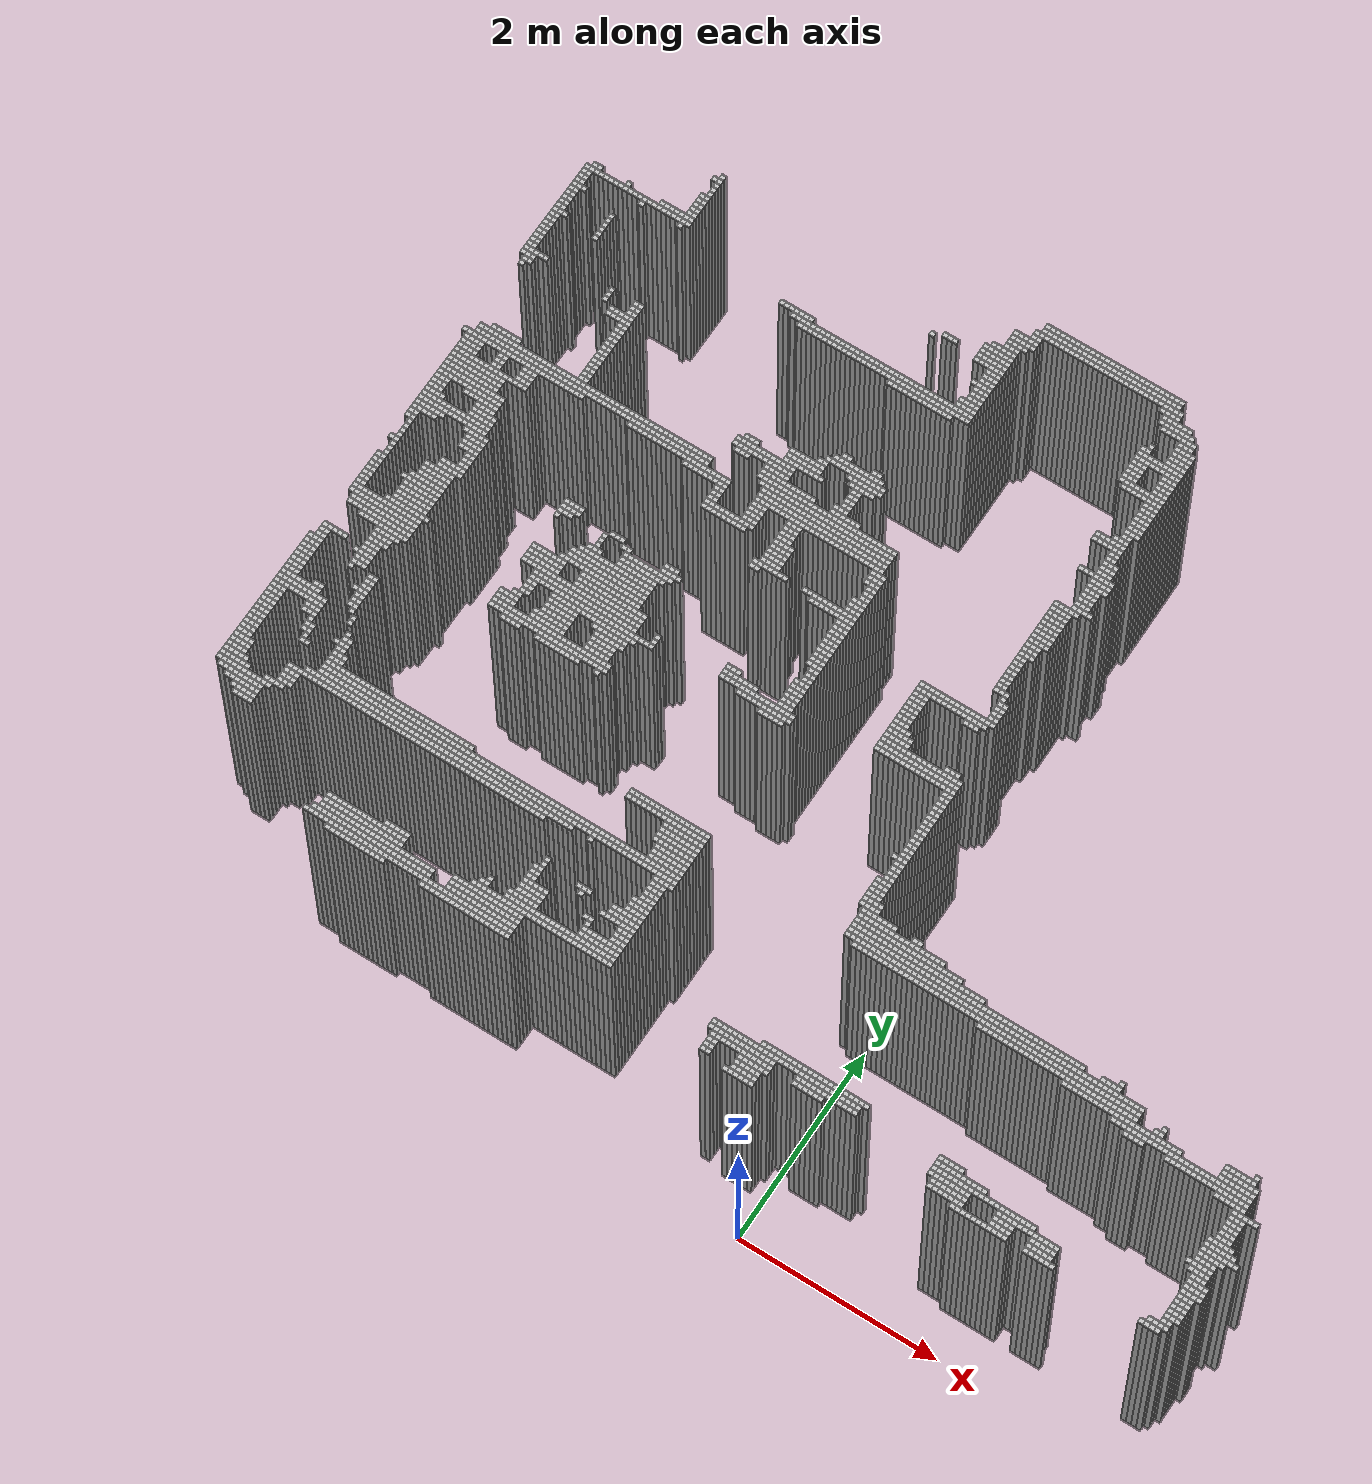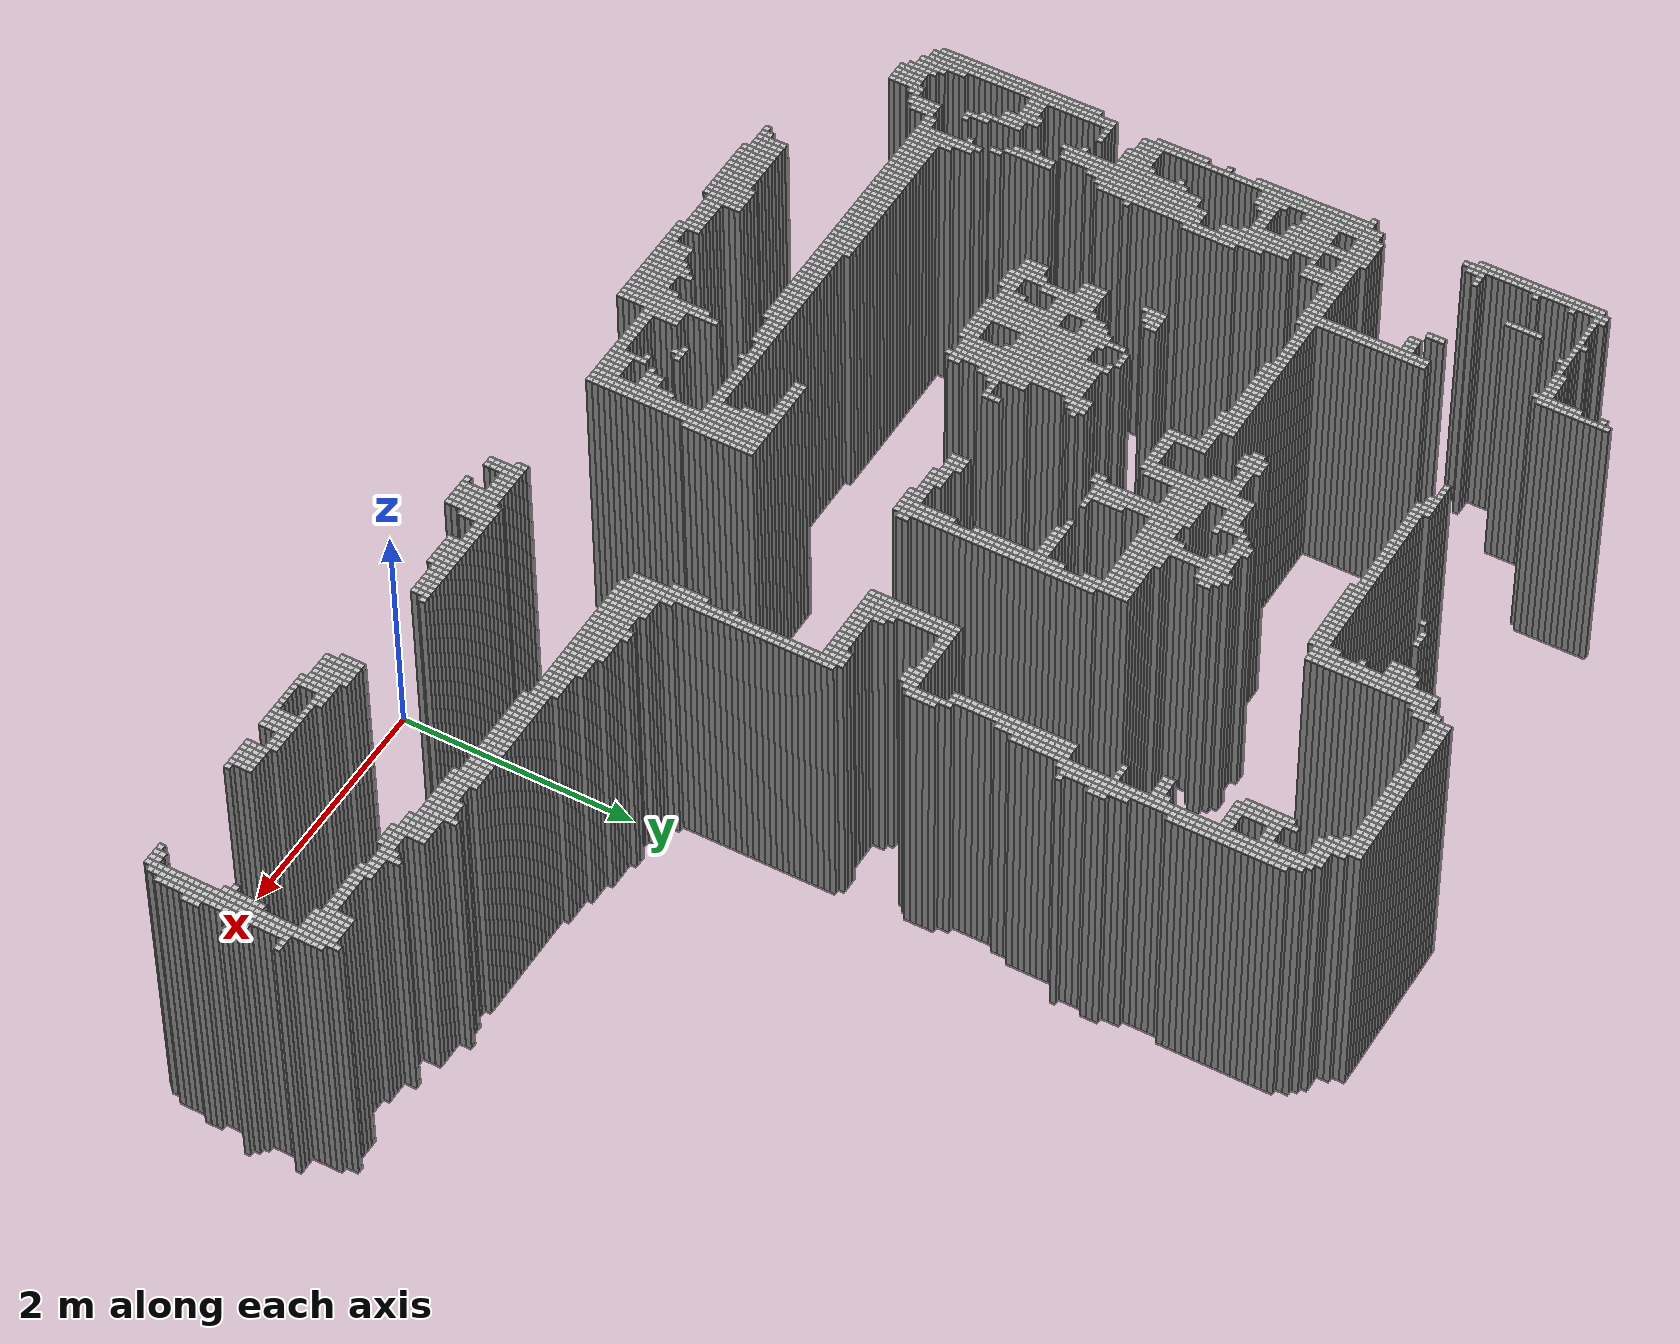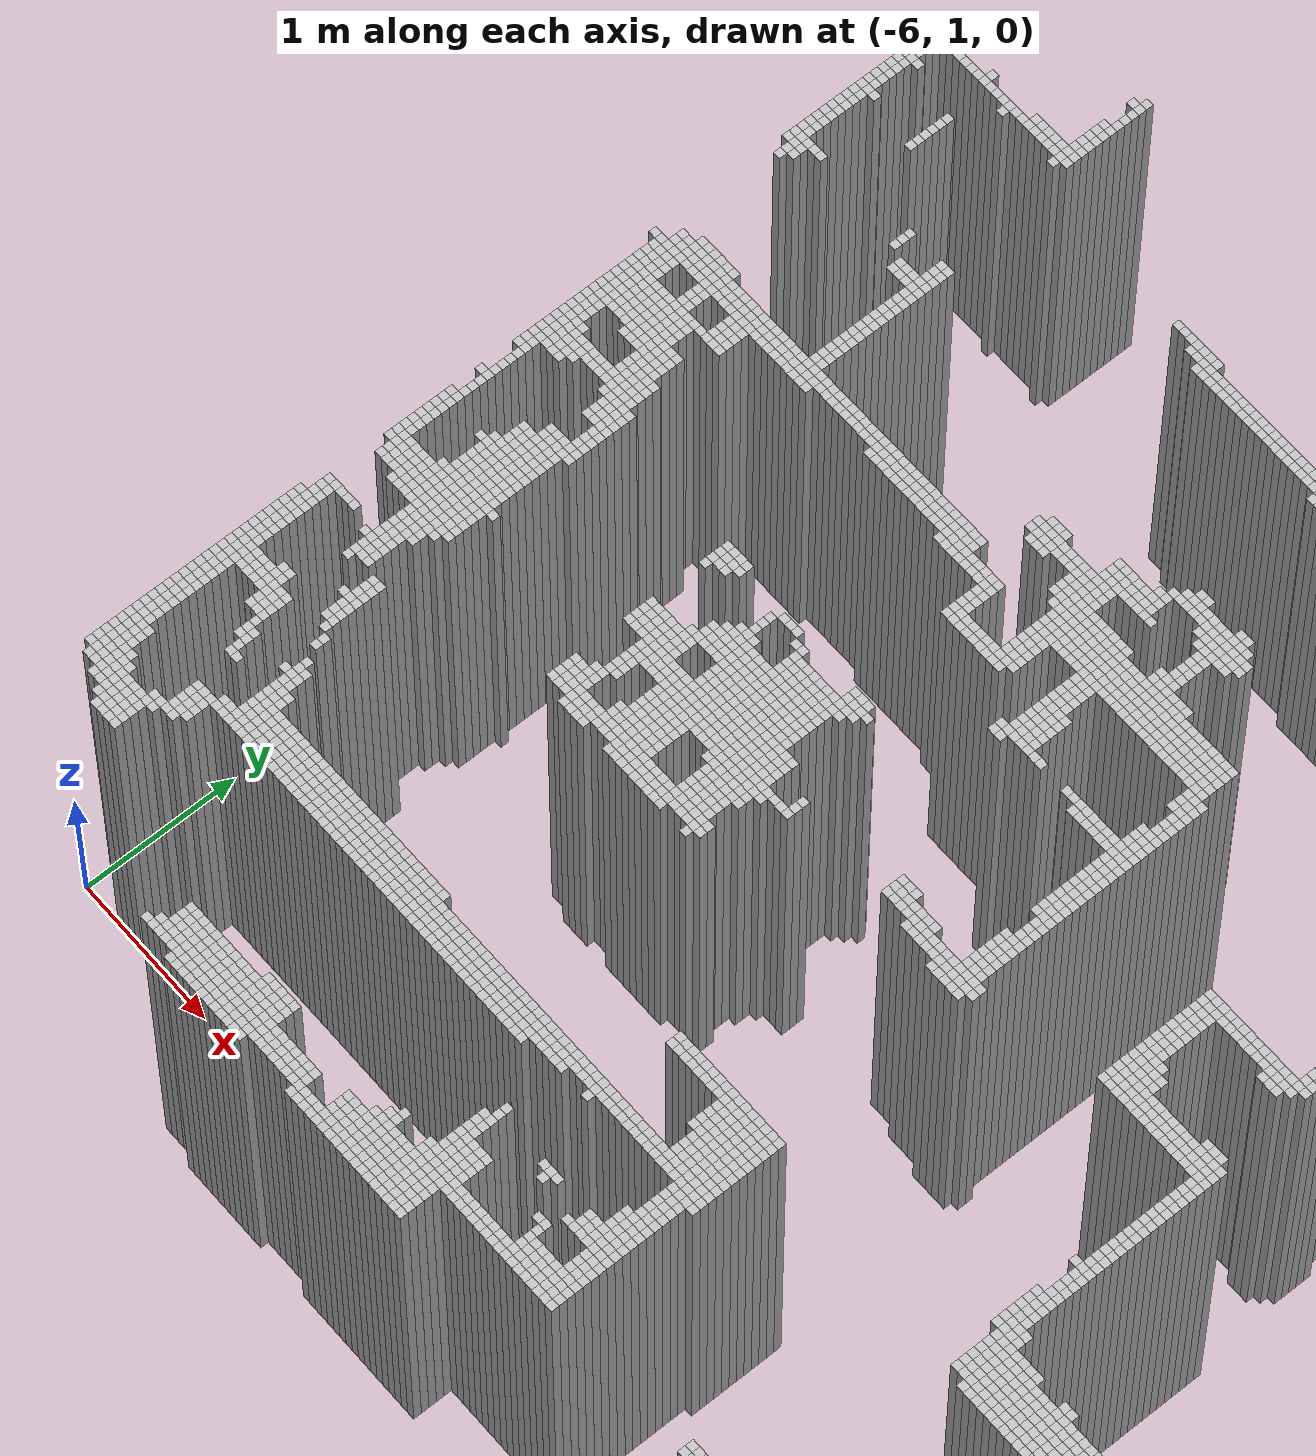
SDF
<sdf version="1.9">
 <world name="map_world">
  <model name="wall_187_0">
   <static>true</static>
   <pose>-1.811 7.680 1.250 0 0 0</pose>
   <link name="link">
    <collision name="collision"><geometry><box><size>0.050 0.050 2.500</size></box></geometry></collision>
    <visual name="visual"><geometry><box><size>0.050 0.050 2.500</size></box></geometry></visual>
   </link>
  </model>
  <model name="wall_188_0">
   <static>true</static>
   <pose>-1.761 7.680 1.250 0 0 0</pose>
   <link name="link">
    <collision name="collision"><geometry><box><size>0.050 0.050 2.500</size></box></geometry></collision>
    <visual name="visual"><geometry><box><size>0.050 0.050 2.500</size></box></geometry></visual>
   </link>
  </model>
  <model name="wall_189_0">
   <static>true</static>
   <pose>-1.711 7.680 1.250 0 0 0</pose>
   <link name="link">
    <collision name="collision"><geometry><box><size>0.050 0.050 2.500</size></box></geometry></collision>
    <visual name="visual"><geometry><box><size>0.050 0.050 2.500</size></box></geometry></visual>
   </link>
  </model>
  <model name="wall_190_0">
   <static>true</static>
   <pose>-1.661 7.680 1.250 0 0 0</pose>
   <link name="link">
    <collision name="collision"><geometry><box><size>0.050 0.050 2.500</size></box></geometry></collision>
    <visual name="visual"><geometry><box><size>0.050 0.050 2.500</size></box></geometry></visual>
   </link>
  </model>
  <model name="wall_191_0">
   <static>true</static>
   <pose>-1.611 7.680 1.250 0 0 0</pose>
   <link name="link">
    <collision name="collision"><geometry><box><size>0.050 0.050 2.500</size></box></geometry></collision>
    <visual name="visual"><geometry><box><size>0.050 0.050 2.500</size></box></geometry></visual>
   </link>
  </model>
  <model name="wall_192_0">
   <static>true</static>
   <pose>-1.561 7.680 1.250 0 0 0</pose>
   <link name="link">
    <collision name="collision"><geometry><box><size>0.050 0.050 2.500</size></box></geometry></collision>
    <visual name="visual"><geometry><box><size>0.050 0.050 2.500</size></box></geometry></visual>
   </link>
  </model>
  <model name="wall_193_0">
   <static>true</static>
   <pose>-1.511 7.680 1.250 0 0 0</pose>
   <link name="link">
    <collision name="collision"><geometry><box><size>0.050 0.050 2.500</size></box></geometry></collision>
    <visual name="visual"><geometry><box><size>0.050 0.050 2.500</size></box></geometry></visual>
   </link>
  </model>
  <model name="wall_194_0">
   <static>true</static>
   <pose>-1.461 7.680 1.250 0 0 0</pose>
   <link name="link">
    <collision name="collision"><geometry><box><size>0.050 0.050 2.500</size></box></geometry></collision>
    <visual name="visual"><geometry><box><size>0.050 0.050 2.500</size></box></geometry></visual>
   </link>
  </model>
  <model name="wall_195_0">
   <static>true</static>
   <pose>-1.411 7.680 1.250 0 0 0</pose>
   <link name="link">
    <collision name="collision"><geometry><box><size>0.050 0.050 2.500</size></box></geometry></collision>
    <visual name="visual"><geometry><box><size>0.050 0.050 2.500</size></box></geometry></visual>
   </link>
  </model>
  <model name="wall_196_0">
   <static>true</static>
   <pose>-1.361 7.680 1.250 0 0 0</pose>
   <link name="link">
    <collision name="collision"><geometry><box><size>0.050 0.050 2.500</size></box></geometry></collision>
    <visual name="visual"><geometry><box><size>0.050 0.050 2.500</size></box></geometry></visual>
   </link>
  </model>
  <model name="wall_197_0">
   <static>true</static>
   <pose>-1.311 7.680 1.250 0 0 0</pose>
   <link name="link">
    <collision name="collision"><geometry><box><size>0.050 0.050 2.500</size></box></geometry></collision>
    <visual name="visual"><geometry><box><size>0.050 0.050 2.500</size></box></geometry></visual>
   </link>
  </model>
  <model name="wall_198_0">
   <static>true</static>
   <pose>-1.261 7.680 1.250 0 0 0</pose>
   <link name="link">
    <collision name="collision"><geometry><box><size>0.050 0.050 2.500</size></box></geometry></collision>
    <visual name="visual"><geometry><box><size>0.050 0.050 2.500</size></box></geometry></visual>
   </link>
  </model>
  <model name="wall_199_0">
   <static>true</static>
   <pose>-1.211 7.680 1.250 0 0 0</pose>
   <link name="link">
    <collision name="collision"><geometry><box><size>0.050 0.050 2.500</size></box></geometry></collision>
    <visual name="visual"><geometry><box><size>0.050 0.050 2.500</size></box></geometry></visual>
   </link>
  </model>
  <model name="wall_200_0">
   <static>true</static>
   <pose>-1.161 7.680 1.250 0 0 0</pose>
   <link name="link">
    <collision name="collision"><geometry><box><size>0.050 0.050 2.500</size></box></geometry></collision>
    <visual name="visual"><geometry><box><size>0.050 0.050 2.500</size></box></geometry></visual>
   </link>
  </model>
  <model name="wall_201_0">
   <static>true</static>
   <pose>-1.111 7.680 1.250 0 0 0</pose>
   <link name="link">
    <collision name="collision"><geometry><box><size>0.050 0.050 2.500</size></box></geometry></collision>
    <visual name="visual"><geometry><box><size>0.050 0.050 2.500</size></box></geometry></visual>
   </link>
  </model>
  <model name="wall_202_0">
   <static>true</static>
   <pose>-1.061 7.680 1.250 0 0 0</pose>
   <link name="link">
    <collision name="collision"><geometry><box><size>0.050 0.050 2.500</size></box></geometry></collision>
    <visual name="visual"><geometry><box><size>0.050 0.050 2.500</size></box></geometry></visual>
   </link>
  </model>
  <model name="wall_203_0">
   <static>true</static>
   <pose>-1.011 7.680 1.250 0 0 0</pose>
   <link name="link">
    <collision name="collision"><geometry><box><size>0.050 0.050 2.500</size></box></geometry></collision>
    <visual name="visual"><geometry><box><size>0.050 0.050 2.500</size></box></geometry></visual>
   </link>
  </model>
  <model name="wall_204_0">
   <static>true</static>
   <pose>-0.961 7.680 1.250 0 0 0</pose>
   <link name="link">
    <collision name="collision"><geometry><box><size>0.050 0.050 2.500</size></box></geometry></collision>
    <visual name="visual"><geometry><box><size>0.050 0.050 2.500</size></box></geometry></visual>
   </link>
  </model>
  <model name="wall_205_0">
   <static>true</static>
   <pose>-0.911 7.680 1.250 0 0 0</pose>
   <link name="link">
    <collision name="collision"><geometry><box><size>0.050 0.050 2.500</size></box></geometry></collision>
    <visual name="visual"><geometry><box><size>0.050 0.050 2.500</size></box></geometry></visual>
   </link>
  </model>
  <model name="wall_206_0">
   <static>true</static>
   <pose>-0.861 7.680 1.250 0 0 0</pose>
   <link name="link">
    <collision name="collision"><geometry><box><size>0.050 0.050 2.500</size></box></geometry></collision>
    <visual name="visual"><geometry><box><size>0.050 0.050 2.500</size></box></geometry></visual>
   </link>
  </model>
  <model name="wall_207_0">
   <static>true</static>
   <pose>-0.811 7.680 1.250 0 0 0</pose>
   <link name="link">
    <collision name="collision"><geometry><box><size>0.050 0.050 2.500</size></box></geometry></collision>
    <visual name="visual"><geometry><box><size>0.050 0.050 2.500</size></box></geometry></visual>
   </link>
  </model>
  <model name="wall_208_0">
   <static>true</static>
   <pose>-0.761 7.680 1.250 0 0 0</pose>
   <link name="link">
    <collision name="collision"><geometry><box><size>0.050 0.050 2.500</size></box></geometry></collision>
    <visual name="visual"><geometry><box><size>0.050 0.050 2.500</size></box></geometry></visual>
   </link>
  </model>
  <model name="wall_209_0">
   <static>true</static>
   <pose>-0.711 7.680 1.250 0 0 0</pose>
   <link name="link">
    <collision name="collision"><geometry><box><size>0.050 0.050 2.500</size></box></geometry></collision>
    <visual name="visual"><geometry><box><size>0.050 0.050 2.500</size></box></geometry></visual>
   </link>
  </model>
  <model name="wall_210_0">
   <static>true</static>
   <pose>-0.661 7.680 1.250 0 0 0</pose>
   <link name="link">
    <collision name="collision"><geometry><box><size>0.050 0.050 2.500</size></box></geometry></collision>
    <visual name="visual"><geometry><box><size>0.050 0.050 2.500</size></box></geometry></visual>
   </link>
  </model>
  <model name="wall_211_0">
   <static>true</static>
   <pose>-0.611 7.680 1.250 0 0 0</pose>
   <link name="link">
    <collision name="collision"><geometry><box><size>0.050 0.050 2.500</size></box></geometry></collision>
    <visual name="visual"><geometry><box><size>0.050 0.050 2.500</size></box></geometry></visual>
   </link>
  </model>
  <model name="wall_212_0">
   <static>true</static>
   <pose>-0.561 7.680 1.250 0 0 0</pose>
   <link name="link">
    <collision name="collision"><geometry><box><size>0.050 0.050 2.500</size></box></geometry></collision>
    <visual name="visual"><geometry><box><size>0.050 0.050 2.500</size></box></geometry></visual>
   </link>
  </model>
  <model name="wall_213_0">
   <static>true</static>
   <pose>-0.511 7.680 1.250 0 0 0</pose>
   <link name="link">
    <collision name="collision"><geometry><box><size>0.050 0.050 2.500</size></box></geometry></collision>
    <visual name="visual"><geometry><box><size>0.050 0.050 2.500</size></box></geometry></visual>
   </link>
  </model>
  <model name="wall_214_0">
   <static>true</static>
   <pose>-0.461 7.680 1.250 0 0 0</pose>
   <link name="link">
    <collision name="collision"><geometry><box><size>0.050 0.050 2.500</size></box></geometry></collision>
    <visual name="visual"><geometry><box><size>0.050 0.050 2.500</size></box></geometry></visual>
   </link>
  </model>
  <model name="wall_187_1">
   <static>true</static>
   <pose>-1.811 7.630 1.250 0 0 0</pose>
   <link name="link">
    <collision name="collision"><geometry><box><size>0.050 0.050 2.500</size></box></geometry></collision>
    <visual name="visual"><geometry><box><size>0.050 0.050 2.500</size></box></geometry></visual>
   </link>
  </model>
  <model name="wall_188_1">
   <static>true</static>
   <pose>-1.761 7.630 1.250 0 0 0</pose>
   <link name="link">
    <collision name="collision"><geometry><box><size>0.050 0.050 2.500</size></box></geometry></collision>
    <visual name="visual"><geometry><box><size>0.050 0.050 2.500</size></box></geometry></visual>
   </link>
  </model>
  <model name="wall_189_1">
   <static>true</static>
   <pose>-1.711 7.630 1.250 0 0 0</pose>
   <link name="link">
    <collision name="collision"><geometry><box><size>0.050 0.050 2.500</size></box></geometry></collision>
    <visual name="visual"><geometry><box><size>0.050 0.050 2.500</size></box></geometry></visual>
   </link>
  </model>
  <model name="wall_190_1">
   <static>true</static>
   <pose>-1.661 7.630 1.250 0 0 0</pose>
   <link name="link">
    <collision name="collision"><geometry><box><size>0.050 0.050 2.500</size></box></geometry></collision>
    <visual name="visual"><geometry><box><size>0.050 0.050 2.500</size></box></geometry></visual>
   </link>
  </model>
  <model name="wall_191_1">
   <static>true</static>
   <pose>-1.611 7.630 1.250 0 0 0</pose>
   <link name="link">
    <collision name="collision"><geometry><box><size>0.050 0.050 2.500</size></box></geometry></collision>
    <visual name="visual"><geometry><box><size>0.050 0.050 2.500</size></box></geometry></visual>
   </link>
  </model>
  <model name="wall_192_1">
   <static>true</static>
   <pose>-1.561 7.630 1.250 0 0 0</pose>
   <link name="link">
    <collision name="collision"><geometry><box><size>0.050 0.050 2.500</size></box></geometry></collision>
    <visual name="visual"><geometry><box><size>0.050 0.050 2.500</size></box></geometry></visual>
   </link>
  </model>
  <model name="wall_193_1">
   <static>true</static>
   <pose>-1.511 7.630 1.250 0 0 0</pose>
   <link name="link">
    <collision name="collision"><geometry><box><size>0.050 0.050 2.500</size></box></geometry></collision>
    <visual name="visual"><geometry><box><size>0.050 0.050 2.500</size></box></geometry></visual>
   </link>
  </model>
  <model name="wall_194_1">
   <static>true</static>
   <pose>-1.461 7.630 1.250 0 0 0</pose>
   <link name="link">
    <collision name="collision"><geometry><box><size>0.050 0.050 2.500</size></box></geometry></collision>
    <visual name="visual"><geometry><box><size>0.050 0.050 2.500</size></box></geometry></visual>
   </link>
  </model>
  <model name="wall_195_1">
   <static>true</static>
   <pose>-1.411 7.630 1.250 0 0 0</pose>
   <link name="link">
    <collision name="collision"><geometry><box><size>0.050 0.050 2.500</size></box></geometry></collision>
    <visual name="visual"><geometry><box><size>0.050 0.050 2.500</size></box></geometry></visual>
   </link>
  </model>
  <model name="wall_196_1">
   <static>true</static>
   <pose>-1.361 7.630 1.250 0 0 0</pose>
   <link name="link">
    <collision name="collision"><geometry><box><size>0.050 0.050 2.500</size></box></geometry></collision>
    <visual name="visual"><geometry><box><size>0.050 0.050 2.500</size></box></geometry></visual>
   </link>
  </model>
  <model name="wall_197_1">
   <static>true</static>
   <pose>-1.311 7.630 1.250 0 0 0</pose>
   <link name="link">
    <collision name="collision"><geometry><box><size>0.050 0.050 2.500</size></box></geometry></collision>
    <visual name="visual"><geometry><box><size>0.050 0.050 2.500</size></box></geometry></visual>
   </link>
  </model>
  <model name="wall_198_1">
   <static>true</static>
   <pose>-1.261 7.630 1.250 0 0 0</pose>
   <link name="link">
    <collision name="collision"><geometry><box><size>0.050 0.050 2.500</size></box></geometry></collision>
    <visual name="visual"><geometry><box><size>0.050 0.050 2.500</size></box></geometry></visual>
   </link>
  </model>
  <model name="wall_199_1">
   <static>true</static>
   <pose>-1.211 7.630 1.250 0 0 0</pose>
   <link name="link">
    <collision name="collision"><geometry><box><size>0.050 0.050 2.500</size></box></geometry></collision>
    <visual name="visual"><geometry><box><size>0.050 0.050 2.500</size></box></geometry></visual>
   </link>
  </model>
  <model name="wall_200_1">
   <static>true</static>
   <pose>-1.161 7.630 1.250 0 0 0</pose>
   <link name="link">
    <collision name="collision"><geometry><box><size>0.050 0.050 2.500</size></box></geometry></collision>
    <visual name="visual"><geometry><box><size>0.050 0.050 2.500</size></box></geometry></visual>
   </link>
  </model>
  <model name="wall_201_1">
   <static>true</static>
   <pose>-1.111 7.630 1.250 0 0 0</pose>
   <link name="link">
    <collision name="collision"><geometry><box><size>0.050 0.050 2.500</size></box></geometry></collision>
    <visual name="visual"><geometry><box><size>0.050 0.050 2.500</size></box></geometry></visual>
   </link>
  </model>
  <model name="wall_202_1">
   <static>true</static>
   <pose>-1.061 7.630 1.250 0 0 0</pose>
   <link name="link">
    <collision name="collision"><geometry><box><size>0.050 0.050 2.500</size></box></geometry></collision>
    <visual name="visual"><geometry><box><size>0.050 0.050 2.500</size></box></geometry></visual>
   </link>
  </model>
  <model name="wall_203_1">
   <static>true</static>
   <pose>-1.011 7.630 1.250 0 0 0</pose>
   <link name="link">
    <collision name="collision"><geometry><box><size>0.050 0.050 2.500</size></box></geometry></collision>
    <visual name="visual"><geometry><box><size>0.050 0.050 2.500</size></box></geometry></visual>
   </link>
  </model>
  <model name="wall_204_1">
   <static>true</static>
   <pose>-0.961 7.630 1.250 0 0 0</pose>
   <link name="link">
    <collision name="collision"><geometry><box><size>0.050 0.050 2.500</size></box></geometry></collision>
    <visual name="visual"><geometry><box><size>0.050 0.050 2.500</size></box></geometry></visual>
   </link>
  </model>
  <model name="wall_205_1">
   <static>true</static>
   <pose>-0.911 7.630 1.250 0 0 0</pose>
   <link name="link">
    <collision name="collision"><geometry><box><size>0.050 0.050 2.500</size></box></geometry></collision>
    <visual name="visual"><geometry><box><size>0.050 0.050 2.500</size></box></geometry></visual>
   </link>
  </model>
  <model name="wall_206_1">
   <static>true</static>
   <pose>-0.861 7.630 1.250 0 0 0</pose>
   <link name="link">
    <collision name="collision"><geometry><box><size>0.050 0.050 2.500</size></box></geometry></collision>
    <visual name="visual"><geometry><box><size>0.050 0.050 2.500</size></box></geometry></visual>
   </link>
  </model>
  <model name="wall_207_1">
   <static>true</static>
   <pose>-0.811 7.630 1.250 0 0 0</pose>
   <link name="link">
    <collision name="collision"><geometry><box><size>0.050 0.050 2.500</size></box></geometry></collision>
    <visual name="visual"><geometry><box><size>0.050 0.050 2.500</size></box></geometry></visual>
   </link>
  </model>
  <model name="wall_208_1">
   <static>true</static>
   <pose>-0.761 7.630 1.250 0 0 0</pose>
   <link name="link">
    <collision name="collision"><geometry><box><size>0.050 0.050 2.500</size></box></geometry></collision>
    <visual name="visual"><geometry><box><size>0.050 0.050 2.500</size></box></geometry></visual>
   </link>
  </model>
  <model name="wall_209_1">
   <static>true</static>
   <pose>-0.711 7.630 1.250 0 0 0</pose>
   <link name="link">
    <collision name="collision"><geometry><box><size>0.050 0.050 2.500</size></box></geometry></collision>
    <visual name="visual"><geometry><box><size>0.050 0.050 2.500</size></box></geometry></visual>
   </link>
  </model>
  <model name="wall_210_1">
   <static>true</static>
   <pose>-0.661 7.630 1.250 0 0 0</pose>
   <link name="link">
    <collision name="collision"><geometry><box><size>0.050 0.050 2.500</size></box></geometry></collision>
    <visual name="visual"><geometry><box><size>0.050 0.050 2.500</size></box></geometry></visual>
   </link>
  </model>
  <model name="wall_211_1">
   <static>true</static>
   <pose>-0.611 7.630 1.250 0 0 0</pose>
   <link name="link">
    <collision name="collision"><geometry><box><size>0.050 0.050 2.500</size></box></geometry></collision>
    <visual name="visual"><geometry><box><size>0.050 0.050 2.500</size></box></geometry></visual>
   </link>
  </model>
  <model name="wall_212_1">
   <static>true</static>
   <pose>-0.561 7.630 1.250 0 0 0</pose>
   <link name="link">
    <collision name="collision"><geometry><box><size>0.050 0.050 2.500</size></box></geometry></collision>
    <visual name="visual"><geometry><box><size>0.050 0.050 2.500</size></box></geometry></visual>
   </link>
  </model>
  <model name="wall_213_1">
   <static>true</static>
   <pose>-0.511 7.630 1.250 0 0 0</pose>
   <link name="link">
    <collision name="collision"><geometry><box><size>0.050 0.050 2.500</size></box></geometry></collision>
    <visual name="visual"><geometry><box><size>0.050 0.050 2.500</size></box></geometry></visual>
   </link>
  </model>
  <model name="wall_214_1">
   <static>true</static>
   <pose>-0.461 7.630 1.250 0 0 0</pose>
   <link name="link">
    <collision name="collision"><geometry><box><size>0.050 0.050 2.500</size></box></geometry></collision>
    <visual name="visual"><geometry><box><size>0.050 0.050 2.500</size></box></geometry></visual>
   </link>
  </model>
  <model name="wall_186_2">
   <static>true</static>
   <pose>-1.861 7.580 1.250 0 0 0</pose>
   <link name="link">
    <collision name="collision"><geometry><box><size>0.050 0.050 2.500</size></box></geometry></collision>
    <visual name="visual"><geometry><box><size>0.050 0.050 2.500</size></box></geometry></visual>
   </link>
  </model>
  <model name="wall_187_2">
   <static>true</static>
   <pose>-1.811 7.580 1.250 0 0 0</pose>
   <link name="link">
    <collision name="collision"><geometry><box><size>0.050 0.050 2.500</size></box></geometry></collision>
    <visual name="visual"><geometry><box><size>0.050 0.050 2.500</size></box></geometry></visual>
   </link>
  </model>
  <model name="wall_188_2">
   <static>true</static>
   <pose>-1.761 7.580 1.250 0 0 0</pose>
   <link name="link">
    <collision name="collision"><geometry><box><size>0.050 0.050 2.500</size></box></geometry></collision>
    <visual name="visual"><geometry><box><size>0.050 0.050 2.500</size></box></geometry></visual>
   </link>
  </model>
  <model name="wall_189_2">
   <static>true</static>
   <pose>-1.711 7.580 1.250 0 0 0</pose>
   <link name="link">
    <collision name="collision"><geometry><box><size>0.050 0.050 2.500</size></box></geometry></collision>
    <visual name="visual"><geometry><box><size>0.050 0.050 2.500</size></box></geometry></visual>
   </link>
  </model>
  <model name="wall_190_2">
   <static>true</static>
   <pose>-1.661 7.580 1.250 0 0 0</pose>
   <link name="link">
    <collision name="collision"><geometry><box><size>0.050 0.050 2.500</size></box></geometry></collision>
    <visual name="visual"><geometry><box><size>0.050 0.050 2.500</size></box></geometry></visual>
   </link>
  </model>
  <model name="wall_191_2">
   <static>true</static>
   <pose>-1.611 7.580 1.250 0 0 0</pose>
   <link name="link">
    <collision name="collision"><geometry><box><size>0.050 0.050 2.500</size></box></geometry></collision>
    <visual name="visual"><geometry><box><size>0.050 0.050 2.500</size></box></geometry></visual>
   </link>
  </model>
  <model name="wall_192_2">
   <static>true</static>
   <pose>-1.561 7.580 1.250 0 0 0</pose>
   <link name="link">
    <collision name="collision"><geometry><box><size>0.050 0.050 2.500</size></box></geometry></collision>
    <visual name="visual"><geometry><box><size>0.050 0.050 2.500</size></box></geometry></visual>
   </link>
  </model>
  <model name="wall_193_2">
   <static>true</static>
   <pose>-1.511 7.580 1.250 0 0 0</pose>
   <link name="link">
    <collision name="collision"><geometry><box><size>0.050 0.050 2.500</size></box></geometry></collision>
    <visual name="visual"><geometry><box><size>0.050 0.050 2.500</size></box></geometry></visual>
   </link>
  </model>
  <model name="wall_194_2">
   <static>true</static>
   <pose>-1.461 7.580 1.250 0 0 0</pose>
   <link name="link">
    <collision name="collision"><geometry><box><size>0.050 0.050 2.500</size></box></geometry></collision>
    <visual name="visual"><geometry><box><size>0.050 0.050 2.500</size></box></geometry></visual>
   </link>
  </model>
  <model name="wall_195_2">
   <static>true</static>
   <pose>-1.411 7.580 1.250 0 0 0</pose>
   <link name="link">
    <collision name="collision"><geometry><box><size>0.050 0.050 2.500</size></box></geometry></collision>
    <visual name="visual"><geometry><box><size>0.050 0.050 2.500</size></box></geometry></visual>
   </link>
  </model>
  <model name="wall_196_2">
   <static>true</static>
   <pose>-1.361 7.580 1.250 0 0 0</pose>
   <link name="link">
    <collision name="collision"><geometry><box><size>0.050 0.050 2.500</size></box></geometry></collision>
    <visual name="visual"><geometry><box><size>0.050 0.050 2.500</size></box></geometry></visual>
   </link>
  </model>
  <model name="wall_197_2">
   <static>true</static>
   <pose>-1.311 7.580 1.250 0 0 0</pose>
   <link name="link">
    <collision name="collision"><geometry><box><size>0.050 0.050 2.500</size></box></geometry></collision>
    <visual name="visual"><geometry><box><size>0.050 0.050 2.500</size></box></geometry></visual>
   </link>
  </model>
  <model name="wall_198_2">
   <static>true</static>
   <pose>-1.261 7.580 1.250 0 0 0</pose>
   <link name="link">
    <collision name="collision"><geometry><box><size>0.050 0.050 2.500</size></box></geometry></collision>
    <visual name="visual"><geometry><box><size>0.050 0.050 2.500</size></box></geometry></visual>
   </link>
  </model>
  <model name="wall_199_2">
   <static>true</static>
   <pose>-1.211 7.580 1.250 0 0 0</pose>
   <link name="link">
    <collision name="collision"><geometry><box><size>0.050 0.050 2.500</size></box></geometry></collision>
    <visual name="visual"><geometry><box><size>0.050 0.050 2.500</size></box></geometry></visual>
   </link>
  </model>
  <model name="wall_200_2">
   <static>true</static>
   <pose>-1.161 7.580 1.250 0 0 0</pose>
   <link name="link">
    <collision name="collision"><geometry><box><size>0.050 0.050 2.500</size></box></geometry></collision>
    <visual name="visual"><geometry><box><size>0.050 0.050 2.500</size></box></geometry></visual>
   </link>
  </model>
  <model name="wall_201_2">
   <static>true</static>
   <pose>-1.111 7.580 1.250 0 0 0</pose>
   <link name="link">
    <collision name="collision"><geometry><box><size>0.050 0.050 2.500</size></box></geometry></collision>
    <visual name="visual"><geometry><box><size>0.050 0.050 2.500</size></box></geometry></visual>
   </link>
  </model>
  <model name="wall_202_2">
   <static>true</static>
   <pose>-1.061 7.580 1.250 0 0 0</pose>
   <link name="link">
    <collision name="collision"><geometry><box><size>0.050 0.050 2.500</size></box></geometry></collision>
    <visual name="visual"><geometry><box><size>0.050 0.050 2.500</size></box></geometry></visual>
   </link>
  </model>
  <model name="wall_203_2">
   <static>true</static>
   <pose>-1.011 7.580 1.250 0 0 0</pose>
   <link name="link">
    <collision name="collision"><geometry><box><size>0.050 0.050 2.500</size></box></geometry></collision>
    <visual name="visual"><geometry><box><size>0.050 0.050 2.500</size></box></geometry></visual>
   </link>
  </model>
  <model name="wall_204_2">
   <static>true</static>
   <pose>-0.961 7.580 1.250 0 0 0</pose>
   <link name="link">
    <collision name="collision"><geometry><box><size>0.050 0.050 2.500</size></box></geometry></collision>
    <visual name="visual"><geometry><box><size>0.050 0.050 2.500</size></box></geometry></visual>
   </link>
  </model>
  <model name="wall_205_2">
   <static>true</static>
   <pose>-0.911 7.580 1.250 0 0 0</pose>
   <link name="link">
    <collision name="collision"><geometry><box><size>0.050 0.050 2.500</size></box></geometry></collision>
    <visual name="visual"><geometry><box><size>0.050 0.050 2.500</size></box></geometry></visual>
   </link>
  </model>
  <model name="wall_206_2">
   <static>true</static>
   <pose>-0.861 7.580 1.250 0 0 0</pose>
   <link name="link">
    <collision name="collision"><geometry><box><size>0.050 0.050 2.500</size></box></geometry></collision>
    <visual name="visual"><geometry><box><size>0.050 0.050 2.500</size></box></geometry></visual>
   </link>
  </model>
  <model name="wall_207_2">
   <static>true</static>
   <pose>-0.811 7.580 1.250 0 0 0</pose>
   <link name="link">
    <collision name="collision"><geometry><box><size>0.050 0.050 2.500</size></box></geometry></collision>
    <visual name="visual"><geometry><box><size>0.050 0.050 2.500</size></box></geometry></visual>
   </link>
  </model>
  <model name="wall_208_2">
   <static>true</static>
   <pose>-0.761 7.580 1.250 0 0 0</pose>
   <link name="link">
    <collision name="collision"><geometry><box><size>0.050 0.050 2.500</size></box></geometry></collision>
    <visual name="visual"><geometry><box><size>0.050 0.050 2.500</size></box></geometry></visual>
   </link>
  </model>
  <model name="wall_209_2">
   <static>true</static>
   <pose>-0.711 7.580 1.250 0 0 0</pose>
   <link name="link">
    <collision name="collision"><geometry><box><size>0.050 0.050 2.500</size></box></geometry></collision>
    <visual name="visual"><geometry><box><size>0.050 0.050 2.500</size></box></geometry></visual>
   </link>
  </model>
  <model name="wall_210_2">
   <static>true</static>
   <pose>-0.661 7.580 1.250 0 0 0</pose>
   <link name="link">
    <collision name="collision"><geometry><box><size>0.050 0.050 2.500</size></box></geometry></collision>
    <visual name="visual"><geometry><box><size>0.050 0.050 2.500</size></box></geometry></visual>
   </link>
  </model>
  <model name="wall_211_2">
   <static>true</static>
   <pose>-0.611 7.580 1.250 0 0 0</pose>
   <link name="link">
    <collision name="collision"><geometry><box><size>0.050 0.050 2.500</size></box></geometry></collision>
    <visual name="visual"><geometry><box><size>0.050 0.050 2.500</size></box></geometry></visual>
   </link>
  </model>
  <model name="wall_212_2">
   <static>true</static>
   <pose>-0.561 7.580 1.250 0 0 0</pose>
   <link name="link">
    <collision name="collision"><geometry><box><size>0.050 0.050 2.500</size></box></geometry></collision>
    <visual name="visual"><geometry><box><size>0.050 0.050 2.500</size></box></geometry></visual>
   </link>
  </model>
  <model name="wall_213_2">
   <static>true</static>
   <pose>-0.511 7.580 1.250 0 0 0</pose>
   <link name="link">
    <collision name="collision"><geometry><box><size>0.050 0.050 2.500</size></box></geometry></collision>
    <visual name="visual"><geometry><box><size>0.050 0.050 2.500</size></box></geometry></visual>
   </link>
  </model>
  <model name="wall_214_2">
   <static>true</static>
   <pose>-0.461 7.580 1.250 0 0 0</pose>
   <link name="link">
    <collision name="collision"><geometry><box><size>0.050 0.050 2.500</size></box></geometry></collision>
    <visual name="visual"><geometry><box><size>0.050 0.050 2.500</size></box></geometry></visual>
   </link>
  </model>
  <model name="wall_215_2">
   <static>true</static>
   <pose>-0.411 7.580 1.250 0 0 0</pose>
   <link name="link">
    <collision name="collision"><geometry><box><size>0.050 0.050 2.500</size></box></geometry></collision>
    <visual name="visual"><geometry><box><size>0.050 0.050 2.500</size></box></geometry></visual>
   </link>
  </model>
  <model name="wall_186_3">
   <static>true</static>
   <pose>-1.861 7.530 1.250 0 0 0</pose>
   <link name="link">
    <collision name="collision"><geometry><box><size>0.050 0.050 2.500</size></box></geometry></collision>
    <visual name="visual"><geometry><box><size>0.050 0.050 2.500</size></box></geometry></visual>
   </link>
  </model>
  <model name="wall_187_3">
   <static>true</static>
   <pose>-1.811 7.530 1.250 0 0 0</pose>
   <link name="link">
    <collision name="collision"><geometry><box><size>0.050 0.050 2.500</size></box></geometry></collision>
    <visual name="visual"><geometry><box><size>0.050 0.050 2.500</size></box></geometry></visual>
   </link>
  </model>
  <model name="wall_212_3">
   <static>true</static>
   <pose>-0.561 7.530 1.250 0 0 0</pose>
   <link name="link">
    <collision name="collision"><geometry><box><size>0.050 0.050 2.500</size></box></geometry></collision>
    <visual name="visual"><geometry><box><size>0.050 0.050 2.500</size></box></geometry></visual>
   </link>
  </model>
  <model name="wall_213_3">
   <static>true</static>
   <pose>-0.511 7.530 1.250 0 0 0</pose>
   <link name="link">
    <collision name="collision"><geometry><box><size>0.050 0.050 2.500</size></box></geometry></collision>
    <visual name="visual"><geometry><box><size>0.050 0.050 2.500</size></box></geometry></visual>
   </link>
  </model>
  <model name="wall_214_3">
   <static>true</static>
   <pose>-0.461 7.530 1.250 0 0 0</pose>
   <link name="link">
    <collision name="collision"><geometry><box><size>0.050 0.050 2.500</size></box></geometry></collision>
    <visual name="visual"><geometry><box><size>0.050 0.050 2.500</size></box></geometry></visual>
   </link>
  </model>
  <model name="wall_215_3">
   <static>true</static>
   <pose>-0.411 7.530 1.250 0 0 0</pose>
   <link name="link">
    <collision name="collision"><geometry><box><size>0.050 0.050 2.500</size></box></geometry></collision>
    <visual name="visual"><geometry><box><size>0.050 0.050 2.500</size></box></geometry></visual>
   </link>
  </model>
  <model name="wall_183_4">
   <static>true</static>
   <pose>-2.011 7.480 1.250 0 0 0</pose>
   <link name="link">
    <collision name="collision"><geometry><box><size>0.050 0.050 2.500</size></box></geometry></collision>
    <visual name="visual"><geometry><box><size>0.050 0.050 2.500</size></box></geometry></visual>
   </link>
  </model>
  <model name="wall_184_4">
   <static>true</static>
   <pose>-1.961 7.480 1.250 0 0 0</pose>
   <link name="link">
    <collision name="collision"><geometry><box><size>0.050 0.050 2.500</size></box></geometry></collision>
    <visual name="visual"><geometry><box><size>0.050 0.050 2.500</size></box></geometry></visual>
   </link>
  </model>
  <model name="wall_185_4">
   <static>true</static>
   <pose>-1.911 7.480 1.250 0 0 0</pose>
   <link name="link">
    <collision name="collision"><geometry><box><size>0.050 0.050 2.500</size></box></geometry></collision>
    <visual name="visual"><geometry><box><size>0.050 0.050 2.500</size></box></geometry></visual>
   </link>
  </model>
  <model name="wall_186_4">
   <static>true</static>
   <pose>-1.861 7.480 1.250 0 0 0</pose>
   <link name="link">
    <collision name="collision"><geometry><box><size>0.050 0.050 2.500</size></box></geometry></collision>
    <visual name="visual"><geometry><box><size>0.050 0.050 2.500</size></box></geometry></visual>
   </link>
  </model>
  <model name="wall_187_4">
   <static>true</static>
   <pose>-1.811 7.480 1.250 0 0 0</pose>
   <link name="link">
    <collision name="collision"><geometry><box><size>0.050 0.050 2.500</size></box></geometry></collision>
    <visual name="visual"><geometry><box><size>0.050 0.050 2.500</size></box></geometry></visual>
   </link>
  </model>
  <model name="wall_213_4">
   <static>true</static>
   <pose>-0.511 7.480 1.250 0 0 0</pose>
   <link name="link">
    <collision name="collision"><geometry><box><size>0.050 0.050 2.500</size></box></geometry></collision>
    <visual name="visual"><geometry><box><size>0.050 0.050 2.500</size></box></geometry></visual>
   </link>
  </model>
  <model name="wall_214_4">
   <static>true</static>
   <pose>-0.461 7.480 1.250 0 0 0</pose>
   <link name="link">
    <collision name="collision"><geometry><box><size>0.050 0.050 2.500</size></box></geometry></collision>
    <visual name="visual"><geometry><box><size>0.050 0.050 2.500</size></box></geometry></visual>
   </link>
  </model>
  <model name="wall_215_4">
   <static>true</static>
   <pose>-0.411 7.480 1.250 0 0 0</pose>
   <link name="link">
    <collision name="collision"><geometry><box><size>0.050 0.050 2.500</size></box></geometry></collision>
    <visual name="visual"><geometry><box><size>0.050 0.050 2.500</size></box></geometry></visual>
   </link>
  </model>
  <model name="wall_216_4">
   <static>true</static>
   <pose>-0.361 7.480 1.250 0 0 0</pose>
   <link name="link">
    <collision name="collision"><geometry><box><size>0.050 0.050 2.500</size></box></geometry></collision>
    <visual name="visual"><geometry><box><size>0.050 0.050 2.500</size></box></geometry></visual>
   </link>
  </model>
  <model name="wall_217_4">
   <static>true</static>
   <pose>-0.311 7.480 1.250 0 0 0</pose>
   <link name="link">
    <collision name="collision"><geometry><box><size>0.050 0.050 2.500</size></box></geometry></collision>
    <visual name="visual"><geometry><box><size>0.050 0.050 2.500</size></box></geometry></visual>
   </link>
  </model>
  <model name="wall_218_4">
   <static>true</static>
   <pose>-0.261 7.480 1.250 0 0 0</pose>
   <link name="link">
    <collision name="collision"><geometry><box><size>0.050 0.050 2.500</size></box></geometry></collision>
    <visual name="visual"><geometry><box><size>0.050 0.050 2.500</size></box></geometry></visual>
   </link>
  </model>
  <model name="wall_183_5">
   <static>true</static>
   <pose>-2.011 7.430 1.250 0 0 0</pose>
   <link name="link">
    <collision name="collision"><geometry><box><size>0.050 0.050 2.500</size></box></geometry></collision>
    <visual name="visual"><geometry><box><size>0.050 0.050 2.500</size></box></geometry></visual>
   </link>
  </model>
  <model name="wall_184_5">
   <static>true</static>
   <pose>-1.961 7.430 1.250 0 0 0</pose>
   <link name="link">
    <collision name="collision"><geometry><box><size>0.050 0.050 2.500</size></box></geometry></collision>
    <visual name="visual"><geometry><box><size>0.050 0.050 2.500</size></box></geometry></visual>
   </link>
  </model>
  <model name="wall_185_5">
   <static>true</static>
   <pose>-1.911 7.430 1.250 0 0 0</pose>
   <link name="link">
    <collision name="collision"><geometry><box><size>0.050 0.050 2.500</size></box></geometry></collision>
    <visual name="visual"><geometry><box><size>0.050 0.050 2.500</size></box></geometry></visual>
   </link>
  </model>
  <model name="wall_186_5">
   <static>true</static>
   <pose>-1.861 7.430 1.250 0 0 0</pose>
   <link name="link">
    <collision name="collision"><geometry><box><size>0.050 0.050 2.500</size></box></geometry></collision>
    <visual name="visual"><geometry><box><size>0.050 0.050 2.500</size></box></geometry></visual>
   </link>
  </model>
  <model name="wall_187_5">
   <static>true</static>
   <pose>-1.811 7.430 1.250 0 0 0</pose>
   <link name="link">
    <collision name="collision"><geometry><box><size>0.050 0.050 2.500</size></box></geometry></collision>
    <visual name="visual"><geometry><box><size>0.050 0.050 2.500</size></box></geometry></visual>
   </link>
  </model>
  <model name="wall_213_5">
   <static>true</static>
   <pose>-0.511 7.430 1.250 0 0 0</pose>
   <link name="link">
    <collision name="collision"><geometry><box><size>0.050 0.050 2.500</size></box></geometry></collision>
    <visual name="visual"><geometry><box><size>0.050 0.050 2.500</size></box></geometry></visual>
   </link>
  </model>
  <model name="wall_214_5">
   <static>true</static>
   <pose>-0.461 7.430 1.250 0 0 0</pose>
   <link name="link">
    <collision name="collision"><geometry><box><size>0.050 0.050 2.500</size></box></geometry></collision>
    <visual name="visual"><geometry><box><size>0.050 0.050 2.500</size></box></geometry></visual>
   </link>
  </model>
  <model name="wall_215_5">
   <static>true</static>
   <pose>-0.411 7.430 1.250 0 0 0</pose>
   <link name="link">
    <collision name="collision"><geometry><box><size>0.050 0.050 2.500</size></box></geometry></collision>
    <visual name="visual"><geometry><box><size>0.050 0.050 2.500</size></box></geometry></visual>
   </link>
  </model>
  <model name="wall_216_5">
   <static>true</static>
   <pose>-0.361 7.430 1.250 0 0 0</pose>
   <link name="link">
    <collision name="collision"><geometry><box><size>0.050 0.050 2.500</size></box></geometry></collision>
    <visual name="visual"><geometry><box><size>0.050 0.050 2.500</size></box></geometry></visual>
   </link>
  </model>
  <model name="wall_217_5">
   <static>true</static>
   <pose>-0.311 7.430 1.250 0 0 0</pose>
   <link name="link">
    <collision name="collision"><geometry><box><size>0.050 0.050 2.500</size></box></geometry></collision>
    <visual name="visual"><geometry><box><size>0.050 0.050 2.500</size></box></geometry></visual>
   </link>
  </model>
  <model name="wall_218_5">
   <static>true</static>
   <pose>-0.261 7.430 1.250 0 0 0</pose>
   <link name="link">
    <collision name="collision"><geometry><box><size>0.050 0.050 2.500</size></box></geometry></collision>
    <visual name="visual"><geometry><box><size>0.050 0.050 2.500</size></box></geometry></visual>
   </link>
  </model>
  <model name="wall_219_5">
   <static>true</static>
   <pose>-0.211 7.430 1.250 0 0 0</pose>
   <link name="link">
    <collision name="collision"><geometry><box><size>0.050 0.050 2.500</size></box></geometry></collision>
    <visual name="visual"><geometry><box><size>0.050 0.050 2.500</size></box></geometry></visual>
   </link>
  </model>
  <model name="wall_124_6">
   <static>true</static>
   <pose>-4.961 7.380 1.250 0 0 0</pose>
   <link name="link">
    <collision name="collision"><geometry><box><size>0.050 0.050 2.500</size></box></geometry></collision>
    <visual name="visual"><geometry><box><size>0.050 0.050 2.500</size></box></geometry></visual>
   </link>
  </model>
  <model name="wall_183_6">
   <static>true</static>
   <pose>-2.011 7.380 1.250 0 0 0</pose>
   <link name="link">
    <collision name="collision"><geometry><box><size>0.050 0.050 2.500</size></box></geometry></collision>
    <visual name="visual"><geometry><box><size>0.050 0.050 2.500</size></box></geometry></visual>
   </link>
  </model>
  <model name="wall_184_6">
   <static>true</static>
   <pose>-1.961 7.380 1.250 0 0 0</pose>
   <link name="link">
    <collision name="collision"><geometry><box><size>0.050 0.050 2.500</size></box></geometry></collision>
    <visual name="visual"><geometry><box><size>0.050 0.050 2.500</size></box></geometry></visual>
   </link>
  </model>
  <model name="wall_185_6">
   <static>true</static>
   <pose>-1.911 7.380 1.250 0 0 0</pose>
   <link name="link">
    <collision name="collision"><geometry><box><size>0.050 0.050 2.500</size></box></geometry></collision>
    <visual name="visual"><geometry><box><size>0.050 0.050 2.500</size></box></geometry></visual>
   </link>
  </model>
  <model name="wall_186_6">
   <static>true</static>
   <pose>-1.861 7.380 1.250 0 0 0</pose>
   <link name="link">
    <collision name="collision"><geometry><box><size>0.050 0.050 2.500</size></box></geometry></collision>
    <visual name="visual"><geometry><box><size>0.050 0.050 2.500</size></box></geometry></visual>
   </link>
  </model>
  <model name="wall_214_6">
   <static>true</static>
   <pose>-0.461 7.380 1.250 0 0 0</pose>
   <link name="link">
    <collision name="collision"><geometry><box><size>0.050 0.050 2.500</size></box></geometry></collision>
    <visual name="visual"><geometry><box><size>0.050 0.050 2.500</size></box></geometry></visual>
   </link>
  </model>
  <model name="wall_215_6">
   <static>true</static>
   <pose>-0.411 7.380 1.250 0 0 0</pose>
   <link name="link">
    <collision name="collision"><geometry><box><size>0.050 0.050 2.500</size></box></geometry></collision>
    <visual name="visual"><geometry><box><size>0.050 0.050 2.500</size></box></geometry></visual>
   </link>
  </model>
  <model name="wall_216_6">
   <static>true</static>
   <pose>-0.361 7.380 1.250 0 0 0</pose>
   <link name="link">
    <collision name="collision"><geometry><box><size>0.050 0.050 2.500</size></box></geometry></collision>
    <visual name="visual"><geometry><box><size>0.050 0.050 2.500</size></box></geometry></visual>
   </link>
  </model>
  <model name="wall_217_6">
   <static>true</static>
   <pose>-0.311 7.380 1.250 0 0 0</pose>
   <link name="link">
    <collision name="collision"><geometry><box><size>0.050 0.050 2.500</size></box></geometry></collision>
    <visual name="visual"><geometry><box><size>0.050 0.050 2.500</size></box></geometry></visual>
   </link>
  </model>
  <model name="wall_218_6">
   <static>true</static>
   <pose>-0.261 7.380 1.250 0 0 0</pose>
   <link name="link">
    <collision name="collision"><geometry><box><size>0.050 0.050 2.500</size></box></geometry></collision>
    <visual name="visual"><geometry><box><size>0.050 0.050 2.500</size></box></geometry></visual>
   </link>
  </model>
  <model name="wall_219_6">
   <static>true</static>
   <pose>-0.211 7.380 1.250 0 0 0</pose>
   <link name="link">
    <collision name="collision"><geometry><box><size>0.050 0.050 2.500</size></box></geometry></collision>
    <visual name="visual"><geometry><box><size>0.050 0.050 2.500</size></box></geometry></visual>
   </link>
  </model>
  <model name="wall_220_6">
   <static>true</static>
   <pose>-0.161 7.380 1.250 0 0 0</pose>
   <link name="link">
    <collision name="collision"><geometry><box><size>0.050 0.050 2.500</size></box></geometry></collision>
    <visual name="visual"><geometry><box><size>0.050 0.050 2.500</size></box></geometry></visual>
   </link>
  </model>
  <model name="wall_123_7">
   <static>true</static>
   <pose>-5.011 7.330 1.250 0 0 0</pose>
   <link name="link">
    <collision name="collision"><geometry><box><size>0.050 0.050 2.500</size></box></geometry></collision>
    <visual name="visual"><geometry><box><size>0.050 0.050 2.500</size></box></geometry></visual>
   </link>
  </model>
  <model name="wall_124_7">
   <static>true</static>
   <pose>-4.961 7.330 1.250 0 0 0</pose>
   <link name="link">
    <collision name="collision"><geometry><box><size>0.050 0.050 2.500</size></box></geometry></collision>
    <visual name="visual"><geometry><box><size>0.050 0.050 2.500</size></box></geometry></visual>
   </link>
  </model>
  <model name="wall_183_7">
   <static>true</static>
   <pose>-2.011 7.330 1.250 0 0 0</pose>
   <link name="link">
    <collision name="collision"><geometry><box><size>0.050 0.050 2.500</size></box></geometry></collision>
    <visual name="visual"><geometry><box><size>0.050 0.050 2.500</size></box></geometry></visual>
   </link>
  </model>
  <model name="wall_184_7">
   <static>true</static>
   <pose>-1.961 7.330 1.250 0 0 0</pose>
   <link name="link">
    <collision name="collision"><geometry><box><size>0.050 0.050 2.500</size></box></geometry></collision>
    <visual name="visual"><geometry><box><size>0.050 0.050 2.500</size></box></geometry></visual>
   </link>
  </model>
  <model name="wall_185_7">
   <static>true</static>
   <pose>-1.911 7.330 1.250 0 0 0</pose>
   <link name="link">
    <collision name="collision"><geometry><box><size>0.050 0.050 2.500</size></box></geometry></collision>
    <visual name="visual"><geometry><box><size>0.050 0.050 2.500</size></box></geometry></visual>
   </link>
  </model>
  <model name="wall_218_7">
   <static>true</static>
   <pose>-0.261 7.330 1.250 0 0 0</pose>
   <link name="link">
    <collision name="collision"><geometry><box><size>0.050 0.050 2.500</size></box></geometry></collision>
    <visual name="visual"><geometry><box><size>0.050 0.050 2.500</size></box></geometry></visual>
   </link>
  </model>
  <model name="wall_219_7">
   <static>true</static>
   <pose>-0.211 7.330 1.250 0 0 0</pose>
   <link name="link">
    <collision name="collision"><geometry><box><size>0.050 0.050 2.500</size></box></geometry></collision>
    <visual name="visual"><geometry><box><size>0.050 0.050 2.500</size></box></geometry></visual>
   </link>
  </model>
  <model name="wall_220_7">
   <static>true</static>
   <pose>-0.161 7.330 1.250 0 0 0</pose>
   <link name="link">
    <collision name="collision"><geometry><box><size>0.050 0.050 2.500</size></box></geometry></collision>
    <visual name="visual"><geometry><box><size>0.050 0.050 2.500</size></box></geometry></visual>
   </link>
  </model>
  <model name="wall_124_8">
   <static>true</static>
   <pose>-4.961 7.280 1.250 0 0 0</pose>
   <link name="link">
    <collision name="collision"><geometry><box><size>0.050 0.050 2.500</size></box></geometry></collision>
    <visual name="visual"><geometry><box><size>0.050 0.050 2.500</size></box></geometry></visual>
   </link>
  </model>
  <model name="wall_181_8">
   <static>true</static>
   <pose>-2.111 7.280 1.250 0 0 0</pose>
   <link name="link">
    <collision name="collision"><geometry><box><size>0.050 0.050 2.500</size></box></geometry></collision>
    <visual name="visual"><geometry><box><size>0.050 0.050 2.500</size></box></geometry></visual>
   </link>
  </model>
  <model name="wall_182_8">
   <static>true</static>
   <pose>-2.061 7.280 1.250 0 0 0</pose>
   <link name="link">
    <collision name="collision"><geometry><box><size>0.050 0.050 2.500</size></box></geometry></collision>
    <visual name="visual"><geometry><box><size>0.050 0.050 2.500</size></box></geometry></visual>
   </link>
  </model>
  <model name="wall_183_8">
   <static>true</static>
   <pose>-2.011 7.280 1.250 0 0 0</pose>
   <link name="link">
    <collision name="collision"><geometry><box><size>0.050 0.050 2.500</size></box></geometry></collision>
    <visual name="visual"><geometry><box><size>0.050 0.050 2.500</size></box></geometry></visual>
   </link>
  </model>
  <model name="wall_184_8">
   <static>true</static>
   <pose>-1.961 7.280 1.250 0 0 0</pose>
   <link name="link">
    <collision name="collision"><geometry><box><size>0.050 0.050 2.500</size></box></geometry></collision>
    <visual name="visual"><geometry><box><size>0.050 0.050 2.500</size></box></geometry></visual>
   </link>
  </model>
  <model name="wall_185_8">
   <static>true</static>
   <pose>-1.911 7.280 1.250 0 0 0</pose>
   <link name="link">
    <collision name="collision"><geometry><box><size>0.050 0.050 2.500</size></box></geometry></collision>
    <visual name="visual"><geometry><box><size>0.050 0.050 2.500</size></box></geometry></visual>
   </link>
  </model>
  <model name="wall_218_8">
   <static>true</static>
   <pose>-0.261 7.280 1.250 0 0 0</pose>
   <link name="link">
    <collision name="collision"><geometry><box><size>0.050 0.050 2.500</size></box></geometry></collision>
    <visual name="visual"><geometry><box><size>0.050 0.050 2.500</size></box></geometry></visual>
   </link>
  </model>
  <model name="wall_219_8">
   <static>true</static>
   <pose>-0.211 7.280 1.250 0 0 0</pose>
   <link name="link">
    <collision name="collision"><geometry><box><size>0.050 0.050 2.500</size></box></geometry></collision>
    <visual name="visual"><geometry><box><size>0.050 0.050 2.500</size></box></geometry></visual>
   </link>
  </model>
  <model name="wall_220_8">
   <static>true</static>
   <pose>-0.161 7.280 1.250 0 0 0</pose>
   <link name="link">
    <collision name="collision"><geometry><box><size>0.050 0.050 2.500</size></box></geometry></collision>
    <visual name="visual"><geometry><box><size>0.050 0.050 2.500</size></box></geometry></visual>
   </link>
  </model>
  <model name="wall_221_8">
   <static>true</static>
   <pose>-0.111 7.280 1.250 0 0 0</pose>
   <link name="link">
    <collision name="collision"><geometry><box><size>0.050 0.050 2.500</size></box></geometry></collision>
    <visual name="visual"><geometry><box><size>0.050 0.050 2.500</size></box></geometry></visual>
   </link>
  </model>
  <model name="wall_124_9">
   <static>true</static>
   <pose>-4.961 7.230 1.250 0 0 0</pose>
   <link name="link">
    <collision name="collision"><geometry><box><size>0.050 0.050 2.500</size></box></geometry></collision>
    <visual name="visual"><geometry><box><size>0.050 0.050 2.500</size></box></geometry></visual>
   </link>
  </model>
  <model name="wall_180_9">
   <static>true</static>
   <pose>-2.161 7.230 1.250 0 0 0</pose>
   <link name="link">
    <collision name="collision"><geometry><box><size>0.050 0.050 2.500</size></box></geometry></collision>
    <visual name="visual"><geometry><box><size>0.050 0.050 2.500</size></box></geometry></visual>
   </link>
  </model>
  <model name="wall_181_9">
   <static>true</static>
   <pose>-2.111 7.230 1.250 0 0 0</pose>
   <link name="link">
    <collision name="collision"><geometry><box><size>0.050 0.050 2.500</size></box></geometry></collision>
    <visual name="visual"><geometry><box><size>0.050 0.050 2.500</size></box></geometry></visual>
   </link>
  </model>
  <model name="wall_182_9">
   <static>true</static>
   <pose>-2.061 7.230 1.250 0 0 0</pose>
   <link name="link">
    <collision name="collision"><geometry><box><size>0.050 0.050 2.500</size></box></geometry></collision>
    <visual name="visual"><geometry><box><size>0.050 0.050 2.500</size></box></geometry></visual>
   </link>
  </model>
  <model name="wall_183_9">
   <static>true</static>
   <pose>-2.011 7.230 1.250 0 0 0</pose>
   <link name="link">
    <collision name="collision"><geometry><box><size>0.050 0.050 2.500</size></box></geometry></collision>
    <visual name="visual"><geometry><box><size>0.050 0.050 2.500</size></box></geometry></visual>
   </link>
  </model>
  <model name="wall_184_9">
   <static>true</static>
   <pose>-1.961 7.230 1.250 0 0 0</pose>
   <link name="link">
    <collision name="collision"><geometry><box><size>0.050 0.050 2.500</size></box></geometry></collision>
    <visual name="visual"><geometry><box><size>0.050 0.050 2.500</size></box></geometry></visual>
   </link>
  </model>
  <model name="wall_185_9">
   <static>true</static>
   <pose>-1.911 7.230 1.250 0 0 0</pose>
   <link name="link">
    <collision name="collision"><geometry><box><size>0.050 0.050 2.500</size></box></geometry></collision>
    <visual name="visual"><geometry><box><size>0.050 0.050 2.500</size></box></geometry></visual>
   </link>
  </model>
  <model name="wall_218_9">
   <static>true</static>
   <pose>-0.261 7.230 1.250 0 0 0</pose>
   <link name="link">
    <collision name="collision"><geometry><box><size>0.050 0.050 2.500</size></box></geometry></collision>
    <visual name="visual"><geometry><box><size>0.050 0.050 2.500</size></box></geometry></visual>
   </link>
  </model>
  <model name="wall_219_9">
   <static>true</static>
   <pose>-0.211 7.230 1.250 0 0 0</pose>
   <link name="link">
    <collision name="collision"><geometry><box><size>0.050 0.050 2.500</size></box></geometry></collision>
    <visual name="visual"><geometry><box><size>0.050 0.050 2.500</size></box></geometry></visual>
   </link>
  </model>
  <model name="wall_220_9">
   <static>true</static>
   <pose>-0.161 7.230 1.250 0 0 0</pose>
   <link name="link">
    <collision name="collision"><geometry><box><size>0.050 0.050 2.500</size></box></geometry></collision>
    <visual name="visual"><geometry><box><size>0.050 0.050 2.500</size></box></geometry></visual>
   </link>
  </model>
  <model name="wall_221_9">
   <static>true</static>
   <pose>-0.111 7.230 1.250 0 0 0</pose>
   <link name="link">
    <collision name="collision"><geometry><box><size>0.050 0.050 2.500</size></box></geometry></collision>
    <visual name="visual"><geometry><box><size>0.050 0.050 2.500</size></box></geometry></visual>
   </link>
  </model>
  <model name="wall_124_10">
   <static>true</static>
   <pose>-4.961 7.180 1.250 0 0 0</pose>
   <link name="link">
    <collision name="collision"><geometry><box><size>0.050 0.050 2.500</size></box></geometry></collision>
    <visual name="visual"><geometry><box><size>0.050 0.050 2.500</size></box></geometry></visual>
   </link>
  </model>
  <model name="wall_180_10">
   <static>true</static>
   <pose>-2.161 7.180 1.250 0 0 0</pose>
   <link name="link">
    <collision name="collision"><geometry><box><size>0.050 0.050 2.500</size></box></geometry></collision>
    <visual name="visual"><geometry><box><size>0.050 0.050 2.500</size></box></geometry></visual>
   </link>
  </model>
  <model name="wall_181_10">
   <static>true</static>
   <pose>-2.111 7.180 1.250 0 0 0</pose>
   <link name="link">
    <collision name="collision"><geometry><box><size>0.050 0.050 2.500</size></box></geometry></collision>
    <visual name="visual"><geometry><box><size>0.050 0.050 2.500</size></box></geometry></visual>
   </link>
  </model>
  <model name="wall_182_10">
   <static>true</static>
   <pose>-2.061 7.180 1.250 0 0 0</pose>
   <link name="link">
    <collision name="collision"><geometry><box><size>0.050 0.050 2.500</size></box></geometry></collision>
    <visual name="visual"><geometry><box><size>0.050 0.050 2.500</size></box></geometry></visual>
   </link>
  </model>
  <model name="wall_183_10">
   <static>true</static>
   <pose>-2.011 7.180 1.250 0 0 0</pose>
   <link name="link">
    <collision name="collision"><geometry><box><size>0.050 0.050 2.500</size></box></geometry></collision>
    <visual name="visual"><geometry><box><size>0.050 0.050 2.500</size></box></geometry></visual>
   </link>
  </model>
  <model name="wall_184_10">
   <static>true</static>
   <pose>-1.961 7.180 1.250 0 0 0</pose>
   <link name="link">
    <collision name="collision"><geometry><box><size>0.050 0.050 2.500</size></box></geometry></collision>
    <visual name="visual"><geometry><box><size>0.050 0.050 2.500</size></box></geometry></visual>
   </link>
  </model>
  <model name="wall_185_10">
   <static>true</static>
   <pose>-1.911 7.180 1.250 0 0 0</pose>
   <link name="link">
    <collision name="collision"><geometry><box><size>0.050 0.050 2.500</size></box></geometry></collision>
    <visual name="visual"><geometry><box><size>0.050 0.050 2.500</size></box></geometry></visual>
   </link>
  </model>
  <model name="wall_214_10">
   <static>true</static>
   <pose>-0.461 7.180 1.250 0 0 0</pose>
   <link name="link">
    <collision name="collision"><geometry><box><size>0.050 0.050 2.500</size></box></geometry></collision>
    <visual name="visual"><geometry><box><size>0.050 0.050 2.500</size></box></geometry></visual>
   </link>
  </model>
  <model name="wall_218_10">
   <static>true</static>
   <pose>-0.261 7.180 1.250 0 0 0</pose>
   <link name="link">
    <collision name="collision"><geometry><box><size>0.050 0.050 2.500</size></box></geometry></collision>
    <visual name="visual"><geometry><box><size>0.050 0.050 2.500</size></box></geometry></visual>
   </link>
  </model>
  <model name="wall_219_10">
   <static>true</static>
   <pose>-0.211 7.180 1.250 0 0 0</pose>
   <link name="link">
    <collision name="collision"><geometry><box><size>0.050 0.050 2.500</size></box></geometry></collision>
    <visual name="visual"><geometry><box><size>0.050 0.050 2.500</size></box></geometry></visual>
   </link>
  </model>
  <model name="wall_220_10">
   <static>true</static>
   <pose>-0.161 7.180 1.250 0 0 0</pose>
   <link name="link">
    <collision name="collision"><geometry><box><size>0.050 0.050 2.500</size></box></geometry></collision>
    <visual name="visual"><geometry><box><size>0.050 0.050 2.500</size></box></geometry></visual>
   </link>
  </model>
  <model name="wall_221_10">
   <static>true</static>
   <pose>-0.111 7.180 1.250 0 0 0</pose>
   <link name="link">
    <collision name="collision"><geometry><box><size>0.050 0.050 2.500</size></box></geometry></collision>
    <visual name="visual"><geometry><box><size>0.050 0.050 2.500</size></box></geometry></visual>
   </link>
  </model>
  <model name="wall_123_11">
   <static>true</static>
   <pose>-5.011 7.130 1.250 0 0 0</pose>
   <link name="link">
    <collision name="collision"><geometry><box><size>0.050 0.050 2.500</size></box></geometry></collision>
    <visual name="visual"><geometry><box><size>0.050 0.050 2.500</size></box></geometry></visual>
   </link>
  </model>
  <model name="wall_124_11">
   <static>true</static>
   <pose>-4.961 7.130 1.250 0 0 0</pose>
   <link name="link">
    <collision name="collision"><geometry><box><size>0.050 0.050 2.500</size></box></geometry></collision>
    <visual name="visual"><geometry><box><size>0.050 0.050 2.500</size></box></geometry></visual>
   </link>
  </model>
  <model name="wall_173_11">
   <static>true</static>
   <pose>-2.511 7.130 1.250 0 0 0</pose>
   <link name="link">
    <collision name="collision"><geometry><box><size>0.050 0.050 2.500</size></box></geometry></collision>
    <visual name="visual"><geometry><box><size>0.050 0.050 2.500</size></box></geometry></visual>
   </link>
  </model>
  <model name="wall_174_11">
   <static>true</static>
   <pose>-2.461 7.130 1.250 0 0 0</pose>
   <link name="link">
    <collision name="collision"><geometry><box><size>0.050 0.050 2.500</size></box></geometry></collision>
    <visual name="visual"><geometry><box><size>0.050 0.050 2.500</size></box></geometry></visual>
   </link>
  </model>
  <model name="wall_175_11">
   <static>true</static>
   <pose>-2.411 7.130 1.250 0 0 0</pose>
   <link name="link">
    <collision name="collision"><geometry><box><size>0.050 0.050 2.500</size></box></geometry></collision>
    <visual name="visual"><geometry><box><size>0.050 0.050 2.500</size></box></geometry></visual>
   </link>
  </model>
  <model name="wall_180_11">
   <static>true</static>
   <pose>-2.161 7.130 1.250 0 0 0</pose>
   <link name="link">
    <collision name="collision"><geometry><box><size>0.050 0.050 2.500</size></box></geometry></collision>
    <visual name="visual"><geometry><box><size>0.050 0.050 2.500</size></box></geometry></visual>
   </link>
  </model>
  <model name="wall_181_11">
   <static>true</static>
   <pose>-2.111 7.130 1.250 0 0 0</pose>
   <link name="link">
    <collision name="collision"><geometry><box><size>0.050 0.050 2.500</size></box></geometry></collision>
    <visual name="visual"><geometry><box><size>0.050 0.050 2.500</size></box></geometry></visual>
   </link>
  </model>
  <model name="wall_182_11">
   <static>true</static>
   <pose>-2.061 7.130 1.250 0 0 0</pose>
   <link name="link">
    <collision name="collision"><geometry><box><size>0.050 0.050 2.500</size></box></geometry></collision>
    <visual name="visual"><geometry><box><size>0.050 0.050 2.500</size></box></geometry></visual>
   </link>
  </model>
  <model name="wall_183_11">
   <static>true</static>
   <pose>-2.011 7.130 1.250 0 0 0</pose>
   <link name="link">
    <collision name="collision"><geometry><box><size>0.050 0.050 2.500</size></box></geometry></collision>
    <visual name="visual"><geometry><box><size>0.050 0.050 2.500</size></box></geometry></visual>
   </link>
  </model>
  <model name="wall_184_11">
   <static>true</static>
   <pose>-1.961 7.130 1.250 0 0 0</pose>
   <link name="link">
    <collision name="collision"><geometry><box><size>0.050 0.050 2.500</size></box></geometry></collision>
    <visual name="visual"><geometry><box><size>0.050 0.050 2.500</size></box></geometry></visual>
   </link>
  </model>
  <model name="wall_185_11">
   <static>true</static>
   <pose>-1.911 7.130 1.250 0 0 0</pose>
   <link name="link">
    <collision name="collision"><geometry><box><size>0.050 0.050 2.500</size></box></geometry></collision>
    <visual name="visual"><geometry><box><size>0.050 0.050 2.500</size></box></geometry></visual>
   </link>
  </model>
  <model name="wall_213_11">
   <static>true</static>
   <pose>-0.511 7.130 1.250 0 0 0</pose>
   <link name="link">
    <collision name="collision"><geometry><box><size>0.050 0.050 2.500</size></box></geometry></collision>
    <visual name="visual"><geometry><box><size>0.050 0.050 2.500</size></box></geometry></visual>
   </link>
  </model>
  <model name="wall_214_11">
   <static>true</static>
   <pose>-0.461 7.130 1.250 0 0 0</pose>
   <link name="link">
    <collision name="collision"><geometry><box><size>0.050 0.050 2.500</size></box></geometry></collision>
    <visual name="visual"><geometry><box><size>0.050 0.050 2.500</size></box></geometry></visual>
   </link>
  </model>
  <model name="wall_218_11">
   <static>true</static>
   <pose>-0.261 7.130 1.250 0 0 0</pose>
   <link name="link">
    <collision name="collision"><geometry><box><size>0.050 0.050 2.500</size></box></geometry></collision>
    <visual name="visual"><geometry><box><size>0.050 0.050 2.500</size></box></geometry></visual>
   </link>
  </model>
  <model name="wall_219_11">
   <static>true</static>
   <pose>-0.211 7.130 1.250 0 0 0</pose>
   <link name="link">
    <collision name="collision"><geometry><box><size>0.050 0.050 2.500</size></box></geometry></collision>
    <visual name="visual"><geometry><box><size>0.050 0.050 2.500</size></box></geometry></visual>
   </link>
  </model>
  <model name="wall_220_11">
   <static>true</static>
   <pose>-0.161 7.130 1.250 0 0 0</pose>
   <link name="link">
    <collision name="collision"><geometry><box><size>0.050 0.050 2.500</size></box></geometry></collision>
    <visual name="visual"><geometry><box><size>0.050 0.050 2.500</size></box></geometry></visual>
   </link>
  </model>
  <model name="wall_221_11">
   <static>true</static>
   <pose>-0.111 7.130 1.250 0 0 0</pose>
   <link name="link">
    <collision name="collision"><geometry><box><size>0.050 0.050 2.500</size></box></geometry></collision>
    <visual name="visual"><geometry><box><size>0.050 0.050 2.500</size></box></geometry></visual>
   </link>
  </model>
  <model name="wall_123_12">
   <static>true</static>
   <pose>-5.011 7.080 1.250 0 0 0</pose>
   <link name="link">
    <collision name="collision"><geometry><box><size>0.050 0.050 2.500</size></box></geometry></collision>
    <visual name="visual"><geometry><box><size>0.050 0.050 2.500</size></box></geometry></visual>
   </link>
  </model>
  <model name="wall_124_12">
   <static>true</static>
   <pose>-4.961 7.080 1.250 0 0 0</pose>
   <link name="link">
    <collision name="collision"><geometry><box><size>0.050 0.050 2.500</size></box></geometry></collision>
    <visual name="visual"><geometry><box><size>0.050 0.050 2.500</size></box></geometry></visual>
   </link>
  </model>
  <model name="wall_171_12">
   <static>true</static>
   <pose>-2.611 7.080 1.250 0 0 0</pose>
   <link name="link">
    <collision name="collision"><geometry><box><size>0.050 0.050 2.500</size></box></geometry></collision>
    <visual name="visual"><geometry><box><size>0.050 0.050 2.500</size></box></geometry></visual>
   </link>
  </model>
  <model name="wall_180_12">
   <static>true</static>
   <pose>-2.161 7.080 1.250 0 0 0</pose>
   <link name="link">
    <collision name="collision"><geometry><box><size>0.050 0.050 2.500</size></box></geometry></collision>
    <visual name="visual"><geometry><box><size>0.050 0.050 2.500</size></box></geometry></visual>
   </link>
  </model>
  <model name="wall_181_12">
   <static>true</static>
   <pose>-2.111 7.080 1.250 0 0 0</pose>
   <link name="link">
    <collision name="collision"><geometry><box><size>0.050 0.050 2.500</size></box></geometry></collision>
    <visual name="visual"><geometry><box><size>0.050 0.050 2.500</size></box></geometry></visual>
   </link>
  </model>
  <model name="wall_182_12">
   <static>true</static>
   <pose>-2.061 7.080 1.250 0 0 0</pose>
   <link name="link">
    <collision name="collision"><geometry><box><size>0.050 0.050 2.500</size></box></geometry></collision>
    <visual name="visual"><geometry><box><size>0.050 0.050 2.500</size></box></geometry></visual>
   </link>
  </model>
  <model name="wall_183_12">
   <static>true</static>
   <pose>-2.011 7.080 1.250 0 0 0</pose>
   <link name="link">
    <collision name="collision"><geometry><box><size>0.050 0.050 2.500</size></box></geometry></collision>
    <visual name="visual"><geometry><box><size>0.050 0.050 2.500</size></box></geometry></visual>
   </link>
  </model>
  <model name="wall_184_12">
   <static>true</static>
   <pose>-1.961 7.080 1.250 0 0 0</pose>
   <link name="link">
    <collision name="collision"><geometry><box><size>0.050 0.050 2.500</size></box></geometry></collision>
    <visual name="visual"><geometry><box><size>0.050 0.050 2.500</size></box></geometry></visual>
   </link>
  </model>
  <model name="wall_185_12">
   <static>true</static>
   <pose>-1.911 7.080 1.250 0 0 0</pose>
   <link name="link">
    <collision name="collision"><geometry><box><size>0.050 0.050 2.500</size></box></geometry></collision>
    <visual name="visual"><geometry><box><size>0.050 0.050 2.500</size></box></geometry></visual>
   </link>
  </model>
  <model name="wall_213_12">
   <static>true</static>
   <pose>-0.511 7.080 1.250 0 0 0</pose>
   <link name="link">
    <collision name="collision"><geometry><box><size>0.050 0.050 2.500</size></box></geometry></collision>
    <visual name="visual"><geometry><box><size>0.050 0.050 2.500</size></box></geometry></visual>
   </link>
  </model>
  <model name="wall_214_12">
   <static>true</static>
   <pose>-0.461 7.080 1.250 0 0 0</pose>
   <link name="link">
    <collision name="collision"><geometry><box><size>0.050 0.050 2.500</size></box></geometry></collision>
    <visual name="visual"><geometry><box><size>0.050 0.050 2.500</size></box></geometry></visual>
   </link>
  </model>
  <model name="wall_215_12">
   <static>true</static>
   <pose>-0.411 7.080 1.250 0 0 0</pose>
   <link name="link">
    <collision name="collision"><geometry><box><size>0.050 0.050 2.500</size></box></geometry></collision>
    <visual name="visual"><geometry><box><size>0.050 0.050 2.500</size></box></geometry></visual>
   </link>
  </model>
  <model name="wall_216_12">
   <static>true</static>
   <pose>-0.361 7.080 1.250 0 0 0</pose>
   <link name="link">
    <collision name="collision"><geometry><box><size>0.050 0.050 2.500</size></box></geometry></collision>
    <visual name="visual"><geometry><box><size>0.050 0.050 2.500</size></box></geometry></visual>
   </link>
  </model>
  <model name="wall_217_12">
   <static>true</static>
   <pose>-0.311 7.080 1.250 0 0 0</pose>
   <link name="link">
    <collision name="collision"><geometry><box><size>0.050 0.050 2.500</size></box></geometry></collision>
    <visual name="visual"><geometry><box><size>0.050 0.050 2.500</size></box></geometry></visual>
   </link>
  </model>
  <model name="wall_218_12">
   <static>true</static>
   <pose>-0.261 7.080 1.250 0 0 0</pose>
   <link name="link">
    <collision name="collision"><geometry><box><size>0.050 0.050 2.500</size></box></geometry></collision>
    <visual name="visual"><geometry><box><size>0.050 0.050 2.500</size></box></geometry></visual>
   </link>
  </model>
  <model name="wall_219_12">
   <static>true</static>
   <pose>-0.211 7.080 1.250 0 0 0</pose>
   <link name="link">
    <collision name="collision"><geometry><box><size>0.050 0.050 2.500</size></box></geometry></collision>
    <visual name="visual"><geometry><box><size>0.050 0.050 2.500</size></box></geometry></visual>
   </link>
  </model>
  <model name="wall_220_12">
   <static>true</static>
   <pose>-0.161 7.080 1.250 0 0 0</pose>
   <link name="link">
    <collision name="collision"><geometry><box><size>0.050 0.050 2.500</size></box></geometry></collision>
    <visual name="visual"><geometry><box><size>0.050 0.050 2.500</size></box></geometry></visual>
   </link>
  </model>
  <model name="wall_221_12">
   <static>true</static>
   <pose>-0.111 7.080 1.250 0 0 0</pose>
   <link name="link">
    <collision name="collision"><geometry><box><size>0.050 0.050 2.500</size></box></geometry></collision>
    <visual name="visual"><geometry><box><size>0.050 0.050 2.500</size></box></geometry></visual>
   </link>
  </model>
  <model name="wall_123_13">
   <static>true</static>
   <pose>-5.011 7.030 1.250 0 0 0</pose>
   <link name="link">
    <collision name="collision"><geometry><box><size>0.050 0.050 2.500</size></box></geometry></collision>
    <visual name="visual"><geometry><box><size>0.050 0.050 2.500</size></box></geometry></visual>
   </link>
  </model>
  <model name="wall_124_13">
   <static>true</static>
   <pose>-4.961 7.030 1.250 0 0 0</pose>
   <link name="link">
    <collision name="collision"><geometry><box><size>0.050 0.050 2.500</size></box></geometry></collision>
    <visual name="visual"><geometry><box><size>0.050 0.050 2.500</size></box></geometry></visual>
   </link>
  </model>
  <model name="wall_183_13">
   <static>true</static>
   <pose>-2.011 7.030 1.250 0 0 0</pose>
   <link name="link">
    <collision name="collision"><geometry><box><size>0.050 0.050 2.500</size></box></geometry></collision>
    <visual name="visual"><geometry><box><size>0.050 0.050 2.500</size></box></geometry></visual>
   </link>
  </model>
  <model name="wall_184_13">
   <static>true</static>
   <pose>-1.961 7.030 1.250 0 0 0</pose>
   <link name="link">
    <collision name="collision"><geometry><box><size>0.050 0.050 2.500</size></box></geometry></collision>
    <visual name="visual"><geometry><box><size>0.050 0.050 2.500</size></box></geometry></visual>
   </link>
  </model>
  <model name="wall_185_13">
   <static>true</static>
   <pose>-1.911 7.030 1.250 0 0 0</pose>
   <link name="link">
    <collision name="collision"><geometry><box><size>0.050 0.050 2.500</size></box></geometry></collision>
    <visual name="visual"><geometry><box><size>0.050 0.050 2.500</size></box></geometry></visual>
   </link>
  </model>
  <model name="wall_213_13">
   <static>true</static>
   <pose>-0.511 7.030 1.250 0 0 0</pose>
   <link name="link">
    <collision name="collision"><geometry><box><size>0.050 0.050 2.500</size></box></geometry></collision>
    <visual name="visual"><geometry><box><size>0.050 0.050 2.500</size></box></geometry></visual>
   </link>
  </model>
  <model name="wall_214_13">
   <static>true</static>
   <pose>-0.461 7.030 1.250 0 0 0</pose>
   <link name="link">
    <collision name="collision"><geometry><box><size>0.050 0.050 2.500</size></box></geometry></collision>
    <visual name="visual"><geometry><box><size>0.050 0.050 2.500</size></box></geometry></visual>
   </link>
  </model>
  <model name="wall_215_13">
   <static>true</static>
   <pose>-0.411 7.030 1.250 0 0 0</pose>
   <link name="link">
    <collision name="collision"><geometry><box><size>0.050 0.050 2.500</size></box></geometry></collision>
    <visual name="visual"><geometry><box><size>0.050 0.050 2.500</size></box></geometry></visual>
   </link>
  </model>
  <model name="wall_216_13">
   <static>true</static>
   <pose>-0.361 7.030 1.250 0 0 0</pose>
   <link name="link">
    <collision name="collision"><geometry><box><size>0.050 0.050 2.500</size></box></geometry></collision>
    <visual name="visual"><geometry><box><size>0.050 0.050 2.500</size></box></geometry></visual>
   </link>
  </model>
  <model name="wall_217_13">
   <static>true</static>
   <pose>-0.311 7.030 1.250 0 0 0</pose>
   <link name="link">
    <collision name="collision"><geometry><box><size>0.050 0.050 2.500</size></box></geometry></collision>
    <visual name="visual"><geometry><box><size>0.050 0.050 2.500</size></box></geometry></visual>
   </link>
  </model>
  <model name="wall_218_13">
   <static>true</static>
   <pose>-0.261 7.030 1.250 0 0 0</pose>
   <link name="link">
    <collision name="collision"><geometry><box><size>0.050 0.050 2.500</size></box></geometry></collision>
    <visual name="visual"><geometry><box><size>0.050 0.050 2.500</size></box></geometry></visual>
   </link>
  </model>
  <model name="wall_219_13">
   <static>true</static>
   <pose>-0.211 7.030 1.250 0 0 0</pose>
   <link name="link">
    <collision name="collision"><geometry><box><size>0.050 0.050 2.500</size></box></geometry></collision>
    <visual name="visual"><geometry><box><size>0.050 0.050 2.500</size></box></geometry></visual>
   </link>
  </model>
  <model name="wall_220_13">
   <static>true</static>
   <pose>-0.161 7.030 1.250 0 0 0</pose>
   <link name="link">
    <collision name="collision"><geometry><box><size>0.050 0.050 2.500</size></box></geometry></collision>
    <visual name="visual"><geometry><box><size>0.050 0.050 2.500</size></box></geometry></visual>
   </link>
  </model>
  <model name="wall_221_13">
   <static>true</static>
   <pose>-0.111 7.030 1.250 0 0 0</pose>
   <link name="link">
    <collision name="collision"><geometry><box><size>0.050 0.050 2.500</size></box></geometry></collision>
    <visual name="visual"><geometry><box><size>0.050 0.050 2.500</size></box></geometry></visual>
   </link>
  </model>
  <model name="wall_123_14">
   <static>true</static>
   <pose>-5.011 6.980 1.250 0 0 0</pose>
   <link name="link">
    <collision name="collision"><geometry><box><size>0.050 0.050 2.500</size></box></geometry></collision>
    <visual name="visual"><geometry><box><size>0.050 0.050 2.500</size></box></geometry></visual>
   </link>
  </model>
  <model name="wall_124_14">
   <static>true</static>
   <pose>-4.961 6.980 1.250 0 0 0</pose>
   <link name="link">
    <collision name="collision"><geometry><box><size>0.050 0.050 2.500</size></box></geometry></collision>
    <visual name="visual"><geometry><box><size>0.050 0.050 2.500</size></box></geometry></visual>
   </link>
  </model>
  <model name="wall_183_14">
   <static>true</static>
   <pose>-2.011 6.980 1.250 0 0 0</pose>
   <link name="link">
    <collision name="collision"><geometry><box><size>0.050 0.050 2.500</size></box></geometry></collision>
    <visual name="visual"><geometry><box><size>0.050 0.050 2.500</size></box></geometry></visual>
   </link>
  </model>
  <model name="wall_184_14">
   <static>true</static>
   <pose>-1.961 6.980 1.250 0 0 0</pose>
   <link name="link">
    <collision name="collision"><geometry><box><size>0.050 0.050 2.500</size></box></geometry></collision>
    <visual name="visual"><geometry><box><size>0.050 0.050 2.500</size></box></geometry></visual>
   </link>
  </model>
  <model name="wall_185_14">
   <static>true</static>
   <pose>-1.911 6.980 1.250 0 0 0</pose>
   <link name="link">
    <collision name="collision"><geometry><box><size>0.050 0.050 2.500</size></box></geometry></collision>
    <visual name="visual"><geometry><box><size>0.050 0.050 2.500</size></box></geometry></visual>
   </link>
  </model>
  <model name="wall_213_14">
   <static>true</static>
   <pose>-0.511 6.980 1.250 0 0 0</pose>
   <link name="link">
    <collision name="collision"><geometry><box><size>0.050 0.050 2.500</size></box></geometry></collision>
    <visual name="visual"><geometry><box><size>0.050 0.050 2.500</size></box></geometry></visual>
   </link>
  </model>
  <model name="wall_214_14">
   <static>true</static>
   <pose>-0.461 6.980 1.250 0 0 0</pose>
   <link name="link">
    <collision name="collision"><geometry><box><size>0.050 0.050 2.500</size></box></geometry></collision>
    <visual name="visual"><geometry><box><size>0.050 0.050 2.500</size></box></geometry></visual>
   </link>
  </model>
  <model name="wall_215_14">
   <static>true</static>
   <pose>-0.411 6.980 1.250 0 0 0</pose>
   <link name="link">
    <collision name="collision"><geometry><box><size>0.050 0.050 2.500</size></box></geometry></collision>
    <visual name="visual"><geometry><box><size>0.050 0.050 2.500</size></box></geometry></visual>
   </link>
  </model>
  <model name="wall_219_14">
   <static>true</static>
   <pose>-0.211 6.980 1.250 0 0 0</pose>
   <link name="link">
    <collision name="collision"><geometry><box><size>0.050 0.050 2.500</size></box></geometry></collision>
    <visual name="visual"><geometry><box><size>0.050 0.050 2.500</size></box></geometry></visual>
   </link>
  </model>
  <model name="wall_220_14">
   <static>true</static>
   <pose>-0.161 6.980 1.250 0 0 0</pose>
   <link name="link">
    <collision name="collision"><geometry><box><size>0.050 0.050 2.500</size></box></geometry></collision>
    <visual name="visual"><geometry><box><size>0.050 0.050 2.500</size></box></geometry></visual>
   </link>
  </model>
  <model name="wall_221_14">
   <static>true</static>
   <pose>-0.111 6.980 1.250 0 0 0</pose>
   <link name="link">
    <collision name="collision"><geometry><box><size>0.050 0.050 2.500</size></box></geometry></collision>
    <visual name="visual"><geometry><box><size>0.050 0.050 2.500</size></box></geometry></visual>
   </link>
  </model>
  <model name="wall_123_15">
   <static>true</static>
   <pose>-5.011 6.930 1.250 0 0 0</pose>
   <link name="link">
    <collision name="collision"><geometry><box><size>0.050 0.050 2.500</size></box></geometry></collision>
    <visual name="visual"><geometry><box><size>0.050 0.050 2.500</size></box></geometry></visual>
   </link>
  </model>
  <model name="wall_124_15">
   <static>true</static>
   <pose>-4.961 6.930 1.250 0 0 0</pose>
   <link name="link">
    <collision name="collision"><geometry><box><size>0.050 0.050 2.500</size></box></geometry></collision>
    <visual name="visual"><geometry><box><size>0.050 0.050 2.500</size></box></geometry></visual>
   </link>
  </model>
  <model name="wall_183_15">
   <static>true</static>
   <pose>-2.011 6.930 1.250 0 0 0</pose>
   <link name="link">
    <collision name="collision"><geometry><box><size>0.050 0.050 2.500</size></box></geometry></collision>
    <visual name="visual"><geometry><box><size>0.050 0.050 2.500</size></box></geometry></visual>
   </link>
  </model>
  <model name="wall_184_15">
   <static>true</static>
   <pose>-1.961 6.930 1.250 0 0 0</pose>
   <link name="link">
    <collision name="collision"><geometry><box><size>0.050 0.050 2.500</size></box></geometry></collision>
    <visual name="visual"><geometry><box><size>0.050 0.050 2.500</size></box></geometry></visual>
   </link>
  </model>
  <model name="wall_185_15">
   <static>true</static>
   <pose>-1.911 6.930 1.250 0 0 0</pose>
   <link name="link">
    <collision name="collision"><geometry><box><size>0.050 0.050 2.500</size></box></geometry></collision>
    <visual name="visual"><geometry><box><size>0.050 0.050 2.500</size></box></geometry></visual>
   </link>
  </model>
  <model name="wall_213_15">
   <static>true</static>
   <pose>-0.511 6.930 1.250 0 0 0</pose>
   <link name="link">
    <collision name="collision"><geometry><box><size>0.050 0.050 2.500</size></box></geometry></collision>
    <visual name="visual"><geometry><box><size>0.050 0.050 2.500</size></box></geometry></visual>
   </link>
  </model>
  <model name="wall_214_15">
   <static>true</static>
   <pose>-0.461 6.930 1.250 0 0 0</pose>
   <link name="link">
    <collision name="collision"><geometry><box><size>0.050 0.050 2.500</size></box></geometry></collision>
    <visual name="visual"><geometry><box><size>0.050 0.050 2.500</size></box></geometry></visual>
   </link>
  </model>
  <model name="wall_215_15">
   <static>true</static>
   <pose>-0.411 6.930 1.250 0 0 0</pose>
   <link name="link">
    <collision name="collision"><geometry><box><size>0.050 0.050 2.500</size></box></geometry></collision>
    <visual name="visual"><geometry><box><size>0.050 0.050 2.500</size></box></geometry></visual>
   </link>
  </model>
  <model name="wall_219_15">
   <static>true</static>
   <pose>-0.211 6.930 1.250 0 0 0</pose>
   <link name="link">
    <collision name="collision"><geometry><box><size>0.050 0.050 2.500</size></box></geometry></collision>
    <visual name="visual"><geometry><box><size>0.050 0.050 2.500</size></box></geometry></visual>
   </link>
  </model>
  <model name="wall_220_15">
   <static>true</static>
   <pose>-0.161 6.930 1.250 0 0 0</pose>
   <link name="link">
    <collision name="collision"><geometry><box><size>0.050 0.050 2.500</size></box></geometry></collision>
    <visual name="visual"><geometry><box><size>0.050 0.050 2.500</size></box></geometry></visual>
   </link>
  </model>
  <model name="wall_221_15">
   <static>true</static>
   <pose>-0.111 6.930 1.250 0 0 0</pose>
   <link name="link">
    <collision name="collision"><geometry><box><size>0.050 0.050 2.500</size></box></geometry></collision>
    <visual name="visual"><geometry><box><size>0.050 0.050 2.500</size></box></geometry></visual>
   </link>
  </model>
  <model name="wall_104_16">
   <static>true</static>
   <pose>-5.961 6.880 1.250 0 0 0</pose>
   <link name="link">
    <collision name="collision"><geometry><box><size>0.050 0.050 2.500</size></box></geometry></collision>
    <visual name="visual"><geometry><box><size>0.050 0.050 2.500</size></box></geometry></visual>
   </link>
  </model>
  <model name="wall_105_16">
   <static>true</static>
   <pose>-5.911 6.880 1.250 0 0 0</pose>
   <link name="link">
    <collision name="collision"><geometry><box><size>0.050 0.050 2.500</size></box></geometry></collision>
    <visual name="visual"><geometry><box><size>0.050 0.050 2.500</size></box></geometry></visual>
   </link>
  </model>
  <model name="wall_111_16">
   <static>true</static>
   <pose>-5.611 6.880 1.250 0 0 0</pose>
   <link name="link">
    <collision name="collision"><geometry><box><size>0.050 0.050 2.500</size></box></geometry></collision>
    <visual name="visual"><geometry><box><size>0.050 0.050 2.500</size></box></geometry></visual>
   </link>
  </model>
  <model name="wall_118_16">
   <static>true</static>
   <pose>-5.261 6.880 1.250 0 0 0</pose>
   <link name="link">
    <collision name="collision"><geometry><box><size>0.050 0.050 2.500</size></box></geometry></collision>
    <visual name="visual"><geometry><box><size>0.050 0.050 2.500</size></box></geometry></visual>
   </link>
  </model>
  <model name="wall_119_16">
   <static>true</static>
   <pose>-5.211 6.880 1.250 0 0 0</pose>
   <link name="link">
    <collision name="collision"><geometry><box><size>0.050 0.050 2.500</size></box></geometry></collision>
    <visual name="visual"><geometry><box><size>0.050 0.050 2.500</size></box></geometry></visual>
   </link>
  </model>
  <model name="wall_120_16">
   <static>true</static>
   <pose>-5.161 6.880 1.250 0 0 0</pose>
   <link name="link">
    <collision name="collision"><geometry><box><size>0.050 0.050 2.500</size></box></geometry></collision>
    <visual name="visual"><geometry><box><size>0.050 0.050 2.500</size></box></geometry></visual>
   </link>
  </model>
  <model name="wall_121_16">
   <static>true</static>
   <pose>-5.111 6.880 1.250 0 0 0</pose>
   <link name="link">
    <collision name="collision"><geometry><box><size>0.050 0.050 2.500</size></box></geometry></collision>
    <visual name="visual"><geometry><box><size>0.050 0.050 2.500</size></box></geometry></visual>
   </link>
  </model>
  <model name="wall_122_16">
   <static>true</static>
   <pose>-5.061 6.880 1.250 0 0 0</pose>
   <link name="link">
    <collision name="collision"><geometry><box><size>0.050 0.050 2.500</size></box></geometry></collision>
    <visual name="visual"><geometry><box><size>0.050 0.050 2.500</size></box></geometry></visual>
   </link>
  </model>
  <model name="wall_123_16">
   <static>true</static>
   <pose>-5.011 6.880 1.250 0 0 0</pose>
   <link name="link">
    <collision name="collision"><geometry><box><size>0.050 0.050 2.500</size></box></geometry></collision>
    <visual name="visual"><geometry><box><size>0.050 0.050 2.500</size></box></geometry></visual>
   </link>
  </model>
  <model name="wall_124_16">
   <static>true</static>
   <pose>-4.961 6.880 1.250 0 0 0</pose>
   <link name="link">
    <collision name="collision"><geometry><box><size>0.050 0.050 2.500</size></box></geometry></collision>
    <visual name="visual"><geometry><box><size>0.050 0.050 2.500</size></box></geometry></visual>
   </link>
  </model>
  <model name="wall_182_16">
   <static>true</static>
   <pose>-2.061 6.880 1.250 0 0 0</pose>
   <link name="link">
    <collision name="collision"><geometry><box><size>0.050 0.050 2.500</size></box></geometry></collision>
    <visual name="visual"><geometry><box><size>0.050 0.050 2.500</size></box></geometry></visual>
   </link>
  </model>
  <model name="wall_183_16">
   <static>true</static>
   <pose>-2.011 6.880 1.250 0 0 0</pose>
   <link name="link">
    <collision name="collision"><geometry><box><size>0.050 0.050 2.500</size></box></geometry></collision>
    <visual name="visual"><geometry><box><size>0.050 0.050 2.500</size></box></geometry></visual>
   </link>
  </model>
  <model name="wall_184_16">
   <static>true</static>
   <pose>-1.961 6.880 1.250 0 0 0</pose>
   <link name="link">
    <collision name="collision"><geometry><box><size>0.050 0.050 2.500</size></box></geometry></collision>
    <visual name="visual"><geometry><box><size>0.050 0.050 2.500</size></box></geometry></visual>
   </link>
  </model>
  <model name="wall_185_16">
   <static>true</static>
   <pose>-1.911 6.880 1.250 0 0 0</pose>
   <link name="link">
    <collision name="collision"><geometry><box><size>0.050 0.050 2.500</size></box></geometry></collision>
    <visual name="visual"><geometry><box><size>0.050 0.050 2.500</size></box></geometry></visual>
   </link>
  </model>
  <model name="wall_213_16">
   <static>true</static>
   <pose>-0.511 6.880 1.250 0 0 0</pose>
   <link name="link">
    <collision name="collision"><geometry><box><size>0.050 0.050 2.500</size></box></geometry></collision>
    <visual name="visual"><geometry><box><size>0.050 0.050 2.500</size></box></geometry></visual>
   </link>
  </model>
  <model name="wall_214_16">
   <static>true</static>
   <pose>-0.461 6.880 1.250 0 0 0</pose>
   <link name="link">
    <collision name="collision"><geometry><box><size>0.050 0.050 2.500</size></box></geometry></collision>
    <visual name="visual"><geometry><box><size>0.050 0.050 2.500</size></box></geometry></visual>
   </link>
  </model>
  <model name="wall_215_16">
   <static>true</static>
   <pose>-0.411 6.880 1.250 0 0 0</pose>
   <link name="link">
    <collision name="collision"><geometry><box><size>0.050 0.050 2.500</size></box></geometry></collision>
    <visual name="visual"><geometry><box><size>0.050 0.050 2.500</size></box></geometry></visual>
   </link>
  </model>
  <model name="wall_219_16">
   <static>true</static>
   <pose>-0.211 6.880 1.250 0 0 0</pose>
   <link name="link">
    <collision name="collision"><geometry><box><size>0.050 0.050 2.500</size></box></geometry></collision>
    <visual name="visual"><geometry><box><size>0.050 0.050 2.500</size></box></geometry></visual>
   </link>
  </model>
  <model name="wall_220_16">
   <static>true</static>
   <pose>-0.161 6.880 1.250 0 0 0</pose>
   <link name="link">
    <collision name="collision"><geometry><box><size>0.050 0.050 2.500</size></box></geometry></collision>
    <visual name="visual"><geometry><box><size>0.050 0.050 2.500</size></box></geometry></visual>
   </link>
  </model>
  <model name="wall_221_16">
   <static>true</static>
   <pose>-0.111 6.880 1.250 0 0 0</pose>
   <link name="link">
    <collision name="collision"><geometry><box><size>0.050 0.050 2.500</size></box></geometry></collision>
    <visual name="visual"><geometry><box><size>0.050 0.050 2.500</size></box></geometry></visual>
   </link>
  </model>
  <model name="wall_103_17">
   <static>true</static>
   <pose>-6.011 6.830 1.250 0 0 0</pose>
   <link name="link">
    <collision name="collision"><geometry><box><size>0.050 0.050 2.500</size></box></geometry></collision>
    <visual name="visual"><geometry><box><size>0.050 0.050 2.500</size></box></geometry></visual>
   </link>
  </model>
  <model name="wall_104_17">
   <static>true</static>
   <pose>-5.961 6.830 1.250 0 0 0</pose>
   <link name="link">
    <collision name="collision"><geometry><box><size>0.050 0.050 2.500</size></box></geometry></collision>
    <visual name="visual"><geometry><box><size>0.050 0.050 2.500</size></box></geometry></visual>
   </link>
  </model>
  <model name="wall_105_17">
   <static>true</static>
   <pose>-5.911 6.830 1.250 0 0 0</pose>
   <link name="link">
    <collision name="collision"><geometry><box><size>0.050 0.050 2.500</size></box></geometry></collision>
    <visual name="visual"><geometry><box><size>0.050 0.050 2.500</size></box></geometry></visual>
   </link>
  </model>
  <model name="wall_106_17">
   <static>true</static>
   <pose>-5.861 6.830 1.250 0 0 0</pose>
   <link name="link">
    <collision name="collision"><geometry><box><size>0.050 0.050 2.500</size></box></geometry></collision>
    <visual name="visual"><geometry><box><size>0.050 0.050 2.500</size></box></geometry></visual>
   </link>
  </model>
  <model name="wall_107_17">
   <static>true</static>
   <pose>-5.811 6.830 1.250 0 0 0</pose>
   <link name="link">
    <collision name="collision"><geometry><box><size>0.050 0.050 2.500</size></box></geometry></collision>
    <visual name="visual"><geometry><box><size>0.050 0.050 2.500</size></box></geometry></visual>
   </link>
  </model>
  <model name="wall_108_17">
   <static>true</static>
   <pose>-5.761 6.830 1.250 0 0 0</pose>
   <link name="link">
    <collision name="collision"><geometry><box><size>0.050 0.050 2.500</size></box></geometry></collision>
    <visual name="visual"><geometry><box><size>0.050 0.050 2.500</size></box></geometry></visual>
   </link>
  </model>
  <model name="wall_109_17">
   <static>true</static>
   <pose>-5.711 6.830 1.250 0 0 0</pose>
   <link name="link">
    <collision name="collision"><geometry><box><size>0.050 0.050 2.500</size></box></geometry></collision>
    <visual name="visual"><geometry><box><size>0.050 0.050 2.500</size></box></geometry></visual>
   </link>
  </model>
  <model name="wall_110_17">
   <static>true</static>
   <pose>-5.661 6.830 1.250 0 0 0</pose>
   <link name="link">
    <collision name="collision"><geometry><box><size>0.050 0.050 2.500</size></box></geometry></collision>
    <visual name="visual"><geometry><box><size>0.050 0.050 2.500</size></box></geometry></visual>
   </link>
  </model>
  <model name="wall_111_17">
   <static>true</static>
   <pose>-5.611 6.830 1.250 0 0 0</pose>
   <link name="link">
    <collision name="collision"><geometry><box><size>0.050 0.050 2.500</size></box></geometry></collision>
    <visual name="visual"><geometry><box><size>0.050 0.050 2.500</size></box></geometry></visual>
   </link>
  </model>
  <model name="wall_112_17">
   <static>true</static>
   <pose>-5.561 6.830 1.250 0 0 0</pose>
   <link name="link">
    <collision name="collision"><geometry><box><size>0.050 0.050 2.500</size></box></geometry></collision>
    <visual name="visual"><geometry><box><size>0.050 0.050 2.500</size></box></geometry></visual>
   </link>
  </model>
  <model name="wall_113_17">
   <static>true</static>
   <pose>-5.511 6.830 1.250 0 0 0</pose>
   <link name="link">
    <collision name="collision"><geometry><box><size>0.050 0.050 2.500</size></box></geometry></collision>
    <visual name="visual"><geometry><box><size>0.050 0.050 2.500</size></box></geometry></visual>
   </link>
  </model>
  <model name="wall_114_17">
   <static>true</static>
   <pose>-5.461 6.830 1.250 0 0 0</pose>
   <link name="link">
    <collision name="collision"><geometry><box><size>0.050 0.050 2.500</size></box></geometry></collision>
    <visual name="visual"><geometry><box><size>0.050 0.050 2.500</size></box></geometry></visual>
   </link>
  </model>
  <model name="wall_115_17">
   <static>true</static>
   <pose>-5.411 6.830 1.250 0 0 0</pose>
   <link name="link">
    <collision name="collision"><geometry><box><size>0.050 0.050 2.500</size></box></geometry></collision>
    <visual name="visual"><geometry><box><size>0.050 0.050 2.500</size></box></geometry></visual>
   </link>
  </model>
  <model name="wall_116_17">
   <static>true</static>
   <pose>-5.361 6.830 1.250 0 0 0</pose>
   <link name="link">
    <collision name="collision"><geometry><box><size>0.050 0.050 2.500</size></box></geometry></collision>
    <visual name="visual"><geometry><box><size>0.050 0.050 2.500</size></box></geometry></visual>
   </link>
  </model>
  <model name="wall_117_17">
   <static>true</static>
   <pose>-5.311 6.830 1.250 0 0 0</pose>
   <link name="link">
    <collision name="collision"><geometry><box><size>0.050 0.050 2.500</size></box></geometry></collision>
    <visual name="visual"><geometry><box><size>0.050 0.050 2.500</size></box></geometry></visual>
   </link>
  </model>
  <model name="wall_118_17">
   <static>true</static>
   <pose>-5.261 6.830 1.250 0 0 0</pose>
   <link name="link">
    <collision name="collision"><geometry><box><size>0.050 0.050 2.500</size></box></geometry></collision>
    <visual name="visual"><geometry><box><size>0.050 0.050 2.500</size></box></geometry></visual>
   </link>
  </model>
  <model name="wall_119_17">
   <static>true</static>
   <pose>-5.211 6.830 1.250 0 0 0</pose>
   <link name="link">
    <collision name="collision"><geometry><box><size>0.050 0.050 2.500</size></box></geometry></collision>
    <visual name="visual"><geometry><box><size>0.050 0.050 2.500</size></box></geometry></visual>
   </link>
  </model>
  <model name="wall_120_17">
   <static>true</static>
   <pose>-5.161 6.830 1.250 0 0 0</pose>
   <link name="link">
    <collision name="collision"><geometry><box><size>0.050 0.050 2.500</size></box></geometry></collision>
    <visual name="visual"><geometry><box><size>0.050 0.050 2.500</size></box></geometry></visual>
   </link>
  </model>
  <model name="wall_121_17">
   <static>true</static>
   <pose>-5.111 6.830 1.250 0 0 0</pose>
   <link name="link">
    <collision name="collision"><geometry><box><size>0.050 0.050 2.500</size></box></geometry></collision>
    <visual name="visual"><geometry><box><size>0.050 0.050 2.500</size></box></geometry></visual>
   </link>
  </model>
  <model name="wall_122_17">
   <static>true</static>
   <pose>-5.061 6.830 1.250 0 0 0</pose>
   <link name="link">
    <collision name="collision"><geometry><box><size>0.050 0.050 2.500</size></box></geometry></collision>
    <visual name="visual"><geometry><box><size>0.050 0.050 2.500</size></box></geometry></visual>
   </link>
  </model>
  <model name="wall_123_17">
   <static>true</static>
   <pose>-5.011 6.830 1.250 0 0 0</pose>
   <link name="link">
    <collision name="collision"><geometry><box><size>0.050 0.050 2.500</size></box></geometry></collision>
    <visual name="visual"><geometry><box><size>0.050 0.050 2.500</size></box></geometry></visual>
   </link>
  </model>
  <model name="wall_124_17">
   <static>true</static>
   <pose>-4.961 6.830 1.250 0 0 0</pose>
   <link name="link">
    <collision name="collision"><geometry><box><size>0.050 0.050 2.500</size></box></geometry></collision>
    <visual name="visual"><geometry><box><size>0.050 0.050 2.500</size></box></geometry></visual>
   </link>
  </model>
  <model name="wall_183_17">
   <static>true</static>
   <pose>-2.011 6.830 1.250 0 0 0</pose>
   <link name="link">
    <collision name="collision"><geometry><box><size>0.050 0.050 2.500</size></box></geometry></collision>
    <visual name="visual"><geometry><box><size>0.050 0.050 2.500</size></box></geometry></visual>
   </link>
  </model>
  <model name="wall_184_17">
   <static>true</static>
   <pose>-1.961 6.830 1.250 0 0 0</pose>
   <link name="link">
    <collision name="collision"><geometry><box><size>0.050 0.050 2.500</size></box></geometry></collision>
    <visual name="visual"><geometry><box><size>0.050 0.050 2.500</size></box></geometry></visual>
   </link>
  </model>
  <model name="wall_185_17">
   <static>true</static>
   <pose>-1.911 6.830 1.250 0 0 0</pose>
   <link name="link">
    <collision name="collision"><geometry><box><size>0.050 0.050 2.500</size></box></geometry></collision>
    <visual name="visual"><geometry><box><size>0.050 0.050 2.500</size></box></geometry></visual>
   </link>
  </model>
  <model name="wall_213_17">
   <static>true</static>
   <pose>-0.511 6.830 1.250 0 0 0</pose>
   <link name="link">
    <collision name="collision"><geometry><box><size>0.050 0.050 2.500</size></box></geometry></collision>
    <visual name="visual"><geometry><box><size>0.050 0.050 2.500</size></box></geometry></visual>
   </link>
  </model>
  <model name="wall_214_17">
   <static>true</static>
   <pose>-0.461 6.830 1.250 0 0 0</pose>
   <link name="link">
    <collision name="collision"><geometry><box><size>0.050 0.050 2.500</size></box></geometry></collision>
    <visual name="visual"><geometry><box><size>0.050 0.050 2.500</size></box></geometry></visual>
   </link>
  </model>
  <model name="wall_215_17">
   <static>true</static>
   <pose>-0.411 6.830 1.250 0 0 0</pose>
   <link name="link">
    <collision name="collision"><geometry><box><size>0.050 0.050 2.500</size></box></geometry></collision>
    <visual name="visual"><geometry><box><size>0.050 0.050 2.500</size></box></geometry></visual>
   </link>
  </model>
  <model name="wall_219_17">
   <static>true</static>
   <pose>-0.211 6.830 1.250 0 0 0</pose>
   <link name="link">
    <collision name="collision"><geometry><box><size>0.050 0.050 2.500</size></box></geometry></collision>
    <visual name="visual"><geometry><box><size>0.050 0.050 2.500</size></box></geometry></visual>
   </link>
  </model>
  <model name="wall_220_17">
   <static>true</static>
   <pose>-0.161 6.830 1.250 0 0 0</pose>
   <link name="link">
    <collision name="collision"><geometry><box><size>0.050 0.050 2.500</size></box></geometry></collision>
    <visual name="visual"><geometry><box><size>0.050 0.050 2.500</size></box></geometry></visual>
   </link>
  </model>
  <model name="wall_221_17">
   <static>true</static>
   <pose>-0.111 6.830 1.250 0 0 0</pose>
   <link name="link">
    <collision name="collision"><geometry><box><size>0.050 0.050 2.500</size></box></geometry></collision>
    <visual name="visual"><geometry><box><size>0.050 0.050 2.500</size></box></geometry></visual>
   </link>
  </model>
  <model name="wall_103_18">
   <static>true</static>
   <pose>-6.011 6.780 1.250 0 0 0</pose>
   <link name="link">
    <collision name="collision"><geometry><box><size>0.050 0.050 2.500</size></box></geometry></collision>
    <visual name="visual"><geometry><box><size>0.050 0.050 2.500</size></box></geometry></visual>
   </link>
  </model>
  <model name="wall_104_18">
   <static>true</static>
   <pose>-5.961 6.780 1.250 0 0 0</pose>
   <link name="link">
    <collision name="collision"><geometry><box><size>0.050 0.050 2.500</size></box></geometry></collision>
    <visual name="visual"><geometry><box><size>0.050 0.050 2.500</size></box></geometry></visual>
   </link>
  </model>
  <model name="wall_115_18">
   <static>true</static>
   <pose>-5.411 6.780 1.250 0 0 0</pose>
   <link name="link">
    <collision name="collision"><geometry><box><size>0.050 0.050 2.500</size></box></geometry></collision>
    <visual name="visual"><geometry><box><size>0.050 0.050 2.500</size></box></geometry></visual>
   </link>
  </model>
  <model name="wall_123_18">
   <static>true</static>
   <pose>-5.011 6.780 1.250 0 0 0</pose>
   <link name="link">
    <collision name="collision"><geometry><box><size>0.050 0.050 2.500</size></box></geometry></collision>
    <visual name="visual"><geometry><box><size>0.050 0.050 2.500</size></box></geometry></visual>
   </link>
  </model>
  <model name="wall_183_18">
   <static>true</static>
   <pose>-2.011 6.780 1.250 0 0 0</pose>
   <link name="link">
    <collision name="collision"><geometry><box><size>0.050 0.050 2.500</size></box></geometry></collision>
    <visual name="visual"><geometry><box><size>0.050 0.050 2.500</size></box></geometry></visual>
   </link>
  </model>
  <model name="wall_184_18">
   <static>true</static>
   <pose>-1.961 6.780 1.250 0 0 0</pose>
   <link name="link">
    <collision name="collision"><geometry><box><size>0.050 0.050 2.500</size></box></geometry></collision>
    <visual name="visual"><geometry><box><size>0.050 0.050 2.500</size></box></geometry></visual>
   </link>
  </model>
  <model name="wall_185_18">
   <static>true</static>
   <pose>-1.911 6.780 1.250 0 0 0</pose>
   <link name="link">
    <collision name="collision"><geometry><box><size>0.050 0.050 2.500</size></box></geometry></collision>
    <visual name="visual"><geometry><box><size>0.050 0.050 2.500</size></box></geometry></visual>
   </link>
  </model>
  <model name="wall_213_18">
   <static>true</static>
   <pose>-0.511 6.780 1.250 0 0 0</pose>
   <link name="link">
    <collision name="collision"><geometry><box><size>0.050 0.050 2.500</size></box></geometry></collision>
    <visual name="visual"><geometry><box><size>0.050 0.050 2.500</size></box></geometry></visual>
   </link>
  </model>
  <model name="wall_214_18">
   <static>true</static>
   <pose>-0.461 6.780 1.250 0 0 0</pose>
   <link name="link">
    <collision name="collision"><geometry><box><size>0.050 0.050 2.500</size></box></geometry></collision>
    <visual name="visual"><geometry><box><size>0.050 0.050 2.500</size></box></geometry></visual>
   </link>
  </model>
  <model name="wall_215_18">
   <static>true</static>
   <pose>-0.411 6.780 1.250 0 0 0</pose>
   <link name="link">
    <collision name="collision"><geometry><box><size>0.050 0.050 2.500</size></box></geometry></collision>
    <visual name="visual"><geometry><box><size>0.050 0.050 2.500</size></box></geometry></visual>
   </link>
  </model>
  <model name="wall_216_18">
   <static>true</static>
   <pose>-0.361 6.780 1.250 0 0 0</pose>
   <link name="link">
    <collision name="collision"><geometry><box><size>0.050 0.050 2.500</size></box></geometry></collision>
    <visual name="visual"><geometry><box><size>0.050 0.050 2.500</size></box></geometry></visual>
   </link>
  </model>
  <model name="wall_217_18">
   <static>true</static>
   <pose>-0.311 6.780 1.250 0 0 0</pose>
   <link name="link">
    <collision name="collision"><geometry><box><size>0.050 0.050 2.500</size></box></geometry></collision>
    <visual name="visual"><geometry><box><size>0.050 0.050 2.500</size></box></geometry></visual>
   </link>
  </model>
  <model name="wall_218_18">
   <static>true</static>
   <pose>-0.261 6.780 1.250 0 0 0</pose>
   <link name="link">
    <collision name="collision"><geometry><box><size>0.050 0.050 2.500</size></box></geometry></collision>
    <visual name="visual"><geometry><box><size>0.050 0.050 2.500</size></box></geometry></visual>
   </link>
  </model>
  <model name="wall_219_18">
   <static>true</static>
   <pose>-0.211 6.780 1.250 0 0 0</pose>
   <link name="link">
    <collision name="collision"><geometry><box><size>0.050 0.050 2.500</size></box></geometry></collision>
    <visual name="visual"><geometry><box><size>0.050 0.050 2.500</size></box></geometry></visual>
   </link>
  </model>
  <model name="wall_220_18">
   <static>true</static>
   <pose>-0.161 6.780 1.250 0 0 0</pose>
   <link name="link">
    <collision name="collision"><geometry><box><size>0.050 0.050 2.500</size></box></geometry></collision>
    <visual name="visual"><geometry><box><size>0.050 0.050 2.500</size></box></geometry></visual>
   </link>
  </model>
  <model name="wall_221_18">
   <static>true</static>
   <pose>-0.111 6.780 1.250 0 0 0</pose>
   <link name="link">
    <collision name="collision"><geometry><box><size>0.050 0.050 2.500</size></box></geometry></collision>
    <visual name="visual"><geometry><box><size>0.050 0.050 2.500</size></box></geometry></visual>
   </link>
  </model>
  <model name="wall_103_19">
   <static>true</static>
   <pose>-6.011 6.730 1.250 0 0 0</pose>
   <link name="link">
    <collision name="collision"><geometry><box><size>0.050 0.050 2.500</size></box></geometry></collision>
    <visual name="visual"><geometry><box><size>0.050 0.050 2.500</size></box></geometry></visual>
   </link>
  </model>
  <model name="wall_104_19">
   <static>true</static>
   <pose>-5.961 6.730 1.250 0 0 0</pose>
   <link name="link">
    <collision name="collision"><geometry><box><size>0.050 0.050 2.500</size></box></geometry></collision>
    <visual name="visual"><geometry><box><size>0.050 0.050 2.500</size></box></geometry></visual>
   </link>
  </model>
  <model name="wall_183_19">
   <static>true</static>
   <pose>-2.011 6.730 1.250 0 0 0</pose>
   <link name="link">
    <collision name="collision"><geometry><box><size>0.050 0.050 2.500</size></box></geometry></collision>
    <visual name="visual"><geometry><box><size>0.050 0.050 2.500</size></box></geometry></visual>
   </link>
  </model>
  <model name="wall_184_19">
   <static>true</static>
   <pose>-1.961 6.730 1.250 0 0 0</pose>
   <link name="link">
    <collision name="collision"><geometry><box><size>0.050 0.050 2.500</size></box></geometry></collision>
    <visual name="visual"><geometry><box><size>0.050 0.050 2.500</size></box></geometry></visual>
   </link>
  </model>
  <model name="wall_185_19">
   <static>true</static>
   <pose>-1.911 6.730 1.250 0 0 0</pose>
   <link name="link">
    <collision name="collision"><geometry><box><size>0.050 0.050 2.500</size></box></geometry></collision>
    <visual name="visual"><geometry><box><size>0.050 0.050 2.500</size></box></geometry></visual>
   </link>
  </model>
  <model name="wall_214_19">
   <static>true</static>
   <pose>-0.461 6.730 1.250 0 0 0</pose>
   <link name="link">
    <collision name="collision"><geometry><box><size>0.050 0.050 2.500</size></box></geometry></collision>
    <visual name="visual"><geometry><box><size>0.050 0.050 2.500</size></box></geometry></visual>
   </link>
  </model>
  <model name="wall_215_19">
   <static>true</static>
   <pose>-0.411 6.730 1.250 0 0 0</pose>
   <link name="link">
    <collision name="collision"><geometry><box><size>0.050 0.050 2.500</size></box></geometry></collision>
    <visual name="visual"><geometry><box><size>0.050 0.050 2.500</size></box></geometry></visual>
   </link>
  </model>
  <model name="wall_216_19">
   <static>true</static>
   <pose>-0.361 6.730 1.250 0 0 0</pose>
   <link name="link">
    <collision name="collision"><geometry><box><size>0.050 0.050 2.500</size></box></geometry></collision>
    <visual name="visual"><geometry><box><size>0.050 0.050 2.500</size></box></geometry></visual>
   </link>
  </model>
  <model name="wall_217_19">
   <static>true</static>
   <pose>-0.311 6.730 1.250 0 0 0</pose>
   <link name="link">
    <collision name="collision"><geometry><box><size>0.050 0.050 2.500</size></box></geometry></collision>
    <visual name="visual"><geometry><box><size>0.050 0.050 2.500</size></box></geometry></visual>
   </link>
  </model>
  <model name="wall_218_19">
   <static>true</static>
   <pose>-0.261 6.730 1.250 0 0 0</pose>
   <link name="link">
    <collision name="collision"><geometry><box><size>0.050 0.050 2.500</size></box></geometry></collision>
    <visual name="visual"><geometry><box><size>0.050 0.050 2.500</size></box></geometry></visual>
   </link>
  </model>
  <model name="wall_219_19">
   <static>true</static>
   <pose>-0.211 6.730 1.250 0 0 0</pose>
   <link name="link">
    <collision name="collision"><geometry><box><size>0.050 0.050 2.500</size></box></geometry></collision>
    <visual name="visual"><geometry><box><size>0.050 0.050 2.500</size></box></geometry></visual>
   </link>
  </model>
  <model name="wall_220_19">
   <static>true</static>
   <pose>-0.161 6.730 1.250 0 0 0</pose>
   <link name="link">
    <collision name="collision"><geometry><box><size>0.050 0.050 2.500</size></box></geometry></collision>
    <visual name="visual"><geometry><box><size>0.050 0.050 2.500</size></box></geometry></visual>
   </link>
  </model>
  <model name="wall_221_19">
   <static>true</static>
   <pose>-0.111 6.730 1.250 0 0 0</pose>
   <link name="link">
    <collision name="collision"><geometry><box><size>0.050 0.050 2.500</size></box></geometry></collision>
    <visual name="visual"><geometry><box><size>0.050 0.050 2.500</size></box></geometry></visual>
   </link>
  </model>
  <model name="wall_103_20">
   <static>true</static>
   <pose>-6.011 6.680 1.250 0 0 0</pose>
   <link name="link">
    <collision name="collision"><geometry><box><size>0.050 0.050 2.500</size></box></geometry></collision>
    <visual name="visual"><geometry><box><size>0.050 0.050 2.500</size></box></geometry></visual>
   </link>
  </model>
  <model name="wall_104_20">
   <static>true</static>
   <pose>-5.961 6.680 1.250 0 0 0</pose>
   <link name="link">
    <collision name="collision"><geometry><box><size>0.050 0.050 2.500</size></box></geometry></collision>
    <visual name="visual"><geometry><box><size>0.050 0.050 2.500</size></box></geometry></visual>
   </link>
  </model>
  <model name="wall_182_20">
   <static>true</static>
   <pose>-2.061 6.680 1.250 0 0 0</pose>
   <link name="link">
    <collision name="collision"><geometry><box><size>0.050 0.050 2.500</size></box></geometry></collision>
    <visual name="visual"><geometry><box><size>0.050 0.050 2.500</size></box></geometry></visual>
   </link>
  </model>
  <model name="wall_183_20">
   <static>true</static>
   <pose>-2.011 6.680 1.250 0 0 0</pose>
   <link name="link">
    <collision name="collision"><geometry><box><size>0.050 0.050 2.500</size></box></geometry></collision>
    <visual name="visual"><geometry><box><size>0.050 0.050 2.500</size></box></geometry></visual>
   </link>
  </model>
  <model name="wall_184_20">
   <static>true</static>
   <pose>-1.961 6.680 1.250 0 0 0</pose>
   <link name="link">
    <collision name="collision"><geometry><box><size>0.050 0.050 2.500</size></box></geometry></collision>
    <visual name="visual"><geometry><box><size>0.050 0.050 2.500</size></box></geometry></visual>
   </link>
  </model>
  <model name="wall_185_20">
   <static>true</static>
   <pose>-1.911 6.680 1.250 0 0 0</pose>
   <link name="link">
    <collision name="collision"><geometry><box><size>0.050 0.050 2.500</size></box></geometry></collision>
    <visual name="visual"><geometry><box><size>0.050 0.050 2.500</size></box></geometry></visual>
   </link>
  </model>
  <model name="wall_219_20">
   <static>true</static>
   <pose>-0.211 6.680 1.250 0 0 0</pose>
   <link name="link">
    <collision name="collision"><geometry><box><size>0.050 0.050 2.500</size></box></geometry></collision>
    <visual name="visual"><geometry><box><size>0.050 0.050 2.500</size></box></geometry></visual>
   </link>
  </model>
  <model name="wall_220_20">
   <static>true</static>
   <pose>-0.161 6.680 1.250 0 0 0</pose>
   <link name="link">
    <collision name="collision"><geometry><box><size>0.050 0.050 2.500</size></box></geometry></collision>
    <visual name="visual"><geometry><box><size>0.050 0.050 2.500</size></box></geometry></visual>
   </link>
  </model>
  <model name="wall_221_20">
   <static>true</static>
   <pose>-0.111 6.680 1.250 0 0 0</pose>
   <link name="link">
    <collision name="collision"><geometry><box><size>0.050 0.050 2.500</size></box></geometry></collision>
    <visual name="visual"><geometry><box><size>0.050 0.050 2.500</size></box></geometry></visual>
   </link>
  </model>
  <model name="wall_103_21">
   <static>true</static>
   <pose>-6.011 6.630 1.250 0 0 0</pose>
   <link name="link">
    <collision name="collision"><geometry><box><size>0.050 0.050 2.500</size></box></geometry></collision>
    <visual name="visual"><geometry><box><size>0.050 0.050 2.500</size></box></geometry></visual>
   </link>
  </model>
  <model name="wall_104_21">
   <static>true</static>
   <pose>-5.961 6.630 1.250 0 0 0</pose>
   <link name="link">
    <collision name="collision"><geometry><box><size>0.050 0.050 2.500</size></box></geometry></collision>
    <visual name="visual"><geometry><box><size>0.050 0.050 2.500</size></box></geometry></visual>
   </link>
  </model>
  <model name="wall_105_21">
   <static>true</static>
   <pose>-5.911 6.630 1.250 0 0 0</pose>
   <link name="link">
    <collision name="collision"><geometry><box><size>0.050 0.050 2.500</size></box></geometry></collision>
    <visual name="visual"><geometry><box><size>0.050 0.050 2.500</size></box></geometry></visual>
   </link>
  </model>
  <model name="wall_146_21">
   <static>true</static>
   <pose>-3.861 6.630 1.250 0 0 0</pose>
   <link name="link">
    <collision name="collision"><geometry><box><size>0.050 0.050 2.500</size></box></geometry></collision>
    <visual name="visual"><geometry><box><size>0.050 0.050 2.500</size></box></geometry></visual>
   </link>
  </model>
  <model name="wall_147_21">
   <static>true</static>
   <pose>-3.811 6.630 1.250 0 0 0</pose>
   <link name="link">
    <collision name="collision"><geometry><box><size>0.050 0.050 2.500</size></box></geometry></collision>
    <visual name="visual"><geometry><box><size>0.050 0.050 2.500</size></box></geometry></visual>
   </link>
  </model>
  <model name="wall_148_21">
   <static>true</static>
   <pose>-3.761 6.630 1.250 0 0 0</pose>
   <link name="link">
    <collision name="collision"><geometry><box><size>0.050 0.050 2.500</size></box></geometry></collision>
    <visual name="visual"><geometry><box><size>0.050 0.050 2.500</size></box></geometry></visual>
   </link>
  </model>
  <model name="wall_149_21">
   <static>true</static>
   <pose>-3.711 6.630 1.250 0 0 0</pose>
   <link name="link">
    <collision name="collision"><geometry><box><size>0.050 0.050 2.500</size></box></geometry></collision>
    <visual name="visual"><geometry><box><size>0.050 0.050 2.500</size></box></geometry></visual>
   </link>
  </model>
  <model name="wall_150_21">
   <static>true</static>
   <pose>-3.661 6.630 1.250 0 0 0</pose>
   <link name="link">
    <collision name="collision"><geometry><box><size>0.050 0.050 2.500</size></box></geometry></collision>
    <visual name="visual"><geometry><box><size>0.050 0.050 2.500</size></box></geometry></visual>
   </link>
  </model>
  <model name="wall_151_21">
   <static>true</static>
   <pose>-3.611 6.630 1.250 0 0 0</pose>
   <link name="link">
    <collision name="collision"><geometry><box><size>0.050 0.050 2.500</size></box></geometry></collision>
    <visual name="visual"><geometry><box><size>0.050 0.050 2.500</size></box></geometry></visual>
   </link>
  </model>
  <model name="wall_152_21">
   <static>true</static>
   <pose>-3.561 6.630 1.250 0 0 0</pose>
   <link name="link">
    <collision name="collision"><geometry><box><size>0.050 0.050 2.500</size></box></geometry></collision>
    <visual name="visual"><geometry><box><size>0.050 0.050 2.500</size></box></geometry></visual>
   </link>
  </model>
  <model name="wall_182_21">
   <static>true</static>
   <pose>-2.061 6.630 1.250 0 0 0</pose>
   <link name="link">
    <collision name="collision"><geometry><box><size>0.050 0.050 2.500</size></box></geometry></collision>
    <visual name="visual"><geometry><box><size>0.050 0.050 2.500</size></box></geometry></visual>
   </link>
  </model>
  <model name="wall_183_21">
   <static>true</static>
   <pose>-2.011 6.630 1.250 0 0 0</pose>
   <link name="link">
    <collision name="collision"><geometry><box><size>0.050 0.050 2.500</size></box></geometry></collision>
    <visual name="visual"><geometry><box><size>0.050 0.050 2.500</size></box></geometry></visual>
   </link>
  </model>
  <model name="wall_184_21">
   <static>true</static>
   <pose>-1.961 6.630 1.250 0 0 0</pose>
   <link name="link">
    <collision name="collision"><geometry><box><size>0.050 0.050 2.500</size></box></geometry></collision>
    <visual name="visual"><geometry><box><size>0.050 0.050 2.500</size></box></geometry></visual>
   </link>
  </model>
  <model name="wall_185_21">
   <static>true</static>
   <pose>-1.911 6.630 1.250 0 0 0</pose>
   <link name="link">
    <collision name="collision"><geometry><box><size>0.050 0.050 2.500</size></box></geometry></collision>
    <visual name="visual"><geometry><box><size>0.050 0.050 2.500</size></box></geometry></visual>
   </link>
  </model>
  <model name="wall_219_21">
   <static>true</static>
   <pose>-0.211 6.630 1.250 0 0 0</pose>
   <link name="link">
    <collision name="collision"><geometry><box><size>0.050 0.050 2.500</size></box></geometry></collision>
    <visual name="visual"><geometry><box><size>0.050 0.050 2.500</size></box></geometry></visual>
   </link>
  </model>
  <model name="wall_220_21">
   <static>true</static>
   <pose>-0.161 6.630 1.250 0 0 0</pose>
   <link name="link">
    <collision name="collision"><geometry><box><size>0.050 0.050 2.500</size></box></geometry></collision>
    <visual name="visual"><geometry><box><size>0.050 0.050 2.500</size></box></geometry></visual>
   </link>
  </model>
  <model name="wall_221_21">
   <static>true</static>
   <pose>-0.111 6.630 1.250 0 0 0</pose>
   <link name="link">
    <collision name="collision"><geometry><box><size>0.050 0.050 2.500</size></box></geometry></collision>
    <visual name="visual"><geometry><box><size>0.050 0.050 2.500</size></box></geometry></visual>
   </link>
  </model>
  <model name="wall_103_22">
   <static>true</static>
   <pose>-6.011 6.580 1.250 0 0 0</pose>
   <link name="link">
    <collision name="collision"><geometry><box><size>0.050 0.050 2.500</size></box></geometry></collision>
    <visual name="visual"><geometry><box><size>0.050 0.050 2.500</size></box></geometry></visual>
   </link>
  </model>
  <model name="wall_104_22">
   <static>true</static>
   <pose>-5.961 6.580 1.250 0 0 0</pose>
   <link name="link">
    <collision name="collision"><geometry><box><size>0.050 0.050 2.500</size></box></geometry></collision>
    <visual name="visual"><geometry><box><size>0.050 0.050 2.500</size></box></geometry></visual>
   </link>
  </model>
  <model name="wall_149_22">
   <static>true</static>
   <pose>-3.711 6.580 1.250 0 0 0</pose>
   <link name="link">
    <collision name="collision"><geometry><box><size>0.050 0.050 2.500</size></box></geometry></collision>
    <visual name="visual"><geometry><box><size>0.050 0.050 2.500</size></box></geometry></visual>
   </link>
  </model>
  <model name="wall_150_22">
   <static>true</static>
   <pose>-3.661 6.580 1.250 0 0 0</pose>
   <link name="link">
    <collision name="collision"><geometry><box><size>0.050 0.050 2.500</size></box></geometry></collision>
    <visual name="visual"><geometry><box><size>0.050 0.050 2.500</size></box></geometry></visual>
   </link>
  </model>
  <model name="wall_151_22">
   <static>true</static>
   <pose>-3.611 6.580 1.250 0 0 0</pose>
   <link name="link">
    <collision name="collision"><geometry><box><size>0.050 0.050 2.500</size></box></geometry></collision>
    <visual name="visual"><geometry><box><size>0.050 0.050 2.500</size></box></geometry></visual>
   </link>
  </model>
  <model name="wall_152_22">
   <static>true</static>
   <pose>-3.561 6.580 1.250 0 0 0</pose>
   <link name="link">
    <collision name="collision"><geometry><box><size>0.050 0.050 2.500</size></box></geometry></collision>
    <visual name="visual"><geometry><box><size>0.050 0.050 2.500</size></box></geometry></visual>
   </link>
  </model>
  <model name="wall_153_22">
   <static>true</static>
   <pose>-3.511 6.580 1.250 0 0 0</pose>
   <link name="link">
    <collision name="collision"><geometry><box><size>0.050 0.050 2.500</size></box></geometry></collision>
    <visual name="visual"><geometry><box><size>0.050 0.050 2.500</size></box></geometry></visual>
   </link>
  </model>
  <model name="wall_154_22">
   <static>true</static>
   <pose>-3.461 6.580 1.250 0 0 0</pose>
   <link name="link">
    <collision name="collision"><geometry><box><size>0.050 0.050 2.500</size></box></geometry></collision>
    <visual name="visual"><geometry><box><size>0.050 0.050 2.500</size></box></geometry></visual>
   </link>
  </model>
  <model name="wall_155_22">
   <static>true</static>
   <pose>-3.411 6.580 1.250 0 0 0</pose>
   <link name="link">
    <collision name="collision"><geometry><box><size>0.050 0.050 2.500</size></box></geometry></collision>
    <visual name="visual"><geometry><box><size>0.050 0.050 2.500</size></box></geometry></visual>
   </link>
  </model>
  <model name="wall_156_22">
   <static>true</static>
   <pose>-3.361 6.580 1.250 0 0 0</pose>
   <link name="link">
    <collision name="collision"><geometry><box><size>0.050 0.050 2.500</size></box></geometry></collision>
    <visual name="visual"><geometry><box><size>0.050 0.050 2.500</size></box></geometry></visual>
   </link>
  </model>
  <model name="wall_157_22">
   <static>true</static>
   <pose>-3.311 6.580 1.250 0 0 0</pose>
   <link name="link">
    <collision name="collision"><geometry><box><size>0.050 0.050 2.500</size></box></geometry></collision>
    <visual name="visual"><geometry><box><size>0.050 0.050 2.500</size></box></geometry></visual>
   </link>
  </model>
  <model name="wall_158_22">
   <static>true</static>
   <pose>-3.261 6.580 1.250 0 0 0</pose>
   <link name="link">
    <collision name="collision"><geometry><box><size>0.050 0.050 2.500</size></box></geometry></collision>
    <visual name="visual"><geometry><box><size>0.050 0.050 2.500</size></box></geometry></visual>
   </link>
  </model>
  <model name="wall_159_22">
   <static>true</static>
   <pose>-3.211 6.580 1.250 0 0 0</pose>
   <link name="link">
    <collision name="collision"><geometry><box><size>0.050 0.050 2.500</size></box></geometry></collision>
    <visual name="visual"><geometry><box><size>0.050 0.050 2.500</size></box></geometry></visual>
   </link>
  </model>
  <model name="wall_160_22">
   <static>true</static>
   <pose>-3.161 6.580 1.250 0 0 0</pose>
   <link name="link">
    <collision name="collision"><geometry><box><size>0.050 0.050 2.500</size></box></geometry></collision>
    <visual name="visual"><geometry><box><size>0.050 0.050 2.500</size></box></geometry></visual>
   </link>
  </model>
  <model name="wall_161_22">
   <static>true</static>
   <pose>-3.111 6.580 1.250 0 0 0</pose>
   <link name="link">
    <collision name="collision"><geometry><box><size>0.050 0.050 2.500</size></box></geometry></collision>
    <visual name="visual"><geometry><box><size>0.050 0.050 2.500</size></box></geometry></visual>
   </link>
  </model>
  <model name="wall_162_22">
   <static>true</static>
   <pose>-3.061 6.580 1.250 0 0 0</pose>
   <link name="link">
    <collision name="collision"><geometry><box><size>0.050 0.050 2.500</size></box></geometry></collision>
    <visual name="visual"><geometry><box><size>0.050 0.050 2.500</size></box></geometry></visual>
   </link>
  </model>
  <model name="wall_163_22">
   <static>true</static>
   <pose>-3.011 6.580 1.250 0 0 0</pose>
   <link name="link">
    <collision name="collision"><geometry><box><size>0.050 0.050 2.500</size></box></geometry></collision>
    <visual name="visual"><geometry><box><size>0.050 0.050 2.500</size></box></geometry></visual>
   </link>
  </model>
  <model name="wall_164_22">
   <static>true</static>
   <pose>-2.961 6.580 1.250 0 0 0</pose>
   <link name="link">
    <collision name="collision"><geometry><box><size>0.050 0.050 2.500</size></box></geometry></collision>
    <visual name="visual"><geometry><box><size>0.050 0.050 2.500</size></box></geometry></visual>
   </link>
  </model>
  <model name="wall_165_22">
   <static>true</static>
   <pose>-2.911 6.580 1.250 0 0 0</pose>
   <link name="link">
    <collision name="collision"><geometry><box><size>0.050 0.050 2.500</size></box></geometry></collision>
    <visual name="visual"><geometry><box><size>0.050 0.050 2.500</size></box></geometry></visual>
   </link>
  </model>
  <model name="wall_166_22">
   <static>true</static>
   <pose>-2.861 6.580 1.250 0 0 0</pose>
   <link name="link">
    <collision name="collision"><geometry><box><size>0.050 0.050 2.500</size></box></geometry></collision>
    <visual name="visual"><geometry><box><size>0.050 0.050 2.500</size></box></geometry></visual>
   </link>
  </model>
  <model name="wall_167_22">
   <static>true</static>
   <pose>-2.811 6.580 1.250 0 0 0</pose>
   <link name="link">
    <collision name="collision"><geometry><box><size>0.050 0.050 2.500</size></box></geometry></collision>
    <visual name="visual"><geometry><box><size>0.050 0.050 2.500</size></box></geometry></visual>
   </link>
  </model>
  <model name="wall_168_22">
   <static>true</static>
   <pose>-2.761 6.580 1.250 0 0 0</pose>
   <link name="link">
    <collision name="collision"><geometry><box><size>0.050 0.050 2.500</size></box></geometry></collision>
    <visual name="visual"><geometry><box><size>0.050 0.050 2.500</size></box></geometry></visual>
   </link>
  </model>
  <model name="wall_169_22">
   <static>true</static>
   <pose>-2.711 6.580 1.250 0 0 0</pose>
   <link name="link">
    <collision name="collision"><geometry><box><size>0.050 0.050 2.500</size></box></geometry></collision>
    <visual name="visual"><geometry><box><size>0.050 0.050 2.500</size></box></geometry></visual>
   </link>
  </model>
  <model name="wall_170_22">
   <static>true</static>
   <pose>-2.661 6.580 1.250 0 0 0</pose>
   <link name="link">
    <collision name="collision"><geometry><box><size>0.050 0.050 2.500</size></box></geometry></collision>
    <visual name="visual"><geometry><box><size>0.050 0.050 2.500</size></box></geometry></visual>
   </link>
  </model>
  <model name="wall_171_22">
   <static>true</static>
   <pose>-2.611 6.580 1.250 0 0 0</pose>
   <link name="link">
    <collision name="collision"><geometry><box><size>0.050 0.050 2.500</size></box></geometry></collision>
    <visual name="visual"><geometry><box><size>0.050 0.050 2.500</size></box></geometry></visual>
   </link>
  </model>
  <model name="wall_172_22">
   <static>true</static>
   <pose>-2.561 6.580 1.250 0 0 0</pose>
   <link name="link">
    <collision name="collision"><geometry><box><size>0.050 0.050 2.500</size></box></geometry></collision>
    <visual name="visual"><geometry><box><size>0.050 0.050 2.500</size></box></geometry></visual>
   </link>
  </model>
  <model name="wall_173_22">
   <static>true</static>
   <pose>-2.511 6.580 1.250 0 0 0</pose>
   <link name="link">
    <collision name="collision"><geometry><box><size>0.050 0.050 2.500</size></box></geometry></collision>
    <visual name="visual"><geometry><box><size>0.050 0.050 2.500</size></box></geometry></visual>
   </link>
  </model>
  <model name="wall_174_22">
   <static>true</static>
   <pose>-2.461 6.580 1.250 0 0 0</pose>
   <link name="link">
    <collision name="collision"><geometry><box><size>0.050 0.050 2.500</size></box></geometry></collision>
    <visual name="visual"><geometry><box><size>0.050 0.050 2.500</size></box></geometry></visual>
   </link>
  </model>
  <model name="wall_175_22">
   <static>true</static>
   <pose>-2.411 6.580 1.250 0 0 0</pose>
   <link name="link">
    <collision name="collision"><geometry><box><size>0.050 0.050 2.500</size></box></geometry></collision>
    <visual name="visual"><geometry><box><size>0.050 0.050 2.500</size></box></geometry></visual>
   </link>
  </model>
  <model name="wall_176_22">
   <static>true</static>
   <pose>-2.361 6.580 1.250 0 0 0</pose>
   <link name="link">
    <collision name="collision"><geometry><box><size>0.050 0.050 2.500</size></box></geometry></collision>
    <visual name="visual"><geometry><box><size>0.050 0.050 2.500</size></box></geometry></visual>
   </link>
  </model>
  <model name="wall_177_22">
   <static>true</static>
   <pose>-2.311 6.580 1.250 0 0 0</pose>
   <link name="link">
    <collision name="collision"><geometry><box><size>0.050 0.050 2.500</size></box></geometry></collision>
    <visual name="visual"><geometry><box><size>0.050 0.050 2.500</size></box></geometry></visual>
   </link>
  </model>
  <model name="wall_178_22">
   <static>true</static>
   <pose>-2.261 6.580 1.250 0 0 0</pose>
   <link name="link">
    <collision name="collision"><geometry><box><size>0.050 0.050 2.500</size></box></geometry></collision>
    <visual name="visual"><geometry><box><size>0.050 0.050 2.500</size></box></geometry></visual>
   </link>
  </model>
  <model name="wall_179_22">
   <static>true</static>
   <pose>-2.211 6.580 1.250 0 0 0</pose>
   <link name="link">
    <collision name="collision"><geometry><box><size>0.050 0.050 2.500</size></box></geometry></collision>
    <visual name="visual"><geometry><box><size>0.050 0.050 2.500</size></box></geometry></visual>
   </link>
  </model>
  <model name="wall_180_22">
   <static>true</static>
   <pose>-2.161 6.580 1.250 0 0 0</pose>
   <link name="link">
    <collision name="collision"><geometry><box><size>0.050 0.050 2.500</size></box></geometry></collision>
    <visual name="visual"><geometry><box><size>0.050 0.050 2.500</size></box></geometry></visual>
   </link>
  </model>
  <model name="wall_181_22">
   <static>true</static>
   <pose>-2.111 6.580 1.250 0 0 0</pose>
   <link name="link">
    <collision name="collision"><geometry><box><size>0.050 0.050 2.500</size></box></geometry></collision>
    <visual name="visual"><geometry><box><size>0.050 0.050 2.500</size></box></geometry></visual>
   </link>
  </model>
  <model name="wall_182_22">
   <static>true</static>
   <pose>-2.061 6.580 1.250 0 0 0</pose>
   <link name="link">
    <collision name="collision"><geometry><box><size>0.050 0.050 2.500</size></box></geometry></collision>
    <visual name="visual"><geometry><box><size>0.050 0.050 2.500</size></box></geometry></visual>
   </link>
  </model>
  <model name="wall_183_22">
   <static>true</static>
   <pose>-2.011 6.580 1.250 0 0 0</pose>
   <link name="link">
    <collision name="collision"><geometry><box><size>0.050 0.050 2.500</size></box></geometry></collision>
    <visual name="visual"><geometry><box><size>0.050 0.050 2.500</size></box></geometry></visual>
   </link>
  </model>
  <model name="wall_184_22">
   <static>true</static>
   <pose>-1.961 6.580 1.250 0 0 0</pose>
   <link name="link">
    <collision name="collision"><geometry><box><size>0.050 0.050 2.500</size></box></geometry></collision>
    <visual name="visual"><geometry><box><size>0.050 0.050 2.500</size></box></geometry></visual>
   </link>
  </model>
  <model name="wall_185_22">
   <static>true</static>
   <pose>-1.911 6.580 1.250 0 0 0</pose>
   <link name="link">
    <collision name="collision"><geometry><box><size>0.050 0.050 2.500</size></box></geometry></collision>
    <visual name="visual"><geometry><box><size>0.050 0.050 2.500</size></box></geometry></visual>
   </link>
  </model>
  <model name="wall_219_22">
   <static>true</static>
   <pose>-0.211 6.580 1.250 0 0 0</pose>
   <link name="link">
    <collision name="collision"><geometry><box><size>0.050 0.050 2.500</size></box></geometry></collision>
    <visual name="visual"><geometry><box><size>0.050 0.050 2.500</size></box></geometry></visual>
   </link>
  </model>
  <model name="wall_220_22">
   <static>true</static>
   <pose>-0.161 6.580 1.250 0 0 0</pose>
   <link name="link">
    <collision name="collision"><geometry><box><size>0.050 0.050 2.500</size></box></geometry></collision>
    <visual name="visual"><geometry><box><size>0.050 0.050 2.500</size></box></geometry></visual>
   </link>
  </model>
  <model name="wall_221_22">
   <static>true</static>
   <pose>-0.111 6.580 1.250 0 0 0</pose>
   <link name="link">
    <collision name="collision"><geometry><box><size>0.050 0.050 2.500</size></box></geometry></collision>
    <visual name="visual"><geometry><box><size>0.050 0.050 2.500</size></box></geometry></visual>
   </link>
  </model>
  <model name="wall_103_23">
   <static>true</static>
   <pose>-6.011 6.530 1.250 0 0 0</pose>
   <link name="link">
    <collision name="collision"><geometry><box><size>0.050 0.050 2.500</size></box></geometry></collision>
    <visual name="visual"><geometry><box><size>0.050 0.050 2.500</size></box></geometry></visual>
   </link>
  </model>
  <model name="wall_104_23">
   <static>true</static>
   <pose>-5.961 6.530 1.250 0 0 0</pose>
   <link name="link">
    <collision name="collision"><geometry><box><size>0.050 0.050 2.500</size></box></geometry></collision>
    <visual name="visual"><geometry><box><size>0.050 0.050 2.500</size></box></geometry></visual>
   </link>
  </model>
  <model name="wall_112_23">
   <static>true</static>
   <pose>-5.561 6.530 1.250 0 0 0</pose>
   <link name="link">
    <collision name="collision"><geometry><box><size>0.050 0.050 2.500</size></box></geometry></collision>
    <visual name="visual"><geometry><box><size>0.050 0.050 2.500</size></box></geometry></visual>
   </link>
  </model>
  <model name="wall_151_23">
   <static>true</static>
   <pose>-3.611 6.530 1.250 0 0 0</pose>
   <link name="link">
    <collision name="collision"><geometry><box><size>0.050 0.050 2.500</size></box></geometry></collision>
    <visual name="visual"><geometry><box><size>0.050 0.050 2.500</size></box></geometry></visual>
   </link>
  </model>
  <model name="wall_152_23">
   <static>true</static>
   <pose>-3.561 6.530 1.250 0 0 0</pose>
   <link name="link">
    <collision name="collision"><geometry><box><size>0.050 0.050 2.500</size></box></geometry></collision>
    <visual name="visual"><geometry><box><size>0.050 0.050 2.500</size></box></geometry></visual>
   </link>
  </model>
  <model name="wall_153_23">
   <static>true</static>
   <pose>-3.511 6.530 1.250 0 0 0</pose>
   <link name="link">
    <collision name="collision"><geometry><box><size>0.050 0.050 2.500</size></box></geometry></collision>
    <visual name="visual"><geometry><box><size>0.050 0.050 2.500</size></box></geometry></visual>
   </link>
  </model>
  <model name="wall_154_23">
   <static>true</static>
   <pose>-3.461 6.530 1.250 0 0 0</pose>
   <link name="link">
    <collision name="collision"><geometry><box><size>0.050 0.050 2.500</size></box></geometry></collision>
    <visual name="visual"><geometry><box><size>0.050 0.050 2.500</size></box></geometry></visual>
   </link>
  </model>
  <model name="wall_155_23">
   <static>true</static>
   <pose>-3.411 6.530 1.250 0 0 0</pose>
   <link name="link">
    <collision name="collision"><geometry><box><size>0.050 0.050 2.500</size></box></geometry></collision>
    <visual name="visual"><geometry><box><size>0.050 0.050 2.500</size></box></geometry></visual>
   </link>
  </model>
  <model name="wall_156_23">
   <static>true</static>
   <pose>-3.361 6.530 1.250 0 0 0</pose>
   <link name="link">
    <collision name="collision"><geometry><box><size>0.050 0.050 2.500</size></box></geometry></collision>
    <visual name="visual"><geometry><box><size>0.050 0.050 2.500</size></box></geometry></visual>
   </link>
  </model>
  <model name="wall_157_23">
   <static>true</static>
   <pose>-3.311 6.530 1.250 0 0 0</pose>
   <link name="link">
    <collision name="collision"><geometry><box><size>0.050 0.050 2.500</size></box></geometry></collision>
    <visual name="visual"><geometry><box><size>0.050 0.050 2.500</size></box></geometry></visual>
   </link>
  </model>
  <model name="wall_158_23">
   <static>true</static>
   <pose>-3.261 6.530 1.250 0 0 0</pose>
   <link name="link">
    <collision name="collision"><geometry><box><size>0.050 0.050 2.500</size></box></geometry></collision>
    <visual name="visual"><geometry><box><size>0.050 0.050 2.500</size></box></geometry></visual>
   </link>
  </model>
  <model name="wall_159_23">
   <static>true</static>
   <pose>-3.211 6.530 1.250 0 0 0</pose>
   <link name="link">
    <collision name="collision"><geometry><box><size>0.050 0.050 2.500</size></box></geometry></collision>
    <visual name="visual"><geometry><box><size>0.050 0.050 2.500</size></box></geometry></visual>
   </link>
  </model>
  <model name="wall_160_23">
   <static>true</static>
   <pose>-3.161 6.530 1.250 0 0 0</pose>
   <link name="link">
    <collision name="collision"><geometry><box><size>0.050 0.050 2.500</size></box></geometry></collision>
    <visual name="visual"><geometry><box><size>0.050 0.050 2.500</size></box></geometry></visual>
   </link>
  </model>
  <model name="wall_161_23">
   <static>true</static>
   <pose>-3.111 6.530 1.250 0 0 0</pose>
   <link name="link">
    <collision name="collision"><geometry><box><size>0.050 0.050 2.500</size></box></geometry></collision>
    <visual name="visual"><geometry><box><size>0.050 0.050 2.500</size></box></geometry></visual>
   </link>
  </model>
  <model name="wall_162_23">
   <static>true</static>
   <pose>-3.061 6.530 1.250 0 0 0</pose>
   <link name="link">
    <collision name="collision"><geometry><box><size>0.050 0.050 2.500</size></box></geometry></collision>
    <visual name="visual"><geometry><box><size>0.050 0.050 2.500</size></box></geometry></visual>
   </link>
  </model>
  <model name="wall_163_23">
   <static>true</static>
   <pose>-3.011 6.530 1.250 0 0 0</pose>
   <link name="link">
    <collision name="collision"><geometry><box><size>0.050 0.050 2.500</size></box></geometry></collision>
    <visual name="visual"><geometry><box><size>0.050 0.050 2.500</size></box></geometry></visual>
   </link>
  </model>
  <model name="wall_164_23">
   <static>true</static>
   <pose>-2.961 6.530 1.250 0 0 0</pose>
   <link name="link">
    <collision name="collision"><geometry><box><size>0.050 0.050 2.500</size></box></geometry></collision>
    <visual name="visual"><geometry><box><size>0.050 0.050 2.500</size></box></geometry></visual>
   </link>
  </model>
  <model name="wall_165_23">
   <static>true</static>
   <pose>-2.911 6.530 1.250 0 0 0</pose>
   <link name="link">
    <collision name="collision"><geometry><box><size>0.050 0.050 2.500</size></box></geometry></collision>
    <visual name="visual"><geometry><box><size>0.050 0.050 2.500</size></box></geometry></visual>
   </link>
  </model>
  <model name="wall_166_23">
   <static>true</static>
   <pose>-2.861 6.530 1.250 0 0 0</pose>
   <link name="link">
    <collision name="collision"><geometry><box><size>0.050 0.050 2.500</size></box></geometry></collision>
    <visual name="visual"><geometry><box><size>0.050 0.050 2.500</size></box></geometry></visual>
   </link>
  </model>
  <model name="wall_167_23">
   <static>true</static>
   <pose>-2.811 6.530 1.250 0 0 0</pose>
   <link name="link">
    <collision name="collision"><geometry><box><size>0.050 0.050 2.500</size></box></geometry></collision>
    <visual name="visual"><geometry><box><size>0.050 0.050 2.500</size></box></geometry></visual>
   </link>
  </model>
  <model name="wall_168_23">
   <static>true</static>
   <pose>-2.761 6.530 1.250 0 0 0</pose>
   <link name="link">
    <collision name="collision"><geometry><box><size>0.050 0.050 2.500</size></box></geometry></collision>
    <visual name="visual"><geometry><box><size>0.050 0.050 2.500</size></box></geometry></visual>
   </link>
  </model>
  <model name="wall_169_23">
   <static>true</static>
   <pose>-2.711 6.530 1.250 0 0 0</pose>
   <link name="link">
    <collision name="collision"><geometry><box><size>0.050 0.050 2.500</size></box></geometry></collision>
    <visual name="visual"><geometry><box><size>0.050 0.050 2.500</size></box></geometry></visual>
   </link>
  </model>
  <model name="wall_170_23">
   <static>true</static>
   <pose>-2.661 6.530 1.250 0 0 0</pose>
   <link name="link">
    <collision name="collision"><geometry><box><size>0.050 0.050 2.500</size></box></geometry></collision>
    <visual name="visual"><geometry><box><size>0.050 0.050 2.500</size></box></geometry></visual>
   </link>
  </model>
  <model name="wall_171_23">
   <static>true</static>
   <pose>-2.611 6.530 1.250 0 0 0</pose>
   <link name="link">
    <collision name="collision"><geometry><box><size>0.050 0.050 2.500</size></box></geometry></collision>
    <visual name="visual"><geometry><box><size>0.050 0.050 2.500</size></box></geometry></visual>
   </link>
  </model>
  <model name="wall_172_23">
   <static>true</static>
   <pose>-2.561 6.530 1.250 0 0 0</pose>
   <link name="link">
    <collision name="collision"><geometry><box><size>0.050 0.050 2.500</size></box></geometry></collision>
    <visual name="visual"><geometry><box><size>0.050 0.050 2.500</size></box></geometry></visual>
   </link>
  </model>
  <model name="wall_173_23">
   <static>true</static>
   <pose>-2.511 6.530 1.250 0 0 0</pose>
   <link name="link">
    <collision name="collision"><geometry><box><size>0.050 0.050 2.500</size></box></geometry></collision>
    <visual name="visual"><geometry><box><size>0.050 0.050 2.500</size></box></geometry></visual>
   </link>
  </model>
  <model name="wall_174_23">
   <static>true</static>
   <pose>-2.461 6.530 1.250 0 0 0</pose>
   <link name="link">
    <collision name="collision"><geometry><box><size>0.050 0.050 2.500</size></box></geometry></collision>
    <visual name="visual"><geometry><box><size>0.050 0.050 2.500</size></box></geometry></visual>
   </link>
  </model>
  <model name="wall_175_23">
   <static>true</static>
   <pose>-2.411 6.530 1.250 0 0 0</pose>
   <link name="link">
    <collision name="collision"><geometry><box><size>0.050 0.050 2.500</size></box></geometry></collision>
    <visual name="visual"><geometry><box><size>0.050 0.050 2.500</size></box></geometry></visual>
   </link>
  </model>
  <model name="wall_176_23">
   <static>true</static>
   <pose>-2.361 6.530 1.250 0 0 0</pose>
   <link name="link">
    <collision name="collision"><geometry><box><size>0.050 0.050 2.500</size></box></geometry></collision>
    <visual name="visual"><geometry><box><size>0.050 0.050 2.500</size></box></geometry></visual>
   </link>
  </model>
  <model name="wall_177_23">
   <static>true</static>
   <pose>-2.311 6.530 1.250 0 0 0</pose>
   <link name="link">
    <collision name="collision"><geometry><box><size>0.050 0.050 2.500</size></box></geometry></collision>
    <visual name="visual"><geometry><box><size>0.050 0.050 2.500</size></box></geometry></visual>
   </link>
  </model>
  <model name="wall_178_23">
   <static>true</static>
   <pose>-2.261 6.530 1.250 0 0 0</pose>
   <link name="link">
    <collision name="collision"><geometry><box><size>0.050 0.050 2.500</size></box></geometry></collision>
    <visual name="visual"><geometry><box><size>0.050 0.050 2.500</size></box></geometry></visual>
   </link>
  </model>
  <model name="wall_179_23">
   <static>true</static>
   <pose>-2.211 6.530 1.250 0 0 0</pose>
   <link name="link">
    <collision name="collision"><geometry><box><size>0.050 0.050 2.500</size></box></geometry></collision>
    <visual name="visual"><geometry><box><size>0.050 0.050 2.500</size></box></geometry></visual>
   </link>
  </model>
  <model name="wall_180_23">
   <static>true</static>
   <pose>-2.161 6.530 1.250 0 0 0</pose>
   <link name="link">
    <collision name="collision"><geometry><box><size>0.050 0.050 2.500</size></box></geometry></collision>
    <visual name="visual"><geometry><box><size>0.050 0.050 2.500</size></box></geometry></visual>
   </link>
  </model>
  <model name="wall_181_23">
   <static>true</static>
   <pose>-2.111 6.530 1.250 0 0 0</pose>
   <link name="link">
    <collision name="collision"><geometry><box><size>0.050 0.050 2.500</size></box></geometry></collision>
    <visual name="visual"><geometry><box><size>0.050 0.050 2.500</size></box></geometry></visual>
   </link>
  </model>
  <model name="wall_182_23">
   <static>true</static>
   <pose>-2.061 6.530 1.250 0 0 0</pose>
   <link name="link">
    <collision name="collision"><geometry><box><size>0.050 0.050 2.500</size></box></geometry></collision>
    <visual name="visual"><geometry><box><size>0.050 0.050 2.500</size></box></geometry></visual>
   </link>
  </model>
  <model name="wall_183_23">
   <static>true</static>
   <pose>-2.011 6.530 1.250 0 0 0</pose>
   <link name="link">
    <collision name="collision"><geometry><box><size>0.050 0.050 2.500</size></box></geometry></collision>
    <visual name="visual"><geometry><box><size>0.050 0.050 2.500</size></box></geometry></visual>
   </link>
  </model>
  <model name="wall_184_23">
   <static>true</static>
   <pose>-1.961 6.530 1.250 0 0 0</pose>
   <link name="link">
    <collision name="collision"><geometry><box><size>0.050 0.050 2.500</size></box></geometry></collision>
    <visual name="visual"><geometry><box><size>0.050 0.050 2.500</size></box></geometry></visual>
   </link>
  </model>
  <model name="wall_185_23">
   <static>true</static>
   <pose>-1.911 6.530 1.250 0 0 0</pose>
   <link name="link">
    <collision name="collision"><geometry><box><size>0.050 0.050 2.500</size></box></geometry></collision>
    <visual name="visual"><geometry><box><size>0.050 0.050 2.500</size></box></geometry></visual>
   </link>
  </model>
  <model name="wall_219_23">
   <static>true</static>
   <pose>-0.211 6.530 1.250 0 0 0</pose>
   <link name="link">
    <collision name="collision"><geometry><box><size>0.050 0.050 2.500</size></box></geometry></collision>
    <visual name="visual"><geometry><box><size>0.050 0.050 2.500</size></box></geometry></visual>
   </link>
  </model>
  <model name="wall_220_23">
   <static>true</static>
   <pose>-0.161 6.530 1.250 0 0 0</pose>
   <link name="link">
    <collision name="collision"><geometry><box><size>0.050 0.050 2.500</size></box></geometry></collision>
    <visual name="visual"><geometry><box><size>0.050 0.050 2.500</size></box></geometry></visual>
   </link>
  </model>
  <model name="wall_221_23">
   <static>true</static>
   <pose>-0.111 6.530 1.250 0 0 0</pose>
   <link name="link">
    <collision name="collision"><geometry><box><size>0.050 0.050 2.500</size></box></geometry></collision>
    <visual name="visual"><geometry><box><size>0.050 0.050 2.500</size></box></geometry></visual>
   </link>
  </model>
  <model name="wall_103_24">
   <static>true</static>
   <pose>-6.011 6.480 1.250 0 0 0</pose>
   <link name="link">
    <collision name="collision"><geometry><box><size>0.050 0.050 2.500</size></box></geometry></collision>
    <visual name="visual"><geometry><box><size>0.050 0.050 2.500</size></box></geometry></visual>
   </link>
  </model>
  <model name="wall_104_24">
   <static>true</static>
   <pose>-5.961 6.480 1.250 0 0 0</pose>
   <link name="link">
    <collision name="collision"><geometry><box><size>0.050 0.050 2.500</size></box></geometry></collision>
    <visual name="visual"><geometry><box><size>0.050 0.050 2.500</size></box></geometry></visual>
   </link>
  </model>
  <model name="wall_112_24">
   <static>true</static>
   <pose>-5.561 6.480 1.250 0 0 0</pose>
   <link name="link">
    <collision name="collision"><geometry><box><size>0.050 0.050 2.500</size></box></geometry></collision>
    <visual name="visual"><geometry><box><size>0.050 0.050 2.500</size></box></geometry></visual>
   </link>
  </model>
  <model name="wall_170_24">
   <static>true</static>
   <pose>-2.661 6.480 1.250 0 0 0</pose>
   <link name="link">
    <collision name="collision"><geometry><box><size>0.050 0.050 2.500</size></box></geometry></collision>
    <visual name="visual"><geometry><box><size>0.050 0.050 2.500</size></box></geometry></visual>
   </link>
  </model>
  <model name="wall_171_24">
   <static>true</static>
   <pose>-2.611 6.480 1.250 0 0 0</pose>
   <link name="link">
    <collision name="collision"><geometry><box><size>0.050 0.050 2.500</size></box></geometry></collision>
    <visual name="visual"><geometry><box><size>0.050 0.050 2.500</size></box></geometry></visual>
   </link>
  </model>
  <model name="wall_172_24">
   <static>true</static>
   <pose>-2.561 6.480 1.250 0 0 0</pose>
   <link name="link">
    <collision name="collision"><geometry><box><size>0.050 0.050 2.500</size></box></geometry></collision>
    <visual name="visual"><geometry><box><size>0.050 0.050 2.500</size></box></geometry></visual>
   </link>
  </model>
  <model name="wall_173_24">
   <static>true</static>
   <pose>-2.511 6.480 1.250 0 0 0</pose>
   <link name="link">
    <collision name="collision"><geometry><box><size>0.050 0.050 2.500</size></box></geometry></collision>
    <visual name="visual"><geometry><box><size>0.050 0.050 2.500</size></box></geometry></visual>
   </link>
  </model>
  <model name="wall_174_24">
   <static>true</static>
   <pose>-2.461 6.480 1.250 0 0 0</pose>
   <link name="link">
    <collision name="collision"><geometry><box><size>0.050 0.050 2.500</size></box></geometry></collision>
    <visual name="visual"><geometry><box><size>0.050 0.050 2.500</size></box></geometry></visual>
   </link>
  </model>
  <model name="wall_175_24">
   <static>true</static>
   <pose>-2.411 6.480 1.250 0 0 0</pose>
   <link name="link">
    <collision name="collision"><geometry><box><size>0.050 0.050 2.500</size></box></geometry></collision>
    <visual name="visual"><geometry><box><size>0.050 0.050 2.500</size></box></geometry></visual>
   </link>
  </model>
  <model name="wall_176_24">
   <static>true</static>
   <pose>-2.361 6.480 1.250 0 0 0</pose>
   <link name="link">
    <collision name="collision"><geometry><box><size>0.050 0.050 2.500</size></box></geometry></collision>
    <visual name="visual"><geometry><box><size>0.050 0.050 2.500</size></box></geometry></visual>
   </link>
  </model>
  <model name="wall_177_24">
   <static>true</static>
   <pose>-2.311 6.480 1.250 0 0 0</pose>
   <link name="link">
    <collision name="collision"><geometry><box><size>0.050 0.050 2.500</size></box></geometry></collision>
    <visual name="visual"><geometry><box><size>0.050 0.050 2.500</size></box></geometry></visual>
   </link>
  </model>
  <model name="wall_178_24">
   <static>true</static>
   <pose>-2.261 6.480 1.250 0 0 0</pose>
   <link name="link">
    <collision name="collision"><geometry><box><size>0.050 0.050 2.500</size></box></geometry></collision>
    <visual name="visual"><geometry><box><size>0.050 0.050 2.500</size></box></geometry></visual>
   </link>
  </model>
  <model name="wall_179_24">
   <static>true</static>
   <pose>-2.211 6.480 1.250 0 0 0</pose>
   <link name="link">
    <collision name="collision"><geometry><box><size>0.050 0.050 2.500</size></box></geometry></collision>
    <visual name="visual"><geometry><box><size>0.050 0.050 2.500</size></box></geometry></visual>
   </link>
  </model>
  <model name="wall_180_24">
   <static>true</static>
   <pose>-2.161 6.480 1.250 0 0 0</pose>
   <link name="link">
    <collision name="collision"><geometry><box><size>0.050 0.050 2.500</size></box></geometry></collision>
    <visual name="visual"><geometry><box><size>0.050 0.050 2.500</size></box></geometry></visual>
   </link>
  </model>
  <model name="wall_181_24">
   <static>true</static>
   <pose>-2.111 6.480 1.250 0 0 0</pose>
   <link name="link">
    <collision name="collision"><geometry><box><size>0.050 0.050 2.500</size></box></geometry></collision>
    <visual name="visual"><geometry><box><size>0.050 0.050 2.500</size></box></geometry></visual>
   </link>
  </model>
  <model name="wall_182_24">
   <static>true</static>
   <pose>-2.061 6.480 1.250 0 0 0</pose>
   <link name="link">
    <collision name="collision"><geometry><box><size>0.050 0.050 2.500</size></box></geometry></collision>
    <visual name="visual"><geometry><box><size>0.050 0.050 2.500</size></box></geometry></visual>
   </link>
  </model>
  <model name="wall_219_24">
   <static>true</static>
   <pose>-0.211 6.480 1.250 0 0 0</pose>
   <link name="link">
    <collision name="collision"><geometry><box><size>0.050 0.050 2.500</size></box></geometry></collision>
    <visual name="visual"><geometry><box><size>0.050 0.050 2.500</size></box></geometry></visual>
   </link>
  </model>
  <model name="wall_220_24">
   <static>true</static>
   <pose>-0.161 6.480 1.250 0 0 0</pose>
   <link name="link">
    <collision name="collision"><geometry><box><size>0.050 0.050 2.500</size></box></geometry></collision>
    <visual name="visual"><geometry><box><size>0.050 0.050 2.500</size></box></geometry></visual>
   </link>
  </model>
  <model name="wall_221_24">
   <static>true</static>
   <pose>-0.111 6.480 1.250 0 0 0</pose>
   <link name="link">
    <collision name="collision"><geometry><box><size>0.050 0.050 2.500</size></box></geometry></collision>
    <visual name="visual"><geometry><box><size>0.050 0.050 2.500</size></box></geometry></visual>
   </link>
  </model>
  <model name="wall_103_25">
   <static>true</static>
   <pose>-6.011 6.430 1.250 0 0 0</pose>
   <link name="link">
    <collision name="collision"><geometry><box><size>0.050 0.050 2.500</size></box></geometry></collision>
    <visual name="visual"><geometry><box><size>0.050 0.050 2.500</size></box></geometry></visual>
   </link>
  </model>
  <model name="wall_104_25">
   <static>true</static>
   <pose>-5.961 6.430 1.250 0 0 0</pose>
   <link name="link">
    <collision name="collision"><geometry><box><size>0.050 0.050 2.500</size></box></geometry></collision>
    <visual name="visual"><geometry><box><size>0.050 0.050 2.500</size></box></geometry></visual>
   </link>
  </model>
  <model name="wall_112_25">
   <static>true</static>
   <pose>-5.561 6.430 1.250 0 0 0</pose>
   <link name="link">
    <collision name="collision"><geometry><box><size>0.050 0.050 2.500</size></box></geometry></collision>
    <visual name="visual"><geometry><box><size>0.050 0.050 2.500</size></box></geometry></visual>
   </link>
  </model>
  <model name="wall_219_25">
   <static>true</static>
   <pose>-0.211 6.430 1.250 0 0 0</pose>
   <link name="link">
    <collision name="collision"><geometry><box><size>0.050 0.050 2.500</size></box></geometry></collision>
    <visual name="visual"><geometry><box><size>0.050 0.050 2.500</size></box></geometry></visual>
   </link>
  </model>
  <model name="wall_220_25">
   <static>true</static>
   <pose>-0.161 6.430 1.250 0 0 0</pose>
   <link name="link">
    <collision name="collision"><geometry><box><size>0.050 0.050 2.500</size></box></geometry></collision>
    <visual name="visual"><geometry><box><size>0.050 0.050 2.500</size></box></geometry></visual>
   </link>
  </model>
  <model name="wall_221_25">
   <static>true</static>
   <pose>-0.111 6.430 1.250 0 0 0</pose>
   <link name="link">
    <collision name="collision"><geometry><box><size>0.050 0.050 2.500</size></box></geometry></collision>
    <visual name="visual"><geometry><box><size>0.050 0.050 2.500</size></box></geometry></visual>
   </link>
  </model>
  <model name="wall_103_26">
   <static>true</static>
   <pose>-6.011 6.380 1.250 0 0 0</pose>
   <link name="link">
    <collision name="collision"><geometry><box><size>0.050 0.050 2.500</size></box></geometry></collision>
    <visual name="visual"><geometry><box><size>0.050 0.050 2.500</size></box></geometry></visual>
   </link>
  </model>
  <model name="wall_104_26">
   <static>true</static>
   <pose>-5.961 6.380 1.250 0 0 0</pose>
   <link name="link">
    <collision name="collision"><geometry><box><size>0.050 0.050 2.500</size></box></geometry></collision>
    <visual name="visual"><geometry><box><size>0.050 0.050 2.500</size></box></geometry></visual>
   </link>
  </model>
  <model name="wall_112_26">
   <static>true</static>
   <pose>-5.561 6.380 1.250 0 0 0</pose>
   <link name="link">
    <collision name="collision"><geometry><box><size>0.050 0.050 2.500</size></box></geometry></collision>
    <visual name="visual"><geometry><box><size>0.050 0.050 2.500</size></box></geometry></visual>
   </link>
  </model>
  <model name="wall_219_26">
   <static>true</static>
   <pose>-0.211 6.380 1.250 0 0 0</pose>
   <link name="link">
    <collision name="collision"><geometry><box><size>0.050 0.050 2.500</size></box></geometry></collision>
    <visual name="visual"><geometry><box><size>0.050 0.050 2.500</size></box></geometry></visual>
   </link>
  </model>
  <model name="wall_220_26">
   <static>true</static>
   <pose>-0.161 6.380 1.250 0 0 0</pose>
   <link name="link">
    <collision name="collision"><geometry><box><size>0.050 0.050 2.500</size></box></geometry></collision>
    <visual name="visual"><geometry><box><size>0.050 0.050 2.500</size></box></geometry></visual>
   </link>
  </model>
  <model name="wall_221_26">
   <static>true</static>
   <pose>-0.111 6.380 1.250 0 0 0</pose>
   <link name="link">
    <collision name="collision"><geometry><box><size>0.050 0.050 2.500</size></box></geometry></collision>
    <visual name="visual"><geometry><box><size>0.050 0.050 2.500</size></box></geometry></visual>
   </link>
  </model>
  <model name="wall_103_27">
   <static>true</static>
   <pose>-6.011 6.330 1.250 0 0 0</pose>
   <link name="link">
    <collision name="collision"><geometry><box><size>0.050 0.050 2.500</size></box></geometry></collision>
    <visual name="visual"><geometry><box><size>0.050 0.050 2.500</size></box></geometry></visual>
   </link>
  </model>
  <model name="wall_104_27">
   <static>true</static>
   <pose>-5.961 6.330 1.250 0 0 0</pose>
   <link name="link">
    <collision name="collision"><geometry><box><size>0.050 0.050 2.500</size></box></geometry></collision>
    <visual name="visual"><geometry><box><size>0.050 0.050 2.500</size></box></geometry></visual>
   </link>
  </model>
  <model name="wall_105_27">
   <static>true</static>
   <pose>-5.911 6.330 1.250 0 0 0</pose>
   <link name="link">
    <collision name="collision"><geometry><box><size>0.050 0.050 2.500</size></box></geometry></collision>
    <visual name="visual"><geometry><box><size>0.050 0.050 2.500</size></box></geometry></visual>
   </link>
  </model>
  <model name="wall_112_27">
   <static>true</static>
   <pose>-5.561 6.330 1.250 0 0 0</pose>
   <link name="link">
    <collision name="collision"><geometry><box><size>0.050 0.050 2.500</size></box></geometry></collision>
    <visual name="visual"><geometry><box><size>0.050 0.050 2.500</size></box></geometry></visual>
   </link>
  </model>
  <model name="wall_219_27">
   <static>true</static>
   <pose>-0.211 6.330 1.250 0 0 0</pose>
   <link name="link">
    <collision name="collision"><geometry><box><size>0.050 0.050 2.500</size></box></geometry></collision>
    <visual name="visual"><geometry><box><size>0.050 0.050 2.500</size></box></geometry></visual>
   </link>
  </model>
  <model name="wall_220_27">
   <static>true</static>
   <pose>-0.161 6.330 1.250 0 0 0</pose>
   <link name="link">
    <collision name="collision"><geometry><box><size>0.050 0.050 2.500</size></box></geometry></collision>
    <visual name="visual"><geometry><box><size>0.050 0.050 2.500</size></box></geometry></visual>
   </link>
  </model>
  <model name="wall_103_28">
   <static>true</static>
   <pose>-6.011 6.280 1.250 0 0 0</pose>
   <link name="link">
    <collision name="collision"><geometry><box><size>0.050 0.050 2.500</size></box></geometry></collision>
    <visual name="visual"><geometry><box><size>0.050 0.050 2.500</size></box></geometry></visual>
   </link>
  </model>
  <model name="wall_104_28">
   <static>true</static>
   <pose>-5.961 6.280 1.250 0 0 0</pose>
   <link name="link">
    <collision name="collision"><geometry><box><size>0.050 0.050 2.500</size></box></geometry></collision>
    <visual name="visual"><geometry><box><size>0.050 0.050 2.500</size></box></geometry></visual>
   </link>
  </model>
  <model name="wall_112_28">
   <static>true</static>
   <pose>-5.561 6.280 1.250 0 0 0</pose>
   <link name="link">
    <collision name="collision"><geometry><box><size>0.050 0.050 2.500</size></box></geometry></collision>
    <visual name="visual"><geometry><box><size>0.050 0.050 2.500</size></box></geometry></visual>
   </link>
  </model>
  <model name="wall_218_28">
   <static>true</static>
   <pose>-0.261 6.280 1.250 0 0 0</pose>
   <link name="link">
    <collision name="collision"><geometry><box><size>0.050 0.050 2.500</size></box></geometry></collision>
    <visual name="visual"><geometry><box><size>0.050 0.050 2.500</size></box></geometry></visual>
   </link>
  </model>
  <model name="wall_219_28">
   <static>true</static>
   <pose>-0.211 6.280 1.250 0 0 0</pose>
   <link name="link">
    <collision name="collision"><geometry><box><size>0.050 0.050 2.500</size></box></geometry></collision>
    <visual name="visual"><geometry><box><size>0.050 0.050 2.500</size></box></geometry></visual>
   </link>
  </model>
  <model name="wall_220_28">
   <static>true</static>
   <pose>-0.161 6.280 1.250 0 0 0</pose>
   <link name="link">
    <collision name="collision"><geometry><box><size>0.050 0.050 2.500</size></box></geometry></collision>
    <visual name="visual"><geometry><box><size>0.050 0.050 2.500</size></box></geometry></visual>
   </link>
  </model>
  <model name="wall_103_29">
   <static>true</static>
   <pose>-6.011 6.230 1.250 0 0 0</pose>
   <link name="link">
    <collision name="collision"><geometry><box><size>0.050 0.050 2.500</size></box></geometry></collision>
    <visual name="visual"><geometry><box><size>0.050 0.050 2.500</size></box></geometry></visual>
   </link>
  </model>
  <model name="wall_104_29">
   <static>true</static>
   <pose>-5.961 6.230 1.250 0 0 0</pose>
   <link name="link">
    <collision name="collision"><geometry><box><size>0.050 0.050 2.500</size></box></geometry></collision>
    <visual name="visual"><geometry><box><size>0.050 0.050 2.500</size></box></geometry></visual>
   </link>
  </model>
  <model name="wall_215_29">
   <static>true</static>
   <pose>-0.411 6.230 1.250 0 0 0</pose>
   <link name="link">
    <collision name="collision"><geometry><box><size>0.050 0.050 2.500</size></box></geometry></collision>
    <visual name="visual"><geometry><box><size>0.050 0.050 2.500</size></box></geometry></visual>
   </link>
  </model>
  <model name="wall_216_29">
   <static>true</static>
   <pose>-0.361 6.230 1.250 0 0 0</pose>
   <link name="link">
    <collision name="collision"><geometry><box><size>0.050 0.050 2.500</size></box></geometry></collision>
    <visual name="visual"><geometry><box><size>0.050 0.050 2.500</size></box></geometry></visual>
   </link>
  </model>
  <model name="wall_217_29">
   <static>true</static>
   <pose>-0.311 6.230 1.250 0 0 0</pose>
   <link name="link">
    <collision name="collision"><geometry><box><size>0.050 0.050 2.500</size></box></geometry></collision>
    <visual name="visual"><geometry><box><size>0.050 0.050 2.500</size></box></geometry></visual>
   </link>
  </model>
  <model name="wall_218_29">
   <static>true</static>
   <pose>-0.261 6.230 1.250 0 0 0</pose>
   <link name="link">
    <collision name="collision"><geometry><box><size>0.050 0.050 2.500</size></box></geometry></collision>
    <visual name="visual"><geometry><box><size>0.050 0.050 2.500</size></box></geometry></visual>
   </link>
  </model>
  <model name="wall_219_29">
   <static>true</static>
   <pose>-0.211 6.230 1.250 0 0 0</pose>
   <link name="link">
    <collision name="collision"><geometry><box><size>0.050 0.050 2.500</size></box></geometry></collision>
    <visual name="visual"><geometry><box><size>0.050 0.050 2.500</size></box></geometry></visual>
   </link>
  </model>
  <model name="wall_220_29">
   <static>true</static>
   <pose>-0.161 6.230 1.250 0 0 0</pose>
   <link name="link">
    <collision name="collision"><geometry><box><size>0.050 0.050 2.500</size></box></geometry></collision>
    <visual name="visual"><geometry><box><size>0.050 0.050 2.500</size></box></geometry></visual>
   </link>
  </model>
  <model name="wall_103_30">
   <static>true</static>
   <pose>-6.011 6.180 1.250 0 0 0</pose>
   <link name="link">
    <collision name="collision"><geometry><box><size>0.050 0.050 2.500</size></box></geometry></collision>
    <visual name="visual"><geometry><box><size>0.050 0.050 2.500</size></box></geometry></visual>
   </link>
  </model>
  <model name="wall_104_30">
   <static>true</static>
   <pose>-5.961 6.180 1.250 0 0 0</pose>
   <link name="link">
    <collision name="collision"><geometry><box><size>0.050 0.050 2.500</size></box></geometry></collision>
    <visual name="visual"><geometry><box><size>0.050 0.050 2.500</size></box></geometry></visual>
   </link>
  </model>
  <model name="wall_215_30">
   <static>true</static>
   <pose>-0.411 6.180 1.250 0 0 0</pose>
   <link name="link">
    <collision name="collision"><geometry><box><size>0.050 0.050 2.500</size></box></geometry></collision>
    <visual name="visual"><geometry><box><size>0.050 0.050 2.500</size></box></geometry></visual>
   </link>
  </model>
  <model name="wall_216_30">
   <static>true</static>
   <pose>-0.361 6.180 1.250 0 0 0</pose>
   <link name="link">
    <collision name="collision"><geometry><box><size>0.050 0.050 2.500</size></box></geometry></collision>
    <visual name="visual"><geometry><box><size>0.050 0.050 2.500</size></box></geometry></visual>
   </link>
  </model>
  <model name="wall_217_30">
   <static>true</static>
   <pose>-0.311 6.180 1.250 0 0 0</pose>
   <link name="link">
    <collision name="collision"><geometry><box><size>0.050 0.050 2.500</size></box></geometry></collision>
    <visual name="visual"><geometry><box><size>0.050 0.050 2.500</size></box></geometry></visual>
   </link>
  </model>
  <model name="wall_218_30">
   <static>true</static>
   <pose>-0.261 6.180 1.250 0 0 0</pose>
   <link name="link">
    <collision name="collision"><geometry><box><size>0.050 0.050 2.500</size></box></geometry></collision>
    <visual name="visual"><geometry><box><size>0.050 0.050 2.500</size></box></geometry></visual>
   </link>
  </model>
  <model name="wall_219_30">
   <static>true</static>
   <pose>-0.211 6.180 1.250 0 0 0</pose>
   <link name="link">
    <collision name="collision"><geometry><box><size>0.050 0.050 2.500</size></box></geometry></collision>
    <visual name="visual"><geometry><box><size>0.050 0.050 2.500</size></box></geometry></visual>
   </link>
  </model>
  <model name="wall_220_30">
   <static>true</static>
   <pose>-0.161 6.180 1.250 0 0 0</pose>
   <link name="link">
    <collision name="collision"><geometry><box><size>0.050 0.050 2.500</size></box></geometry></collision>
    <visual name="visual"><geometry><box><size>0.050 0.050 2.500</size></box></geometry></visual>
   </link>
  </model>
  <model name="wall_103_31">
   <static>true</static>
   <pose>-6.011 6.130 1.250 0 0 0</pose>
   <link name="link">
    <collision name="collision"><geometry><box><size>0.050 0.050 2.500</size></box></geometry></collision>
    <visual name="visual"><geometry><box><size>0.050 0.050 2.500</size></box></geometry></visual>
   </link>
  </model>
  <model name="wall_104_31">
   <static>true</static>
   <pose>-5.961 6.130 1.250 0 0 0</pose>
   <link name="link">
    <collision name="collision"><geometry><box><size>0.050 0.050 2.500</size></box></geometry></collision>
    <visual name="visual"><geometry><box><size>0.050 0.050 2.500</size></box></geometry></visual>
   </link>
  </model>
  <model name="wall_219_31">
   <static>true</static>
   <pose>-0.211 6.130 1.250 0 0 0</pose>
   <link name="link">
    <collision name="collision"><geometry><box><size>0.050 0.050 2.500</size></box></geometry></collision>
    <visual name="visual"><geometry><box><size>0.050 0.050 2.500</size></box></geometry></visual>
   </link>
  </model>
  <model name="wall_220_31">
   <static>true</static>
   <pose>-0.161 6.130 1.250 0 0 0</pose>
   <link name="link">
    <collision name="collision"><geometry><box><size>0.050 0.050 2.500</size></box></geometry></collision>
    <visual name="visual"><geometry><box><size>0.050 0.050 2.500</size></box></geometry></visual>
   </link>
  </model>
  <model name="wall_103_32">
   <static>true</static>
   <pose>-6.011 6.080 1.250 0 0 0</pose>
   <link name="link">
    <collision name="collision"><geometry><box><size>0.050 0.050 2.500</size></box></geometry></collision>
    <visual name="visual"><geometry><box><size>0.050 0.050 2.500</size></box></geometry></visual>
   </link>
  </model>
  <model name="wall_104_32">
   <static>true</static>
   <pose>-5.961 6.080 1.250 0 0 0</pose>
   <link name="link">
    <collision name="collision"><geometry><box><size>0.050 0.050 2.500</size></box></geometry></collision>
    <visual name="visual"><geometry><box><size>0.050 0.050 2.500</size></box></geometry></visual>
   </link>
  </model>
  <model name="wall_219_32">
   <static>true</static>
   <pose>-0.211 6.080 1.250 0 0 0</pose>
   <link name="link">
    <collision name="collision"><geometry><box><size>0.050 0.050 2.500</size></box></geometry></collision>
    <visual name="visual"><geometry><box><size>0.050 0.050 2.500</size></box></geometry></visual>
   </link>
  </model>
  <model name="wall_220_32">
   <static>true</static>
   <pose>-0.161 6.080 1.250 0 0 0</pose>
   <link name="link">
    <collision name="collision"><geometry><box><size>0.050 0.050 2.500</size></box></geometry></collision>
    <visual name="visual"><geometry><box><size>0.050 0.050 2.500</size></box></geometry></visual>
   </link>
  </model>
  <model name="wall_103_33">
   <static>true</static>
   <pose>-6.011 6.030 1.250 0 0 0</pose>
   <link name="link">
    <collision name="collision"><geometry><box><size>0.050 0.050 2.500</size></box></geometry></collision>
    <visual name="visual"><geometry><box><size>0.050 0.050 2.500</size></box></geometry></visual>
   </link>
  </model>
  <model name="wall_104_33">
   <static>true</static>
   <pose>-5.961 6.030 1.250 0 0 0</pose>
   <link name="link">
    <collision name="collision"><geometry><box><size>0.050 0.050 2.500</size></box></geometry></collision>
    <visual name="visual"><geometry><box><size>0.050 0.050 2.500</size></box></geometry></visual>
   </link>
  </model>
  <model name="wall_219_33">
   <static>true</static>
   <pose>-0.211 6.030 1.250 0 0 0</pose>
   <link name="link">
    <collision name="collision"><geometry><box><size>0.050 0.050 2.500</size></box></geometry></collision>
    <visual name="visual"><geometry><box><size>0.050 0.050 2.500</size></box></geometry></visual>
   </link>
  </model>
  <model name="wall_220_33">
   <static>true</static>
   <pose>-0.161 6.030 1.250 0 0 0</pose>
   <link name="link">
    <collision name="collision"><geometry><box><size>0.050 0.050 2.500</size></box></geometry></collision>
    <visual name="visual"><geometry><box><size>0.050 0.050 2.500</size></box></geometry></visual>
   </link>
  </model>
  <model name="wall_221_33">
   <static>true</static>
   <pose>-0.111 6.030 1.250 0 0 0</pose>
   <link name="link">
    <collision name="collision"><geometry><box><size>0.050 0.050 2.500</size></box></geometry></collision>
    <visual name="visual"><geometry><box><size>0.050 0.050 2.500</size></box></geometry></visual>
   </link>
  </model>
  <model name="wall_103_34">
   <static>true</static>
   <pose>-6.011 5.980 1.250 0 0 0</pose>
   <link name="link">
    <collision name="collision"><geometry><box><size>0.050 0.050 2.500</size></box></geometry></collision>
    <visual name="visual"><geometry><box><size>0.050 0.050 2.500</size></box></geometry></visual>
   </link>
  </model>
  <model name="wall_104_34">
   <static>true</static>
   <pose>-5.961 5.980 1.250 0 0 0</pose>
   <link name="link">
    <collision name="collision"><geometry><box><size>0.050 0.050 2.500</size></box></geometry></collision>
    <visual name="visual"><geometry><box><size>0.050 0.050 2.500</size></box></geometry></visual>
   </link>
  </model>
  <model name="wall_219_34">
   <static>true</static>
   <pose>-0.211 5.980 1.250 0 0 0</pose>
   <link name="link">
    <collision name="collision"><geometry><box><size>0.050 0.050 2.500</size></box></geometry></collision>
    <visual name="visual"><geometry><box><size>0.050 0.050 2.500</size></box></geometry></visual>
   </link>
  </model>
  <model name="wall_220_34">
   <static>true</static>
   <pose>-0.161 5.980 1.250 0 0 0</pose>
   <link name="link">
    <collision name="collision"><geometry><box><size>0.050 0.050 2.500</size></box></geometry></collision>
    <visual name="visual"><geometry><box><size>0.050 0.050 2.500</size></box></geometry></visual>
   </link>
  </model>
  <model name="wall_221_34">
   <static>true</static>
   <pose>-0.111 5.980 1.250 0 0 0</pose>
   <link name="link">
    <collision name="collision"><geometry><box><size>0.050 0.050 2.500</size></box></geometry></collision>
    <visual name="visual"><geometry><box><size>0.050 0.050 2.500</size></box></geometry></visual>
   </link>
  </model>
  <model name="wall_103_35">
   <static>true</static>
   <pose>-6.011 5.930 1.250 0 0 0</pose>
   <link name="link">
    <collision name="collision"><geometry><box><size>0.050 0.050 2.500</size></box></geometry></collision>
    <visual name="visual"><geometry><box><size>0.050 0.050 2.500</size></box></geometry></visual>
   </link>
  </model>
  <model name="wall_104_35">
   <static>true</static>
   <pose>-5.961 5.930 1.250 0 0 0</pose>
   <link name="link">
    <collision name="collision"><geometry><box><size>0.050 0.050 2.500</size></box></geometry></collision>
    <visual name="visual"><geometry><box><size>0.050 0.050 2.500</size></box></geometry></visual>
   </link>
  </model>
  <model name="wall_120_35">
   <static>true</static>
   <pose>-5.161 5.930 1.250 0 0 0</pose>
   <link name="link">
    <collision name="collision"><geometry><box><size>0.050 0.050 2.500</size></box></geometry></collision>
    <visual name="visual"><geometry><box><size>0.050 0.050 2.500</size></box></geometry></visual>
   </link>
  </model>
  <model name="wall_125_35">
   <static>true</static>
   <pose>-4.911 5.930 1.250 0 0 0</pose>
   <link name="link">
    <collision name="collision"><geometry><box><size>0.050 0.050 2.500</size></box></geometry></collision>
    <visual name="visual"><geometry><box><size>0.050 0.050 2.500</size></box></geometry></visual>
   </link>
  </model>
  <model name="wall_126_35">
   <static>true</static>
   <pose>-4.861 5.930 1.250 0 0 0</pose>
   <link name="link">
    <collision name="collision"><geometry><box><size>0.050 0.050 2.500</size></box></geometry></collision>
    <visual name="visual"><geometry><box><size>0.050 0.050 2.500</size></box></geometry></visual>
   </link>
  </model>
  <model name="wall_219_35">
   <static>true</static>
   <pose>-0.211 5.930 1.250 0 0 0</pose>
   <link name="link">
    <collision name="collision"><geometry><box><size>0.050 0.050 2.500</size></box></geometry></collision>
    <visual name="visual"><geometry><box><size>0.050 0.050 2.500</size></box></geometry></visual>
   </link>
  </model>
  <model name="wall_220_35">
   <static>true</static>
   <pose>-0.161 5.930 1.250 0 0 0</pose>
   <link name="link">
    <collision name="collision"><geometry><box><size>0.050 0.050 2.500</size></box></geometry></collision>
    <visual name="visual"><geometry><box><size>0.050 0.050 2.500</size></box></geometry></visual>
   </link>
  </model>
  <model name="wall_221_35">
   <static>true</static>
   <pose>-0.111 5.930 1.250 0 0 0</pose>
   <link name="link">
    <collision name="collision"><geometry><box><size>0.050 0.050 2.500</size></box></geometry></collision>
    <visual name="visual"><geometry><box><size>0.050 0.050 2.500</size></box></geometry></visual>
   </link>
  </model>
  <model name="wall_103_36">
   <static>true</static>
   <pose>-6.011 5.880 1.250 0 0 0</pose>
   <link name="link">
    <collision name="collision"><geometry><box><size>0.050 0.050 2.500</size></box></geometry></collision>
    <visual name="visual"><geometry><box><size>0.050 0.050 2.500</size></box></geometry></visual>
   </link>
  </model>
  <model name="wall_104_36">
   <static>true</static>
   <pose>-5.961 5.880 1.250 0 0 0</pose>
   <link name="link">
    <collision name="collision"><geometry><box><size>0.050 0.050 2.500</size></box></geometry></collision>
    <visual name="visual"><geometry><box><size>0.050 0.050 2.500</size></box></geometry></visual>
   </link>
  </model>
  <model name="wall_105_36">
   <static>true</static>
   <pose>-5.911 5.880 1.250 0 0 0</pose>
   <link name="link">
    <collision name="collision"><geometry><box><size>0.050 0.050 2.500</size></box></geometry></collision>
    <visual name="visual"><geometry><box><size>0.050 0.050 2.500</size></box></geometry></visual>
   </link>
  </model>
  <model name="wall_106_36">
   <static>true</static>
   <pose>-5.861 5.880 1.250 0 0 0</pose>
   <link name="link">
    <collision name="collision"><geometry><box><size>0.050 0.050 2.500</size></box></geometry></collision>
    <visual name="visual"><geometry><box><size>0.050 0.050 2.500</size></box></geometry></visual>
   </link>
  </model>
  <model name="wall_107_36">
   <static>true</static>
   <pose>-5.811 5.880 1.250 0 0 0</pose>
   <link name="link">
    <collision name="collision"><geometry><box><size>0.050 0.050 2.500</size></box></geometry></collision>
    <visual name="visual"><geometry><box><size>0.050 0.050 2.500</size></box></geometry></visual>
   </link>
  </model>
  <model name="wall_120_36">
   <static>true</static>
   <pose>-5.161 5.880 1.250 0 0 0</pose>
   <link name="link">
    <collision name="collision"><geometry><box><size>0.050 0.050 2.500</size></box></geometry></collision>
    <visual name="visual"><geometry><box><size>0.050 0.050 2.500</size></box></geometry></visual>
   </link>
  </model>
  <model name="wall_125_36">
   <static>true</static>
   <pose>-4.911 5.880 1.250 0 0 0</pose>
   <link name="link">
    <collision name="collision"><geometry><box><size>0.050 0.050 2.500</size></box></geometry></collision>
    <visual name="visual"><geometry><box><size>0.050 0.050 2.500</size></box></geometry></visual>
   </link>
  </model>
  <model name="wall_126_36">
   <static>true</static>
   <pose>-4.861 5.880 1.250 0 0 0</pose>
   <link name="link">
    <collision name="collision"><geometry><box><size>0.050 0.050 2.500</size></box></geometry></collision>
    <visual name="visual"><geometry><box><size>0.050 0.050 2.500</size></box></geometry></visual>
   </link>
  </model>
  <model name="wall_216_36">
   <static>true</static>
   <pose>-0.361 5.880 1.250 0 0 0</pose>
   <link name="link">
    <collision name="collision"><geometry><box><size>0.050 0.050 2.500</size></box></geometry></collision>
    <visual name="visual"><geometry><box><size>0.050 0.050 2.500</size></box></geometry></visual>
   </link>
  </model>
  <model name="wall_217_36">
   <static>true</static>
   <pose>-0.311 5.880 1.250 0 0 0</pose>
   <link name="link">
    <collision name="collision"><geometry><box><size>0.050 0.050 2.500</size></box></geometry></collision>
    <visual name="visual"><geometry><box><size>0.050 0.050 2.500</size></box></geometry></visual>
   </link>
  </model>
  <model name="wall_218_36">
   <static>true</static>
   <pose>-0.261 5.880 1.250 0 0 0</pose>
   <link name="link">
    <collision name="collision"><geometry><box><size>0.050 0.050 2.500</size></box></geometry></collision>
    <visual name="visual"><geometry><box><size>0.050 0.050 2.500</size></box></geometry></visual>
   </link>
  </model>
  <model name="wall_219_36">
   <static>true</static>
   <pose>-0.211 5.880 1.250 0 0 0</pose>
   <link name="link">
    <collision name="collision"><geometry><box><size>0.050 0.050 2.500</size></box></geometry></collision>
    <visual name="visual"><geometry><box><size>0.050 0.050 2.500</size></box></geometry></visual>
   </link>
  </model>
  <model name="wall_220_36">
   <static>true</static>
   <pose>-0.161 5.880 1.250 0 0 0</pose>
   <link name="link">
    <collision name="collision"><geometry><box><size>0.050 0.050 2.500</size></box></geometry></collision>
    <visual name="visual"><geometry><box><size>0.050 0.050 2.500</size></box></geometry></visual>
   </link>
  </model>
  <model name="wall_221_36">
   <static>true</static>
   <pose>-0.111 5.880 1.250 0 0 0</pose>
   <link name="link">
    <collision name="collision"><geometry><box><size>0.050 0.050 2.500</size></box></geometry></collision>
    <visual name="visual"><geometry><box><size>0.050 0.050 2.500</size></box></geometry></visual>
   </link>
  </model>
  <model name="wall_222_36">
   <static>true</static>
   <pose>-0.061 5.880 1.250 0 0 0</pose>
   <link name="link">
    <collision name="collision"><geometry><box><size>0.050 0.050 2.500</size></box></geometry></collision>
    <visual name="visual"><geometry><box><size>0.050 0.050 2.500</size></box></geometry></visual>
   </link>
  </model>
  <model name="wall_103_37">
   <static>true</static>
   <pose>-6.011 5.830 1.250 0 0 0</pose>
   <link name="link">
    <collision name="collision"><geometry><box><size>0.050 0.050 2.500</size></box></geometry></collision>
    <visual name="visual"><geometry><box><size>0.050 0.050 2.500</size></box></geometry></visual>
   </link>
  </model>
  <model name="wall_104_37">
   <static>true</static>
   <pose>-5.961 5.830 1.250 0 0 0</pose>
   <link name="link">
    <collision name="collision"><geometry><box><size>0.050 0.050 2.500</size></box></geometry></collision>
    <visual name="visual"><geometry><box><size>0.050 0.050 2.500</size></box></geometry></visual>
   </link>
  </model>
  <model name="wall_105_37">
   <static>true</static>
   <pose>-5.911 5.830 1.250 0 0 0</pose>
   <link name="link">
    <collision name="collision"><geometry><box><size>0.050 0.050 2.500</size></box></geometry></collision>
    <visual name="visual"><geometry><box><size>0.050 0.050 2.500</size></box></geometry></visual>
   </link>
  </model>
  <model name="wall_120_37">
   <static>true</static>
   <pose>-5.161 5.830 1.250 0 0 0</pose>
   <link name="link">
    <collision name="collision"><geometry><box><size>0.050 0.050 2.500</size></box></geometry></collision>
    <visual name="visual"><geometry><box><size>0.050 0.050 2.500</size></box></geometry></visual>
   </link>
  </model>
  <model name="wall_125_37">
   <static>true</static>
   <pose>-4.911 5.830 1.250 0 0 0</pose>
   <link name="link">
    <collision name="collision"><geometry><box><size>0.050 0.050 2.500</size></box></geometry></collision>
    <visual name="visual"><geometry><box><size>0.050 0.050 2.500</size></box></geometry></visual>
   </link>
  </model>
  <model name="wall_126_37">
   <static>true</static>
   <pose>-4.861 5.830 1.250 0 0 0</pose>
   <link name="link">
    <collision name="collision"><geometry><box><size>0.050 0.050 2.500</size></box></geometry></collision>
    <visual name="visual"><geometry><box><size>0.050 0.050 2.500</size></box></geometry></visual>
   </link>
  </model>
  <model name="wall_219_37">
   <static>true</static>
   <pose>-0.211 5.830 1.250 0 0 0</pose>
   <link name="link">
    <collision name="collision"><geometry><box><size>0.050 0.050 2.500</size></box></geometry></collision>
    <visual name="visual"><geometry><box><size>0.050 0.050 2.500</size></box></geometry></visual>
   </link>
  </model>
  <model name="wall_220_37">
   <static>true</static>
   <pose>-0.161 5.830 1.250 0 0 0</pose>
   <link name="link">
    <collision name="collision"><geometry><box><size>0.050 0.050 2.500</size></box></geometry></collision>
    <visual name="visual"><geometry><box><size>0.050 0.050 2.500</size></box></geometry></visual>
   </link>
  </model>
  <model name="wall_221_37">
   <static>true</static>
   <pose>-0.111 5.830 1.250 0 0 0</pose>
   <link name="link">
    <collision name="collision"><geometry><box><size>0.050 0.050 2.500</size></box></geometry></collision>
    <visual name="visual"><geometry><box><size>0.050 0.050 2.500</size></box></geometry></visual>
   </link>
  </model>
  <model name="wall_222_37">
   <static>true</static>
   <pose>-0.061 5.830 1.250 0 0 0</pose>
   <link name="link">
    <collision name="collision"><geometry><box><size>0.050 0.050 2.500</size></box></geometry></collision>
    <visual name="visual"><geometry><box><size>0.050 0.050 2.500</size></box></geometry></visual>
   </link>
  </model>
  <model name="wall_104_38">
   <static>true</static>
   <pose>-5.961 5.780 1.250 0 0 0</pose>
   <link name="link">
    <collision name="collision"><geometry><box><size>0.050 0.050 2.500</size></box></geometry></collision>
    <visual name="visual"><geometry><box><size>0.050 0.050 2.500</size></box></geometry></visual>
   </link>
  </model>
  <model name="wall_105_38">
   <static>true</static>
   <pose>-5.911 5.780 1.250 0 0 0</pose>
   <link name="link">
    <collision name="collision"><geometry><box><size>0.050 0.050 2.500</size></box></geometry></collision>
    <visual name="visual"><geometry><box><size>0.050 0.050 2.500</size></box></geometry></visual>
   </link>
  </model>
  <model name="wall_122_38">
   <static>true</static>
   <pose>-5.061 5.780 1.250 0 0 0</pose>
   <link name="link">
    <collision name="collision"><geometry><box><size>0.050 0.050 2.500</size></box></geometry></collision>
    <visual name="visual"><geometry><box><size>0.050 0.050 2.500</size></box></geometry></visual>
   </link>
  </model>
  <model name="wall_123_38">
   <static>true</static>
   <pose>-5.011 5.780 1.250 0 0 0</pose>
   <link name="link">
    <collision name="collision"><geometry><box><size>0.050 0.050 2.500</size></box></geometry></collision>
    <visual name="visual"><geometry><box><size>0.050 0.050 2.500</size></box></geometry></visual>
   </link>
  </model>
  <model name="wall_124_38">
   <static>true</static>
   <pose>-4.961 5.780 1.250 0 0 0</pose>
   <link name="link">
    <collision name="collision"><geometry><box><size>0.050 0.050 2.500</size></box></geometry></collision>
    <visual name="visual"><geometry><box><size>0.050 0.050 2.500</size></box></geometry></visual>
   </link>
  </model>
  <model name="wall_125_38">
   <static>true</static>
   <pose>-4.911 5.780 1.250 0 0 0</pose>
   <link name="link">
    <collision name="collision"><geometry><box><size>0.050 0.050 2.500</size></box></geometry></collision>
    <visual name="visual"><geometry><box><size>0.050 0.050 2.500</size></box></geometry></visual>
   </link>
  </model>
  <model name="wall_126_38">
   <static>true</static>
   <pose>-4.861 5.780 1.250 0 0 0</pose>
   <link name="link">
    <collision name="collision"><geometry><box><size>0.050 0.050 2.500</size></box></geometry></collision>
    <visual name="visual"><geometry><box><size>0.050 0.050 2.500</size></box></geometry></visual>
   </link>
  </model>
  <model name="wall_219_38">
   <static>true</static>
   <pose>-0.211 5.780 1.250 0 0 0</pose>
   <link name="link">
    <collision name="collision"><geometry><box><size>0.050 0.050 2.500</size></box></geometry></collision>
    <visual name="visual"><geometry><box><size>0.050 0.050 2.500</size></box></geometry></visual>
   </link>
  </model>
  <model name="wall_220_38">
   <static>true</static>
   <pose>-0.161 5.780 1.250 0 0 0</pose>
   <link name="link">
    <collision name="collision"><geometry><box><size>0.050 0.050 2.500</size></box></geometry></collision>
    <visual name="visual"><geometry><box><size>0.050 0.050 2.500</size></box></geometry></visual>
   </link>
  </model>
  <model name="wall_221_38">
   <static>true</static>
   <pose>-0.111 5.780 1.250 0 0 0</pose>
   <link name="link">
    <collision name="collision"><geometry><box><size>0.050 0.050 2.500</size></box></geometry></collision>
    <visual name="visual"><geometry><box><size>0.050 0.050 2.500</size></box></geometry></visual>
   </link>
  </model>
  <model name="wall_222_38">
   <static>true</static>
   <pose>-0.061 5.780 1.250 0 0 0</pose>
   <link name="link">
    <collision name="collision"><geometry><box><size>0.050 0.050 2.500</size></box></geometry></collision>
    <visual name="visual"><geometry><box><size>0.050 0.050 2.500</size></box></geometry></visual>
   </link>
  </model>
  <model name="wall_104_39">
   <static>true</static>
   <pose>-5.961 5.730 1.250 0 0 0</pose>
   <link name="link">
    <collision name="collision"><geometry><box><size>0.050 0.050 2.500</size></box></geometry></collision>
    <visual name="visual"><geometry><box><size>0.050 0.050 2.500</size></box></geometry></visual>
   </link>
  </model>
  <model name="wall_122_39">
   <static>true</static>
   <pose>-5.061 5.730 1.250 0 0 0</pose>
   <link name="link">
    <collision name="collision"><geometry><box><size>0.050 0.050 2.500</size></box></geometry></collision>
    <visual name="visual"><geometry><box><size>0.050 0.050 2.500</size></box></geometry></visual>
   </link>
  </model>
  <model name="wall_123_39">
   <static>true</static>
   <pose>-5.011 5.730 1.250 0 0 0</pose>
   <link name="link">
    <collision name="collision"><geometry><box><size>0.050 0.050 2.500</size></box></geometry></collision>
    <visual name="visual"><geometry><box><size>0.050 0.050 2.500</size></box></geometry></visual>
   </link>
  </model>
  <model name="wall_124_39">
   <static>true</static>
   <pose>-4.961 5.730 1.250 0 0 0</pose>
   <link name="link">
    <collision name="collision"><geometry><box><size>0.050 0.050 2.500</size></box></geometry></collision>
    <visual name="visual"><geometry><box><size>0.050 0.050 2.500</size></box></geometry></visual>
   </link>
  </model>
  <model name="wall_125_39">
   <static>true</static>
   <pose>-4.911 5.730 1.250 0 0 0</pose>
   <link name="link">
    <collision name="collision"><geometry><box><size>0.050 0.050 2.500</size></box></geometry></collision>
    <visual name="visual"><geometry><box><size>0.050 0.050 2.500</size></box></geometry></visual>
   </link>
  </model>
  <model name="wall_126_39">
   <static>true</static>
   <pose>-4.861 5.730 1.250 0 0 0</pose>
   <link name="link">
    <collision name="collision"><geometry><box><size>0.050 0.050 2.500</size></box></geometry></collision>
    <visual name="visual"><geometry><box><size>0.050 0.050 2.500</size></box></geometry></visual>
   </link>
  </model>
  <model name="wall_219_39">
   <static>true</static>
   <pose>-0.211 5.730 1.250 0 0 0</pose>
   <link name="link">
    <collision name="collision"><geometry><box><size>0.050 0.050 2.500</size></box></geometry></collision>
    <visual name="visual"><geometry><box><size>0.050 0.050 2.500</size></box></geometry></visual>
   </link>
  </model>
  <model name="wall_220_39">
   <static>true</static>
   <pose>-0.161 5.730 1.250 0 0 0</pose>
   <link name="link">
    <collision name="collision"><geometry><box><size>0.050 0.050 2.500</size></box></geometry></collision>
    <visual name="visual"><geometry><box><size>0.050 0.050 2.500</size></box></geometry></visual>
   </link>
  </model>
  <model name="wall_221_39">
   <static>true</static>
   <pose>-0.111 5.730 1.250 0 0 0</pose>
   <link name="link">
    <collision name="collision"><geometry><box><size>0.050 0.050 2.500</size></box></geometry></collision>
    <visual name="visual"><geometry><box><size>0.050 0.050 2.500</size></box></geometry></visual>
   </link>
  </model>
  <model name="wall_125_40">
   <static>true</static>
   <pose>-4.911 5.680 1.250 0 0 0</pose>
   <link name="link">
    <collision name="collision"><geometry><box><size>0.050 0.050 2.500</size></box></geometry></collision>
    <visual name="visual"><geometry><box><size>0.050 0.050 2.500</size></box></geometry></visual>
   </link>
  </model>
  <model name="wall_126_40">
   <static>true</static>
   <pose>-4.861 5.680 1.250 0 0 0</pose>
   <link name="link">
    <collision name="collision"><geometry><box><size>0.050 0.050 2.500</size></box></geometry></collision>
    <visual name="visual"><geometry><box><size>0.050 0.050 2.500</size></box></geometry></visual>
   </link>
  </model>
  <model name="wall_171_40">
   <static>true</static>
   <pose>-2.611 5.680 1.250 0 0 0</pose>
   <link name="link">
    <collision name="collision"><geometry><box><size>0.050 0.050 2.500</size></box></geometry></collision>
    <visual name="visual"><geometry><box><size>0.050 0.050 2.500</size></box></geometry></visual>
   </link>
  </model>
  <model name="wall_172_40">
   <static>true</static>
   <pose>-2.561 5.680 1.250 0 0 0</pose>
   <link name="link">
    <collision name="collision"><geometry><box><size>0.050 0.050 2.500</size></box></geometry></collision>
    <visual name="visual"><geometry><box><size>0.050 0.050 2.500</size></box></geometry></visual>
   </link>
  </model>
  <model name="wall_177_40">
   <static>true</static>
   <pose>-2.311 5.680 1.250 0 0 0</pose>
   <link name="link">
    <collision name="collision"><geometry><box><size>0.050 0.050 2.500</size></box></geometry></collision>
    <visual name="visual"><geometry><box><size>0.050 0.050 2.500</size></box></geometry></visual>
   </link>
  </model>
  <model name="wall_178_40">
   <static>true</static>
   <pose>-2.261 5.680 1.250 0 0 0</pose>
   <link name="link">
    <collision name="collision"><geometry><box><size>0.050 0.050 2.500</size></box></geometry></collision>
    <visual name="visual"><geometry><box><size>0.050 0.050 2.500</size></box></geometry></visual>
   </link>
  </model>
  <model name="wall_219_40">
   <static>true</static>
   <pose>-0.211 5.680 1.250 0 0 0</pose>
   <link name="link">
    <collision name="collision"><geometry><box><size>0.050 0.050 2.500</size></box></geometry></collision>
    <visual name="visual"><geometry><box><size>0.050 0.050 2.500</size></box></geometry></visual>
   </link>
  </model>
  <model name="wall_220_40">
   <static>true</static>
   <pose>-0.161 5.680 1.250 0 0 0</pose>
   <link name="link">
    <collision name="collision"><geometry><box><size>0.050 0.050 2.500</size></box></geometry></collision>
    <visual name="visual"><geometry><box><size>0.050 0.050 2.500</size></box></geometry></visual>
   </link>
  </model>
  <model name="wall_221_40">
   <static>true</static>
   <pose>-0.111 5.680 1.250 0 0 0</pose>
   <link name="link">
    <collision name="collision"><geometry><box><size>0.050 0.050 2.500</size></box></geometry></collision>
    <visual name="visual"><geometry><box><size>0.050 0.050 2.500</size></box></geometry></visual>
   </link>
  </model>
  <model name="wall_125_41">
   <static>true</static>
   <pose>-4.911 5.630 1.250 0 0 0</pose>
   <link name="link">
    <collision name="collision"><geometry><box><size>0.050 0.050 2.500</size></box></geometry></collision>
    <visual name="visual"><geometry><box><size>0.050 0.050 2.500</size></box></geometry></visual>
   </link>
  </model>
  <model name="wall_126_41">
   <static>true</static>
   <pose>-4.861 5.630 1.250 0 0 0</pose>
   <link name="link">
    <collision name="collision"><geometry><box><size>0.050 0.050 2.500</size></box></geometry></collision>
    <visual name="visual"><geometry><box><size>0.050 0.050 2.500</size></box></geometry></visual>
   </link>
  </model>
  <model name="wall_170_41">
   <static>true</static>
   <pose>-2.661 5.630 1.250 0 0 0</pose>
   <link name="link">
    <collision name="collision"><geometry><box><size>0.050 0.050 2.500</size></box></geometry></collision>
    <visual name="visual"><geometry><box><size>0.050 0.050 2.500</size></box></geometry></visual>
   </link>
  </model>
  <model name="wall_171_41">
   <static>true</static>
   <pose>-2.611 5.630 1.250 0 0 0</pose>
   <link name="link">
    <collision name="collision"><geometry><box><size>0.050 0.050 2.500</size></box></geometry></collision>
    <visual name="visual"><geometry><box><size>0.050 0.050 2.500</size></box></geometry></visual>
   </link>
  </model>
  <model name="wall_172_41">
   <static>true</static>
   <pose>-2.561 5.630 1.250 0 0 0</pose>
   <link name="link">
    <collision name="collision"><geometry><box><size>0.050 0.050 2.500</size></box></geometry></collision>
    <visual name="visual"><geometry><box><size>0.050 0.050 2.500</size></box></geometry></visual>
   </link>
  </model>
  <model name="wall_173_41">
   <static>true</static>
   <pose>-2.511 5.630 1.250 0 0 0</pose>
   <link name="link">
    <collision name="collision"><geometry><box><size>0.050 0.050 2.500</size></box></geometry></collision>
    <visual name="visual"><geometry><box><size>0.050 0.050 2.500</size></box></geometry></visual>
   </link>
  </model>
  <model name="wall_174_41">
   <static>true</static>
   <pose>-2.461 5.630 1.250 0 0 0</pose>
   <link name="link">
    <collision name="collision"><geometry><box><size>0.050 0.050 2.500</size></box></geometry></collision>
    <visual name="visual"><geometry><box><size>0.050 0.050 2.500</size></box></geometry></visual>
   </link>
  </model>
  <model name="wall_175_41">
   <static>true</static>
   <pose>-2.411 5.630 1.250 0 0 0</pose>
   <link name="link">
    <collision name="collision"><geometry><box><size>0.050 0.050 2.500</size></box></geometry></collision>
    <visual name="visual"><geometry><box><size>0.050 0.050 2.500</size></box></geometry></visual>
   </link>
  </model>
  <model name="wall_176_41">
   <static>true</static>
   <pose>-2.361 5.630 1.250 0 0 0</pose>
   <link name="link">
    <collision name="collision"><geometry><box><size>0.050 0.050 2.500</size></box></geometry></collision>
    <visual name="visual"><geometry><box><size>0.050 0.050 2.500</size></box></geometry></visual>
   </link>
  </model>
  <model name="wall_177_41">
   <static>true</static>
   <pose>-2.311 5.630 1.250 0 0 0</pose>
   <link name="link">
    <collision name="collision"><geometry><box><size>0.050 0.050 2.500</size></box></geometry></collision>
    <visual name="visual"><geometry><box><size>0.050 0.050 2.500</size></box></geometry></visual>
   </link>
  </model>
  <model name="wall_178_41">
   <static>true</static>
   <pose>-2.261 5.630 1.250 0 0 0</pose>
   <link name="link">
    <collision name="collision"><geometry><box><size>0.050 0.050 2.500</size></box></geometry></collision>
    <visual name="visual"><geometry><box><size>0.050 0.050 2.500</size></box></geometry></visual>
   </link>
  </model>
  <model name="wall_179_41">
   <static>true</static>
   <pose>-2.211 5.630 1.250 0 0 0</pose>
   <link name="link">
    <collision name="collision"><geometry><box><size>0.050 0.050 2.500</size></box></geometry></collision>
    <visual name="visual"><geometry><box><size>0.050 0.050 2.500</size></box></geometry></visual>
   </link>
  </model>
  <model name="wall_219_41">
   <static>true</static>
   <pose>-0.211 5.630 1.250 0 0 0</pose>
   <link name="link">
    <collision name="collision"><geometry><box><size>0.050 0.050 2.500</size></box></geometry></collision>
    <visual name="visual"><geometry><box><size>0.050 0.050 2.500</size></box></geometry></visual>
   </link>
  </model>
  <model name="wall_220_41">
   <static>true</static>
   <pose>-0.161 5.630 1.250 0 0 0</pose>
   <link name="link">
    <collision name="collision"><geometry><box><size>0.050 0.050 2.500</size></box></geometry></collision>
    <visual name="visual"><geometry><box><size>0.050 0.050 2.500</size></box></geometry></visual>
   </link>
  </model>
  <model name="wall_221_41">
   <static>true</static>
   <pose>-0.111 5.630 1.250 0 0 0</pose>
   <link name="link">
    <collision name="collision"><geometry><box><size>0.050 0.050 2.500</size></box></geometry></collision>
    <visual name="visual"><geometry><box><size>0.050 0.050 2.500</size></box></geometry></visual>
   </link>
  </model>
  <model name="wall_125_42">
   <static>true</static>
   <pose>-4.911 5.580 1.250 0 0 0</pose>
   <link name="link">
    <collision name="collision"><geometry><box><size>0.050 0.050 2.500</size></box></geometry></collision>
    <visual name="visual"><geometry><box><size>0.050 0.050 2.500</size></box></geometry></visual>
   </link>
  </model>
  <model name="wall_126_42">
   <static>true</static>
   <pose>-4.861 5.580 1.250 0 0 0</pose>
   <link name="link">
    <collision name="collision"><geometry><box><size>0.050 0.050 2.500</size></box></geometry></collision>
    <visual name="visual"><geometry><box><size>0.050 0.050 2.500</size></box></geometry></visual>
   </link>
  </model>
  <model name="wall_169_42">
   <static>true</static>
   <pose>-2.711 5.580 1.250 0 0 0</pose>
   <link name="link">
    <collision name="collision"><geometry><box><size>0.050 0.050 2.500</size></box></geometry></collision>
    <visual name="visual"><geometry><box><size>0.050 0.050 2.500</size></box></geometry></visual>
   </link>
  </model>
  <model name="wall_170_42">
   <static>true</static>
   <pose>-2.661 5.580 1.250 0 0 0</pose>
   <link name="link">
    <collision name="collision"><geometry><box><size>0.050 0.050 2.500</size></box></geometry></collision>
    <visual name="visual"><geometry><box><size>0.050 0.050 2.500</size></box></geometry></visual>
   </link>
  </model>
  <model name="wall_171_42">
   <static>true</static>
   <pose>-2.611 5.580 1.250 0 0 0</pose>
   <link name="link">
    <collision name="collision"><geometry><box><size>0.050 0.050 2.500</size></box></geometry></collision>
    <visual name="visual"><geometry><box><size>0.050 0.050 2.500</size></box></geometry></visual>
   </link>
  </model>
  <model name="wall_172_42">
   <static>true</static>
   <pose>-2.561 5.580 1.250 0 0 0</pose>
   <link name="link">
    <collision name="collision"><geometry><box><size>0.050 0.050 2.500</size></box></geometry></collision>
    <visual name="visual"><geometry><box><size>0.050 0.050 2.500</size></box></geometry></visual>
   </link>
  </model>
  <model name="wall_173_42">
   <static>true</static>
   <pose>-2.511 5.580 1.250 0 0 0</pose>
   <link name="link">
    <collision name="collision"><geometry><box><size>0.050 0.050 2.500</size></box></geometry></collision>
    <visual name="visual"><geometry><box><size>0.050 0.050 2.500</size></box></geometry></visual>
   </link>
  </model>
  <model name="wall_174_42">
   <static>true</static>
   <pose>-2.461 5.580 1.250 0 0 0</pose>
   <link name="link">
    <collision name="collision"><geometry><box><size>0.050 0.050 2.500</size></box></geometry></collision>
    <visual name="visual"><geometry><box><size>0.050 0.050 2.500</size></box></geometry></visual>
   </link>
  </model>
  <model name="wall_175_42">
   <static>true</static>
   <pose>-2.411 5.580 1.250 0 0 0</pose>
   <link name="link">
    <collision name="collision"><geometry><box><size>0.050 0.050 2.500</size></box></geometry></collision>
    <visual name="visual"><geometry><box><size>0.050 0.050 2.500</size></box></geometry></visual>
   </link>
  </model>
  <model name="wall_176_42">
   <static>true</static>
   <pose>-2.361 5.580 1.250 0 0 0</pose>
   <link name="link">
    <collision name="collision"><geometry><box><size>0.050 0.050 2.500</size></box></geometry></collision>
    <visual name="visual"><geometry><box><size>0.050 0.050 2.500</size></box></geometry></visual>
   </link>
  </model>
  <model name="wall_177_42">
   <static>true</static>
   <pose>-2.311 5.580 1.250 0 0 0</pose>
   <link name="link">
    <collision name="collision"><geometry><box><size>0.050 0.050 2.500</size></box></geometry></collision>
    <visual name="visual"><geometry><box><size>0.050 0.050 2.500</size></box></geometry></visual>
   </link>
  </model>
  <model name="wall_178_42">
   <static>true</static>
   <pose>-2.261 5.580 1.250 0 0 0</pose>
   <link name="link">
    <collision name="collision"><geometry><box><size>0.050 0.050 2.500</size></box></geometry></collision>
    <visual name="visual"><geometry><box><size>0.050 0.050 2.500</size></box></geometry></visual>
   </link>
  </model>
  <model name="wall_179_42">
   <static>true</static>
   <pose>-2.211 5.580 1.250 0 0 0</pose>
   <link name="link">
    <collision name="collision"><geometry><box><size>0.050 0.050 2.500</size></box></geometry></collision>
    <visual name="visual"><geometry><box><size>0.050 0.050 2.500</size></box></geometry></visual>
   </link>
  </model>
  <model name="wall_180_42">
   <static>true</static>
   <pose>-2.161 5.580 1.250 0 0 0</pose>
   <link name="link">
    <collision name="collision"><geometry><box><size>0.050 0.050 2.500</size></box></geometry></collision>
    <visual name="visual"><geometry><box><size>0.050 0.050 2.500</size></box></geometry></visual>
   </link>
  </model>
  <model name="wall_219_42">
   <static>true</static>
   <pose>-0.211 5.580 1.250 0 0 0</pose>
   <link name="link">
    <collision name="collision"><geometry><box><size>0.050 0.050 2.500</size></box></geometry></collision>
    <visual name="visual"><geometry><box><size>0.050 0.050 2.500</size></box></geometry></visual>
   </link>
  </model>
  <model name="wall_220_42">
   <static>true</static>
   <pose>-0.161 5.580 1.250 0 0 0</pose>
   <link name="link">
    <collision name="collision"><geometry><box><size>0.050 0.050 2.500</size></box></geometry></collision>
    <visual name="visual"><geometry><box><size>0.050 0.050 2.500</size></box></geometry></visual>
   </link>
  </model>
  <model name="wall_221_42">
   <static>true</static>
   <pose>-0.111 5.580 1.250 0 0 0</pose>
   <link name="link">
    <collision name="collision"><geometry><box><size>0.050 0.050 2.500</size></box></geometry></collision>
    <visual name="visual"><geometry><box><size>0.050 0.050 2.500</size></box></geometry></visual>
   </link>
  </model>
  <model name="wall_125_43">
   <static>true</static>
   <pose>-4.911 5.530 1.250 0 0 0</pose>
   <link name="link">
    <collision name="collision"><geometry><box><size>0.050 0.050 2.500</size></box></geometry></collision>
    <visual name="visual"><geometry><box><size>0.050 0.050 2.500</size></box></geometry></visual>
   </link>
  </model>
  <model name="wall_126_43">
   <static>true</static>
   <pose>-4.861 5.530 1.250 0 0 0</pose>
   <link name="link">
    <collision name="collision"><geometry><box><size>0.050 0.050 2.500</size></box></geometry></collision>
    <visual name="visual"><geometry><box><size>0.050 0.050 2.500</size></box></geometry></visual>
   </link>
  </model>
  <model name="wall_168_43">
   <static>true</static>
   <pose>-2.761 5.530 1.250 0 0 0</pose>
   <link name="link">
    <collision name="collision"><geometry><box><size>0.050 0.050 2.500</size></box></geometry></collision>
    <visual name="visual"><geometry><box><size>0.050 0.050 2.500</size></box></geometry></visual>
   </link>
  </model>
  <model name="wall_169_43">
   <static>true</static>
   <pose>-2.711 5.530 1.250 0 0 0</pose>
   <link name="link">
    <collision name="collision"><geometry><box><size>0.050 0.050 2.500</size></box></geometry></collision>
    <visual name="visual"><geometry><box><size>0.050 0.050 2.500</size></box></geometry></visual>
   </link>
  </model>
  <model name="wall_174_43">
   <static>true</static>
   <pose>-2.461 5.530 1.250 0 0 0</pose>
   <link name="link">
    <collision name="collision"><geometry><box><size>0.050 0.050 2.500</size></box></geometry></collision>
    <visual name="visual"><geometry><box><size>0.050 0.050 2.500</size></box></geometry></visual>
   </link>
  </model>
  <model name="wall_175_43">
   <static>true</static>
   <pose>-2.411 5.530 1.250 0 0 0</pose>
   <link name="link">
    <collision name="collision"><geometry><box><size>0.050 0.050 2.500</size></box></geometry></collision>
    <visual name="visual"><geometry><box><size>0.050 0.050 2.500</size></box></geometry></visual>
   </link>
  </model>
  <model name="wall_176_43">
   <static>true</static>
   <pose>-2.361 5.530 1.250 0 0 0</pose>
   <link name="link">
    <collision name="collision"><geometry><box><size>0.050 0.050 2.500</size></box></geometry></collision>
    <visual name="visual"><geometry><box><size>0.050 0.050 2.500</size></box></geometry></visual>
   </link>
  </model>
  <model name="wall_177_43">
   <static>true</static>
   <pose>-2.311 5.530 1.250 0 0 0</pose>
   <link name="link">
    <collision name="collision"><geometry><box><size>0.050 0.050 2.500</size></box></geometry></collision>
    <visual name="visual"><geometry><box><size>0.050 0.050 2.500</size></box></geometry></visual>
   </link>
  </model>
  <model name="wall_178_43">
   <static>true</static>
   <pose>-2.261 5.530 1.250 0 0 0</pose>
   <link name="link">
    <collision name="collision"><geometry><box><size>0.050 0.050 2.500</size></box></geometry></collision>
    <visual name="visual"><geometry><box><size>0.050 0.050 2.500</size></box></geometry></visual>
   </link>
  </model>
  <model name="wall_179_43">
   <static>true</static>
   <pose>-2.211 5.530 1.250 0 0 0</pose>
   <link name="link">
    <collision name="collision"><geometry><box><size>0.050 0.050 2.500</size></box></geometry></collision>
    <visual name="visual"><geometry><box><size>0.050 0.050 2.500</size></box></geometry></visual>
   </link>
  </model>
  <model name="wall_180_43">
   <static>true</static>
   <pose>-2.161 5.530 1.250 0 0 0</pose>
   <link name="link">
    <collision name="collision"><geometry><box><size>0.050 0.050 2.500</size></box></geometry></collision>
    <visual name="visual"><geometry><box><size>0.050 0.050 2.500</size></box></geometry></visual>
   </link>
  </model>
  <model name="wall_219_43">
   <static>true</static>
   <pose>-0.211 5.530 1.250 0 0 0</pose>
   <link name="link">
    <collision name="collision"><geometry><box><size>0.050 0.050 2.500</size></box></geometry></collision>
    <visual name="visual"><geometry><box><size>0.050 0.050 2.500</size></box></geometry></visual>
   </link>
  </model>
  <model name="wall_220_43">
   <static>true</static>
   <pose>-0.161 5.530 1.250 0 0 0</pose>
   <link name="link">
    <collision name="collision"><geometry><box><size>0.050 0.050 2.500</size></box></geometry></collision>
    <visual name="visual"><geometry><box><size>0.050 0.050 2.500</size></box></geometry></visual>
   </link>
  </model>
  <model name="wall_221_43">
   <static>true</static>
   <pose>-0.111 5.530 1.250 0 0 0</pose>
   <link name="link">
    <collision name="collision"><geometry><box><size>0.050 0.050 2.500</size></box></geometry></collision>
    <visual name="visual"><geometry><box><size>0.050 0.050 2.500</size></box></geometry></visual>
   </link>
  </model>
  <model name="wall_222_43">
   <static>true</static>
   <pose>-0.061 5.530 1.250 0 0 0</pose>
   <link name="link">
    <collision name="collision"><geometry><box><size>0.050 0.050 2.500</size></box></geometry></collision>
    <visual name="visual"><geometry><box><size>0.050 0.050 2.500</size></box></geometry></visual>
   </link>
  </model>
  <model name="wall_125_44">
   <static>true</static>
   <pose>-4.911 5.480 1.250 0 0 0</pose>
   <link name="link">
    <collision name="collision"><geometry><box><size>0.050 0.050 2.500</size></box></geometry></collision>
    <visual name="visual"><geometry><box><size>0.050 0.050 2.500</size></box></geometry></visual>
   </link>
  </model>
  <model name="wall_126_44">
   <static>true</static>
   <pose>-4.861 5.480 1.250 0 0 0</pose>
   <link name="link">
    <collision name="collision"><geometry><box><size>0.050 0.050 2.500</size></box></geometry></collision>
    <visual name="visual"><geometry><box><size>0.050 0.050 2.500</size></box></geometry></visual>
   </link>
  </model>
  <model name="wall_163_44">
   <static>true</static>
   <pose>-3.011 5.480 1.250 0 0 0</pose>
   <link name="link">
    <collision name="collision"><geometry><box><size>0.050 0.050 2.500</size></box></geometry></collision>
    <visual name="visual"><geometry><box><size>0.050 0.050 2.500</size></box></geometry></visual>
   </link>
  </model>
  <model name="wall_164_44">
   <static>true</static>
   <pose>-2.961 5.480 1.250 0 0 0</pose>
   <link name="link">
    <collision name="collision"><geometry><box><size>0.050 0.050 2.500</size></box></geometry></collision>
    <visual name="visual"><geometry><box><size>0.050 0.050 2.500</size></box></geometry></visual>
   </link>
  </model>
  <model name="wall_165_44">
   <static>true</static>
   <pose>-2.911 5.480 1.250 0 0 0</pose>
   <link name="link">
    <collision name="collision"><geometry><box><size>0.050 0.050 2.500</size></box></geometry></collision>
    <visual name="visual"><geometry><box><size>0.050 0.050 2.500</size></box></geometry></visual>
   </link>
  </model>
  <model name="wall_166_44">
   <static>true</static>
   <pose>-2.861 5.480 1.250 0 0 0</pose>
   <link name="link">
    <collision name="collision"><geometry><box><size>0.050 0.050 2.500</size></box></geometry></collision>
    <visual name="visual"><geometry><box><size>0.050 0.050 2.500</size></box></geometry></visual>
   </link>
  </model>
  <model name="wall_167_44">
   <static>true</static>
   <pose>-2.811 5.480 1.250 0 0 0</pose>
   <link name="link">
    <collision name="collision"><geometry><box><size>0.050 0.050 2.500</size></box></geometry></collision>
    <visual name="visual"><geometry><box><size>0.050 0.050 2.500</size></box></geometry></visual>
   </link>
  </model>
  <model name="wall_168_44">
   <static>true</static>
   <pose>-2.761 5.480 1.250 0 0 0</pose>
   <link name="link">
    <collision name="collision"><geometry><box><size>0.050 0.050 2.500</size></box></geometry></collision>
    <visual name="visual"><geometry><box><size>0.050 0.050 2.500</size></box></geometry></visual>
   </link>
  </model>
  <model name="wall_169_44">
   <static>true</static>
   <pose>-2.711 5.480 1.250 0 0 0</pose>
   <link name="link">
    <collision name="collision"><geometry><box><size>0.050 0.050 2.500</size></box></geometry></collision>
    <visual name="visual"><geometry><box><size>0.050 0.050 2.500</size></box></geometry></visual>
   </link>
  </model>
  <model name="wall_175_44">
   <static>true</static>
   <pose>-2.411 5.480 1.250 0 0 0</pose>
   <link name="link">
    <collision name="collision"><geometry><box><size>0.050 0.050 2.500</size></box></geometry></collision>
    <visual name="visual"><geometry><box><size>0.050 0.050 2.500</size></box></geometry></visual>
   </link>
  </model>
  <model name="wall_176_44">
   <static>true</static>
   <pose>-2.361 5.480 1.250 0 0 0</pose>
   <link name="link">
    <collision name="collision"><geometry><box><size>0.050 0.050 2.500</size></box></geometry></collision>
    <visual name="visual"><geometry><box><size>0.050 0.050 2.500</size></box></geometry></visual>
   </link>
  </model>
  <model name="wall_177_44">
   <static>true</static>
   <pose>-2.311 5.480 1.250 0 0 0</pose>
   <link name="link">
    <collision name="collision"><geometry><box><size>0.050 0.050 2.500</size></box></geometry></collision>
    <visual name="visual"><geometry><box><size>0.050 0.050 2.500</size></box></geometry></visual>
   </link>
  </model>
  <model name="wall_178_44">
   <static>true</static>
   <pose>-2.261 5.480 1.250 0 0 0</pose>
   <link name="link">
    <collision name="collision"><geometry><box><size>0.050 0.050 2.500</size></box></geometry></collision>
    <visual name="visual"><geometry><box><size>0.050 0.050 2.500</size></box></geometry></visual>
   </link>
  </model>
  <model name="wall_179_44">
   <static>true</static>
   <pose>-2.211 5.480 1.250 0 0 0</pose>
   <link name="link">
    <collision name="collision"><geometry><box><size>0.050 0.050 2.500</size></box></geometry></collision>
    <visual name="visual"><geometry><box><size>0.050 0.050 2.500</size></box></geometry></visual>
   </link>
  </model>
  <model name="wall_216_44">
   <static>true</static>
   <pose>-0.361 5.480 1.250 0 0 0</pose>
   <link name="link">
    <collision name="collision"><geometry><box><size>0.050 0.050 2.500</size></box></geometry></collision>
    <visual name="visual"><geometry><box><size>0.050 0.050 2.500</size></box></geometry></visual>
   </link>
  </model>
  <model name="wall_217_44">
   <static>true</static>
   <pose>-0.311 5.480 1.250 0 0 0</pose>
   <link name="link">
    <collision name="collision"><geometry><box><size>0.050 0.050 2.500</size></box></geometry></collision>
    <visual name="visual"><geometry><box><size>0.050 0.050 2.500</size></box></geometry></visual>
   </link>
  </model>
  <model name="wall_218_44">
   <static>true</static>
   <pose>-0.261 5.480 1.250 0 0 0</pose>
   <link name="link">
    <collision name="collision"><geometry><box><size>0.050 0.050 2.500</size></box></geometry></collision>
    <visual name="visual"><geometry><box><size>0.050 0.050 2.500</size></box></geometry></visual>
   </link>
  </model>
  <model name="wall_219_44">
   <static>true</static>
   <pose>-0.211 5.480 1.250 0 0 0</pose>
   <link name="link">
    <collision name="collision"><geometry><box><size>0.050 0.050 2.500</size></box></geometry></collision>
    <visual name="visual"><geometry><box><size>0.050 0.050 2.500</size></box></geometry></visual>
   </link>
  </model>
  <model name="wall_220_44">
   <static>true</static>
   <pose>-0.161 5.480 1.250 0 0 0</pose>
   <link name="link">
    <collision name="collision"><geometry><box><size>0.050 0.050 2.500</size></box></geometry></collision>
    <visual name="visual"><geometry><box><size>0.050 0.050 2.500</size></box></geometry></visual>
   </link>
  </model>
  <model name="wall_125_45">
   <static>true</static>
   <pose>-4.911 5.430 1.250 0 0 0</pose>
   <link name="link">
    <collision name="collision"><geometry><box><size>0.050 0.050 2.500</size></box></geometry></collision>
    <visual name="visual"><geometry><box><size>0.050 0.050 2.500</size></box></geometry></visual>
   </link>
  </model>
  <model name="wall_126_45">
   <static>true</static>
   <pose>-4.861 5.430 1.250 0 0 0</pose>
   <link name="link">
    <collision name="collision"><geometry><box><size>0.050 0.050 2.500</size></box></geometry></collision>
    <visual name="visual"><geometry><box><size>0.050 0.050 2.500</size></box></geometry></visual>
   </link>
  </model>
  <model name="wall_163_45">
   <static>true</static>
   <pose>-3.011 5.430 1.250 0 0 0</pose>
   <link name="link">
    <collision name="collision"><geometry><box><size>0.050 0.050 2.500</size></box></geometry></collision>
    <visual name="visual"><geometry><box><size>0.050 0.050 2.500</size></box></geometry></visual>
   </link>
  </model>
  <model name="wall_164_45">
   <static>true</static>
   <pose>-2.961 5.430 1.250 0 0 0</pose>
   <link name="link">
    <collision name="collision"><geometry><box><size>0.050 0.050 2.500</size></box></geometry></collision>
    <visual name="visual"><geometry><box><size>0.050 0.050 2.500</size></box></geometry></visual>
   </link>
  </model>
  <model name="wall_165_45">
   <static>true</static>
   <pose>-2.911 5.430 1.250 0 0 0</pose>
   <link name="link">
    <collision name="collision"><geometry><box><size>0.050 0.050 2.500</size></box></geometry></collision>
    <visual name="visual"><geometry><box><size>0.050 0.050 2.500</size></box></geometry></visual>
   </link>
  </model>
  <model name="wall_166_45">
   <static>true</static>
   <pose>-2.861 5.430 1.250 0 0 0</pose>
   <link name="link">
    <collision name="collision"><geometry><box><size>0.050 0.050 2.500</size></box></geometry></collision>
    <visual name="visual"><geometry><box><size>0.050 0.050 2.500</size></box></geometry></visual>
   </link>
  </model>
  <model name="wall_167_45">
   <static>true</static>
   <pose>-2.811 5.430 1.250 0 0 0</pose>
   <link name="link">
    <collision name="collision"><geometry><box><size>0.050 0.050 2.500</size></box></geometry></collision>
    <visual name="visual"><geometry><box><size>0.050 0.050 2.500</size></box></geometry></visual>
   </link>
  </model>
  <model name="wall_168_45">
   <static>true</static>
   <pose>-2.761 5.430 1.250 0 0 0</pose>
   <link name="link">
    <collision name="collision"><geometry><box><size>0.050 0.050 2.500</size></box></geometry></collision>
    <visual name="visual"><geometry><box><size>0.050 0.050 2.500</size></box></geometry></visual>
   </link>
  </model>
  <model name="wall_169_45">
   <static>true</static>
   <pose>-2.711 5.430 1.250 0 0 0</pose>
   <link name="link">
    <collision name="collision"><geometry><box><size>0.050 0.050 2.500</size></box></geometry></collision>
    <visual name="visual"><geometry><box><size>0.050 0.050 2.500</size></box></geometry></visual>
   </link>
  </model>
  <model name="wall_176_45">
   <static>true</static>
   <pose>-2.361 5.430 1.250 0 0 0</pose>
   <link name="link">
    <collision name="collision"><geometry><box><size>0.050 0.050 2.500</size></box></geometry></collision>
    <visual name="visual"><geometry><box><size>0.050 0.050 2.500</size></box></geometry></visual>
   </link>
  </model>
  <model name="wall_177_45">
   <static>true</static>
   <pose>-2.311 5.430 1.250 0 0 0</pose>
   <link name="link">
    <collision name="collision"><geometry><box><size>0.050 0.050 2.500</size></box></geometry></collision>
    <visual name="visual"><geometry><box><size>0.050 0.050 2.500</size></box></geometry></visual>
   </link>
  </model>
  <model name="wall_216_45">
   <static>true</static>
   <pose>-0.361 5.430 1.250 0 0 0</pose>
   <link name="link">
    <collision name="collision"><geometry><box><size>0.050 0.050 2.500</size></box></geometry></collision>
    <visual name="visual"><geometry><box><size>0.050 0.050 2.500</size></box></geometry></visual>
   </link>
  </model>
  <model name="wall_217_45">
   <static>true</static>
   <pose>-0.311 5.430 1.250 0 0 0</pose>
   <link name="link">
    <collision name="collision"><geometry><box><size>0.050 0.050 2.500</size></box></geometry></collision>
    <visual name="visual"><geometry><box><size>0.050 0.050 2.500</size></box></geometry></visual>
   </link>
  </model>
  <model name="wall_218_45">
   <static>true</static>
   <pose>-0.261 5.430 1.250 0 0 0</pose>
   <link name="link">
    <collision name="collision"><geometry><box><size>0.050 0.050 2.500</size></box></geometry></collision>
    <visual name="visual"><geometry><box><size>0.050 0.050 2.500</size></box></geometry></visual>
   </link>
  </model>
  <model name="wall_219_45">
   <static>true</static>
   <pose>-0.211 5.430 1.250 0 0 0</pose>
   <link name="link">
    <collision name="collision"><geometry><box><size>0.050 0.050 2.500</size></box></geometry></collision>
    <visual name="visual"><geometry><box><size>0.050 0.050 2.500</size></box></geometry></visual>
   </link>
  </model>
  <model name="wall_125_46">
   <static>true</static>
   <pose>-4.911 5.380 1.250 0 0 0</pose>
   <link name="link">
    <collision name="collision"><geometry><box><size>0.050 0.050 2.500</size></box></geometry></collision>
    <visual name="visual"><geometry><box><size>0.050 0.050 2.500</size></box></geometry></visual>
   </link>
  </model>
  <model name="wall_126_46">
   <static>true</static>
   <pose>-4.861 5.380 1.250 0 0 0</pose>
   <link name="link">
    <collision name="collision"><geometry><box><size>0.050 0.050 2.500</size></box></geometry></collision>
    <visual name="visual"><geometry><box><size>0.050 0.050 2.500</size></box></geometry></visual>
   </link>
  </model>
  <model name="wall_155_46">
   <static>true</static>
   <pose>-3.411 5.380 1.250 0 0 0</pose>
   <link name="link">
    <collision name="collision"><geometry><box><size>0.050 0.050 2.500</size></box></geometry></collision>
    <visual name="visual"><geometry><box><size>0.050 0.050 2.500</size></box></geometry></visual>
   </link>
  </model>
  <model name="wall_156_46">
   <static>true</static>
   <pose>-3.361 5.380 1.250 0 0 0</pose>
   <link name="link">
    <collision name="collision"><geometry><box><size>0.050 0.050 2.500</size></box></geometry></collision>
    <visual name="visual"><geometry><box><size>0.050 0.050 2.500</size></box></geometry></visual>
   </link>
  </model>
  <model name="wall_157_46">
   <static>true</static>
   <pose>-3.311 5.380 1.250 0 0 0</pose>
   <link name="link">
    <collision name="collision"><geometry><box><size>0.050 0.050 2.500</size></box></geometry></collision>
    <visual name="visual"><geometry><box><size>0.050 0.050 2.500</size></box></geometry></visual>
   </link>
  </model>
  <model name="wall_163_46">
   <static>true</static>
   <pose>-3.011 5.380 1.250 0 0 0</pose>
   <link name="link">
    <collision name="collision"><geometry><box><size>0.050 0.050 2.500</size></box></geometry></collision>
    <visual name="visual"><geometry><box><size>0.050 0.050 2.500</size></box></geometry></visual>
   </link>
  </model>
  <model name="wall_164_46">
   <static>true</static>
   <pose>-2.961 5.380 1.250 0 0 0</pose>
   <link name="link">
    <collision name="collision"><geometry><box><size>0.050 0.050 2.500</size></box></geometry></collision>
    <visual name="visual"><geometry><box><size>0.050 0.050 2.500</size></box></geometry></visual>
   </link>
  </model>
  <model name="wall_165_46">
   <static>true</static>
   <pose>-2.911 5.380 1.250 0 0 0</pose>
   <link name="link">
    <collision name="collision"><geometry><box><size>0.050 0.050 2.500</size></box></geometry></collision>
    <visual name="visual"><geometry><box><size>0.050 0.050 2.500</size></box></geometry></visual>
   </link>
  </model>
  <model name="wall_166_46">
   <static>true</static>
   <pose>-2.861 5.380 1.250 0 0 0</pose>
   <link name="link">
    <collision name="collision"><geometry><box><size>0.050 0.050 2.500</size></box></geometry></collision>
    <visual name="visual"><geometry><box><size>0.050 0.050 2.500</size></box></geometry></visual>
   </link>
  </model>
  <model name="wall_167_46">
   <static>true</static>
   <pose>-2.811 5.380 1.250 0 0 0</pose>
   <link name="link">
    <collision name="collision"><geometry><box><size>0.050 0.050 2.500</size></box></geometry></collision>
    <visual name="visual"><geometry><box><size>0.050 0.050 2.500</size></box></geometry></visual>
   </link>
  </model>
  <model name="wall_168_46">
   <static>true</static>
   <pose>-2.761 5.380 1.250 0 0 0</pose>
   <link name="link">
    <collision name="collision"><geometry><box><size>0.050 0.050 2.500</size></box></geometry></collision>
    <visual name="visual"><geometry><box><size>0.050 0.050 2.500</size></box></geometry></visual>
   </link>
  </model>
  <model name="wall_169_46">
   <static>true</static>
   <pose>-2.711 5.380 1.250 0 0 0</pose>
   <link name="link">
    <collision name="collision"><geometry><box><size>0.050 0.050 2.500</size></box></geometry></collision>
    <visual name="visual"><geometry><box><size>0.050 0.050 2.500</size></box></geometry></visual>
   </link>
  </model>
  <model name="wall_170_46">
   <static>true</static>
   <pose>-2.661 5.380 1.250 0 0 0</pose>
   <link name="link">
    <collision name="collision"><geometry><box><size>0.050 0.050 2.500</size></box></geometry></collision>
    <visual name="visual"><geometry><box><size>0.050 0.050 2.500</size></box></geometry></visual>
   </link>
  </model>
  <model name="wall_176_46">
   <static>true</static>
   <pose>-2.361 5.380 1.250 0 0 0</pose>
   <link name="link">
    <collision name="collision"><geometry><box><size>0.050 0.050 2.500</size></box></geometry></collision>
    <visual name="visual"><geometry><box><size>0.050 0.050 2.500</size></box></geometry></visual>
   </link>
  </model>
  <model name="wall_177_46">
   <static>true</static>
   <pose>-2.311 5.380 1.250 0 0 0</pose>
   <link name="link">
    <collision name="collision"><geometry><box><size>0.050 0.050 2.500</size></box></geometry></collision>
    <visual name="visual"><geometry><box><size>0.050 0.050 2.500</size></box></geometry></visual>
   </link>
  </model>
  <model name="wall_216_46">
   <static>true</static>
   <pose>-0.361 5.380 1.250 0 0 0</pose>
   <link name="link">
    <collision name="collision"><geometry><box><size>0.050 0.050 2.500</size></box></geometry></collision>
    <visual name="visual"><geometry><box><size>0.050 0.050 2.500</size></box></geometry></visual>
   </link>
  </model>
  <model name="wall_217_46">
   <static>true</static>
   <pose>-0.311 5.380 1.250 0 0 0</pose>
   <link name="link">
    <collision name="collision"><geometry><box><size>0.050 0.050 2.500</size></box></geometry></collision>
    <visual name="visual"><geometry><box><size>0.050 0.050 2.500</size></box></geometry></visual>
   </link>
  </model>
  <model name="wall_218_46">
   <static>true</static>
   <pose>-0.261 5.380 1.250 0 0 0</pose>
   <link name="link">
    <collision name="collision"><geometry><box><size>0.050 0.050 2.500</size></box></geometry></collision>
    <visual name="visual"><geometry><box><size>0.050 0.050 2.500</size></box></geometry></visual>
   </link>
  </model>
  <model name="wall_219_46">
   <static>true</static>
   <pose>-0.211 5.380 1.250 0 0 0</pose>
   <link name="link">
    <collision name="collision"><geometry><box><size>0.050 0.050 2.500</size></box></geometry></collision>
    <visual name="visual"><geometry><box><size>0.050 0.050 2.500</size></box></geometry></visual>
   </link>
  </model>
  <model name="wall_125_47">
   <static>true</static>
   <pose>-4.911 5.330 1.250 0 0 0</pose>
   <link name="link">
    <collision name="collision"><geometry><box><size>0.050 0.050 2.500</size></box></geometry></collision>
    <visual name="visual"><geometry><box><size>0.050 0.050 2.500</size></box></geometry></visual>
   </link>
  </model>
  <model name="wall_126_47">
   <static>true</static>
   <pose>-4.861 5.330 1.250 0 0 0</pose>
   <link name="link">
    <collision name="collision"><geometry><box><size>0.050 0.050 2.500</size></box></geometry></collision>
    <visual name="visual"><geometry><box><size>0.050 0.050 2.500</size></box></geometry></visual>
   </link>
  </model>
  <model name="wall_154_47">
   <static>true</static>
   <pose>-3.461 5.330 1.250 0 0 0</pose>
   <link name="link">
    <collision name="collision"><geometry><box><size>0.050 0.050 2.500</size></box></geometry></collision>
    <visual name="visual"><geometry><box><size>0.050 0.050 2.500</size></box></geometry></visual>
   </link>
  </model>
  <model name="wall_155_47">
   <static>true</static>
   <pose>-3.411 5.330 1.250 0 0 0</pose>
   <link name="link">
    <collision name="collision"><geometry><box><size>0.050 0.050 2.500</size></box></geometry></collision>
    <visual name="visual"><geometry><box><size>0.050 0.050 2.500</size></box></geometry></visual>
   </link>
  </model>
  <model name="wall_156_47">
   <static>true</static>
   <pose>-3.361 5.330 1.250 0 0 0</pose>
   <link name="link">
    <collision name="collision"><geometry><box><size>0.050 0.050 2.500</size></box></geometry></collision>
    <visual name="visual"><geometry><box><size>0.050 0.050 2.500</size></box></geometry></visual>
   </link>
  </model>
  <model name="wall_157_47">
   <static>true</static>
   <pose>-3.311 5.330 1.250 0 0 0</pose>
   <link name="link">
    <collision name="collision"><geometry><box><size>0.050 0.050 2.500</size></box></geometry></collision>
    <visual name="visual"><geometry><box><size>0.050 0.050 2.500</size></box></geometry></visual>
   </link>
  </model>
  <model name="wall_158_47">
   <static>true</static>
   <pose>-3.261 5.330 1.250 0 0 0</pose>
   <link name="link">
    <collision name="collision"><geometry><box><size>0.050 0.050 2.500</size></box></geometry></collision>
    <visual name="visual"><geometry><box><size>0.050 0.050 2.500</size></box></geometry></visual>
   </link>
  </model>
  <model name="wall_159_47">
   <static>true</static>
   <pose>-3.211 5.330 1.250 0 0 0</pose>
   <link name="link">
    <collision name="collision"><geometry><box><size>0.050 0.050 2.500</size></box></geometry></collision>
    <visual name="visual"><geometry><box><size>0.050 0.050 2.500</size></box></geometry></visual>
   </link>
  </model>
  <model name="wall_160_47">
   <static>true</static>
   <pose>-3.161 5.330 1.250 0 0 0</pose>
   <link name="link">
    <collision name="collision"><geometry><box><size>0.050 0.050 2.500</size></box></geometry></collision>
    <visual name="visual"><geometry><box><size>0.050 0.050 2.500</size></box></geometry></visual>
   </link>
  </model>
  <model name="wall_161_47">
   <static>true</static>
   <pose>-3.111 5.330 1.250 0 0 0</pose>
   <link name="link">
    <collision name="collision"><geometry><box><size>0.050 0.050 2.500</size></box></geometry></collision>
    <visual name="visual"><geometry><box><size>0.050 0.050 2.500</size></box></geometry></visual>
   </link>
  </model>
  <model name="wall_162_47">
   <static>true</static>
   <pose>-3.061 5.330 1.250 0 0 0</pose>
   <link name="link">
    <collision name="collision"><geometry><box><size>0.050 0.050 2.500</size></box></geometry></collision>
    <visual name="visual"><geometry><box><size>0.050 0.050 2.500</size></box></geometry></visual>
   </link>
  </model>
  <model name="wall_163_47">
   <static>true</static>
   <pose>-3.011 5.330 1.250 0 0 0</pose>
   <link name="link">
    <collision name="collision"><geometry><box><size>0.050 0.050 2.500</size></box></geometry></collision>
    <visual name="visual"><geometry><box><size>0.050 0.050 2.500</size></box></geometry></visual>
   </link>
  </model>
  <model name="wall_164_47">
   <static>true</static>
   <pose>-2.961 5.330 1.250 0 0 0</pose>
   <link name="link">
    <collision name="collision"><geometry><box><size>0.050 0.050 2.500</size></box></geometry></collision>
    <visual name="visual"><geometry><box><size>0.050 0.050 2.500</size></box></geometry></visual>
   </link>
  </model>
  <model name="wall_165_47">
   <static>true</static>
   <pose>-2.911 5.330 1.250 0 0 0</pose>
   <link name="link">
    <collision name="collision"><geometry><box><size>0.050 0.050 2.500</size></box></geometry></collision>
    <visual name="visual"><geometry><box><size>0.050 0.050 2.500</size></box></geometry></visual>
   </link>
  </model>
  <model name="wall_176_47">
   <static>true</static>
   <pose>-2.361 5.330 1.250 0 0 0</pose>
   <link name="link">
    <collision name="collision"><geometry><box><size>0.050 0.050 2.500</size></box></geometry></collision>
    <visual name="visual"><geometry><box><size>0.050 0.050 2.500</size></box></geometry></visual>
   </link>
  </model>
  <model name="wall_177_47">
   <static>true</static>
   <pose>-2.311 5.330 1.250 0 0 0</pose>
   <link name="link">
    <collision name="collision"><geometry><box><size>0.050 0.050 2.500</size></box></geometry></collision>
    <visual name="visual"><geometry><box><size>0.050 0.050 2.500</size></box></geometry></visual>
   </link>
  </model>
  <model name="wall_216_47">
   <static>true</static>
   <pose>-0.361 5.330 1.250 0 0 0</pose>
   <link name="link">
    <collision name="collision"><geometry><box><size>0.050 0.050 2.500</size></box></geometry></collision>
    <visual name="visual"><geometry><box><size>0.050 0.050 2.500</size></box></geometry></visual>
   </link>
  </model>
  <model name="wall_217_47">
   <static>true</static>
   <pose>-0.311 5.330 1.250 0 0 0</pose>
   <link name="link">
    <collision name="collision"><geometry><box><size>0.050 0.050 2.500</size></box></geometry></collision>
    <visual name="visual"><geometry><box><size>0.050 0.050 2.500</size></box></geometry></visual>
   </link>
  </model>
  <model name="wall_218_47">
   <static>true</static>
   <pose>-0.261 5.330 1.250 0 0 0</pose>
   <link name="link">
    <collision name="collision"><geometry><box><size>0.050 0.050 2.500</size></box></geometry></collision>
    <visual name="visual"><geometry><box><size>0.050 0.050 2.500</size></box></geometry></visual>
   </link>
  </model>
  <model name="wall_219_47">
   <static>true</static>
   <pose>-0.211 5.330 1.250 0 0 0</pose>
   <link name="link">
    <collision name="collision"><geometry><box><size>0.050 0.050 2.500</size></box></geometry></collision>
    <visual name="visual"><geometry><box><size>0.050 0.050 2.500</size></box></geometry></visual>
   </link>
  </model>
  <model name="wall_125_48">
   <static>true</static>
   <pose>-4.911 5.280 1.250 0 0 0</pose>
   <link name="link">
    <collision name="collision"><geometry><box><size>0.050 0.050 2.500</size></box></geometry></collision>
    <visual name="visual"><geometry><box><size>0.050 0.050 2.500</size></box></geometry></visual>
   </link>
  </model>
  <model name="wall_126_48">
   <static>true</static>
   <pose>-4.861 5.280 1.250 0 0 0</pose>
   <link name="link">
    <collision name="collision"><geometry><box><size>0.050 0.050 2.500</size></box></geometry></collision>
    <visual name="visual"><geometry><box><size>0.050 0.050 2.500</size></box></geometry></visual>
   </link>
  </model>
  <model name="wall_154_48">
   <static>true</static>
   <pose>-3.461 5.280 1.250 0 0 0</pose>
   <link name="link">
    <collision name="collision"><geometry><box><size>0.050 0.050 2.500</size></box></geometry></collision>
    <visual name="visual"><geometry><box><size>0.050 0.050 2.500</size></box></geometry></visual>
   </link>
  </model>
  <model name="wall_155_48">
   <static>true</static>
   <pose>-3.411 5.280 1.250 0 0 0</pose>
   <link name="link">
    <collision name="collision"><geometry><box><size>0.050 0.050 2.500</size></box></geometry></collision>
    <visual name="visual"><geometry><box><size>0.050 0.050 2.500</size></box></geometry></visual>
   </link>
  </model>
  <model name="wall_156_48">
   <static>true</static>
   <pose>-3.361 5.280 1.250 0 0 0</pose>
   <link name="link">
    <collision name="collision"><geometry><box><size>0.050 0.050 2.500</size></box></geometry></collision>
    <visual name="visual"><geometry><box><size>0.050 0.050 2.500</size></box></geometry></visual>
   </link>
  </model>
  <model name="wall_157_48">
   <static>true</static>
   <pose>-3.311 5.280 1.250 0 0 0</pose>
   <link name="link">
    <collision name="collision"><geometry><box><size>0.050 0.050 2.500</size></box></geometry></collision>
    <visual name="visual"><geometry><box><size>0.050 0.050 2.500</size></box></geometry></visual>
   </link>
  </model>
  <model name="wall_158_48">
   <static>true</static>
   <pose>-3.261 5.280 1.250 0 0 0</pose>
   <link name="link">
    <collision name="collision"><geometry><box><size>0.050 0.050 2.500</size></box></geometry></collision>
    <visual name="visual"><geometry><box><size>0.050 0.050 2.500</size></box></geometry></visual>
   </link>
  </model>
  <model name="wall_159_48">
   <static>true</static>
   <pose>-3.211 5.280 1.250 0 0 0</pose>
   <link name="link">
    <collision name="collision"><geometry><box><size>0.050 0.050 2.500</size></box></geometry></collision>
    <visual name="visual"><geometry><box><size>0.050 0.050 2.500</size></box></geometry></visual>
   </link>
  </model>
  <model name="wall_160_48">
   <static>true</static>
   <pose>-3.161 5.280 1.250 0 0 0</pose>
   <link name="link">
    <collision name="collision"><geometry><box><size>0.050 0.050 2.500</size></box></geometry></collision>
    <visual name="visual"><geometry><box><size>0.050 0.050 2.500</size></box></geometry></visual>
   </link>
  </model>
  <model name="wall_161_48">
   <static>true</static>
   <pose>-3.111 5.280 1.250 0 0 0</pose>
   <link name="link">
    <collision name="collision"><geometry><box><size>0.050 0.050 2.500</size></box></geometry></collision>
    <visual name="visual"><geometry><box><size>0.050 0.050 2.500</size></box></geometry></visual>
   </link>
  </model>
  <model name="wall_162_48">
   <static>true</static>
   <pose>-3.061 5.280 1.250 0 0 0</pose>
   <link name="link">
    <collision name="collision"><geometry><box><size>0.050 0.050 2.500</size></box></geometry></collision>
    <visual name="visual"><geometry><box><size>0.050 0.050 2.500</size></box></geometry></visual>
   </link>
  </model>
  <model name="wall_163_48">
   <static>true</static>
   <pose>-3.011 5.280 1.250 0 0 0</pose>
   <link name="link">
    <collision name="collision"><geometry><box><size>0.050 0.050 2.500</size></box></geometry></collision>
    <visual name="visual"><geometry><box><size>0.050 0.050 2.500</size></box></geometry></visual>
   </link>
  </model>
  <model name="wall_164_48">
   <static>true</static>
   <pose>-2.961 5.280 1.250 0 0 0</pose>
   <link name="link">
    <collision name="collision"><geometry><box><size>0.050 0.050 2.500</size></box></geometry></collision>
    <visual name="visual"><geometry><box><size>0.050 0.050 2.500</size></box></geometry></visual>
   </link>
  </model>
  <model name="wall_165_48">
   <static>true</static>
   <pose>-2.911 5.280 1.250 0 0 0</pose>
   <link name="link">
    <collision name="collision"><geometry><box><size>0.050 0.050 2.500</size></box></geometry></collision>
    <visual name="visual"><geometry><box><size>0.050 0.050 2.500</size></box></geometry></visual>
   </link>
  </model>
  <model name="wall_176_48">
   <static>true</static>
   <pose>-2.361 5.280 1.250 0 0 0</pose>
   <link name="link">
    <collision name="collision"><geometry><box><size>0.050 0.050 2.500</size></box></geometry></collision>
    <visual name="visual"><geometry><box><size>0.050 0.050 2.500</size></box></geometry></visual>
   </link>
  </model>
  <model name="wall_177_48">
   <static>true</static>
   <pose>-2.311 5.280 1.250 0 0 0</pose>
   <link name="link">
    <collision name="collision"><geometry><box><size>0.050 0.050 2.500</size></box></geometry></collision>
    <visual name="visual"><geometry><box><size>0.050 0.050 2.500</size></box></geometry></visual>
   </link>
  </model>
  <model name="wall_216_48">
   <static>true</static>
   <pose>-0.361 5.280 1.250 0 0 0</pose>
   <link name="link">
    <collision name="collision"><geometry><box><size>0.050 0.050 2.500</size></box></geometry></collision>
    <visual name="visual"><geometry><box><size>0.050 0.050 2.500</size></box></geometry></visual>
   </link>
  </model>
  <model name="wall_217_48">
   <static>true</static>
   <pose>-0.311 5.280 1.250 0 0 0</pose>
   <link name="link">
    <collision name="collision"><geometry><box><size>0.050 0.050 2.500</size></box></geometry></collision>
    <visual name="visual"><geometry><box><size>0.050 0.050 2.500</size></box></geometry></visual>
   </link>
  </model>
  <model name="wall_218_48">
   <static>true</static>
   <pose>-0.261 5.280 1.250 0 0 0</pose>
   <link name="link">
    <collision name="collision"><geometry><box><size>0.050 0.050 2.500</size></box></geometry></collision>
    <visual name="visual"><geometry><box><size>0.050 0.050 2.500</size></box></geometry></visual>
   </link>
  </model>
  <model name="wall_219_48">
   <static>true</static>
   <pose>-0.211 5.280 1.250 0 0 0</pose>
   <link name="link">
    <collision name="collision"><geometry><box><size>0.050 0.050 2.500</size></box></geometry></collision>
    <visual name="visual"><geometry><box><size>0.050 0.050 2.500</size></box></geometry></visual>
   </link>
  </model>
  <model name="wall_125_49">
   <static>true</static>
   <pose>-4.911 5.230 1.250 0 0 0</pose>
   <link name="link">
    <collision name="collision"><geometry><box><size>0.050 0.050 2.500</size></box></geometry></collision>
    <visual name="visual"><geometry><box><size>0.050 0.050 2.500</size></box></geometry></visual>
   </link>
  </model>
  <model name="wall_126_49">
   <static>true</static>
   <pose>-4.861 5.230 1.250 0 0 0</pose>
   <link name="link">
    <collision name="collision"><geometry><box><size>0.050 0.050 2.500</size></box></geometry></collision>
    <visual name="visual"><geometry><box><size>0.050 0.050 2.500</size></box></geometry></visual>
   </link>
  </model>
  <model name="wall_155_49">
   <static>true</static>
   <pose>-3.411 5.230 1.250 0 0 0</pose>
   <link name="link">
    <collision name="collision"><geometry><box><size>0.050 0.050 2.500</size></box></geometry></collision>
    <visual name="visual"><geometry><box><size>0.050 0.050 2.500</size></box></geometry></visual>
   </link>
  </model>
  <model name="wall_156_49">
   <static>true</static>
   <pose>-3.361 5.230 1.250 0 0 0</pose>
   <link name="link">
    <collision name="collision"><geometry><box><size>0.050 0.050 2.500</size></box></geometry></collision>
    <visual name="visual"><geometry><box><size>0.050 0.050 2.500</size></box></geometry></visual>
   </link>
  </model>
  <model name="wall_157_49">
   <static>true</static>
   <pose>-3.311 5.230 1.250 0 0 0</pose>
   <link name="link">
    <collision name="collision"><geometry><box><size>0.050 0.050 2.500</size></box></geometry></collision>
    <visual name="visual"><geometry><box><size>0.050 0.050 2.500</size></box></geometry></visual>
   </link>
  </model>
  <model name="wall_161_49">
   <static>true</static>
   <pose>-3.111 5.230 1.250 0 0 0</pose>
   <link name="link">
    <collision name="collision"><geometry><box><size>0.050 0.050 2.500</size></box></geometry></collision>
    <visual name="visual"><geometry><box><size>0.050 0.050 2.500</size></box></geometry></visual>
   </link>
  </model>
  <model name="wall_162_49">
   <static>true</static>
   <pose>-3.061 5.230 1.250 0 0 0</pose>
   <link name="link">
    <collision name="collision"><geometry><box><size>0.050 0.050 2.500</size></box></geometry></collision>
    <visual name="visual"><geometry><box><size>0.050 0.050 2.500</size></box></geometry></visual>
   </link>
  </model>
  <model name="wall_163_49">
   <static>true</static>
   <pose>-3.011 5.230 1.250 0 0 0</pose>
   <link name="link">
    <collision name="collision"><geometry><box><size>0.050 0.050 2.500</size></box></geometry></collision>
    <visual name="visual"><geometry><box><size>0.050 0.050 2.500</size></box></geometry></visual>
   </link>
  </model>
  <model name="wall_164_49">
   <static>true</static>
   <pose>-2.961 5.230 1.250 0 0 0</pose>
   <link name="link">
    <collision name="collision"><geometry><box><size>0.050 0.050 2.500</size></box></geometry></collision>
    <visual name="visual"><geometry><box><size>0.050 0.050 2.500</size></box></geometry></visual>
   </link>
  </model>
  <model name="wall_165_49">
   <static>true</static>
   <pose>-2.911 5.230 1.250 0 0 0</pose>
   <link name="link">
    <collision name="collision"><geometry><box><size>0.050 0.050 2.500</size></box></geometry></collision>
    <visual name="visual"><geometry><box><size>0.050 0.050 2.500</size></box></geometry></visual>
   </link>
  </model>
  <model name="wall_175_49">
   <static>true</static>
   <pose>-2.411 5.230 1.250 0 0 0</pose>
   <link name="link">
    <collision name="collision"><geometry><box><size>0.050 0.050 2.500</size></box></geometry></collision>
    <visual name="visual"><geometry><box><size>0.050 0.050 2.500</size></box></geometry></visual>
   </link>
  </model>
  <model name="wall_176_49">
   <static>true</static>
   <pose>-2.361 5.230 1.250 0 0 0</pose>
   <link name="link">
    <collision name="collision"><geometry><box><size>0.050 0.050 2.500</size></box></geometry></collision>
    <visual name="visual"><geometry><box><size>0.050 0.050 2.500</size></box></geometry></visual>
   </link>
  </model>
  <model name="wall_177_49">
   <static>true</static>
   <pose>-2.311 5.230 1.250 0 0 0</pose>
   <link name="link">
    <collision name="collision"><geometry><box><size>0.050 0.050 2.500</size></box></geometry></collision>
    <visual name="visual"><geometry><box><size>0.050 0.050 2.500</size></box></geometry></visual>
   </link>
  </model>
  <model name="wall_216_49">
   <static>true</static>
   <pose>-0.361 5.230 1.250 0 0 0</pose>
   <link name="link">
    <collision name="collision"><geometry><box><size>0.050 0.050 2.500</size></box></geometry></collision>
    <visual name="visual"><geometry><box><size>0.050 0.050 2.500</size></box></geometry></visual>
   </link>
  </model>
  <model name="wall_217_49">
   <static>true</static>
   <pose>-0.311 5.230 1.250 0 0 0</pose>
   <link name="link">
    <collision name="collision"><geometry><box><size>0.050 0.050 2.500</size></box></geometry></collision>
    <visual name="visual"><geometry><box><size>0.050 0.050 2.500</size></box></geometry></visual>
   </link>
  </model>
  <model name="wall_218_49">
   <static>true</static>
   <pose>-0.261 5.230 1.250 0 0 0</pose>
   <link name="link">
    <collision name="collision"><geometry><box><size>0.050 0.050 2.500</size></box></geometry></collision>
    <visual name="visual"><geometry><box><size>0.050 0.050 2.500</size></box></geometry></visual>
   </link>
  </model>
  <model name="wall_219_49">
   <static>true</static>
   <pose>-0.211 5.230 1.250 0 0 0</pose>
   <link name="link">
    <collision name="collision"><geometry><box><size>0.050 0.050 2.500</size></box></geometry></collision>
    <visual name="visual"><geometry><box><size>0.050 0.050 2.500</size></box></geometry></visual>
   </link>
  </model>
  <model name="wall_125_50">
   <static>true</static>
   <pose>-4.911 5.180 1.250 0 0 0</pose>
   <link name="link">
    <collision name="collision"><geometry><box><size>0.050 0.050 2.500</size></box></geometry></collision>
    <visual name="visual"><geometry><box><size>0.050 0.050 2.500</size></box></geometry></visual>
   </link>
  </model>
  <model name="wall_126_50">
   <static>true</static>
   <pose>-4.861 5.180 1.250 0 0 0</pose>
   <link name="link">
    <collision name="collision"><geometry><box><size>0.050 0.050 2.500</size></box></geometry></collision>
    <visual name="visual"><geometry><box><size>0.050 0.050 2.500</size></box></geometry></visual>
   </link>
  </model>
  <model name="wall_161_50">
   <static>true</static>
   <pose>-3.111 5.180 1.250 0 0 0</pose>
   <link name="link">
    <collision name="collision"><geometry><box><size>0.050 0.050 2.500</size></box></geometry></collision>
    <visual name="visual"><geometry><box><size>0.050 0.050 2.500</size></box></geometry></visual>
   </link>
  </model>
  <model name="wall_162_50">
   <static>true</static>
   <pose>-3.061 5.180 1.250 0 0 0</pose>
   <link name="link">
    <collision name="collision"><geometry><box><size>0.050 0.050 2.500</size></box></geometry></collision>
    <visual name="visual"><geometry><box><size>0.050 0.050 2.500</size></box></geometry></visual>
   </link>
  </model>
  <model name="wall_163_50">
   <static>true</static>
   <pose>-3.011 5.180 1.250 0 0 0</pose>
   <link name="link">
    <collision name="collision"><geometry><box><size>0.050 0.050 2.500</size></box></geometry></collision>
    <visual name="visual"><geometry><box><size>0.050 0.050 2.500</size></box></geometry></visual>
   </link>
  </model>
  <model name="wall_164_50">
   <static>true</static>
   <pose>-2.961 5.180 1.250 0 0 0</pose>
   <link name="link">
    <collision name="collision"><geometry><box><size>0.050 0.050 2.500</size></box></geometry></collision>
    <visual name="visual"><geometry><box><size>0.050 0.050 2.500</size></box></geometry></visual>
   </link>
  </model>
  <model name="wall_165_50">
   <static>true</static>
   <pose>-2.911 5.180 1.250 0 0 0</pose>
   <link name="link">
    <collision name="collision"><geometry><box><size>0.050 0.050 2.500</size></box></geometry></collision>
    <visual name="visual"><geometry><box><size>0.050 0.050 2.500</size></box></geometry></visual>
   </link>
  </model>
  <model name="wall_166_50">
   <static>true</static>
   <pose>-2.861 5.180 1.250 0 0 0</pose>
   <link name="link">
    <collision name="collision"><geometry><box><size>0.050 0.050 2.500</size></box></geometry></collision>
    <visual name="visual"><geometry><box><size>0.050 0.050 2.500</size></box></geometry></visual>
   </link>
  </model>
  <model name="wall_167_50">
   <static>true</static>
   <pose>-2.811 5.180 1.250 0 0 0</pose>
   <link name="link">
    <collision name="collision"><geometry><box><size>0.050 0.050 2.500</size></box></geometry></collision>
    <visual name="visual"><geometry><box><size>0.050 0.050 2.500</size></box></geometry></visual>
   </link>
  </model>
  <model name="wall_168_50">
   <static>true</static>
   <pose>-2.761 5.180 1.250 0 0 0</pose>
   <link name="link">
    <collision name="collision"><geometry><box><size>0.050 0.050 2.500</size></box></geometry></collision>
    <visual name="visual"><geometry><box><size>0.050 0.050 2.500</size></box></geometry></visual>
   </link>
  </model>
  <model name="wall_169_50">
   <static>true</static>
   <pose>-2.711 5.180 1.250 0 0 0</pose>
   <link name="link">
    <collision name="collision"><geometry><box><size>0.050 0.050 2.500</size></box></geometry></collision>
    <visual name="visual"><geometry><box><size>0.050 0.050 2.500</size></box></geometry></visual>
   </link>
  </model>
  <model name="wall_170_50">
   <static>true</static>
   <pose>-2.661 5.180 1.250 0 0 0</pose>
   <link name="link">
    <collision name="collision"><geometry><box><size>0.050 0.050 2.500</size></box></geometry></collision>
    <visual name="visual"><geometry><box><size>0.050 0.050 2.500</size></box></geometry></visual>
   </link>
  </model>
  <model name="wall_171_50">
   <static>true</static>
   <pose>-2.611 5.180 1.250 0 0 0</pose>
   <link name="link">
    <collision name="collision"><geometry><box><size>0.050 0.050 2.500</size></box></geometry></collision>
    <visual name="visual"><geometry><box><size>0.050 0.050 2.500</size></box></geometry></visual>
   </link>
  </model>
  <model name="wall_175_50">
   <static>true</static>
   <pose>-2.411 5.180 1.250 0 0 0</pose>
   <link name="link">
    <collision name="collision"><geometry><box><size>0.050 0.050 2.500</size></box></geometry></collision>
    <visual name="visual"><geometry><box><size>0.050 0.050 2.500</size></box></geometry></visual>
   </link>
  </model>
  <model name="wall_176_50">
   <static>true</static>
   <pose>-2.361 5.180 1.250 0 0 0</pose>
   <link name="link">
    <collision name="collision"><geometry><box><size>0.050 0.050 2.500</size></box></geometry></collision>
    <visual name="visual"><geometry><box><size>0.050 0.050 2.500</size></box></geometry></visual>
   </link>
  </model>
  <model name="wall_177_50">
   <static>true</static>
   <pose>-2.311 5.180 1.250 0 0 0</pose>
   <link name="link">
    <collision name="collision"><geometry><box><size>0.050 0.050 2.500</size></box></geometry></collision>
    <visual name="visual"><geometry><box><size>0.050 0.050 2.500</size></box></geometry></visual>
   </link>
  </model>
  <model name="wall_178_50">
   <static>true</static>
   <pose>-2.261 5.180 1.250 0 0 0</pose>
   <link name="link">
    <collision name="collision"><geometry><box><size>0.050 0.050 2.500</size></box></geometry></collision>
    <visual name="visual"><geometry><box><size>0.050 0.050 2.500</size></box></geometry></visual>
   </link>
  </model>
  <model name="wall_179_50">
   <static>true</static>
   <pose>-2.211 5.180 1.250 0 0 0</pose>
   <link name="link">
    <collision name="collision"><geometry><box><size>0.050 0.050 2.500</size></box></geometry></collision>
    <visual name="visual"><geometry><box><size>0.050 0.050 2.500</size></box></geometry></visual>
   </link>
  </model>
  <model name="wall_180_50">
   <static>true</static>
   <pose>-2.161 5.180 1.250 0 0 0</pose>
   <link name="link">
    <collision name="collision"><geometry><box><size>0.050 0.050 2.500</size></box></geometry></collision>
    <visual name="visual"><geometry><box><size>0.050 0.050 2.500</size></box></geometry></visual>
   </link>
  </model>
  <model name="wall_216_50">
   <static>true</static>
   <pose>-0.361 5.180 1.250 0 0 0</pose>
   <link name="link">
    <collision name="collision"><geometry><box><size>0.050 0.050 2.500</size></box></geometry></collision>
    <visual name="visual"><geometry><box><size>0.050 0.050 2.500</size></box></geometry></visual>
   </link>
  </model>
  <model name="wall_217_50">
   <static>true</static>
   <pose>-0.311 5.180 1.250 0 0 0</pose>
   <link name="link">
    <collision name="collision"><geometry><box><size>0.050 0.050 2.500</size></box></geometry></collision>
    <visual name="visual"><geometry><box><size>0.050 0.050 2.500</size></box></geometry></visual>
   </link>
  </model>
  <model name="wall_218_50">
   <static>true</static>
   <pose>-0.261 5.180 1.250 0 0 0</pose>
   <link name="link">
    <collision name="collision"><geometry><box><size>0.050 0.050 2.500</size></box></geometry></collision>
    <visual name="visual"><geometry><box><size>0.050 0.050 2.500</size></box></geometry></visual>
   </link>
  </model>
  <model name="wall_219_50">
   <static>true</static>
   <pose>-0.211 5.180 1.250 0 0 0</pose>
   <link name="link">
    <collision name="collision"><geometry><box><size>0.050 0.050 2.500</size></box></geometry></collision>
    <visual name="visual"><geometry><box><size>0.050 0.050 2.500</size></box></geometry></visual>
   </link>
  </model>
  <model name="wall_125_51">
   <static>true</static>
   <pose>-4.911 5.130 1.250 0 0 0</pose>
   <link name="link">
    <collision name="collision"><geometry><box><size>0.050 0.050 2.500</size></box></geometry></collision>
    <visual name="visual"><geometry><box><size>0.050 0.050 2.500</size></box></geometry></visual>
   </link>
  </model>
  <model name="wall_126_51">
   <static>true</static>
   <pose>-4.861 5.130 1.250 0 0 0</pose>
   <link name="link">
    <collision name="collision"><geometry><box><size>0.050 0.050 2.500</size></box></geometry></collision>
    <visual name="visual"><geometry><box><size>0.050 0.050 2.500</size></box></geometry></visual>
   </link>
  </model>
  <model name="wall_161_51">
   <static>true</static>
   <pose>-3.111 5.130 1.250 0 0 0</pose>
   <link name="link">
    <collision name="collision"><geometry><box><size>0.050 0.050 2.500</size></box></geometry></collision>
    <visual name="visual"><geometry><box><size>0.050 0.050 2.500</size></box></geometry></visual>
   </link>
  </model>
  <model name="wall_162_51">
   <static>true</static>
   <pose>-3.061 5.130 1.250 0 0 0</pose>
   <link name="link">
    <collision name="collision"><geometry><box><size>0.050 0.050 2.500</size></box></geometry></collision>
    <visual name="visual"><geometry><box><size>0.050 0.050 2.500</size></box></geometry></visual>
   </link>
  </model>
  <model name="wall_163_51">
   <static>true</static>
   <pose>-3.011 5.130 1.250 0 0 0</pose>
   <link name="link">
    <collision name="collision"><geometry><box><size>0.050 0.050 2.500</size></box></geometry></collision>
    <visual name="visual"><geometry><box><size>0.050 0.050 2.500</size></box></geometry></visual>
   </link>
  </model>
  <model name="wall_164_51">
   <static>true</static>
   <pose>-2.961 5.130 1.250 0 0 0</pose>
   <link name="link">
    <collision name="collision"><geometry><box><size>0.050 0.050 2.500</size></box></geometry></collision>
    <visual name="visual"><geometry><box><size>0.050 0.050 2.500</size></box></geometry></visual>
   </link>
  </model>
  <model name="wall_165_51">
   <static>true</static>
   <pose>-2.911 5.130 1.250 0 0 0</pose>
   <link name="link">
    <collision name="collision"><geometry><box><size>0.050 0.050 2.500</size></box></geometry></collision>
    <visual name="visual"><geometry><box><size>0.050 0.050 2.500</size></box></geometry></visual>
   </link>
  </model>
  <model name="wall_166_51">
   <static>true</static>
   <pose>-2.861 5.130 1.250 0 0 0</pose>
   <link name="link">
    <collision name="collision"><geometry><box><size>0.050 0.050 2.500</size></box></geometry></collision>
    <visual name="visual"><geometry><box><size>0.050 0.050 2.500</size></box></geometry></visual>
   </link>
  </model>
  <model name="wall_167_51">
   <static>true</static>
   <pose>-2.811 5.130 1.250 0 0 0</pose>
   <link name="link">
    <collision name="collision"><geometry><box><size>0.050 0.050 2.500</size></box></geometry></collision>
    <visual name="visual"><geometry><box><size>0.050 0.050 2.500</size></box></geometry></visual>
   </link>
  </model>
  <model name="wall_168_51">
   <static>true</static>
   <pose>-2.761 5.130 1.250 0 0 0</pose>
   <link name="link">
    <collision name="collision"><geometry><box><size>0.050 0.050 2.500</size></box></geometry></collision>
    <visual name="visual"><geometry><box><size>0.050 0.050 2.500</size></box></geometry></visual>
   </link>
  </model>
  <model name="wall_169_51">
   <static>true</static>
   <pose>-2.711 5.130 1.250 0 0 0</pose>
   <link name="link">
    <collision name="collision"><geometry><box><size>0.050 0.050 2.500</size></box></geometry></collision>
    <visual name="visual"><geometry><box><size>0.050 0.050 2.500</size></box></geometry></visual>
   </link>
  </model>
  <model name="wall_170_51">
   <static>true</static>
   <pose>-2.661 5.130 1.250 0 0 0</pose>
   <link name="link">
    <collision name="collision"><geometry><box><size>0.050 0.050 2.500</size></box></geometry></collision>
    <visual name="visual"><geometry><box><size>0.050 0.050 2.500</size></box></geometry></visual>
   </link>
  </model>
  <model name="wall_171_51">
   <static>true</static>
   <pose>-2.611 5.130 1.250 0 0 0</pose>
   <link name="link">
    <collision name="collision"><geometry><box><size>0.050 0.050 2.500</size></box></geometry></collision>
    <visual name="visual"><geometry><box><size>0.050 0.050 2.500</size></box></geometry></visual>
   </link>
  </model>
  <model name="wall_172_51">
   <static>true</static>
   <pose>-2.561 5.130 1.250 0 0 0</pose>
   <link name="link">
    <collision name="collision"><geometry><box><size>0.050 0.050 2.500</size></box></geometry></collision>
    <visual name="visual"><geometry><box><size>0.050 0.050 2.500</size></box></geometry></visual>
   </link>
  </model>
  <model name="wall_173_51">
   <static>true</static>
   <pose>-2.511 5.130 1.250 0 0 0</pose>
   <link name="link">
    <collision name="collision"><geometry><box><size>0.050 0.050 2.500</size></box></geometry></collision>
    <visual name="visual"><geometry><box><size>0.050 0.050 2.500</size></box></geometry></visual>
   </link>
  </model>
  <model name="wall_174_51">
   <static>true</static>
   <pose>-2.461 5.130 1.250 0 0 0</pose>
   <link name="link">
    <collision name="collision"><geometry><box><size>0.050 0.050 2.500</size></box></geometry></collision>
    <visual name="visual"><geometry><box><size>0.050 0.050 2.500</size></box></geometry></visual>
   </link>
  </model>
  <model name="wall_175_51">
   <static>true</static>
   <pose>-2.411 5.130 1.250 0 0 0</pose>
   <link name="link">
    <collision name="collision"><geometry><box><size>0.050 0.050 2.500</size></box></geometry></collision>
    <visual name="visual"><geometry><box><size>0.050 0.050 2.500</size></box></geometry></visual>
   </link>
  </model>
  <model name="wall_176_51">
   <static>true</static>
   <pose>-2.361 5.130 1.250 0 0 0</pose>
   <link name="link">
    <collision name="collision"><geometry><box><size>0.050 0.050 2.500</size></box></geometry></collision>
    <visual name="visual"><geometry><box><size>0.050 0.050 2.500</size></box></geometry></visual>
   </link>
  </model>
  <model name="wall_177_51">
   <static>true</static>
   <pose>-2.311 5.130 1.250 0 0 0</pose>
   <link name="link">
    <collision name="collision"><geometry><box><size>0.050 0.050 2.500</size></box></geometry></collision>
    <visual name="visual"><geometry><box><size>0.050 0.050 2.500</size></box></geometry></visual>
   </link>
  </model>
  <model name="wall_178_51">
   <static>true</static>
   <pose>-2.261 5.130 1.250 0 0 0</pose>
   <link name="link">
    <collision name="collision"><geometry><box><size>0.050 0.050 2.500</size></box></geometry></collision>
    <visual name="visual"><geometry><box><size>0.050 0.050 2.500</size></box></geometry></visual>
   </link>
  </model>
  <model name="wall_179_51">
   <static>true</static>
   <pose>-2.211 5.130 1.250 0 0 0</pose>
   <link name="link">
    <collision name="collision"><geometry><box><size>0.050 0.050 2.500</size></box></geometry></collision>
    <visual name="visual"><geometry><box><size>0.050 0.050 2.500</size></box></geometry></visual>
   </link>
  </model>
  <model name="wall_180_51">
   <static>true</static>
   <pose>-2.161 5.130 1.250 0 0 0</pose>
   <link name="link">
    <collision name="collision"><geometry><box><size>0.050 0.050 2.500</size></box></geometry></collision>
    <visual name="visual"><geometry><box><size>0.050 0.050 2.500</size></box></geometry></visual>
   </link>
  </model>
  <model name="wall_181_51">
   <static>true</static>
   <pose>-2.111 5.130 1.250 0 0 0</pose>
   <link name="link">
    <collision name="collision"><geometry><box><size>0.050 0.050 2.500</size></box></geometry></collision>
    <visual name="visual"><geometry><box><size>0.050 0.050 2.500</size></box></geometry></visual>
   </link>
  </model>
  <model name="wall_182_51">
   <static>true</static>
   <pose>-2.061 5.130 1.250 0 0 0</pose>
   <link name="link">
    <collision name="collision"><geometry><box><size>0.050 0.050 2.500</size></box></geometry></collision>
    <visual name="visual"><geometry><box><size>0.050 0.050 2.500</size></box></geometry></visual>
   </link>
  </model>
  <model name="wall_183_51">
   <static>true</static>
   <pose>-2.011 5.130 1.250 0 0 0</pose>
   <link name="link">
    <collision name="collision"><geometry><box><size>0.050 0.050 2.500</size></box></geometry></collision>
    <visual name="visual"><geometry><box><size>0.050 0.050 2.500</size></box></geometry></visual>
   </link>
  </model>
  <model name="wall_184_51">
   <static>true</static>
   <pose>-1.961 5.130 1.250 0 0 0</pose>
   <link name="link">
    <collision name="collision"><geometry><box><size>0.050 0.050 2.500</size></box></geometry></collision>
    <visual name="visual"><geometry><box><size>0.050 0.050 2.500</size></box></geometry></visual>
   </link>
  </model>
  <model name="wall_185_51">
   <static>true</static>
   <pose>-1.911 5.130 1.250 0 0 0</pose>
   <link name="link">
    <collision name="collision"><geometry><box><size>0.050 0.050 2.500</size></box></geometry></collision>
    <visual name="visual"><geometry><box><size>0.050 0.050 2.500</size></box></geometry></visual>
   </link>
  </model>
  <model name="wall_186_51">
   <static>true</static>
   <pose>-1.861 5.130 1.250 0 0 0</pose>
   <link name="link">
    <collision name="collision"><geometry><box><size>0.050 0.050 2.500</size></box></geometry></collision>
    <visual name="visual"><geometry><box><size>0.050 0.050 2.500</size></box></geometry></visual>
   </link>
  </model>
  <model name="wall_187_51">
   <static>true</static>
   <pose>-1.811 5.130 1.250 0 0 0</pose>
   <link name="link">
    <collision name="collision"><geometry><box><size>0.050 0.050 2.500</size></box></geometry></collision>
    <visual name="visual"><geometry><box><size>0.050 0.050 2.500</size></box></geometry></visual>
   </link>
  </model>
  <model name="wall_188_51">
   <static>true</static>
   <pose>-1.761 5.130 1.250 0 0 0</pose>
   <link name="link">
    <collision name="collision"><geometry><box><size>0.050 0.050 2.500</size></box></geometry></collision>
    <visual name="visual"><geometry><box><size>0.050 0.050 2.500</size></box></geometry></visual>
   </link>
  </model>
  <model name="wall_216_51">
   <static>true</static>
   <pose>-0.361 5.130 1.250 0 0 0</pose>
   <link name="link">
    <collision name="collision"><geometry><box><size>0.050 0.050 2.500</size></box></geometry></collision>
    <visual name="visual"><geometry><box><size>0.050 0.050 2.500</size></box></geometry></visual>
   </link>
  </model>
  <model name="wall_217_51">
   <static>true</static>
   <pose>-0.311 5.130 1.250 0 0 0</pose>
   <link name="link">
    <collision name="collision"><geometry><box><size>0.050 0.050 2.500</size></box></geometry></collision>
    <visual name="visual"><geometry><box><size>0.050 0.050 2.500</size></box></geometry></visual>
   </link>
  </model>
  <model name="wall_218_51">
   <static>true</static>
   <pose>-0.261 5.130 1.250 0 0 0</pose>
   <link name="link">
    <collision name="collision"><geometry><box><size>0.050 0.050 2.500</size></box></geometry></collision>
    <visual name="visual"><geometry><box><size>0.050 0.050 2.500</size></box></geometry></visual>
   </link>
  </model>
  <model name="wall_219_51">
   <static>true</static>
   <pose>-0.211 5.130 1.250 0 0 0</pose>
   <link name="link">
    <collision name="collision"><geometry><box><size>0.050 0.050 2.500</size></box></geometry></collision>
    <visual name="visual"><geometry><box><size>0.050 0.050 2.500</size></box></geometry></visual>
   </link>
  </model>
  <model name="wall_107_52">
   <static>true</static>
   <pose>-5.811 5.080 1.250 0 0 0</pose>
   <link name="link">
    <collision name="collision"><geometry><box><size>0.050 0.050 2.500</size></box></geometry></collision>
    <visual name="visual"><geometry><box><size>0.050 0.050 2.500</size></box></geometry></visual>
   </link>
  </model>
  <model name="wall_108_52">
   <static>true</static>
   <pose>-5.761 5.080 1.250 0 0 0</pose>
   <link name="link">
    <collision name="collision"><geometry><box><size>0.050 0.050 2.500</size></box></geometry></collision>
    <visual name="visual"><geometry><box><size>0.050 0.050 2.500</size></box></geometry></visual>
   </link>
  </model>
  <model name="wall_109_52">
   <static>true</static>
   <pose>-5.711 5.080 1.250 0 0 0</pose>
   <link name="link">
    <collision name="collision"><geometry><box><size>0.050 0.050 2.500</size></box></geometry></collision>
    <visual name="visual"><geometry><box><size>0.050 0.050 2.500</size></box></geometry></visual>
   </link>
  </model>
  <model name="wall_110_52">
   <static>true</static>
   <pose>-5.661 5.080 1.250 0 0 0</pose>
   <link name="link">
    <collision name="collision"><geometry><box><size>0.050 0.050 2.500</size></box></geometry></collision>
    <visual name="visual"><geometry><box><size>0.050 0.050 2.500</size></box></geometry></visual>
   </link>
  </model>
  <model name="wall_111_52">
   <static>true</static>
   <pose>-5.611 5.080 1.250 0 0 0</pose>
   <link name="link">
    <collision name="collision"><geometry><box><size>0.050 0.050 2.500</size></box></geometry></collision>
    <visual name="visual"><geometry><box><size>0.050 0.050 2.500</size></box></geometry></visual>
   </link>
  </model>
  <model name="wall_112_52">
   <static>true</static>
   <pose>-5.561 5.080 1.250 0 0 0</pose>
   <link name="link">
    <collision name="collision"><geometry><box><size>0.050 0.050 2.500</size></box></geometry></collision>
    <visual name="visual"><geometry><box><size>0.050 0.050 2.500</size></box></geometry></visual>
   </link>
  </model>
  <model name="wall_125_52">
   <static>true</static>
   <pose>-4.911 5.080 1.250 0 0 0</pose>
   <link name="link">
    <collision name="collision"><geometry><box><size>0.050 0.050 2.500</size></box></geometry></collision>
    <visual name="visual"><geometry><box><size>0.050 0.050 2.500</size></box></geometry></visual>
   </link>
  </model>
  <model name="wall_126_52">
   <static>true</static>
   <pose>-4.861 5.080 1.250 0 0 0</pose>
   <link name="link">
    <collision name="collision"><geometry><box><size>0.050 0.050 2.500</size></box></geometry></collision>
    <visual name="visual"><geometry><box><size>0.050 0.050 2.500</size></box></geometry></visual>
   </link>
  </model>
  <model name="wall_162_52">
   <static>true</static>
   <pose>-3.061 5.080 1.250 0 0 0</pose>
   <link name="link">
    <collision name="collision"><geometry><box><size>0.050 0.050 2.500</size></box></geometry></collision>
    <visual name="visual"><geometry><box><size>0.050 0.050 2.500</size></box></geometry></visual>
   </link>
  </model>
  <model name="wall_163_52">
   <static>true</static>
   <pose>-3.011 5.080 1.250 0 0 0</pose>
   <link name="link">
    <collision name="collision"><geometry><box><size>0.050 0.050 2.500</size></box></geometry></collision>
    <visual name="visual"><geometry><box><size>0.050 0.050 2.500</size></box></geometry></visual>
   </link>
  </model>
  <model name="wall_164_52">
   <static>true</static>
   <pose>-2.961 5.080 1.250 0 0 0</pose>
   <link name="link">
    <collision name="collision"><geometry><box><size>0.050 0.050 2.500</size></box></geometry></collision>
    <visual name="visual"><geometry><box><size>0.050 0.050 2.500</size></box></geometry></visual>
   </link>
  </model>
  <model name="wall_165_52">
   <static>true</static>
   <pose>-2.911 5.080 1.250 0 0 0</pose>
   <link name="link">
    <collision name="collision"><geometry><box><size>0.050 0.050 2.500</size></box></geometry></collision>
    <visual name="visual"><geometry><box><size>0.050 0.050 2.500</size></box></geometry></visual>
   </link>
  </model>
  <model name="wall_166_52">
   <static>true</static>
   <pose>-2.861 5.080 1.250 0 0 0</pose>
   <link name="link">
    <collision name="collision"><geometry><box><size>0.050 0.050 2.500</size></box></geometry></collision>
    <visual name="visual"><geometry><box><size>0.050 0.050 2.500</size></box></geometry></visual>
   </link>
  </model>
  <model name="wall_167_52">
   <static>true</static>
   <pose>-2.811 5.080 1.250 0 0 0</pose>
   <link name="link">
    <collision name="collision"><geometry><box><size>0.050 0.050 2.500</size></box></geometry></collision>
    <visual name="visual"><geometry><box><size>0.050 0.050 2.500</size></box></geometry></visual>
   </link>
  </model>
  <model name="wall_168_52">
   <static>true</static>
   <pose>-2.761 5.080 1.250 0 0 0</pose>
   <link name="link">
    <collision name="collision"><geometry><box><size>0.050 0.050 2.500</size></box></geometry></collision>
    <visual name="visual"><geometry><box><size>0.050 0.050 2.500</size></box></geometry></visual>
   </link>
  </model>
  <model name="wall_169_52">
   <static>true</static>
   <pose>-2.711 5.080 1.250 0 0 0</pose>
   <link name="link">
    <collision name="collision"><geometry><box><size>0.050 0.050 2.500</size></box></geometry></collision>
    <visual name="visual"><geometry><box><size>0.050 0.050 2.500</size></box></geometry></visual>
   </link>
  </model>
  <model name="wall_170_52">
   <static>true</static>
   <pose>-2.661 5.080 1.250 0 0 0</pose>
   <link name="link">
    <collision name="collision"><geometry><box><size>0.050 0.050 2.500</size></box></geometry></collision>
    <visual name="visual"><geometry><box><size>0.050 0.050 2.500</size></box></geometry></visual>
   </link>
  </model>
  <model name="wall_171_52">
   <static>true</static>
   <pose>-2.611 5.080 1.250 0 0 0</pose>
   <link name="link">
    <collision name="collision"><geometry><box><size>0.050 0.050 2.500</size></box></geometry></collision>
    <visual name="visual"><geometry><box><size>0.050 0.050 2.500</size></box></geometry></visual>
   </link>
  </model>
  <model name="wall_172_52">
   <static>true</static>
   <pose>-2.561 5.080 1.250 0 0 0</pose>
   <link name="link">
    <collision name="collision"><geometry><box><size>0.050 0.050 2.500</size></box></geometry></collision>
    <visual name="visual"><geometry><box><size>0.050 0.050 2.500</size></box></geometry></visual>
   </link>
  </model>
  <model name="wall_173_52">
   <static>true</static>
   <pose>-2.511 5.080 1.250 0 0 0</pose>
   <link name="link">
    <collision name="collision"><geometry><box><size>0.050 0.050 2.500</size></box></geometry></collision>
    <visual name="visual"><geometry><box><size>0.050 0.050 2.500</size></box></geometry></visual>
   </link>
  </model>
  <model name="wall_174_52">
   <static>true</static>
   <pose>-2.461 5.080 1.250 0 0 0</pose>
   <link name="link">
    <collision name="collision"><geometry><box><size>0.050 0.050 2.500</size></box></geometry></collision>
    <visual name="visual"><geometry><box><size>0.050 0.050 2.500</size></box></geometry></visual>
   </link>
  </model>
  <model name="wall_175_52">
   <static>true</static>
   <pose>-2.411 5.080 1.250 0 0 0</pose>
   <link name="link">
    <collision name="collision"><geometry><box><size>0.050 0.050 2.500</size></box></geometry></collision>
    <visual name="visual"><geometry><box><size>0.050 0.050 2.500</size></box></geometry></visual>
   </link>
  </model>
  <model name="wall_176_52">
   <static>true</static>
   <pose>-2.361 5.080 1.250 0 0 0</pose>
   <link name="link">
    <collision name="collision"><geometry><box><size>0.050 0.050 2.500</size></box></geometry></collision>
    <visual name="visual"><geometry><box><size>0.050 0.050 2.500</size></box></geometry></visual>
   </link>
  </model>
  <model name="wall_177_52">
   <static>true</static>
   <pose>-2.311 5.080 1.250 0 0 0</pose>
   <link name="link">
    <collision name="collision"><geometry><box><size>0.050 0.050 2.500</size></box></geometry></collision>
    <visual name="visual"><geometry><box><size>0.050 0.050 2.500</size></box></geometry></visual>
   </link>
  </model>
  <model name="wall_178_52">
   <static>true</static>
   <pose>-2.261 5.080 1.250 0 0 0</pose>
   <link name="link">
    <collision name="collision"><geometry><box><size>0.050 0.050 2.500</size></box></geometry></collision>
    <visual name="visual"><geometry><box><size>0.050 0.050 2.500</size></box></geometry></visual>
   </link>
  </model>
  <model name="wall_179_52">
   <static>true</static>
   <pose>-2.211 5.080 1.250 0 0 0</pose>
   <link name="link">
    <collision name="collision"><geometry><box><size>0.050 0.050 2.500</size></box></geometry></collision>
    <visual name="visual"><geometry><box><size>0.050 0.050 2.500</size></box></geometry></visual>
   </link>
  </model>
  <model name="wall_180_52">
   <static>true</static>
   <pose>-2.161 5.080 1.250 0 0 0</pose>
   <link name="link">
    <collision name="collision"><geometry><box><size>0.050 0.050 2.500</size></box></geometry></collision>
    <visual name="visual"><geometry><box><size>0.050 0.050 2.500</size></box></geometry></visual>
   </link>
  </model>
  <model name="wall_181_52">
   <static>true</static>
   <pose>-2.111 5.080 1.250 0 0 0</pose>
   <link name="link">
    <collision name="collision"><geometry><box><size>0.050 0.050 2.500</size></box></geometry></collision>
    <visual name="visual"><geometry><box><size>0.050 0.050 2.500</size></box></geometry></visual>
   </link>
  </model>
  <model name="wall_182_52">
   <static>true</static>
   <pose>-2.061 5.080 1.250 0 0 0</pose>
   <link name="link">
    <collision name="collision"><geometry><box><size>0.050 0.050 2.500</size></box></geometry></collision>
    <visual name="visual"><geometry><box><size>0.050 0.050 2.500</size></box></geometry></visual>
   </link>
  </model>
  <model name="wall_183_52">
   <static>true</static>
   <pose>-2.011 5.080 1.250 0 0 0</pose>
   <link name="link">
    <collision name="collision"><geometry><box><size>0.050 0.050 2.500</size></box></geometry></collision>
    <visual name="visual"><geometry><box><size>0.050 0.050 2.500</size></box></geometry></visual>
   </link>
  </model>
  <model name="wall_184_52">
   <static>true</static>
   <pose>-1.961 5.080 1.250 0 0 0</pose>
   <link name="link">
    <collision name="collision"><geometry><box><size>0.050 0.050 2.500</size></box></geometry></collision>
    <visual name="visual"><geometry><box><size>0.050 0.050 2.500</size></box></geometry></visual>
   </link>
  </model>
  <model name="wall_185_52">
   <static>true</static>
   <pose>-1.911 5.080 1.250 0 0 0</pose>
   <link name="link">
    <collision name="collision"><geometry><box><size>0.050 0.050 2.500</size></box></geometry></collision>
    <visual name="visual"><geometry><box><size>0.050 0.050 2.500</size></box></geometry></visual>
   </link>
  </model>
  <model name="wall_186_52">
   <static>true</static>
   <pose>-1.861 5.080 1.250 0 0 0</pose>
   <link name="link">
    <collision name="collision"><geometry><box><size>0.050 0.050 2.500</size></box></geometry></collision>
    <visual name="visual"><geometry><box><size>0.050 0.050 2.500</size></box></geometry></visual>
   </link>
  </model>
  <model name="wall_187_52">
   <static>true</static>
   <pose>-1.811 5.080 1.250 0 0 0</pose>
   <link name="link">
    <collision name="collision"><geometry><box><size>0.050 0.050 2.500</size></box></geometry></collision>
    <visual name="visual"><geometry><box><size>0.050 0.050 2.500</size></box></geometry></visual>
   </link>
  </model>
  <model name="wall_188_52">
   <static>true</static>
   <pose>-1.761 5.080 1.250 0 0 0</pose>
   <link name="link">
    <collision name="collision"><geometry><box><size>0.050 0.050 2.500</size></box></geometry></collision>
    <visual name="visual"><geometry><box><size>0.050 0.050 2.500</size></box></geometry></visual>
   </link>
  </model>
  <model name="wall_216_52">
   <static>true</static>
   <pose>-0.361 5.080 1.250 0 0 0</pose>
   <link name="link">
    <collision name="collision"><geometry><box><size>0.050 0.050 2.500</size></box></geometry></collision>
    <visual name="visual"><geometry><box><size>0.050 0.050 2.500</size></box></geometry></visual>
   </link>
  </model>
  <model name="wall_217_52">
   <static>true</static>
   <pose>-0.311 5.080 1.250 0 0 0</pose>
   <link name="link">
    <collision name="collision"><geometry><box><size>0.050 0.050 2.500</size></box></geometry></collision>
    <visual name="visual"><geometry><box><size>0.050 0.050 2.500</size></box></geometry></visual>
   </link>
  </model>
  <model name="wall_218_52">
   <static>true</static>
   <pose>-0.261 5.080 1.250 0 0 0</pose>
   <link name="link">
    <collision name="collision"><geometry><box><size>0.050 0.050 2.500</size></box></geometry></collision>
    <visual name="visual"><geometry><box><size>0.050 0.050 2.500</size></box></geometry></visual>
   </link>
  </model>
  <model name="wall_219_52">
   <static>true</static>
   <pose>-0.211 5.080 1.250 0 0 0</pose>
   <link name="link">
    <collision name="collision"><geometry><box><size>0.050 0.050 2.500</size></box></geometry></collision>
    <visual name="visual"><geometry><box><size>0.050 0.050 2.500</size></box></geometry></visual>
   </link>
  </model>
  <model name="wall_105_53">
   <static>true</static>
   <pose>-5.911 5.030 1.250 0 0 0</pose>
   <link name="link">
    <collision name="collision"><geometry><box><size>0.050 0.050 2.500</size></box></geometry></collision>
    <visual name="visual"><geometry><box><size>0.050 0.050 2.500</size></box></geometry></visual>
   </link>
  </model>
  <model name="wall_106_53">
   <static>true</static>
   <pose>-5.861 5.030 1.250 0 0 0</pose>
   <link name="link">
    <collision name="collision"><geometry><box><size>0.050 0.050 2.500</size></box></geometry></collision>
    <visual name="visual"><geometry><box><size>0.050 0.050 2.500</size></box></geometry></visual>
   </link>
  </model>
  <model name="wall_107_53">
   <static>true</static>
   <pose>-5.811 5.030 1.250 0 0 0</pose>
   <link name="link">
    <collision name="collision"><geometry><box><size>0.050 0.050 2.500</size></box></geometry></collision>
    <visual name="visual"><geometry><box><size>0.050 0.050 2.500</size></box></geometry></visual>
   </link>
  </model>
  <model name="wall_108_53">
   <static>true</static>
   <pose>-5.761 5.030 1.250 0 0 0</pose>
   <link name="link">
    <collision name="collision"><geometry><box><size>0.050 0.050 2.500</size></box></geometry></collision>
    <visual name="visual"><geometry><box><size>0.050 0.050 2.500</size></box></geometry></visual>
   </link>
  </model>
  <model name="wall_109_53">
   <static>true</static>
   <pose>-5.711 5.030 1.250 0 0 0</pose>
   <link name="link">
    <collision name="collision"><geometry><box><size>0.050 0.050 2.500</size></box></geometry></collision>
    <visual name="visual"><geometry><box><size>0.050 0.050 2.500</size></box></geometry></visual>
   </link>
  </model>
  <model name="wall_110_53">
   <static>true</static>
   <pose>-5.661 5.030 1.250 0 0 0</pose>
   <link name="link">
    <collision name="collision"><geometry><box><size>0.050 0.050 2.500</size></box></geometry></collision>
    <visual name="visual"><geometry><box><size>0.050 0.050 2.500</size></box></geometry></visual>
   </link>
  </model>
  <model name="wall_111_53">
   <static>true</static>
   <pose>-5.611 5.030 1.250 0 0 0</pose>
   <link name="link">
    <collision name="collision"><geometry><box><size>0.050 0.050 2.500</size></box></geometry></collision>
    <visual name="visual"><geometry><box><size>0.050 0.050 2.500</size></box></geometry></visual>
   </link>
  </model>
  <model name="wall_112_53">
   <static>true</static>
   <pose>-5.561 5.030 1.250 0 0 0</pose>
   <link name="link">
    <collision name="collision"><geometry><box><size>0.050 0.050 2.500</size></box></geometry></collision>
    <visual name="visual"><geometry><box><size>0.050 0.050 2.500</size></box></geometry></visual>
   </link>
  </model>
  <model name="wall_113_53">
   <static>true</static>
   <pose>-5.511 5.030 1.250 0 0 0</pose>
   <link name="link">
    <collision name="collision"><geometry><box><size>0.050 0.050 2.500</size></box></geometry></collision>
    <visual name="visual"><geometry><box><size>0.050 0.050 2.500</size></box></geometry></visual>
   </link>
  </model>
  <model name="wall_114_53">
   <static>true</static>
   <pose>-5.461 5.030 1.250 0 0 0</pose>
   <link name="link">
    <collision name="collision"><geometry><box><size>0.050 0.050 2.500</size></box></geometry></collision>
    <visual name="visual"><geometry><box><size>0.050 0.050 2.500</size></box></geometry></visual>
   </link>
  </model>
  <model name="wall_115_53">
   <static>true</static>
   <pose>-5.411 5.030 1.250 0 0 0</pose>
   <link name="link">
    <collision name="collision"><geometry><box><size>0.050 0.050 2.500</size></box></geometry></collision>
    <visual name="visual"><geometry><box><size>0.050 0.050 2.500</size></box></geometry></visual>
   </link>
  </model>
  <model name="wall_116_53">
   <static>true</static>
   <pose>-5.361 5.030 1.250 0 0 0</pose>
   <link name="link">
    <collision name="collision"><geometry><box><size>0.050 0.050 2.500</size></box></geometry></collision>
    <visual name="visual"><geometry><box><size>0.050 0.050 2.500</size></box></geometry></visual>
   </link>
  </model>
  <model name="wall_117_53">
   <static>true</static>
   <pose>-5.311 5.030 1.250 0 0 0</pose>
   <link name="link">
    <collision name="collision"><geometry><box><size>0.050 0.050 2.500</size></box></geometry></collision>
    <visual name="visual"><geometry><box><size>0.050 0.050 2.500</size></box></geometry></visual>
   </link>
  </model>
  <model name="wall_118_53">
   <static>true</static>
   <pose>-5.261 5.030 1.250 0 0 0</pose>
   <link name="link">
    <collision name="collision"><geometry><box><size>0.050 0.050 2.500</size></box></geometry></collision>
    <visual name="visual"><geometry><box><size>0.050 0.050 2.500</size></box></geometry></visual>
   </link>
  </model>
  <model name="wall_119_53">
   <static>true</static>
   <pose>-5.211 5.030 1.250 0 0 0</pose>
   <link name="link">
    <collision name="collision"><geometry><box><size>0.050 0.050 2.500</size></box></geometry></collision>
    <visual name="visual"><geometry><box><size>0.050 0.050 2.500</size></box></geometry></visual>
   </link>
  </model>
  <model name="wall_120_53">
   <static>true</static>
   <pose>-5.161 5.030 1.250 0 0 0</pose>
   <link name="link">
    <collision name="collision"><geometry><box><size>0.050 0.050 2.500</size></box></geometry></collision>
    <visual name="visual"><geometry><box><size>0.050 0.050 2.500</size></box></geometry></visual>
   </link>
  </model>
  <model name="wall_121_53">
   <static>true</static>
   <pose>-5.111 5.030 1.250 0 0 0</pose>
   <link name="link">
    <collision name="collision"><geometry><box><size>0.050 0.050 2.500</size></box></geometry></collision>
    <visual name="visual"><geometry><box><size>0.050 0.050 2.500</size></box></geometry></visual>
   </link>
  </model>
  <model name="wall_122_53">
   <static>true</static>
   <pose>-5.061 5.030 1.250 0 0 0</pose>
   <link name="link">
    <collision name="collision"><geometry><box><size>0.050 0.050 2.500</size></box></geometry></collision>
    <visual name="visual"><geometry><box><size>0.050 0.050 2.500</size></box></geometry></visual>
   </link>
  </model>
  <model name="wall_123_53">
   <static>true</static>
   <pose>-5.011 5.030 1.250 0 0 0</pose>
   <link name="link">
    <collision name="collision"><geometry><box><size>0.050 0.050 2.500</size></box></geometry></collision>
    <visual name="visual"><geometry><box><size>0.050 0.050 2.500</size></box></geometry></visual>
   </link>
  </model>
  <model name="wall_124_53">
   <static>true</static>
   <pose>-4.961 5.030 1.250 0 0 0</pose>
   <link name="link">
    <collision name="collision"><geometry><box><size>0.050 0.050 2.500</size></box></geometry></collision>
    <visual name="visual"><geometry><box><size>0.050 0.050 2.500</size></box></geometry></visual>
   </link>
  </model>
  <model name="wall_125_53">
   <static>true</static>
   <pose>-4.911 5.030 1.250 0 0 0</pose>
   <link name="link">
    <collision name="collision"><geometry><box><size>0.050 0.050 2.500</size></box></geometry></collision>
    <visual name="visual"><geometry><box><size>0.050 0.050 2.500</size></box></geometry></visual>
   </link>
  </model>
  <model name="wall_126_53">
   <static>true</static>
   <pose>-4.861 5.030 1.250 0 0 0</pose>
   <link name="link">
    <collision name="collision"><geometry><box><size>0.050 0.050 2.500</size></box></geometry></collision>
    <visual name="visual"><geometry><box><size>0.050 0.050 2.500</size></box></geometry></visual>
   </link>
  </model>
  <model name="wall_127_53">
   <static>true</static>
   <pose>-4.811 5.030 1.250 0 0 0</pose>
   <link name="link">
    <collision name="collision"><geometry><box><size>0.050 0.050 2.500</size></box></geometry></collision>
    <visual name="visual"><geometry><box><size>0.050 0.050 2.500</size></box></geometry></visual>
   </link>
  </model>
  <model name="wall_128_53">
   <static>true</static>
   <pose>-4.761 5.030 1.250 0 0 0</pose>
   <link name="link">
    <collision name="collision"><geometry><box><size>0.050 0.050 2.500</size></box></geometry></collision>
    <visual name="visual"><geometry><box><size>0.050 0.050 2.500</size></box></geometry></visual>
   </link>
  </model>
  <model name="wall_129_53">
   <static>true</static>
   <pose>-4.711 5.030 1.250 0 0 0</pose>
   <link name="link">
    <collision name="collision"><geometry><box><size>0.050 0.050 2.500</size></box></geometry></collision>
    <visual name="visual"><geometry><box><size>0.050 0.050 2.500</size></box></geometry></visual>
   </link>
  </model>
  <model name="wall_130_53">
   <static>true</static>
   <pose>-4.661 5.030 1.250 0 0 0</pose>
   <link name="link">
    <collision name="collision"><geometry><box><size>0.050 0.050 2.500</size></box></geometry></collision>
    <visual name="visual"><geometry><box><size>0.050 0.050 2.500</size></box></geometry></visual>
   </link>
  </model>
  <model name="wall_131_53">
   <static>true</static>
   <pose>-4.611 5.030 1.250 0 0 0</pose>
   <link name="link">
    <collision name="collision"><geometry><box><size>0.050 0.050 2.500</size></box></geometry></collision>
    <visual name="visual"><geometry><box><size>0.050 0.050 2.500</size></box></geometry></visual>
   </link>
  </model>
  <model name="wall_132_53">
   <static>true</static>
   <pose>-4.561 5.030 1.250 0 0 0</pose>
   <link name="link">
    <collision name="collision"><geometry><box><size>0.050 0.050 2.500</size></box></geometry></collision>
    <visual name="visual"><geometry><box><size>0.050 0.050 2.500</size></box></geometry></visual>
   </link>
  </model>
  <model name="wall_133_53">
   <static>true</static>
   <pose>-4.511 5.030 1.250 0 0 0</pose>
   <link name="link">
    <collision name="collision"><geometry><box><size>0.050 0.050 2.500</size></box></geometry></collision>
    <visual name="visual"><geometry><box><size>0.050 0.050 2.500</size></box></geometry></visual>
   </link>
  </model>
  <model name="wall_134_53">
   <static>true</static>
   <pose>-4.461 5.030 1.250 0 0 0</pose>
   <link name="link">
    <collision name="collision"><geometry><box><size>0.050 0.050 2.500</size></box></geometry></collision>
    <visual name="visual"><geometry><box><size>0.050 0.050 2.500</size></box></geometry></visual>
   </link>
  </model>
  <model name="wall_135_53">
   <static>true</static>
   <pose>-4.411 5.030 1.250 0 0 0</pose>
   <link name="link">
    <collision name="collision"><geometry><box><size>0.050 0.050 2.500</size></box></geometry></collision>
    <visual name="visual"><geometry><box><size>0.050 0.050 2.500</size></box></geometry></visual>
   </link>
  </model>
  <model name="wall_136_53">
   <static>true</static>
   <pose>-4.361 5.030 1.250 0 0 0</pose>
   <link name="link">
    <collision name="collision"><geometry><box><size>0.050 0.050 2.500</size></box></geometry></collision>
    <visual name="visual"><geometry><box><size>0.050 0.050 2.500</size></box></geometry></visual>
   </link>
  </model>
  <model name="wall_137_53">
   <static>true</static>
   <pose>-4.311 5.030 1.250 0 0 0</pose>
   <link name="link">
    <collision name="collision"><geometry><box><size>0.050 0.050 2.500</size></box></geometry></collision>
    <visual name="visual"><geometry><box><size>0.050 0.050 2.500</size></box></geometry></visual>
   </link>
  </model>
  <model name="wall_138_53">
   <static>true</static>
   <pose>-4.261 5.030 1.250 0 0 0</pose>
   <link name="link">
    <collision name="collision"><geometry><box><size>0.050 0.050 2.500</size></box></geometry></collision>
    <visual name="visual"><geometry><box><size>0.050 0.050 2.500</size></box></geometry></visual>
   </link>
  </model>
  <model name="wall_139_53">
   <static>true</static>
   <pose>-4.211 5.030 1.250 0 0 0</pose>
   <link name="link">
    <collision name="collision"><geometry><box><size>0.050 0.050 2.500</size></box></geometry></collision>
    <visual name="visual"><geometry><box><size>0.050 0.050 2.500</size></box></geometry></visual>
   </link>
  </model>
  <model name="wall_140_53">
   <static>true</static>
   <pose>-4.161 5.030 1.250 0 0 0</pose>
   <link name="link">
    <collision name="collision"><geometry><box><size>0.050 0.050 2.500</size></box></geometry></collision>
    <visual name="visual"><geometry><box><size>0.050 0.050 2.500</size></box></geometry></visual>
   </link>
  </model>
  <model name="wall_141_53">
   <static>true</static>
   <pose>-4.111 5.030 1.250 0 0 0</pose>
   <link name="link">
    <collision name="collision"><geometry><box><size>0.050 0.050 2.500</size></box></geometry></collision>
    <visual name="visual"><geometry><box><size>0.050 0.050 2.500</size></box></geometry></visual>
   </link>
  </model>
  <model name="wall_142_53">
   <static>true</static>
   <pose>-4.061 5.030 1.250 0 0 0</pose>
   <link name="link">
    <collision name="collision"><geometry><box><size>0.050 0.050 2.500</size></box></geometry></collision>
    <visual name="visual"><geometry><box><size>0.050 0.050 2.500</size></box></geometry></visual>
   </link>
  </model>
  <model name="wall_143_53">
   <static>true</static>
   <pose>-4.011 5.030 1.250 0 0 0</pose>
   <link name="link">
    <collision name="collision"><geometry><box><size>0.050 0.050 2.500</size></box></geometry></collision>
    <visual name="visual"><geometry><box><size>0.050 0.050 2.500</size></box></geometry></visual>
   </link>
  </model>
  <model name="wall_144_53">
   <static>true</static>
   <pose>-3.961 5.030 1.250 0 0 0</pose>
   <link name="link">
    <collision name="collision"><geometry><box><size>0.050 0.050 2.500</size></box></geometry></collision>
    <visual name="visual"><geometry><box><size>0.050 0.050 2.500</size></box></geometry></visual>
   </link>
  </model>
  <model name="wall_145_53">
   <static>true</static>
   <pose>-3.911 5.030 1.250 0 0 0</pose>
   <link name="link">
    <collision name="collision"><geometry><box><size>0.050 0.050 2.500</size></box></geometry></collision>
    <visual name="visual"><geometry><box><size>0.050 0.050 2.500</size></box></geometry></visual>
   </link>
  </model>
  <model name="wall_146_53">
   <static>true</static>
   <pose>-3.861 5.030 1.250 0 0 0</pose>
   <link name="link">
    <collision name="collision"><geometry><box><size>0.050 0.050 2.500</size></box></geometry></collision>
    <visual name="visual"><geometry><box><size>0.050 0.050 2.500</size></box></geometry></visual>
   </link>
  </model>
  <model name="wall_147_53">
   <static>true</static>
   <pose>-3.811 5.030 1.250 0 0 0</pose>
   <link name="link">
    <collision name="collision"><geometry><box><size>0.050 0.050 2.500</size></box></geometry></collision>
    <visual name="visual"><geometry><box><size>0.050 0.050 2.500</size></box></geometry></visual>
   </link>
  </model>
  <model name="wall_148_53">
   <static>true</static>
   <pose>-3.761 5.030 1.250 0 0 0</pose>
   <link name="link">
    <collision name="collision"><geometry><box><size>0.050 0.050 2.500</size></box></geometry></collision>
    <visual name="visual"><geometry><box><size>0.050 0.050 2.500</size></box></geometry></visual>
   </link>
  </model>
  <model name="wall_149_53">
   <static>true</static>
   <pose>-3.711 5.030 1.250 0 0 0</pose>
   <link name="link">
    <collision name="collision"><geometry><box><size>0.050 0.050 2.500</size></box></geometry></collision>
    <visual name="visual"><geometry><box><size>0.050 0.050 2.500</size></box></geometry></visual>
   </link>
  </model>
  <model name="wall_150_53">
   <static>true</static>
   <pose>-3.661 5.030 1.250 0 0 0</pose>
   <link name="link">
    <collision name="collision"><geometry><box><size>0.050 0.050 2.500</size></box></geometry></collision>
    <visual name="visual"><geometry><box><size>0.050 0.050 2.500</size></box></geometry></visual>
   </link>
  </model>
  <model name="wall_151_53">
   <static>true</static>
   <pose>-3.611 5.030 1.250 0 0 0</pose>
   <link name="link">
    <collision name="collision"><geometry><box><size>0.050 0.050 2.500</size></box></geometry></collision>
    <visual name="visual"><geometry><box><size>0.050 0.050 2.500</size></box></geometry></visual>
   </link>
  </model>
  <model name="wall_152_53">
   <static>true</static>
   <pose>-3.561 5.030 1.250 0 0 0</pose>
   <link name="link">
    <collision name="collision"><geometry><box><size>0.050 0.050 2.500</size></box></geometry></collision>
    <visual name="visual"><geometry><box><size>0.050 0.050 2.500</size></box></geometry></visual>
   </link>
  </model>
  <model name="wall_163_53">
   <static>true</static>
   <pose>-3.011 5.030 1.250 0 0 0</pose>
   <link name="link">
    <collision name="collision"><geometry><box><size>0.050 0.050 2.500</size></box></geometry></collision>
    <visual name="visual"><geometry><box><size>0.050 0.050 2.500</size></box></geometry></visual>
   </link>
  </model>
  <model name="wall_164_53">
   <static>true</static>
   <pose>-2.961 5.030 1.250 0 0 0</pose>
   <link name="link">
    <collision name="collision"><geometry><box><size>0.050 0.050 2.500</size></box></geometry></collision>
    <visual name="visual"><geometry><box><size>0.050 0.050 2.500</size></box></geometry></visual>
   </link>
  </model>
  <model name="wall_165_53">
   <static>true</static>
   <pose>-2.911 5.030 1.250 0 0 0</pose>
   <link name="link">
    <collision name="collision"><geometry><box><size>0.050 0.050 2.500</size></box></geometry></collision>
    <visual name="visual"><geometry><box><size>0.050 0.050 2.500</size></box></geometry></visual>
   </link>
  </model>
  <model name="wall_166_53">
   <static>true</static>
   <pose>-2.861 5.030 1.250 0 0 0</pose>
   <link name="link">
    <collision name="collision"><geometry><box><size>0.050 0.050 2.500</size></box></geometry></collision>
    <visual name="visual"><geometry><box><size>0.050 0.050 2.500</size></box></geometry></visual>
   </link>
  </model>
  <model name="wall_167_53">
   <static>true</static>
   <pose>-2.811 5.030 1.250 0 0 0</pose>
   <link name="link">
    <collision name="collision"><geometry><box><size>0.050 0.050 2.500</size></box></geometry></collision>
    <visual name="visual"><geometry><box><size>0.050 0.050 2.500</size></box></geometry></visual>
   </link>
  </model>
  <model name="wall_168_53">
   <static>true</static>
   <pose>-2.761 5.030 1.250 0 0 0</pose>
   <link name="link">
    <collision name="collision"><geometry><box><size>0.050 0.050 2.500</size></box></geometry></collision>
    <visual name="visual"><geometry><box><size>0.050 0.050 2.500</size></box></geometry></visual>
   </link>
  </model>
  <model name="wall_169_53">
   <static>true</static>
   <pose>-2.711 5.030 1.250 0 0 0</pose>
   <link name="link">
    <collision name="collision"><geometry><box><size>0.050 0.050 2.500</size></box></geometry></collision>
    <visual name="visual"><geometry><box><size>0.050 0.050 2.500</size></box></geometry></visual>
   </link>
  </model>
  <model name="wall_170_53">
   <static>true</static>
   <pose>-2.661 5.030 1.250 0 0 0</pose>
   <link name="link">
    <collision name="collision"><geometry><box><size>0.050 0.050 2.500</size></box></geometry></collision>
    <visual name="visual"><geometry><box><size>0.050 0.050 2.500</size></box></geometry></visual>
   </link>
  </model>
  <model name="wall_171_53">
   <static>true</static>
   <pose>-2.611 5.030 1.250 0 0 0</pose>
   <link name="link">
    <collision name="collision"><geometry><box><size>0.050 0.050 2.500</size></box></geometry></collision>
    <visual name="visual"><geometry><box><size>0.050 0.050 2.500</size></box></geometry></visual>
   </link>
  </model>
  <model name="wall_172_53">
   <static>true</static>
   <pose>-2.561 5.030 1.250 0 0 0</pose>
   <link name="link">
    <collision name="collision"><geometry><box><size>0.050 0.050 2.500</size></box></geometry></collision>
    <visual name="visual"><geometry><box><size>0.050 0.050 2.500</size></box></geometry></visual>
   </link>
  </model>
  <model name="wall_173_53">
   <static>true</static>
   <pose>-2.511 5.030 1.250 0 0 0</pose>
   <link name="link">
    <collision name="collision"><geometry><box><size>0.050 0.050 2.500</size></box></geometry></collision>
    <visual name="visual"><geometry><box><size>0.050 0.050 2.500</size></box></geometry></visual>
   </link>
  </model>
  <model name="wall_174_53">
   <static>true</static>
   <pose>-2.461 5.030 1.250 0 0 0</pose>
   <link name="link">
    <collision name="collision"><geometry><box><size>0.050 0.050 2.500</size></box></geometry></collision>
    <visual name="visual"><geometry><box><size>0.050 0.050 2.500</size></box></geometry></visual>
   </link>
  </model>
  <model name="wall_175_53">
   <static>true</static>
   <pose>-2.411 5.030 1.250 0 0 0</pose>
   <link name="link">
    <collision name="collision"><geometry><box><size>0.050 0.050 2.500</size></box></geometry></collision>
    <visual name="visual"><geometry><box><size>0.050 0.050 2.500</size></box></geometry></visual>
   </link>
  </model>
  <model name="wall_176_53">
   <static>true</static>
   <pose>-2.361 5.030 1.250 0 0 0</pose>
   <link name="link">
    <collision name="collision"><geometry><box><size>0.050 0.050 2.500</size></box></geometry></collision>
    <visual name="visual"><geometry><box><size>0.050 0.050 2.500</size></box></geometry></visual>
   </link>
  </model>
  <model name="wall_177_53">
   <static>true</static>
   <pose>-2.311 5.030 1.250 0 0 0</pose>
   <link name="link">
    <collision name="collision"><geometry><box><size>0.050 0.050 2.500</size></box></geometry></collision>
    <visual name="visual"><geometry><box><size>0.050 0.050 2.500</size></box></geometry></visual>
   </link>
  </model>
  <model name="wall_178_53">
   <static>true</static>
   <pose>-2.261 5.030 1.250 0 0 0</pose>
   <link name="link">
    <collision name="collision"><geometry><box><size>0.050 0.050 2.500</size></box></geometry></collision>
    <visual name="visual"><geometry><box><size>0.050 0.050 2.500</size></box></geometry></visual>
   </link>
  </model>
  <model name="wall_179_53">
   <static>true</static>
   <pose>-2.211 5.030 1.250 0 0 0</pose>
   <link name="link">
    <collision name="collision"><geometry><box><size>0.050 0.050 2.500</size></box></geometry></collision>
    <visual name="visual"><geometry><box><size>0.050 0.050 2.500</size></box></geometry></visual>
   </link>
  </model>
  <model name="wall_180_53">
   <static>true</static>
   <pose>-2.161 5.030 1.250 0 0 0</pose>
   <link name="link">
    <collision name="collision"><geometry><box><size>0.050 0.050 2.500</size></box></geometry></collision>
    <visual name="visual"><geometry><box><size>0.050 0.050 2.500</size></box></geometry></visual>
   </link>
  </model>
  <model name="wall_181_53">
   <static>true</static>
   <pose>-2.111 5.030 1.250 0 0 0</pose>
   <link name="link">
    <collision name="collision"><geometry><box><size>0.050 0.050 2.500</size></box></geometry></collision>
    <visual name="visual"><geometry><box><size>0.050 0.050 2.500</size></box></geometry></visual>
   </link>
  </model>
  <model name="wall_182_53">
   <static>true</static>
   <pose>-2.061 5.030 1.250 0 0 0</pose>
   <link name="link">
    <collision name="collision"><geometry><box><size>0.050 0.050 2.500</size></box></geometry></collision>
    <visual name="visual"><geometry><box><size>0.050 0.050 2.500</size></box></geometry></visual>
   </link>
  </model>
  <model name="wall_183_53">
   <static>true</static>
   <pose>-2.011 5.030 1.250 0 0 0</pose>
   <link name="link">
    <collision name="collision"><geometry><box><size>0.050 0.050 2.500</size></box></geometry></collision>
    <visual name="visual"><geometry><box><size>0.050 0.050 2.500</size></box></geometry></visual>
   </link>
  </model>
  <model name="wall_184_53">
   <static>true</static>
   <pose>-1.961 5.030 1.250 0 0 0</pose>
   <link name="link">
    <collision name="collision"><geometry><box><size>0.050 0.050 2.500</size></box></geometry></collision>
    <visual name="visual"><geometry><box><size>0.050 0.050 2.500</size></box></geometry></visual>
   </link>
  </model>
  <model name="wall_185_53">
   <static>true</static>
   <pose>-1.911 5.030 1.250 0 0 0</pose>
   <link name="link">
    <collision name="collision"><geometry><box><size>0.050 0.050 2.500</size></box></geometry></collision>
    <visual name="visual"><geometry><box><size>0.050 0.050 2.500</size></box></geometry></visual>
   </link>
  </model>
  <model name="wall_186_53">
   <static>true</static>
   <pose>-1.861 5.030 1.250 0 0 0</pose>
   <link name="link">
    <collision name="collision"><geometry><box><size>0.050 0.050 2.500</size></box></geometry></collision>
    <visual name="visual"><geometry><box><size>0.050 0.050 2.500</size></box></geometry></visual>
   </link>
  </model>
  <model name="wall_187_53">
   <static>true</static>
   <pose>-1.811 5.030 1.250 0 0 0</pose>
   <link name="link">
    <collision name="collision"><geometry><box><size>0.050 0.050 2.500</size></box></geometry></collision>
    <visual name="visual"><geometry><box><size>0.050 0.050 2.500</size></box></geometry></visual>
   </link>
  </model>
  <model name="wall_188_53">
   <static>true</static>
   <pose>-1.761 5.030 1.250 0 0 0</pose>
   <link name="link">
    <collision name="collision"><geometry><box><size>0.050 0.050 2.500</size></box></geometry></collision>
    <visual name="visual"><geometry><box><size>0.050 0.050 2.500</size></box></geometry></visual>
   </link>
  </model>
  <model name="wall_216_53">
   <static>true</static>
   <pose>-0.361 5.030 1.250 0 0 0</pose>
   <link name="link">
    <collision name="collision"><geometry><box><size>0.050 0.050 2.500</size></box></geometry></collision>
    <visual name="visual"><geometry><box><size>0.050 0.050 2.500</size></box></geometry></visual>
   </link>
  </model>
  <model name="wall_217_53">
   <static>true</static>
   <pose>-0.311 5.030 1.250 0 0 0</pose>
   <link name="link">
    <collision name="collision"><geometry><box><size>0.050 0.050 2.500</size></box></geometry></collision>
    <visual name="visual"><geometry><box><size>0.050 0.050 2.500</size></box></geometry></visual>
   </link>
  </model>
  <model name="wall_218_53">
   <static>true</static>
   <pose>-0.261 5.030 1.250 0 0 0</pose>
   <link name="link">
    <collision name="collision"><geometry><box><size>0.050 0.050 2.500</size></box></geometry></collision>
    <visual name="visual"><geometry><box><size>0.050 0.050 2.500</size></box></geometry></visual>
   </link>
  </model>
  <model name="wall_105_54">
   <static>true</static>
   <pose>-5.911 4.980 1.250 0 0 0</pose>
   <link name="link">
    <collision name="collision"><geometry><box><size>0.050 0.050 2.500</size></box></geometry></collision>
    <visual name="visual"><geometry><box><size>0.050 0.050 2.500</size></box></geometry></visual>
   </link>
  </model>
  <model name="wall_106_54">
   <static>true</static>
   <pose>-5.861 4.980 1.250 0 0 0</pose>
   <link name="link">
    <collision name="collision"><geometry><box><size>0.050 0.050 2.500</size></box></geometry></collision>
    <visual name="visual"><geometry><box><size>0.050 0.050 2.500</size></box></geometry></visual>
   </link>
  </model>
  <model name="wall_107_54">
   <static>true</static>
   <pose>-5.811 4.980 1.250 0 0 0</pose>
   <link name="link">
    <collision name="collision"><geometry><box><size>0.050 0.050 2.500</size></box></geometry></collision>
    <visual name="visual"><geometry><box><size>0.050 0.050 2.500</size></box></geometry></visual>
   </link>
  </model>
  <model name="wall_108_54">
   <static>true</static>
   <pose>-5.761 4.980 1.250 0 0 0</pose>
   <link name="link">
    <collision name="collision"><geometry><box><size>0.050 0.050 2.500</size></box></geometry></collision>
    <visual name="visual"><geometry><box><size>0.050 0.050 2.500</size></box></geometry></visual>
   </link>
  </model>
  <model name="wall_109_54">
   <static>true</static>
   <pose>-5.711 4.980 1.250 0 0 0</pose>
   <link name="link">
    <collision name="collision"><geometry><box><size>0.050 0.050 2.500</size></box></geometry></collision>
    <visual name="visual"><geometry><box><size>0.050 0.050 2.500</size></box></geometry></visual>
   </link>
  </model>
  <model name="wall_110_54">
   <static>true</static>
   <pose>-5.661 4.980 1.250 0 0 0</pose>
   <link name="link">
    <collision name="collision"><geometry><box><size>0.050 0.050 2.500</size></box></geometry></collision>
    <visual name="visual"><geometry><box><size>0.050 0.050 2.500</size></box></geometry></visual>
   </link>
  </model>
  <model name="wall_111_54">
   <static>true</static>
   <pose>-5.611 4.980 1.250 0 0 0</pose>
   <link name="link">
    <collision name="collision"><geometry><box><size>0.050 0.050 2.500</size></box></geometry></collision>
    <visual name="visual"><geometry><box><size>0.050 0.050 2.500</size></box></geometry></visual>
   </link>
  </model>
  <model name="wall_112_54">
   <static>true</static>
   <pose>-5.561 4.980 1.250 0 0 0</pose>
   <link name="link">
    <collision name="collision"><geometry><box><size>0.050 0.050 2.500</size></box></geometry></collision>
    <visual name="visual"><geometry><box><size>0.050 0.050 2.500</size></box></geometry></visual>
   </link>
  </model>
  <model name="wall_113_54">
   <static>true</static>
   <pose>-5.511 4.980 1.250 0 0 0</pose>
   <link name="link">
    <collision name="collision"><geometry><box><size>0.050 0.050 2.500</size></box></geometry></collision>
    <visual name="visual"><geometry><box><size>0.050 0.050 2.500</size></box></geometry></visual>
   </link>
  </model>
  <model name="wall_114_54">
   <static>true</static>
   <pose>-5.461 4.980 1.250 0 0 0</pose>
   <link name="link">
    <collision name="collision"><geometry><box><size>0.050 0.050 2.500</size></box></geometry></collision>
    <visual name="visual"><geometry><box><size>0.050 0.050 2.500</size></box></geometry></visual>
   </link>
  </model>
  <model name="wall_115_54">
   <static>true</static>
   <pose>-5.411 4.980 1.250 0 0 0</pose>
   <link name="link">
    <collision name="collision"><geometry><box><size>0.050 0.050 2.500</size></box></geometry></collision>
    <visual name="visual"><geometry><box><size>0.050 0.050 2.500</size></box></geometry></visual>
   </link>
  </model>
  <model name="wall_116_54">
   <static>true</static>
   <pose>-5.361 4.980 1.250 0 0 0</pose>
   <link name="link">
    <collision name="collision"><geometry><box><size>0.050 0.050 2.500</size></box></geometry></collision>
    <visual name="visual"><geometry><box><size>0.050 0.050 2.500</size></box></geometry></visual>
   </link>
  </model>
  <model name="wall_117_54">
   <static>true</static>
   <pose>-5.311 4.980 1.250 0 0 0</pose>
   <link name="link">
    <collision name="collision"><geometry><box><size>0.050 0.050 2.500</size></box></geometry></collision>
    <visual name="visual"><geometry><box><size>0.050 0.050 2.500</size></box></geometry></visual>
   </link>
  </model>
  <model name="wall_118_54">
   <static>true</static>
   <pose>-5.261 4.980 1.250 0 0 0</pose>
   <link name="link">
    <collision name="collision"><geometry><box><size>0.050 0.050 2.500</size></box></geometry></collision>
    <visual name="visual"><geometry><box><size>0.050 0.050 2.500</size></box></geometry></visual>
   </link>
  </model>
  <model name="wall_119_54">
   <static>true</static>
   <pose>-5.211 4.980 1.250 0 0 0</pose>
   <link name="link">
    <collision name="collision"><geometry><box><size>0.050 0.050 2.500</size></box></geometry></collision>
    <visual name="visual"><geometry><box><size>0.050 0.050 2.500</size></box></geometry></visual>
   </link>
  </model>
  <model name="wall_120_54">
   <static>true</static>
   <pose>-5.161 4.980 1.250 0 0 0</pose>
   <link name="link">
    <collision name="collision"><geometry><box><size>0.050 0.050 2.500</size></box></geometry></collision>
    <visual name="visual"><geometry><box><size>0.050 0.050 2.500</size></box></geometry></visual>
   </link>
  </model>
  <model name="wall_121_54">
   <static>true</static>
   <pose>-5.111 4.980 1.250 0 0 0</pose>
   <link name="link">
    <collision name="collision"><geometry><box><size>0.050 0.050 2.500</size></box></geometry></collision>
    <visual name="visual"><geometry><box><size>0.050 0.050 2.500</size></box></geometry></visual>
   </link>
  </model>
  <model name="wall_122_54">
   <static>true</static>
   <pose>-5.061 4.980 1.250 0 0 0</pose>
   <link name="link">
    <collision name="collision"><geometry><box><size>0.050 0.050 2.500</size></box></geometry></collision>
    <visual name="visual"><geometry><box><size>0.050 0.050 2.500</size></box></geometry></visual>
   </link>
  </model>
  <model name="wall_123_54">
   <static>true</static>
   <pose>-5.011 4.980 1.250 0 0 0</pose>
   <link name="link">
    <collision name="collision"><geometry><box><size>0.050 0.050 2.500</size></box></geometry></collision>
    <visual name="visual"><geometry><box><size>0.050 0.050 2.500</size></box></geometry></visual>
   </link>
  </model>
  <model name="wall_124_54">
   <static>true</static>
   <pose>-4.961 4.980 1.250 0 0 0</pose>
   <link name="link">
    <collision name="collision"><geometry><box><size>0.050 0.050 2.500</size></box></geometry></collision>
    <visual name="visual"><geometry><box><size>0.050 0.050 2.500</size></box></geometry></visual>
   </link>
  </model>
  <model name="wall_125_54">
   <static>true</static>
   <pose>-4.911 4.980 1.250 0 0 0</pose>
   <link name="link">
    <collision name="collision"><geometry><box><size>0.050 0.050 2.500</size></box></geometry></collision>
    <visual name="visual"><geometry><box><size>0.050 0.050 2.500</size></box></geometry></visual>
   </link>
  </model>
  <model name="wall_126_54">
   <static>true</static>
   <pose>-4.861 4.980 1.250 0 0 0</pose>
   <link name="link">
    <collision name="collision"><geometry><box><size>0.050 0.050 2.500</size></box></geometry></collision>
    <visual name="visual"><geometry><box><size>0.050 0.050 2.500</size></box></geometry></visual>
   </link>
  </model>
  <model name="wall_127_54">
   <static>true</static>
   <pose>-4.811 4.980 1.250 0 0 0</pose>
   <link name="link">
    <collision name="collision"><geometry><box><size>0.050 0.050 2.500</size></box></geometry></collision>
    <visual name="visual"><geometry><box><size>0.050 0.050 2.500</size></box></geometry></visual>
   </link>
  </model>
  <model name="wall_128_54">
   <static>true</static>
   <pose>-4.761 4.980 1.250 0 0 0</pose>
   <link name="link">
    <collision name="collision"><geometry><box><size>0.050 0.050 2.500</size></box></geometry></collision>
    <visual name="visual"><geometry><box><size>0.050 0.050 2.500</size></box></geometry></visual>
   </link>
  </model>
  <model name="wall_129_54">
   <static>true</static>
   <pose>-4.711 4.980 1.250 0 0 0</pose>
   <link name="link">
    <collision name="collision"><geometry><box><size>0.050 0.050 2.500</size></box></geometry></collision>
    <visual name="visual"><geometry><box><size>0.050 0.050 2.500</size></box></geometry></visual>
   </link>
  </model>
  <model name="wall_130_54">
   <static>true</static>
   <pose>-4.661 4.980 1.250 0 0 0</pose>
   <link name="link">
    <collision name="collision"><geometry><box><size>0.050 0.050 2.500</size></box></geometry></collision>
    <visual name="visual"><geometry><box><size>0.050 0.050 2.500</size></box></geometry></visual>
   </link>
  </model>
  <model name="wall_131_54">
   <static>true</static>
   <pose>-4.611 4.980 1.250 0 0 0</pose>
   <link name="link">
    <collision name="collision"><geometry><box><size>0.050 0.050 2.500</size></box></geometry></collision>
    <visual name="visual"><geometry><box><size>0.050 0.050 2.500</size></box></geometry></visual>
   </link>
  </model>
  <model name="wall_132_54">
   <static>true</static>
   <pose>-4.561 4.980 1.250 0 0 0</pose>
   <link name="link">
    <collision name="collision"><geometry><box><size>0.050 0.050 2.500</size></box></geometry></collision>
    <visual name="visual"><geometry><box><size>0.050 0.050 2.500</size></box></geometry></visual>
   </link>
  </model>
  <model name="wall_133_54">
   <static>true</static>
   <pose>-4.511 4.980 1.250 0 0 0</pose>
   <link name="link">
    <collision name="collision"><geometry><box><size>0.050 0.050 2.500</size></box></geometry></collision>
    <visual name="visual"><geometry><box><size>0.050 0.050 2.500</size></box></geometry></visual>
   </link>
  </model>
  <model name="wall_134_54">
   <static>true</static>
   <pose>-4.461 4.980 1.250 0 0 0</pose>
   <link name="link">
    <collision name="collision"><geometry><box><size>0.050 0.050 2.500</size></box></geometry></collision>
    <visual name="visual"><geometry><box><size>0.050 0.050 2.500</size></box></geometry></visual>
   </link>
  </model>
  <model name="wall_135_54">
   <static>true</static>
   <pose>-4.411 4.980 1.250 0 0 0</pose>
   <link name="link">
    <collision name="collision"><geometry><box><size>0.050 0.050 2.500</size></box></geometry></collision>
    <visual name="visual"><geometry><box><size>0.050 0.050 2.500</size></box></geometry></visual>
   </link>
  </model>
  <model name="wall_136_54">
   <static>true</static>
   <pose>-4.361 4.980 1.250 0 0 0</pose>
   <link name="link">
    <collision name="collision"><geometry><box><size>0.050 0.050 2.500</size></box></geometry></collision>
    <visual name="visual"><geometry><box><size>0.050 0.050 2.500</size></box></geometry></visual>
   </link>
  </model>
  <model name="wall_137_54">
   <static>true</static>
   <pose>-4.311 4.980 1.250 0 0 0</pose>
   <link name="link">
    <collision name="collision"><geometry><box><size>0.050 0.050 2.500</size></box></geometry></collision>
    <visual name="visual"><geometry><box><size>0.050 0.050 2.500</size></box></geometry></visual>
   </link>
  </model>
  <model name="wall_138_54">
   <static>true</static>
   <pose>-4.261 4.980 1.250 0 0 0</pose>
   <link name="link">
    <collision name="collision"><geometry><box><size>0.050 0.050 2.500</size></box></geometry></collision>
    <visual name="visual"><geometry><box><size>0.050 0.050 2.500</size></box></geometry></visual>
   </link>
  </model>
  <model name="wall_139_54">
   <static>true</static>
   <pose>-4.211 4.980 1.250 0 0 0</pose>
   <link name="link">
    <collision name="collision"><geometry><box><size>0.050 0.050 2.500</size></box></geometry></collision>
    <visual name="visual"><geometry><box><size>0.050 0.050 2.500</size></box></geometry></visual>
   </link>
  </model>
  <model name="wall_140_54">
   <static>true</static>
   <pose>-4.161 4.980 1.250 0 0 0</pose>
   <link name="link">
    <collision name="collision"><geometry><box><size>0.050 0.050 2.500</size></box></geometry></collision>
    <visual name="visual"><geometry><box><size>0.050 0.050 2.500</size></box></geometry></visual>
   </link>
  </model>
  <model name="wall_141_54">
   <static>true</static>
   <pose>-4.111 4.980 1.250 0 0 0</pose>
   <link name="link">
    <collision name="collision"><geometry><box><size>0.050 0.050 2.500</size></box></geometry></collision>
    <visual name="visual"><geometry><box><size>0.050 0.050 2.500</size></box></geometry></visual>
   </link>
  </model>
  <model name="wall_142_54">
   <static>true</static>
   <pose>-4.061 4.980 1.250 0 0 0</pose>
   <link name="link">
    <collision name="collision"><geometry><box><size>0.050 0.050 2.500</size></box></geometry></collision>
    <visual name="visual"><geometry><box><size>0.050 0.050 2.500</size></box></geometry></visual>
   </link>
  </model>
  <model name="wall_143_54">
   <static>true</static>
   <pose>-4.011 4.980 1.250 0 0 0</pose>
   <link name="link">
    <collision name="collision"><geometry><box><size>0.050 0.050 2.500</size></box></geometry></collision>
    <visual name="visual"><geometry><box><size>0.050 0.050 2.500</size></box></geometry></visual>
   </link>
  </model>
  <model name="wall_144_54">
   <static>true</static>
   <pose>-3.961 4.980 1.250 0 0 0</pose>
   <link name="link">
    <collision name="collision"><geometry><box><size>0.050 0.050 2.500</size></box></geometry></collision>
    <visual name="visual"><geometry><box><size>0.050 0.050 2.500</size></box></geometry></visual>
   </link>
  </model>
  <model name="wall_145_54">
   <static>true</static>
   <pose>-3.911 4.980 1.250 0 0 0</pose>
   <link name="link">
    <collision name="collision"><geometry><box><size>0.050 0.050 2.500</size></box></geometry></collision>
    <visual name="visual"><geometry><box><size>0.050 0.050 2.500</size></box></geometry></visual>
   </link>
  </model>
  <model name="wall_146_54">
   <static>true</static>
   <pose>-3.861 4.980 1.250 0 0 0</pose>
   <link name="link">
    <collision name="collision"><geometry><box><size>0.050 0.050 2.500</size></box></geometry></collision>
    <visual name="visual"><geometry><box><size>0.050 0.050 2.500</size></box></geometry></visual>
   </link>
  </model>
  <model name="wall_147_54">
   <static>true</static>
   <pose>-3.811 4.980 1.250 0 0 0</pose>
   <link name="link">
    <collision name="collision"><geometry><box><size>0.050 0.050 2.500</size></box></geometry></collision>
    <visual name="visual"><geometry><box><size>0.050 0.050 2.500</size></box></geometry></visual>
   </link>
  </model>
  <model name="wall_148_54">
   <static>true</static>
   <pose>-3.761 4.980 1.250 0 0 0</pose>
   <link name="link">
    <collision name="collision"><geometry><box><size>0.050 0.050 2.500</size></box></geometry></collision>
    <visual name="visual"><geometry><box><size>0.050 0.050 2.500</size></box></geometry></visual>
   </link>
  </model>
  <model name="wall_149_54">
   <static>true</static>
   <pose>-3.711 4.980 1.250 0 0 0</pose>
   <link name="link">
    <collision name="collision"><geometry><box><size>0.050 0.050 2.500</size></box></geometry></collision>
    <visual name="visual"><geometry><box><size>0.050 0.050 2.500</size></box></geometry></visual>
   </link>
  </model>
  <model name="wall_150_54">
   <static>true</static>
   <pose>-3.661 4.980 1.250 0 0 0</pose>
   <link name="link">
    <collision name="collision"><geometry><box><size>0.050 0.050 2.500</size></box></geometry></collision>
    <visual name="visual"><geometry><box><size>0.050 0.050 2.500</size></box></geometry></visual>
   </link>
  </model>
  <model name="wall_151_54">
   <static>true</static>
   <pose>-3.611 4.980 1.250 0 0 0</pose>
   <link name="link">
    <collision name="collision"><geometry><box><size>0.050 0.050 2.500</size></box></geometry></collision>
    <visual name="visual"><geometry><box><size>0.050 0.050 2.500</size></box></geometry></visual>
   </link>
  </model>
  <model name="wall_152_54">
   <static>true</static>
   <pose>-3.561 4.980 1.250 0 0 0</pose>
   <link name="link">
    <collision name="collision"><geometry><box><size>0.050 0.050 2.500</size></box></geometry></collision>
    <visual name="visual"><geometry><box><size>0.050 0.050 2.500</size></box></geometry></visual>
   </link>
  </model>
  <model name="wall_163_54">
   <static>true</static>
   <pose>-3.011 4.980 1.250 0 0 0</pose>
   <link name="link">
    <collision name="collision"><geometry><box><size>0.050 0.050 2.500</size></box></geometry></collision>
    <visual name="visual"><geometry><box><size>0.050 0.050 2.500</size></box></geometry></visual>
   </link>
  </model>
  <model name="wall_164_54">
   <static>true</static>
   <pose>-2.961 4.980 1.250 0 0 0</pose>
   <link name="link">
    <collision name="collision"><geometry><box><size>0.050 0.050 2.500</size></box></geometry></collision>
    <visual name="visual"><geometry><box><size>0.050 0.050 2.500</size></box></geometry></visual>
   </link>
  </model>
  <model name="wall_165_54">
   <static>true</static>
   <pose>-2.911 4.980 1.250 0 0 0</pose>
   <link name="link">
    <collision name="collision"><geometry><box><size>0.050 0.050 2.500</size></box></geometry></collision>
    <visual name="visual"><geometry><box><size>0.050 0.050 2.500</size></box></geometry></visual>
   </link>
  </model>
  <model name="wall_166_54">
   <static>true</static>
   <pose>-2.861 4.980 1.250 0 0 0</pose>
   <link name="link">
    <collision name="collision"><geometry><box><size>0.050 0.050 2.500</size></box></geometry></collision>
    <visual name="visual"><geometry><box><size>0.050 0.050 2.500</size></box></geometry></visual>
   </link>
  </model>
  <model name="wall_167_54">
   <static>true</static>
   <pose>-2.811 4.980 1.250 0 0 0</pose>
   <link name="link">
    <collision name="collision"><geometry><box><size>0.050 0.050 2.500</size></box></geometry></collision>
    <visual name="visual"><geometry><box><size>0.050 0.050 2.500</size></box></geometry></visual>
   </link>
  </model>
  <model name="wall_168_54">
   <static>true</static>
   <pose>-2.761 4.980 1.250 0 0 0</pose>
   <link name="link">
    <collision name="collision"><geometry><box><size>0.050 0.050 2.500</size></box></geometry></collision>
    <visual name="visual"><geometry><box><size>0.050 0.050 2.500</size></box></geometry></visual>
   </link>
  </model>
  <model name="wall_169_54">
   <static>true</static>
   <pose>-2.711 4.980 1.250 0 0 0</pose>
   <link name="link">
    <collision name="collision"><geometry><box><size>0.050 0.050 2.500</size></box></geometry></collision>
    <visual name="visual"><geometry><box><size>0.050 0.050 2.500</size></box></geometry></visual>
   </link>
  </model>
  <model name="wall_170_54">
   <static>true</static>
   <pose>-2.661 4.980 1.250 0 0 0</pose>
   <link name="link">
    <collision name="collision"><geometry><box><size>0.050 0.050 2.500</size></box></geometry></collision>
    <visual name="visual"><geometry><box><size>0.050 0.050 2.500</size></box></geometry></visual>
   </link>
  </model>
  <model name="wall_171_54">
   <static>true</static>
   <pose>-2.611 4.980 1.250 0 0 0</pose>
   <link name="link">
    <collision name="collision"><geometry><box><size>0.050 0.050 2.500</size></box></geometry></collision>
    <visual name="visual"><geometry><box><size>0.050 0.050 2.500</size></box></geometry></visual>
   </link>
  </model>
  <model name="wall_172_54">
   <static>true</static>
   <pose>-2.561 4.980 1.250 0 0 0</pose>
   <link name="link">
    <collision name="collision"><geometry><box><size>0.050 0.050 2.500</size></box></geometry></collision>
    <visual name="visual"><geometry><box><size>0.050 0.050 2.500</size></box></geometry></visual>
   </link>
  </model>
  <model name="wall_173_54">
   <static>true</static>
   <pose>-2.511 4.980 1.250 0 0 0</pose>
   <link name="link">
    <collision name="collision"><geometry><box><size>0.050 0.050 2.500</size></box></geometry></collision>
    <visual name="visual"><geometry><box><size>0.050 0.050 2.500</size></box></geometry></visual>
   </link>
  </model>
  <model name="wall_174_54">
   <static>true</static>
   <pose>-2.461 4.980 1.250 0 0 0</pose>
   <link name="link">
    <collision name="collision"><geometry><box><size>0.050 0.050 2.500</size></box></geometry></collision>
    <visual name="visual"><geometry><box><size>0.050 0.050 2.500</size></box></geometry></visual>
   </link>
  </model>
  <model name="wall_175_54">
   <static>true</static>
   <pose>-2.411 4.980 1.250 0 0 0</pose>
   <link name="link">
    <collision name="collision"><geometry><box><size>0.050 0.050 2.500</size></box></geometry></collision>
    <visual name="visual"><geometry><box><size>0.050 0.050 2.500</size></box></geometry></visual>
   </link>
  </model>
  <model name="wall_176_54">
   <static>true</static>
   <pose>-2.361 4.980 1.250 0 0 0</pose>
   <link name="link">
    <collision name="collision"><geometry><box><size>0.050 0.050 2.500</size></box></geometry></collision>
    <visual name="visual"><geometry><box><size>0.050 0.050 2.500</size></box></geometry></visual>
   </link>
  </model>
  <model name="wall_177_54">
   <static>true</static>
   <pose>-2.311 4.980 1.250 0 0 0</pose>
   <link name="link">
    <collision name="collision"><geometry><box><size>0.050 0.050 2.500</size></box></geometry></collision>
    <visual name="visual"><geometry><box><size>0.050 0.050 2.500</size></box></geometry></visual>
   </link>
  </model>
  <model name="wall_178_54">
   <static>true</static>
   <pose>-2.261 4.980 1.250 0 0 0</pose>
   <link name="link">
    <collision name="collision"><geometry><box><size>0.050 0.050 2.500</size></box></geometry></collision>
    <visual name="visual"><geometry><box><size>0.050 0.050 2.500</size></box></geometry></visual>
   </link>
  </model>
  <model name="wall_179_54">
   <static>true</static>
   <pose>-2.211 4.980 1.250 0 0 0</pose>
   <link name="link">
    <collision name="collision"><geometry><box><size>0.050 0.050 2.500</size></box></geometry></collision>
    <visual name="visual"><geometry><box><size>0.050 0.050 2.500</size></box></geometry></visual>
   </link>
  </model>
  <model name="wall_180_54">
   <static>true</static>
   <pose>-2.161 4.980 1.250 0 0 0</pose>
   <link name="link">
    <collision name="collision"><geometry><box><size>0.050 0.050 2.500</size></box></geometry></collision>
    <visual name="visual"><geometry><box><size>0.050 0.050 2.500</size></box></geometry></visual>
   </link>
  </model>
  <model name="wall_181_54">
   <static>true</static>
   <pose>-2.111 4.980 1.250 0 0 0</pose>
   <link name="link">
    <collision name="collision"><geometry><box><size>0.050 0.050 2.500</size></box></geometry></collision>
    <visual name="visual"><geometry><box><size>0.050 0.050 2.500</size></box></geometry></visual>
   </link>
  </model>
  <model name="wall_182_54">
   <static>true</static>
   <pose>-2.061 4.980 1.250 0 0 0</pose>
   <link name="link">
    <collision name="collision"><geometry><box><size>0.050 0.050 2.500</size></box></geometry></collision>
    <visual name="visual"><geometry><box><size>0.050 0.050 2.500</size></box></geometry></visual>
   </link>
  </model>
  <model name="wall_183_54">
   <static>true</static>
   <pose>-2.011 4.980 1.250 0 0 0</pose>
   <link name="link">
    <collision name="collision"><geometry><box><size>0.050 0.050 2.500</size></box></geometry></collision>
    <visual name="visual"><geometry><box><size>0.050 0.050 2.500</size></box></geometry></visual>
   </link>
  </model>
  <model name="wall_184_54">
   <static>true</static>
   <pose>-1.961 4.980 1.250 0 0 0</pose>
   <link name="link">
    <collision name="collision"><geometry><box><size>0.050 0.050 2.500</size></box></geometry></collision>
    <visual name="visual"><geometry><box><size>0.050 0.050 2.500</size></box></geometry></visual>
   </link>
  </model>
  <model name="wall_185_54">
   <static>true</static>
   <pose>-1.911 4.980 1.250 0 0 0</pose>
   <link name="link">
    <collision name="collision"><geometry><box><size>0.050 0.050 2.500</size></box></geometry></collision>
    <visual name="visual"><geometry><box><size>0.050 0.050 2.500</size></box></geometry></visual>
   </link>
  </model>
  <model name="wall_186_54">
   <static>true</static>
   <pose>-1.861 4.980 1.250 0 0 0</pose>
   <link name="link">
    <collision name="collision"><geometry><box><size>0.050 0.050 2.500</size></box></geometry></collision>
    <visual name="visual"><geometry><box><size>0.050 0.050 2.500</size></box></geometry></visual>
   </link>
  </model>
  <model name="wall_187_54">
   <static>true</static>
   <pose>-1.811 4.980 1.250 0 0 0</pose>
   <link name="link">
    <collision name="collision"><geometry><box><size>0.050 0.050 2.500</size></box></geometry></collision>
    <visual name="visual"><geometry><box><size>0.050 0.050 2.500</size></box></geometry></visual>
   </link>
  </model>
  <model name="wall_188_54">
   <static>true</static>
   <pose>-1.761 4.980 1.250 0 0 0</pose>
   <link name="link">
    <collision name="collision"><geometry><box><size>0.050 0.050 2.500</size></box></geometry></collision>
    <visual name="visual"><geometry><box><size>0.050 0.050 2.500</size></box></geometry></visual>
   </link>
  </model>
  <model name="wall_216_54">
   <static>true</static>
   <pose>-0.361 4.980 1.250 0 0 0</pose>
   <link name="link">
    <collision name="collision"><geometry><box><size>0.050 0.050 2.500</size></box></geometry></collision>
    <visual name="visual"><geometry><box><size>0.050 0.050 2.500</size></box></geometry></visual>
   </link>
  </model>
  <model name="wall_217_54">
   <static>true</static>
   <pose>-0.311 4.980 1.250 0 0 0</pose>
   <link name="link">
    <collision name="collision"><geometry><box><size>0.050 0.050 2.500</size></box></geometry></collision>
    <visual name="visual"><geometry><box><size>0.050 0.050 2.500</size></box></geometry></visual>
   </link>
  </model>
  <model name="wall_218_54">
   <static>true</static>
   <pose>-0.261 4.980 1.250 0 0 0</pose>
   <link name="link">
    <collision name="collision"><geometry><box><size>0.050 0.050 2.500</size></box></geometry></collision>
    <visual name="visual"><geometry><box><size>0.050 0.050 2.500</size></box></geometry></visual>
   </link>
  </model>
  <model name="wall_103_55">
   <static>true</static>
   <pose>-6.011 4.930 1.250 0 0 0</pose>
   <link name="link">
    <collision name="collision"><geometry><box><size>0.050 0.050 2.500</size></box></geometry></collision>
    <visual name="visual"><geometry><box><size>0.050 0.050 2.500</size></box></geometry></visual>
   </link>
  </model>
  <model name="wall_104_55">
   <static>true</static>
   <pose>-5.961 4.930 1.250 0 0 0</pose>
   <link name="link">
    <collision name="collision"><geometry><box><size>0.050 0.050 2.500</size></box></geometry></collision>
    <visual name="visual"><geometry><box><size>0.050 0.050 2.500</size></box></geometry></visual>
   </link>
  </model>
  <model name="wall_105_55">
   <static>true</static>
   <pose>-5.911 4.930 1.250 0 0 0</pose>
   <link name="link">
    <collision name="collision"><geometry><box><size>0.050 0.050 2.500</size></box></geometry></collision>
    <visual name="visual"><geometry><box><size>0.050 0.050 2.500</size></box></geometry></visual>
   </link>
  </model>
  <model name="wall_106_55">
   <static>true</static>
   <pose>-5.861 4.930 1.250 0 0 0</pose>
   <link name="link">
    <collision name="collision"><geometry><box><size>0.050 0.050 2.500</size></box></geometry></collision>
    <visual name="visual"><geometry><box><size>0.050 0.050 2.500</size></box></geometry></visual>
   </link>
  </model>
  <model name="wall_107_55">
   <static>true</static>
   <pose>-5.811 4.930 1.250 0 0 0</pose>
   <link name="link">
    <collision name="collision"><geometry><box><size>0.050 0.050 2.500</size></box></geometry></collision>
    <visual name="visual"><geometry><box><size>0.050 0.050 2.500</size></box></geometry></visual>
   </link>
  </model>
  <model name="wall_108_55">
   <static>true</static>
   <pose>-5.761 4.930 1.250 0 0 0</pose>
   <link name="link">
    <collision name="collision"><geometry><box><size>0.050 0.050 2.500</size></box></geometry></collision>
    <visual name="visual"><geometry><box><size>0.050 0.050 2.500</size></box></geometry></visual>
   </link>
  </model>
  <model name="wall_109_55">
   <static>true</static>
   <pose>-5.711 4.930 1.250 0 0 0</pose>
   <link name="link">
    <collision name="collision"><geometry><box><size>0.050 0.050 2.500</size></box></geometry></collision>
    <visual name="visual"><geometry><box><size>0.050 0.050 2.500</size></box></geometry></visual>
   </link>
  </model>
  <model name="wall_110_55">
   <static>true</static>
   <pose>-5.661 4.930 1.250 0 0 0</pose>
   <link name="link">
    <collision name="collision"><geometry><box><size>0.050 0.050 2.500</size></box></geometry></collision>
    <visual name="visual"><geometry><box><size>0.050 0.050 2.500</size></box></geometry></visual>
   </link>
  </model>
  <model name="wall_111_55">
   <static>true</static>
   <pose>-5.611 4.930 1.250 0 0 0</pose>
   <link name="link">
    <collision name="collision"><geometry><box><size>0.050 0.050 2.500</size></box></geometry></collision>
    <visual name="visual"><geometry><box><size>0.050 0.050 2.500</size></box></geometry></visual>
   </link>
  </model>
  <model name="wall_112_55">
   <static>true</static>
   <pose>-5.561 4.930 1.250 0 0 0</pose>
   <link name="link">
    <collision name="collision"><geometry><box><size>0.050 0.050 2.500</size></box></geometry></collision>
    <visual name="visual"><geometry><box><size>0.050 0.050 2.500</size></box></geometry></visual>
   </link>
  </model>
  <model name="wall_113_55">
   <static>true</static>
   <pose>-5.511 4.930 1.250 0 0 0</pose>
   <link name="link">
    <collision name="collision"><geometry><box><size>0.050 0.050 2.500</size></box></geometry></collision>
    <visual name="visual"><geometry><box><size>0.050 0.050 2.500</size></box></geometry></visual>
   </link>
  </model>
  <model name="wall_114_55">
   <static>true</static>
   <pose>-5.461 4.930 1.250 0 0 0</pose>
   <link name="link">
    <collision name="collision"><geometry><box><size>0.050 0.050 2.500</size></box></geometry></collision>
    <visual name="visual"><geometry><box><size>0.050 0.050 2.500</size></box></geometry></visual>
   </link>
  </model>
  <model name="wall_115_55">
   <static>true</static>
   <pose>-5.411 4.930 1.250 0 0 0</pose>
   <link name="link">
    <collision name="collision"><geometry><box><size>0.050 0.050 2.500</size></box></geometry></collision>
    <visual name="visual"><geometry><box><size>0.050 0.050 2.500</size></box></geometry></visual>
   </link>
  </model>
  <model name="wall_116_55">
   <static>true</static>
   <pose>-5.361 4.930 1.250 0 0 0</pose>
   <link name="link">
    <collision name="collision"><geometry><box><size>0.050 0.050 2.500</size></box></geometry></collision>
    <visual name="visual"><geometry><box><size>0.050 0.050 2.500</size></box></geometry></visual>
   </link>
  </model>
  <model name="wall_117_55">
   <static>true</static>
   <pose>-5.311 4.930 1.250 0 0 0</pose>
   <link name="link">
    <collision name="collision"><geometry><box><size>0.050 0.050 2.500</size></box></geometry></collision>
    <visual name="visual"><geometry><box><size>0.050 0.050 2.500</size></box></geometry></visual>
   </link>
  </model>
  <model name="wall_118_55">
   <static>true</static>
   <pose>-5.261 4.930 1.250 0 0 0</pose>
   <link name="link">
    <collision name="collision"><geometry><box><size>0.050 0.050 2.500</size></box></geometry></collision>
    <visual name="visual"><geometry><box><size>0.050 0.050 2.500</size></box></geometry></visual>
   </link>
  </model>
  <model name="wall_119_55">
   <static>true</static>
   <pose>-5.211 4.930 1.250 0 0 0</pose>
   <link name="link">
    <collision name="collision"><geometry><box><size>0.050 0.050 2.500</size></box></geometry></collision>
    <visual name="visual"><geometry><box><size>0.050 0.050 2.500</size></box></geometry></visual>
   </link>
  </model>
  <model name="wall_120_55">
   <static>true</static>
   <pose>-5.161 4.930 1.250 0 0 0</pose>
   <link name="link">
    <collision name="collision"><geometry><box><size>0.050 0.050 2.500</size></box></geometry></collision>
    <visual name="visual"><geometry><box><size>0.050 0.050 2.500</size></box></geometry></visual>
   </link>
  </model>
  <model name="wall_121_55">
   <static>true</static>
   <pose>-5.111 4.930 1.250 0 0 0</pose>
   <link name="link">
    <collision name="collision"><geometry><box><size>0.050 0.050 2.500</size></box></geometry></collision>
    <visual name="visual"><geometry><box><size>0.050 0.050 2.500</size></box></geometry></visual>
   </link>
  </model>
  <model name="wall_122_55">
   <static>true</static>
   <pose>-5.061 4.930 1.250 0 0 0</pose>
   <link name="link">
    <collision name="collision"><geometry><box><size>0.050 0.050 2.500</size></box></geometry></collision>
    <visual name="visual"><geometry><box><size>0.050 0.050 2.500</size></box></geometry></visual>
   </link>
  </model>
  <model name="wall_123_55">
   <static>true</static>
   <pose>-5.011 4.930 1.250 0 0 0</pose>
   <link name="link">
    <collision name="collision"><geometry><box><size>0.050 0.050 2.500</size></box></geometry></collision>
    <visual name="visual"><geometry><box><size>0.050 0.050 2.500</size></box></geometry></visual>
   </link>
  </model>
  <model name="wall_124_55">
   <static>true</static>
   <pose>-4.961 4.930 1.250 0 0 0</pose>
   <link name="link">
    <collision name="collision"><geometry><box><size>0.050 0.050 2.500</size></box></geometry></collision>
    <visual name="visual"><geometry><box><size>0.050 0.050 2.500</size></box></geometry></visual>
   </link>
  </model>
  <model name="wall_125_55">
   <static>true</static>
   <pose>-4.911 4.930 1.250 0 0 0</pose>
   <link name="link">
    <collision name="collision"><geometry><box><size>0.050 0.050 2.500</size></box></geometry></collision>
    <visual name="visual"><geometry><box><size>0.050 0.050 2.500</size></box></geometry></visual>
   </link>
  </model>
  <model name="wall_126_55">
   <static>true</static>
   <pose>-4.861 4.930 1.250 0 0 0</pose>
   <link name="link">
    <collision name="collision"><geometry><box><size>0.050 0.050 2.500</size></box></geometry></collision>
    <visual name="visual"><geometry><box><size>0.050 0.050 2.500</size></box></geometry></visual>
   </link>
  </model>
  <model name="wall_127_55">
   <static>true</static>
   <pose>-4.811 4.930 1.250 0 0 0</pose>
   <link name="link">
    <collision name="collision"><geometry><box><size>0.050 0.050 2.500</size></box></geometry></collision>
    <visual name="visual"><geometry><box><size>0.050 0.050 2.500</size></box></geometry></visual>
   </link>
  </model>
  <model name="wall_137_55">
   <static>true</static>
   <pose>-4.311 4.930 1.250 0 0 0</pose>
   <link name="link">
    <collision name="collision"><geometry><box><size>0.050 0.050 2.500</size></box></geometry></collision>
    <visual name="visual"><geometry><box><size>0.050 0.050 2.500</size></box></geometry></visual>
   </link>
  </model>
  <model name="wall_138_55">
   <static>true</static>
   <pose>-4.261 4.930 1.250 0 0 0</pose>
   <link name="link">
    <collision name="collision"><geometry><box><size>0.050 0.050 2.500</size></box></geometry></collision>
    <visual name="visual"><geometry><box><size>0.050 0.050 2.500</size></box></geometry></visual>
   </link>
  </model>
  <model name="wall_139_55">
   <static>true</static>
   <pose>-4.211 4.930 1.250 0 0 0</pose>
   <link name="link">
    <collision name="collision"><geometry><box><size>0.050 0.050 2.500</size></box></geometry></collision>
    <visual name="visual"><geometry><box><size>0.050 0.050 2.500</size></box></geometry></visual>
   </link>
  </model>
  <model name="wall_140_55">
   <static>true</static>
   <pose>-4.161 4.930 1.250 0 0 0</pose>
   <link name="link">
    <collision name="collision"><geometry><box><size>0.050 0.050 2.500</size></box></geometry></collision>
    <visual name="visual"><geometry><box><size>0.050 0.050 2.500</size></box></geometry></visual>
   </link>
  </model>
  <model name="wall_141_55">
   <static>true</static>
   <pose>-4.111 4.930 1.250 0 0 0</pose>
   <link name="link">
    <collision name="collision"><geometry><box><size>0.050 0.050 2.500</size></box></geometry></collision>
    <visual name="visual"><geometry><box><size>0.050 0.050 2.500</size></box></geometry></visual>
   </link>
  </model>
  <model name="wall_142_55">
   <static>true</static>
   <pose>-4.061 4.930 1.250 0 0 0</pose>
   <link name="link">
    <collision name="collision"><geometry><box><size>0.050 0.050 2.500</size></box></geometry></collision>
    <visual name="visual"><geometry><box><size>0.050 0.050 2.500</size></box></geometry></visual>
   </link>
  </model>
  <model name="wall_143_55">
   <static>true</static>
   <pose>-4.011 4.930 1.250 0 0 0</pose>
   <link name="link">
    <collision name="collision"><geometry><box><size>0.050 0.050 2.500</size></box></geometry></collision>
    <visual name="visual"><geometry><box><size>0.050 0.050 2.500</size></box></geometry></visual>
   </link>
  </model>
  <model name="wall_144_55">
   <static>true</static>
   <pose>-3.961 4.930 1.250 0 0 0</pose>
   <link name="link">
    <collision name="collision"><geometry><box><size>0.050 0.050 2.500</size></box></geometry></collision>
    <visual name="visual"><geometry><box><size>0.050 0.050 2.500</size></box></geometry></visual>
   </link>
  </model>
  <model name="wall_145_55">
   <static>true</static>
   <pose>-3.911 4.930 1.250 0 0 0</pose>
   <link name="link">
    <collision name="collision"><geometry><box><size>0.050 0.050 2.500</size></box></geometry></collision>
    <visual name="visual"><geometry><box><size>0.050 0.050 2.500</size></box></geometry></visual>
   </link>
  </model>
  <model name="wall_146_55">
   <static>true</static>
   <pose>-3.861 4.930 1.250 0 0 0</pose>
   <link name="link">
    <collision name="collision"><geometry><box><size>0.050 0.050 2.500</size></box></geometry></collision>
    <visual name="visual"><geometry><box><size>0.050 0.050 2.500</size></box></geometry></visual>
   </link>
  </model>
  <model name="wall_147_55">
   <static>true</static>
   <pose>-3.811 4.930 1.250 0 0 0</pose>
   <link name="link">
    <collision name="collision"><geometry><box><size>0.050 0.050 2.500</size></box></geometry></collision>
    <visual name="visual"><geometry><box><size>0.050 0.050 2.500</size></box></geometry></visual>
   </link>
  </model>
  <model name="wall_148_55">
   <static>true</static>
   <pose>-3.761 4.930 1.250 0 0 0</pose>
   <link name="link">
    <collision name="collision"><geometry><box><size>0.050 0.050 2.500</size></box></geometry></collision>
    <visual name="visual"><geometry><box><size>0.050 0.050 2.500</size></box></geometry></visual>
   </link>
  </model>
  <model name="wall_149_55">
   <static>true</static>
   <pose>-3.711 4.930 1.250 0 0 0</pose>
   <link name="link">
    <collision name="collision"><geometry><box><size>0.050 0.050 2.500</size></box></geometry></collision>
    <visual name="visual"><geometry><box><size>0.050 0.050 2.500</size></box></geometry></visual>
   </link>
  </model>
  <model name="wall_150_55">
   <static>true</static>
   <pose>-3.661 4.930 1.250 0 0 0</pose>
   <link name="link">
    <collision name="collision"><geometry><box><size>0.050 0.050 2.500</size></box></geometry></collision>
    <visual name="visual"><geometry><box><size>0.050 0.050 2.500</size></box></geometry></visual>
   </link>
  </model>
  <model name="wall_151_55">
   <static>true</static>
   <pose>-3.611 4.930 1.250 0 0 0</pose>
   <link name="link">
    <collision name="collision"><geometry><box><size>0.050 0.050 2.500</size></box></geometry></collision>
    <visual name="visual"><geometry><box><size>0.050 0.050 2.500</size></box></geometry></visual>
   </link>
  </model>
  <model name="wall_152_55">
   <static>true</static>
   <pose>-3.561 4.930 1.250 0 0 0</pose>
   <link name="link">
    <collision name="collision"><geometry><box><size>0.050 0.050 2.500</size></box></geometry></collision>
    <visual name="visual"><geometry><box><size>0.050 0.050 2.500</size></box></geometry></visual>
   </link>
  </model>
  <model name="wall_153_55">
   <static>true</static>
   <pose>-3.511 4.930 1.250 0 0 0</pose>
   <link name="link">
    <collision name="collision"><geometry><box><size>0.050 0.050 2.500</size></box></geometry></collision>
    <visual name="visual"><geometry><box><size>0.050 0.050 2.500</size></box></geometry></visual>
   </link>
  </model>
  <model name="wall_154_55">
   <static>true</static>
   <pose>-3.461 4.930 1.250 0 0 0</pose>
   <link name="link">
    <collision name="collision"><geometry><box><size>0.050 0.050 2.500</size></box></geometry></collision>
    <visual name="visual"><geometry><box><size>0.050 0.050 2.500</size></box></geometry></visual>
   </link>
  </model>
  <model name="wall_155_55">
   <static>true</static>
   <pose>-3.411 4.930 1.250 0 0 0</pose>
   <link name="link">
    <collision name="collision"><geometry><box><size>0.050 0.050 2.500</size></box></geometry></collision>
    <visual name="visual"><geometry><box><size>0.050 0.050 2.500</size></box></geometry></visual>
   </link>
  </model>
  <model name="wall_156_55">
   <static>true</static>
   <pose>-3.361 4.930 1.250 0 0 0</pose>
   <link name="link">
    <collision name="collision"><geometry><box><size>0.050 0.050 2.500</size></box></geometry></collision>
    <visual name="visual"><geometry><box><size>0.050 0.050 2.500</size></box></geometry></visual>
   </link>
  </model>
  <model name="wall_157_55">
   <static>true</static>
   <pose>-3.311 4.930 1.250 0 0 0</pose>
   <link name="link">
    <collision name="collision"><geometry><box><size>0.050 0.050 2.500</size></box></geometry></collision>
    <visual name="visual"><geometry><box><size>0.050 0.050 2.500</size></box></geometry></visual>
   </link>
  </model>
  <model name="wall_163_55">
   <static>true</static>
   <pose>-3.011 4.930 1.250 0 0 0</pose>
   <link name="link">
    <collision name="collision"><geometry><box><size>0.050 0.050 2.500</size></box></geometry></collision>
    <visual name="visual"><geometry><box><size>0.050 0.050 2.500</size></box></geometry></visual>
   </link>
  </model>
  <model name="wall_164_55">
   <static>true</static>
   <pose>-2.961 4.930 1.250 0 0 0</pose>
   <link name="link">
    <collision name="collision"><geometry><box><size>0.050 0.050 2.500</size></box></geometry></collision>
    <visual name="visual"><geometry><box><size>0.050 0.050 2.500</size></box></geometry></visual>
   </link>
  </model>
  <model name="wall_165_55">
   <static>true</static>
   <pose>-2.911 4.930 1.250 0 0 0</pose>
   <link name="link">
    <collision name="collision"><geometry><box><size>0.050 0.050 2.500</size></box></geometry></collision>
    <visual name="visual"><geometry><box><size>0.050 0.050 2.500</size></box></geometry></visual>
   </link>
  </model>
  <model name="wall_166_55">
   <static>true</static>
   <pose>-2.861 4.930 1.250 0 0 0</pose>
   <link name="link">
    <collision name="collision"><geometry><box><size>0.050 0.050 2.500</size></box></geometry></collision>
    <visual name="visual"><geometry><box><size>0.050 0.050 2.500</size></box></geometry></visual>
   </link>
  </model>
  <model name="wall_167_55">
   <static>true</static>
   <pose>-2.811 4.930 1.250 0 0 0</pose>
   <link name="link">
    <collision name="collision"><geometry><box><size>0.050 0.050 2.500</size></box></geometry></collision>
    <visual name="visual"><geometry><box><size>0.050 0.050 2.500</size></box></geometry></visual>
   </link>
  </model>
  <model name="wall_168_55">
   <static>true</static>
   <pose>-2.761 4.930 1.250 0 0 0</pose>
   <link name="link">
    <collision name="collision"><geometry><box><size>0.050 0.050 2.500</size></box></geometry></collision>
    <visual name="visual"><geometry><box><size>0.050 0.050 2.500</size></box></geometry></visual>
   </link>
  </model>
  <model name="wall_169_55">
   <static>true</static>
   <pose>-2.711 4.930 1.250 0 0 0</pose>
   <link name="link">
    <collision name="collision"><geometry><box><size>0.050 0.050 2.500</size></box></geometry></collision>
    <visual name="visual"><geometry><box><size>0.050 0.050 2.500</size></box></geometry></visual>
   </link>
  </model>
  <model name="wall_170_55">
   <static>true</static>
   <pose>-2.661 4.930 1.250 0 0 0</pose>
   <link name="link">
    <collision name="collision"><geometry><box><size>0.050 0.050 2.500</size></box></geometry></collision>
    <visual name="visual"><geometry><box><size>0.050 0.050 2.500</size></box></geometry></visual>
   </link>
  </model>
  <model name="wall_171_55">
   <static>true</static>
   <pose>-2.611 4.930 1.250 0 0 0</pose>
   <link name="link">
    <collision name="collision"><geometry><box><size>0.050 0.050 2.500</size></box></geometry></collision>
    <visual name="visual"><geometry><box><size>0.050 0.050 2.500</size></box></geometry></visual>
   </link>
  </model>
  <model name="wall_172_55">
   <static>true</static>
   <pose>-2.561 4.930 1.250 0 0 0</pose>
   <link name="link">
    <collision name="collision"><geometry><box><size>0.050 0.050 2.500</size></box></geometry></collision>
    <visual name="visual"><geometry><box><size>0.050 0.050 2.500</size></box></geometry></visual>
   </link>
  </model>
  <model name="wall_173_55">
   <static>true</static>
   <pose>-2.511 4.930 1.250 0 0 0</pose>
   <link name="link">
    <collision name="collision"><geometry><box><size>0.050 0.050 2.500</size></box></geometry></collision>
    <visual name="visual"><geometry><box><size>0.050 0.050 2.500</size></box></geometry></visual>
   </link>
  </model>
  <model name="wall_174_55">
   <static>true</static>
   <pose>-2.461 4.930 1.250 0 0 0</pose>
   <link name="link">
    <collision name="collision"><geometry><box><size>0.050 0.050 2.500</size></box></geometry></collision>
    <visual name="visual"><geometry><box><size>0.050 0.050 2.500</size></box></geometry></visual>
   </link>
  </model>
  <model name="wall_175_55">
   <static>true</static>
   <pose>-2.411 4.930 1.250 0 0 0</pose>
   <link name="link">
    <collision name="collision"><geometry><box><size>0.050 0.050 2.500</size></box></geometry></collision>
    <visual name="visual"><geometry><box><size>0.050 0.050 2.500</size></box></geometry></visual>
   </link>
  </model>
  <model name="wall_176_55">
   <static>true</static>
   <pose>-2.361 4.930 1.250 0 0 0</pose>
   <link name="link">
    <collision name="collision"><geometry><box><size>0.050 0.050 2.500</size></box></geometry></collision>
    <visual name="visual"><geometry><box><size>0.050 0.050 2.500</size></box></geometry></visual>
   </link>
  </model>
  <model name="wall_177_55">
   <static>true</static>
   <pose>-2.311 4.930 1.250 0 0 0</pose>
   <link name="link">
    <collision name="collision"><geometry><box><size>0.050 0.050 2.500</size></box></geometry></collision>
    <visual name="visual"><geometry><box><size>0.050 0.050 2.500</size></box></geometry></visual>
   </link>
  </model>
  <model name="wall_178_55">
   <static>true</static>
   <pose>-2.261 4.930 1.250 0 0 0</pose>
   <link name="link">
    <collision name="collision"><geometry><box><size>0.050 0.050 2.500</size></box></geometry></collision>
    <visual name="visual"><geometry><box><size>0.050 0.050 2.500</size></box></geometry></visual>
   </link>
  </model>
  <model name="wall_179_55">
   <static>true</static>
   <pose>-2.211 4.930 1.250 0 0 0</pose>
   <link name="link">
    <collision name="collision"><geometry><box><size>0.050 0.050 2.500</size></box></geometry></collision>
    <visual name="visual"><geometry><box><size>0.050 0.050 2.500</size></box></geometry></visual>
   </link>
  </model>
  <model name="wall_180_55">
   <static>true</static>
   <pose>-2.161 4.930 1.250 0 0 0</pose>
   <link name="link">
    <collision name="collision"><geometry><box><size>0.050 0.050 2.500</size></box></geometry></collision>
    <visual name="visual"><geometry><box><size>0.050 0.050 2.500</size></box></geometry></visual>
   </link>
  </model>
  <model name="wall_181_55">
   <static>true</static>
   <pose>-2.111 4.930 1.250 0 0 0</pose>
   <link name="link">
    <collision name="collision"><geometry><box><size>0.050 0.050 2.500</size></box></geometry></collision>
    <visual name="visual"><geometry><box><size>0.050 0.050 2.500</size></box></geometry></visual>
   </link>
  </model>
  <model name="wall_182_55">
   <static>true</static>
   <pose>-2.061 4.930 1.250 0 0 0</pose>
   <link name="link">
    <collision name="collision"><geometry><box><size>0.050 0.050 2.500</size></box></geometry></collision>
    <visual name="visual"><geometry><box><size>0.050 0.050 2.500</size></box></geometry></visual>
   </link>
  </model>
  <model name="wall_183_55">
   <static>true</static>
   <pose>-2.011 4.930 1.250 0 0 0</pose>
   <link name="link">
    <collision name="collision"><geometry><box><size>0.050 0.050 2.500</size></box></geometry></collision>
    <visual name="visual"><geometry><box><size>0.050 0.050 2.500</size></box></geometry></visual>
   </link>
  </model>
  <model name="wall_184_55">
   <static>true</static>
   <pose>-1.961 4.930 1.250 0 0 0</pose>
   <link name="link">
    <collision name="collision"><geometry><box><size>0.050 0.050 2.500</size></box></geometry></collision>
    <visual name="visual"><geometry><box><size>0.050 0.050 2.500</size></box></geometry></visual>
   </link>
  </model>
  <model name="wall_185_55">
   <static>true</static>
   <pose>-1.911 4.930 1.250 0 0 0</pose>
   <link name="link">
    <collision name="collision"><geometry><box><size>0.050 0.050 2.500</size></box></geometry></collision>
    <visual name="visual"><geometry><box><size>0.050 0.050 2.500</size></box></geometry></visual>
   </link>
  </model>
  <model name="wall_186_55">
   <static>true</static>
   <pose>-1.861 4.930 1.250 0 0 0</pose>
   <link name="link">
    <collision name="collision"><geometry><box><size>0.050 0.050 2.500</size></box></geometry></collision>
    <visual name="visual"><geometry><box><size>0.050 0.050 2.500</size></box></geometry></visual>
   </link>
  </model>
  <model name="wall_187_55">
   <static>true</static>
   <pose>-1.811 4.930 1.250 0 0 0</pose>
   <link name="link">
    <collision name="collision"><geometry><box><size>0.050 0.050 2.500</size></box></geometry></collision>
    <visual name="visual"><geometry><box><size>0.050 0.050 2.500</size></box></geometry></visual>
   </link>
  </model>
  <model name="wall_188_55">
   <static>true</static>
   <pose>-1.761 4.930 1.250 0 0 0</pose>
   <link name="link">
    <collision name="collision"><geometry><box><size>0.050 0.050 2.500</size></box></geometry></collision>
    <visual name="visual"><geometry><box><size>0.050 0.050 2.500</size></box></geometry></visual>
   </link>
  </model>
  <model name="wall_216_55">
   <static>true</static>
   <pose>-0.361 4.930 1.250 0 0 0</pose>
   <link name="link">
    <collision name="collision"><geometry><box><size>0.050 0.050 2.500</size></box></geometry></collision>
    <visual name="visual"><geometry><box><size>0.050 0.050 2.500</size></box></geometry></visual>
   </link>
  </model>
  <model name="wall_217_55">
   <static>true</static>
   <pose>-0.311 4.930 1.250 0 0 0</pose>
   <link name="link">
    <collision name="collision"><geometry><box><size>0.050 0.050 2.500</size></box></geometry></collision>
    <visual name="visual"><geometry><box><size>0.050 0.050 2.500</size></box></geometry></visual>
   </link>
  </model>
  <model name="wall_218_55">
   <static>true</static>
   <pose>-0.261 4.930 1.250 0 0 0</pose>
   <link name="link">
    <collision name="collision"><geometry><box><size>0.050 0.050 2.500</size></box></geometry></collision>
    <visual name="visual"><geometry><box><size>0.050 0.050 2.500</size></box></geometry></visual>
   </link>
  </model>
  <model name="wall_104_56">
   <static>true</static>
   <pose>-5.961 4.880 1.250 0 0 0</pose>
   <link name="link">
    <collision name="collision"><geometry><box><size>0.050 0.050 2.500</size></box></geometry></collision>
    <visual name="visual"><geometry><box><size>0.050 0.050 2.500</size></box></geometry></visual>
   </link>
  </model>
  <model name="wall_105_56">
   <static>true</static>
   <pose>-5.911 4.880 1.250 0 0 0</pose>
   <link name="link">
    <collision name="collision"><geometry><box><size>0.050 0.050 2.500</size></box></geometry></collision>
    <visual name="visual"><geometry><box><size>0.050 0.050 2.500</size></box></geometry></visual>
   </link>
  </model>
  <model name="wall_106_56">
   <static>true</static>
   <pose>-5.861 4.880 1.250 0 0 0</pose>
   <link name="link">
    <collision name="collision"><geometry><box><size>0.050 0.050 2.500</size></box></geometry></collision>
    <visual name="visual"><geometry><box><size>0.050 0.050 2.500</size></box></geometry></visual>
   </link>
  </model>
  <model name="wall_107_56">
   <static>true</static>
   <pose>-5.811 4.880 1.250 0 0 0</pose>
   <link name="link">
    <collision name="collision"><geometry><box><size>0.050 0.050 2.500</size></box></geometry></collision>
    <visual name="visual"><geometry><box><size>0.050 0.050 2.500</size></box></geometry></visual>
   </link>
  </model>
  <model name="wall_111_56">
   <static>true</static>
   <pose>-5.611 4.880 1.250 0 0 0</pose>
   <link name="link">
    <collision name="collision"><geometry><box><size>0.050 0.050 2.500</size></box></geometry></collision>
    <visual name="visual"><geometry><box><size>0.050 0.050 2.500</size></box></geometry></visual>
   </link>
  </model>
  <model name="wall_112_56">
   <static>true</static>
   <pose>-5.561 4.880 1.250 0 0 0</pose>
   <link name="link">
    <collision name="collision"><geometry><box><size>0.050 0.050 2.500</size></box></geometry></collision>
    <visual name="visual"><geometry><box><size>0.050 0.050 2.500</size></box></geometry></visual>
   </link>
  </model>
  <model name="wall_116_56">
   <static>true</static>
   <pose>-5.361 4.880 1.250 0 0 0</pose>
   <link name="link">
    <collision name="collision"><geometry><box><size>0.050 0.050 2.500</size></box></geometry></collision>
    <visual name="visual"><geometry><box><size>0.050 0.050 2.500</size></box></geometry></visual>
   </link>
  </model>
  <model name="wall_117_56">
   <static>true</static>
   <pose>-5.311 4.880 1.250 0 0 0</pose>
   <link name="link">
    <collision name="collision"><geometry><box><size>0.050 0.050 2.500</size></box></geometry></collision>
    <visual name="visual"><geometry><box><size>0.050 0.050 2.500</size></box></geometry></visual>
   </link>
  </model>
  <model name="wall_118_56">
   <static>true</static>
   <pose>-5.261 4.880 1.250 0 0 0</pose>
   <link name="link">
    <collision name="collision"><geometry><box><size>0.050 0.050 2.500</size></box></geometry></collision>
    <visual name="visual"><geometry><box><size>0.050 0.050 2.500</size></box></geometry></visual>
   </link>
  </model>
  <model name="wall_149_56">
   <static>true</static>
   <pose>-3.711 4.880 1.250 0 0 0</pose>
   <link name="link">
    <collision name="collision"><geometry><box><size>0.050 0.050 2.500</size></box></geometry></collision>
    <visual name="visual"><geometry><box><size>0.050 0.050 2.500</size></box></geometry></visual>
   </link>
  </model>
  <model name="wall_150_56">
   <static>true</static>
   <pose>-3.661 4.880 1.250 0 0 0</pose>
   <link name="link">
    <collision name="collision"><geometry><box><size>0.050 0.050 2.500</size></box></geometry></collision>
    <visual name="visual"><geometry><box><size>0.050 0.050 2.500</size></box></geometry></visual>
   </link>
  </model>
  <model name="wall_151_56">
   <static>true</static>
   <pose>-3.611 4.880 1.250 0 0 0</pose>
   <link name="link">
    <collision name="collision"><geometry><box><size>0.050 0.050 2.500</size></box></geometry></collision>
    <visual name="visual"><geometry><box><size>0.050 0.050 2.500</size></box></geometry></visual>
   </link>
  </model>
  <model name="wall_152_56">
   <static>true</static>
   <pose>-3.561 4.880 1.250 0 0 0</pose>
   <link name="link">
    <collision name="collision"><geometry><box><size>0.050 0.050 2.500</size></box></geometry></collision>
    <visual name="visual"><geometry><box><size>0.050 0.050 2.500</size></box></geometry></visual>
   </link>
  </model>
  <model name="wall_153_56">
   <static>true</static>
   <pose>-3.511 4.880 1.250 0 0 0</pose>
   <link name="link">
    <collision name="collision"><geometry><box><size>0.050 0.050 2.500</size></box></geometry></collision>
    <visual name="visual"><geometry><box><size>0.050 0.050 2.500</size></box></geometry></visual>
   </link>
  </model>
  <model name="wall_154_56">
   <static>true</static>
   <pose>-3.461 4.880 1.250 0 0 0</pose>
   <link name="link">
    <collision name="collision"><geometry><box><size>0.050 0.050 2.500</size></box></geometry></collision>
    <visual name="visual"><geometry><box><size>0.050 0.050 2.500</size></box></geometry></visual>
   </link>
  </model>
  <model name="wall_155_56">
   <static>true</static>
   <pose>-3.411 4.880 1.250 0 0 0</pose>
   <link name="link">
    <collision name="collision"><geometry><box><size>0.050 0.050 2.500</size></box></geometry></collision>
    <visual name="visual"><geometry><box><size>0.050 0.050 2.500</size></box></geometry></visual>
   </link>
  </model>
  <model name="wall_156_56">
   <static>true</static>
   <pose>-3.361 4.880 1.250 0 0 0</pose>
   <link name="link">
    <collision name="collision"><geometry><box><size>0.050 0.050 2.500</size></box></geometry></collision>
    <visual name="visual"><geometry><box><size>0.050 0.050 2.500</size></box></geometry></visual>
   </link>
  </model>
  <model name="wall_157_56">
   <static>true</static>
   <pose>-3.311 4.880 1.250 0 0 0</pose>
   <link name="link">
    <collision name="collision"><geometry><box><size>0.050 0.050 2.500</size></box></geometry></collision>
    <visual name="visual"><geometry><box><size>0.050 0.050 2.500</size></box></geometry></visual>
   </link>
  </model>
  <model name="wall_163_56">
   <static>true</static>
   <pose>-3.011 4.880 1.250 0 0 0</pose>
   <link name="link">
    <collision name="collision"><geometry><box><size>0.050 0.050 2.500</size></box></geometry></collision>
    <visual name="visual"><geometry><box><size>0.050 0.050 2.500</size></box></geometry></visual>
   </link>
  </model>
  <model name="wall_164_56">
   <static>true</static>
   <pose>-2.961 4.880 1.250 0 0 0</pose>
   <link name="link">
    <collision name="collision"><geometry><box><size>0.050 0.050 2.500</size></box></geometry></collision>
    <visual name="visual"><geometry><box><size>0.050 0.050 2.500</size></box></geometry></visual>
   </link>
  </model>
  <model name="wall_165_56">
   <static>true</static>
   <pose>-2.911 4.880 1.250 0 0 0</pose>
   <link name="link">
    <collision name="collision"><geometry><box><size>0.050 0.050 2.500</size></box></geometry></collision>
    <visual name="visual"><geometry><box><size>0.050 0.050 2.500</size></box></geometry></visual>
   </link>
  </model>
  <model name="wall_170_56">
   <static>true</static>
   <pose>-2.661 4.880 1.250 0 0 0</pose>
   <link name="link">
    <collision name="collision"><geometry><box><size>0.050 0.050 2.500</size></box></geometry></collision>
    <visual name="visual"><geometry><box><size>0.050 0.050 2.500</size></box></geometry></visual>
   </link>
  </model>
  <model name="wall_171_56">
   <static>true</static>
   <pose>-2.611 4.880 1.250 0 0 0</pose>
   <link name="link">
    <collision name="collision"><geometry><box><size>0.050 0.050 2.500</size></box></geometry></collision>
    <visual name="visual"><geometry><box><size>0.050 0.050 2.500</size></box></geometry></visual>
   </link>
  </model>
  <model name="wall_172_56">
   <static>true</static>
   <pose>-2.561 4.880 1.250 0 0 0</pose>
   <link name="link">
    <collision name="collision"><geometry><box><size>0.050 0.050 2.500</size></box></geometry></collision>
    <visual name="visual"><geometry><box><size>0.050 0.050 2.500</size></box></geometry></visual>
   </link>
  </model>
  <model name="wall_187_56">
   <static>true</static>
   <pose>-1.811 4.880 1.250 0 0 0</pose>
   <link name="link">
    <collision name="collision"><geometry><box><size>0.050 0.050 2.500</size></box></geometry></collision>
    <visual name="visual"><geometry><box><size>0.050 0.050 2.500</size></box></geometry></visual>
   </link>
  </model>
  <model name="wall_188_56">
   <static>true</static>
   <pose>-1.761 4.880 1.250 0 0 0</pose>
   <link name="link">
    <collision name="collision"><geometry><box><size>0.050 0.050 2.500</size></box></geometry></collision>
    <visual name="visual"><geometry><box><size>0.050 0.050 2.500</size></box></geometry></visual>
   </link>
  </model>
  <model name="wall_189_56">
   <static>true</static>
   <pose>-1.711 4.880 1.250 0 0 0</pose>
   <link name="link">
    <collision name="collision"><geometry><box><size>0.050 0.050 2.500</size></box></geometry></collision>
    <visual name="visual"><geometry><box><size>0.050 0.050 2.500</size></box></geometry></visual>
   </link>
  </model>
  <model name="wall_216_56">
   <static>true</static>
   <pose>-0.361 4.880 1.250 0 0 0</pose>
   <link name="link">
    <collision name="collision"><geometry><box><size>0.050 0.050 2.500</size></box></geometry></collision>
    <visual name="visual"><geometry><box><size>0.050 0.050 2.500</size></box></geometry></visual>
   </link>
  </model>
  <model name="wall_217_56">
   <static>true</static>
   <pose>-0.311 4.880 1.250 0 0 0</pose>
   <link name="link">
    <collision name="collision"><geometry><box><size>0.050 0.050 2.500</size></box></geometry></collision>
    <visual name="visual"><geometry><box><size>0.050 0.050 2.500</size></box></geometry></visual>
   </link>
  </model>
  <model name="wall_104_57">
   <static>true</static>
   <pose>-5.961 4.830 1.250 0 0 0</pose>
   <link name="link">
    <collision name="collision"><geometry><box><size>0.050 0.050 2.500</size></box></geometry></collision>
    <visual name="visual"><geometry><box><size>0.050 0.050 2.500</size></box></geometry></visual>
   </link>
  </model>
  <model name="wall_105_57">
   <static>true</static>
   <pose>-5.911 4.830 1.250 0 0 0</pose>
   <link name="link">
    <collision name="collision"><geometry><box><size>0.050 0.050 2.500</size></box></geometry></collision>
    <visual name="visual"><geometry><box><size>0.050 0.050 2.500</size></box></geometry></visual>
   </link>
  </model>
  <model name="wall_106_57">
   <static>true</static>
   <pose>-5.861 4.830 1.250 0 0 0</pose>
   <link name="link">
    <collision name="collision"><geometry><box><size>0.050 0.050 2.500</size></box></geometry></collision>
    <visual name="visual"><geometry><box><size>0.050 0.050 2.500</size></box></geometry></visual>
   </link>
  </model>
  <model name="wall_107_57">
   <static>true</static>
   <pose>-5.811 4.830 1.250 0 0 0</pose>
   <link name="link">
    <collision name="collision"><geometry><box><size>0.050 0.050 2.500</size></box></geometry></collision>
    <visual name="visual"><geometry><box><size>0.050 0.050 2.500</size></box></geometry></visual>
   </link>
  </model>
  <model name="wall_111_57">
   <static>true</static>
   <pose>-5.611 4.830 1.250 0 0 0</pose>
   <link name="link">
    <collision name="collision"><geometry><box><size>0.050 0.050 2.500</size></box></geometry></collision>
    <visual name="visual"><geometry><box><size>0.050 0.050 2.500</size></box></geometry></visual>
   </link>
  </model>
  <model name="wall_112_57">
   <static>true</static>
   <pose>-5.561 4.830 1.250 0 0 0</pose>
   <link name="link">
    <collision name="collision"><geometry><box><size>0.050 0.050 2.500</size></box></geometry></collision>
    <visual name="visual"><geometry><box><size>0.050 0.050 2.500</size></box></geometry></visual>
   </link>
  </model>
  <model name="wall_116_57">
   <static>true</static>
   <pose>-5.361 4.830 1.250 0 0 0</pose>
   <link name="link">
    <collision name="collision"><geometry><box><size>0.050 0.050 2.500</size></box></geometry></collision>
    <visual name="visual"><geometry><box><size>0.050 0.050 2.500</size></box></geometry></visual>
   </link>
  </model>
  <model name="wall_117_57">
   <static>true</static>
   <pose>-5.311 4.830 1.250 0 0 0</pose>
   <link name="link">
    <collision name="collision"><geometry><box><size>0.050 0.050 2.500</size></box></geometry></collision>
    <visual name="visual"><geometry><box><size>0.050 0.050 2.500</size></box></geometry></visual>
   </link>
  </model>
  <model name="wall_118_57">
   <static>true</static>
   <pose>-5.261 4.830 1.250 0 0 0</pose>
   <link name="link">
    <collision name="collision"><geometry><box><size>0.050 0.050 2.500</size></box></geometry></collision>
    <visual name="visual"><geometry><box><size>0.050 0.050 2.500</size></box></geometry></visual>
   </link>
  </model>
  <model name="wall_156_57">
   <static>true</static>
   <pose>-3.361 4.830 1.250 0 0 0</pose>
   <link name="link">
    <collision name="collision"><geometry><box><size>0.050 0.050 2.500</size></box></geometry></collision>
    <visual name="visual"><geometry><box><size>0.050 0.050 2.500</size></box></geometry></visual>
   </link>
  </model>
  <model name="wall_157_57">
   <static>true</static>
   <pose>-3.311 4.830 1.250 0 0 0</pose>
   <link name="link">
    <collision name="collision"><geometry><box><size>0.050 0.050 2.500</size></box></geometry></collision>
    <visual name="visual"><geometry><box><size>0.050 0.050 2.500</size></box></geometry></visual>
   </link>
  </model>
  <model name="wall_163_57">
   <static>true</static>
   <pose>-3.011 4.830 1.250 0 0 0</pose>
   <link name="link">
    <collision name="collision"><geometry><box><size>0.050 0.050 2.500</size></box></geometry></collision>
    <visual name="visual"><geometry><box><size>0.050 0.050 2.500</size></box></geometry></visual>
   </link>
  </model>
  <model name="wall_164_57">
   <static>true</static>
   <pose>-2.961 4.830 1.250 0 0 0</pose>
   <link name="link">
    <collision name="collision"><geometry><box><size>0.050 0.050 2.500</size></box></geometry></collision>
    <visual name="visual"><geometry><box><size>0.050 0.050 2.500</size></box></geometry></visual>
   </link>
  </model>
  <model name="wall_165_57">
   <static>true</static>
   <pose>-2.911 4.830 1.250 0 0 0</pose>
   <link name="link">
    <collision name="collision"><geometry><box><size>0.050 0.050 2.500</size></box></geometry></collision>
    <visual name="visual"><geometry><box><size>0.050 0.050 2.500</size></box></geometry></visual>
   </link>
  </model>
  <model name="wall_170_57">
   <static>true</static>
   <pose>-2.661 4.830 1.250 0 0 0</pose>
   <link name="link">
    <collision name="collision"><geometry><box><size>0.050 0.050 2.500</size></box></geometry></collision>
    <visual name="visual"><geometry><box><size>0.050 0.050 2.500</size></box></geometry></visual>
   </link>
  </model>
  <model name="wall_171_57">
   <static>true</static>
   <pose>-2.611 4.830 1.250 0 0 0</pose>
   <link name="link">
    <collision name="collision"><geometry><box><size>0.050 0.050 2.500</size></box></geometry></collision>
    <visual name="visual"><geometry><box><size>0.050 0.050 2.500</size></box></geometry></visual>
   </link>
  </model>
  <model name="wall_172_57">
   <static>true</static>
   <pose>-2.561 4.830 1.250 0 0 0</pose>
   <link name="link">
    <collision name="collision"><geometry><box><size>0.050 0.050 2.500</size></box></geometry></collision>
    <visual name="visual"><geometry><box><size>0.050 0.050 2.500</size></box></geometry></visual>
   </link>
  </model>
  <model name="wall_187_57">
   <static>true</static>
   <pose>-1.811 4.830 1.250 0 0 0</pose>
   <link name="link">
    <collision name="collision"><geometry><box><size>0.050 0.050 2.500</size></box></geometry></collision>
    <visual name="visual"><geometry><box><size>0.050 0.050 2.500</size></box></geometry></visual>
   </link>
  </model>
  <model name="wall_188_57">
   <static>true</static>
   <pose>-1.761 4.830 1.250 0 0 0</pose>
   <link name="link">
    <collision name="collision"><geometry><box><size>0.050 0.050 2.500</size></box></geometry></collision>
    <visual name="visual"><geometry><box><size>0.050 0.050 2.500</size></box></geometry></visual>
   </link>
  </model>
  <model name="wall_189_57">
   <static>true</static>
   <pose>-1.711 4.830 1.250 0 0 0</pose>
   <link name="link">
    <collision name="collision"><geometry><box><size>0.050 0.050 2.500</size></box></geometry></collision>
    <visual name="visual"><geometry><box><size>0.050 0.050 2.500</size></box></geometry></visual>
   </link>
  </model>
  <model name="wall_216_57">
   <static>true</static>
   <pose>-0.361 4.830 1.250 0 0 0</pose>
   <link name="link">
    <collision name="collision"><geometry><box><size>0.050 0.050 2.500</size></box></geometry></collision>
    <visual name="visual"><geometry><box><size>0.050 0.050 2.500</size></box></geometry></visual>
   </link>
  </model>
  <model name="wall_217_57">
   <static>true</static>
   <pose>-0.311 4.830 1.250 0 0 0</pose>
   <link name="link">
    <collision name="collision"><geometry><box><size>0.050 0.050 2.500</size></box></geometry></collision>
    <visual name="visual"><geometry><box><size>0.050 0.050 2.500</size></box></geometry></visual>
   </link>
  </model>
  <model name="wall_104_58">
   <static>true</static>
   <pose>-5.961 4.780 1.250 0 0 0</pose>
   <link name="link">
    <collision name="collision"><geometry><box><size>0.050 0.050 2.500</size></box></geometry></collision>
    <visual name="visual"><geometry><box><size>0.050 0.050 2.500</size></box></geometry></visual>
   </link>
  </model>
  <model name="wall_105_58">
   <static>true</static>
   <pose>-5.911 4.780 1.250 0 0 0</pose>
   <link name="link">
    <collision name="collision"><geometry><box><size>0.050 0.050 2.500</size></box></geometry></collision>
    <visual name="visual"><geometry><box><size>0.050 0.050 2.500</size></box></geometry></visual>
   </link>
  </model>
  <model name="wall_106_58">
   <static>true</static>
   <pose>-5.861 4.780 1.250 0 0 0</pose>
   <link name="link">
    <collision name="collision"><geometry><box><size>0.050 0.050 2.500</size></box></geometry></collision>
    <visual name="visual"><geometry><box><size>0.050 0.050 2.500</size></box></geometry></visual>
   </link>
  </model>
  <model name="wall_107_58">
   <static>true</static>
   <pose>-5.811 4.780 1.250 0 0 0</pose>
   <link name="link">
    <collision name="collision"><geometry><box><size>0.050 0.050 2.500</size></box></geometry></collision>
    <visual name="visual"><geometry><box><size>0.050 0.050 2.500</size></box></geometry></visual>
   </link>
  </model>
  <model name="wall_111_58">
   <static>true</static>
   <pose>-5.611 4.780 1.250 0 0 0</pose>
   <link name="link">
    <collision name="collision"><geometry><box><size>0.050 0.050 2.500</size></box></geometry></collision>
    <visual name="visual"><geometry><box><size>0.050 0.050 2.500</size></box></geometry></visual>
   </link>
  </model>
  <model name="wall_112_58">
   <static>true</static>
   <pose>-5.561 4.780 1.250 0 0 0</pose>
   <link name="link">
    <collision name="collision"><geometry><box><size>0.050 0.050 2.500</size></box></geometry></collision>
    <visual name="visual"><geometry><box><size>0.050 0.050 2.500</size></box></geometry></visual>
   </link>
  </model>
  <model name="wall_116_58">
   <static>true</static>
   <pose>-5.361 4.780 1.250 0 0 0</pose>
   <link name="link">
    <collision name="collision"><geometry><box><size>0.050 0.050 2.500</size></box></geometry></collision>
    <visual name="visual"><geometry><box><size>0.050 0.050 2.500</size></box></geometry></visual>
   </link>
  </model>
  <model name="wall_117_58">
   <static>true</static>
   <pose>-5.311 4.780 1.250 0 0 0</pose>
   <link name="link">
    <collision name="collision"><geometry><box><size>0.050 0.050 2.500</size></box></geometry></collision>
    <visual name="visual"><geometry><box><size>0.050 0.050 2.500</size></box></geometry></visual>
   </link>
  </model>
  <model name="wall_118_58">
   <static>true</static>
   <pose>-5.261 4.780 1.250 0 0 0</pose>
   <link name="link">
    <collision name="collision"><geometry><box><size>0.050 0.050 2.500</size></box></geometry></collision>
    <visual name="visual"><geometry><box><size>0.050 0.050 2.500</size></box></geometry></visual>
   </link>
  </model>
  <model name="wall_156_58">
   <static>true</static>
   <pose>-3.361 4.780 1.250 0 0 0</pose>
   <link name="link">
    <collision name="collision"><geometry><box><size>0.050 0.050 2.500</size></box></geometry></collision>
    <visual name="visual"><geometry><box><size>0.050 0.050 2.500</size></box></geometry></visual>
   </link>
  </model>
  <model name="wall_157_58">
   <static>true</static>
   <pose>-3.311 4.780 1.250 0 0 0</pose>
   <link name="link">
    <collision name="collision"><geometry><box><size>0.050 0.050 2.500</size></box></geometry></collision>
    <visual name="visual"><geometry><box><size>0.050 0.050 2.500</size></box></geometry></visual>
   </link>
  </model>
  <model name="wall_163_58">
   <static>true</static>
   <pose>-3.011 4.780 1.250 0 0 0</pose>
   <link name="link">
    <collision name="collision"><geometry><box><size>0.050 0.050 2.500</size></box></geometry></collision>
    <visual name="visual"><geometry><box><size>0.050 0.050 2.500</size></box></geometry></visual>
   </link>
  </model>
  <model name="wall_164_58">
   <static>true</static>
   <pose>-2.961 4.780 1.250 0 0 0</pose>
   <link name="link">
    <collision name="collision"><geometry><box><size>0.050 0.050 2.500</size></box></geometry></collision>
    <visual name="visual"><geometry><box><size>0.050 0.050 2.500</size></box></geometry></visual>
   </link>
  </model>
  <model name="wall_165_58">
   <static>true</static>
   <pose>-2.911 4.780 1.250 0 0 0</pose>
   <link name="link">
    <collision name="collision"><geometry><box><size>0.050 0.050 2.500</size></box></geometry></collision>
    <visual name="visual"><geometry><box><size>0.050 0.050 2.500</size></box></geometry></visual>
   </link>
  </model>
  <model name="wall_170_58">
   <static>true</static>
   <pose>-2.661 4.780 1.250 0 0 0</pose>
   <link name="link">
    <collision name="collision"><geometry><box><size>0.050 0.050 2.500</size></box></geometry></collision>
    <visual name="visual"><geometry><box><size>0.050 0.050 2.500</size></box></geometry></visual>
   </link>
  </model>
  <model name="wall_171_58">
   <static>true</static>
   <pose>-2.611 4.780 1.250 0 0 0</pose>
   <link name="link">
    <collision name="collision"><geometry><box><size>0.050 0.050 2.500</size></box></geometry></collision>
    <visual name="visual"><geometry><box><size>0.050 0.050 2.500</size></box></geometry></visual>
   </link>
  </model>
  <model name="wall_172_58">
   <static>true</static>
   <pose>-2.561 4.780 1.250 0 0 0</pose>
   <link name="link">
    <collision name="collision"><geometry><box><size>0.050 0.050 2.500</size></box></geometry></collision>
    <visual name="visual"><geometry><box><size>0.050 0.050 2.500</size></box></geometry></visual>
   </link>
  </model>
  <model name="wall_187_58">
   <static>true</static>
   <pose>-1.811 4.780 1.250 0 0 0</pose>
   <link name="link">
    <collision name="collision"><geometry><box><size>0.050 0.050 2.500</size></box></geometry></collision>
    <visual name="visual"><geometry><box><size>0.050 0.050 2.500</size></box></geometry></visual>
   </link>
  </model>
  <model name="wall_188_58">
   <static>true</static>
   <pose>-1.761 4.780 1.250 0 0 0</pose>
   <link name="link">
    <collision name="collision"><geometry><box><size>0.050 0.050 2.500</size></box></geometry></collision>
    <visual name="visual"><geometry><box><size>0.050 0.050 2.500</size></box></geometry></visual>
   </link>
  </model>
  <model name="wall_189_58">
   <static>true</static>
   <pose>-1.711 4.780 1.250 0 0 0</pose>
   <link name="link">
    <collision name="collision"><geometry><box><size>0.050 0.050 2.500</size></box></geometry></collision>
    <visual name="visual"><geometry><box><size>0.050 0.050 2.500</size></box></geometry></visual>
   </link>
  </model>
  <model name="wall_216_58">
   <static>true</static>
   <pose>-0.361 4.780 1.250 0 0 0</pose>
   <link name="link">
    <collision name="collision"><geometry><box><size>0.050 0.050 2.500</size></box></geometry></collision>
    <visual name="visual"><geometry><box><size>0.050 0.050 2.500</size></box></geometry></visual>
   </link>
  </model>
  <model name="wall_217_58">
   <static>true</static>
   <pose>-0.311 4.780 1.250 0 0 0</pose>
   <link name="link">
    <collision name="collision"><geometry><box><size>0.050 0.050 2.500</size></box></geometry></collision>
    <visual name="visual"><geometry><box><size>0.050 0.050 2.500</size></box></geometry></visual>
   </link>
  </model>
  <model name="wall_104_59">
   <static>true</static>
   <pose>-5.961 4.730 1.250 0 0 0</pose>
   <link name="link">
    <collision name="collision"><geometry><box><size>0.050 0.050 2.500</size></box></geometry></collision>
    <visual name="visual"><geometry><box><size>0.050 0.050 2.500</size></box></geometry></visual>
   </link>
  </model>
  <model name="wall_105_59">
   <static>true</static>
   <pose>-5.911 4.730 1.250 0 0 0</pose>
   <link name="link">
    <collision name="collision"><geometry><box><size>0.050 0.050 2.500</size></box></geometry></collision>
    <visual name="visual"><geometry><box><size>0.050 0.050 2.500</size></box></geometry></visual>
   </link>
  </model>
  <model name="wall_106_59">
   <static>true</static>
   <pose>-5.861 4.730 1.250 0 0 0</pose>
   <link name="link">
    <collision name="collision"><geometry><box><size>0.050 0.050 2.500</size></box></geometry></collision>
    <visual name="visual"><geometry><box><size>0.050 0.050 2.500</size></box></geometry></visual>
   </link>
  </model>
  <model name="wall_107_59">
   <static>true</static>
   <pose>-5.811 4.730 1.250 0 0 0</pose>
   <link name="link">
    <collision name="collision"><geometry><box><size>0.050 0.050 2.500</size></box></geometry></collision>
    <visual name="visual"><geometry><box><size>0.050 0.050 2.500</size></box></geometry></visual>
   </link>
  </model>
  <model name="wall_108_59">
   <static>true</static>
   <pose>-5.761 4.730 1.250 0 0 0</pose>
   <link name="link">
    <collision name="collision"><geometry><box><size>0.050 0.050 2.500</size></box></geometry></collision>
    <visual name="visual"><geometry><box><size>0.050 0.050 2.500</size></box></geometry></visual>
   </link>
  </model>
  <model name="wall_109_59">
   <static>true</static>
   <pose>-5.711 4.730 1.250 0 0 0</pose>
   <link name="link">
    <collision name="collision"><geometry><box><size>0.050 0.050 2.500</size></box></geometry></collision>
    <visual name="visual"><geometry><box><size>0.050 0.050 2.500</size></box></geometry></visual>
   </link>
  </model>
  <model name="wall_110_59">
   <static>true</static>
   <pose>-5.661 4.730 1.250 0 0 0</pose>
   <link name="link">
    <collision name="collision"><geometry><box><size>0.050 0.050 2.500</size></box></geometry></collision>
    <visual name="visual"><geometry><box><size>0.050 0.050 2.500</size></box></geometry></visual>
   </link>
  </model>
  <model name="wall_111_59">
   <static>true</static>
   <pose>-5.611 4.730 1.250 0 0 0</pose>
   <link name="link">
    <collision name="collision"><geometry><box><size>0.050 0.050 2.500</size></box></geometry></collision>
    <visual name="visual"><geometry><box><size>0.050 0.050 2.500</size></box></geometry></visual>
   </link>
  </model>
  <model name="wall_112_59">
   <static>true</static>
   <pose>-5.561 4.730 1.250 0 0 0</pose>
   <link name="link">
    <collision name="collision"><geometry><box><size>0.050 0.050 2.500</size></box></geometry></collision>
    <visual name="visual"><geometry><box><size>0.050 0.050 2.500</size></box></geometry></visual>
   </link>
  </model>
  <model name="wall_113_59">
   <static>true</static>
   <pose>-5.511 4.730 1.250 0 0 0</pose>
   <link name="link">
    <collision name="collision"><geometry><box><size>0.050 0.050 2.500</size></box></geometry></collision>
    <visual name="visual"><geometry><box><size>0.050 0.050 2.500</size></box></geometry></visual>
   </link>
  </model>
  <model name="wall_114_59">
   <static>true</static>
   <pose>-5.461 4.730 1.250 0 0 0</pose>
   <link name="link">
    <collision name="collision"><geometry><box><size>0.050 0.050 2.500</size></box></geometry></collision>
    <visual name="visual"><geometry><box><size>0.050 0.050 2.500</size></box></geometry></visual>
   </link>
  </model>
  <model name="wall_115_59">
   <static>true</static>
   <pose>-5.411 4.730 1.250 0 0 0</pose>
   <link name="link">
    <collision name="collision"><geometry><box><size>0.050 0.050 2.500</size></box></geometry></collision>
    <visual name="visual"><geometry><box><size>0.050 0.050 2.500</size></box></geometry></visual>
   </link>
  </model>
  <model name="wall_116_59">
   <static>true</static>
   <pose>-5.361 4.730 1.250 0 0 0</pose>
   <link name="link">
    <collision name="collision"><geometry><box><size>0.050 0.050 2.500</size></box></geometry></collision>
    <visual name="visual"><geometry><box><size>0.050 0.050 2.500</size></box></geometry></visual>
   </link>
  </model>
  <model name="wall_117_59">
   <static>true</static>
   <pose>-5.311 4.730 1.250 0 0 0</pose>
   <link name="link">
    <collision name="collision"><geometry><box><size>0.050 0.050 2.500</size></box></geometry></collision>
    <visual name="visual"><geometry><box><size>0.050 0.050 2.500</size></box></geometry></visual>
   </link>
  </model>
  <model name="wall_118_59">
   <static>true</static>
   <pose>-5.261 4.730 1.250 0 0 0</pose>
   <link name="link">
    <collision name="collision"><geometry><box><size>0.050 0.050 2.500</size></box></geometry></collision>
    <visual name="visual"><geometry><box><size>0.050 0.050 2.500</size></box></geometry></visual>
   </link>
  </model>
  <model name="wall_156_59">
   <static>true</static>
   <pose>-3.361 4.730 1.250 0 0 0</pose>
   <link name="link">
    <collision name="collision"><geometry><box><size>0.050 0.050 2.500</size></box></geometry></collision>
    <visual name="visual"><geometry><box><size>0.050 0.050 2.500</size></box></geometry></visual>
   </link>
  </model>
  <model name="wall_157_59">
   <static>true</static>
   <pose>-3.311 4.730 1.250 0 0 0</pose>
   <link name="link">
    <collision name="collision"><geometry><box><size>0.050 0.050 2.500</size></box></geometry></collision>
    <visual name="visual"><geometry><box><size>0.050 0.050 2.500</size></box></geometry></visual>
   </link>
  </model>
  <model name="wall_163_59">
   <static>true</static>
   <pose>-3.011 4.730 1.250 0 0 0</pose>
   <link name="link">
    <collision name="collision"><geometry><box><size>0.050 0.050 2.500</size></box></geometry></collision>
    <visual name="visual"><geometry><box><size>0.050 0.050 2.500</size></box></geometry></visual>
   </link>
  </model>
  <model name="wall_164_59">
   <static>true</static>
   <pose>-2.961 4.730 1.250 0 0 0</pose>
   <link name="link">
    <collision name="collision"><geometry><box><size>0.050 0.050 2.500</size></box></geometry></collision>
    <visual name="visual"><geometry><box><size>0.050 0.050 2.500</size></box></geometry></visual>
   </link>
  </model>
  <model name="wall_165_59">
   <static>true</static>
   <pose>-2.911 4.730 1.250 0 0 0</pose>
   <link name="link">
    <collision name="collision"><geometry><box><size>0.050 0.050 2.500</size></box></geometry></collision>
    <visual name="visual"><geometry><box><size>0.050 0.050 2.500</size></box></geometry></visual>
   </link>
  </model>
  <model name="wall_170_59">
   <static>true</static>
   <pose>-2.661 4.730 1.250 0 0 0</pose>
   <link name="link">
    <collision name="collision"><geometry><box><size>0.050 0.050 2.500</size></box></geometry></collision>
    <visual name="visual"><geometry><box><size>0.050 0.050 2.500</size></box></geometry></visual>
   </link>
  </model>
  <model name="wall_171_59">
   <static>true</static>
   <pose>-2.611 4.730 1.250 0 0 0</pose>
   <link name="link">
    <collision name="collision"><geometry><box><size>0.050 0.050 2.500</size></box></geometry></collision>
    <visual name="visual"><geometry><box><size>0.050 0.050 2.500</size></box></geometry></visual>
   </link>
  </model>
  <model name="wall_172_59">
   <static>true</static>
   <pose>-2.561 4.730 1.250 0 0 0</pose>
   <link name="link">
    <collision name="collision"><geometry><box><size>0.050 0.050 2.500</size></box></geometry></collision>
    <visual name="visual"><geometry><box><size>0.050 0.050 2.500</size></box></geometry></visual>
   </link>
  </model>
  <model name="wall_188_59">
   <static>true</static>
   <pose>-1.761 4.730 1.250 0 0 0</pose>
   <link name="link">
    <collision name="collision"><geometry><box><size>0.050 0.050 2.500</size></box></geometry></collision>
    <visual name="visual"><geometry><box><size>0.050 0.050 2.500</size></box></geometry></visual>
   </link>
  </model>
  <model name="wall_189_59">
   <static>true</static>
   <pose>-1.711 4.730 1.250 0 0 0</pose>
   <link name="link">
    <collision name="collision"><geometry><box><size>0.050 0.050 2.500</size></box></geometry></collision>
    <visual name="visual"><geometry><box><size>0.050 0.050 2.500</size></box></geometry></visual>
   </link>
  </model>
  <model name="wall_216_59">
   <static>true</static>
   <pose>-0.361 4.730 1.250 0 0 0</pose>
   <link name="link">
    <collision name="collision"><geometry><box><size>0.050 0.050 2.500</size></box></geometry></collision>
    <visual name="visual"><geometry><box><size>0.050 0.050 2.500</size></box></geometry></visual>
   </link>
  </model>
  <model name="wall_217_59">
   <static>true</static>
   <pose>-0.311 4.730 1.250 0 0 0</pose>
   <link name="link">
    <collision name="collision"><geometry><box><size>0.050 0.050 2.500</size></box></geometry></collision>
    <visual name="visual"><geometry><box><size>0.050 0.050 2.500</size></box></geometry></visual>
   </link>
  </model>
  <model name="wall_104_60">
   <static>true</static>
   <pose>-5.961 4.680 1.250 0 0 0</pose>
   <link name="link">
    <collision name="collision"><geometry><box><size>0.050 0.050 2.500</size></box></geometry></collision>
    <visual name="visual"><geometry><box><size>0.050 0.050 2.500</size></box></geometry></visual>
   </link>
  </model>
  <model name="wall_105_60">
   <static>true</static>
   <pose>-5.911 4.680 1.250 0 0 0</pose>
   <link name="link">
    <collision name="collision"><geometry><box><size>0.050 0.050 2.500</size></box></geometry></collision>
    <visual name="visual"><geometry><box><size>0.050 0.050 2.500</size></box></geometry></visual>
   </link>
  </model>
  <model name="wall_106_60">
   <static>true</static>
   <pose>-5.861 4.680 1.250 0 0 0</pose>
   <link name="link">
    <collision name="collision"><geometry><box><size>0.050 0.050 2.500</size></box></geometry></collision>
    <visual name="visual"><geometry><box><size>0.050 0.050 2.500</size></box></geometry></visual>
   </link>
  </model>
  <model name="wall_107_60">
   <static>true</static>
   <pose>-5.811 4.680 1.250 0 0 0</pose>
   <link name="link">
    <collision name="collision"><geometry><box><size>0.050 0.050 2.500</size></box></geometry></collision>
    <visual name="visual"><geometry><box><size>0.050 0.050 2.500</size></box></geometry></visual>
   </link>
  </model>
  <model name="wall_108_60">
   <static>true</static>
   <pose>-5.761 4.680 1.250 0 0 0</pose>
   <link name="link">
    <collision name="collision"><geometry><box><size>0.050 0.050 2.500</size></box></geometry></collision>
    <visual name="visual"><geometry><box><size>0.050 0.050 2.500</size></box></geometry></visual>
   </link>
  </model>
  <model name="wall_109_60">
   <static>true</static>
   <pose>-5.711 4.680 1.250 0 0 0</pose>
   <link name="link">
    <collision name="collision"><geometry><box><size>0.050 0.050 2.500</size></box></geometry></collision>
    <visual name="visual"><geometry><box><size>0.050 0.050 2.500</size></box></geometry></visual>
   </link>
  </model>
  <model name="wall_110_60">
   <static>true</static>
   <pose>-5.661 4.680 1.250 0 0 0</pose>
   <link name="link">
    <collision name="collision"><geometry><box><size>0.050 0.050 2.500</size></box></geometry></collision>
    <visual name="visual"><geometry><box><size>0.050 0.050 2.500</size></box></geometry></visual>
   </link>
  </model>
  <model name="wall_111_60">
   <static>true</static>
   <pose>-5.611 4.680 1.250 0 0 0</pose>
   <link name="link">
    <collision name="collision"><geometry><box><size>0.050 0.050 2.500</size></box></geometry></collision>
    <visual name="visual"><geometry><box><size>0.050 0.050 2.500</size></box></geometry></visual>
   </link>
  </model>
  <model name="wall_112_60">
   <static>true</static>
   <pose>-5.561 4.680 1.250 0 0 0</pose>
   <link name="link">
    <collision name="collision"><geometry><box><size>0.050 0.050 2.500</size></box></geometry></collision>
    <visual name="visual"><geometry><box><size>0.050 0.050 2.500</size></box></geometry></visual>
   </link>
  </model>
  <model name="wall_113_60">
   <static>true</static>
   <pose>-5.511 4.680 1.250 0 0 0</pose>
   <link name="link">
    <collision name="collision"><geometry><box><size>0.050 0.050 2.500</size></box></geometry></collision>
    <visual name="visual"><geometry><box><size>0.050 0.050 2.500</size></box></geometry></visual>
   </link>
  </model>
  <model name="wall_114_60">
   <static>true</static>
   <pose>-5.461 4.680 1.250 0 0 0</pose>
   <link name="link">
    <collision name="collision"><geometry><box><size>0.050 0.050 2.500</size></box></geometry></collision>
    <visual name="visual"><geometry><box><size>0.050 0.050 2.500</size></box></geometry></visual>
   </link>
  </model>
  <model name="wall_156_60">
   <static>true</static>
   <pose>-3.361 4.680 1.250 0 0 0</pose>
   <link name="link">
    <collision name="collision"><geometry><box><size>0.050 0.050 2.500</size></box></geometry></collision>
    <visual name="visual"><geometry><box><size>0.050 0.050 2.500</size></box></geometry></visual>
   </link>
  </model>
  <model name="wall_157_60">
   <static>true</static>
   <pose>-3.311 4.680 1.250 0 0 0</pose>
   <link name="link">
    <collision name="collision"><geometry><box><size>0.050 0.050 2.500</size></box></geometry></collision>
    <visual name="visual"><geometry><box><size>0.050 0.050 2.500</size></box></geometry></visual>
   </link>
  </model>
  <model name="wall_158_60">
   <static>true</static>
   <pose>-3.261 4.680 1.250 0 0 0</pose>
   <link name="link">
    <collision name="collision"><geometry><box><size>0.050 0.050 2.500</size></box></geometry></collision>
    <visual name="visual"><geometry><box><size>0.050 0.050 2.500</size></box></geometry></visual>
   </link>
  </model>
  <model name="wall_159_60">
   <static>true</static>
   <pose>-3.211 4.680 1.250 0 0 0</pose>
   <link name="link">
    <collision name="collision"><geometry><box><size>0.050 0.050 2.500</size></box></geometry></collision>
    <visual name="visual"><geometry><box><size>0.050 0.050 2.500</size></box></geometry></visual>
   </link>
  </model>
  <model name="wall_160_60">
   <static>true</static>
   <pose>-3.161 4.680 1.250 0 0 0</pose>
   <link name="link">
    <collision name="collision"><geometry><box><size>0.050 0.050 2.500</size></box></geometry></collision>
    <visual name="visual"><geometry><box><size>0.050 0.050 2.500</size></box></geometry></visual>
   </link>
  </model>
  <model name="wall_161_60">
   <static>true</static>
   <pose>-3.111 4.680 1.250 0 0 0</pose>
   <link name="link">
    <collision name="collision"><geometry><box><size>0.050 0.050 2.500</size></box></geometry></collision>
    <visual name="visual"><geometry><box><size>0.050 0.050 2.500</size></box></geometry></visual>
   </link>
  </model>
  <model name="wall_162_60">
   <static>true</static>
   <pose>-3.061 4.680 1.250 0 0 0</pose>
   <link name="link">
    <collision name="collision"><geometry><box><size>0.050 0.050 2.500</size></box></geometry></collision>
    <visual name="visual"><geometry><box><size>0.050 0.050 2.500</size></box></geometry></visual>
   </link>
  </model>
  <model name="wall_163_60">
   <static>true</static>
   <pose>-3.011 4.680 1.250 0 0 0</pose>
   <link name="link">
    <collision name="collision"><geometry><box><size>0.050 0.050 2.500</size></box></geometry></collision>
    <visual name="visual"><geometry><box><size>0.050 0.050 2.500</size></box></geometry></visual>
   </link>
  </model>
  <model name="wall_164_60">
   <static>true</static>
   <pose>-2.961 4.680 1.250 0 0 0</pose>
   <link name="link">
    <collision name="collision"><geometry><box><size>0.050 0.050 2.500</size></box></geometry></collision>
    <visual name="visual"><geometry><box><size>0.050 0.050 2.500</size></box></geometry></visual>
   </link>
  </model>
  <model name="wall_165_60">
   <static>true</static>
   <pose>-2.911 4.680 1.250 0 0 0</pose>
   <link name="link">
    <collision name="collision"><geometry><box><size>0.050 0.050 2.500</size></box></geometry></collision>
    <visual name="visual"><geometry><box><size>0.050 0.050 2.500</size></box></geometry></visual>
   </link>
  </model>
  <model name="wall_170_60">
   <static>true</static>
   <pose>-2.661 4.680 1.250 0 0 0</pose>
   <link name="link">
    <collision name="collision"><geometry><box><size>0.050 0.050 2.500</size></box></geometry></collision>
    <visual name="visual"><geometry><box><size>0.050 0.050 2.500</size></box></geometry></visual>
   </link>
  </model>
  <model name="wall_171_60">
   <static>true</static>
   <pose>-2.611 4.680 1.250 0 0 0</pose>
   <link name="link">
    <collision name="collision"><geometry><box><size>0.050 0.050 2.500</size></box></geometry></collision>
    <visual name="visual"><geometry><box><size>0.050 0.050 2.500</size></box></geometry></visual>
   </link>
  </model>
  <model name="wall_172_60">
   <static>true</static>
   <pose>-2.561 4.680 1.250 0 0 0</pose>
   <link name="link">
    <collision name="collision"><geometry><box><size>0.050 0.050 2.500</size></box></geometry></collision>
    <visual name="visual"><geometry><box><size>0.050 0.050 2.500</size></box></geometry></visual>
   </link>
  </model>
  <model name="wall_173_60">
   <static>true</static>
   <pose>-2.511 4.680 1.250 0 0 0</pose>
   <link name="link">
    <collision name="collision"><geometry><box><size>0.050 0.050 2.500</size></box></geometry></collision>
    <visual name="visual"><geometry><box><size>0.050 0.050 2.500</size></box></geometry></visual>
   </link>
  </model>
  <model name="wall_188_60">
   <static>true</static>
   <pose>-1.761 4.680 1.250 0 0 0</pose>
   <link name="link">
    <collision name="collision"><geometry><box><size>0.050 0.050 2.500</size></box></geometry></collision>
    <visual name="visual"><geometry><box><size>0.050 0.050 2.500</size></box></geometry></visual>
   </link>
  </model>
  <model name="wall_189_60">
   <static>true</static>
   <pose>-1.711 4.680 1.250 0 0 0</pose>
   <link name="link">
    <collision name="collision"><geometry><box><size>0.050 0.050 2.500</size></box></geometry></collision>
    <visual name="visual"><geometry><box><size>0.050 0.050 2.500</size></box></geometry></visual>
   </link>
  </model>
  <model name="wall_216_60">
   <static>true</static>
   <pose>-0.361 4.680 1.250 0 0 0</pose>
   <link name="link">
    <collision name="collision"><geometry><box><size>0.050 0.050 2.500</size></box></geometry></collision>
    <visual name="visual"><geometry><box><size>0.050 0.050 2.500</size></box></geometry></visual>
   </link>
  </model>
  <model name="wall_217_60">
   <static>true</static>
   <pose>-0.311 4.680 1.250 0 0 0</pose>
   <link name="link">
    <collision name="collision"><geometry><box><size>0.050 0.050 2.500</size></box></geometry></collision>
    <visual name="visual"><geometry><box><size>0.050 0.050 2.500</size></box></geometry></visual>
   </link>
  </model>
  <model name="wall_104_61">
   <static>true</static>
   <pose>-5.961 4.630 1.250 0 0 0</pose>
   <link name="link">
    <collision name="collision"><geometry><box><size>0.050 0.050 2.500</size></box></geometry></collision>
    <visual name="visual"><geometry><box><size>0.050 0.050 2.500</size></box></geometry></visual>
   </link>
  </model>
  <model name="wall_105_61">
   <static>true</static>
   <pose>-5.911 4.630 1.250 0 0 0</pose>
   <link name="link">
    <collision name="collision"><geometry><box><size>0.050 0.050 2.500</size></box></geometry></collision>
    <visual name="visual"><geometry><box><size>0.050 0.050 2.500</size></box></geometry></visual>
   </link>
  </model>
  <model name="wall_106_61">
   <static>true</static>
   <pose>-5.861 4.630 1.250 0 0 0</pose>
   <link name="link">
    <collision name="collision"><geometry><box><size>0.050 0.050 2.500</size></box></geometry></collision>
    <visual name="visual"><geometry><box><size>0.050 0.050 2.500</size></box></geometry></visual>
   </link>
  </model>
  <model name="wall_107_61">
   <static>true</static>
   <pose>-5.811 4.630 1.250 0 0 0</pose>
   <link name="link">
    <collision name="collision"><geometry><box><size>0.050 0.050 2.500</size></box></geometry></collision>
    <visual name="visual"><geometry><box><size>0.050 0.050 2.500</size></box></geometry></visual>
   </link>
  </model>
  <model name="wall_108_61">
   <static>true</static>
   <pose>-5.761 4.630 1.250 0 0 0</pose>
   <link name="link">
    <collision name="collision"><geometry><box><size>0.050 0.050 2.500</size></box></geometry></collision>
    <visual name="visual"><geometry><box><size>0.050 0.050 2.500</size></box></geometry></visual>
   </link>
  </model>
  <model name="wall_109_61">
   <static>true</static>
   <pose>-5.711 4.630 1.250 0 0 0</pose>
   <link name="link">
    <collision name="collision"><geometry><box><size>0.050 0.050 2.500</size></box></geometry></collision>
    <visual name="visual"><geometry><box><size>0.050 0.050 2.500</size></box></geometry></visual>
   </link>
  </model>
  <model name="wall_110_61">
   <static>true</static>
   <pose>-5.661 4.630 1.250 0 0 0</pose>
   <link name="link">
    <collision name="collision"><geometry><box><size>0.050 0.050 2.500</size></box></geometry></collision>
    <visual name="visual"><geometry><box><size>0.050 0.050 2.500</size></box></geometry></visual>
   </link>
  </model>
  <model name="wall_111_61">
   <static>true</static>
   <pose>-5.611 4.630 1.250 0 0 0</pose>
   <link name="link">
    <collision name="collision"><geometry><box><size>0.050 0.050 2.500</size></box></geometry></collision>
    <visual name="visual"><geometry><box><size>0.050 0.050 2.500</size></box></geometry></visual>
   </link>
  </model>
  <model name="wall_112_61">
   <static>true</static>
   <pose>-5.561 4.630 1.250 0 0 0</pose>
   <link name="link">
    <collision name="collision"><geometry><box><size>0.050 0.050 2.500</size></box></geometry></collision>
    <visual name="visual"><geometry><box><size>0.050 0.050 2.500</size></box></geometry></visual>
   </link>
  </model>
  <model name="wall_113_61">
   <static>true</static>
   <pose>-5.511 4.630 1.250 0 0 0</pose>
   <link name="link">
    <collision name="collision"><geometry><box><size>0.050 0.050 2.500</size></box></geometry></collision>
    <visual name="visual"><geometry><box><size>0.050 0.050 2.500</size></box></geometry></visual>
   </link>
  </model>
  <model name="wall_114_61">
   <static>true</static>
   <pose>-5.461 4.630 1.250 0 0 0</pose>
   <link name="link">
    <collision name="collision"><geometry><box><size>0.050 0.050 2.500</size></box></geometry></collision>
    <visual name="visual"><geometry><box><size>0.050 0.050 2.500</size></box></geometry></visual>
   </link>
  </model>
  <model name="wall_156_61">
   <static>true</static>
   <pose>-3.361 4.630 1.250 0 0 0</pose>
   <link name="link">
    <collision name="collision"><geometry><box><size>0.050 0.050 2.500</size></box></geometry></collision>
    <visual name="visual"><geometry><box><size>0.050 0.050 2.500</size></box></geometry></visual>
   </link>
  </model>
  <model name="wall_157_61">
   <static>true</static>
   <pose>-3.311 4.630 1.250 0 0 0</pose>
   <link name="link">
    <collision name="collision"><geometry><box><size>0.050 0.050 2.500</size></box></geometry></collision>
    <visual name="visual"><geometry><box><size>0.050 0.050 2.500</size></box></geometry></visual>
   </link>
  </model>
  <model name="wall_158_61">
   <static>true</static>
   <pose>-3.261 4.630 1.250 0 0 0</pose>
   <link name="link">
    <collision name="collision"><geometry><box><size>0.050 0.050 2.500</size></box></geometry></collision>
    <visual name="visual"><geometry><box><size>0.050 0.050 2.500</size></box></geometry></visual>
   </link>
  </model>
  <model name="wall_159_61">
   <static>true</static>
   <pose>-3.211 4.630 1.250 0 0 0</pose>
   <link name="link">
    <collision name="collision"><geometry><box><size>0.050 0.050 2.500</size></box></geometry></collision>
    <visual name="visual"><geometry><box><size>0.050 0.050 2.500</size></box></geometry></visual>
   </link>
  </model>
  <model name="wall_160_61">
   <static>true</static>
   <pose>-3.161 4.630 1.250 0 0 0</pose>
   <link name="link">
    <collision name="collision"><geometry><box><size>0.050 0.050 2.500</size></box></geometry></collision>
    <visual name="visual"><geometry><box><size>0.050 0.050 2.500</size></box></geometry></visual>
   </link>
  </model>
  <model name="wall_161_61">
   <static>true</static>
   <pose>-3.111 4.630 1.250 0 0 0</pose>
   <link name="link">
    <collision name="collision"><geometry><box><size>0.050 0.050 2.500</size></box></geometry></collision>
    <visual name="visual"><geometry><box><size>0.050 0.050 2.500</size></box></geometry></visual>
   </link>
  </model>
  <model name="wall_162_61">
   <static>true</static>
   <pose>-3.061 4.630 1.250 0 0 0</pose>
   <link name="link">
    <collision name="collision"><geometry><box><size>0.050 0.050 2.500</size></box></geometry></collision>
    <visual name="visual"><geometry><box><size>0.050 0.050 2.500</size></box></geometry></visual>
   </link>
  </model>
  <model name="wall_163_61">
   <static>true</static>
   <pose>-3.011 4.630 1.250 0 0 0</pose>
   <link name="link">
    <collision name="collision"><geometry><box><size>0.050 0.050 2.500</size></box></geometry></collision>
    <visual name="visual"><geometry><box><size>0.050 0.050 2.500</size></box></geometry></visual>
   </link>
  </model>
  <model name="wall_164_61">
   <static>true</static>
   <pose>-2.961 4.630 1.250 0 0 0</pose>
   <link name="link">
    <collision name="collision"><geometry><box><size>0.050 0.050 2.500</size></box></geometry></collision>
    <visual name="visual"><geometry><box><size>0.050 0.050 2.500</size></box></geometry></visual>
   </link>
  </model>
  <model name="wall_170_61">
   <static>true</static>
   <pose>-2.661 4.630 1.250 0 0 0</pose>
   <link name="link">
    <collision name="collision"><geometry><box><size>0.050 0.050 2.500</size></box></geometry></collision>
    <visual name="visual"><geometry><box><size>0.050 0.050 2.500</size></box></geometry></visual>
   </link>
  </model>
  <model name="wall_171_61">
   <static>true</static>
   <pose>-2.611 4.630 1.250 0 0 0</pose>
   <link name="link">
    <collision name="collision"><geometry><box><size>0.050 0.050 2.500</size></box></geometry></collision>
    <visual name="visual"><geometry><box><size>0.050 0.050 2.500</size></box></geometry></visual>
   </link>
  </model>
  <model name="wall_172_61">
   <static>true</static>
   <pose>-2.561 4.630 1.250 0 0 0</pose>
   <link name="link">
    <collision name="collision"><geometry><box><size>0.050 0.050 2.500</size></box></geometry></collision>
    <visual name="visual"><geometry><box><size>0.050 0.050 2.500</size></box></geometry></visual>
   </link>
  </model>
  <model name="wall_173_61">
   <static>true</static>
   <pose>-2.511 4.630 1.250 0 0 0</pose>
   <link name="link">
    <collision name="collision"><geometry><box><size>0.050 0.050 2.500</size></box></geometry></collision>
    <visual name="visual"><geometry><box><size>0.050 0.050 2.500</size></box></geometry></visual>
   </link>
  </model>
  <model name="wall_188_61">
   <static>true</static>
   <pose>-1.761 4.630 1.250 0 0 0</pose>
   <link name="link">
    <collision name="collision"><geometry><box><size>0.050 0.050 2.500</size></box></geometry></collision>
    <visual name="visual"><geometry><box><size>0.050 0.050 2.500</size></box></geometry></visual>
   </link>
  </model>
  <model name="wall_189_61">
   <static>true</static>
   <pose>-1.711 4.630 1.250 0 0 0</pose>
   <link name="link">
    <collision name="collision"><geometry><box><size>0.050 0.050 2.500</size></box></geometry></collision>
    <visual name="visual"><geometry><box><size>0.050 0.050 2.500</size></box></geometry></visual>
   </link>
  </model>
  <model name="wall_216_61">
   <static>true</static>
   <pose>-0.361 4.630 1.250 0 0 0</pose>
   <link name="link">
    <collision name="collision"><geometry><box><size>0.050 0.050 2.500</size></box></geometry></collision>
    <visual name="visual"><geometry><box><size>0.050 0.050 2.500</size></box></geometry></visual>
   </link>
  </model>
  <model name="wall_217_61">
   <static>true</static>
   <pose>-0.311 4.630 1.250 0 0 0</pose>
   <link name="link">
    <collision name="collision"><geometry><box><size>0.050 0.050 2.500</size></box></geometry></collision>
    <visual name="visual"><geometry><box><size>0.050 0.050 2.500</size></box></geometry></visual>
   </link>
  </model>
  <model name="wall_104_62">
   <static>true</static>
   <pose>-5.961 4.580 1.250 0 0 0</pose>
   <link name="link">
    <collision name="collision"><geometry><box><size>0.050 0.050 2.500</size></box></geometry></collision>
    <visual name="visual"><geometry><box><size>0.050 0.050 2.500</size></box></geometry></visual>
   </link>
  </model>
  <model name="wall_105_62">
   <static>true</static>
   <pose>-5.911 4.580 1.250 0 0 0</pose>
   <link name="link">
    <collision name="collision"><geometry><box><size>0.050 0.050 2.500</size></box></geometry></collision>
    <visual name="visual"><geometry><box><size>0.050 0.050 2.500</size></box></geometry></visual>
   </link>
  </model>
  <model name="wall_106_62">
   <static>true</static>
   <pose>-5.861 4.580 1.250 0 0 0</pose>
   <link name="link">
    <collision name="collision"><geometry><box><size>0.050 0.050 2.500</size></box></geometry></collision>
    <visual name="visual"><geometry><box><size>0.050 0.050 2.500</size></box></geometry></visual>
   </link>
  </model>
  <model name="wall_107_62">
   <static>true</static>
   <pose>-5.811 4.580 1.250 0 0 0</pose>
   <link name="link">
    <collision name="collision"><geometry><box><size>0.050 0.050 2.500</size></box></geometry></collision>
    <visual name="visual"><geometry><box><size>0.050 0.050 2.500</size></box></geometry></visual>
   </link>
  </model>
  <model name="wall_108_62">
   <static>true</static>
   <pose>-5.761 4.580 1.250 0 0 0</pose>
   <link name="link">
    <collision name="collision"><geometry><box><size>0.050 0.050 2.500</size></box></geometry></collision>
    <visual name="visual"><geometry><box><size>0.050 0.050 2.500</size></box></geometry></visual>
   </link>
  </model>
  <model name="wall_109_62">
   <static>true</static>
   <pose>-5.711 4.580 1.250 0 0 0</pose>
   <link name="link">
    <collision name="collision"><geometry><box><size>0.050 0.050 2.500</size></box></geometry></collision>
    <visual name="visual"><geometry><box><size>0.050 0.050 2.500</size></box></geometry></visual>
   </link>
  </model>
  <model name="wall_110_62">
   <static>true</static>
   <pose>-5.661 4.580 1.250 0 0 0</pose>
   <link name="link">
    <collision name="collision"><geometry><box><size>0.050 0.050 2.500</size></box></geometry></collision>
    <visual name="visual"><geometry><box><size>0.050 0.050 2.500</size></box></geometry></visual>
   </link>
  </model>
  <model name="wall_111_62">
   <static>true</static>
   <pose>-5.611 4.580 1.250 0 0 0</pose>
   <link name="link">
    <collision name="collision"><geometry><box><size>0.050 0.050 2.500</size></box></geometry></collision>
    <visual name="visual"><geometry><box><size>0.050 0.050 2.500</size></box></geometry></visual>
   </link>
  </model>
  <model name="wall_112_62">
   <static>true</static>
   <pose>-5.561 4.580 1.250 0 0 0</pose>
   <link name="link">
    <collision name="collision"><geometry><box><size>0.050 0.050 2.500</size></box></geometry></collision>
    <visual name="visual"><geometry><box><size>0.050 0.050 2.500</size></box></geometry></visual>
   </link>
  </model>
  <model name="wall_113_62">
   <static>true</static>
   <pose>-5.511 4.580 1.250 0 0 0</pose>
   <link name="link">
    <collision name="collision"><geometry><box><size>0.050 0.050 2.500</size></box></geometry></collision>
    <visual name="visual"><geometry><box><size>0.050 0.050 2.500</size></box></geometry></visual>
   </link>
  </model>
  <model name="wall_114_62">
   <static>true</static>
   <pose>-5.461 4.580 1.250 0 0 0</pose>
   <link name="link">
    <collision name="collision"><geometry><box><size>0.050 0.050 2.500</size></box></geometry></collision>
    <visual name="visual"><geometry><box><size>0.050 0.050 2.500</size></box></geometry></visual>
   </link>
  </model>
  <model name="wall_170_62">
   <static>true</static>
   <pose>-2.661 4.580 1.250 0 0 0</pose>
   <link name="link">
    <collision name="collision"><geometry><box><size>0.050 0.050 2.500</size></box></geometry></collision>
    <visual name="visual"><geometry><box><size>0.050 0.050 2.500</size></box></geometry></visual>
   </link>
  </model>
  <model name="wall_171_62">
   <static>true</static>
   <pose>-2.611 4.580 1.250 0 0 0</pose>
   <link name="link">
    <collision name="collision"><geometry><box><size>0.050 0.050 2.500</size></box></geometry></collision>
    <visual name="visual"><geometry><box><size>0.050 0.050 2.500</size></box></geometry></visual>
   </link>
  </model>
  <model name="wall_172_62">
   <static>true</static>
   <pose>-2.561 4.580 1.250 0 0 0</pose>
   <link name="link">
    <collision name="collision"><geometry><box><size>0.050 0.050 2.500</size></box></geometry></collision>
    <visual name="visual"><geometry><box><size>0.050 0.050 2.500</size></box></geometry></visual>
   </link>
  </model>
  <model name="wall_173_62">
   <static>true</static>
   <pose>-2.511 4.580 1.250 0 0 0</pose>
   <link name="link">
    <collision name="collision"><geometry><box><size>0.050 0.050 2.500</size></box></geometry></collision>
    <visual name="visual"><geometry><box><size>0.050 0.050 2.500</size></box></geometry></visual>
   </link>
  </model>
  <model name="wall_187_62">
   <static>true</static>
   <pose>-1.811 4.580 1.250 0 0 0</pose>
   <link name="link">
    <collision name="collision"><geometry><box><size>0.050 0.050 2.500</size></box></geometry></collision>
    <visual name="visual"><geometry><box><size>0.050 0.050 2.500</size></box></geometry></visual>
   </link>
  </model>
  <model name="wall_188_62">
   <static>true</static>
   <pose>-1.761 4.580 1.250 0 0 0</pose>
   <link name="link">
    <collision name="collision"><geometry><box><size>0.050 0.050 2.500</size></box></geometry></collision>
    <visual name="visual"><geometry><box><size>0.050 0.050 2.500</size></box></geometry></visual>
   </link>
  </model>
  <model name="wall_189_62">
   <static>true</static>
   <pose>-1.711 4.580 1.250 0 0 0</pose>
   <link name="link">
    <collision name="collision"><geometry><box><size>0.050 0.050 2.500</size></box></geometry></collision>
    <visual name="visual"><geometry><box><size>0.050 0.050 2.500</size></box></geometry></visual>
   </link>
  </model>
  <model name="wall_216_62">
   <static>true</static>
   <pose>-0.361 4.580 1.250 0 0 0</pose>
   <link name="link">
    <collision name="collision"><geometry><box><size>0.050 0.050 2.500</size></box></geometry></collision>
    <visual name="visual"><geometry><box><size>0.050 0.050 2.500</size></box></geometry></visual>
   </link>
  </model>
  <model name="wall_217_62">
   <static>true</static>
   <pose>-0.311 4.580 1.250 0 0 0</pose>
   <link name="link">
    <collision name="collision"><geometry><box><size>0.050 0.050 2.500</size></box></geometry></collision>
    <visual name="visual"><geometry><box><size>0.050 0.050 2.500</size></box></geometry></visual>
   </link>
  </model>
  <model name="wall_104_63">
   <static>true</static>
   <pose>-5.961 4.530 1.250 0 0 0</pose>
   <link name="link">
    <collision name="collision"><geometry><box><size>0.050 0.050 2.500</size></box></geometry></collision>
    <visual name="visual"><geometry><box><size>0.050 0.050 2.500</size></box></geometry></visual>
   </link>
  </model>
  <model name="wall_105_63">
   <static>true</static>
   <pose>-5.911 4.530 1.250 0 0 0</pose>
   <link name="link">
    <collision name="collision"><geometry><box><size>0.050 0.050 2.500</size></box></geometry></collision>
    <visual name="visual"><geometry><box><size>0.050 0.050 2.500</size></box></geometry></visual>
   </link>
  </model>
  <model name="wall_106_63">
   <static>true</static>
   <pose>-5.861 4.530 1.250 0 0 0</pose>
   <link name="link">
    <collision name="collision"><geometry><box><size>0.050 0.050 2.500</size></box></geometry></collision>
    <visual name="visual"><geometry><box><size>0.050 0.050 2.500</size></box></geometry></visual>
   </link>
  </model>
  <model name="wall_107_63">
   <static>true</static>
   <pose>-5.811 4.530 1.250 0 0 0</pose>
   <link name="link">
    <collision name="collision"><geometry><box><size>0.050 0.050 2.500</size></box></geometry></collision>
    <visual name="visual"><geometry><box><size>0.050 0.050 2.500</size></box></geometry></visual>
   </link>
  </model>
  <model name="wall_108_63">
   <static>true</static>
   <pose>-5.761 4.530 1.250 0 0 0</pose>
   <link name="link">
    <collision name="collision"><geometry><box><size>0.050 0.050 2.500</size></box></geometry></collision>
    <visual name="visual"><geometry><box><size>0.050 0.050 2.500</size></box></geometry></visual>
   </link>
  </model>
  <model name="wall_109_63">
   <static>true</static>
   <pose>-5.711 4.530 1.250 0 0 0</pose>
   <link name="link">
    <collision name="collision"><geometry><box><size>0.050 0.050 2.500</size></box></geometry></collision>
    <visual name="visual"><geometry><box><size>0.050 0.050 2.500</size></box></geometry></visual>
   </link>
  </model>
  <model name="wall_110_63">
   <static>true</static>
   <pose>-5.661 4.530 1.250 0 0 0</pose>
   <link name="link">
    <collision name="collision"><geometry><box><size>0.050 0.050 2.500</size></box></geometry></collision>
    <visual name="visual"><geometry><box><size>0.050 0.050 2.500</size></box></geometry></visual>
   </link>
  </model>
  <model name="wall_111_63">
   <static>true</static>
   <pose>-5.611 4.530 1.250 0 0 0</pose>
   <link name="link">
    <collision name="collision"><geometry><box><size>0.050 0.050 2.500</size></box></geometry></collision>
    <visual name="visual"><geometry><box><size>0.050 0.050 2.500</size></box></geometry></visual>
   </link>
  </model>
  <model name="wall_112_63">
   <static>true</static>
   <pose>-5.561 4.530 1.250 0 0 0</pose>
   <link name="link">
    <collision name="collision"><geometry><box><size>0.050 0.050 2.500</size></box></geometry></collision>
    <visual name="visual"><geometry><box><size>0.050 0.050 2.500</size></box></geometry></visual>
   </link>
  </model>
  <model name="wall_113_63">
   <static>true</static>
   <pose>-5.511 4.530 1.250 0 0 0</pose>
   <link name="link">
    <collision name="collision"><geometry><box><size>0.050 0.050 2.500</size></box></geometry></collision>
    <visual name="visual"><geometry><box><size>0.050 0.050 2.500</size></box></geometry></visual>
   </link>
  </model>
  <model name="wall_114_63">
   <static>true</static>
   <pose>-5.461 4.530 1.250 0 0 0</pose>
   <link name="link">
    <collision name="collision"><geometry><box><size>0.050 0.050 2.500</size></box></geometry></collision>
    <visual name="visual"><geometry><box><size>0.050 0.050 2.500</size></box></geometry></visual>
   </link>
  </model>
  <model name="wall_115_63">
   <static>true</static>
   <pose>-5.411 4.530 1.250 0 0 0</pose>
   <link name="link">
    <collision name="collision"><geometry><box><size>0.050 0.050 2.500</size></box></geometry></collision>
    <visual name="visual"><geometry><box><size>0.050 0.050 2.500</size></box></geometry></visual>
   </link>
  </model>
  <model name="wall_116_63">
   <static>true</static>
   <pose>-5.361 4.530 1.250 0 0 0</pose>
   <link name="link">
    <collision name="collision"><geometry><box><size>0.050 0.050 2.500</size></box></geometry></collision>
    <visual name="visual"><geometry><box><size>0.050 0.050 2.500</size></box></geometry></visual>
   </link>
  </model>
  <model name="wall_170_63">
   <static>true</static>
   <pose>-2.661 4.530 1.250 0 0 0</pose>
   <link name="link">
    <collision name="collision"><geometry><box><size>0.050 0.050 2.500</size></box></geometry></collision>
    <visual name="visual"><geometry><box><size>0.050 0.050 2.500</size></box></geometry></visual>
   </link>
  </model>
  <model name="wall_171_63">
   <static>true</static>
   <pose>-2.611 4.530 1.250 0 0 0</pose>
   <link name="link">
    <collision name="collision"><geometry><box><size>0.050 0.050 2.500</size></box></geometry></collision>
    <visual name="visual"><geometry><box><size>0.050 0.050 2.500</size></box></geometry></visual>
   </link>
  </model>
  <model name="wall_172_63">
   <static>true</static>
   <pose>-2.561 4.530 1.250 0 0 0</pose>
   <link name="link">
    <collision name="collision"><geometry><box><size>0.050 0.050 2.500</size></box></geometry></collision>
    <visual name="visual"><geometry><box><size>0.050 0.050 2.500</size></box></geometry></visual>
   </link>
  </model>
  <model name="wall_173_63">
   <static>true</static>
   <pose>-2.511 4.530 1.250 0 0 0</pose>
   <link name="link">
    <collision name="collision"><geometry><box><size>0.050 0.050 2.500</size></box></geometry></collision>
    <visual name="visual"><geometry><box><size>0.050 0.050 2.500</size></box></geometry></visual>
   </link>
  </model>
  <model name="wall_187_63">
   <static>true</static>
   <pose>-1.811 4.530 1.250 0 0 0</pose>
   <link name="link">
    <collision name="collision"><geometry><box><size>0.050 0.050 2.500</size></box></geometry></collision>
    <visual name="visual"><geometry><box><size>0.050 0.050 2.500</size></box></geometry></visual>
   </link>
  </model>
  <model name="wall_188_63">
   <static>true</static>
   <pose>-1.761 4.530 1.250 0 0 0</pose>
   <link name="link">
    <collision name="collision"><geometry><box><size>0.050 0.050 2.500</size></box></geometry></collision>
    <visual name="visual"><geometry><box><size>0.050 0.050 2.500</size></box></geometry></visual>
   </link>
  </model>
  <model name="wall_189_63">
   <static>true</static>
   <pose>-1.711 4.530 1.250 0 0 0</pose>
   <link name="link">
    <collision name="collision"><geometry><box><size>0.050 0.050 2.500</size></box></geometry></collision>
    <visual name="visual"><geometry><box><size>0.050 0.050 2.500</size></box></geometry></visual>
   </link>
  </model>
  <model name="wall_216_63">
   <static>true</static>
   <pose>-0.361 4.530 1.250 0 0 0</pose>
   <link name="link">
    <collision name="collision"><geometry><box><size>0.050 0.050 2.500</size></box></geometry></collision>
    <visual name="visual"><geometry><box><size>0.050 0.050 2.500</size></box></geometry></visual>
   </link>
  </model>
  <model name="wall_217_63">
   <static>true</static>
   <pose>-0.311 4.530 1.250 0 0 0</pose>
   <link name="link">
    <collision name="collision"><geometry><box><size>0.050 0.050 2.500</size></box></geometry></collision>
    <visual name="visual"><geometry><box><size>0.050 0.050 2.500</size></box></geometry></visual>
   </link>
  </model>
  <model name="wall_218_63">
   <static>true</static>
   <pose>-0.261 4.530 1.250 0 0 0</pose>
   <link name="link">
    <collision name="collision"><geometry><box><size>0.050 0.050 2.500</size></box></geometry></collision>
    <visual name="visual"><geometry><box><size>0.050 0.050 2.500</size></box></geometry></visual>
   </link>
  </model>
  <model name="wall_104_64">
   <static>true</static>
   <pose>-5.961 4.480 1.250 0 0 0</pose>
   <link name="link">
    <collision name="collision"><geometry><box><size>0.050 0.050 2.500</size></box></geometry></collision>
    <visual name="visual"><geometry><box><size>0.050 0.050 2.500</size></box></geometry></visual>
   </link>
  </model>
  <model name="wall_105_64">
   <static>true</static>
   <pose>-5.911 4.480 1.250 0 0 0</pose>
   <link name="link">
    <collision name="collision"><geometry><box><size>0.050 0.050 2.500</size></box></geometry></collision>
    <visual name="visual"><geometry><box><size>0.050 0.050 2.500</size></box></geometry></visual>
   </link>
  </model>
  <model name="wall_106_64">
   <static>true</static>
   <pose>-5.861 4.480 1.250 0 0 0</pose>
   <link name="link">
    <collision name="collision"><geometry><box><size>0.050 0.050 2.500</size></box></geometry></collision>
    <visual name="visual"><geometry><box><size>0.050 0.050 2.500</size></box></geometry></visual>
   </link>
  </model>
  <model name="wall_107_64">
   <static>true</static>
   <pose>-5.811 4.480 1.250 0 0 0</pose>
   <link name="link">
    <collision name="collision"><geometry><box><size>0.050 0.050 2.500</size></box></geometry></collision>
    <visual name="visual"><geometry><box><size>0.050 0.050 2.500</size></box></geometry></visual>
   </link>
  </model>
  <model name="wall_108_64">
   <static>true</static>
   <pose>-5.761 4.480 1.250 0 0 0</pose>
   <link name="link">
    <collision name="collision"><geometry><box><size>0.050 0.050 2.500</size></box></geometry></collision>
    <visual name="visual"><geometry><box><size>0.050 0.050 2.500</size></box></geometry></visual>
   </link>
  </model>
  <model name="wall_109_64">
   <static>true</static>
   <pose>-5.711 4.480 1.250 0 0 0</pose>
   <link name="link">
    <collision name="collision"><geometry><box><size>0.050 0.050 2.500</size></box></geometry></collision>
    <visual name="visual"><geometry><box><size>0.050 0.050 2.500</size></box></geometry></visual>
   </link>
  </model>
  <model name="wall_110_64">
   <static>true</static>
   <pose>-5.661 4.480 1.250 0 0 0</pose>
   <link name="link">
    <collision name="collision"><geometry><box><size>0.050 0.050 2.500</size></box></geometry></collision>
    <visual name="visual"><geometry><box><size>0.050 0.050 2.500</size></box></geometry></visual>
   </link>
  </model>
  <model name="wall_111_64">
   <static>true</static>
   <pose>-5.611 4.480 1.250 0 0 0</pose>
   <link name="link">
    <collision name="collision"><geometry><box><size>0.050 0.050 2.500</size></box></geometry></collision>
    <visual name="visual"><geometry><box><size>0.050 0.050 2.500</size></box></geometry></visual>
   </link>
  </model>
  <model name="wall_112_64">
   <static>true</static>
   <pose>-5.561 4.480 1.250 0 0 0</pose>
   <link name="link">
    <collision name="collision"><geometry><box><size>0.050 0.050 2.500</size></box></geometry></collision>
    <visual name="visual"><geometry><box><size>0.050 0.050 2.500</size></box></geometry></visual>
   </link>
  </model>
  <model name="wall_113_64">
   <static>true</static>
   <pose>-5.511 4.480 1.250 0 0 0</pose>
   <link name="link">
    <collision name="collision"><geometry><box><size>0.050 0.050 2.500</size></box></geometry></collision>
    <visual name="visual"><geometry><box><size>0.050 0.050 2.500</size></box></geometry></visual>
   </link>
  </model>
  <model name="wall_114_64">
   <static>true</static>
   <pose>-5.461 4.480 1.250 0 0 0</pose>
   <link name="link">
    <collision name="collision"><geometry><box><size>0.050 0.050 2.500</size></box></geometry></collision>
    <visual name="visual"><geometry><box><size>0.050 0.050 2.500</size></box></geometry></visual>
   </link>
  </model>
  <model name="wall_115_64">
   <static>true</static>
   <pose>-5.411 4.480 1.250 0 0 0</pose>
   <link name="link">
    <collision name="collision"><geometry><box><size>0.050 0.050 2.500</size></box></geometry></collision>
    <visual name="visual"><geometry><box><size>0.050 0.050 2.500</size></box></geometry></visual>
   </link>
  </model>
  <model name="wall_116_64">
   <static>true</static>
   <pose>-5.361 4.480 1.250 0 0 0</pose>
   <link name="link">
    <collision name="collision"><geometry><box><size>0.050 0.050 2.500</size></box></geometry></collision>
    <visual name="visual"><geometry><box><size>0.050 0.050 2.500</size></box></geometry></visual>
   </link>
  </model>
  <model name="wall_170_64">
   <static>true</static>
   <pose>-2.661 4.480 1.250 0 0 0</pose>
   <link name="link">
    <collision name="collision"><geometry><box><size>0.050 0.050 2.500</size></box></geometry></collision>
    <visual name="visual"><geometry><box><size>0.050 0.050 2.500</size></box></geometry></visual>
   </link>
  </model>
  <model name="wall_171_64">
   <static>true</static>
   <pose>-2.611 4.480 1.250 0 0 0</pose>
   <link name="link">
    <collision name="collision"><geometry><box><size>0.050 0.050 2.500</size></box></geometry></collision>
    <visual name="visual"><geometry><box><size>0.050 0.050 2.500</size></box></geometry></visual>
   </link>
  </model>
  <model name="wall_172_64">
   <static>true</static>
   <pose>-2.561 4.480 1.250 0 0 0</pose>
   <link name="link">
    <collision name="collision"><geometry><box><size>0.050 0.050 2.500</size></box></geometry></collision>
    <visual name="visual"><geometry><box><size>0.050 0.050 2.500</size></box></geometry></visual>
   </link>
  </model>
  <model name="wall_173_64">
   <static>true</static>
   <pose>-2.511 4.480 1.250 0 0 0</pose>
   <link name="link">
    <collision name="collision"><geometry><box><size>0.050 0.050 2.500</size></box></geometry></collision>
    <visual name="visual"><geometry><box><size>0.050 0.050 2.500</size></box></geometry></visual>
   </link>
  </model>
  <model name="wall_187_64">
   <static>true</static>
   <pose>-1.811 4.480 1.250 0 0 0</pose>
   <link name="link">
    <collision name="collision"><geometry><box><size>0.050 0.050 2.500</size></box></geometry></collision>
    <visual name="visual"><geometry><box><size>0.050 0.050 2.500</size></box></geometry></visual>
   </link>
  </model>
  <model name="wall_188_64">
   <static>true</static>
   <pose>-1.761 4.480 1.250 0 0 0</pose>
   <link name="link">
    <collision name="collision"><geometry><box><size>0.050 0.050 2.500</size></box></geometry></collision>
    <visual name="visual"><geometry><box><size>0.050 0.050 2.500</size></box></geometry></visual>
   </link>
  </model>
  <model name="wall_189_64">
   <static>true</static>
   <pose>-1.711 4.480 1.250 0 0 0</pose>
   <link name="link">
    <collision name="collision"><geometry><box><size>0.050 0.050 2.500</size></box></geometry></collision>
    <visual name="visual"><geometry><box><size>0.050 0.050 2.500</size></box></geometry></visual>
   </link>
  </model>
  <model name="wall_218_64">
   <static>true</static>
   <pose>-0.261 4.480 1.250 0 0 0</pose>
   <link name="link">
    <collision name="collision"><geometry><box><size>0.050 0.050 2.500</size></box></geometry></collision>
    <visual name="visual"><geometry><box><size>0.050 0.050 2.500</size></box></geometry></visual>
   </link>
  </model>
  <model name="wall_104_65">
   <static>true</static>
   <pose>-5.961 4.430 1.250 0 0 0</pose>
   <link name="link">
    <collision name="collision"><geometry><box><size>0.050 0.050 2.500</size></box></geometry></collision>
    <visual name="visual"><geometry><box><size>0.050 0.050 2.500</size></box></geometry></visual>
   </link>
  </model>
  <model name="wall_105_65">
   <static>true</static>
   <pose>-5.911 4.430 1.250 0 0 0</pose>
   <link name="link">
    <collision name="collision"><geometry><box><size>0.050 0.050 2.500</size></box></geometry></collision>
    <visual name="visual"><geometry><box><size>0.050 0.050 2.500</size></box></geometry></visual>
   </link>
  </model>
  <model name="wall_106_65">
   <static>true</static>
   <pose>-5.861 4.430 1.250 0 0 0</pose>
   <link name="link">
    <collision name="collision"><geometry><box><size>0.050 0.050 2.500</size></box></geometry></collision>
    <visual name="visual"><geometry><box><size>0.050 0.050 2.500</size></box></geometry></visual>
   </link>
  </model>
  <model name="wall_110_65">
   <static>true</static>
   <pose>-5.661 4.430 1.250 0 0 0</pose>
   <link name="link">
    <collision name="collision"><geometry><box><size>0.050 0.050 2.500</size></box></geometry></collision>
    <visual name="visual"><geometry><box><size>0.050 0.050 2.500</size></box></geometry></visual>
   </link>
  </model>
  <model name="wall_111_65">
   <static>true</static>
   <pose>-5.611 4.430 1.250 0 0 0</pose>
   <link name="link">
    <collision name="collision"><geometry><box><size>0.050 0.050 2.500</size></box></geometry></collision>
    <visual name="visual"><geometry><box><size>0.050 0.050 2.500</size></box></geometry></visual>
   </link>
  </model>
  <model name="wall_112_65">
   <static>true</static>
   <pose>-5.561 4.430 1.250 0 0 0</pose>
   <link name="link">
    <collision name="collision"><geometry><box><size>0.050 0.050 2.500</size></box></geometry></collision>
    <visual name="visual"><geometry><box><size>0.050 0.050 2.500</size></box></geometry></visual>
   </link>
  </model>
  <model name="wall_113_65">
   <static>true</static>
   <pose>-5.511 4.430 1.250 0 0 0</pose>
   <link name="link">
    <collision name="collision"><geometry><box><size>0.050 0.050 2.500</size></box></geometry></collision>
    <visual name="visual"><geometry><box><size>0.050 0.050 2.500</size></box></geometry></visual>
   </link>
  </model>
  <model name="wall_114_65">
   <static>true</static>
   <pose>-5.461 4.430 1.250 0 0 0</pose>
   <link name="link">
    <collision name="collision"><geometry><box><size>0.050 0.050 2.500</size></box></geometry></collision>
    <visual name="visual"><geometry><box><size>0.050 0.050 2.500</size></box></geometry></visual>
   </link>
  </model>
  <model name="wall_115_65">
   <static>true</static>
   <pose>-5.411 4.430 1.250 0 0 0</pose>
   <link name="link">
    <collision name="collision"><geometry><box><size>0.050 0.050 2.500</size></box></geometry></collision>
    <visual name="visual"><geometry><box><size>0.050 0.050 2.500</size></box></geometry></visual>
   </link>
  </model>
  <model name="wall_116_65">
   <static>true</static>
   <pose>-5.361 4.430 1.250 0 0 0</pose>
   <link name="link">
    <collision name="collision"><geometry><box><size>0.050 0.050 2.500</size></box></geometry></collision>
    <visual name="visual"><geometry><box><size>0.050 0.050 2.500</size></box></geometry></visual>
   </link>
  </model>
  <model name="wall_169_65">
   <static>true</static>
   <pose>-2.711 4.430 1.250 0 0 0</pose>
   <link name="link">
    <collision name="collision"><geometry><box><size>0.050 0.050 2.500</size></box></geometry></collision>
    <visual name="visual"><geometry><box><size>0.050 0.050 2.500</size></box></geometry></visual>
   </link>
  </model>
  <model name="wall_170_65">
   <static>true</static>
   <pose>-2.661 4.430 1.250 0 0 0</pose>
   <link name="link">
    <collision name="collision"><geometry><box><size>0.050 0.050 2.500</size></box></geometry></collision>
    <visual name="visual"><geometry><box><size>0.050 0.050 2.500</size></box></geometry></visual>
   </link>
  </model>
  <model name="wall_171_65">
   <static>true</static>
   <pose>-2.611 4.430 1.250 0 0 0</pose>
   <link name="link">
    <collision name="collision"><geometry><box><size>0.050 0.050 2.500</size></box></geometry></collision>
    <visual name="visual"><geometry><box><size>0.050 0.050 2.500</size></box></geometry></visual>
   </link>
  </model>
  <model name="wall_172_65">
   <static>true</static>
   <pose>-2.561 4.430 1.250 0 0 0</pose>
   <link name="link">
    <collision name="collision"><geometry><box><size>0.050 0.050 2.500</size></box></geometry></collision>
    <visual name="visual"><geometry><box><size>0.050 0.050 2.500</size></box></geometry></visual>
   </link>
  </model>
  <model name="wall_173_65">
   <static>true</static>
   <pose>-2.511 4.430 1.250 0 0 0</pose>
   <link name="link">
    <collision name="collision"><geometry><box><size>0.050 0.050 2.500</size></box></geometry></collision>
    <visual name="visual"><geometry><box><size>0.050 0.050 2.500</size></box></geometry></visual>
   </link>
  </model>
  <model name="wall_174_65">
   <static>true</static>
   <pose>-2.461 4.430 1.250 0 0 0</pose>
   <link name="link">
    <collision name="collision"><geometry><box><size>0.050 0.050 2.500</size></box></geometry></collision>
    <visual name="visual"><geometry><box><size>0.050 0.050 2.500</size></box></geometry></visual>
   </link>
  </model>
  <model name="wall_175_65">
   <static>true</static>
   <pose>-2.411 4.430 1.250 0 0 0</pose>
   <link name="link">
    <collision name="collision"><geometry><box><size>0.050 0.050 2.500</size></box></geometry></collision>
    <visual name="visual"><geometry><box><size>0.050 0.050 2.500</size></box></geometry></visual>
   </link>
  </model>
  <model name="wall_179_65">
   <static>true</static>
   <pose>-2.211 4.430 1.250 0 0 0</pose>
   <link name="link">
    <collision name="collision"><geometry><box><size>0.050 0.050 2.500</size></box></geometry></collision>
    <visual name="visual"><geometry><box><size>0.050 0.050 2.500</size></box></geometry></visual>
   </link>
  </model>
  <model name="wall_180_65">
   <static>true</static>
   <pose>-2.161 4.430 1.250 0 0 0</pose>
   <link name="link">
    <collision name="collision"><geometry><box><size>0.050 0.050 2.500</size></box></geometry></collision>
    <visual name="visual"><geometry><box><size>0.050 0.050 2.500</size></box></geometry></visual>
   </link>
  </model>
  <model name="wall_181_65">
   <static>true</static>
   <pose>-2.111 4.430 1.250 0 0 0</pose>
   <link name="link">
    <collision name="collision"><geometry><box><size>0.050 0.050 2.500</size></box></geometry></collision>
    <visual name="visual"><geometry><box><size>0.050 0.050 2.500</size></box></geometry></visual>
   </link>
  </model>
  <model name="wall_182_65">
   <static>true</static>
   <pose>-2.061 4.430 1.250 0 0 0</pose>
   <link name="link">
    <collision name="collision"><geometry><box><size>0.050 0.050 2.500</size></box></geometry></collision>
    <visual name="visual"><geometry><box><size>0.050 0.050 2.500</size></box></geometry></visual>
   </link>
  </model>
  <model name="wall_183_65">
   <static>true</static>
   <pose>-2.011 4.430 1.250 0 0 0</pose>
   <link name="link">
    <collision name="collision"><geometry><box><size>0.050 0.050 2.500</size></box></geometry></collision>
    <visual name="visual"><geometry><box><size>0.050 0.050 2.500</size></box></geometry></visual>
   </link>
  </model>
  <model name="wall_184_65">
   <static>true</static>
   <pose>-1.961 4.430 1.250 0 0 0</pose>
   <link name="link">
    <collision name="collision"><geometry><box><size>0.050 0.050 2.500</size></box></geometry></collision>
    <visual name="visual"><geometry><box><size>0.050 0.050 2.500</size></box></geometry></visual>
   </link>
  </model>
  <model name="wall_185_65">
   <static>true</static>
   <pose>-1.911 4.430 1.250 0 0 0</pose>
   <link name="link">
    <collision name="collision"><geometry><box><size>0.050 0.050 2.500</size></box></geometry></collision>
    <visual name="visual"><geometry><box><size>0.050 0.050 2.500</size></box></geometry></visual>
   </link>
  </model>
  <model name="wall_186_65">
   <static>true</static>
   <pose>-1.861 4.430 1.250 0 0 0</pose>
   <link name="link">
    <collision name="collision"><geometry><box><size>0.050 0.050 2.500</size></box></geometry></collision>
    <visual name="visual"><geometry><box><size>0.050 0.050 2.500</size></box></geometry></visual>
   </link>
  </model>
  <model name="wall_187_65">
   <static>true</static>
   <pose>-1.811 4.430 1.250 0 0 0</pose>
   <link name="link">
    <collision name="collision"><geometry><box><size>0.050 0.050 2.500</size></box></geometry></collision>
    <visual name="visual"><geometry><box><size>0.050 0.050 2.500</size></box></geometry></visual>
   </link>
  </model>
  <model name="wall_188_65">
   <static>true</static>
   <pose>-1.761 4.430 1.250 0 0 0</pose>
   <link name="link">
    <collision name="collision"><geometry><box><size>0.050 0.050 2.500</size></box></geometry></collision>
    <visual name="visual"><geometry><box><size>0.050 0.050 2.500</size></box></geometry></visual>
   </link>
  </model>
  <model name="wall_189_65">
   <static>true</static>
   <pose>-1.711 4.430 1.250 0 0 0</pose>
   <link name="link">
    <collision name="collision"><geometry><box><size>0.050 0.050 2.500</size></box></geometry></collision>
    <visual name="visual"><geometry><box><size>0.050 0.050 2.500</size></box></geometry></visual>
   </link>
  </model>
  <model name="wall_218_65">
   <static>true</static>
   <pose>-0.261 4.430 1.250 0 0 0</pose>
   <link name="link">
    <collision name="collision"><geometry><box><size>0.050 0.050 2.500</size></box></geometry></collision>
    <visual name="visual"><geometry><box><size>0.050 0.050 2.500</size></box></geometry></visual>
   </link>
  </model>
  <model name="wall_219_65">
   <static>true</static>
   <pose>-0.211 4.430 1.250 0 0 0</pose>
   <link name="link">
    <collision name="collision"><geometry><box><size>0.050 0.050 2.500</size></box></geometry></collision>
    <visual name="visual"><geometry><box><size>0.050 0.050 2.500</size></box></geometry></visual>
   </link>
  </model>
  <model name="wall_104_66">
   <static>true</static>
   <pose>-5.961 4.380 1.250 0 0 0</pose>
   <link name="link">
    <collision name="collision"><geometry><box><size>0.050 0.050 2.500</size></box></geometry></collision>
    <visual name="visual"><geometry><box><size>0.050 0.050 2.500</size></box></geometry></visual>
   </link>
  </model>
  <model name="wall_105_66">
   <static>true</static>
   <pose>-5.911 4.380 1.250 0 0 0</pose>
   <link name="link">
    <collision name="collision"><geometry><box><size>0.050 0.050 2.500</size></box></geometry></collision>
    <visual name="visual"><geometry><box><size>0.050 0.050 2.500</size></box></geometry></visual>
   </link>
  </model>
  <model name="wall_106_66">
   <static>true</static>
   <pose>-5.861 4.380 1.250 0 0 0</pose>
   <link name="link">
    <collision name="collision"><geometry><box><size>0.050 0.050 2.500</size></box></geometry></collision>
    <visual name="visual"><geometry><box><size>0.050 0.050 2.500</size></box></geometry></visual>
   </link>
  </model>
  <model name="wall_113_66">
   <static>true</static>
   <pose>-5.511 4.380 1.250 0 0 0</pose>
   <link name="link">
    <collision name="collision"><geometry><box><size>0.050 0.050 2.500</size></box></geometry></collision>
    <visual name="visual"><geometry><box><size>0.050 0.050 2.500</size></box></geometry></visual>
   </link>
  </model>
  <model name="wall_114_66">
   <static>true</static>
   <pose>-5.461 4.380 1.250 0 0 0</pose>
   <link name="link">
    <collision name="collision"><geometry><box><size>0.050 0.050 2.500</size></box></geometry></collision>
    <visual name="visual"><geometry><box><size>0.050 0.050 2.500</size></box></geometry></visual>
   </link>
  </model>
  <model name="wall_115_66">
   <static>true</static>
   <pose>-5.411 4.380 1.250 0 0 0</pose>
   <link name="link">
    <collision name="collision"><geometry><box><size>0.050 0.050 2.500</size></box></geometry></collision>
    <visual name="visual"><geometry><box><size>0.050 0.050 2.500</size></box></geometry></visual>
   </link>
  </model>
  <model name="wall_116_66">
   <static>true</static>
   <pose>-5.361 4.380 1.250 0 0 0</pose>
   <link name="link">
    <collision name="collision"><geometry><box><size>0.050 0.050 2.500</size></box></geometry></collision>
    <visual name="visual"><geometry><box><size>0.050 0.050 2.500</size></box></geometry></visual>
   </link>
  </model>
  <model name="wall_169_66">
   <static>true</static>
   <pose>-2.711 4.380 1.250 0 0 0</pose>
   <link name="link">
    <collision name="collision"><geometry><box><size>0.050 0.050 2.500</size></box></geometry></collision>
    <visual name="visual"><geometry><box><size>0.050 0.050 2.500</size></box></geometry></visual>
   </link>
  </model>
  <model name="wall_170_66">
   <static>true</static>
   <pose>-2.661 4.380 1.250 0 0 0</pose>
   <link name="link">
    <collision name="collision"><geometry><box><size>0.050 0.050 2.500</size></box></geometry></collision>
    <visual name="visual"><geometry><box><size>0.050 0.050 2.500</size></box></geometry></visual>
   </link>
  </model>
  <model name="wall_181_66">
   <static>true</static>
   <pose>-2.111 4.380 1.250 0 0 0</pose>
   <link name="link">
    <collision name="collision"><geometry><box><size>0.050 0.050 2.500</size></box></geometry></collision>
    <visual name="visual"><geometry><box><size>0.050 0.050 2.500</size></box></geometry></visual>
   </link>
  </model>
  <model name="wall_182_66">
   <static>true</static>
   <pose>-2.061 4.380 1.250 0 0 0</pose>
   <link name="link">
    <collision name="collision"><geometry><box><size>0.050 0.050 2.500</size></box></geometry></collision>
    <visual name="visual"><geometry><box><size>0.050 0.050 2.500</size></box></geometry></visual>
   </link>
  </model>
  <model name="wall_183_66">
   <static>true</static>
   <pose>-2.011 4.380 1.250 0 0 0</pose>
   <link name="link">
    <collision name="collision"><geometry><box><size>0.050 0.050 2.500</size></box></geometry></collision>
    <visual name="visual"><geometry><box><size>0.050 0.050 2.500</size></box></geometry></visual>
   </link>
  </model>
  <model name="wall_184_66">
   <static>true</static>
   <pose>-1.961 4.380 1.250 0 0 0</pose>
   <link name="link">
    <collision name="collision"><geometry><box><size>0.050 0.050 2.500</size></box></geometry></collision>
    <visual name="visual"><geometry><box><size>0.050 0.050 2.500</size></box></geometry></visual>
   </link>
  </model>
  <model name="wall_185_66">
   <static>true</static>
   <pose>-1.911 4.380 1.250 0 0 0</pose>
   <link name="link">
    <collision name="collision"><geometry><box><size>0.050 0.050 2.500</size></box></geometry></collision>
    <visual name="visual"><geometry><box><size>0.050 0.050 2.500</size></box></geometry></visual>
   </link>
  </model>
  <model name="wall_186_66">
   <static>true</static>
   <pose>-1.861 4.380 1.250 0 0 0</pose>
   <link name="link">
    <collision name="collision"><geometry><box><size>0.050 0.050 2.500</size></box></geometry></collision>
    <visual name="visual"><geometry><box><size>0.050 0.050 2.500</size></box></geometry></visual>
   </link>
  </model>
  <model name="wall_187_66">
   <static>true</static>
   <pose>-1.811 4.380 1.250 0 0 0</pose>
   <link name="link">
    <collision name="collision"><geometry><box><size>0.050 0.050 2.500</size></box></geometry></collision>
    <visual name="visual"><geometry><box><size>0.050 0.050 2.500</size></box></geometry></visual>
   </link>
  </model>
  <model name="wall_188_66">
   <static>true</static>
   <pose>-1.761 4.380 1.250 0 0 0</pose>
   <link name="link">
    <collision name="collision"><geometry><box><size>0.050 0.050 2.500</size></box></geometry></collision>
    <visual name="visual"><geometry><box><size>0.050 0.050 2.500</size></box></geometry></visual>
   </link>
  </model>
  <model name="wall_189_66">
   <static>true</static>
   <pose>-1.711 4.380 1.250 0 0 0</pose>
   <link name="link">
    <collision name="collision"><geometry><box><size>0.050 0.050 2.500</size></box></geometry></collision>
    <visual name="visual"><geometry><box><size>0.050 0.050 2.500</size></box></geometry></visual>
   </link>
  </model>
  <model name="wall_218_66">
   <static>true</static>
   <pose>-0.261 4.380 1.250 0 0 0</pose>
   <link name="link">
    <collision name="collision"><geometry><box><size>0.050 0.050 2.500</size></box></geometry></collision>
    <visual name="visual"><geometry><box><size>0.050 0.050 2.500</size></box></geometry></visual>
   </link>
  </model>
  <model name="wall_219_66">
   <static>true</static>
   <pose>-0.211 4.380 1.250 0 0 0</pose>
   <link name="link">
    <collision name="collision"><geometry><box><size>0.050 0.050 2.500</size></box></geometry></collision>
    <visual name="visual"><geometry><box><size>0.050 0.050 2.500</size></box></geometry></visual>
   </link>
  </model>
  <model name="wall_104_67">
   <static>true</static>
   <pose>-5.961 4.330 1.250 0 0 0</pose>
   <link name="link">
    <collision name="collision"><geometry><box><size>0.050 0.050 2.500</size></box></geometry></collision>
    <visual name="visual"><geometry><box><size>0.050 0.050 2.500</size></box></geometry></visual>
   </link>
  </model>
  <model name="wall_105_67">
   <static>true</static>
   <pose>-5.911 4.330 1.250 0 0 0</pose>
   <link name="link">
    <collision name="collision"><geometry><box><size>0.050 0.050 2.500</size></box></geometry></collision>
    <visual name="visual"><geometry><box><size>0.050 0.050 2.500</size></box></geometry></visual>
   </link>
  </model>
  <model name="wall_106_67">
   <static>true</static>
   <pose>-5.861 4.330 1.250 0 0 0</pose>
   <link name="link">
    <collision name="collision"><geometry><box><size>0.050 0.050 2.500</size></box></geometry></collision>
    <visual name="visual"><geometry><box><size>0.050 0.050 2.500</size></box></geometry></visual>
   </link>
  </model>
  <model name="wall_113_67">
   <static>true</static>
   <pose>-5.511 4.330 1.250 0 0 0</pose>
   <link name="link">
    <collision name="collision"><geometry><box><size>0.050 0.050 2.500</size></box></geometry></collision>
    <visual name="visual"><geometry><box><size>0.050 0.050 2.500</size></box></geometry></visual>
   </link>
  </model>
  <model name="wall_114_67">
   <static>true</static>
   <pose>-5.461 4.330 1.250 0 0 0</pose>
   <link name="link">
    <collision name="collision"><geometry><box><size>0.050 0.050 2.500</size></box></geometry></collision>
    <visual name="visual"><geometry><box><size>0.050 0.050 2.500</size></box></geometry></visual>
   </link>
  </model>
  <model name="wall_115_67">
   <static>true</static>
   <pose>-5.411 4.330 1.250 0 0 0</pose>
   <link name="link">
    <collision name="collision"><geometry><box><size>0.050 0.050 2.500</size></box></geometry></collision>
    <visual name="visual"><geometry><box><size>0.050 0.050 2.500</size></box></geometry></visual>
   </link>
  </model>
  <model name="wall_116_67">
   <static>true</static>
   <pose>-5.361 4.330 1.250 0 0 0</pose>
   <link name="link">
    <collision name="collision"><geometry><box><size>0.050 0.050 2.500</size></box></geometry></collision>
    <visual name="visual"><geometry><box><size>0.050 0.050 2.500</size></box></geometry></visual>
   </link>
  </model>
  <model name="wall_117_67">
   <static>true</static>
   <pose>-5.311 4.330 1.250 0 0 0</pose>
   <link name="link">
    <collision name="collision"><geometry><box><size>0.050 0.050 2.500</size></box></geometry></collision>
    <visual name="visual"><geometry><box><size>0.050 0.050 2.500</size></box></geometry></visual>
   </link>
  </model>
  <model name="wall_187_67">
   <static>true</static>
   <pose>-1.811 4.330 1.250 0 0 0</pose>
   <link name="link">
    <collision name="collision"><geometry><box><size>0.050 0.050 2.500</size></box></geometry></collision>
    <visual name="visual"><geometry><box><size>0.050 0.050 2.500</size></box></geometry></visual>
   </link>
  </model>
  <model name="wall_188_67">
   <static>true</static>
   <pose>-1.761 4.330 1.250 0 0 0</pose>
   <link name="link">
    <collision name="collision"><geometry><box><size>0.050 0.050 2.500</size></box></geometry></collision>
    <visual name="visual"><geometry><box><size>0.050 0.050 2.500</size></box></geometry></visual>
   </link>
  </model>
  <model name="wall_189_67">
   <static>true</static>
   <pose>-1.711 4.330 1.250 0 0 0</pose>
   <link name="link">
    <collision name="collision"><geometry><box><size>0.050 0.050 2.500</size></box></geometry></collision>
    <visual name="visual"><geometry><box><size>0.050 0.050 2.500</size></box></geometry></visual>
   </link>
  </model>
  <model name="wall_218_67">
   <static>true</static>
   <pose>-0.261 4.330 1.250 0 0 0</pose>
   <link name="link">
    <collision name="collision"><geometry><box><size>0.050 0.050 2.500</size></box></geometry></collision>
    <visual name="visual"><geometry><box><size>0.050 0.050 2.500</size></box></geometry></visual>
   </link>
  </model>
  <model name="wall_219_67">
   <static>true</static>
   <pose>-0.211 4.330 1.250 0 0 0</pose>
   <link name="link">
    <collision name="collision"><geometry><box><size>0.050 0.050 2.500</size></box></geometry></collision>
    <visual name="visual"><geometry><box><size>0.050 0.050 2.500</size></box></geometry></visual>
   </link>
  </model>
  <model name="wall_104_68">
   <static>true</static>
   <pose>-5.961 4.280 1.250 0 0 0</pose>
   <link name="link">
    <collision name="collision"><geometry><box><size>0.050 0.050 2.500</size></box></geometry></collision>
    <visual name="visual"><geometry><box><size>0.050 0.050 2.500</size></box></geometry></visual>
   </link>
  </model>
  <model name="wall_105_68">
   <static>true</static>
   <pose>-5.911 4.280 1.250 0 0 0</pose>
   <link name="link">
    <collision name="collision"><geometry><box><size>0.050 0.050 2.500</size></box></geometry></collision>
    <visual name="visual"><geometry><box><size>0.050 0.050 2.500</size></box></geometry></visual>
   </link>
  </model>
  <model name="wall_106_68">
   <static>true</static>
   <pose>-5.861 4.280 1.250 0 0 0</pose>
   <link name="link">
    <collision name="collision"><geometry><box><size>0.050 0.050 2.500</size></box></geometry></collision>
    <visual name="visual"><geometry><box><size>0.050 0.050 2.500</size></box></geometry></visual>
   </link>
  </model>
  <model name="wall_107_68">
   <static>true</static>
   <pose>-5.811 4.280 1.250 0 0 0</pose>
   <link name="link">
    <collision name="collision"><geometry><box><size>0.050 0.050 2.500</size></box></geometry></collision>
    <visual name="visual"><geometry><box><size>0.050 0.050 2.500</size></box></geometry></visual>
   </link>
  </model>
  <model name="wall_113_68">
   <static>true</static>
   <pose>-5.511 4.280 1.250 0 0 0</pose>
   <link name="link">
    <collision name="collision"><geometry><box><size>0.050 0.050 2.500</size></box></geometry></collision>
    <visual name="visual"><geometry><box><size>0.050 0.050 2.500</size></box></geometry></visual>
   </link>
  </model>
  <model name="wall_114_68">
   <static>true</static>
   <pose>-5.461 4.280 1.250 0 0 0</pose>
   <link name="link">
    <collision name="collision"><geometry><box><size>0.050 0.050 2.500</size></box></geometry></collision>
    <visual name="visual"><geometry><box><size>0.050 0.050 2.500</size></box></geometry></visual>
   </link>
  </model>
  <model name="wall_115_68">
   <static>true</static>
   <pose>-5.411 4.280 1.250 0 0 0</pose>
   <link name="link">
    <collision name="collision"><geometry><box><size>0.050 0.050 2.500</size></box></geometry></collision>
    <visual name="visual"><geometry><box><size>0.050 0.050 2.500</size></box></geometry></visual>
   </link>
  </model>
  <model name="wall_116_68">
   <static>true</static>
   <pose>-5.361 4.280 1.250 0 0 0</pose>
   <link name="link">
    <collision name="collision"><geometry><box><size>0.050 0.050 2.500</size></box></geometry></collision>
    <visual name="visual"><geometry><box><size>0.050 0.050 2.500</size></box></geometry></visual>
   </link>
  </model>
  <model name="wall_117_68">
   <static>true</static>
   <pose>-5.311 4.280 1.250 0 0 0</pose>
   <link name="link">
    <collision name="collision"><geometry><box><size>0.050 0.050 2.500</size></box></geometry></collision>
    <visual name="visual"><geometry><box><size>0.050 0.050 2.500</size></box></geometry></visual>
   </link>
  </model>
  <model name="wall_187_68">
   <static>true</static>
   <pose>-1.811 4.280 1.250 0 0 0</pose>
   <link name="link">
    <collision name="collision"><geometry><box><size>0.050 0.050 2.500</size></box></geometry></collision>
    <visual name="visual"><geometry><box><size>0.050 0.050 2.500</size></box></geometry></visual>
   </link>
  </model>
  <model name="wall_188_68">
   <static>true</static>
   <pose>-1.761 4.280 1.250 0 0 0</pose>
   <link name="link">
    <collision name="collision"><geometry><box><size>0.050 0.050 2.500</size></box></geometry></collision>
    <visual name="visual"><geometry><box><size>0.050 0.050 2.500</size></box></geometry></visual>
   </link>
  </model>
  <model name="wall_189_68">
   <static>true</static>
   <pose>-1.711 4.280 1.250 0 0 0</pose>
   <link name="link">
    <collision name="collision"><geometry><box><size>0.050 0.050 2.500</size></box></geometry></collision>
    <visual name="visual"><geometry><box><size>0.050 0.050 2.500</size></box></geometry></visual>
   </link>
  </model>
  <model name="wall_218_68">
   <static>true</static>
   <pose>-0.261 4.280 1.250 0 0 0</pose>
   <link name="link">
    <collision name="collision"><geometry><box><size>0.050 0.050 2.500</size></box></geometry></collision>
    <visual name="visual"><geometry><box><size>0.050 0.050 2.500</size></box></geometry></visual>
   </link>
  </model>
  <model name="wall_219_68">
   <static>true</static>
   <pose>-0.211 4.280 1.250 0 0 0</pose>
   <link name="link">
    <collision name="collision"><geometry><box><size>0.050 0.050 2.500</size></box></geometry></collision>
    <visual name="visual"><geometry><box><size>0.050 0.050 2.500</size></box></geometry></visual>
   </link>
  </model>
  <model name="wall_104_69">
   <static>true</static>
   <pose>-5.961 4.230 1.250 0 0 0</pose>
   <link name="link">
    <collision name="collision"><geometry><box><size>0.050 0.050 2.500</size></box></geometry></collision>
    <visual name="visual"><geometry><box><size>0.050 0.050 2.500</size></box></geometry></visual>
   </link>
  </model>
  <model name="wall_105_69">
   <static>true</static>
   <pose>-5.911 4.230 1.250 0 0 0</pose>
   <link name="link">
    <collision name="collision"><geometry><box><size>0.050 0.050 2.500</size></box></geometry></collision>
    <visual name="visual"><geometry><box><size>0.050 0.050 2.500</size></box></geometry></visual>
   </link>
  </model>
  <model name="wall_106_69">
   <static>true</static>
   <pose>-5.861 4.230 1.250 0 0 0</pose>
   <link name="link">
    <collision name="collision"><geometry><box><size>0.050 0.050 2.500</size></box></geometry></collision>
    <visual name="visual"><geometry><box><size>0.050 0.050 2.500</size></box></geometry></visual>
   </link>
  </model>
  <model name="wall_107_69">
   <static>true</static>
   <pose>-5.811 4.230 1.250 0 0 0</pose>
   <link name="link">
    <collision name="collision"><geometry><box><size>0.050 0.050 2.500</size></box></geometry></collision>
    <visual name="visual"><geometry><box><size>0.050 0.050 2.500</size></box></geometry></visual>
   </link>
  </model>
  <model name="wall_108_69">
   <static>true</static>
   <pose>-5.761 4.230 1.250 0 0 0</pose>
   <link name="link">
    <collision name="collision"><geometry><box><size>0.050 0.050 2.500</size></box></geometry></collision>
    <visual name="visual"><geometry><box><size>0.050 0.050 2.500</size></box></geometry></visual>
   </link>
  </model>
  <model name="wall_109_69">
   <static>true</static>
   <pose>-5.711 4.230 1.250 0 0 0</pose>
   <link name="link">
    <collision name="collision"><geometry><box><size>0.050 0.050 2.500</size></box></geometry></collision>
    <visual name="visual"><geometry><box><size>0.050 0.050 2.500</size></box></geometry></visual>
   </link>
  </model>
  <model name="wall_110_69">
   <static>true</static>
   <pose>-5.661 4.230 1.250 0 0 0</pose>
   <link name="link">
    <collision name="collision"><geometry><box><size>0.050 0.050 2.500</size></box></geometry></collision>
    <visual name="visual"><geometry><box><size>0.050 0.050 2.500</size></box></geometry></visual>
   </link>
  </model>
  <model name="wall_111_69">
   <static>true</static>
   <pose>-5.611 4.230 1.250 0 0 0</pose>
   <link name="link">
    <collision name="collision"><geometry><box><size>0.050 0.050 2.500</size></box></geometry></collision>
    <visual name="visual"><geometry><box><size>0.050 0.050 2.500</size></box></geometry></visual>
   </link>
  </model>
  <model name="wall_112_69">
   <static>true</static>
   <pose>-5.561 4.230 1.250 0 0 0</pose>
   <link name="link">
    <collision name="collision"><geometry><box><size>0.050 0.050 2.500</size></box></geometry></collision>
    <visual name="visual"><geometry><box><size>0.050 0.050 2.500</size></box></geometry></visual>
   </link>
  </model>
  <model name="wall_113_69">
   <static>true</static>
   <pose>-5.511 4.230 1.250 0 0 0</pose>
   <link name="link">
    <collision name="collision"><geometry><box><size>0.050 0.050 2.500</size></box></geometry></collision>
    <visual name="visual"><geometry><box><size>0.050 0.050 2.500</size></box></geometry></visual>
   </link>
  </model>
  <model name="wall_114_69">
   <static>true</static>
   <pose>-5.461 4.230 1.250 0 0 0</pose>
   <link name="link">
    <collision name="collision"><geometry><box><size>0.050 0.050 2.500</size></box></geometry></collision>
    <visual name="visual"><geometry><box><size>0.050 0.050 2.500</size></box></geometry></visual>
   </link>
  </model>
  <model name="wall_115_69">
   <static>true</static>
   <pose>-5.411 4.230 1.250 0 0 0</pose>
   <link name="link">
    <collision name="collision"><geometry><box><size>0.050 0.050 2.500</size></box></geometry></collision>
    <visual name="visual"><geometry><box><size>0.050 0.050 2.500</size></box></geometry></visual>
   </link>
  </model>
  <model name="wall_116_69">
   <static>true</static>
   <pose>-5.361 4.230 1.250 0 0 0</pose>
   <link name="link">
    <collision name="collision"><geometry><box><size>0.050 0.050 2.500</size></box></geometry></collision>
    <visual name="visual"><geometry><box><size>0.050 0.050 2.500</size></box></geometry></visual>
   </link>
  </model>
  <model name="wall_117_69">
   <static>true</static>
   <pose>-5.311 4.230 1.250 0 0 0</pose>
   <link name="link">
    <collision name="collision"><geometry><box><size>0.050 0.050 2.500</size></box></geometry></collision>
    <visual name="visual"><geometry><box><size>0.050 0.050 2.500</size></box></geometry></visual>
   </link>
  </model>
  <model name="wall_187_69">
   <static>true</static>
   <pose>-1.811 4.230 1.250 0 0 0</pose>
   <link name="link">
    <collision name="collision"><geometry><box><size>0.050 0.050 2.500</size></box></geometry></collision>
    <visual name="visual"><geometry><box><size>0.050 0.050 2.500</size></box></geometry></visual>
   </link>
  </model>
  <model name="wall_188_69">
   <static>true</static>
   <pose>-1.761 4.230 1.250 0 0 0</pose>
   <link name="link">
    <collision name="collision"><geometry><box><size>0.050 0.050 2.500</size></box></geometry></collision>
    <visual name="visual"><geometry><box><size>0.050 0.050 2.500</size></box></geometry></visual>
   </link>
  </model>
  <model name="wall_189_69">
   <static>true</static>
   <pose>-1.711 4.230 1.250 0 0 0</pose>
   <link name="link">
    <collision name="collision"><geometry><box><size>0.050 0.050 2.500</size></box></geometry></collision>
    <visual name="visual"><geometry><box><size>0.050 0.050 2.500</size></box></geometry></visual>
   </link>
  </model>
  <model name="wall_205_69">
   <static>true</static>
   <pose>-0.911 4.230 1.250 0 0 0</pose>
   <link name="link">
    <collision name="collision"><geometry><box><size>0.050 0.050 2.500</size></box></geometry></collision>
    <visual name="visual"><geometry><box><size>0.050 0.050 2.500</size></box></geometry></visual>
   </link>
  </model>
  <model name="wall_206_69">
   <static>true</static>
   <pose>-0.861 4.230 1.250 0 0 0</pose>
   <link name="link">
    <collision name="collision"><geometry><box><size>0.050 0.050 2.500</size></box></geometry></collision>
    <visual name="visual"><geometry><box><size>0.050 0.050 2.500</size></box></geometry></visual>
   </link>
  </model>
  <model name="wall_207_69">
   <static>true</static>
   <pose>-0.811 4.230 1.250 0 0 0</pose>
   <link name="link">
    <collision name="collision"><geometry><box><size>0.050 0.050 2.500</size></box></geometry></collision>
    <visual name="visual"><geometry><box><size>0.050 0.050 2.500</size></box></geometry></visual>
   </link>
  </model>
  <model name="wall_208_69">
   <static>true</static>
   <pose>-0.761 4.230 1.250 0 0 0</pose>
   <link name="link">
    <collision name="collision"><geometry><box><size>0.050 0.050 2.500</size></box></geometry></collision>
    <visual name="visual"><geometry><box><size>0.050 0.050 2.500</size></box></geometry></visual>
   </link>
  </model>
  <model name="wall_209_69">
   <static>true</static>
   <pose>-0.711 4.230 1.250 0 0 0</pose>
   <link name="link">
    <collision name="collision"><geometry><box><size>0.050 0.050 2.500</size></box></geometry></collision>
    <visual name="visual"><geometry><box><size>0.050 0.050 2.500</size></box></geometry></visual>
   </link>
  </model>
  <model name="wall_210_69">
   <static>true</static>
   <pose>-0.661 4.230 1.250 0 0 0</pose>
   <link name="link">
    <collision name="collision"><geometry><box><size>0.050 0.050 2.500</size></box></geometry></collision>
    <visual name="visual"><geometry><box><size>0.050 0.050 2.500</size></box></geometry></visual>
   </link>
  </model>
  <model name="wall_211_69">
   <static>true</static>
   <pose>-0.611 4.230 1.250 0 0 0</pose>
   <link name="link">
    <collision name="collision"><geometry><box><size>0.050 0.050 2.500</size></box></geometry></collision>
    <visual name="visual"><geometry><box><size>0.050 0.050 2.500</size></box></geometry></visual>
   </link>
  </model>
  <model name="wall_212_69">
   <static>true</static>
   <pose>-0.561 4.230 1.250 0 0 0</pose>
   <link name="link">
    <collision name="collision"><geometry><box><size>0.050 0.050 2.500</size></box></geometry></collision>
    <visual name="visual"><geometry><box><size>0.050 0.050 2.500</size></box></geometry></visual>
   </link>
  </model>
  <model name="wall_213_69">
   <static>true</static>
   <pose>-0.511 4.230 1.250 0 0 0</pose>
   <link name="link">
    <collision name="collision"><geometry><box><size>0.050 0.050 2.500</size></box></geometry></collision>
    <visual name="visual"><geometry><box><size>0.050 0.050 2.500</size></box></geometry></visual>
   </link>
  </model>
  <model name="wall_214_69">
   <static>true</static>
   <pose>-0.461 4.230 1.250 0 0 0</pose>
   <link name="link">
    <collision name="collision"><geometry><box><size>0.050 0.050 2.500</size></box></geometry></collision>
    <visual name="visual"><geometry><box><size>0.050 0.050 2.500</size></box></geometry></visual>
   </link>
  </model>
  <model name="wall_215_69">
   <static>true</static>
   <pose>-0.411 4.230 1.250 0 0 0</pose>
   <link name="link">
    <collision name="collision"><geometry><box><size>0.050 0.050 2.500</size></box></geometry></collision>
    <visual name="visual"><geometry><box><size>0.050 0.050 2.500</size></box></geometry></visual>
   </link>
  </model>
  <model name="wall_216_69">
   <static>true</static>
   <pose>-0.361 4.230 1.250 0 0 0</pose>
   <link name="link">
    <collision name="collision"><geometry><box><size>0.050 0.050 2.500</size></box></geometry></collision>
    <visual name="visual"><geometry><box><size>0.050 0.050 2.500</size></box></geometry></visual>
   </link>
  </model>
  <model name="wall_217_69">
   <static>true</static>
   <pose>-0.311 4.230 1.250 0 0 0</pose>
   <link name="link">
    <collision name="collision"><geometry><box><size>0.050 0.050 2.500</size></box></geometry></collision>
    <visual name="visual"><geometry><box><size>0.050 0.050 2.500</size></box></geometry></visual>
   </link>
  </model>
  <model name="wall_218_69">
   <static>true</static>
   <pose>-0.261 4.230 1.250 0 0 0</pose>
   <link name="link">
    <collision name="collision"><geometry><box><size>0.050 0.050 2.500</size></box></geometry></collision>
    <visual name="visual"><geometry><box><size>0.050 0.050 2.500</size></box></geometry></visual>
   </link>
  </model>
  <model name="wall_219_69">
   <static>true</static>
   <pose>-0.211 4.230 1.250 0 0 0</pose>
   <link name="link">
    <collision name="collision"><geometry><box><size>0.050 0.050 2.500</size></box></geometry></collision>
    <visual name="visual"><geometry><box><size>0.050 0.050 2.500</size></box></geometry></visual>
   </link>
  </model>
  <model name="wall_104_70">
   <static>true</static>
   <pose>-5.961 4.180 1.250 0 0 0</pose>
   <link name="link">
    <collision name="collision"><geometry><box><size>0.050 0.050 2.500</size></box></geometry></collision>
    <visual name="visual"><geometry><box><size>0.050 0.050 2.500</size></box></geometry></visual>
   </link>
  </model>
  <model name="wall_105_70">
   <static>true</static>
   <pose>-5.911 4.180 1.250 0 0 0</pose>
   <link name="link">
    <collision name="collision"><geometry><box><size>0.050 0.050 2.500</size></box></geometry></collision>
    <visual name="visual"><geometry><box><size>0.050 0.050 2.500</size></box></geometry></visual>
   </link>
  </model>
  <model name="wall_106_70">
   <static>true</static>
   <pose>-5.861 4.180 1.250 0 0 0</pose>
   <link name="link">
    <collision name="collision"><geometry><box><size>0.050 0.050 2.500</size></box></geometry></collision>
    <visual name="visual"><geometry><box><size>0.050 0.050 2.500</size></box></geometry></visual>
   </link>
  </model>
  <model name="wall_107_70">
   <static>true</static>
   <pose>-5.811 4.180 1.250 0 0 0</pose>
   <link name="link">
    <collision name="collision"><geometry><box><size>0.050 0.050 2.500</size></box></geometry></collision>
    <visual name="visual"><geometry><box><size>0.050 0.050 2.500</size></box></geometry></visual>
   </link>
  </model>
  <model name="wall_108_70">
   <static>true</static>
   <pose>-5.761 4.180 1.250 0 0 0</pose>
   <link name="link">
    <collision name="collision"><geometry><box><size>0.050 0.050 2.500</size></box></geometry></collision>
    <visual name="visual"><geometry><box><size>0.050 0.050 2.500</size></box></geometry></visual>
   </link>
  </model>
  <model name="wall_109_70">
   <static>true</static>
   <pose>-5.711 4.180 1.250 0 0 0</pose>
   <link name="link">
    <collision name="collision"><geometry><box><size>0.050 0.050 2.500</size></box></geometry></collision>
    <visual name="visual"><geometry><box><size>0.050 0.050 2.500</size></box></geometry></visual>
   </link>
  </model>
  <model name="wall_110_70">
   <static>true</static>
   <pose>-5.661 4.180 1.250 0 0 0</pose>
   <link name="link">
    <collision name="collision"><geometry><box><size>0.050 0.050 2.500</size></box></geometry></collision>
    <visual name="visual"><geometry><box><size>0.050 0.050 2.500</size></box></geometry></visual>
   </link>
  </model>
  <model name="wall_111_70">
   <static>true</static>
   <pose>-5.611 4.180 1.250 0 0 0</pose>
   <link name="link">
    <collision name="collision"><geometry><box><size>0.050 0.050 2.500</size></box></geometry></collision>
    <visual name="visual"><geometry><box><size>0.050 0.050 2.500</size></box></geometry></visual>
   </link>
  </model>
  <model name="wall_112_70">
   <static>true</static>
   <pose>-5.561 4.180 1.250 0 0 0</pose>
   <link name="link">
    <collision name="collision"><geometry><box><size>0.050 0.050 2.500</size></box></geometry></collision>
    <visual name="visual"><geometry><box><size>0.050 0.050 2.500</size></box></geometry></visual>
   </link>
  </model>
  <model name="wall_113_70">
   <static>true</static>
   <pose>-5.511 4.180 1.250 0 0 0</pose>
   <link name="link">
    <collision name="collision"><geometry><box><size>0.050 0.050 2.500</size></box></geometry></collision>
    <visual name="visual"><geometry><box><size>0.050 0.050 2.500</size></box></geometry></visual>
   </link>
  </model>
  <model name="wall_114_70">
   <static>true</static>
   <pose>-5.461 4.180 1.250 0 0 0</pose>
   <link name="link">
    <collision name="collision"><geometry><box><size>0.050 0.050 2.500</size></box></geometry></collision>
    <visual name="visual"><geometry><box><size>0.050 0.050 2.500</size></box></geometry></visual>
   </link>
  </model>
  <model name="wall_115_70">
   <static>true</static>
   <pose>-5.411 4.180 1.250 0 0 0</pose>
   <link name="link">
    <collision name="collision"><geometry><box><size>0.050 0.050 2.500</size></box></geometry></collision>
    <visual name="visual"><geometry><box><size>0.050 0.050 2.500</size></box></geometry></visual>
   </link>
  </model>
  <model name="wall_116_70">
   <static>true</static>
   <pose>-5.361 4.180 1.250 0 0 0</pose>
   <link name="link">
    <collision name="collision"><geometry><box><size>0.050 0.050 2.500</size></box></geometry></collision>
    <visual name="visual"><geometry><box><size>0.050 0.050 2.500</size></box></geometry></visual>
   </link>
  </model>
  <model name="wall_117_70">
   <static>true</static>
   <pose>-5.311 4.180 1.250 0 0 0</pose>
   <link name="link">
    <collision name="collision"><geometry><box><size>0.050 0.050 2.500</size></box></geometry></collision>
    <visual name="visual"><geometry><box><size>0.050 0.050 2.500</size></box></geometry></visual>
   </link>
  </model>
  <model name="wall_187_70">
   <static>true</static>
   <pose>-1.811 4.180 1.250 0 0 0</pose>
   <link name="link">
    <collision name="collision"><geometry><box><size>0.050 0.050 2.500</size></box></geometry></collision>
    <visual name="visual"><geometry><box><size>0.050 0.050 2.500</size></box></geometry></visual>
   </link>
  </model>
  <model name="wall_188_70">
   <static>true</static>
   <pose>-1.761 4.180 1.250 0 0 0</pose>
   <link name="link">
    <collision name="collision"><geometry><box><size>0.050 0.050 2.500</size></box></geometry></collision>
    <visual name="visual"><geometry><box><size>0.050 0.050 2.500</size></box></geometry></visual>
   </link>
  </model>
  <model name="wall_189_70">
   <static>true</static>
   <pose>-1.711 4.180 1.250 0 0 0</pose>
   <link name="link">
    <collision name="collision"><geometry><box><size>0.050 0.050 2.500</size></box></geometry></collision>
    <visual name="visual"><geometry><box><size>0.050 0.050 2.500</size></box></geometry></visual>
   </link>
  </model>
  <model name="wall_205_70">
   <static>true</static>
   <pose>-0.911 4.180 1.250 0 0 0</pose>
   <link name="link">
    <collision name="collision"><geometry><box><size>0.050 0.050 2.500</size></box></geometry></collision>
    <visual name="visual"><geometry><box><size>0.050 0.050 2.500</size></box></geometry></visual>
   </link>
  </model>
  <model name="wall_206_70">
   <static>true</static>
   <pose>-0.861 4.180 1.250 0 0 0</pose>
   <link name="link">
    <collision name="collision"><geometry><box><size>0.050 0.050 2.500</size></box></geometry></collision>
    <visual name="visual"><geometry><box><size>0.050 0.050 2.500</size></box></geometry></visual>
   </link>
  </model>
  <model name="wall_207_70">
   <static>true</static>
   <pose>-0.811 4.180 1.250 0 0 0</pose>
   <link name="link">
    <collision name="collision"><geometry><box><size>0.050 0.050 2.500</size></box></geometry></collision>
    <visual name="visual"><geometry><box><size>0.050 0.050 2.500</size></box></geometry></visual>
   </link>
  </model>
  <model name="wall_208_70">
   <static>true</static>
   <pose>-0.761 4.180 1.250 0 0 0</pose>
   <link name="link">
    <collision name="collision"><geometry><box><size>0.050 0.050 2.500</size></box></geometry></collision>
    <visual name="visual"><geometry><box><size>0.050 0.050 2.500</size></box></geometry></visual>
   </link>
  </model>
  <model name="wall_209_70">
   <static>true</static>
   <pose>-0.711 4.180 1.250 0 0 0</pose>
   <link name="link">
    <collision name="collision"><geometry><box><size>0.050 0.050 2.500</size></box></geometry></collision>
    <visual name="visual"><geometry><box><size>0.050 0.050 2.500</size></box></geometry></visual>
   </link>
  </model>
  <model name="wall_210_70">
   <static>true</static>
   <pose>-0.661 4.180 1.250 0 0 0</pose>
   <link name="link">
    <collision name="collision"><geometry><box><size>0.050 0.050 2.500</size></box></geometry></collision>
    <visual name="visual"><geometry><box><size>0.050 0.050 2.500</size></box></geometry></visual>
   </link>
  </model>
  <model name="wall_211_70">
   <static>true</static>
   <pose>-0.611 4.180 1.250 0 0 0</pose>
   <link name="link">
    <collision name="collision"><geometry><box><size>0.050 0.050 2.500</size></box></geometry></collision>
    <visual name="visual"><geometry><box><size>0.050 0.050 2.500</size></box></geometry></visual>
   </link>
  </model>
  <model name="wall_212_70">
   <static>true</static>
   <pose>-0.561 4.180 1.250 0 0 0</pose>
   <link name="link">
    <collision name="collision"><geometry><box><size>0.050 0.050 2.500</size></box></geometry></collision>
    <visual name="visual"><geometry><box><size>0.050 0.050 2.500</size></box></geometry></visual>
   </link>
  </model>
  <model name="wall_213_70">
   <static>true</static>
   <pose>-0.511 4.180 1.250 0 0 0</pose>
   <link name="link">
    <collision name="collision"><geometry><box><size>0.050 0.050 2.500</size></box></geometry></collision>
    <visual name="visual"><geometry><box><size>0.050 0.050 2.500</size></box></geometry></visual>
   </link>
  </model>
  <model name="wall_214_70">
   <static>true</static>
   <pose>-0.461 4.180 1.250 0 0 0</pose>
   <link name="link">
    <collision name="collision"><geometry><box><size>0.050 0.050 2.500</size></box></geometry></collision>
    <visual name="visual"><geometry><box><size>0.050 0.050 2.500</size></box></geometry></visual>
   </link>
  </model>
  <model name="wall_215_70">
   <static>true</static>
   <pose>-0.411 4.180 1.250 0 0 0</pose>
   <link name="link">
    <collision name="collision"><geometry><box><size>0.050 0.050 2.500</size></box></geometry></collision>
    <visual name="visual"><geometry><box><size>0.050 0.050 2.500</size></box></geometry></visual>
   </link>
  </model>
  <model name="wall_216_70">
   <static>true</static>
   <pose>-0.361 4.180 1.250 0 0 0</pose>
   <link name="link">
    <collision name="collision"><geometry><box><size>0.050 0.050 2.500</size></box></geometry></collision>
    <visual name="visual"><geometry><box><size>0.050 0.050 2.500</size></box></geometry></visual>
   </link>
  </model>
  <model name="wall_217_70">
   <static>true</static>
   <pose>-0.311 4.180 1.250 0 0 0</pose>
   <link name="link">
    <collision name="collision"><geometry><box><size>0.050 0.050 2.500</size></box></geometry></collision>
    <visual name="visual"><geometry><box><size>0.050 0.050 2.500</size></box></geometry></visual>
   </link>
  </model>
  <model name="wall_218_70">
   <static>true</static>
   <pose>-0.261 4.180 1.250 0 0 0</pose>
   <link name="link">
    <collision name="collision"><geometry><box><size>0.050 0.050 2.500</size></box></geometry></collision>
    <visual name="visual"><geometry><box><size>0.050 0.050 2.500</size></box></geometry></visual>
   </link>
  </model>
  <model name="wall_104_71">
   <static>true</static>
   <pose>-5.961 4.130 1.250 0 0 0</pose>
   <link name="link">
    <collision name="collision"><geometry><box><size>0.050 0.050 2.500</size></box></geometry></collision>
    <visual name="visual"><geometry><box><size>0.050 0.050 2.500</size></box></geometry></visual>
   </link>
  </model>
  <model name="wall_105_71">
   <static>true</static>
   <pose>-5.911 4.130 1.250 0 0 0</pose>
   <link name="link">
    <collision name="collision"><geometry><box><size>0.050 0.050 2.500</size></box></geometry></collision>
    <visual name="visual"><geometry><box><size>0.050 0.050 2.500</size></box></geometry></visual>
   </link>
  </model>
  <model name="wall_106_71">
   <static>true</static>
   <pose>-5.861 4.130 1.250 0 0 0</pose>
   <link name="link">
    <collision name="collision"><geometry><box><size>0.050 0.050 2.500</size></box></geometry></collision>
    <visual name="visual"><geometry><box><size>0.050 0.050 2.500</size></box></geometry></visual>
   </link>
  </model>
  <model name="wall_107_71">
   <static>true</static>
   <pose>-5.811 4.130 1.250 0 0 0</pose>
   <link name="link">
    <collision name="collision"><geometry><box><size>0.050 0.050 2.500</size></box></geometry></collision>
    <visual name="visual"><geometry><box><size>0.050 0.050 2.500</size></box></geometry></visual>
   </link>
  </model>
  <model name="wall_108_71">
   <static>true</static>
   <pose>-5.761 4.130 1.250 0 0 0</pose>
   <link name="link">
    <collision name="collision"><geometry><box><size>0.050 0.050 2.500</size></box></geometry></collision>
    <visual name="visual"><geometry><box><size>0.050 0.050 2.500</size></box></geometry></visual>
   </link>
  </model>
  <model name="wall_109_71">
   <static>true</static>
   <pose>-5.711 4.130 1.250 0 0 0</pose>
   <link name="link">
    <collision name="collision"><geometry><box><size>0.050 0.050 2.500</size></box></geometry></collision>
    <visual name="visual"><geometry><box><size>0.050 0.050 2.500</size></box></geometry></visual>
   </link>
  </model>
  <model name="wall_114_71">
   <static>true</static>
   <pose>-5.461 4.130 1.250 0 0 0</pose>
   <link name="link">
    <collision name="collision"><geometry><box><size>0.050 0.050 2.500</size></box></geometry></collision>
    <visual name="visual"><geometry><box><size>0.050 0.050 2.500</size></box></geometry></visual>
   </link>
  </model>
  <model name="wall_115_71">
   <static>true</static>
   <pose>-5.411 4.130 1.250 0 0 0</pose>
   <link name="link">
    <collision name="collision"><geometry><box><size>0.050 0.050 2.500</size></box></geometry></collision>
    <visual name="visual"><geometry><box><size>0.050 0.050 2.500</size></box></geometry></visual>
   </link>
  </model>
  <model name="wall_116_71">
   <static>true</static>
   <pose>-5.361 4.130 1.250 0 0 0</pose>
   <link name="link">
    <collision name="collision"><geometry><box><size>0.050 0.050 2.500</size></box></geometry></collision>
    <visual name="visual"><geometry><box><size>0.050 0.050 2.500</size></box></geometry></visual>
   </link>
  </model>
  <model name="wall_117_71">
   <static>true</static>
   <pose>-5.311 4.130 1.250 0 0 0</pose>
   <link name="link">
    <collision name="collision"><geometry><box><size>0.050 0.050 2.500</size></box></geometry></collision>
    <visual name="visual"><geometry><box><size>0.050 0.050 2.500</size></box></geometry></visual>
   </link>
  </model>
  <model name="wall_118_71">
   <static>true</static>
   <pose>-5.261 4.130 1.250 0 0 0</pose>
   <link name="link">
    <collision name="collision"><geometry><box><size>0.050 0.050 2.500</size></box></geometry></collision>
    <visual name="visual"><geometry><box><size>0.050 0.050 2.500</size></box></geometry></visual>
   </link>
  </model>
  <model name="wall_187_71">
   <static>true</static>
   <pose>-1.811 4.130 1.250 0 0 0</pose>
   <link name="link">
    <collision name="collision"><geometry><box><size>0.050 0.050 2.500</size></box></geometry></collision>
    <visual name="visual"><geometry><box><size>0.050 0.050 2.500</size></box></geometry></visual>
   </link>
  </model>
  <model name="wall_188_71">
   <static>true</static>
   <pose>-1.761 4.130 1.250 0 0 0</pose>
   <link name="link">
    <collision name="collision"><geometry><box><size>0.050 0.050 2.500</size></box></geometry></collision>
    <visual name="visual"><geometry><box><size>0.050 0.050 2.500</size></box></geometry></visual>
   </link>
  </model>
  <model name="wall_189_71">
   <static>true</static>
   <pose>-1.711 4.130 1.250 0 0 0</pose>
   <link name="link">
    <collision name="collision"><geometry><box><size>0.050 0.050 2.500</size></box></geometry></collision>
    <visual name="visual"><geometry><box><size>0.050 0.050 2.500</size></box></geometry></visual>
   </link>
  </model>
  <model name="wall_205_71">
   <static>true</static>
   <pose>-0.911 4.130 1.250 0 0 0</pose>
   <link name="link">
    <collision name="collision"><geometry><box><size>0.050 0.050 2.500</size></box></geometry></collision>
    <visual name="visual"><geometry><box><size>0.050 0.050 2.500</size></box></geometry></visual>
   </link>
  </model>
  <model name="wall_206_71">
   <static>true</static>
   <pose>-0.861 4.130 1.250 0 0 0</pose>
   <link name="link">
    <collision name="collision"><geometry><box><size>0.050 0.050 2.500</size></box></geometry></collision>
    <visual name="visual"><geometry><box><size>0.050 0.050 2.500</size></box></geometry></visual>
   </link>
  </model>
  <model name="wall_207_71">
   <static>true</static>
   <pose>-0.811 4.130 1.250 0 0 0</pose>
   <link name="link">
    <collision name="collision"><geometry><box><size>0.050 0.050 2.500</size></box></geometry></collision>
    <visual name="visual"><geometry><box><size>0.050 0.050 2.500</size></box></geometry></visual>
   </link>
  </model>
  <model name="wall_215_71">
   <static>true</static>
   <pose>-0.411 4.130 1.250 0 0 0</pose>
   <link name="link">
    <collision name="collision"><geometry><box><size>0.050 0.050 2.500</size></box></geometry></collision>
    <visual name="visual"><geometry><box><size>0.050 0.050 2.500</size></box></geometry></visual>
   </link>
  </model>
  <model name="wall_216_71">
   <static>true</static>
   <pose>-0.361 4.130 1.250 0 0 0</pose>
   <link name="link">
    <collision name="collision"><geometry><box><size>0.050 0.050 2.500</size></box></geometry></collision>
    <visual name="visual"><geometry><box><size>0.050 0.050 2.500</size></box></geometry></visual>
   </link>
  </model>
  <model name="wall_217_71">
   <static>true</static>
   <pose>-0.311 4.130 1.250 0 0 0</pose>
   <link name="link">
    <collision name="collision"><geometry><box><size>0.050 0.050 2.500</size></box></geometry></collision>
    <visual name="visual"><geometry><box><size>0.050 0.050 2.500</size></box></geometry></visual>
   </link>
  </model>
  <model name="wall_104_72">
   <static>true</static>
   <pose>-5.961 4.080 1.250 0 0 0</pose>
   <link name="link">
    <collision name="collision"><geometry><box><size>0.050 0.050 2.500</size></box></geometry></collision>
    <visual name="visual"><geometry><box><size>0.050 0.050 2.500</size></box></geometry></visual>
   </link>
  </model>
  <model name="wall_105_72">
   <static>true</static>
   <pose>-5.911 4.080 1.250 0 0 0</pose>
   <link name="link">
    <collision name="collision"><geometry><box><size>0.050 0.050 2.500</size></box></geometry></collision>
    <visual name="visual"><geometry><box><size>0.050 0.050 2.500</size></box></geometry></visual>
   </link>
  </model>
  <model name="wall_106_72">
   <static>true</static>
   <pose>-5.861 4.080 1.250 0 0 0</pose>
   <link name="link">
    <collision name="collision"><geometry><box><size>0.050 0.050 2.500</size></box></geometry></collision>
    <visual name="visual"><geometry><box><size>0.050 0.050 2.500</size></box></geometry></visual>
   </link>
  </model>
  <model name="wall_107_72">
   <static>true</static>
   <pose>-5.811 4.080 1.250 0 0 0</pose>
   <link name="link">
    <collision name="collision"><geometry><box><size>0.050 0.050 2.500</size></box></geometry></collision>
    <visual name="visual"><geometry><box><size>0.050 0.050 2.500</size></box></geometry></visual>
   </link>
  </model>
  <model name="wall_108_72">
   <static>true</static>
   <pose>-5.761 4.080 1.250 0 0 0</pose>
   <link name="link">
    <collision name="collision"><geometry><box><size>0.050 0.050 2.500</size></box></geometry></collision>
    <visual name="visual"><geometry><box><size>0.050 0.050 2.500</size></box></geometry></visual>
   </link>
  </model>
  <model name="wall_115_72">
   <static>true</static>
   <pose>-5.411 4.080 1.250 0 0 0</pose>
   <link name="link">
    <collision name="collision"><geometry><box><size>0.050 0.050 2.500</size></box></geometry></collision>
    <visual name="visual"><geometry><box><size>0.050 0.050 2.500</size></box></geometry></visual>
   </link>
  </model>
  <model name="wall_116_72">
   <static>true</static>
   <pose>-5.361 4.080 1.250 0 0 0</pose>
   <link name="link">
    <collision name="collision"><geometry><box><size>0.050 0.050 2.500</size></box></geometry></collision>
    <visual name="visual"><geometry><box><size>0.050 0.050 2.500</size></box></geometry></visual>
   </link>
  </model>
  <model name="wall_117_72">
   <static>true</static>
   <pose>-5.311 4.080 1.250 0 0 0</pose>
   <link name="link">
    <collision name="collision"><geometry><box><size>0.050 0.050 2.500</size></box></geometry></collision>
    <visual name="visual"><geometry><box><size>0.050 0.050 2.500</size></box></geometry></visual>
   </link>
  </model>
  <model name="wall_118_72">
   <static>true</static>
   <pose>-5.261 4.080 1.250 0 0 0</pose>
   <link name="link">
    <collision name="collision"><geometry><box><size>0.050 0.050 2.500</size></box></geometry></collision>
    <visual name="visual"><geometry><box><size>0.050 0.050 2.500</size></box></geometry></visual>
   </link>
  </model>
  <model name="wall_187_72">
   <static>true</static>
   <pose>-1.811 4.080 1.250 0 0 0</pose>
   <link name="link">
    <collision name="collision"><geometry><box><size>0.050 0.050 2.500</size></box></geometry></collision>
    <visual name="visual"><geometry><box><size>0.050 0.050 2.500</size></box></geometry></visual>
   </link>
  </model>
  <model name="wall_188_72">
   <static>true</static>
   <pose>-1.761 4.080 1.250 0 0 0</pose>
   <link name="link">
    <collision name="collision"><geometry><box><size>0.050 0.050 2.500</size></box></geometry></collision>
    <visual name="visual"><geometry><box><size>0.050 0.050 2.500</size></box></geometry></visual>
   </link>
  </model>
  <model name="wall_189_72">
   <static>true</static>
   <pose>-1.711 4.080 1.250 0 0 0</pose>
   <link name="link">
    <collision name="collision"><geometry><box><size>0.050 0.050 2.500</size></box></geometry></collision>
    <visual name="visual"><geometry><box><size>0.050 0.050 2.500</size></box></geometry></visual>
   </link>
  </model>
  <model name="wall_205_72">
   <static>true</static>
   <pose>-0.911 4.080 1.250 0 0 0</pose>
   <link name="link">
    <collision name="collision"><geometry><box><size>0.050 0.050 2.500</size></box></geometry></collision>
    <visual name="visual"><geometry><box><size>0.050 0.050 2.500</size></box></geometry></visual>
   </link>
  </model>
  <model name="wall_206_72">
   <static>true</static>
   <pose>-0.861 4.080 1.250 0 0 0</pose>
   <link name="link">
    <collision name="collision"><geometry><box><size>0.050 0.050 2.500</size></box></geometry></collision>
    <visual name="visual"><geometry><box><size>0.050 0.050 2.500</size></box></geometry></visual>
   </link>
  </model>
  <model name="wall_207_72">
   <static>true</static>
   <pose>-0.811 4.080 1.250 0 0 0</pose>
   <link name="link">
    <collision name="collision"><geometry><box><size>0.050 0.050 2.500</size></box></geometry></collision>
    <visual name="visual"><geometry><box><size>0.050 0.050 2.500</size></box></geometry></visual>
   </link>
  </model>
  <model name="wall_104_73">
   <static>true</static>
   <pose>-5.961 4.030 1.250 0 0 0</pose>
   <link name="link">
    <collision name="collision"><geometry><box><size>0.050 0.050 2.500</size></box></geometry></collision>
    <visual name="visual"><geometry><box><size>0.050 0.050 2.500</size></box></geometry></visual>
   </link>
  </model>
  <model name="wall_105_73">
   <static>true</static>
   <pose>-5.911 4.030 1.250 0 0 0</pose>
   <link name="link">
    <collision name="collision"><geometry><box><size>0.050 0.050 2.500</size></box></geometry></collision>
    <visual name="visual"><geometry><box><size>0.050 0.050 2.500</size></box></geometry></visual>
   </link>
  </model>
  <model name="wall_115_73">
   <static>true</static>
   <pose>-5.411 4.030 1.250 0 0 0</pose>
   <link name="link">
    <collision name="collision"><geometry><box><size>0.050 0.050 2.500</size></box></geometry></collision>
    <visual name="visual"><geometry><box><size>0.050 0.050 2.500</size></box></geometry></visual>
   </link>
  </model>
  <model name="wall_116_73">
   <static>true</static>
   <pose>-5.361 4.030 1.250 0 0 0</pose>
   <link name="link">
    <collision name="collision"><geometry><box><size>0.050 0.050 2.500</size></box></geometry></collision>
    <visual name="visual"><geometry><box><size>0.050 0.050 2.500</size></box></geometry></visual>
   </link>
  </model>
  <model name="wall_117_73">
   <static>true</static>
   <pose>-5.311 4.030 1.250 0 0 0</pose>
   <link name="link">
    <collision name="collision"><geometry><box><size>0.050 0.050 2.500</size></box></geometry></collision>
    <visual name="visual"><geometry><box><size>0.050 0.050 2.500</size></box></geometry></visual>
   </link>
  </model>
  <model name="wall_118_73">
   <static>true</static>
   <pose>-5.261 4.030 1.250 0 0 0</pose>
   <link name="link">
    <collision name="collision"><geometry><box><size>0.050 0.050 2.500</size></box></geometry></collision>
    <visual name="visual"><geometry><box><size>0.050 0.050 2.500</size></box></geometry></visual>
   </link>
  </model>
  <model name="wall_136_73">
   <static>true</static>
   <pose>-4.361 4.030 1.250 0 0 0</pose>
   <link name="link">
    <collision name="collision"><geometry><box><size>0.050 0.050 2.500</size></box></geometry></collision>
    <visual name="visual"><geometry><box><size>0.050 0.050 2.500</size></box></geometry></visual>
   </link>
  </model>
  <model name="wall_137_73">
   <static>true</static>
   <pose>-4.311 4.030 1.250 0 0 0</pose>
   <link name="link">
    <collision name="collision"><geometry><box><size>0.050 0.050 2.500</size></box></geometry></collision>
    <visual name="visual"><geometry><box><size>0.050 0.050 2.500</size></box></geometry></visual>
   </link>
  </model>
  <model name="wall_138_73">
   <static>true</static>
   <pose>-4.261 4.030 1.250 0 0 0</pose>
   <link name="link">
    <collision name="collision"><geometry><box><size>0.050 0.050 2.500</size></box></geometry></collision>
    <visual name="visual"><geometry><box><size>0.050 0.050 2.500</size></box></geometry></visual>
   </link>
  </model>
  <model name="wall_139_73">
   <static>true</static>
   <pose>-4.211 4.030 1.250 0 0 0</pose>
   <link name="link">
    <collision name="collision"><geometry><box><size>0.050 0.050 2.500</size></box></geometry></collision>
    <visual name="visual"><geometry><box><size>0.050 0.050 2.500</size></box></geometry></visual>
   </link>
  </model>
  <model name="wall_187_73">
   <static>true</static>
   <pose>-1.811 4.030 1.250 0 0 0</pose>
   <link name="link">
    <collision name="collision"><geometry><box><size>0.050 0.050 2.500</size></box></geometry></collision>
    <visual name="visual"><geometry><box><size>0.050 0.050 2.500</size></box></geometry></visual>
   </link>
  </model>
  <model name="wall_188_73">
   <static>true</static>
   <pose>-1.761 4.030 1.250 0 0 0</pose>
   <link name="link">
    <collision name="collision"><geometry><box><size>0.050 0.050 2.500</size></box></geometry></collision>
    <visual name="visual"><geometry><box><size>0.050 0.050 2.500</size></box></geometry></visual>
   </link>
  </model>
  <model name="wall_189_73">
   <static>true</static>
   <pose>-1.711 4.030 1.250 0 0 0</pose>
   <link name="link">
    <collision name="collision"><geometry><box><size>0.050 0.050 2.500</size></box></geometry></collision>
    <visual name="visual"><geometry><box><size>0.050 0.050 2.500</size></box></geometry></visual>
   </link>
  </model>
  <model name="wall_205_73">
   <static>true</static>
   <pose>-0.911 4.030 1.250 0 0 0</pose>
   <link name="link">
    <collision name="collision"><geometry><box><size>0.050 0.050 2.500</size></box></geometry></collision>
    <visual name="visual"><geometry><box><size>0.050 0.050 2.500</size></box></geometry></visual>
   </link>
  </model>
  <model name="wall_206_73">
   <static>true</static>
   <pose>-0.861 4.030 1.250 0 0 0</pose>
   <link name="link">
    <collision name="collision"><geometry><box><size>0.050 0.050 2.500</size></box></geometry></collision>
    <visual name="visual"><geometry><box><size>0.050 0.050 2.500</size></box></geometry></visual>
   </link>
  </model>
  <model name="wall_207_73">
   <static>true</static>
   <pose>-0.811 4.030 1.250 0 0 0</pose>
   <link name="link">
    <collision name="collision"><geometry><box><size>0.050 0.050 2.500</size></box></geometry></collision>
    <visual name="visual"><geometry><box><size>0.050 0.050 2.500</size></box></geometry></visual>
   </link>
  </model>
  <model name="wall_104_74">
   <static>true</static>
   <pose>-5.961 3.980 1.250 0 0 0</pose>
   <link name="link">
    <collision name="collision"><geometry><box><size>0.050 0.050 2.500</size></box></geometry></collision>
    <visual name="visual"><geometry><box><size>0.050 0.050 2.500</size></box></geometry></visual>
   </link>
  </model>
  <model name="wall_105_74">
   <static>true</static>
   <pose>-5.911 3.980 1.250 0 0 0</pose>
   <link name="link">
    <collision name="collision"><geometry><box><size>0.050 0.050 2.500</size></box></geometry></collision>
    <visual name="visual"><geometry><box><size>0.050 0.050 2.500</size></box></geometry></visual>
   </link>
  </model>
  <model name="wall_115_74">
   <static>true</static>
   <pose>-5.411 3.980 1.250 0 0 0</pose>
   <link name="link">
    <collision name="collision"><geometry><box><size>0.050 0.050 2.500</size></box></geometry></collision>
    <visual name="visual"><geometry><box><size>0.050 0.050 2.500</size></box></geometry></visual>
   </link>
  </model>
  <model name="wall_116_74">
   <static>true</static>
   <pose>-5.361 3.980 1.250 0 0 0</pose>
   <link name="link">
    <collision name="collision"><geometry><box><size>0.050 0.050 2.500</size></box></geometry></collision>
    <visual name="visual"><geometry><box><size>0.050 0.050 2.500</size></box></geometry></visual>
   </link>
  </model>
  <model name="wall_117_74">
   <static>true</static>
   <pose>-5.311 3.980 1.250 0 0 0</pose>
   <link name="link">
    <collision name="collision"><geometry><box><size>0.050 0.050 2.500</size></box></geometry></collision>
    <visual name="visual"><geometry><box><size>0.050 0.050 2.500</size></box></geometry></visual>
   </link>
  </model>
  <model name="wall_118_74">
   <static>true</static>
   <pose>-5.261 3.980 1.250 0 0 0</pose>
   <link name="link">
    <collision name="collision"><geometry><box><size>0.050 0.050 2.500</size></box></geometry></collision>
    <visual name="visual"><geometry><box><size>0.050 0.050 2.500</size></box></geometry></visual>
   </link>
  </model>
  <model name="wall_136_74">
   <static>true</static>
   <pose>-4.361 3.980 1.250 0 0 0</pose>
   <link name="link">
    <collision name="collision"><geometry><box><size>0.050 0.050 2.500</size></box></geometry></collision>
    <visual name="visual"><geometry><box><size>0.050 0.050 2.500</size></box></geometry></visual>
   </link>
  </model>
  <model name="wall_137_74">
   <static>true</static>
   <pose>-4.311 3.980 1.250 0 0 0</pose>
   <link name="link">
    <collision name="collision"><geometry><box><size>0.050 0.050 2.500</size></box></geometry></collision>
    <visual name="visual"><geometry><box><size>0.050 0.050 2.500</size></box></geometry></visual>
   </link>
  </model>
  <model name="wall_138_74">
   <static>true</static>
   <pose>-4.261 3.980 1.250 0 0 0</pose>
   <link name="link">
    <collision name="collision"><geometry><box><size>0.050 0.050 2.500</size></box></geometry></collision>
    <visual name="visual"><geometry><box><size>0.050 0.050 2.500</size></box></geometry></visual>
   </link>
  </model>
  <model name="wall_139_74">
   <static>true</static>
   <pose>-4.211 3.980 1.250 0 0 0</pose>
   <link name="link">
    <collision name="collision"><geometry><box><size>0.050 0.050 2.500</size></box></geometry></collision>
    <visual name="visual"><geometry><box><size>0.050 0.050 2.500</size></box></geometry></visual>
   </link>
  </model>
  <model name="wall_146_74">
   <static>true</static>
   <pose>-3.861 3.980 1.250 0 0 0</pose>
   <link name="link">
    <collision name="collision"><geometry><box><size>0.050 0.050 2.500</size></box></geometry></collision>
    <visual name="visual"><geometry><box><size>0.050 0.050 2.500</size></box></geometry></visual>
   </link>
  </model>
  <model name="wall_147_74">
   <static>true</static>
   <pose>-3.811 3.980 1.250 0 0 0</pose>
   <link name="link">
    <collision name="collision"><geometry><box><size>0.050 0.050 2.500</size></box></geometry></collision>
    <visual name="visual"><geometry><box><size>0.050 0.050 2.500</size></box></geometry></visual>
   </link>
  </model>
  <model name="wall_148_74">
   <static>true</static>
   <pose>-3.761 3.980 1.250 0 0 0</pose>
   <link name="link">
    <collision name="collision"><geometry><box><size>0.050 0.050 2.500</size></box></geometry></collision>
    <visual name="visual"><geometry><box><size>0.050 0.050 2.500</size></box></geometry></visual>
   </link>
  </model>
  <model name="wall_157_74">
   <static>true</static>
   <pose>-3.311 3.980 1.250 0 0 0</pose>
   <link name="link">
    <collision name="collision"><geometry><box><size>0.050 0.050 2.500</size></box></geometry></collision>
    <visual name="visual"><geometry><box><size>0.050 0.050 2.500</size></box></geometry></visual>
   </link>
  </model>
  <model name="wall_158_74">
   <static>true</static>
   <pose>-3.261 3.980 1.250 0 0 0</pose>
   <link name="link">
    <collision name="collision"><geometry><box><size>0.050 0.050 2.500</size></box></geometry></collision>
    <visual name="visual"><geometry><box><size>0.050 0.050 2.500</size></box></geometry></visual>
   </link>
  </model>
  <model name="wall_159_74">
   <static>true</static>
   <pose>-3.211 3.980 1.250 0 0 0</pose>
   <link name="link">
    <collision name="collision"><geometry><box><size>0.050 0.050 2.500</size></box></geometry></collision>
    <visual name="visual"><geometry><box><size>0.050 0.050 2.500</size></box></geometry></visual>
   </link>
  </model>
  <model name="wall_187_74">
   <static>true</static>
   <pose>-1.811 3.980 1.250 0 0 0</pose>
   <link name="link">
    <collision name="collision"><geometry><box><size>0.050 0.050 2.500</size></box></geometry></collision>
    <visual name="visual"><geometry><box><size>0.050 0.050 2.500</size></box></geometry></visual>
   </link>
  </model>
  <model name="wall_188_74">
   <static>true</static>
   <pose>-1.761 3.980 1.250 0 0 0</pose>
   <link name="link">
    <collision name="collision"><geometry><box><size>0.050 0.050 2.500</size></box></geometry></collision>
    <visual name="visual"><geometry><box><size>0.050 0.050 2.500</size></box></geometry></visual>
   </link>
  </model>
  <model name="wall_189_74">
   <static>true</static>
   <pose>-1.711 3.980 1.250 0 0 0</pose>
   <link name="link">
    <collision name="collision"><geometry><box><size>0.050 0.050 2.500</size></box></geometry></collision>
    <visual name="visual"><geometry><box><size>0.050 0.050 2.500</size></box></geometry></visual>
   </link>
  </model>
  <model name="wall_205_74">
   <static>true</static>
   <pose>-0.911 3.980 1.250 0 0 0</pose>
   <link name="link">
    <collision name="collision"><geometry><box><size>0.050 0.050 2.500</size></box></geometry></collision>
    <visual name="visual"><geometry><box><size>0.050 0.050 2.500</size></box></geometry></visual>
   </link>
  </model>
  <model name="wall_206_74">
   <static>true</static>
   <pose>-0.861 3.980 1.250 0 0 0</pose>
   <link name="link">
    <collision name="collision"><geometry><box><size>0.050 0.050 2.500</size></box></geometry></collision>
    <visual name="visual"><geometry><box><size>0.050 0.050 2.500</size></box></geometry></visual>
   </link>
  </model>
  <model name="wall_207_74">
   <static>true</static>
   <pose>-0.811 3.980 1.250 0 0 0</pose>
   <link name="link">
    <collision name="collision"><geometry><box><size>0.050 0.050 2.500</size></box></geometry></collision>
    <visual name="visual"><geometry><box><size>0.050 0.050 2.500</size></box></geometry></visual>
   </link>
  </model>
  <model name="wall_105_75">
   <static>true</static>
   <pose>-5.911 3.930 1.250 0 0 0</pose>
   <link name="link">
    <collision name="collision"><geometry><box><size>0.050 0.050 2.500</size></box></geometry></collision>
    <visual name="visual"><geometry><box><size>0.050 0.050 2.500</size></box></geometry></visual>
   </link>
  </model>
  <model name="wall_117_75">
   <static>true</static>
   <pose>-5.311 3.930 1.250 0 0 0</pose>
   <link name="link">
    <collision name="collision"><geometry><box><size>0.050 0.050 2.500</size></box></geometry></collision>
    <visual name="visual"><geometry><box><size>0.050 0.050 2.500</size></box></geometry></visual>
   </link>
  </model>
  <model name="wall_118_75">
   <static>true</static>
   <pose>-5.261 3.930 1.250 0 0 0</pose>
   <link name="link">
    <collision name="collision"><geometry><box><size>0.050 0.050 2.500</size></box></geometry></collision>
    <visual name="visual"><geometry><box><size>0.050 0.050 2.500</size></box></geometry></visual>
   </link>
  </model>
  <model name="wall_136_75">
   <static>true</static>
   <pose>-4.361 3.930 1.250 0 0 0</pose>
   <link name="link">
    <collision name="collision"><geometry><box><size>0.050 0.050 2.500</size></box></geometry></collision>
    <visual name="visual"><geometry><box><size>0.050 0.050 2.500</size></box></geometry></visual>
   </link>
  </model>
  <model name="wall_137_75">
   <static>true</static>
   <pose>-4.311 3.930 1.250 0 0 0</pose>
   <link name="link">
    <collision name="collision"><geometry><box><size>0.050 0.050 2.500</size></box></geometry></collision>
    <visual name="visual"><geometry><box><size>0.050 0.050 2.500</size></box></geometry></visual>
   </link>
  </model>
  <model name="wall_138_75">
   <static>true</static>
   <pose>-4.261 3.930 1.250 0 0 0</pose>
   <link name="link">
    <collision name="collision"><geometry><box><size>0.050 0.050 2.500</size></box></geometry></collision>
    <visual name="visual"><geometry><box><size>0.050 0.050 2.500</size></box></geometry></visual>
   </link>
  </model>
  <model name="wall_145_75">
   <static>true</static>
   <pose>-3.911 3.930 1.250 0 0 0</pose>
   <link name="link">
    <collision name="collision"><geometry><box><size>0.050 0.050 2.500</size></box></geometry></collision>
    <visual name="visual"><geometry><box><size>0.050 0.050 2.500</size></box></geometry></visual>
   </link>
  </model>
  <model name="wall_149_75">
   <static>true</static>
   <pose>-3.711 3.930 1.250 0 0 0</pose>
   <link name="link">
    <collision name="collision"><geometry><box><size>0.050 0.050 2.500</size></box></geometry></collision>
    <visual name="visual"><geometry><box><size>0.050 0.050 2.500</size></box></geometry></visual>
   </link>
  </model>
  <model name="wall_150_75">
   <static>true</static>
   <pose>-3.661 3.930 1.250 0 0 0</pose>
   <link name="link">
    <collision name="collision"><geometry><box><size>0.050 0.050 2.500</size></box></geometry></collision>
    <visual name="visual"><geometry><box><size>0.050 0.050 2.500</size></box></geometry></visual>
   </link>
  </model>
  <model name="wall_157_75">
   <static>true</static>
   <pose>-3.311 3.930 1.250 0 0 0</pose>
   <link name="link">
    <collision name="collision"><geometry><box><size>0.050 0.050 2.500</size></box></geometry></collision>
    <visual name="visual"><geometry><box><size>0.050 0.050 2.500</size></box></geometry></visual>
   </link>
  </model>
  <model name="wall_158_75">
   <static>true</static>
   <pose>-3.261 3.930 1.250 0 0 0</pose>
   <link name="link">
    <collision name="collision"><geometry><box><size>0.050 0.050 2.500</size></box></geometry></collision>
    <visual name="visual"><geometry><box><size>0.050 0.050 2.500</size></box></geometry></visual>
   </link>
  </model>
  <model name="wall_159_75">
   <static>true</static>
   <pose>-3.211 3.930 1.250 0 0 0</pose>
   <link name="link">
    <collision name="collision"><geometry><box><size>0.050 0.050 2.500</size></box></geometry></collision>
    <visual name="visual"><geometry><box><size>0.050 0.050 2.500</size></box></geometry></visual>
   </link>
  </model>
  <model name="wall_160_75">
   <static>true</static>
   <pose>-3.161 3.930 1.250 0 0 0</pose>
   <link name="link">
    <collision name="collision"><geometry><box><size>0.050 0.050 2.500</size></box></geometry></collision>
    <visual name="visual"><geometry><box><size>0.050 0.050 2.500</size></box></geometry></visual>
   </link>
  </model>
  <model name="wall_187_75">
   <static>true</static>
   <pose>-1.811 3.930 1.250 0 0 0</pose>
   <link name="link">
    <collision name="collision"><geometry><box><size>0.050 0.050 2.500</size></box></geometry></collision>
    <visual name="visual"><geometry><box><size>0.050 0.050 2.500</size></box></geometry></visual>
   </link>
  </model>
  <model name="wall_188_75">
   <static>true</static>
   <pose>-1.761 3.930 1.250 0 0 0</pose>
   <link name="link">
    <collision name="collision"><geometry><box><size>0.050 0.050 2.500</size></box></geometry></collision>
    <visual name="visual"><geometry><box><size>0.050 0.050 2.500</size></box></geometry></visual>
   </link>
  </model>
  <model name="wall_189_75">
   <static>true</static>
   <pose>-1.711 3.930 1.250 0 0 0</pose>
   <link name="link">
    <collision name="collision"><geometry><box><size>0.050 0.050 2.500</size></box></geometry></collision>
    <visual name="visual"><geometry><box><size>0.050 0.050 2.500</size></box></geometry></visual>
   </link>
  </model>
  <model name="wall_205_75">
   <static>true</static>
   <pose>-0.911 3.930 1.250 0 0 0</pose>
   <link name="link">
    <collision name="collision"><geometry><box><size>0.050 0.050 2.500</size></box></geometry></collision>
    <visual name="visual"><geometry><box><size>0.050 0.050 2.500</size></box></geometry></visual>
   </link>
  </model>
  <model name="wall_206_75">
   <static>true</static>
   <pose>-0.861 3.930 1.250 0 0 0</pose>
   <link name="link">
    <collision name="collision"><geometry><box><size>0.050 0.050 2.500</size></box></geometry></collision>
    <visual name="visual"><geometry><box><size>0.050 0.050 2.500</size></box></geometry></visual>
   </link>
  </model>
  <model name="wall_207_75">
   <static>true</static>
   <pose>-0.811 3.930 1.250 0 0 0</pose>
   <link name="link">
    <collision name="collision"><geometry><box><size>0.050 0.050 2.500</size></box></geometry></collision>
    <visual name="visual"><geometry><box><size>0.050 0.050 2.500</size></box></geometry></visual>
   </link>
  </model>
  <model name="wall_105_76">
   <static>true</static>
   <pose>-5.911 3.880 1.250 0 0 0</pose>
   <link name="link">
    <collision name="collision"><geometry><box><size>0.050 0.050 2.500</size></box></geometry></collision>
    <visual name="visual"><geometry><box><size>0.050 0.050 2.500</size></box></geometry></visual>
   </link>
  </model>
  <model name="wall_117_76">
   <static>true</static>
   <pose>-5.311 3.880 1.250 0 0 0</pose>
   <link name="link">
    <collision name="collision"><geometry><box><size>0.050 0.050 2.500</size></box></geometry></collision>
    <visual name="visual"><geometry><box><size>0.050 0.050 2.500</size></box></geometry></visual>
   </link>
  </model>
  <model name="wall_118_76">
   <static>true</static>
   <pose>-5.261 3.880 1.250 0 0 0</pose>
   <link name="link">
    <collision name="collision"><geometry><box><size>0.050 0.050 2.500</size></box></geometry></collision>
    <visual name="visual"><geometry><box><size>0.050 0.050 2.500</size></box></geometry></visual>
   </link>
  </model>
  <model name="wall_136_76">
   <static>true</static>
   <pose>-4.361 3.880 1.250 0 0 0</pose>
   <link name="link">
    <collision name="collision"><geometry><box><size>0.050 0.050 2.500</size></box></geometry></collision>
    <visual name="visual"><geometry><box><size>0.050 0.050 2.500</size></box></geometry></visual>
   </link>
  </model>
  <model name="wall_145_76">
   <static>true</static>
   <pose>-3.911 3.880 1.250 0 0 0</pose>
   <link name="link">
    <collision name="collision"><geometry><box><size>0.050 0.050 2.500</size></box></geometry></collision>
    <visual name="visual"><geometry><box><size>0.050 0.050 2.500</size></box></geometry></visual>
   </link>
  </model>
  <model name="wall_150_76">
   <static>true</static>
   <pose>-3.661 3.880 1.250 0 0 0</pose>
   <link name="link">
    <collision name="collision"><geometry><box><size>0.050 0.050 2.500</size></box></geometry></collision>
    <visual name="visual"><geometry><box><size>0.050 0.050 2.500</size></box></geometry></visual>
   </link>
  </model>
  <model name="wall_151_76">
   <static>true</static>
   <pose>-3.611 3.880 1.250 0 0 0</pose>
   <link name="link">
    <collision name="collision"><geometry><box><size>0.050 0.050 2.500</size></box></geometry></collision>
    <visual name="visual"><geometry><box><size>0.050 0.050 2.500</size></box></geometry></visual>
   </link>
  </model>
  <model name="wall_152_76">
   <static>true</static>
   <pose>-3.561 3.880 1.250 0 0 0</pose>
   <link name="link">
    <collision name="collision"><geometry><box><size>0.050 0.050 2.500</size></box></geometry></collision>
    <visual name="visual"><geometry><box><size>0.050 0.050 2.500</size></box></geometry></visual>
   </link>
  </model>
  <model name="wall_153_76">
   <static>true</static>
   <pose>-3.511 3.880 1.250 0 0 0</pose>
   <link name="link">
    <collision name="collision"><geometry><box><size>0.050 0.050 2.500</size></box></geometry></collision>
    <visual name="visual"><geometry><box><size>0.050 0.050 2.500</size></box></geometry></visual>
   </link>
  </model>
  <model name="wall_154_76">
   <static>true</static>
   <pose>-3.461 3.880 1.250 0 0 0</pose>
   <link name="link">
    <collision name="collision"><geometry><box><size>0.050 0.050 2.500</size></box></geometry></collision>
    <visual name="visual"><geometry><box><size>0.050 0.050 2.500</size></box></geometry></visual>
   </link>
  </model>
  <model name="wall_155_76">
   <static>true</static>
   <pose>-3.411 3.880 1.250 0 0 0</pose>
   <link name="link">
    <collision name="collision"><geometry><box><size>0.050 0.050 2.500</size></box></geometry></collision>
    <visual name="visual"><geometry><box><size>0.050 0.050 2.500</size></box></geometry></visual>
   </link>
  </model>
  <model name="wall_156_76">
   <static>true</static>
   <pose>-3.361 3.880 1.250 0 0 0</pose>
   <link name="link">
    <collision name="collision"><geometry><box><size>0.050 0.050 2.500</size></box></geometry></collision>
    <visual name="visual"><geometry><box><size>0.050 0.050 2.500</size></box></geometry></visual>
   </link>
  </model>
  <model name="wall_157_76">
   <static>true</static>
   <pose>-3.311 3.880 1.250 0 0 0</pose>
   <link name="link">
    <collision name="collision"><geometry><box><size>0.050 0.050 2.500</size></box></geometry></collision>
    <visual name="visual"><geometry><box><size>0.050 0.050 2.500</size></box></geometry></visual>
   </link>
  </model>
  <model name="wall_158_76">
   <static>true</static>
   <pose>-3.261 3.880 1.250 0 0 0</pose>
   <link name="link">
    <collision name="collision"><geometry><box><size>0.050 0.050 2.500</size></box></geometry></collision>
    <visual name="visual"><geometry><box><size>0.050 0.050 2.500</size></box></geometry></visual>
   </link>
  </model>
  <model name="wall_159_76">
   <static>true</static>
   <pose>-3.211 3.880 1.250 0 0 0</pose>
   <link name="link">
    <collision name="collision"><geometry><box><size>0.050 0.050 2.500</size></box></geometry></collision>
    <visual name="visual"><geometry><box><size>0.050 0.050 2.500</size></box></geometry></visual>
   </link>
  </model>
  <model name="wall_187_76">
   <static>true</static>
   <pose>-1.811 3.880 1.250 0 0 0</pose>
   <link name="link">
    <collision name="collision"><geometry><box><size>0.050 0.050 2.500</size></box></geometry></collision>
    <visual name="visual"><geometry><box><size>0.050 0.050 2.500</size></box></geometry></visual>
   </link>
  </model>
  <model name="wall_188_76">
   <static>true</static>
   <pose>-1.761 3.880 1.250 0 0 0</pose>
   <link name="link">
    <collision name="collision"><geometry><box><size>0.050 0.050 2.500</size></box></geometry></collision>
    <visual name="visual"><geometry><box><size>0.050 0.050 2.500</size></box></geometry></visual>
   </link>
  </model>
  <model name="wall_189_76">
   <static>true</static>
   <pose>-1.711 3.880 1.250 0 0 0</pose>
   <link name="link">
    <collision name="collision"><geometry><box><size>0.050 0.050 2.500</size></box></geometry></collision>
    <visual name="visual"><geometry><box><size>0.050 0.050 2.500</size></box></geometry></visual>
   </link>
  </model>
  <model name="wall_205_76">
   <static>true</static>
   <pose>-0.911 3.880 1.250 0 0 0</pose>
   <link name="link">
    <collision name="collision"><geometry><box><size>0.050 0.050 2.500</size></box></geometry></collision>
    <visual name="visual"><geometry><box><size>0.050 0.050 2.500</size></box></geometry></visual>
   </link>
  </model>
  <model name="wall_206_76">
   <static>true</static>
   <pose>-0.861 3.880 1.250 0 0 0</pose>
   <link name="link">
    <collision name="collision"><geometry><box><size>0.050 0.050 2.500</size></box></geometry></collision>
    <visual name="visual"><geometry><box><size>0.050 0.050 2.500</size></box></geometry></visual>
   </link>
  </model>
  <model name="wall_207_76">
   <static>true</static>
   <pose>-0.811 3.880 1.250 0 0 0</pose>
   <link name="link">
    <collision name="collision"><geometry><box><size>0.050 0.050 2.500</size></box></geometry></collision>
    <visual name="visual"><geometry><box><size>0.050 0.050 2.500</size></box></geometry></visual>
   </link>
  </model>
  <model name="wall_105_77">
   <static>true</static>
   <pose>-5.911 3.830 1.250 0 0 0</pose>
   <link name="link">
    <collision name="collision"><geometry><box><size>0.050 0.050 2.500</size></box></geometry></collision>
    <visual name="visual"><geometry><box><size>0.050 0.050 2.500</size></box></geometry></visual>
   </link>
  </model>
  <model name="wall_117_77">
   <static>true</static>
   <pose>-5.311 3.830 1.250 0 0 0</pose>
   <link name="link">
    <collision name="collision"><geometry><box><size>0.050 0.050 2.500</size></box></geometry></collision>
    <visual name="visual"><geometry><box><size>0.050 0.050 2.500</size></box></geometry></visual>
   </link>
  </model>
  <model name="wall_118_77">
   <static>true</static>
   <pose>-5.261 3.830 1.250 0 0 0</pose>
   <link name="link">
    <collision name="collision"><geometry><box><size>0.050 0.050 2.500</size></box></geometry></collision>
    <visual name="visual"><geometry><box><size>0.050 0.050 2.500</size></box></geometry></visual>
   </link>
  </model>
  <model name="wall_145_77">
   <static>true</static>
   <pose>-3.911 3.830 1.250 0 0 0</pose>
   <link name="link">
    <collision name="collision"><geometry><box><size>0.050 0.050 2.500</size></box></geometry></collision>
    <visual name="visual"><geometry><box><size>0.050 0.050 2.500</size></box></geometry></visual>
   </link>
  </model>
  <model name="wall_150_77">
   <static>true</static>
   <pose>-3.661 3.830 1.250 0 0 0</pose>
   <link name="link">
    <collision name="collision"><geometry><box><size>0.050 0.050 2.500</size></box></geometry></collision>
    <visual name="visual"><geometry><box><size>0.050 0.050 2.500</size></box></geometry></visual>
   </link>
  </model>
  <model name="wall_151_77">
   <static>true</static>
   <pose>-3.611 3.830 1.250 0 0 0</pose>
   <link name="link">
    <collision name="collision"><geometry><box><size>0.050 0.050 2.500</size></box></geometry></collision>
    <visual name="visual"><geometry><box><size>0.050 0.050 2.500</size></box></geometry></visual>
   </link>
  </model>
  <model name="wall_152_77">
   <static>true</static>
   <pose>-3.561 3.830 1.250 0 0 0</pose>
   <link name="link">
    <collision name="collision"><geometry><box><size>0.050 0.050 2.500</size></box></geometry></collision>
    <visual name="visual"><geometry><box><size>0.050 0.050 2.500</size></box></geometry></visual>
   </link>
  </model>
  <model name="wall_153_77">
   <static>true</static>
   <pose>-3.511 3.830 1.250 0 0 0</pose>
   <link name="link">
    <collision name="collision"><geometry><box><size>0.050 0.050 2.500</size></box></geometry></collision>
    <visual name="visual"><geometry><box><size>0.050 0.050 2.500</size></box></geometry></visual>
   </link>
  </model>
  <model name="wall_154_77">
   <static>true</static>
   <pose>-3.461 3.830 1.250 0 0 0</pose>
   <link name="link">
    <collision name="collision"><geometry><box><size>0.050 0.050 2.500</size></box></geometry></collision>
    <visual name="visual"><geometry><box><size>0.050 0.050 2.500</size></box></geometry></visual>
   </link>
  </model>
  <model name="wall_155_77">
   <static>true</static>
   <pose>-3.411 3.830 1.250 0 0 0</pose>
   <link name="link">
    <collision name="collision"><geometry><box><size>0.050 0.050 2.500</size></box></geometry></collision>
    <visual name="visual"><geometry><box><size>0.050 0.050 2.500</size></box></geometry></visual>
   </link>
  </model>
  <model name="wall_156_77">
   <static>true</static>
   <pose>-3.361 3.830 1.250 0 0 0</pose>
   <link name="link">
    <collision name="collision"><geometry><box><size>0.050 0.050 2.500</size></box></geometry></collision>
    <visual name="visual"><geometry><box><size>0.050 0.050 2.500</size></box></geometry></visual>
   </link>
  </model>
  <model name="wall_157_77">
   <static>true</static>
   <pose>-3.311 3.830 1.250 0 0 0</pose>
   <link name="link">
    <collision name="collision"><geometry><box><size>0.050 0.050 2.500</size></box></geometry></collision>
    <visual name="visual"><geometry><box><size>0.050 0.050 2.500</size></box></geometry></visual>
   </link>
  </model>
  <model name="wall_158_77">
   <static>true</static>
   <pose>-3.261 3.830 1.250 0 0 0</pose>
   <link name="link">
    <collision name="collision"><geometry><box><size>0.050 0.050 2.500</size></box></geometry></collision>
    <visual name="visual"><geometry><box><size>0.050 0.050 2.500</size></box></geometry></visual>
   </link>
  </model>
  <model name="wall_188_77">
   <static>true</static>
   <pose>-1.761 3.830 1.250 0 0 0</pose>
   <link name="link">
    <collision name="collision"><geometry><box><size>0.050 0.050 2.500</size></box></geometry></collision>
    <visual name="visual"><geometry><box><size>0.050 0.050 2.500</size></box></geometry></visual>
   </link>
  </model>
  <model name="wall_189_77">
   <static>true</static>
   <pose>-1.711 3.830 1.250 0 0 0</pose>
   <link name="link">
    <collision name="collision"><geometry><box><size>0.050 0.050 2.500</size></box></geometry></collision>
    <visual name="visual"><geometry><box><size>0.050 0.050 2.500</size></box></geometry></visual>
   </link>
  </model>
  <model name="wall_205_77">
   <static>true</static>
   <pose>-0.911 3.830 1.250 0 0 0</pose>
   <link name="link">
    <collision name="collision"><geometry><box><size>0.050 0.050 2.500</size></box></geometry></collision>
    <visual name="visual"><geometry><box><size>0.050 0.050 2.500</size></box></geometry></visual>
   </link>
  </model>
  <model name="wall_206_77">
   <static>true</static>
   <pose>-0.861 3.830 1.250 0 0 0</pose>
   <link name="link">
    <collision name="collision"><geometry><box><size>0.050 0.050 2.500</size></box></geometry></collision>
    <visual name="visual"><geometry><box><size>0.050 0.050 2.500</size></box></geometry></visual>
   </link>
  </model>
  <model name="wall_207_77">
   <static>true</static>
   <pose>-0.811 3.830 1.250 0 0 0</pose>
   <link name="link">
    <collision name="collision"><geometry><box><size>0.050 0.050 2.500</size></box></geometry></collision>
    <visual name="visual"><geometry><box><size>0.050 0.050 2.500</size></box></geometry></visual>
   </link>
  </model>
  <model name="wall_105_78">
   <static>true</static>
   <pose>-5.911 3.780 1.250 0 0 0</pose>
   <link name="link">
    <collision name="collision"><geometry><box><size>0.050 0.050 2.500</size></box></geometry></collision>
    <visual name="visual"><geometry><box><size>0.050 0.050 2.500</size></box></geometry></visual>
   </link>
  </model>
  <model name="wall_114_78">
   <static>true</static>
   <pose>-5.461 3.780 1.250 0 0 0</pose>
   <link name="link">
    <collision name="collision"><geometry><box><size>0.050 0.050 2.500</size></box></geometry></collision>
    <visual name="visual"><geometry><box><size>0.050 0.050 2.500</size></box></geometry></visual>
   </link>
  </model>
  <model name="wall_115_78">
   <static>true</static>
   <pose>-5.411 3.780 1.250 0 0 0</pose>
   <link name="link">
    <collision name="collision"><geometry><box><size>0.050 0.050 2.500</size></box></geometry></collision>
    <visual name="visual"><geometry><box><size>0.050 0.050 2.500</size></box></geometry></visual>
   </link>
  </model>
  <model name="wall_116_78">
   <static>true</static>
   <pose>-5.361 3.780 1.250 0 0 0</pose>
   <link name="link">
    <collision name="collision"><geometry><box><size>0.050 0.050 2.500</size></box></geometry></collision>
    <visual name="visual"><geometry><box><size>0.050 0.050 2.500</size></box></geometry></visual>
   </link>
  </model>
  <model name="wall_117_78">
   <static>true</static>
   <pose>-5.311 3.780 1.250 0 0 0</pose>
   <link name="link">
    <collision name="collision"><geometry><box><size>0.050 0.050 2.500</size></box></geometry></collision>
    <visual name="visual"><geometry><box><size>0.050 0.050 2.500</size></box></geometry></visual>
   </link>
  </model>
  <model name="wall_118_78">
   <static>true</static>
   <pose>-5.261 3.780 1.250 0 0 0</pose>
   <link name="link">
    <collision name="collision"><geometry><box><size>0.050 0.050 2.500</size></box></geometry></collision>
    <visual name="visual"><geometry><box><size>0.050 0.050 2.500</size></box></geometry></visual>
   </link>
  </model>
  <model name="wall_144_78">
   <static>true</static>
   <pose>-3.961 3.780 1.250 0 0 0</pose>
   <link name="link">
    <collision name="collision"><geometry><box><size>0.050 0.050 2.500</size></box></geometry></collision>
    <visual name="visual"><geometry><box><size>0.050 0.050 2.500</size></box></geometry></visual>
   </link>
  </model>
  <model name="wall_145_78">
   <static>true</static>
   <pose>-3.911 3.780 1.250 0 0 0</pose>
   <link name="link">
    <collision name="collision"><geometry><box><size>0.050 0.050 2.500</size></box></geometry></collision>
    <visual name="visual"><geometry><box><size>0.050 0.050 2.500</size></box></geometry></visual>
   </link>
  </model>
  <model name="wall_146_78">
   <static>true</static>
   <pose>-3.861 3.780 1.250 0 0 0</pose>
   <link name="link">
    <collision name="collision"><geometry><box><size>0.050 0.050 2.500</size></box></geometry></collision>
    <visual name="visual"><geometry><box><size>0.050 0.050 2.500</size></box></geometry></visual>
   </link>
  </model>
  <model name="wall_150_78">
   <static>true</static>
   <pose>-3.661 3.780 1.250 0 0 0</pose>
   <link name="link">
    <collision name="collision"><geometry><box><size>0.050 0.050 2.500</size></box></geometry></collision>
    <visual name="visual"><geometry><box><size>0.050 0.050 2.500</size></box></geometry></visual>
   </link>
  </model>
  <model name="wall_151_78">
   <static>true</static>
   <pose>-3.611 3.780 1.250 0 0 0</pose>
   <link name="link">
    <collision name="collision"><geometry><box><size>0.050 0.050 2.500</size></box></geometry></collision>
    <visual name="visual"><geometry><box><size>0.050 0.050 2.500</size></box></geometry></visual>
   </link>
  </model>
  <model name="wall_152_78">
   <static>true</static>
   <pose>-3.561 3.780 1.250 0 0 0</pose>
   <link name="link">
    <collision name="collision"><geometry><box><size>0.050 0.050 2.500</size></box></geometry></collision>
    <visual name="visual"><geometry><box><size>0.050 0.050 2.500</size></box></geometry></visual>
   </link>
  </model>
  <model name="wall_153_78">
   <static>true</static>
   <pose>-3.511 3.780 1.250 0 0 0</pose>
   <link name="link">
    <collision name="collision"><geometry><box><size>0.050 0.050 2.500</size></box></geometry></collision>
    <visual name="visual"><geometry><box><size>0.050 0.050 2.500</size></box></geometry></visual>
   </link>
  </model>
  <model name="wall_154_78">
   <static>true</static>
   <pose>-3.461 3.780 1.250 0 0 0</pose>
   <link name="link">
    <collision name="collision"><geometry><box><size>0.050 0.050 2.500</size></box></geometry></collision>
    <visual name="visual"><geometry><box><size>0.050 0.050 2.500</size></box></geometry></visual>
   </link>
  </model>
  <model name="wall_155_78">
   <static>true</static>
   <pose>-3.411 3.780 1.250 0 0 0</pose>
   <link name="link">
    <collision name="collision"><geometry><box><size>0.050 0.050 2.500</size></box></geometry></collision>
    <visual name="visual"><geometry><box><size>0.050 0.050 2.500</size></box></geometry></visual>
   </link>
  </model>
  <model name="wall_156_78">
   <static>true</static>
   <pose>-3.361 3.780 1.250 0 0 0</pose>
   <link name="link">
    <collision name="collision"><geometry><box><size>0.050 0.050 2.500</size></box></geometry></collision>
    <visual name="visual"><geometry><box><size>0.050 0.050 2.500</size></box></geometry></visual>
   </link>
  </model>
  <model name="wall_157_78">
   <static>true</static>
   <pose>-3.311 3.780 1.250 0 0 0</pose>
   <link name="link">
    <collision name="collision"><geometry><box><size>0.050 0.050 2.500</size></box></geometry></collision>
    <visual name="visual"><geometry><box><size>0.050 0.050 2.500</size></box></geometry></visual>
   </link>
  </model>
  <model name="wall_188_78">
   <static>true</static>
   <pose>-1.761 3.780 1.250 0 0 0</pose>
   <link name="link">
    <collision name="collision"><geometry><box><size>0.050 0.050 2.500</size></box></geometry></collision>
    <visual name="visual"><geometry><box><size>0.050 0.050 2.500</size></box></geometry></visual>
   </link>
  </model>
  <model name="wall_189_78">
   <static>true</static>
   <pose>-1.711 3.780 1.250 0 0 0</pose>
   <link name="link">
    <collision name="collision"><geometry><box><size>0.050 0.050 2.500</size></box></geometry></collision>
    <visual name="visual"><geometry><box><size>0.050 0.050 2.500</size></box></geometry></visual>
   </link>
  </model>
  <model name="wall_205_78">
   <static>true</static>
   <pose>-0.911 3.780 1.250 0 0 0</pose>
   <link name="link">
    <collision name="collision"><geometry><box><size>0.050 0.050 2.500</size></box></geometry></collision>
    <visual name="visual"><geometry><box><size>0.050 0.050 2.500</size></box></geometry></visual>
   </link>
  </model>
  <model name="wall_206_78">
   <static>true</static>
   <pose>-0.861 3.780 1.250 0 0 0</pose>
   <link name="link">
    <collision name="collision"><geometry><box><size>0.050 0.050 2.500</size></box></geometry></collision>
    <visual name="visual"><geometry><box><size>0.050 0.050 2.500</size></box></geometry></visual>
   </link>
  </model>
  <model name="wall_207_78">
   <static>true</static>
   <pose>-0.811 3.780 1.250 0 0 0</pose>
   <link name="link">
    <collision name="collision"><geometry><box><size>0.050 0.050 2.500</size></box></geometry></collision>
    <visual name="visual"><geometry><box><size>0.050 0.050 2.500</size></box></geometry></visual>
   </link>
  </model>
  <model name="wall_208_78">
   <static>true</static>
   <pose>-0.761 3.780 1.250 0 0 0</pose>
   <link name="link">
    <collision name="collision"><geometry><box><size>0.050 0.050 2.500</size></box></geometry></collision>
    <visual name="visual"><geometry><box><size>0.050 0.050 2.500</size></box></geometry></visual>
   </link>
  </model>
  <model name="wall_104_79">
   <static>true</static>
   <pose>-5.961 3.730 1.250 0 0 0</pose>
   <link name="link">
    <collision name="collision"><geometry><box><size>0.050 0.050 2.500</size></box></geometry></collision>
    <visual name="visual"><geometry><box><size>0.050 0.050 2.500</size></box></geometry></visual>
   </link>
  </model>
  <model name="wall_105_79">
   <static>true</static>
   <pose>-5.911 3.730 1.250 0 0 0</pose>
   <link name="link">
    <collision name="collision"><geometry><box><size>0.050 0.050 2.500</size></box></geometry></collision>
    <visual name="visual"><geometry><box><size>0.050 0.050 2.500</size></box></geometry></visual>
   </link>
  </model>
  <model name="wall_114_79">
   <static>true</static>
   <pose>-5.461 3.730 1.250 0 0 0</pose>
   <link name="link">
    <collision name="collision"><geometry><box><size>0.050 0.050 2.500</size></box></geometry></collision>
    <visual name="visual"><geometry><box><size>0.050 0.050 2.500</size></box></geometry></visual>
   </link>
  </model>
  <model name="wall_115_79">
   <static>true</static>
   <pose>-5.411 3.730 1.250 0 0 0</pose>
   <link name="link">
    <collision name="collision"><geometry><box><size>0.050 0.050 2.500</size></box></geometry></collision>
    <visual name="visual"><geometry><box><size>0.050 0.050 2.500</size></box></geometry></visual>
   </link>
  </model>
  <model name="wall_116_79">
   <static>true</static>
   <pose>-5.361 3.730 1.250 0 0 0</pose>
   <link name="link">
    <collision name="collision"><geometry><box><size>0.050 0.050 2.500</size></box></geometry></collision>
    <visual name="visual"><geometry><box><size>0.050 0.050 2.500</size></box></geometry></visual>
   </link>
  </model>
  <model name="wall_117_79">
   <static>true</static>
   <pose>-5.311 3.730 1.250 0 0 0</pose>
   <link name="link">
    <collision name="collision"><geometry><box><size>0.050 0.050 2.500</size></box></geometry></collision>
    <visual name="visual"><geometry><box><size>0.050 0.050 2.500</size></box></geometry></visual>
   </link>
  </model>
  <model name="wall_118_79">
   <static>true</static>
   <pose>-5.261 3.730 1.250 0 0 0</pose>
   <link name="link">
    <collision name="collision"><geometry><box><size>0.050 0.050 2.500</size></box></geometry></collision>
    <visual name="visual"><geometry><box><size>0.050 0.050 2.500</size></box></geometry></visual>
   </link>
  </model>
  <model name="wall_143_79">
   <static>true</static>
   <pose>-4.011 3.730 1.250 0 0 0</pose>
   <link name="link">
    <collision name="collision"><geometry><box><size>0.050 0.050 2.500</size></box></geometry></collision>
    <visual name="visual"><geometry><box><size>0.050 0.050 2.500</size></box></geometry></visual>
   </link>
  </model>
  <model name="wall_144_79">
   <static>true</static>
   <pose>-3.961 3.730 1.250 0 0 0</pose>
   <link name="link">
    <collision name="collision"><geometry><box><size>0.050 0.050 2.500</size></box></geometry></collision>
    <visual name="visual"><geometry><box><size>0.050 0.050 2.500</size></box></geometry></visual>
   </link>
  </model>
  <model name="wall_145_79">
   <static>true</static>
   <pose>-3.911 3.730 1.250 0 0 0</pose>
   <link name="link">
    <collision name="collision"><geometry><box><size>0.050 0.050 2.500</size></box></geometry></collision>
    <visual name="visual"><geometry><box><size>0.050 0.050 2.500</size></box></geometry></visual>
   </link>
  </model>
  <model name="wall_146_79">
   <static>true</static>
   <pose>-3.861 3.730 1.250 0 0 0</pose>
   <link name="link">
    <collision name="collision"><geometry><box><size>0.050 0.050 2.500</size></box></geometry></collision>
    <visual name="visual"><geometry><box><size>0.050 0.050 2.500</size></box></geometry></visual>
   </link>
  </model>
  <model name="wall_147_79">
   <static>true</static>
   <pose>-3.811 3.730 1.250 0 0 0</pose>
   <link name="link">
    <collision name="collision"><geometry><box><size>0.050 0.050 2.500</size></box></geometry></collision>
    <visual name="visual"><geometry><box><size>0.050 0.050 2.500</size></box></geometry></visual>
   </link>
  </model>
  <model name="wall_148_79">
   <static>true</static>
   <pose>-3.761 3.730 1.250 0 0 0</pose>
   <link name="link">
    <collision name="collision"><geometry><box><size>0.050 0.050 2.500</size></box></geometry></collision>
    <visual name="visual"><geometry><box><size>0.050 0.050 2.500</size></box></geometry></visual>
   </link>
  </model>
  <model name="wall_149_79">
   <static>true</static>
   <pose>-3.711 3.730 1.250 0 0 0</pose>
   <link name="link">
    <collision name="collision"><geometry><box><size>0.050 0.050 2.500</size></box></geometry></collision>
    <visual name="visual"><geometry><box><size>0.050 0.050 2.500</size></box></geometry></visual>
   </link>
  </model>
  <model name="wall_150_79">
   <static>true</static>
   <pose>-3.661 3.730 1.250 0 0 0</pose>
   <link name="link">
    <collision name="collision"><geometry><box><size>0.050 0.050 2.500</size></box></geometry></collision>
    <visual name="visual"><geometry><box><size>0.050 0.050 2.500</size></box></geometry></visual>
   </link>
  </model>
  <model name="wall_151_79">
   <static>true</static>
   <pose>-3.611 3.730 1.250 0 0 0</pose>
   <link name="link">
    <collision name="collision"><geometry><box><size>0.050 0.050 2.500</size></box></geometry></collision>
    <visual name="visual"><geometry><box><size>0.050 0.050 2.500</size></box></geometry></visual>
   </link>
  </model>
  <model name="wall_152_79">
   <static>true</static>
   <pose>-3.561 3.730 1.250 0 0 0</pose>
   <link name="link">
    <collision name="collision"><geometry><box><size>0.050 0.050 2.500</size></box></geometry></collision>
    <visual name="visual"><geometry><box><size>0.050 0.050 2.500</size></box></geometry></visual>
   </link>
  </model>
  <model name="wall_153_79">
   <static>true</static>
   <pose>-3.511 3.730 1.250 0 0 0</pose>
   <link name="link">
    <collision name="collision"><geometry><box><size>0.050 0.050 2.500</size></box></geometry></collision>
    <visual name="visual"><geometry><box><size>0.050 0.050 2.500</size></box></geometry></visual>
   </link>
  </model>
  <model name="wall_154_79">
   <static>true</static>
   <pose>-3.461 3.730 1.250 0 0 0</pose>
   <link name="link">
    <collision name="collision"><geometry><box><size>0.050 0.050 2.500</size></box></geometry></collision>
    <visual name="visual"><geometry><box><size>0.050 0.050 2.500</size></box></geometry></visual>
   </link>
  </model>
  <model name="wall_155_79">
   <static>true</static>
   <pose>-3.411 3.730 1.250 0 0 0</pose>
   <link name="link">
    <collision name="collision"><geometry><box><size>0.050 0.050 2.500</size></box></geometry></collision>
    <visual name="visual"><geometry><box><size>0.050 0.050 2.500</size></box></geometry></visual>
   </link>
  </model>
  <model name="wall_156_79">
   <static>true</static>
   <pose>-3.361 3.730 1.250 0 0 0</pose>
   <link name="link">
    <collision name="collision"><geometry><box><size>0.050 0.050 2.500</size></box></geometry></collision>
    <visual name="visual"><geometry><box><size>0.050 0.050 2.500</size></box></geometry></visual>
   </link>
  </model>
  <model name="wall_157_79">
   <static>true</static>
   <pose>-3.311 3.730 1.250 0 0 0</pose>
   <link name="link">
    <collision name="collision"><geometry><box><size>0.050 0.050 2.500</size></box></geometry></collision>
    <visual name="visual"><geometry><box><size>0.050 0.050 2.500</size></box></geometry></visual>
   </link>
  </model>
  <model name="wall_188_79">
   <static>true</static>
   <pose>-1.761 3.730 1.250 0 0 0</pose>
   <link name="link">
    <collision name="collision"><geometry><box><size>0.050 0.050 2.500</size></box></geometry></collision>
    <visual name="visual"><geometry><box><size>0.050 0.050 2.500</size></box></geometry></visual>
   </link>
  </model>
  <model name="wall_189_79">
   <static>true</static>
   <pose>-1.711 3.730 1.250 0 0 0</pose>
   <link name="link">
    <collision name="collision"><geometry><box><size>0.050 0.050 2.500</size></box></geometry></collision>
    <visual name="visual"><geometry><box><size>0.050 0.050 2.500</size></box></geometry></visual>
   </link>
  </model>
  <model name="wall_205_79">
   <static>true</static>
   <pose>-0.911 3.730 1.250 0 0 0</pose>
   <link name="link">
    <collision name="collision"><geometry><box><size>0.050 0.050 2.500</size></box></geometry></collision>
    <visual name="visual"><geometry><box><size>0.050 0.050 2.500</size></box></geometry></visual>
   </link>
  </model>
  <model name="wall_206_79">
   <static>true</static>
   <pose>-0.861 3.730 1.250 0 0 0</pose>
   <link name="link">
    <collision name="collision"><geometry><box><size>0.050 0.050 2.500</size></box></geometry></collision>
    <visual name="visual"><geometry><box><size>0.050 0.050 2.500</size></box></geometry></visual>
   </link>
  </model>
  <model name="wall_207_79">
   <static>true</static>
   <pose>-0.811 3.730 1.250 0 0 0</pose>
   <link name="link">
    <collision name="collision"><geometry><box><size>0.050 0.050 2.500</size></box></geometry></collision>
    <visual name="visual"><geometry><box><size>0.050 0.050 2.500</size></box></geometry></visual>
   </link>
  </model>
  <model name="wall_208_79">
   <static>true</static>
   <pose>-0.761 3.730 1.250 0 0 0</pose>
   <link name="link">
    <collision name="collision"><geometry><box><size>0.050 0.050 2.500</size></box></geometry></collision>
    <visual name="visual"><geometry><box><size>0.050 0.050 2.500</size></box></geometry></visual>
   </link>
  </model>
  <model name="wall_209_79">
   <static>true</static>
   <pose>-0.711 3.730 1.250 0 0 0</pose>
   <link name="link">
    <collision name="collision"><geometry><box><size>0.050 0.050 2.500</size></box></geometry></collision>
    <visual name="visual"><geometry><box><size>0.050 0.050 2.500</size></box></geometry></visual>
   </link>
  </model>
  <model name="wall_105_80">
   <static>true</static>
   <pose>-5.911 3.680 1.250 0 0 0</pose>
   <link name="link">
    <collision name="collision"><geometry><box><size>0.050 0.050 2.500</size></box></geometry></collision>
    <visual name="visual"><geometry><box><size>0.050 0.050 2.500</size></box></geometry></visual>
   </link>
  </model>
  <model name="wall_112_80">
   <static>true</static>
   <pose>-5.561 3.680 1.250 0 0 0</pose>
   <link name="link">
    <collision name="collision"><geometry><box><size>0.050 0.050 2.500</size></box></geometry></collision>
    <visual name="visual"><geometry><box><size>0.050 0.050 2.500</size></box></geometry></visual>
   </link>
  </model>
  <model name="wall_113_80">
   <static>true</static>
   <pose>-5.511 3.680 1.250 0 0 0</pose>
   <link name="link">
    <collision name="collision"><geometry><box><size>0.050 0.050 2.500</size></box></geometry></collision>
    <visual name="visual"><geometry><box><size>0.050 0.050 2.500</size></box></geometry></visual>
   </link>
  </model>
  <model name="wall_114_80">
   <static>true</static>
   <pose>-5.461 3.680 1.250 0 0 0</pose>
   <link name="link">
    <collision name="collision"><geometry><box><size>0.050 0.050 2.500</size></box></geometry></collision>
    <visual name="visual"><geometry><box><size>0.050 0.050 2.500</size></box></geometry></visual>
   </link>
  </model>
  <model name="wall_115_80">
   <static>true</static>
   <pose>-5.411 3.680 1.250 0 0 0</pose>
   <link name="link">
    <collision name="collision"><geometry><box><size>0.050 0.050 2.500</size></box></geometry></collision>
    <visual name="visual"><geometry><box><size>0.050 0.050 2.500</size></box></geometry></visual>
   </link>
  </model>
  <model name="wall_116_80">
   <static>true</static>
   <pose>-5.361 3.680 1.250 0 0 0</pose>
   <link name="link">
    <collision name="collision"><geometry><box><size>0.050 0.050 2.500</size></box></geometry></collision>
    <visual name="visual"><geometry><box><size>0.050 0.050 2.500</size></box></geometry></visual>
   </link>
  </model>
  <model name="wall_117_80">
   <static>true</static>
   <pose>-5.311 3.680 1.250 0 0 0</pose>
   <link name="link">
    <collision name="collision"><geometry><box><size>0.050 0.050 2.500</size></box></geometry></collision>
    <visual name="visual"><geometry><box><size>0.050 0.050 2.500</size></box></geometry></visual>
   </link>
  </model>
  <model name="wall_142_80">
   <static>true</static>
   <pose>-4.061 3.680 1.250 0 0 0</pose>
   <link name="link">
    <collision name="collision"><geometry><box><size>0.050 0.050 2.500</size></box></geometry></collision>
    <visual name="visual"><geometry><box><size>0.050 0.050 2.500</size></box></geometry></visual>
   </link>
  </model>
  <model name="wall_143_80">
   <static>true</static>
   <pose>-4.011 3.680 1.250 0 0 0</pose>
   <link name="link">
    <collision name="collision"><geometry><box><size>0.050 0.050 2.500</size></box></geometry></collision>
    <visual name="visual"><geometry><box><size>0.050 0.050 2.500</size></box></geometry></visual>
   </link>
  </model>
  <model name="wall_144_80">
   <static>true</static>
   <pose>-3.961 3.680 1.250 0 0 0</pose>
   <link name="link">
    <collision name="collision"><geometry><box><size>0.050 0.050 2.500</size></box></geometry></collision>
    <visual name="visual"><geometry><box><size>0.050 0.050 2.500</size></box></geometry></visual>
   </link>
  </model>
  <model name="wall_145_80">
   <static>true</static>
   <pose>-3.911 3.680 1.250 0 0 0</pose>
   <link name="link">
    <collision name="collision"><geometry><box><size>0.050 0.050 2.500</size></box></geometry></collision>
    <visual name="visual"><geometry><box><size>0.050 0.050 2.500</size></box></geometry></visual>
   </link>
  </model>
  <model name="wall_146_80">
   <static>true</static>
   <pose>-3.861 3.680 1.250 0 0 0</pose>
   <link name="link">
    <collision name="collision"><geometry><box><size>0.050 0.050 2.500</size></box></geometry></collision>
    <visual name="visual"><geometry><box><size>0.050 0.050 2.500</size></box></geometry></visual>
   </link>
  </model>
  <model name="wall_147_80">
   <static>true</static>
   <pose>-3.811 3.680 1.250 0 0 0</pose>
   <link name="link">
    <collision name="collision"><geometry><box><size>0.050 0.050 2.500</size></box></geometry></collision>
    <visual name="visual"><geometry><box><size>0.050 0.050 2.500</size></box></geometry></visual>
   </link>
  </model>
  <model name="wall_148_80">
   <static>true</static>
   <pose>-3.761 3.680 1.250 0 0 0</pose>
   <link name="link">
    <collision name="collision"><geometry><box><size>0.050 0.050 2.500</size></box></geometry></collision>
    <visual name="visual"><geometry><box><size>0.050 0.050 2.500</size></box></geometry></visual>
   </link>
  </model>
  <model name="wall_149_80">
   <static>true</static>
   <pose>-3.711 3.680 1.250 0 0 0</pose>
   <link name="link">
    <collision name="collision"><geometry><box><size>0.050 0.050 2.500</size></box></geometry></collision>
    <visual name="visual"><geometry><box><size>0.050 0.050 2.500</size></box></geometry></visual>
   </link>
  </model>
  <model name="wall_150_80">
   <static>true</static>
   <pose>-3.661 3.680 1.250 0 0 0</pose>
   <link name="link">
    <collision name="collision"><geometry><box><size>0.050 0.050 2.500</size></box></geometry></collision>
    <visual name="visual"><geometry><box><size>0.050 0.050 2.500</size></box></geometry></visual>
   </link>
  </model>
  <model name="wall_151_80">
   <static>true</static>
   <pose>-3.611 3.680 1.250 0 0 0</pose>
   <link name="link">
    <collision name="collision"><geometry><box><size>0.050 0.050 2.500</size></box></geometry></collision>
    <visual name="visual"><geometry><box><size>0.050 0.050 2.500</size></box></geometry></visual>
   </link>
  </model>
  <model name="wall_152_80">
   <static>true</static>
   <pose>-3.561 3.680 1.250 0 0 0</pose>
   <link name="link">
    <collision name="collision"><geometry><box><size>0.050 0.050 2.500</size></box></geometry></collision>
    <visual name="visual"><geometry><box><size>0.050 0.050 2.500</size></box></geometry></visual>
   </link>
  </model>
  <model name="wall_153_80">
   <static>true</static>
   <pose>-3.511 3.680 1.250 0 0 0</pose>
   <link name="link">
    <collision name="collision"><geometry><box><size>0.050 0.050 2.500</size></box></geometry></collision>
    <visual name="visual"><geometry><box><size>0.050 0.050 2.500</size></box></geometry></visual>
   </link>
  </model>
  <model name="wall_154_80">
   <static>true</static>
   <pose>-3.461 3.680 1.250 0 0 0</pose>
   <link name="link">
    <collision name="collision"><geometry><box><size>0.050 0.050 2.500</size></box></geometry></collision>
    <visual name="visual"><geometry><box><size>0.050 0.050 2.500</size></box></geometry></visual>
   </link>
  </model>
  <model name="wall_155_80">
   <static>true</static>
   <pose>-3.411 3.680 1.250 0 0 0</pose>
   <link name="link">
    <collision name="collision"><geometry><box><size>0.050 0.050 2.500</size></box></geometry></collision>
    <visual name="visual"><geometry><box><size>0.050 0.050 2.500</size></box></geometry></visual>
   </link>
  </model>
  <model name="wall_156_80">
   <static>true</static>
   <pose>-3.361 3.680 1.250 0 0 0</pose>
   <link name="link">
    <collision name="collision"><geometry><box><size>0.050 0.050 2.500</size></box></geometry></collision>
    <visual name="visual"><geometry><box><size>0.050 0.050 2.500</size></box></geometry></visual>
   </link>
  </model>
  <model name="wall_157_80">
   <static>true</static>
   <pose>-3.311 3.680 1.250 0 0 0</pose>
   <link name="link">
    <collision name="collision"><geometry><box><size>0.050 0.050 2.500</size></box></geometry></collision>
    <visual name="visual"><geometry><box><size>0.050 0.050 2.500</size></box></geometry></visual>
   </link>
  </model>
  <model name="wall_187_80">
   <static>true</static>
   <pose>-1.811 3.680 1.250 0 0 0</pose>
   <link name="link">
    <collision name="collision"><geometry><box><size>0.050 0.050 2.500</size></box></geometry></collision>
    <visual name="visual"><geometry><box><size>0.050 0.050 2.500</size></box></geometry></visual>
   </link>
  </model>
  <model name="wall_188_80">
   <static>true</static>
   <pose>-1.761 3.680 1.250 0 0 0</pose>
   <link name="link">
    <collision name="collision"><geometry><box><size>0.050 0.050 2.500</size></box></geometry></collision>
    <visual name="visual"><geometry><box><size>0.050 0.050 2.500</size></box></geometry></visual>
   </link>
  </model>
  <model name="wall_189_80">
   <static>true</static>
   <pose>-1.711 3.680 1.250 0 0 0</pose>
   <link name="link">
    <collision name="collision"><geometry><box><size>0.050 0.050 2.500</size></box></geometry></collision>
    <visual name="visual"><geometry><box><size>0.050 0.050 2.500</size></box></geometry></visual>
   </link>
  </model>
  <model name="wall_205_80">
   <static>true</static>
   <pose>-0.911 3.680 1.250 0 0 0</pose>
   <link name="link">
    <collision name="collision"><geometry><box><size>0.050 0.050 2.500</size></box></geometry></collision>
    <visual name="visual"><geometry><box><size>0.050 0.050 2.500</size></box></geometry></visual>
   </link>
  </model>
  <model name="wall_206_80">
   <static>true</static>
   <pose>-0.861 3.680 1.250 0 0 0</pose>
   <link name="link">
    <collision name="collision"><geometry><box><size>0.050 0.050 2.500</size></box></geometry></collision>
    <visual name="visual"><geometry><box><size>0.050 0.050 2.500</size></box></geometry></visual>
   </link>
  </model>
  <model name="wall_207_80">
   <static>true</static>
   <pose>-0.811 3.680 1.250 0 0 0</pose>
   <link name="link">
    <collision name="collision"><geometry><box><size>0.050 0.050 2.500</size></box></geometry></collision>
    <visual name="visual"><geometry><box><size>0.050 0.050 2.500</size></box></geometry></visual>
   </link>
  </model>
  <model name="wall_208_80">
   <static>true</static>
   <pose>-0.761 3.680 1.250 0 0 0</pose>
   <link name="link">
    <collision name="collision"><geometry><box><size>0.050 0.050 2.500</size></box></geometry></collision>
    <visual name="visual"><geometry><box><size>0.050 0.050 2.500</size></box></geometry></visual>
   </link>
  </model>
  <model name="wall_209_80">
   <static>true</static>
   <pose>-0.711 3.680 1.250 0 0 0</pose>
   <link name="link">
    <collision name="collision"><geometry><box><size>0.050 0.050 2.500</size></box></geometry></collision>
    <visual name="visual"><geometry><box><size>0.050 0.050 2.500</size></box></geometry></visual>
   </link>
  </model>
  <model name="wall_217_80">
   <static>true</static>
   <pose>-0.311 3.680 1.250 0 0 0</pose>
   <link name="link">
    <collision name="collision"><geometry><box><size>0.050 0.050 2.500</size></box></geometry></collision>
    <visual name="visual"><geometry><box><size>0.050 0.050 2.500</size></box></geometry></visual>
   </link>
  </model>
  <model name="wall_218_80">
   <static>true</static>
   <pose>-0.261 3.680 1.250 0 0 0</pose>
   <link name="link">
    <collision name="collision"><geometry><box><size>0.050 0.050 2.500</size></box></geometry></collision>
    <visual name="visual"><geometry><box><size>0.050 0.050 2.500</size></box></geometry></visual>
   </link>
  </model>
  <model name="wall_219_80">
   <static>true</static>
   <pose>-0.211 3.680 1.250 0 0 0</pose>
   <link name="link">
    <collision name="collision"><geometry><box><size>0.050 0.050 2.500</size></box></geometry></collision>
    <visual name="visual"><geometry><box><size>0.050 0.050 2.500</size></box></geometry></visual>
   </link>
  </model>
  <model name="wall_105_81">
   <static>true</static>
   <pose>-5.911 3.630 1.250 0 0 0</pose>
   <link name="link">
    <collision name="collision"><geometry><box><size>0.050 0.050 2.500</size></box></geometry></collision>
    <visual name="visual"><geometry><box><size>0.050 0.050 2.500</size></box></geometry></visual>
   </link>
  </model>
  <model name="wall_112_81">
   <static>true</static>
   <pose>-5.561 3.630 1.250 0 0 0</pose>
   <link name="link">
    <collision name="collision"><geometry><box><size>0.050 0.050 2.500</size></box></geometry></collision>
    <visual name="visual"><geometry><box><size>0.050 0.050 2.500</size></box></geometry></visual>
   </link>
  </model>
  <model name="wall_113_81">
   <static>true</static>
   <pose>-5.511 3.630 1.250 0 0 0</pose>
   <link name="link">
    <collision name="collision"><geometry><box><size>0.050 0.050 2.500</size></box></geometry></collision>
    <visual name="visual"><geometry><box><size>0.050 0.050 2.500</size></box></geometry></visual>
   </link>
  </model>
  <model name="wall_114_81">
   <static>true</static>
   <pose>-5.461 3.630 1.250 0 0 0</pose>
   <link name="link">
    <collision name="collision"><geometry><box><size>0.050 0.050 2.500</size></box></geometry></collision>
    <visual name="visual"><geometry><box><size>0.050 0.050 2.500</size></box></geometry></visual>
   </link>
  </model>
  <model name="wall_115_81">
   <static>true</static>
   <pose>-5.411 3.630 1.250 0 0 0</pose>
   <link name="link">
    <collision name="collision"><geometry><box><size>0.050 0.050 2.500</size></box></geometry></collision>
    <visual name="visual"><geometry><box><size>0.050 0.050 2.500</size></box></geometry></visual>
   </link>
  </model>
  <model name="wall_116_81">
   <static>true</static>
   <pose>-5.361 3.630 1.250 0 0 0</pose>
   <link name="link">
    <collision name="collision"><geometry><box><size>0.050 0.050 2.500</size></box></geometry></collision>
    <visual name="visual"><geometry><box><size>0.050 0.050 2.500</size></box></geometry></visual>
   </link>
  </model>
  <model name="wall_117_81">
   <static>true</static>
   <pose>-5.311 3.630 1.250 0 0 0</pose>
   <link name="link">
    <collision name="collision"><geometry><box><size>0.050 0.050 2.500</size></box></geometry></collision>
    <visual name="visual"><geometry><box><size>0.050 0.050 2.500</size></box></geometry></visual>
   </link>
  </model>
  <model name="wall_142_81">
   <static>true</static>
   <pose>-4.061 3.630 1.250 0 0 0</pose>
   <link name="link">
    <collision name="collision"><geometry><box><size>0.050 0.050 2.500</size></box></geometry></collision>
    <visual name="visual"><geometry><box><size>0.050 0.050 2.500</size></box></geometry></visual>
   </link>
  </model>
  <model name="wall_143_81">
   <static>true</static>
   <pose>-4.011 3.630 1.250 0 0 0</pose>
   <link name="link">
    <collision name="collision"><geometry><box><size>0.050 0.050 2.500</size></box></geometry></collision>
    <visual name="visual"><geometry><box><size>0.050 0.050 2.500</size></box></geometry></visual>
   </link>
  </model>
  <model name="wall_144_81">
   <static>true</static>
   <pose>-3.961 3.630 1.250 0 0 0</pose>
   <link name="link">
    <collision name="collision"><geometry><box><size>0.050 0.050 2.500</size></box></geometry></collision>
    <visual name="visual"><geometry><box><size>0.050 0.050 2.500</size></box></geometry></visual>
   </link>
  </model>
  <model name="wall_145_81">
   <static>true</static>
   <pose>-3.911 3.630 1.250 0 0 0</pose>
   <link name="link">
    <collision name="collision"><geometry><box><size>0.050 0.050 2.500</size></box></geometry></collision>
    <visual name="visual"><geometry><box><size>0.050 0.050 2.500</size></box></geometry></visual>
   </link>
  </model>
  <model name="wall_146_81">
   <static>true</static>
   <pose>-3.861 3.630 1.250 0 0 0</pose>
   <link name="link">
    <collision name="collision"><geometry><box><size>0.050 0.050 2.500</size></box></geometry></collision>
    <visual name="visual"><geometry><box><size>0.050 0.050 2.500</size></box></geometry></visual>
   </link>
  </model>
  <model name="wall_147_81">
   <static>true</static>
   <pose>-3.811 3.630 1.250 0 0 0</pose>
   <link name="link">
    <collision name="collision"><geometry><box><size>0.050 0.050 2.500</size></box></geometry></collision>
    <visual name="visual"><geometry><box><size>0.050 0.050 2.500</size></box></geometry></visual>
   </link>
  </model>
  <model name="wall_148_81">
   <static>true</static>
   <pose>-3.761 3.630 1.250 0 0 0</pose>
   <link name="link">
    <collision name="collision"><geometry><box><size>0.050 0.050 2.500</size></box></geometry></collision>
    <visual name="visual"><geometry><box><size>0.050 0.050 2.500</size></box></geometry></visual>
   </link>
  </model>
  <model name="wall_149_81">
   <static>true</static>
   <pose>-3.711 3.630 1.250 0 0 0</pose>
   <link name="link">
    <collision name="collision"><geometry><box><size>0.050 0.050 2.500</size></box></geometry></collision>
    <visual name="visual"><geometry><box><size>0.050 0.050 2.500</size></box></geometry></visual>
   </link>
  </model>
  <model name="wall_150_81">
   <static>true</static>
   <pose>-3.661 3.630 1.250 0 0 0</pose>
   <link name="link">
    <collision name="collision"><geometry><box><size>0.050 0.050 2.500</size></box></geometry></collision>
    <visual name="visual"><geometry><box><size>0.050 0.050 2.500</size></box></geometry></visual>
   </link>
  </model>
  <model name="wall_151_81">
   <static>true</static>
   <pose>-3.611 3.630 1.250 0 0 0</pose>
   <link name="link">
    <collision name="collision"><geometry><box><size>0.050 0.050 2.500</size></box></geometry></collision>
    <visual name="visual"><geometry><box><size>0.050 0.050 2.500</size></box></geometry></visual>
   </link>
  </model>
  <model name="wall_152_81">
   <static>true</static>
   <pose>-3.561 3.630 1.250 0 0 0</pose>
   <link name="link">
    <collision name="collision"><geometry><box><size>0.050 0.050 2.500</size></box></geometry></collision>
    <visual name="visual"><geometry><box><size>0.050 0.050 2.500</size></box></geometry></visual>
   </link>
  </model>
  <model name="wall_153_81">
   <static>true</static>
   <pose>-3.511 3.630 1.250 0 0 0</pose>
   <link name="link">
    <collision name="collision"><geometry><box><size>0.050 0.050 2.500</size></box></geometry></collision>
    <visual name="visual"><geometry><box><size>0.050 0.050 2.500</size></box></geometry></visual>
   </link>
  </model>
  <model name="wall_154_81">
   <static>true</static>
   <pose>-3.461 3.630 1.250 0 0 0</pose>
   <link name="link">
    <collision name="collision"><geometry><box><size>0.050 0.050 2.500</size></box></geometry></collision>
    <visual name="visual"><geometry><box><size>0.050 0.050 2.500</size></box></geometry></visual>
   </link>
  </model>
  <model name="wall_155_81">
   <static>true</static>
   <pose>-3.411 3.630 1.250 0 0 0</pose>
   <link name="link">
    <collision name="collision"><geometry><box><size>0.050 0.050 2.500</size></box></geometry></collision>
    <visual name="visual"><geometry><box><size>0.050 0.050 2.500</size></box></geometry></visual>
   </link>
  </model>
  <model name="wall_156_81">
   <static>true</static>
   <pose>-3.361 3.630 1.250 0 0 0</pose>
   <link name="link">
    <collision name="collision"><geometry><box><size>0.050 0.050 2.500</size></box></geometry></collision>
    <visual name="visual"><geometry><box><size>0.050 0.050 2.500</size></box></geometry></visual>
   </link>
  </model>
  <model name="wall_157_81">
   <static>true</static>
   <pose>-3.311 3.630 1.250 0 0 0</pose>
   <link name="link">
    <collision name="collision"><geometry><box><size>0.050 0.050 2.500</size></box></geometry></collision>
    <visual name="visual"><geometry><box><size>0.050 0.050 2.500</size></box></geometry></visual>
   </link>
  </model>
  <model name="wall_187_81">
   <static>true</static>
   <pose>-1.811 3.630 1.250 0 0 0</pose>
   <link name="link">
    <collision name="collision"><geometry><box><size>0.050 0.050 2.500</size></box></geometry></collision>
    <visual name="visual"><geometry><box><size>0.050 0.050 2.500</size></box></geometry></visual>
   </link>
  </model>
  <model name="wall_188_81">
   <static>true</static>
   <pose>-1.761 3.630 1.250 0 0 0</pose>
   <link name="link">
    <collision name="collision"><geometry><box><size>0.050 0.050 2.500</size></box></geometry></collision>
    <visual name="visual"><geometry><box><size>0.050 0.050 2.500</size></box></geometry></visual>
   </link>
  </model>
  <model name="wall_189_81">
   <static>true</static>
   <pose>-1.711 3.630 1.250 0 0 0</pose>
   <link name="link">
    <collision name="collision"><geometry><box><size>0.050 0.050 2.500</size></box></geometry></collision>
    <visual name="visual"><geometry><box><size>0.050 0.050 2.500</size></box></geometry></visual>
   </link>
  </model>
  <model name="wall_205_81">
   <static>true</static>
   <pose>-0.911 3.630 1.250 0 0 0</pose>
   <link name="link">
    <collision name="collision"><geometry><box><size>0.050 0.050 2.500</size></box></geometry></collision>
    <visual name="visual"><geometry><box><size>0.050 0.050 2.500</size></box></geometry></visual>
   </link>
  </model>
  <model name="wall_206_81">
   <static>true</static>
   <pose>-0.861 3.630 1.250 0 0 0</pose>
   <link name="link">
    <collision name="collision"><geometry><box><size>0.050 0.050 2.500</size></box></geometry></collision>
    <visual name="visual"><geometry><box><size>0.050 0.050 2.500</size></box></geometry></visual>
   </link>
  </model>
  <model name="wall_207_81">
   <static>true</static>
   <pose>-0.811 3.630 1.250 0 0 0</pose>
   <link name="link">
    <collision name="collision"><geometry><box><size>0.050 0.050 2.500</size></box></geometry></collision>
    <visual name="visual"><geometry><box><size>0.050 0.050 2.500</size></box></geometry></visual>
   </link>
  </model>
  <model name="wall_208_81">
   <static>true</static>
   <pose>-0.761 3.630 1.250 0 0 0</pose>
   <link name="link">
    <collision name="collision"><geometry><box><size>0.050 0.050 2.500</size></box></geometry></collision>
    <visual name="visual"><geometry><box><size>0.050 0.050 2.500</size></box></geometry></visual>
   </link>
  </model>
  <model name="wall_209_81">
   <static>true</static>
   <pose>-0.711 3.630 1.250 0 0 0</pose>
   <link name="link">
    <collision name="collision"><geometry><box><size>0.050 0.050 2.500</size></box></geometry></collision>
    <visual name="visual"><geometry><box><size>0.050 0.050 2.500</size></box></geometry></visual>
   </link>
  </model>
  <model name="wall_210_81">
   <static>true</static>
   <pose>-0.661 3.630 1.250 0 0 0</pose>
   <link name="link">
    <collision name="collision"><geometry><box><size>0.050 0.050 2.500</size></box></geometry></collision>
    <visual name="visual"><geometry><box><size>0.050 0.050 2.500</size></box></geometry></visual>
   </link>
  </model>
  <model name="wall_211_81">
   <static>true</static>
   <pose>-0.611 3.630 1.250 0 0 0</pose>
   <link name="link">
    <collision name="collision"><geometry><box><size>0.050 0.050 2.500</size></box></geometry></collision>
    <visual name="visual"><geometry><box><size>0.050 0.050 2.500</size></box></geometry></visual>
   </link>
  </model>
  <model name="wall_212_81">
   <static>true</static>
   <pose>-0.561 3.630 1.250 0 0 0</pose>
   <link name="link">
    <collision name="collision"><geometry><box><size>0.050 0.050 2.500</size></box></geometry></collision>
    <visual name="visual"><geometry><box><size>0.050 0.050 2.500</size></box></geometry></visual>
   </link>
  </model>
  <model name="wall_213_81">
   <static>true</static>
   <pose>-0.511 3.630 1.250 0 0 0</pose>
   <link name="link">
    <collision name="collision"><geometry><box><size>0.050 0.050 2.500</size></box></geometry></collision>
    <visual name="visual"><geometry><box><size>0.050 0.050 2.500</size></box></geometry></visual>
   </link>
  </model>
  <model name="wall_214_81">
   <static>true</static>
   <pose>-0.461 3.630 1.250 0 0 0</pose>
   <link name="link">
    <collision name="collision"><geometry><box><size>0.050 0.050 2.500</size></box></geometry></collision>
    <visual name="visual"><geometry><box><size>0.050 0.050 2.500</size></box></geometry></visual>
   </link>
  </model>
  <model name="wall_215_81">
   <static>true</static>
   <pose>-0.411 3.630 1.250 0 0 0</pose>
   <link name="link">
    <collision name="collision"><geometry><box><size>0.050 0.050 2.500</size></box></geometry></collision>
    <visual name="visual"><geometry><box><size>0.050 0.050 2.500</size></box></geometry></visual>
   </link>
  </model>
  <model name="wall_216_81">
   <static>true</static>
   <pose>-0.361 3.630 1.250 0 0 0</pose>
   <link name="link">
    <collision name="collision"><geometry><box><size>0.050 0.050 2.500</size></box></geometry></collision>
    <visual name="visual"><geometry><box><size>0.050 0.050 2.500</size></box></geometry></visual>
   </link>
  </model>
  <model name="wall_217_81">
   <static>true</static>
   <pose>-0.311 3.630 1.250 0 0 0</pose>
   <link name="link">
    <collision name="collision"><geometry><box><size>0.050 0.050 2.500</size></box></geometry></collision>
    <visual name="visual"><geometry><box><size>0.050 0.050 2.500</size></box></geometry></visual>
   </link>
  </model>
  <model name="wall_218_81">
   <static>true</static>
   <pose>-0.261 3.630 1.250 0 0 0</pose>
   <link name="link">
    <collision name="collision"><geometry><box><size>0.050 0.050 2.500</size></box></geometry></collision>
    <visual name="visual"><geometry><box><size>0.050 0.050 2.500</size></box></geometry></visual>
   </link>
  </model>
  <model name="wall_219_81">
   <static>true</static>
   <pose>-0.211 3.630 1.250 0 0 0</pose>
   <link name="link">
    <collision name="collision"><geometry><box><size>0.050 0.050 2.500</size></box></geometry></collision>
    <visual name="visual"><geometry><box><size>0.050 0.050 2.500</size></box></geometry></visual>
   </link>
  </model>
  <model name="wall_220_81">
   <static>true</static>
   <pose>-0.161 3.630 1.250 0 0 0</pose>
   <link name="link">
    <collision name="collision"><geometry><box><size>0.050 0.050 2.500</size></box></geometry></collision>
    <visual name="visual"><geometry><box><size>0.050 0.050 2.500</size></box></geometry></visual>
   </link>
  </model>
  <model name="wall_105_82">
   <static>true</static>
   <pose>-5.911 3.580 1.250 0 0 0</pose>
   <link name="link">
    <collision name="collision"><geometry><box><size>0.050 0.050 2.500</size></box></geometry></collision>
    <visual name="visual"><geometry><box><size>0.050 0.050 2.500</size></box></geometry></visual>
   </link>
  </model>
  <model name="wall_112_82">
   <static>true</static>
   <pose>-5.561 3.580 1.250 0 0 0</pose>
   <link name="link">
    <collision name="collision"><geometry><box><size>0.050 0.050 2.500</size></box></geometry></collision>
    <visual name="visual"><geometry><box><size>0.050 0.050 2.500</size></box></geometry></visual>
   </link>
  </model>
  <model name="wall_113_82">
   <static>true</static>
   <pose>-5.511 3.580 1.250 0 0 0</pose>
   <link name="link">
    <collision name="collision"><geometry><box><size>0.050 0.050 2.500</size></box></geometry></collision>
    <visual name="visual"><geometry><box><size>0.050 0.050 2.500</size></box></geometry></visual>
   </link>
  </model>
  <model name="wall_114_82">
   <static>true</static>
   <pose>-5.461 3.580 1.250 0 0 0</pose>
   <link name="link">
    <collision name="collision"><geometry><box><size>0.050 0.050 2.500</size></box></geometry></collision>
    <visual name="visual"><geometry><box><size>0.050 0.050 2.500</size></box></geometry></visual>
   </link>
  </model>
  <model name="wall_115_82">
   <static>true</static>
   <pose>-5.411 3.580 1.250 0 0 0</pose>
   <link name="link">
    <collision name="collision"><geometry><box><size>0.050 0.050 2.500</size></box></geometry></collision>
    <visual name="visual"><geometry><box><size>0.050 0.050 2.500</size></box></geometry></visual>
   </link>
  </model>
  <model name="wall_116_82">
   <static>true</static>
   <pose>-5.361 3.580 1.250 0 0 0</pose>
   <link name="link">
    <collision name="collision"><geometry><box><size>0.050 0.050 2.500</size></box></geometry></collision>
    <visual name="visual"><geometry><box><size>0.050 0.050 2.500</size></box></geometry></visual>
   </link>
  </model>
  <model name="wall_117_82">
   <static>true</static>
   <pose>-5.311 3.580 1.250 0 0 0</pose>
   <link name="link">
    <collision name="collision"><geometry><box><size>0.050 0.050 2.500</size></box></geometry></collision>
    <visual name="visual"><geometry><box><size>0.050 0.050 2.500</size></box></geometry></visual>
   </link>
  </model>
  <model name="wall_141_82">
   <static>true</static>
   <pose>-4.111 3.580 1.250 0 0 0</pose>
   <link name="link">
    <collision name="collision"><geometry><box><size>0.050 0.050 2.500</size></box></geometry></collision>
    <visual name="visual"><geometry><box><size>0.050 0.050 2.500</size></box></geometry></visual>
   </link>
  </model>
  <model name="wall_142_82">
   <static>true</static>
   <pose>-4.061 3.580 1.250 0 0 0</pose>
   <link name="link">
    <collision name="collision"><geometry><box><size>0.050 0.050 2.500</size></box></geometry></collision>
    <visual name="visual"><geometry><box><size>0.050 0.050 2.500</size></box></geometry></visual>
   </link>
  </model>
  <model name="wall_143_82">
   <static>true</static>
   <pose>-4.011 3.580 1.250 0 0 0</pose>
   <link name="link">
    <collision name="collision"><geometry><box><size>0.050 0.050 2.500</size></box></geometry></collision>
    <visual name="visual"><geometry><box><size>0.050 0.050 2.500</size></box></geometry></visual>
   </link>
  </model>
  <model name="wall_144_82">
   <static>true</static>
   <pose>-3.961 3.580 1.250 0 0 0</pose>
   <link name="link">
    <collision name="collision"><geometry><box><size>0.050 0.050 2.500</size></box></geometry></collision>
    <visual name="visual"><geometry><box><size>0.050 0.050 2.500</size></box></geometry></visual>
   </link>
  </model>
  <model name="wall_145_82">
   <static>true</static>
   <pose>-3.911 3.580 1.250 0 0 0</pose>
   <link name="link">
    <collision name="collision"><geometry><box><size>0.050 0.050 2.500</size></box></geometry></collision>
    <visual name="visual"><geometry><box><size>0.050 0.050 2.500</size></box></geometry></visual>
   </link>
  </model>
  <model name="wall_146_82">
   <static>true</static>
   <pose>-3.861 3.580 1.250 0 0 0</pose>
   <link name="link">
    <collision name="collision"><geometry><box><size>0.050 0.050 2.500</size></box></geometry></collision>
    <visual name="visual"><geometry><box><size>0.050 0.050 2.500</size></box></geometry></visual>
   </link>
  </model>
  <model name="wall_147_82">
   <static>true</static>
   <pose>-3.811 3.580 1.250 0 0 0</pose>
   <link name="link">
    <collision name="collision"><geometry><box><size>0.050 0.050 2.500</size></box></geometry></collision>
    <visual name="visual"><geometry><box><size>0.050 0.050 2.500</size></box></geometry></visual>
   </link>
  </model>
  <model name="wall_148_82">
   <static>true</static>
   <pose>-3.761 3.580 1.250 0 0 0</pose>
   <link name="link">
    <collision name="collision"><geometry><box><size>0.050 0.050 2.500</size></box></geometry></collision>
    <visual name="visual"><geometry><box><size>0.050 0.050 2.500</size></box></geometry></visual>
   </link>
  </model>
  <model name="wall_149_82">
   <static>true</static>
   <pose>-3.711 3.580 1.250 0 0 0</pose>
   <link name="link">
    <collision name="collision"><geometry><box><size>0.050 0.050 2.500</size></box></geometry></collision>
    <visual name="visual"><geometry><box><size>0.050 0.050 2.500</size></box></geometry></visual>
   </link>
  </model>
  <model name="wall_150_82">
   <static>true</static>
   <pose>-3.661 3.580 1.250 0 0 0</pose>
   <link name="link">
    <collision name="collision"><geometry><box><size>0.050 0.050 2.500</size></box></geometry></collision>
    <visual name="visual"><geometry><box><size>0.050 0.050 2.500</size></box></geometry></visual>
   </link>
  </model>
  <model name="wall_151_82">
   <static>true</static>
   <pose>-3.611 3.580 1.250 0 0 0</pose>
   <link name="link">
    <collision name="collision"><geometry><box><size>0.050 0.050 2.500</size></box></geometry></collision>
    <visual name="visual"><geometry><box><size>0.050 0.050 2.500</size></box></geometry></visual>
   </link>
  </model>
  <model name="wall_152_82">
   <static>true</static>
   <pose>-3.561 3.580 1.250 0 0 0</pose>
   <link name="link">
    <collision name="collision"><geometry><box><size>0.050 0.050 2.500</size></box></geometry></collision>
    <visual name="visual"><geometry><box><size>0.050 0.050 2.500</size></box></geometry></visual>
   </link>
  </model>
  <model name="wall_153_82">
   <static>true</static>
   <pose>-3.511 3.580 1.250 0 0 0</pose>
   <link name="link">
    <collision name="collision"><geometry><box><size>0.050 0.050 2.500</size></box></geometry></collision>
    <visual name="visual"><geometry><box><size>0.050 0.050 2.500</size></box></geometry></visual>
   </link>
  </model>
  <model name="wall_154_82">
   <static>true</static>
   <pose>-3.461 3.580 1.250 0 0 0</pose>
   <link name="link">
    <collision name="collision"><geometry><box><size>0.050 0.050 2.500</size></box></geometry></collision>
    <visual name="visual"><geometry><box><size>0.050 0.050 2.500</size></box></geometry></visual>
   </link>
  </model>
  <model name="wall_155_82">
   <static>true</static>
   <pose>-3.411 3.580 1.250 0 0 0</pose>
   <link name="link">
    <collision name="collision"><geometry><box><size>0.050 0.050 2.500</size></box></geometry></collision>
    <visual name="visual"><geometry><box><size>0.050 0.050 2.500</size></box></geometry></visual>
   </link>
  </model>
  <model name="wall_156_82">
   <static>true</static>
   <pose>-3.361 3.580 1.250 0 0 0</pose>
   <link name="link">
    <collision name="collision"><geometry><box><size>0.050 0.050 2.500</size></box></geometry></collision>
    <visual name="visual"><geometry><box><size>0.050 0.050 2.500</size></box></geometry></visual>
   </link>
  </model>
  <model name="wall_157_82">
   <static>true</static>
   <pose>-3.311 3.580 1.250 0 0 0</pose>
   <link name="link">
    <collision name="collision"><geometry><box><size>0.050 0.050 2.500</size></box></geometry></collision>
    <visual name="visual"><geometry><box><size>0.050 0.050 2.500</size></box></geometry></visual>
   </link>
  </model>
  <model name="wall_187_82">
   <static>true</static>
   <pose>-1.811 3.580 1.250 0 0 0</pose>
   <link name="link">
    <collision name="collision"><geometry><box><size>0.050 0.050 2.500</size></box></geometry></collision>
    <visual name="visual"><geometry><box><size>0.050 0.050 2.500</size></box></geometry></visual>
   </link>
  </model>
  <model name="wall_188_82">
   <static>true</static>
   <pose>-1.761 3.580 1.250 0 0 0</pose>
   <link name="link">
    <collision name="collision"><geometry><box><size>0.050 0.050 2.500</size></box></geometry></collision>
    <visual name="visual"><geometry><box><size>0.050 0.050 2.500</size></box></geometry></visual>
   </link>
  </model>
  <model name="wall_189_82">
   <static>true</static>
   <pose>-1.711 3.580 1.250 0 0 0</pose>
   <link name="link">
    <collision name="collision"><geometry><box><size>0.050 0.050 2.500</size></box></geometry></collision>
    <visual name="visual"><geometry><box><size>0.050 0.050 2.500</size></box></geometry></visual>
   </link>
  </model>
  <model name="wall_205_82">
   <static>true</static>
   <pose>-0.911 3.580 1.250 0 0 0</pose>
   <link name="link">
    <collision name="collision"><geometry><box><size>0.050 0.050 2.500</size></box></geometry></collision>
    <visual name="visual"><geometry><box><size>0.050 0.050 2.500</size></box></geometry></visual>
   </link>
  </model>
  <model name="wall_206_82">
   <static>true</static>
   <pose>-0.861 3.580 1.250 0 0 0</pose>
   <link name="link">
    <collision name="collision"><geometry><box><size>0.050 0.050 2.500</size></box></geometry></collision>
    <visual name="visual"><geometry><box><size>0.050 0.050 2.500</size></box></geometry></visual>
   </link>
  </model>
  <model name="wall_207_82">
   <static>true</static>
   <pose>-0.811 3.580 1.250 0 0 0</pose>
   <link name="link">
    <collision name="collision"><geometry><box><size>0.050 0.050 2.500</size></box></geometry></collision>
    <visual name="visual"><geometry><box><size>0.050 0.050 2.500</size></box></geometry></visual>
   </link>
  </model>
  <model name="wall_208_82">
   <static>true</static>
   <pose>-0.761 3.580 1.250 0 0 0</pose>
   <link name="link">
    <collision name="collision"><geometry><box><size>0.050 0.050 2.500</size></box></geometry></collision>
    <visual name="visual"><geometry><box><size>0.050 0.050 2.500</size></box></geometry></visual>
   </link>
  </model>
  <model name="wall_209_82">
   <static>true</static>
   <pose>-0.711 3.580 1.250 0 0 0</pose>
   <link name="link">
    <collision name="collision"><geometry><box><size>0.050 0.050 2.500</size></box></geometry></collision>
    <visual name="visual"><geometry><box><size>0.050 0.050 2.500</size></box></geometry></visual>
   </link>
  </model>
  <model name="wall_210_82">
   <static>true</static>
   <pose>-0.661 3.580 1.250 0 0 0</pose>
   <link name="link">
    <collision name="collision"><geometry><box><size>0.050 0.050 2.500</size></box></geometry></collision>
    <visual name="visual"><geometry><box><size>0.050 0.050 2.500</size></box></geometry></visual>
   </link>
  </model>
  <model name="wall_211_82">
   <static>true</static>
   <pose>-0.611 3.580 1.250 0 0 0</pose>
   <link name="link">
    <collision name="collision"><geometry><box><size>0.050 0.050 2.500</size></box></geometry></collision>
    <visual name="visual"><geometry><box><size>0.050 0.050 2.500</size></box></geometry></visual>
   </link>
  </model>
  <model name="wall_212_82">
   <static>true</static>
   <pose>-0.561 3.580 1.250 0 0 0</pose>
   <link name="link">
    <collision name="collision"><geometry><box><size>0.050 0.050 2.500</size></box></geometry></collision>
    <visual name="visual"><geometry><box><size>0.050 0.050 2.500</size></box></geometry></visual>
   </link>
  </model>
  <model name="wall_213_82">
   <static>true</static>
   <pose>-0.511 3.580 1.250 0 0 0</pose>
   <link name="link">
    <collision name="collision"><geometry><box><size>0.050 0.050 2.500</size></box></geometry></collision>
    <visual name="visual"><geometry><box><size>0.050 0.050 2.500</size></box></geometry></visual>
   </link>
  </model>
  <model name="wall_214_82">
   <static>true</static>
   <pose>-0.461 3.580 1.250 0 0 0</pose>
   <link name="link">
    <collision name="collision"><geometry><box><size>0.050 0.050 2.500</size></box></geometry></collision>
    <visual name="visual"><geometry><box><size>0.050 0.050 2.500</size></box></geometry></visual>
   </link>
  </model>
  <model name="wall_215_82">
   <static>true</static>
   <pose>-0.411 3.580 1.250 0 0 0</pose>
   <link name="link">
    <collision name="collision"><geometry><box><size>0.050 0.050 2.500</size></box></geometry></collision>
    <visual name="visual"><geometry><box><size>0.050 0.050 2.500</size></box></geometry></visual>
   </link>
  </model>
  <model name="wall_216_82">
   <static>true</static>
   <pose>-0.361 3.580 1.250 0 0 0</pose>
   <link name="link">
    <collision name="collision"><geometry><box><size>0.050 0.050 2.500</size></box></geometry></collision>
    <visual name="visual"><geometry><box><size>0.050 0.050 2.500</size></box></geometry></visual>
   </link>
  </model>
  <model name="wall_217_82">
   <static>true</static>
   <pose>-0.311 3.580 1.250 0 0 0</pose>
   <link name="link">
    <collision name="collision"><geometry><box><size>0.050 0.050 2.500</size></box></geometry></collision>
    <visual name="visual"><geometry><box><size>0.050 0.050 2.500</size></box></geometry></visual>
   </link>
  </model>
  <model name="wall_218_82">
   <static>true</static>
   <pose>-0.261 3.580 1.250 0 0 0</pose>
   <link name="link">
    <collision name="collision"><geometry><box><size>0.050 0.050 2.500</size></box></geometry></collision>
    <visual name="visual"><geometry><box><size>0.050 0.050 2.500</size></box></geometry></visual>
   </link>
  </model>
  <model name="wall_219_82">
   <static>true</static>
   <pose>-0.211 3.580 1.250 0 0 0</pose>
   <link name="link">
    <collision name="collision"><geometry><box><size>0.050 0.050 2.500</size></box></geometry></collision>
    <visual name="visual"><geometry><box><size>0.050 0.050 2.500</size></box></geometry></visual>
   </link>
  </model>
  <model name="wall_220_82">
   <static>true</static>
   <pose>-0.161 3.580 1.250 0 0 0</pose>
   <link name="link">
    <collision name="collision"><geometry><box><size>0.050 0.050 2.500</size></box></geometry></collision>
    <visual name="visual"><geometry><box><size>0.050 0.050 2.500</size></box></geometry></visual>
   </link>
  </model>
  <model name="wall_104_83">
   <static>true</static>
   <pose>-5.961 3.530 1.250 0 0 0</pose>
   <link name="link">
    <collision name="collision"><geometry><box><size>0.050 0.050 2.500</size></box></geometry></collision>
    <visual name="visual"><geometry><box><size>0.050 0.050 2.500</size></box></geometry></visual>
   </link>
  </model>
  <model name="wall_105_83">
   <static>true</static>
   <pose>-5.911 3.530 1.250 0 0 0</pose>
   <link name="link">
    <collision name="collision"><geometry><box><size>0.050 0.050 2.500</size></box></geometry></collision>
    <visual name="visual"><geometry><box><size>0.050 0.050 2.500</size></box></geometry></visual>
   </link>
  </model>
  <model name="wall_111_83">
   <static>true</static>
   <pose>-5.611 3.530 1.250 0 0 0</pose>
   <link name="link">
    <collision name="collision"><geometry><box><size>0.050 0.050 2.500</size></box></geometry></collision>
    <visual name="visual"><geometry><box><size>0.050 0.050 2.500</size></box></geometry></visual>
   </link>
  </model>
  <model name="wall_112_83">
   <static>true</static>
   <pose>-5.561 3.530 1.250 0 0 0</pose>
   <link name="link">
    <collision name="collision"><geometry><box><size>0.050 0.050 2.500</size></box></geometry></collision>
    <visual name="visual"><geometry><box><size>0.050 0.050 2.500</size></box></geometry></visual>
   </link>
  </model>
  <model name="wall_113_83">
   <static>true</static>
   <pose>-5.511 3.530 1.250 0 0 0</pose>
   <link name="link">
    <collision name="collision"><geometry><box><size>0.050 0.050 2.500</size></box></geometry></collision>
    <visual name="visual"><geometry><box><size>0.050 0.050 2.500</size></box></geometry></visual>
   </link>
  </model>
  <model name="wall_114_83">
   <static>true</static>
   <pose>-5.461 3.530 1.250 0 0 0</pose>
   <link name="link">
    <collision name="collision"><geometry><box><size>0.050 0.050 2.500</size></box></geometry></collision>
    <visual name="visual"><geometry><box><size>0.050 0.050 2.500</size></box></geometry></visual>
   </link>
  </model>
  <model name="wall_115_83">
   <static>true</static>
   <pose>-5.411 3.530 1.250 0 0 0</pose>
   <link name="link">
    <collision name="collision"><geometry><box><size>0.050 0.050 2.500</size></box></geometry></collision>
    <visual name="visual"><geometry><box><size>0.050 0.050 2.500</size></box></geometry></visual>
   </link>
  </model>
  <model name="wall_116_83">
   <static>true</static>
   <pose>-5.361 3.530 1.250 0 0 0</pose>
   <link name="link">
    <collision name="collision"><geometry><box><size>0.050 0.050 2.500</size></box></geometry></collision>
    <visual name="visual"><geometry><box><size>0.050 0.050 2.500</size></box></geometry></visual>
   </link>
  </model>
  <model name="wall_117_83">
   <static>true</static>
   <pose>-5.311 3.530 1.250 0 0 0</pose>
   <link name="link">
    <collision name="collision"><geometry><box><size>0.050 0.050 2.500</size></box></geometry></collision>
    <visual name="visual"><geometry><box><size>0.050 0.050 2.500</size></box></geometry></visual>
   </link>
  </model>
  <model name="wall_136_83">
   <static>true</static>
   <pose>-4.361 3.530 1.250 0 0 0</pose>
   <link name="link">
    <collision name="collision"><geometry><box><size>0.050 0.050 2.500</size></box></geometry></collision>
    <visual name="visual"><geometry><box><size>0.050 0.050 2.500</size></box></geometry></visual>
   </link>
  </model>
  <model name="wall_137_83">
   <static>true</static>
   <pose>-4.311 3.530 1.250 0 0 0</pose>
   <link name="link">
    <collision name="collision"><geometry><box><size>0.050 0.050 2.500</size></box></geometry></collision>
    <visual name="visual"><geometry><box><size>0.050 0.050 2.500</size></box></geometry></visual>
   </link>
  </model>
  <model name="wall_138_83">
   <static>true</static>
   <pose>-4.261 3.530 1.250 0 0 0</pose>
   <link name="link">
    <collision name="collision"><geometry><box><size>0.050 0.050 2.500</size></box></geometry></collision>
    <visual name="visual"><geometry><box><size>0.050 0.050 2.500</size></box></geometry></visual>
   </link>
  </model>
  <model name="wall_139_83">
   <static>true</static>
   <pose>-4.211 3.530 1.250 0 0 0</pose>
   <link name="link">
    <collision name="collision"><geometry><box><size>0.050 0.050 2.500</size></box></geometry></collision>
    <visual name="visual"><geometry><box><size>0.050 0.050 2.500</size></box></geometry></visual>
   </link>
  </model>
  <model name="wall_140_83">
   <static>true</static>
   <pose>-4.161 3.530 1.250 0 0 0</pose>
   <link name="link">
    <collision name="collision"><geometry><box><size>0.050 0.050 2.500</size></box></geometry></collision>
    <visual name="visual"><geometry><box><size>0.050 0.050 2.500</size></box></geometry></visual>
   </link>
  </model>
  <model name="wall_141_83">
   <static>true</static>
   <pose>-4.111 3.530 1.250 0 0 0</pose>
   <link name="link">
    <collision name="collision"><geometry><box><size>0.050 0.050 2.500</size></box></geometry></collision>
    <visual name="visual"><geometry><box><size>0.050 0.050 2.500</size></box></geometry></visual>
   </link>
  </model>
  <model name="wall_142_83">
   <static>true</static>
   <pose>-4.061 3.530 1.250 0 0 0</pose>
   <link name="link">
    <collision name="collision"><geometry><box><size>0.050 0.050 2.500</size></box></geometry></collision>
    <visual name="visual"><geometry><box><size>0.050 0.050 2.500</size></box></geometry></visual>
   </link>
  </model>
  <model name="wall_146_83">
   <static>true</static>
   <pose>-3.861 3.530 1.250 0 0 0</pose>
   <link name="link">
    <collision name="collision"><geometry><box><size>0.050 0.050 2.500</size></box></geometry></collision>
    <visual name="visual"><geometry><box><size>0.050 0.050 2.500</size></box></geometry></visual>
   </link>
  </model>
  <model name="wall_147_83">
   <static>true</static>
   <pose>-3.811 3.530 1.250 0 0 0</pose>
   <link name="link">
    <collision name="collision"><geometry><box><size>0.050 0.050 2.500</size></box></geometry></collision>
    <visual name="visual"><geometry><box><size>0.050 0.050 2.500</size></box></geometry></visual>
   </link>
  </model>
  <model name="wall_148_83">
   <static>true</static>
   <pose>-3.761 3.530 1.250 0 0 0</pose>
   <link name="link">
    <collision name="collision"><geometry><box><size>0.050 0.050 2.500</size></box></geometry></collision>
    <visual name="visual"><geometry><box><size>0.050 0.050 2.500</size></box></geometry></visual>
   </link>
  </model>
  <model name="wall_149_83">
   <static>true</static>
   <pose>-3.711 3.530 1.250 0 0 0</pose>
   <link name="link">
    <collision name="collision"><geometry><box><size>0.050 0.050 2.500</size></box></geometry></collision>
    <visual name="visual"><geometry><box><size>0.050 0.050 2.500</size></box></geometry></visual>
   </link>
  </model>
  <model name="wall_150_83">
   <static>true</static>
   <pose>-3.661 3.530 1.250 0 0 0</pose>
   <link name="link">
    <collision name="collision"><geometry><box><size>0.050 0.050 2.500</size></box></geometry></collision>
    <visual name="visual"><geometry><box><size>0.050 0.050 2.500</size></box></geometry></visual>
   </link>
  </model>
  <model name="wall_151_83">
   <static>true</static>
   <pose>-3.611 3.530 1.250 0 0 0</pose>
   <link name="link">
    <collision name="collision"><geometry><box><size>0.050 0.050 2.500</size></box></geometry></collision>
    <visual name="visual"><geometry><box><size>0.050 0.050 2.500</size></box></geometry></visual>
   </link>
  </model>
  <model name="wall_152_83">
   <static>true</static>
   <pose>-3.561 3.530 1.250 0 0 0</pose>
   <link name="link">
    <collision name="collision"><geometry><box><size>0.050 0.050 2.500</size></box></geometry></collision>
    <visual name="visual"><geometry><box><size>0.050 0.050 2.500</size></box></geometry></visual>
   </link>
  </model>
  <model name="wall_153_83">
   <static>true</static>
   <pose>-3.511 3.530 1.250 0 0 0</pose>
   <link name="link">
    <collision name="collision"><geometry><box><size>0.050 0.050 2.500</size></box></geometry></collision>
    <visual name="visual"><geometry><box><size>0.050 0.050 2.500</size></box></geometry></visual>
   </link>
  </model>
  <model name="wall_154_83">
   <static>true</static>
   <pose>-3.461 3.530 1.250 0 0 0</pose>
   <link name="link">
    <collision name="collision"><geometry><box><size>0.050 0.050 2.500</size></box></geometry></collision>
    <visual name="visual"><geometry><box><size>0.050 0.050 2.500</size></box></geometry></visual>
   </link>
  </model>
  <model name="wall_155_83">
   <static>true</static>
   <pose>-3.411 3.530 1.250 0 0 0</pose>
   <link name="link">
    <collision name="collision"><geometry><box><size>0.050 0.050 2.500</size></box></geometry></collision>
    <visual name="visual"><geometry><box><size>0.050 0.050 2.500</size></box></geometry></visual>
   </link>
  </model>
  <model name="wall_156_83">
   <static>true</static>
   <pose>-3.361 3.530 1.250 0 0 0</pose>
   <link name="link">
    <collision name="collision"><geometry><box><size>0.050 0.050 2.500</size></box></geometry></collision>
    <visual name="visual"><geometry><box><size>0.050 0.050 2.500</size></box></geometry></visual>
   </link>
  </model>
  <model name="wall_157_83">
   <static>true</static>
   <pose>-3.311 3.530 1.250 0 0 0</pose>
   <link name="link">
    <collision name="collision"><geometry><box><size>0.050 0.050 2.500</size></box></geometry></collision>
    <visual name="visual"><geometry><box><size>0.050 0.050 2.500</size></box></geometry></visual>
   </link>
  </model>
  <model name="wall_187_83">
   <static>true</static>
   <pose>-1.811 3.530 1.250 0 0 0</pose>
   <link name="link">
    <collision name="collision"><geometry><box><size>0.050 0.050 2.500</size></box></geometry></collision>
    <visual name="visual"><geometry><box><size>0.050 0.050 2.500</size></box></geometry></visual>
   </link>
  </model>
  <model name="wall_188_83">
   <static>true</static>
   <pose>-1.761 3.530 1.250 0 0 0</pose>
   <link name="link">
    <collision name="collision"><geometry><box><size>0.050 0.050 2.500</size></box></geometry></collision>
    <visual name="visual"><geometry><box><size>0.050 0.050 2.500</size></box></geometry></visual>
   </link>
  </model>
  <model name="wall_189_83">
   <static>true</static>
   <pose>-1.711 3.530 1.250 0 0 0</pose>
   <link name="link">
    <collision name="collision"><geometry><box><size>0.050 0.050 2.500</size></box></geometry></collision>
    <visual name="visual"><geometry><box><size>0.050 0.050 2.500</size></box></geometry></visual>
   </link>
  </model>
  <model name="wall_205_83">
   <static>true</static>
   <pose>-0.911 3.530 1.250 0 0 0</pose>
   <link name="link">
    <collision name="collision"><geometry><box><size>0.050 0.050 2.500</size></box></geometry></collision>
    <visual name="visual"><geometry><box><size>0.050 0.050 2.500</size></box></geometry></visual>
   </link>
  </model>
  <model name="wall_206_83">
   <static>true</static>
   <pose>-0.861 3.530 1.250 0 0 0</pose>
   <link name="link">
    <collision name="collision"><geometry><box><size>0.050 0.050 2.500</size></box></geometry></collision>
    <visual name="visual"><geometry><box><size>0.050 0.050 2.500</size></box></geometry></visual>
   </link>
  </model>
  <model name="wall_207_83">
   <static>true</static>
   <pose>-0.811 3.530 1.250 0 0 0</pose>
   <link name="link">
    <collision name="collision"><geometry><box><size>0.050 0.050 2.500</size></box></geometry></collision>
    <visual name="visual"><geometry><box><size>0.050 0.050 2.500</size></box></geometry></visual>
   </link>
  </model>
  <model name="wall_208_83">
   <static>true</static>
   <pose>-0.761 3.530 1.250 0 0 0</pose>
   <link name="link">
    <collision name="collision"><geometry><box><size>0.050 0.050 2.500</size></box></geometry></collision>
    <visual name="visual"><geometry><box><size>0.050 0.050 2.500</size></box></geometry></visual>
   </link>
  </model>
  <model name="wall_209_83">
   <static>true</static>
   <pose>-0.711 3.530 1.250 0 0 0</pose>
   <link name="link">
    <collision name="collision"><geometry><box><size>0.050 0.050 2.500</size></box></geometry></collision>
    <visual name="visual"><geometry><box><size>0.050 0.050 2.500</size></box></geometry></visual>
   </link>
  </model>
  <model name="wall_210_83">
   <static>true</static>
   <pose>-0.661 3.530 1.250 0 0 0</pose>
   <link name="link">
    <collision name="collision"><geometry><box><size>0.050 0.050 2.500</size></box></geometry></collision>
    <visual name="visual"><geometry><box><size>0.050 0.050 2.500</size></box></geometry></visual>
   </link>
  </model>
  <model name="wall_211_83">
   <static>true</static>
   <pose>-0.611 3.530 1.250 0 0 0</pose>
   <link name="link">
    <collision name="collision"><geometry><box><size>0.050 0.050 2.500</size></box></geometry></collision>
    <visual name="visual"><geometry><box><size>0.050 0.050 2.500</size></box></geometry></visual>
   </link>
  </model>
  <model name="wall_212_83">
   <static>true</static>
   <pose>-0.561 3.530 1.250 0 0 0</pose>
   <link name="link">
    <collision name="collision"><geometry><box><size>0.050 0.050 2.500</size></box></geometry></collision>
    <visual name="visual"><geometry><box><size>0.050 0.050 2.500</size></box></geometry></visual>
   </link>
  </model>
  <model name="wall_213_83">
   <static>true</static>
   <pose>-0.511 3.530 1.250 0 0 0</pose>
   <link name="link">
    <collision name="collision"><geometry><box><size>0.050 0.050 2.500</size></box></geometry></collision>
    <visual name="visual"><geometry><box><size>0.050 0.050 2.500</size></box></geometry></visual>
   </link>
  </model>
  <model name="wall_214_83">
   <static>true</static>
   <pose>-0.461 3.530 1.250 0 0 0</pose>
   <link name="link">
    <collision name="collision"><geometry><box><size>0.050 0.050 2.500</size></box></geometry></collision>
    <visual name="visual"><geometry><box><size>0.050 0.050 2.500</size></box></geometry></visual>
   </link>
  </model>
  <model name="wall_215_83">
   <static>true</static>
   <pose>-0.411 3.530 1.250 0 0 0</pose>
   <link name="link">
    <collision name="collision"><geometry><box><size>0.050 0.050 2.500</size></box></geometry></collision>
    <visual name="visual"><geometry><box><size>0.050 0.050 2.500</size></box></geometry></visual>
   </link>
  </model>
  <model name="wall_216_83">
   <static>true</static>
   <pose>-0.361 3.530 1.250 0 0 0</pose>
   <link name="link">
    <collision name="collision"><geometry><box><size>0.050 0.050 2.500</size></box></geometry></collision>
    <visual name="visual"><geometry><box><size>0.050 0.050 2.500</size></box></geometry></visual>
   </link>
  </model>
  <model name="wall_217_83">
   <static>true</static>
   <pose>-0.311 3.530 1.250 0 0 0</pose>
   <link name="link">
    <collision name="collision"><geometry><box><size>0.050 0.050 2.500</size></box></geometry></collision>
    <visual name="visual"><geometry><box><size>0.050 0.050 2.500</size></box></geometry></visual>
   </link>
  </model>
  <model name="wall_218_83">
   <static>true</static>
   <pose>-0.261 3.530 1.250 0 0 0</pose>
   <link name="link">
    <collision name="collision"><geometry><box><size>0.050 0.050 2.500</size></box></geometry></collision>
    <visual name="visual"><geometry><box><size>0.050 0.050 2.500</size></box></geometry></visual>
   </link>
  </model>
  <model name="wall_219_83">
   <static>true</static>
   <pose>-0.211 3.530 1.250 0 0 0</pose>
   <link name="link">
    <collision name="collision"><geometry><box><size>0.050 0.050 2.500</size></box></geometry></collision>
    <visual name="visual"><geometry><box><size>0.050 0.050 2.500</size></box></geometry></visual>
   </link>
  </model>
  <model name="wall_220_83">
   <static>true</static>
   <pose>-0.161 3.530 1.250 0 0 0</pose>
   <link name="link">
    <collision name="collision"><geometry><box><size>0.050 0.050 2.500</size></box></geometry></collision>
    <visual name="visual"><geometry><box><size>0.050 0.050 2.500</size></box></geometry></visual>
   </link>
  </model>
  <model name="wall_104_84">
   <static>true</static>
   <pose>-5.961 3.480 1.250 0 0 0</pose>
   <link name="link">
    <collision name="collision"><geometry><box><size>0.050 0.050 2.500</size></box></geometry></collision>
    <visual name="visual"><geometry><box><size>0.050 0.050 2.500</size></box></geometry></visual>
   </link>
  </model>
  <model name="wall_105_84">
   <static>true</static>
   <pose>-5.911 3.480 1.250 0 0 0</pose>
   <link name="link">
    <collision name="collision"><geometry><box><size>0.050 0.050 2.500</size></box></geometry></collision>
    <visual name="visual"><geometry><box><size>0.050 0.050 2.500</size></box></geometry></visual>
   </link>
  </model>
  <model name="wall_110_84">
   <static>true</static>
   <pose>-5.661 3.480 1.250 0 0 0</pose>
   <link name="link">
    <collision name="collision"><geometry><box><size>0.050 0.050 2.500</size></box></geometry></collision>
    <visual name="visual"><geometry><box><size>0.050 0.050 2.500</size></box></geometry></visual>
   </link>
  </model>
  <model name="wall_111_84">
   <static>true</static>
   <pose>-5.611 3.480 1.250 0 0 0</pose>
   <link name="link">
    <collision name="collision"><geometry><box><size>0.050 0.050 2.500</size></box></geometry></collision>
    <visual name="visual"><geometry><box><size>0.050 0.050 2.500</size></box></geometry></visual>
   </link>
  </model>
  <model name="wall_112_84">
   <static>true</static>
   <pose>-5.561 3.480 1.250 0 0 0</pose>
   <link name="link">
    <collision name="collision"><geometry><box><size>0.050 0.050 2.500</size></box></geometry></collision>
    <visual name="visual"><geometry><box><size>0.050 0.050 2.500</size></box></geometry></visual>
   </link>
  </model>
  <model name="wall_113_84">
   <static>true</static>
   <pose>-5.511 3.480 1.250 0 0 0</pose>
   <link name="link">
    <collision name="collision"><geometry><box><size>0.050 0.050 2.500</size></box></geometry></collision>
    <visual name="visual"><geometry><box><size>0.050 0.050 2.500</size></box></geometry></visual>
   </link>
  </model>
  <model name="wall_114_84">
   <static>true</static>
   <pose>-5.461 3.480 1.250 0 0 0</pose>
   <link name="link">
    <collision name="collision"><geometry><box><size>0.050 0.050 2.500</size></box></geometry></collision>
    <visual name="visual"><geometry><box><size>0.050 0.050 2.500</size></box></geometry></visual>
   </link>
  </model>
  <model name="wall_115_84">
   <static>true</static>
   <pose>-5.411 3.480 1.250 0 0 0</pose>
   <link name="link">
    <collision name="collision"><geometry><box><size>0.050 0.050 2.500</size></box></geometry></collision>
    <visual name="visual"><geometry><box><size>0.050 0.050 2.500</size></box></geometry></visual>
   </link>
  </model>
  <model name="wall_116_84">
   <static>true</static>
   <pose>-5.361 3.480 1.250 0 0 0</pose>
   <link name="link">
    <collision name="collision"><geometry><box><size>0.050 0.050 2.500</size></box></geometry></collision>
    <visual name="visual"><geometry><box><size>0.050 0.050 2.500</size></box></geometry></visual>
   </link>
  </model>
  <model name="wall_117_84">
   <static>true</static>
   <pose>-5.311 3.480 1.250 0 0 0</pose>
   <link name="link">
    <collision name="collision"><geometry><box><size>0.050 0.050 2.500</size></box></geometry></collision>
    <visual name="visual"><geometry><box><size>0.050 0.050 2.500</size></box></geometry></visual>
   </link>
  </model>
  <model name="wall_136_84">
   <static>true</static>
   <pose>-4.361 3.480 1.250 0 0 0</pose>
   <link name="link">
    <collision name="collision"><geometry><box><size>0.050 0.050 2.500</size></box></geometry></collision>
    <visual name="visual"><geometry><box><size>0.050 0.050 2.500</size></box></geometry></visual>
   </link>
  </model>
  <model name="wall_137_84">
   <static>true</static>
   <pose>-4.311 3.480 1.250 0 0 0</pose>
   <link name="link">
    <collision name="collision"><geometry><box><size>0.050 0.050 2.500</size></box></geometry></collision>
    <visual name="visual"><geometry><box><size>0.050 0.050 2.500</size></box></geometry></visual>
   </link>
  </model>
  <model name="wall_138_84">
   <static>true</static>
   <pose>-4.261 3.480 1.250 0 0 0</pose>
   <link name="link">
    <collision name="collision"><geometry><box><size>0.050 0.050 2.500</size></box></geometry></collision>
    <visual name="visual"><geometry><box><size>0.050 0.050 2.500</size></box></geometry></visual>
   </link>
  </model>
  <model name="wall_139_84">
   <static>true</static>
   <pose>-4.211 3.480 1.250 0 0 0</pose>
   <link name="link">
    <collision name="collision"><geometry><box><size>0.050 0.050 2.500</size></box></geometry></collision>
    <visual name="visual"><geometry><box><size>0.050 0.050 2.500</size></box></geometry></visual>
   </link>
  </model>
  <model name="wall_140_84">
   <static>true</static>
   <pose>-4.161 3.480 1.250 0 0 0</pose>
   <link name="link">
    <collision name="collision"><geometry><box><size>0.050 0.050 2.500</size></box></geometry></collision>
    <visual name="visual"><geometry><box><size>0.050 0.050 2.500</size></box></geometry></visual>
   </link>
  </model>
  <model name="wall_141_84">
   <static>true</static>
   <pose>-4.111 3.480 1.250 0 0 0</pose>
   <link name="link">
    <collision name="collision"><geometry><box><size>0.050 0.050 2.500</size></box></geometry></collision>
    <visual name="visual"><geometry><box><size>0.050 0.050 2.500</size></box></geometry></visual>
   </link>
  </model>
  <model name="wall_142_84">
   <static>true</static>
   <pose>-4.061 3.480 1.250 0 0 0</pose>
   <link name="link">
    <collision name="collision"><geometry><box><size>0.050 0.050 2.500</size></box></geometry></collision>
    <visual name="visual"><geometry><box><size>0.050 0.050 2.500</size></box></geometry></visual>
   </link>
  </model>
  <model name="wall_146_84">
   <static>true</static>
   <pose>-3.861 3.480 1.250 0 0 0</pose>
   <link name="link">
    <collision name="collision"><geometry><box><size>0.050 0.050 2.500</size></box></geometry></collision>
    <visual name="visual"><geometry><box><size>0.050 0.050 2.500</size></box></geometry></visual>
   </link>
  </model>
  <model name="wall_147_84">
   <static>true</static>
   <pose>-3.811 3.480 1.250 0 0 0</pose>
   <link name="link">
    <collision name="collision"><geometry><box><size>0.050 0.050 2.500</size></box></geometry></collision>
    <visual name="visual"><geometry><box><size>0.050 0.050 2.500</size></box></geometry></visual>
   </link>
  </model>
  <model name="wall_148_84">
   <static>true</static>
   <pose>-3.761 3.480 1.250 0 0 0</pose>
   <link name="link">
    <collision name="collision"><geometry><box><size>0.050 0.050 2.500</size></box></geometry></collision>
    <visual name="visual"><geometry><box><size>0.050 0.050 2.500</size></box></geometry></visual>
   </link>
  </model>
  <model name="wall_149_84">
   <static>true</static>
   <pose>-3.711 3.480 1.250 0 0 0</pose>
   <link name="link">
    <collision name="collision"><geometry><box><size>0.050 0.050 2.500</size></box></geometry></collision>
    <visual name="visual"><geometry><box><size>0.050 0.050 2.500</size></box></geometry></visual>
   </link>
  </model>
  <model name="wall_150_84">
   <static>true</static>
   <pose>-3.661 3.480 1.250 0 0 0</pose>
   <link name="link">
    <collision name="collision"><geometry><box><size>0.050 0.050 2.500</size></box></geometry></collision>
    <visual name="visual"><geometry><box><size>0.050 0.050 2.500</size></box></geometry></visual>
   </link>
  </model>
  <model name="wall_151_84">
   <static>true</static>
   <pose>-3.611 3.480 1.250 0 0 0</pose>
   <link name="link">
    <collision name="collision"><geometry><box><size>0.050 0.050 2.500</size></box></geometry></collision>
    <visual name="visual"><geometry><box><size>0.050 0.050 2.500</size></box></geometry></visual>
   </link>
  </model>
  <model name="wall_152_84">
   <static>true</static>
   <pose>-3.561 3.480 1.250 0 0 0</pose>
   <link name="link">
    <collision name="collision"><geometry><box><size>0.050 0.050 2.500</size></box></geometry></collision>
    <visual name="visual"><geometry><box><size>0.050 0.050 2.500</size></box></geometry></visual>
   </link>
  </model>
  <model name="wall_153_84">
   <static>true</static>
   <pose>-3.511 3.480 1.250 0 0 0</pose>
   <link name="link">
    <collision name="collision"><geometry><box><size>0.050 0.050 2.500</size></box></geometry></collision>
    <visual name="visual"><geometry><box><size>0.050 0.050 2.500</size></box></geometry></visual>
   </link>
  </model>
  <model name="wall_154_84">
   <static>true</static>
   <pose>-3.461 3.480 1.250 0 0 0</pose>
   <link name="link">
    <collision name="collision"><geometry><box><size>0.050 0.050 2.500</size></box></geometry></collision>
    <visual name="visual"><geometry><box><size>0.050 0.050 2.500</size></box></geometry></visual>
   </link>
  </model>
  <model name="wall_155_84">
   <static>true</static>
   <pose>-3.411 3.480 1.250 0 0 0</pose>
   <link name="link">
    <collision name="collision"><geometry><box><size>0.050 0.050 2.500</size></box></geometry></collision>
    <visual name="visual"><geometry><box><size>0.050 0.050 2.500</size></box></geometry></visual>
   </link>
  </model>
  <model name="wall_156_84">
   <static>true</static>
   <pose>-3.361 3.480 1.250 0 0 0</pose>
   <link name="link">
    <collision name="collision"><geometry><box><size>0.050 0.050 2.500</size></box></geometry></collision>
    <visual name="visual"><geometry><box><size>0.050 0.050 2.500</size></box></geometry></visual>
   </link>
  </model>
  <model name="wall_157_84">
   <static>true</static>
   <pose>-3.311 3.480 1.250 0 0 0</pose>
   <link name="link">
    <collision name="collision"><geometry><box><size>0.050 0.050 2.500</size></box></geometry></collision>
    <visual name="visual"><geometry><box><size>0.050 0.050 2.500</size></box></geometry></visual>
   </link>
  </model>
  <model name="wall_158_84">
   <static>true</static>
   <pose>-3.261 3.480 1.250 0 0 0</pose>
   <link name="link">
    <collision name="collision"><geometry><box><size>0.050 0.050 2.500</size></box></geometry></collision>
    <visual name="visual"><geometry><box><size>0.050 0.050 2.500</size></box></geometry></visual>
   </link>
  </model>
  <model name="wall_159_84">
   <static>true</static>
   <pose>-3.211 3.480 1.250 0 0 0</pose>
   <link name="link">
    <collision name="collision"><geometry><box><size>0.050 0.050 2.500</size></box></geometry></collision>
    <visual name="visual"><geometry><box><size>0.050 0.050 2.500</size></box></geometry></visual>
   </link>
  </model>
  <model name="wall_176_84">
   <static>true</static>
   <pose>-2.361 3.480 1.250 0 0 0</pose>
   <link name="link">
    <collision name="collision"><geometry><box><size>0.050 0.050 2.500</size></box></geometry></collision>
    <visual name="visual"><geometry><box><size>0.050 0.050 2.500</size></box></geometry></visual>
   </link>
  </model>
  <model name="wall_177_84">
   <static>true</static>
   <pose>-2.311 3.480 1.250 0 0 0</pose>
   <link name="link">
    <collision name="collision"><geometry><box><size>0.050 0.050 2.500</size></box></geometry></collision>
    <visual name="visual"><geometry><box><size>0.050 0.050 2.500</size></box></geometry></visual>
   </link>
  </model>
  <model name="wall_178_84">
   <static>true</static>
   <pose>-2.261 3.480 1.250 0 0 0</pose>
   <link name="link">
    <collision name="collision"><geometry><box><size>0.050 0.050 2.500</size></box></geometry></collision>
    <visual name="visual"><geometry><box><size>0.050 0.050 2.500</size></box></geometry></visual>
   </link>
  </model>
  <model name="wall_187_84">
   <static>true</static>
   <pose>-1.811 3.480 1.250 0 0 0</pose>
   <link name="link">
    <collision name="collision"><geometry><box><size>0.050 0.050 2.500</size></box></geometry></collision>
    <visual name="visual"><geometry><box><size>0.050 0.050 2.500</size></box></geometry></visual>
   </link>
  </model>
  <model name="wall_188_84">
   <static>true</static>
   <pose>-1.761 3.480 1.250 0 0 0</pose>
   <link name="link">
    <collision name="collision"><geometry><box><size>0.050 0.050 2.500</size></box></geometry></collision>
    <visual name="visual"><geometry><box><size>0.050 0.050 2.500</size></box></geometry></visual>
   </link>
  </model>
  <model name="wall_189_84">
   <static>true</static>
   <pose>-1.711 3.480 1.250 0 0 0</pose>
   <link name="link">
    <collision name="collision"><geometry><box><size>0.050 0.050 2.500</size></box></geometry></collision>
    <visual name="visual"><geometry><box><size>0.050 0.050 2.500</size></box></geometry></visual>
   </link>
  </model>
  <model name="wall_219_84">
   <static>true</static>
   <pose>-0.211 3.480 1.250 0 0 0</pose>
   <link name="link">
    <collision name="collision"><geometry><box><size>0.050 0.050 2.500</size></box></geometry></collision>
    <visual name="visual"><geometry><box><size>0.050 0.050 2.500</size></box></geometry></visual>
   </link>
  </model>
  <model name="wall_220_84">
   <static>true</static>
   <pose>-0.161 3.480 1.250 0 0 0</pose>
   <link name="link">
    <collision name="collision"><geometry><box><size>0.050 0.050 2.500</size></box></geometry></collision>
    <visual name="visual"><geometry><box><size>0.050 0.050 2.500</size></box></geometry></visual>
   </link>
  </model>
  <model name="wall_104_85">
   <static>true</static>
   <pose>-5.961 3.430 1.250 0 0 0</pose>
   <link name="link">
    <collision name="collision"><geometry><box><size>0.050 0.050 2.500</size></box></geometry></collision>
    <visual name="visual"><geometry><box><size>0.050 0.050 2.500</size></box></geometry></visual>
   </link>
  </model>
  <model name="wall_105_85">
   <static>true</static>
   <pose>-5.911 3.430 1.250 0 0 0</pose>
   <link name="link">
    <collision name="collision"><geometry><box><size>0.050 0.050 2.500</size></box></geometry></collision>
    <visual name="visual"><geometry><box><size>0.050 0.050 2.500</size></box></geometry></visual>
   </link>
  </model>
  <model name="wall_111_85">
   <static>true</static>
   <pose>-5.611 3.430 1.250 0 0 0</pose>
   <link name="link">
    <collision name="collision"><geometry><box><size>0.050 0.050 2.500</size></box></geometry></collision>
    <visual name="visual"><geometry><box><size>0.050 0.050 2.500</size></box></geometry></visual>
   </link>
  </model>
  <model name="wall_112_85">
   <static>true</static>
   <pose>-5.561 3.430 1.250 0 0 0</pose>
   <link name="link">
    <collision name="collision"><geometry><box><size>0.050 0.050 2.500</size></box></geometry></collision>
    <visual name="visual"><geometry><box><size>0.050 0.050 2.500</size></box></geometry></visual>
   </link>
  </model>
  <model name="wall_113_85">
   <static>true</static>
   <pose>-5.511 3.430 1.250 0 0 0</pose>
   <link name="link">
    <collision name="collision"><geometry><box><size>0.050 0.050 2.500</size></box></geometry></collision>
    <visual name="visual"><geometry><box><size>0.050 0.050 2.500</size></box></geometry></visual>
   </link>
  </model>
  <model name="wall_114_85">
   <static>true</static>
   <pose>-5.461 3.430 1.250 0 0 0</pose>
   <link name="link">
    <collision name="collision"><geometry><box><size>0.050 0.050 2.500</size></box></geometry></collision>
    <visual name="visual"><geometry><box><size>0.050 0.050 2.500</size></box></geometry></visual>
   </link>
  </model>
  <model name="wall_115_85">
   <static>true</static>
   <pose>-5.411 3.430 1.250 0 0 0</pose>
   <link name="link">
    <collision name="collision"><geometry><box><size>0.050 0.050 2.500</size></box></geometry></collision>
    <visual name="visual"><geometry><box><size>0.050 0.050 2.500</size></box></geometry></visual>
   </link>
  </model>
  <model name="wall_116_85">
   <static>true</static>
   <pose>-5.361 3.430 1.250 0 0 0</pose>
   <link name="link">
    <collision name="collision"><geometry><box><size>0.050 0.050 2.500</size></box></geometry></collision>
    <visual name="visual"><geometry><box><size>0.050 0.050 2.500</size></box></geometry></visual>
   </link>
  </model>
  <model name="wall_117_85">
   <static>true</static>
   <pose>-5.311 3.430 1.250 0 0 0</pose>
   <link name="link">
    <collision name="collision"><geometry><box><size>0.050 0.050 2.500</size></box></geometry></collision>
    <visual name="visual"><geometry><box><size>0.050 0.050 2.500</size></box></geometry></visual>
   </link>
  </model>
  <model name="wall_136_85">
   <static>true</static>
   <pose>-4.361 3.430 1.250 0 0 0</pose>
   <link name="link">
    <collision name="collision"><geometry><box><size>0.050 0.050 2.500</size></box></geometry></collision>
    <visual name="visual"><geometry><box><size>0.050 0.050 2.500</size></box></geometry></visual>
   </link>
  </model>
  <model name="wall_137_85">
   <static>true</static>
   <pose>-4.311 3.430 1.250 0 0 0</pose>
   <link name="link">
    <collision name="collision"><geometry><box><size>0.050 0.050 2.500</size></box></geometry></collision>
    <visual name="visual"><geometry><box><size>0.050 0.050 2.500</size></box></geometry></visual>
   </link>
  </model>
  <model name="wall_138_85">
   <static>true</static>
   <pose>-4.261 3.430 1.250 0 0 0</pose>
   <link name="link">
    <collision name="collision"><geometry><box><size>0.050 0.050 2.500</size></box></geometry></collision>
    <visual name="visual"><geometry><box><size>0.050 0.050 2.500</size></box></geometry></visual>
   </link>
  </model>
  <model name="wall_139_85">
   <static>true</static>
   <pose>-4.211 3.430 1.250 0 0 0</pose>
   <link name="link">
    <collision name="collision"><geometry><box><size>0.050 0.050 2.500</size></box></geometry></collision>
    <visual name="visual"><geometry><box><size>0.050 0.050 2.500</size></box></geometry></visual>
   </link>
  </model>
  <model name="wall_140_85">
   <static>true</static>
   <pose>-4.161 3.430 1.250 0 0 0</pose>
   <link name="link">
    <collision name="collision"><geometry><box><size>0.050 0.050 2.500</size></box></geometry></collision>
    <visual name="visual"><geometry><box><size>0.050 0.050 2.500</size></box></geometry></visual>
   </link>
  </model>
  <model name="wall_141_85">
   <static>true</static>
   <pose>-4.111 3.430 1.250 0 0 0</pose>
   <link name="link">
    <collision name="collision"><geometry><box><size>0.050 0.050 2.500</size></box></geometry></collision>
    <visual name="visual"><geometry><box><size>0.050 0.050 2.500</size></box></geometry></visual>
   </link>
  </model>
  <model name="wall_142_85">
   <static>true</static>
   <pose>-4.061 3.430 1.250 0 0 0</pose>
   <link name="link">
    <collision name="collision"><geometry><box><size>0.050 0.050 2.500</size></box></geometry></collision>
    <visual name="visual"><geometry><box><size>0.050 0.050 2.500</size></box></geometry></visual>
   </link>
  </model>
  <model name="wall_146_85">
   <static>true</static>
   <pose>-3.861 3.430 1.250 0 0 0</pose>
   <link name="link">
    <collision name="collision"><geometry><box><size>0.050 0.050 2.500</size></box></geometry></collision>
    <visual name="visual"><geometry><box><size>0.050 0.050 2.500</size></box></geometry></visual>
   </link>
  </model>
  <model name="wall_147_85">
   <static>true</static>
   <pose>-3.811 3.430 1.250 0 0 0</pose>
   <link name="link">
    <collision name="collision"><geometry><box><size>0.050 0.050 2.500</size></box></geometry></collision>
    <visual name="visual"><geometry><box><size>0.050 0.050 2.500</size></box></geometry></visual>
   </link>
  </model>
  <model name="wall_148_85">
   <static>true</static>
   <pose>-3.761 3.430 1.250 0 0 0</pose>
   <link name="link">
    <collision name="collision"><geometry><box><size>0.050 0.050 2.500</size></box></geometry></collision>
    <visual name="visual"><geometry><box><size>0.050 0.050 2.500</size></box></geometry></visual>
   </link>
  </model>
  <model name="wall_149_85">
   <static>true</static>
   <pose>-3.711 3.430 1.250 0 0 0</pose>
   <link name="link">
    <collision name="collision"><geometry><box><size>0.050 0.050 2.500</size></box></geometry></collision>
    <visual name="visual"><geometry><box><size>0.050 0.050 2.500</size></box></geometry></visual>
   </link>
  </model>
  <model name="wall_150_85">
   <static>true</static>
   <pose>-3.661 3.430 1.250 0 0 0</pose>
   <link name="link">
    <collision name="collision"><geometry><box><size>0.050 0.050 2.500</size></box></geometry></collision>
    <visual name="visual"><geometry><box><size>0.050 0.050 2.500</size></box></geometry></visual>
   </link>
  </model>
  <model name="wall_151_85">
   <static>true</static>
   <pose>-3.611 3.430 1.250 0 0 0</pose>
   <link name="link">
    <collision name="collision"><geometry><box><size>0.050 0.050 2.500</size></box></geometry></collision>
    <visual name="visual"><geometry><box><size>0.050 0.050 2.500</size></box></geometry></visual>
   </link>
  </model>
  <model name="wall_152_85">
   <static>true</static>
   <pose>-3.561 3.430 1.250 0 0 0</pose>
   <link name="link">
    <collision name="collision"><geometry><box><size>0.050 0.050 2.500</size></box></geometry></collision>
    <visual name="visual"><geometry><box><size>0.050 0.050 2.500</size></box></geometry></visual>
   </link>
  </model>
  <model name="wall_153_85">
   <static>true</static>
   <pose>-3.511 3.430 1.250 0 0 0</pose>
   <link name="link">
    <collision name="collision"><geometry><box><size>0.050 0.050 2.500</size></box></geometry></collision>
    <visual name="visual"><geometry><box><size>0.050 0.050 2.500</size></box></geometry></visual>
   </link>
  </model>
  <model name="wall_154_85">
   <static>true</static>
   <pose>-3.461 3.430 1.250 0 0 0</pose>
   <link name="link">
    <collision name="collision"><geometry><box><size>0.050 0.050 2.500</size></box></geometry></collision>
    <visual name="visual"><geometry><box><size>0.050 0.050 2.500</size></box></geometry></visual>
   </link>
  </model>
  <model name="wall_155_85">
   <static>true</static>
   <pose>-3.411 3.430 1.250 0 0 0</pose>
   <link name="link">
    <collision name="collision"><geometry><box><size>0.050 0.050 2.500</size></box></geometry></collision>
    <visual name="visual"><geometry><box><size>0.050 0.050 2.500</size></box></geometry></visual>
   </link>
  </model>
  <model name="wall_156_85">
   <static>true</static>
   <pose>-3.361 3.430 1.250 0 0 0</pose>
   <link name="link">
    <collision name="collision"><geometry><box><size>0.050 0.050 2.500</size></box></geometry></collision>
    <visual name="visual"><geometry><box><size>0.050 0.050 2.500</size></box></geometry></visual>
   </link>
  </model>
  <model name="wall_157_85">
   <static>true</static>
   <pose>-3.311 3.430 1.250 0 0 0</pose>
   <link name="link">
    <collision name="collision"><geometry><box><size>0.050 0.050 2.500</size></box></geometry></collision>
    <visual name="visual"><geometry><box><size>0.050 0.050 2.500</size></box></geometry></visual>
   </link>
  </model>
  <model name="wall_158_85">
   <static>true</static>
   <pose>-3.261 3.430 1.250 0 0 0</pose>
   <link name="link">
    <collision name="collision"><geometry><box><size>0.050 0.050 2.500</size></box></geometry></collision>
    <visual name="visual"><geometry><box><size>0.050 0.050 2.500</size></box></geometry></visual>
   </link>
  </model>
  <model name="wall_159_85">
   <static>true</static>
   <pose>-3.211 3.430 1.250 0 0 0</pose>
   <link name="link">
    <collision name="collision"><geometry><box><size>0.050 0.050 2.500</size></box></geometry></collision>
    <visual name="visual"><geometry><box><size>0.050 0.050 2.500</size></box></geometry></visual>
   </link>
  </model>
  <model name="wall_176_85">
   <static>true</static>
   <pose>-2.361 3.430 1.250 0 0 0</pose>
   <link name="link">
    <collision name="collision"><geometry><box><size>0.050 0.050 2.500</size></box></geometry></collision>
    <visual name="visual"><geometry><box><size>0.050 0.050 2.500</size></box></geometry></visual>
   </link>
  </model>
  <model name="wall_177_85">
   <static>true</static>
   <pose>-2.311 3.430 1.250 0 0 0</pose>
   <link name="link">
    <collision name="collision"><geometry><box><size>0.050 0.050 2.500</size></box></geometry></collision>
    <visual name="visual"><geometry><box><size>0.050 0.050 2.500</size></box></geometry></visual>
   </link>
  </model>
  <model name="wall_178_85">
   <static>true</static>
   <pose>-2.261 3.430 1.250 0 0 0</pose>
   <link name="link">
    <collision name="collision"><geometry><box><size>0.050 0.050 2.500</size></box></geometry></collision>
    <visual name="visual"><geometry><box><size>0.050 0.050 2.500</size></box></geometry></visual>
   </link>
  </model>
  <model name="wall_179_85">
   <static>true</static>
   <pose>-2.211 3.430 1.250 0 0 0</pose>
   <link name="link">
    <collision name="collision"><geometry><box><size>0.050 0.050 2.500</size></box></geometry></collision>
    <visual name="visual"><geometry><box><size>0.050 0.050 2.500</size></box></geometry></visual>
   </link>
  </model>
  <model name="wall_180_85">
   <static>true</static>
   <pose>-2.161 3.430 1.250 0 0 0</pose>
   <link name="link">
    <collision name="collision"><geometry><box><size>0.050 0.050 2.500</size></box></geometry></collision>
    <visual name="visual"><geometry><box><size>0.050 0.050 2.500</size></box></geometry></visual>
   </link>
  </model>
  <model name="wall_181_85">
   <static>true</static>
   <pose>-2.111 3.430 1.250 0 0 0</pose>
   <link name="link">
    <collision name="collision"><geometry><box><size>0.050 0.050 2.500</size></box></geometry></collision>
    <visual name="visual"><geometry><box><size>0.050 0.050 2.500</size></box></geometry></visual>
   </link>
  </model>
  <model name="wall_182_85">
   <static>true</static>
   <pose>-2.061 3.430 1.250 0 0 0</pose>
   <link name="link">
    <collision name="collision"><geometry><box><size>0.050 0.050 2.500</size></box></geometry></collision>
    <visual name="visual"><geometry><box><size>0.050 0.050 2.500</size></box></geometry></visual>
   </link>
  </model>
  <model name="wall_187_85">
   <static>true</static>
   <pose>-1.811 3.430 1.250 0 0 0</pose>
   <link name="link">
    <collision name="collision"><geometry><box><size>0.050 0.050 2.500</size></box></geometry></collision>
    <visual name="visual"><geometry><box><size>0.050 0.050 2.500</size></box></geometry></visual>
   </link>
  </model>
  <model name="wall_188_85">
   <static>true</static>
   <pose>-1.761 3.430 1.250 0 0 0</pose>
   <link name="link">
    <collision name="collision"><geometry><box><size>0.050 0.050 2.500</size></box></geometry></collision>
    <visual name="visual"><geometry><box><size>0.050 0.050 2.500</size></box></geometry></visual>
   </link>
  </model>
  <model name="wall_189_85">
   <static>true</static>
   <pose>-1.711 3.430 1.250 0 0 0</pose>
   <link name="link">
    <collision name="collision"><geometry><box><size>0.050 0.050 2.500</size></box></geometry></collision>
    <visual name="visual"><geometry><box><size>0.050 0.050 2.500</size></box></geometry></visual>
   </link>
  </model>
  <model name="wall_219_85">
   <static>true</static>
   <pose>-0.211 3.430 1.250 0 0 0</pose>
   <link name="link">
    <collision name="collision"><geometry><box><size>0.050 0.050 2.500</size></box></geometry></collision>
    <visual name="visual"><geometry><box><size>0.050 0.050 2.500</size></box></geometry></visual>
   </link>
  </model>
  <model name="wall_220_85">
   <static>true</static>
   <pose>-0.161 3.430 1.250 0 0 0</pose>
   <link name="link">
    <collision name="collision"><geometry><box><size>0.050 0.050 2.500</size></box></geometry></collision>
    <visual name="visual"><geometry><box><size>0.050 0.050 2.500</size></box></geometry></visual>
   </link>
  </model>
  <model name="wall_104_86">
   <static>true</static>
   <pose>-5.961 3.380 1.250 0 0 0</pose>
   <link name="link">
    <collision name="collision"><geometry><box><size>0.050 0.050 2.500</size></box></geometry></collision>
    <visual name="visual"><geometry><box><size>0.050 0.050 2.500</size></box></geometry></visual>
   </link>
  </model>
  <model name="wall_105_86">
   <static>true</static>
   <pose>-5.911 3.380 1.250 0 0 0</pose>
   <link name="link">
    <collision name="collision"><geometry><box><size>0.050 0.050 2.500</size></box></geometry></collision>
    <visual name="visual"><geometry><box><size>0.050 0.050 2.500</size></box></geometry></visual>
   </link>
  </model>
  <model name="wall_111_86">
   <static>true</static>
   <pose>-5.611 3.380 1.250 0 0 0</pose>
   <link name="link">
    <collision name="collision"><geometry><box><size>0.050 0.050 2.500</size></box></geometry></collision>
    <visual name="visual"><geometry><box><size>0.050 0.050 2.500</size></box></geometry></visual>
   </link>
  </model>
  <model name="wall_112_86">
   <static>true</static>
   <pose>-5.561 3.380 1.250 0 0 0</pose>
   <link name="link">
    <collision name="collision"><geometry><box><size>0.050 0.050 2.500</size></box></geometry></collision>
    <visual name="visual"><geometry><box><size>0.050 0.050 2.500</size></box></geometry></visual>
   </link>
  </model>
  <model name="wall_113_86">
   <static>true</static>
   <pose>-5.511 3.380 1.250 0 0 0</pose>
   <link name="link">
    <collision name="collision"><geometry><box><size>0.050 0.050 2.500</size></box></geometry></collision>
    <visual name="visual"><geometry><box><size>0.050 0.050 2.500</size></box></geometry></visual>
   </link>
  </model>
  <model name="wall_114_86">
   <static>true</static>
   <pose>-5.461 3.380 1.250 0 0 0</pose>
   <link name="link">
    <collision name="collision"><geometry><box><size>0.050 0.050 2.500</size></box></geometry></collision>
    <visual name="visual"><geometry><box><size>0.050 0.050 2.500</size></box></geometry></visual>
   </link>
  </model>
  <model name="wall_115_86">
   <static>true</static>
   <pose>-5.411 3.380 1.250 0 0 0</pose>
   <link name="link">
    <collision name="collision"><geometry><box><size>0.050 0.050 2.500</size></box></geometry></collision>
    <visual name="visual"><geometry><box><size>0.050 0.050 2.500</size></box></geometry></visual>
   </link>
  </model>
  <model name="wall_116_86">
   <static>true</static>
   <pose>-5.361 3.380 1.250 0 0 0</pose>
   <link name="link">
    <collision name="collision"><geometry><box><size>0.050 0.050 2.500</size></box></geometry></collision>
    <visual name="visual"><geometry><box><size>0.050 0.050 2.500</size></box></geometry></visual>
   </link>
  </model>
  <model name="wall_117_86">
   <static>true</static>
   <pose>-5.311 3.380 1.250 0 0 0</pose>
   <link name="link">
    <collision name="collision"><geometry><box><size>0.050 0.050 2.500</size></box></geometry></collision>
    <visual name="visual"><geometry><box><size>0.050 0.050 2.500</size></box></geometry></visual>
   </link>
  </model>
  <model name="wall_136_86">
   <static>true</static>
   <pose>-4.361 3.380 1.250 0 0 0</pose>
   <link name="link">
    <collision name="collision"><geometry><box><size>0.050 0.050 2.500</size></box></geometry></collision>
    <visual name="visual"><geometry><box><size>0.050 0.050 2.500</size></box></geometry></visual>
   </link>
  </model>
  <model name="wall_137_86">
   <static>true</static>
   <pose>-4.311 3.380 1.250 0 0 0</pose>
   <link name="link">
    <collision name="collision"><geometry><box><size>0.050 0.050 2.500</size></box></geometry></collision>
    <visual name="visual"><geometry><box><size>0.050 0.050 2.500</size></box></geometry></visual>
   </link>
  </model>
  <model name="wall_138_86">
   <static>true</static>
   <pose>-4.261 3.380 1.250 0 0 0</pose>
   <link name="link">
    <collision name="collision"><geometry><box><size>0.050 0.050 2.500</size></box></geometry></collision>
    <visual name="visual"><geometry><box><size>0.050 0.050 2.500</size></box></geometry></visual>
   </link>
  </model>
  <model name="wall_139_86">
   <static>true</static>
   <pose>-4.211 3.380 1.250 0 0 0</pose>
   <link name="link">
    <collision name="collision"><geometry><box><size>0.050 0.050 2.500</size></box></geometry></collision>
    <visual name="visual"><geometry><box><size>0.050 0.050 2.500</size></box></geometry></visual>
   </link>
  </model>
  <model name="wall_140_86">
   <static>true</static>
   <pose>-4.161 3.380 1.250 0 0 0</pose>
   <link name="link">
    <collision name="collision"><geometry><box><size>0.050 0.050 2.500</size></box></geometry></collision>
    <visual name="visual"><geometry><box><size>0.050 0.050 2.500</size></box></geometry></visual>
   </link>
  </model>
  <model name="wall_141_86">
   <static>true</static>
   <pose>-4.111 3.380 1.250 0 0 0</pose>
   <link name="link">
    <collision name="collision"><geometry><box><size>0.050 0.050 2.500</size></box></geometry></collision>
    <visual name="visual"><geometry><box><size>0.050 0.050 2.500</size></box></geometry></visual>
   </link>
  </model>
  <model name="wall_142_86">
   <static>true</static>
   <pose>-4.061 3.380 1.250 0 0 0</pose>
   <link name="link">
    <collision name="collision"><geometry><box><size>0.050 0.050 2.500</size></box></geometry></collision>
    <visual name="visual"><geometry><box><size>0.050 0.050 2.500</size></box></geometry></visual>
   </link>
  </model>
  <model name="wall_143_86">
   <static>true</static>
   <pose>-4.011 3.380 1.250 0 0 0</pose>
   <link name="link">
    <collision name="collision"><geometry><box><size>0.050 0.050 2.500</size></box></geometry></collision>
    <visual name="visual"><geometry><box><size>0.050 0.050 2.500</size></box></geometry></visual>
   </link>
  </model>
  <model name="wall_144_86">
   <static>true</static>
   <pose>-3.961 3.380 1.250 0 0 0</pose>
   <link name="link">
    <collision name="collision"><geometry><box><size>0.050 0.050 2.500</size></box></geometry></collision>
    <visual name="visual"><geometry><box><size>0.050 0.050 2.500</size></box></geometry></visual>
   </link>
  </model>
  <model name="wall_145_86">
   <static>true</static>
   <pose>-3.911 3.380 1.250 0 0 0</pose>
   <link name="link">
    <collision name="collision"><geometry><box><size>0.050 0.050 2.500</size></box></geometry></collision>
    <visual name="visual"><geometry><box><size>0.050 0.050 2.500</size></box></geometry></visual>
   </link>
  </model>
  <model name="wall_146_86">
   <static>true</static>
   <pose>-3.861 3.380 1.250 0 0 0</pose>
   <link name="link">
    <collision name="collision"><geometry><box><size>0.050 0.050 2.500</size></box></geometry></collision>
    <visual name="visual"><geometry><box><size>0.050 0.050 2.500</size></box></geometry></visual>
   </link>
  </model>
  <model name="wall_147_86">
   <static>true</static>
   <pose>-3.811 3.380 1.250 0 0 0</pose>
   <link name="link">
    <collision name="collision"><geometry><box><size>0.050 0.050 2.500</size></box></geometry></collision>
    <visual name="visual"><geometry><box><size>0.050 0.050 2.500</size></box></geometry></visual>
   </link>
  </model>
  <model name="wall_148_86">
   <static>true</static>
   <pose>-3.761 3.380 1.250 0 0 0</pose>
   <link name="link">
    <collision name="collision"><geometry><box><size>0.050 0.050 2.500</size></box></geometry></collision>
    <visual name="visual"><geometry><box><size>0.050 0.050 2.500</size></box></geometry></visual>
   </link>
  </model>
  <model name="wall_149_86">
   <static>true</static>
   <pose>-3.711 3.380 1.250 0 0 0</pose>
   <link name="link">
    <collision name="collision"><geometry><box><size>0.050 0.050 2.500</size></box></geometry></collision>
    <visual name="visual"><geometry><box><size>0.050 0.050 2.500</size></box></geometry></visual>
   </link>
  </model>
  <model name="wall_150_86">
   <static>true</static>
   <pose>-3.661 3.380 1.250 0 0 0</pose>
   <link name="link">
    <collision name="collision"><geometry><box><size>0.050 0.050 2.500</size></box></geometry></collision>
    <visual name="visual"><geometry><box><size>0.050 0.050 2.500</size></box></geometry></visual>
   </link>
  </model>
  <model name="wall_151_86">
   <static>true</static>
   <pose>-3.611 3.380 1.250 0 0 0</pose>
   <link name="link">
    <collision name="collision"><geometry><box><size>0.050 0.050 2.500</size></box></geometry></collision>
    <visual name="visual"><geometry><box><size>0.050 0.050 2.500</size></box></geometry></visual>
   </link>
  </model>
  <model name="wall_152_86">
   <static>true</static>
   <pose>-3.561 3.380 1.250 0 0 0</pose>
   <link name="link">
    <collision name="collision"><geometry><box><size>0.050 0.050 2.500</size></box></geometry></collision>
    <visual name="visual"><geometry><box><size>0.050 0.050 2.500</size></box></geometry></visual>
   </link>
  </model>
  <model name="wall_153_86">
   <static>true</static>
   <pose>-3.511 3.380 1.250 0 0 0</pose>
   <link name="link">
    <collision name="collision"><geometry><box><size>0.050 0.050 2.500</size></box></geometry></collision>
    <visual name="visual"><geometry><box><size>0.050 0.050 2.500</size></box></geometry></visual>
   </link>
  </model>
  <model name="wall_154_86">
   <static>true</static>
   <pose>-3.461 3.380 1.250 0 0 0</pose>
   <link name="link">
    <collision name="collision"><geometry><box><size>0.050 0.050 2.500</size></box></geometry></collision>
    <visual name="visual"><geometry><box><size>0.050 0.050 2.500</size></box></geometry></visual>
   </link>
  </model>
  <model name="wall_155_86">
   <static>true</static>
   <pose>-3.411 3.380 1.250 0 0 0</pose>
   <link name="link">
    <collision name="collision"><geometry><box><size>0.050 0.050 2.500</size></box></geometry></collision>
    <visual name="visual"><geometry><box><size>0.050 0.050 2.500</size></box></geometry></visual>
   </link>
  </model>
  <model name="wall_156_86">
   <static>true</static>
   <pose>-3.361 3.380 1.250 0 0 0</pose>
   <link name="link">
    <collision name="collision"><geometry><box><size>0.050 0.050 2.500</size></box></geometry></collision>
    <visual name="visual"><geometry><box><size>0.050 0.050 2.500</size></box></geometry></visual>
   </link>
  </model>
  <model name="wall_157_86">
   <static>true</static>
   <pose>-3.311 3.380 1.250 0 0 0</pose>
   <link name="link">
    <collision name="collision"><geometry><box><size>0.050 0.050 2.500</size></box></geometry></collision>
    <visual name="visual"><geometry><box><size>0.050 0.050 2.500</size></box></geometry></visual>
   </link>
  </model>
  <model name="wall_158_86">
   <static>true</static>
   <pose>-3.261 3.380 1.250 0 0 0</pose>
   <link name="link">
    <collision name="collision"><geometry><box><size>0.050 0.050 2.500</size></box></geometry></collision>
    <visual name="visual"><geometry><box><size>0.050 0.050 2.500</size></box></geometry></visual>
   </link>
  </model>
  <model name="wall_159_86">
   <static>true</static>
   <pose>-3.211 3.380 1.250 0 0 0</pose>
   <link name="link">
    <collision name="collision"><geometry><box><size>0.050 0.050 2.500</size></box></geometry></collision>
    <visual name="visual"><geometry><box><size>0.050 0.050 2.500</size></box></geometry></visual>
   </link>
  </model>
  <model name="wall_163_86">
   <static>true</static>
   <pose>-3.011 3.380 1.250 0 0 0</pose>
   <link name="link">
    <collision name="collision"><geometry><box><size>0.050 0.050 2.500</size></box></geometry></collision>
    <visual name="visual"><geometry><box><size>0.050 0.050 2.500</size></box></geometry></visual>
   </link>
  </model>
  <model name="wall_176_86">
   <static>true</static>
   <pose>-2.361 3.380 1.250 0 0 0</pose>
   <link name="link">
    <collision name="collision"><geometry><box><size>0.050 0.050 2.500</size></box></geometry></collision>
    <visual name="visual"><geometry><box><size>0.050 0.050 2.500</size></box></geometry></visual>
   </link>
  </model>
  <model name="wall_177_86">
   <static>true</static>
   <pose>-2.311 3.380 1.250 0 0 0</pose>
   <link name="link">
    <collision name="collision"><geometry><box><size>0.050 0.050 2.500</size></box></geometry></collision>
    <visual name="visual"><geometry><box><size>0.050 0.050 2.500</size></box></geometry></visual>
   </link>
  </model>
  <model name="wall_178_86">
   <static>true</static>
   <pose>-2.261 3.380 1.250 0 0 0</pose>
   <link name="link">
    <collision name="collision"><geometry><box><size>0.050 0.050 2.500</size></box></geometry></collision>
    <visual name="visual"><geometry><box><size>0.050 0.050 2.500</size></box></geometry></visual>
   </link>
  </model>
  <model name="wall_179_86">
   <static>true</static>
   <pose>-2.211 3.380 1.250 0 0 0</pose>
   <link name="link">
    <collision name="collision"><geometry><box><size>0.050 0.050 2.500</size></box></geometry></collision>
    <visual name="visual"><geometry><box><size>0.050 0.050 2.500</size></box></geometry></visual>
   </link>
  </model>
  <model name="wall_180_86">
   <static>true</static>
   <pose>-2.161 3.380 1.250 0 0 0</pose>
   <link name="link">
    <collision name="collision"><geometry><box><size>0.050 0.050 2.500</size></box></geometry></collision>
    <visual name="visual"><geometry><box><size>0.050 0.050 2.500</size></box></geometry></visual>
   </link>
  </model>
  <model name="wall_181_86">
   <static>true</static>
   <pose>-2.111 3.380 1.250 0 0 0</pose>
   <link name="link">
    <collision name="collision"><geometry><box><size>0.050 0.050 2.500</size></box></geometry></collision>
    <visual name="visual"><geometry><box><size>0.050 0.050 2.500</size></box></geometry></visual>
   </link>
  </model>
  <model name="wall_182_86">
   <static>true</static>
   <pose>-2.061 3.380 1.250 0 0 0</pose>
   <link name="link">
    <collision name="collision"><geometry><box><size>0.050 0.050 2.500</size></box></geometry></collision>
    <visual name="visual"><geometry><box><size>0.050 0.050 2.500</size></box></geometry></visual>
   </link>
  </model>
  <model name="wall_183_86">
   <static>true</static>
   <pose>-2.011 3.380 1.250 0 0 0</pose>
   <link name="link">
    <collision name="collision"><geometry><box><size>0.050 0.050 2.500</size></box></geometry></collision>
    <visual name="visual"><geometry><box><size>0.050 0.050 2.500</size></box></geometry></visual>
   </link>
  </model>
  <model name="wall_184_86">
   <static>true</static>
   <pose>-1.961 3.380 1.250 0 0 0</pose>
   <link name="link">
    <collision name="collision"><geometry><box><size>0.050 0.050 2.500</size></box></geometry></collision>
    <visual name="visual"><geometry><box><size>0.050 0.050 2.500</size></box></geometry></visual>
   </link>
  </model>
  <model name="wall_185_86">
   <static>true</static>
   <pose>-1.911 3.380 1.250 0 0 0</pose>
   <link name="link">
    <collision name="collision"><geometry><box><size>0.050 0.050 2.500</size></box></geometry></collision>
    <visual name="visual"><geometry><box><size>0.050 0.050 2.500</size></box></geometry></visual>
   </link>
  </model>
  <model name="wall_186_86">
   <static>true</static>
   <pose>-1.861 3.380 1.250 0 0 0</pose>
   <link name="link">
    <collision name="collision"><geometry><box><size>0.050 0.050 2.500</size></box></geometry></collision>
    <visual name="visual"><geometry><box><size>0.050 0.050 2.500</size></box></geometry></visual>
   </link>
  </model>
  <model name="wall_187_86">
   <static>true</static>
   <pose>-1.811 3.380 1.250 0 0 0</pose>
   <link name="link">
    <collision name="collision"><geometry><box><size>0.050 0.050 2.500</size></box></geometry></collision>
    <visual name="visual"><geometry><box><size>0.050 0.050 2.500</size></box></geometry></visual>
   </link>
  </model>
  <model name="wall_188_86">
   <static>true</static>
   <pose>-1.761 3.380 1.250 0 0 0</pose>
   <link name="link">
    <collision name="collision"><geometry><box><size>0.050 0.050 2.500</size></box></geometry></collision>
    <visual name="visual"><geometry><box><size>0.050 0.050 2.500</size></box></geometry></visual>
   </link>
  </model>
  <model name="wall_189_86">
   <static>true</static>
   <pose>-1.711 3.380 1.250 0 0 0</pose>
   <link name="link">
    <collision name="collision"><geometry><box><size>0.050 0.050 2.500</size></box></geometry></collision>
    <visual name="visual"><geometry><box><size>0.050 0.050 2.500</size></box></geometry></visual>
   </link>
  </model>
  <model name="wall_190_86">
   <static>true</static>
   <pose>-1.661 3.380 1.250 0 0 0</pose>
   <link name="link">
    <collision name="collision"><geometry><box><size>0.050 0.050 2.500</size></box></geometry></collision>
    <visual name="visual"><geometry><box><size>0.050 0.050 2.500</size></box></geometry></visual>
   </link>
  </model>
  <model name="wall_219_86">
   <static>true</static>
   <pose>-0.211 3.380 1.250 0 0 0</pose>
   <link name="link">
    <collision name="collision"><geometry><box><size>0.050 0.050 2.500</size></box></geometry></collision>
    <visual name="visual"><geometry><box><size>0.050 0.050 2.500</size></box></geometry></visual>
   </link>
  </model>
  <model name="wall_220_86">
   <static>true</static>
   <pose>-0.161 3.380 1.250 0 0 0</pose>
   <link name="link">
    <collision name="collision"><geometry><box><size>0.050 0.050 2.500</size></box></geometry></collision>
    <visual name="visual"><geometry><box><size>0.050 0.050 2.500</size></box></geometry></visual>
   </link>
  </model>
  <model name="wall_104_87">
   <static>true</static>
   <pose>-5.961 3.330 1.250 0 0 0</pose>
   <link name="link">
    <collision name="collision"><geometry><box><size>0.050 0.050 2.500</size></box></geometry></collision>
    <visual name="visual"><geometry><box><size>0.050 0.050 2.500</size></box></geometry></visual>
   </link>
  </model>
  <model name="wall_105_87">
   <static>true</static>
   <pose>-5.911 3.330 1.250 0 0 0</pose>
   <link name="link">
    <collision name="collision"><geometry><box><size>0.050 0.050 2.500</size></box></geometry></collision>
    <visual name="visual"><geometry><box><size>0.050 0.050 2.500</size></box></geometry></visual>
   </link>
  </model>
  <model name="wall_111_87">
   <static>true</static>
   <pose>-5.611 3.330 1.250 0 0 0</pose>
   <link name="link">
    <collision name="collision"><geometry><box><size>0.050 0.050 2.500</size></box></geometry></collision>
    <visual name="visual"><geometry><box><size>0.050 0.050 2.500</size></box></geometry></visual>
   </link>
  </model>
  <model name="wall_112_87">
   <static>true</static>
   <pose>-5.561 3.330 1.250 0 0 0</pose>
   <link name="link">
    <collision name="collision"><geometry><box><size>0.050 0.050 2.500</size></box></geometry></collision>
    <visual name="visual"><geometry><box><size>0.050 0.050 2.500</size></box></geometry></visual>
   </link>
  </model>
  <model name="wall_113_87">
   <static>true</static>
   <pose>-5.511 3.330 1.250 0 0 0</pose>
   <link name="link">
    <collision name="collision"><geometry><box><size>0.050 0.050 2.500</size></box></geometry></collision>
    <visual name="visual"><geometry><box><size>0.050 0.050 2.500</size></box></geometry></visual>
   </link>
  </model>
  <model name="wall_114_87">
   <static>true</static>
   <pose>-5.461 3.330 1.250 0 0 0</pose>
   <link name="link">
    <collision name="collision"><geometry><box><size>0.050 0.050 2.500</size></box></geometry></collision>
    <visual name="visual"><geometry><box><size>0.050 0.050 2.500</size></box></geometry></visual>
   </link>
  </model>
  <model name="wall_115_87">
   <static>true</static>
   <pose>-5.411 3.330 1.250 0 0 0</pose>
   <link name="link">
    <collision name="collision"><geometry><box><size>0.050 0.050 2.500</size></box></geometry></collision>
    <visual name="visual"><geometry><box><size>0.050 0.050 2.500</size></box></geometry></visual>
   </link>
  </model>
  <model name="wall_116_87">
   <static>true</static>
   <pose>-5.361 3.330 1.250 0 0 0</pose>
   <link name="link">
    <collision name="collision"><geometry><box><size>0.050 0.050 2.500</size></box></geometry></collision>
    <visual name="visual"><geometry><box><size>0.050 0.050 2.500</size></box></geometry></visual>
   </link>
  </model>
  <model name="wall_117_87">
   <static>true</static>
   <pose>-5.311 3.330 1.250 0 0 0</pose>
   <link name="link">
    <collision name="collision"><geometry><box><size>0.050 0.050 2.500</size></box></geometry></collision>
    <visual name="visual"><geometry><box><size>0.050 0.050 2.500</size></box></geometry></visual>
   </link>
  </model>
  <model name="wall_139_87">
   <static>true</static>
   <pose>-4.211 3.330 1.250 0 0 0</pose>
   <link name="link">
    <collision name="collision"><geometry><box><size>0.050 0.050 2.500</size></box></geometry></collision>
    <visual name="visual"><geometry><box><size>0.050 0.050 2.500</size></box></geometry></visual>
   </link>
  </model>
  <model name="wall_140_87">
   <static>true</static>
   <pose>-4.161 3.330 1.250 0 0 0</pose>
   <link name="link">
    <collision name="collision"><geometry><box><size>0.050 0.050 2.500</size></box></geometry></collision>
    <visual name="visual"><geometry><box><size>0.050 0.050 2.500</size></box></geometry></visual>
   </link>
  </model>
  <model name="wall_141_87">
   <static>true</static>
   <pose>-4.111 3.330 1.250 0 0 0</pose>
   <link name="link">
    <collision name="collision"><geometry><box><size>0.050 0.050 2.500</size></box></geometry></collision>
    <visual name="visual"><geometry><box><size>0.050 0.050 2.500</size></box></geometry></visual>
   </link>
  </model>
  <model name="wall_142_87">
   <static>true</static>
   <pose>-4.061 3.330 1.250 0 0 0</pose>
   <link name="link">
    <collision name="collision"><geometry><box><size>0.050 0.050 2.500</size></box></geometry></collision>
    <visual name="visual"><geometry><box><size>0.050 0.050 2.500</size></box></geometry></visual>
   </link>
  </model>
  <model name="wall_143_87">
   <static>true</static>
   <pose>-4.011 3.330 1.250 0 0 0</pose>
   <link name="link">
    <collision name="collision"><geometry><box><size>0.050 0.050 2.500</size></box></geometry></collision>
    <visual name="visual"><geometry><box><size>0.050 0.050 2.500</size></box></geometry></visual>
   </link>
  </model>
  <model name="wall_144_87">
   <static>true</static>
   <pose>-3.961 3.330 1.250 0 0 0</pose>
   <link name="link">
    <collision name="collision"><geometry><box><size>0.050 0.050 2.500</size></box></geometry></collision>
    <visual name="visual"><geometry><box><size>0.050 0.050 2.500</size></box></geometry></visual>
   </link>
  </model>
  <model name="wall_145_87">
   <static>true</static>
   <pose>-3.911 3.330 1.250 0 0 0</pose>
   <link name="link">
    <collision name="collision"><geometry><box><size>0.050 0.050 2.500</size></box></geometry></collision>
    <visual name="visual"><geometry><box><size>0.050 0.050 2.500</size></box></geometry></visual>
   </link>
  </model>
  <model name="wall_146_87">
   <static>true</static>
   <pose>-3.861 3.330 1.250 0 0 0</pose>
   <link name="link">
    <collision name="collision"><geometry><box><size>0.050 0.050 2.500</size></box></geometry></collision>
    <visual name="visual"><geometry><box><size>0.050 0.050 2.500</size></box></geometry></visual>
   </link>
  </model>
  <model name="wall_147_87">
   <static>true</static>
   <pose>-3.811 3.330 1.250 0 0 0</pose>
   <link name="link">
    <collision name="collision"><geometry><box><size>0.050 0.050 2.500</size></box></geometry></collision>
    <visual name="visual"><geometry><box><size>0.050 0.050 2.500</size></box></geometry></visual>
   </link>
  </model>
  <model name="wall_148_87">
   <static>true</static>
   <pose>-3.761 3.330 1.250 0 0 0</pose>
   <link name="link">
    <collision name="collision"><geometry><box><size>0.050 0.050 2.500</size></box></geometry></collision>
    <visual name="visual"><geometry><box><size>0.050 0.050 2.500</size></box></geometry></visual>
   </link>
  </model>
  <model name="wall_149_87">
   <static>true</static>
   <pose>-3.711 3.330 1.250 0 0 0</pose>
   <link name="link">
    <collision name="collision"><geometry><box><size>0.050 0.050 2.500</size></box></geometry></collision>
    <visual name="visual"><geometry><box><size>0.050 0.050 2.500</size></box></geometry></visual>
   </link>
  </model>
  <model name="wall_150_87">
   <static>true</static>
   <pose>-3.661 3.330 1.250 0 0 0</pose>
   <link name="link">
    <collision name="collision"><geometry><box><size>0.050 0.050 2.500</size></box></geometry></collision>
    <visual name="visual"><geometry><box><size>0.050 0.050 2.500</size></box></geometry></visual>
   </link>
  </model>
  <model name="wall_151_87">
   <static>true</static>
   <pose>-3.611 3.330 1.250 0 0 0</pose>
   <link name="link">
    <collision name="collision"><geometry><box><size>0.050 0.050 2.500</size></box></geometry></collision>
    <visual name="visual"><geometry><box><size>0.050 0.050 2.500</size></box></geometry></visual>
   </link>
  </model>
  <model name="wall_152_87">
   <static>true</static>
   <pose>-3.561 3.330 1.250 0 0 0</pose>
   <link name="link">
    <collision name="collision"><geometry><box><size>0.050 0.050 2.500</size></box></geometry></collision>
    <visual name="visual"><geometry><box><size>0.050 0.050 2.500</size></box></geometry></visual>
   </link>
  </model>
  <model name="wall_153_87">
   <static>true</static>
   <pose>-3.511 3.330 1.250 0 0 0</pose>
   <link name="link">
    <collision name="collision"><geometry><box><size>0.050 0.050 2.500</size></box></geometry></collision>
    <visual name="visual"><geometry><box><size>0.050 0.050 2.500</size></box></geometry></visual>
   </link>
  </model>
  <model name="wall_154_87">
   <static>true</static>
   <pose>-3.461 3.330 1.250 0 0 0</pose>
   <link name="link">
    <collision name="collision"><geometry><box><size>0.050 0.050 2.500</size></box></geometry></collision>
    <visual name="visual"><geometry><box><size>0.050 0.050 2.500</size></box></geometry></visual>
   </link>
  </model>
  <model name="wall_155_87">
   <static>true</static>
   <pose>-3.411 3.330 1.250 0 0 0</pose>
   <link name="link">
    <collision name="collision"><geometry><box><size>0.050 0.050 2.500</size></box></geometry></collision>
    <visual name="visual"><geometry><box><size>0.050 0.050 2.500</size></box></geometry></visual>
   </link>
  </model>
  <model name="wall_156_87">
   <static>true</static>
   <pose>-3.361 3.330 1.250 0 0 0</pose>
   <link name="link">
    <collision name="collision"><geometry><box><size>0.050 0.050 2.500</size></box></geometry></collision>
    <visual name="visual"><geometry><box><size>0.050 0.050 2.500</size></box></geometry></visual>
   </link>
  </model>
  <model name="wall_157_87">
   <static>true</static>
   <pose>-3.311 3.330 1.250 0 0 0</pose>
   <link name="link">
    <collision name="collision"><geometry><box><size>0.050 0.050 2.500</size></box></geometry></collision>
    <visual name="visual"><geometry><box><size>0.050 0.050 2.500</size></box></geometry></visual>
   </link>
  </model>
  <model name="wall_158_87">
   <static>true</static>
   <pose>-3.261 3.330 1.250 0 0 0</pose>
   <link name="link">
    <collision name="collision"><geometry><box><size>0.050 0.050 2.500</size></box></geometry></collision>
    <visual name="visual"><geometry><box><size>0.050 0.050 2.500</size></box></geometry></visual>
   </link>
  </model>
  <model name="wall_159_87">
   <static>true</static>
   <pose>-3.211 3.330 1.250 0 0 0</pose>
   <link name="link">
    <collision name="collision"><geometry><box><size>0.050 0.050 2.500</size></box></geometry></collision>
    <visual name="visual"><geometry><box><size>0.050 0.050 2.500</size></box></geometry></visual>
   </link>
  </model>
  <model name="wall_163_87">
   <static>true</static>
   <pose>-3.011 3.330 1.250 0 0 0</pose>
   <link name="link">
    <collision name="collision"><geometry><box><size>0.050 0.050 2.500</size></box></geometry></collision>
    <visual name="visual"><geometry><box><size>0.050 0.050 2.500</size></box></geometry></visual>
   </link>
  </model>
  <model name="wall_180_87">
   <static>true</static>
   <pose>-2.161 3.330 1.250 0 0 0</pose>
   <link name="link">
    <collision name="collision"><geometry><box><size>0.050 0.050 2.500</size></box></geometry></collision>
    <visual name="visual"><geometry><box><size>0.050 0.050 2.500</size></box></geometry></visual>
   </link>
  </model>
  <model name="wall_181_87">
   <static>true</static>
   <pose>-2.111 3.330 1.250 0 0 0</pose>
   <link name="link">
    <collision name="collision"><geometry><box><size>0.050 0.050 2.500</size></box></geometry></collision>
    <visual name="visual"><geometry><box><size>0.050 0.050 2.500</size></box></geometry></visual>
   </link>
  </model>
  <model name="wall_182_87">
   <static>true</static>
   <pose>-2.061 3.330 1.250 0 0 0</pose>
   <link name="link">
    <collision name="collision"><geometry><box><size>0.050 0.050 2.500</size></box></geometry></collision>
    <visual name="visual"><geometry><box><size>0.050 0.050 2.500</size></box></geometry></visual>
   </link>
  </model>
  <model name="wall_183_87">
   <static>true</static>
   <pose>-2.011 3.330 1.250 0 0 0</pose>
   <link name="link">
    <collision name="collision"><geometry><box><size>0.050 0.050 2.500</size></box></geometry></collision>
    <visual name="visual"><geometry><box><size>0.050 0.050 2.500</size></box></geometry></visual>
   </link>
  </model>
  <model name="wall_184_87">
   <static>true</static>
   <pose>-1.961 3.330 1.250 0 0 0</pose>
   <link name="link">
    <collision name="collision"><geometry><box><size>0.050 0.050 2.500</size></box></geometry></collision>
    <visual name="visual"><geometry><box><size>0.050 0.050 2.500</size></box></geometry></visual>
   </link>
  </model>
  <model name="wall_185_87">
   <static>true</static>
   <pose>-1.911 3.330 1.250 0 0 0</pose>
   <link name="link">
    <collision name="collision"><geometry><box><size>0.050 0.050 2.500</size></box></geometry></collision>
    <visual name="visual"><geometry><box><size>0.050 0.050 2.500</size></box></geometry></visual>
   </link>
  </model>
  <model name="wall_186_87">
   <static>true</static>
   <pose>-1.861 3.330 1.250 0 0 0</pose>
   <link name="link">
    <collision name="collision"><geometry><box><size>0.050 0.050 2.500</size></box></geometry></collision>
    <visual name="visual"><geometry><box><size>0.050 0.050 2.500</size></box></geometry></visual>
   </link>
  </model>
  <model name="wall_187_87">
   <static>true</static>
   <pose>-1.811 3.330 1.250 0 0 0</pose>
   <link name="link">
    <collision name="collision"><geometry><box><size>0.050 0.050 2.500</size></box></geometry></collision>
    <visual name="visual"><geometry><box><size>0.050 0.050 2.500</size></box></geometry></visual>
   </link>
  </model>
  <model name="wall_188_87">
   <static>true</static>
   <pose>-1.761 3.330 1.250 0 0 0</pose>
   <link name="link">
    <collision name="collision"><geometry><box><size>0.050 0.050 2.500</size></box></geometry></collision>
    <visual name="visual"><geometry><box><size>0.050 0.050 2.500</size></box></geometry></visual>
   </link>
  </model>
  <model name="wall_189_87">
   <static>true</static>
   <pose>-1.711 3.330 1.250 0 0 0</pose>
   <link name="link">
    <collision name="collision"><geometry><box><size>0.050 0.050 2.500</size></box></geometry></collision>
    <visual name="visual"><geometry><box><size>0.050 0.050 2.500</size></box></geometry></visual>
   </link>
  </model>
  <model name="wall_190_87">
   <static>true</static>
   <pose>-1.661 3.330 1.250 0 0 0</pose>
   <link name="link">
    <collision name="collision"><geometry><box><size>0.050 0.050 2.500</size></box></geometry></collision>
    <visual name="visual"><geometry><box><size>0.050 0.050 2.500</size></box></geometry></visual>
   </link>
  </model>
  <model name="wall_219_87">
   <static>true</static>
   <pose>-0.211 3.330 1.250 0 0 0</pose>
   <link name="link">
    <collision name="collision"><geometry><box><size>0.050 0.050 2.500</size></box></geometry></collision>
    <visual name="visual"><geometry><box><size>0.050 0.050 2.500</size></box></geometry></visual>
   </link>
  </model>
  <model name="wall_220_87">
   <static>true</static>
   <pose>-0.161 3.330 1.250 0 0 0</pose>
   <link name="link">
    <collision name="collision"><geometry><box><size>0.050 0.050 2.500</size></box></geometry></collision>
    <visual name="visual"><geometry><box><size>0.050 0.050 2.500</size></box></geometry></visual>
   </link>
  </model>
  <model name="wall_104_88">
   <static>true</static>
   <pose>-5.961 3.280 1.250 0 0 0</pose>
   <link name="link">
    <collision name="collision"><geometry><box><size>0.050 0.050 2.500</size></box></geometry></collision>
    <visual name="visual"><geometry><box><size>0.050 0.050 2.500</size></box></geometry></visual>
   </link>
  </model>
  <model name="wall_105_88">
   <static>true</static>
   <pose>-5.911 3.280 1.250 0 0 0</pose>
   <link name="link">
    <collision name="collision"><geometry><box><size>0.050 0.050 2.500</size></box></geometry></collision>
    <visual name="visual"><geometry><box><size>0.050 0.050 2.500</size></box></geometry></visual>
   </link>
  </model>
  <model name="wall_111_88">
   <static>true</static>
   <pose>-5.611 3.280 1.250 0 0 0</pose>
   <link name="link">
    <collision name="collision"><geometry><box><size>0.050 0.050 2.500</size></box></geometry></collision>
    <visual name="visual"><geometry><box><size>0.050 0.050 2.500</size></box></geometry></visual>
   </link>
  </model>
  <model name="wall_112_88">
   <static>true</static>
   <pose>-5.561 3.280 1.250 0 0 0</pose>
   <link name="link">
    <collision name="collision"><geometry><box><size>0.050 0.050 2.500</size></box></geometry></collision>
    <visual name="visual"><geometry><box><size>0.050 0.050 2.500</size></box></geometry></visual>
   </link>
  </model>
  <model name="wall_113_88">
   <static>true</static>
   <pose>-5.511 3.280 1.250 0 0 0</pose>
   <link name="link">
    <collision name="collision"><geometry><box><size>0.050 0.050 2.500</size></box></geometry></collision>
    <visual name="visual"><geometry><box><size>0.050 0.050 2.500</size></box></geometry></visual>
   </link>
  </model>
  <model name="wall_114_88">
   <static>true</static>
   <pose>-5.461 3.280 1.250 0 0 0</pose>
   <link name="link">
    <collision name="collision"><geometry><box><size>0.050 0.050 2.500</size></box></geometry></collision>
    <visual name="visual"><geometry><box><size>0.050 0.050 2.500</size></box></geometry></visual>
   </link>
  </model>
  <model name="wall_115_88">
   <static>true</static>
   <pose>-5.411 3.280 1.250 0 0 0</pose>
   <link name="link">
    <collision name="collision"><geometry><box><size>0.050 0.050 2.500</size></box></geometry></collision>
    <visual name="visual"><geometry><box><size>0.050 0.050 2.500</size></box></geometry></visual>
   </link>
  </model>
  <model name="wall_116_88">
   <static>true</static>
   <pose>-5.361 3.280 1.250 0 0 0</pose>
   <link name="link">
    <collision name="collision"><geometry><box><size>0.050 0.050 2.500</size></box></geometry></collision>
    <visual name="visual"><geometry><box><size>0.050 0.050 2.500</size></box></geometry></visual>
   </link>
  </model>
  <model name="wall_117_88">
   <static>true</static>
   <pose>-5.311 3.280 1.250 0 0 0</pose>
   <link name="link">
    <collision name="collision"><geometry><box><size>0.050 0.050 2.500</size></box></geometry></collision>
    <visual name="visual"><geometry><box><size>0.050 0.050 2.500</size></box></geometry></visual>
   </link>
  </model>
  <model name="wall_139_88">
   <static>true</static>
   <pose>-4.211 3.280 1.250 0 0 0</pose>
   <link name="link">
    <collision name="collision"><geometry><box><size>0.050 0.050 2.500</size></box></geometry></collision>
    <visual name="visual"><geometry><box><size>0.050 0.050 2.500</size></box></geometry></visual>
   </link>
  </model>
  <model name="wall_140_88">
   <static>true</static>
   <pose>-4.161 3.280 1.250 0 0 0</pose>
   <link name="link">
    <collision name="collision"><geometry><box><size>0.050 0.050 2.500</size></box></geometry></collision>
    <visual name="visual"><geometry><box><size>0.050 0.050 2.500</size></box></geometry></visual>
   </link>
  </model>
  <model name="wall_141_88">
   <static>true</static>
   <pose>-4.111 3.280 1.250 0 0 0</pose>
   <link name="link">
    <collision name="collision"><geometry><box><size>0.050 0.050 2.500</size></box></geometry></collision>
    <visual name="visual"><geometry><box><size>0.050 0.050 2.500</size></box></geometry></visual>
   </link>
  </model>
  <model name="wall_142_88">
   <static>true</static>
   <pose>-4.061 3.280 1.250 0 0 0</pose>
   <link name="link">
    <collision name="collision"><geometry><box><size>0.050 0.050 2.500</size></box></geometry></collision>
    <visual name="visual"><geometry><box><size>0.050 0.050 2.500</size></box></geometry></visual>
   </link>
  </model>
  <model name="wall_143_88">
   <static>true</static>
   <pose>-4.011 3.280 1.250 0 0 0</pose>
   <link name="link">
    <collision name="collision"><geometry><box><size>0.050 0.050 2.500</size></box></geometry></collision>
    <visual name="visual"><geometry><box><size>0.050 0.050 2.500</size></box></geometry></visual>
   </link>
  </model>
  <model name="wall_144_88">
   <static>true</static>
   <pose>-3.961 3.280 1.250 0 0 0</pose>
   <link name="link">
    <collision name="collision"><geometry><box><size>0.050 0.050 2.500</size></box></geometry></collision>
    <visual name="visual"><geometry><box><size>0.050 0.050 2.500</size></box></geometry></visual>
   </link>
  </model>
  <model name="wall_145_88">
   <static>true</static>
   <pose>-3.911 3.280 1.250 0 0 0</pose>
   <link name="link">
    <collision name="collision"><geometry><box><size>0.050 0.050 2.500</size></box></geometry></collision>
    <visual name="visual"><geometry><box><size>0.050 0.050 2.500</size></box></geometry></visual>
   </link>
  </model>
  <model name="wall_146_88">
   <static>true</static>
   <pose>-3.861 3.280 1.250 0 0 0</pose>
   <link name="link">
    <collision name="collision"><geometry><box><size>0.050 0.050 2.500</size></box></geometry></collision>
    <visual name="visual"><geometry><box><size>0.050 0.050 2.500</size></box></geometry></visual>
   </link>
  </model>
  <model name="wall_147_88">
   <static>true</static>
   <pose>-3.811 3.280 1.250 0 0 0</pose>
   <link name="link">
    <collision name="collision"><geometry><box><size>0.050 0.050 2.500</size></box></geometry></collision>
    <visual name="visual"><geometry><box><size>0.050 0.050 2.500</size></box></geometry></visual>
   </link>
  </model>
  <model name="wall_148_88">
   <static>true</static>
   <pose>-3.761 3.280 1.250 0 0 0</pose>
   <link name="link">
    <collision name="collision"><geometry><box><size>0.050 0.050 2.500</size></box></geometry></collision>
    <visual name="visual"><geometry><box><size>0.050 0.050 2.500</size></box></geometry></visual>
   </link>
  </model>
  <model name="wall_149_88">
   <static>true</static>
   <pose>-3.711 3.280 1.250 0 0 0</pose>
   <link name="link">
    <collision name="collision"><geometry><box><size>0.050 0.050 2.500</size></box></geometry></collision>
    <visual name="visual"><geometry><box><size>0.050 0.050 2.500</size></box></geometry></visual>
   </link>
  </model>
  <model name="wall_150_88">
   <static>true</static>
   <pose>-3.661 3.280 1.250 0 0 0</pose>
   <link name="link">
    <collision name="collision"><geometry><box><size>0.050 0.050 2.500</size></box></geometry></collision>
    <visual name="visual"><geometry><box><size>0.050 0.050 2.500</size></box></geometry></visual>
   </link>
  </model>
  <model name="wall_151_88">
   <static>true</static>
   <pose>-3.611 3.280 1.250 0 0 0</pose>
   <link name="link">
    <collision name="collision"><geometry><box><size>0.050 0.050 2.500</size></box></geometry></collision>
    <visual name="visual"><geometry><box><size>0.050 0.050 2.500</size></box></geometry></visual>
   </link>
  </model>
  <model name="wall_152_88">
   <static>true</static>
   <pose>-3.561 3.280 1.250 0 0 0</pose>
   <link name="link">
    <collision name="collision"><geometry><box><size>0.050 0.050 2.500</size></box></geometry></collision>
    <visual name="visual"><geometry><box><size>0.050 0.050 2.500</size></box></geometry></visual>
   </link>
  </model>
  <model name="wall_153_88">
   <static>true</static>
   <pose>-3.511 3.280 1.250 0 0 0</pose>
   <link name="link">
    <collision name="collision"><geometry><box><size>0.050 0.050 2.500</size></box></geometry></collision>
    <visual name="visual"><geometry><box><size>0.050 0.050 2.500</size></box></geometry></visual>
   </link>
  </model>
  <model name="wall_154_88">
   <static>true</static>
   <pose>-3.461 3.280 1.250 0 0 0</pose>
   <link name="link">
    <collision name="collision"><geometry><box><size>0.050 0.050 2.500</size></box></geometry></collision>
    <visual name="visual"><geometry><box><size>0.050 0.050 2.500</size></box></geometry></visual>
   </link>
  </model>
  <model name="wall_155_88">
   <static>true</static>
   <pose>-3.411 3.280 1.250 0 0 0</pose>
   <link name="link">
    <collision name="collision"><geometry><box><size>0.050 0.050 2.500</size></box></geometry></collision>
    <visual name="visual"><geometry><box><size>0.050 0.050 2.500</size></box></geometry></visual>
   </link>
  </model>
  <model name="wall_156_88">
   <static>true</static>
   <pose>-3.361 3.280 1.250 0 0 0</pose>
   <link name="link">
    <collision name="collision"><geometry><box><size>0.050 0.050 2.500</size></box></geometry></collision>
    <visual name="visual"><geometry><box><size>0.050 0.050 2.500</size></box></geometry></visual>
   </link>
  </model>
  <model name="wall_157_88">
   <static>true</static>
   <pose>-3.311 3.280 1.250 0 0 0</pose>
   <link name="link">
    <collision name="collision"><geometry><box><size>0.050 0.050 2.500</size></box></geometry></collision>
    <visual name="visual"><geometry><box><size>0.050 0.050 2.500</size></box></geometry></visual>
   </link>
  </model>
  <model name="wall_158_88">
   <static>true</static>
   <pose>-3.261 3.280 1.250 0 0 0</pose>
   <link name="link">
    <collision name="collision"><geometry><box><size>0.050 0.050 2.500</size></box></geometry></collision>
    <visual name="visual"><geometry><box><size>0.050 0.050 2.500</size></box></geometry></visual>
   </link>
  </model>
  <model name="wall_159_88">
   <static>true</static>
   <pose>-3.211 3.280 1.250 0 0 0</pose>
   <link name="link">
    <collision name="collision"><geometry><box><size>0.050 0.050 2.500</size></box></geometry></collision>
    <visual name="visual"><geometry><box><size>0.050 0.050 2.500</size></box></geometry></visual>
   </link>
  </model>
  <model name="wall_160_88">
   <static>true</static>
   <pose>-3.161 3.280 1.250 0 0 0</pose>
   <link name="link">
    <collision name="collision"><geometry><box><size>0.050 0.050 2.500</size></box></geometry></collision>
    <visual name="visual"><geometry><box><size>0.050 0.050 2.500</size></box></geometry></visual>
   </link>
  </model>
  <model name="wall_161_88">
   <static>true</static>
   <pose>-3.111 3.280 1.250 0 0 0</pose>
   <link name="link">
    <collision name="collision"><geometry><box><size>0.050 0.050 2.500</size></box></geometry></collision>
    <visual name="visual"><geometry><box><size>0.050 0.050 2.500</size></box></geometry></visual>
   </link>
  </model>
  <model name="wall_162_88">
   <static>true</static>
   <pose>-3.061 3.280 1.250 0 0 0</pose>
   <link name="link">
    <collision name="collision"><geometry><box><size>0.050 0.050 2.500</size></box></geometry></collision>
    <visual name="visual"><geometry><box><size>0.050 0.050 2.500</size></box></geometry></visual>
   </link>
  </model>
  <model name="wall_163_88">
   <static>true</static>
   <pose>-3.011 3.280 1.250 0 0 0</pose>
   <link name="link">
    <collision name="collision"><geometry><box><size>0.050 0.050 2.500</size></box></geometry></collision>
    <visual name="visual"><geometry><box><size>0.050 0.050 2.500</size></box></geometry></visual>
   </link>
  </model>
  <model name="wall_185_88">
   <static>true</static>
   <pose>-1.911 3.280 1.250 0 0 0</pose>
   <link name="link">
    <collision name="collision"><geometry><box><size>0.050 0.050 2.500</size></box></geometry></collision>
    <visual name="visual"><geometry><box><size>0.050 0.050 2.500</size></box></geometry></visual>
   </link>
  </model>
  <model name="wall_186_88">
   <static>true</static>
   <pose>-1.861 3.280 1.250 0 0 0</pose>
   <link name="link">
    <collision name="collision"><geometry><box><size>0.050 0.050 2.500</size></box></geometry></collision>
    <visual name="visual"><geometry><box><size>0.050 0.050 2.500</size></box></geometry></visual>
   </link>
  </model>
  <model name="wall_187_88">
   <static>true</static>
   <pose>-1.811 3.280 1.250 0 0 0</pose>
   <link name="link">
    <collision name="collision"><geometry><box><size>0.050 0.050 2.500</size></box></geometry></collision>
    <visual name="visual"><geometry><box><size>0.050 0.050 2.500</size></box></geometry></visual>
   </link>
  </model>
  <model name="wall_188_88">
   <static>true</static>
   <pose>-1.761 3.280 1.250 0 0 0</pose>
   <link name="link">
    <collision name="collision"><geometry><box><size>0.050 0.050 2.500</size></box></geometry></collision>
    <visual name="visual"><geometry><box><size>0.050 0.050 2.500</size></box></geometry></visual>
   </link>
  </model>
  <model name="wall_189_88">
   <static>true</static>
   <pose>-1.711 3.280 1.250 0 0 0</pose>
   <link name="link">
    <collision name="collision"><geometry><box><size>0.050 0.050 2.500</size></box></geometry></collision>
    <visual name="visual"><geometry><box><size>0.050 0.050 2.500</size></box></geometry></visual>
   </link>
  </model>
  <model name="wall_219_88">
   <static>true</static>
   <pose>-0.211 3.280 1.250 0 0 0</pose>
   <link name="link">
    <collision name="collision"><geometry><box><size>0.050 0.050 2.500</size></box></geometry></collision>
    <visual name="visual"><geometry><box><size>0.050 0.050 2.500</size></box></geometry></visual>
   </link>
  </model>
  <model name="wall_220_88">
   <static>true</static>
   <pose>-0.161 3.280 1.250 0 0 0</pose>
   <link name="link">
    <collision name="collision"><geometry><box><size>0.050 0.050 2.500</size></box></geometry></collision>
    <visual name="visual"><geometry><box><size>0.050 0.050 2.500</size></box></geometry></visual>
   </link>
  </model>
  <model name="wall_104_89">
   <static>true</static>
   <pose>-5.961 3.230 1.250 0 0 0</pose>
   <link name="link">
    <collision name="collision"><geometry><box><size>0.050 0.050 2.500</size></box></geometry></collision>
    <visual name="visual"><geometry><box><size>0.050 0.050 2.500</size></box></geometry></visual>
   </link>
  </model>
  <model name="wall_105_89">
   <static>true</static>
   <pose>-5.911 3.230 1.250 0 0 0</pose>
   <link name="link">
    <collision name="collision"><geometry><box><size>0.050 0.050 2.500</size></box></geometry></collision>
    <visual name="visual"><geometry><box><size>0.050 0.050 2.500</size></box></geometry></visual>
   </link>
  </model>
  <model name="wall_110_89">
   <static>true</static>
   <pose>-5.661 3.230 1.250 0 0 0</pose>
   <link name="link">
    <collision name="collision"><geometry><box><size>0.050 0.050 2.500</size></box></geometry></collision>
    <visual name="visual"><geometry><box><size>0.050 0.050 2.500</size></box></geometry></visual>
   </link>
  </model>
  <model name="wall_111_89">
   <static>true</static>
   <pose>-5.611 3.230 1.250 0 0 0</pose>
   <link name="link">
    <collision name="collision"><geometry><box><size>0.050 0.050 2.500</size></box></geometry></collision>
    <visual name="visual"><geometry><box><size>0.050 0.050 2.500</size></box></geometry></visual>
   </link>
  </model>
  <model name="wall_112_89">
   <static>true</static>
   <pose>-5.561 3.230 1.250 0 0 0</pose>
   <link name="link">
    <collision name="collision"><geometry><box><size>0.050 0.050 2.500</size></box></geometry></collision>
    <visual name="visual"><geometry><box><size>0.050 0.050 2.500</size></box></geometry></visual>
   </link>
  </model>
  <model name="wall_113_89">
   <static>true</static>
   <pose>-5.511 3.230 1.250 0 0 0</pose>
   <link name="link">
    <collision name="collision"><geometry><box><size>0.050 0.050 2.500</size></box></geometry></collision>
    <visual name="visual"><geometry><box><size>0.050 0.050 2.500</size></box></geometry></visual>
   </link>
  </model>
  <model name="wall_114_89">
   <static>true</static>
   <pose>-5.461 3.230 1.250 0 0 0</pose>
   <link name="link">
    <collision name="collision"><geometry><box><size>0.050 0.050 2.500</size></box></geometry></collision>
    <visual name="visual"><geometry><box><size>0.050 0.050 2.500</size></box></geometry></visual>
   </link>
  </model>
  <model name="wall_115_89">
   <static>true</static>
   <pose>-5.411 3.230 1.250 0 0 0</pose>
   <link name="link">
    <collision name="collision"><geometry><box><size>0.050 0.050 2.500</size></box></geometry></collision>
    <visual name="visual"><geometry><box><size>0.050 0.050 2.500</size></box></geometry></visual>
   </link>
  </model>
  <model name="wall_116_89">
   <static>true</static>
   <pose>-5.361 3.230 1.250 0 0 0</pose>
   <link name="link">
    <collision name="collision"><geometry><box><size>0.050 0.050 2.500</size></box></geometry></collision>
    <visual name="visual"><geometry><box><size>0.050 0.050 2.500</size></box></geometry></visual>
   </link>
  </model>
  <model name="wall_117_89">
   <static>true</static>
   <pose>-5.311 3.230 1.250 0 0 0</pose>
   <link name="link">
    <collision name="collision"><geometry><box><size>0.050 0.050 2.500</size></box></geometry></collision>
    <visual name="visual"><geometry><box><size>0.050 0.050 2.500</size></box></geometry></visual>
   </link>
  </model>
  <model name="wall_118_89">
   <static>true</static>
   <pose>-5.261 3.230 1.250 0 0 0</pose>
   <link name="link">
    <collision name="collision"><geometry><box><size>0.050 0.050 2.500</size></box></geometry></collision>
    <visual name="visual"><geometry><box><size>0.050 0.050 2.500</size></box></geometry></visual>
   </link>
  </model>
  <model name="wall_139_89">
   <static>true</static>
   <pose>-4.211 3.230 1.250 0 0 0</pose>
   <link name="link">
    <collision name="collision"><geometry><box><size>0.050 0.050 2.500</size></box></geometry></collision>
    <visual name="visual"><geometry><box><size>0.050 0.050 2.500</size></box></geometry></visual>
   </link>
  </model>
  <model name="wall_140_89">
   <static>true</static>
   <pose>-4.161 3.230 1.250 0 0 0</pose>
   <link name="link">
    <collision name="collision"><geometry><box><size>0.050 0.050 2.500</size></box></geometry></collision>
    <visual name="visual"><geometry><box><size>0.050 0.050 2.500</size></box></geometry></visual>
   </link>
  </model>
  <model name="wall_144_89">
   <static>true</static>
   <pose>-3.961 3.230 1.250 0 0 0</pose>
   <link name="link">
    <collision name="collision"><geometry><box><size>0.050 0.050 2.500</size></box></geometry></collision>
    <visual name="visual"><geometry><box><size>0.050 0.050 2.500</size></box></geometry></visual>
   </link>
  </model>
  <model name="wall_145_89">
   <static>true</static>
   <pose>-3.911 3.230 1.250 0 0 0</pose>
   <link name="link">
    <collision name="collision"><geometry><box><size>0.050 0.050 2.500</size></box></geometry></collision>
    <visual name="visual"><geometry><box><size>0.050 0.050 2.500</size></box></geometry></visual>
   </link>
  </model>
  <model name="wall_146_89">
   <static>true</static>
   <pose>-3.861 3.230 1.250 0 0 0</pose>
   <link name="link">
    <collision name="collision"><geometry><box><size>0.050 0.050 2.500</size></box></geometry></collision>
    <visual name="visual"><geometry><box><size>0.050 0.050 2.500</size></box></geometry></visual>
   </link>
  </model>
  <model name="wall_147_89">
   <static>true</static>
   <pose>-3.811 3.230 1.250 0 0 0</pose>
   <link name="link">
    <collision name="collision"><geometry><box><size>0.050 0.050 2.500</size></box></geometry></collision>
    <visual name="visual"><geometry><box><size>0.050 0.050 2.500</size></box></geometry></visual>
   </link>
  </model>
  <model name="wall_148_89">
   <static>true</static>
   <pose>-3.761 3.230 1.250 0 0 0</pose>
   <link name="link">
    <collision name="collision"><geometry><box><size>0.050 0.050 2.500</size></box></geometry></collision>
    <visual name="visual"><geometry><box><size>0.050 0.050 2.500</size></box></geometry></visual>
   </link>
  </model>
  <model name="wall_149_89">
   <static>true</static>
   <pose>-3.711 3.230 1.250 0 0 0</pose>
   <link name="link">
    <collision name="collision"><geometry><box><size>0.050 0.050 2.500</size></box></geometry></collision>
    <visual name="visual"><geometry><box><size>0.050 0.050 2.500</size></box></geometry></visual>
   </link>
  </model>
  <model name="wall_150_89">
   <static>true</static>
   <pose>-3.661 3.230 1.250 0 0 0</pose>
   <link name="link">
    <collision name="collision"><geometry><box><size>0.050 0.050 2.500</size></box></geometry></collision>
    <visual name="visual"><geometry><box><size>0.050 0.050 2.500</size></box></geometry></visual>
   </link>
  </model>
  <model name="wall_151_89">
   <static>true</static>
   <pose>-3.611 3.230 1.250 0 0 0</pose>
   <link name="link">
    <collision name="collision"><geometry><box><size>0.050 0.050 2.500</size></box></geometry></collision>
    <visual name="visual"><geometry><box><size>0.050 0.050 2.500</size></box></geometry></visual>
   </link>
  </model>
  <model name="wall_152_89">
   <static>true</static>
   <pose>-3.561 3.230 1.250 0 0 0</pose>
   <link name="link">
    <collision name="collision"><geometry><box><size>0.050 0.050 2.500</size></box></geometry></collision>
    <visual name="visual"><geometry><box><size>0.050 0.050 2.500</size></box></geometry></visual>
   </link>
  </model>
  <model name="wall_153_89">
   <static>true</static>
   <pose>-3.511 3.230 1.250 0 0 0</pose>
   <link name="link">
    <collision name="collision"><geometry><box><size>0.050 0.050 2.500</size></box></geometry></collision>
    <visual name="visual"><geometry><box><size>0.050 0.050 2.500</size></box></geometry></visual>
   </link>
  </model>
  <model name="wall_154_89">
   <static>true</static>
   <pose>-3.461 3.230 1.250 0 0 0</pose>
   <link name="link">
    <collision name="collision"><geometry><box><size>0.050 0.050 2.500</size></box></geometry></collision>
    <visual name="visual"><geometry><box><size>0.050 0.050 2.500</size></box></geometry></visual>
   </link>
  </model>
  <model name="wall_155_89">
   <static>true</static>
   <pose>-3.411 3.230 1.250 0 0 0</pose>
   <link name="link">
    <collision name="collision"><geometry><box><size>0.050 0.050 2.500</size></box></geometry></collision>
    <visual name="visual"><geometry><box><size>0.050 0.050 2.500</size></box></geometry></visual>
   </link>
  </model>
  <model name="wall_156_89">
   <static>true</static>
   <pose>-3.361 3.230 1.250 0 0 0</pose>
   <link name="link">
    <collision name="collision"><geometry><box><size>0.050 0.050 2.500</size></box></geometry></collision>
    <visual name="visual"><geometry><box><size>0.050 0.050 2.500</size></box></geometry></visual>
   </link>
  </model>
  <model name="wall_157_89">
   <static>true</static>
   <pose>-3.311 3.230 1.250 0 0 0</pose>
   <link name="link">
    <collision name="collision"><geometry><box><size>0.050 0.050 2.500</size></box></geometry></collision>
    <visual name="visual"><geometry><box><size>0.050 0.050 2.500</size></box></geometry></visual>
   </link>
  </model>
  <model name="wall_158_89">
   <static>true</static>
   <pose>-3.261 3.230 1.250 0 0 0</pose>
   <link name="link">
    <collision name="collision"><geometry><box><size>0.050 0.050 2.500</size></box></geometry></collision>
    <visual name="visual"><geometry><box><size>0.050 0.050 2.500</size></box></geometry></visual>
   </link>
  </model>
  <model name="wall_159_89">
   <static>true</static>
   <pose>-3.211 3.230 1.250 0 0 0</pose>
   <link name="link">
    <collision name="collision"><geometry><box><size>0.050 0.050 2.500</size></box></geometry></collision>
    <visual name="visual"><geometry><box><size>0.050 0.050 2.500</size></box></geometry></visual>
   </link>
  </model>
  <model name="wall_160_89">
   <static>true</static>
   <pose>-3.161 3.230 1.250 0 0 0</pose>
   <link name="link">
    <collision name="collision"><geometry><box><size>0.050 0.050 2.500</size></box></geometry></collision>
    <visual name="visual"><geometry><box><size>0.050 0.050 2.500</size></box></geometry></visual>
   </link>
  </model>
  <model name="wall_219_89">
   <static>true</static>
   <pose>-0.211 3.230 1.250 0 0 0</pose>
   <link name="link">
    <collision name="collision"><geometry><box><size>0.050 0.050 2.500</size></box></geometry></collision>
    <visual name="visual"><geometry><box><size>0.050 0.050 2.500</size></box></geometry></visual>
   </link>
  </model>
  <model name="wall_220_89">
   <static>true</static>
   <pose>-0.161 3.230 1.250 0 0 0</pose>
   <link name="link">
    <collision name="collision"><geometry><box><size>0.050 0.050 2.500</size></box></geometry></collision>
    <visual name="visual"><geometry><box><size>0.050 0.050 2.500</size></box></geometry></visual>
   </link>
  </model>
  <model name="wall_104_90">
   <static>true</static>
   <pose>-5.961 3.180 1.250 0 0 0</pose>
   <link name="link">
    <collision name="collision"><geometry><box><size>0.050 0.050 2.500</size></box></geometry></collision>
    <visual name="visual"><geometry><box><size>0.050 0.050 2.500</size></box></geometry></visual>
   </link>
  </model>
  <model name="wall_105_90">
   <static>true</static>
   <pose>-5.911 3.180 1.250 0 0 0</pose>
   <link name="link">
    <collision name="collision"><geometry><box><size>0.050 0.050 2.500</size></box></geometry></collision>
    <visual name="visual"><geometry><box><size>0.050 0.050 2.500</size></box></geometry></visual>
   </link>
  </model>
  <model name="wall_106_90">
   <static>true</static>
   <pose>-5.861 3.180 1.250 0 0 0</pose>
   <link name="link">
    <collision name="collision"><geometry><box><size>0.050 0.050 2.500</size></box></geometry></collision>
    <visual name="visual"><geometry><box><size>0.050 0.050 2.500</size></box></geometry></visual>
   </link>
  </model>
  <model name="wall_107_90">
   <static>true</static>
   <pose>-5.811 3.180 1.250 0 0 0</pose>
   <link name="link">
    <collision name="collision"><geometry><box><size>0.050 0.050 2.500</size></box></geometry></collision>
    <visual name="visual"><geometry><box><size>0.050 0.050 2.500</size></box></geometry></visual>
   </link>
  </model>
  <model name="wall_108_90">
   <static>true</static>
   <pose>-5.761 3.180 1.250 0 0 0</pose>
   <link name="link">
    <collision name="collision"><geometry><box><size>0.050 0.050 2.500</size></box></geometry></collision>
    <visual name="visual"><geometry><box><size>0.050 0.050 2.500</size></box></geometry></visual>
   </link>
  </model>
  <model name="wall_109_90">
   <static>true</static>
   <pose>-5.711 3.180 1.250 0 0 0</pose>
   <link name="link">
    <collision name="collision"><geometry><box><size>0.050 0.050 2.500</size></box></geometry></collision>
    <visual name="visual"><geometry><box><size>0.050 0.050 2.500</size></box></geometry></visual>
   </link>
  </model>
  <model name="wall_110_90">
   <static>true</static>
   <pose>-5.661 3.180 1.250 0 0 0</pose>
   <link name="link">
    <collision name="collision"><geometry><box><size>0.050 0.050 2.500</size></box></geometry></collision>
    <visual name="visual"><geometry><box><size>0.050 0.050 2.500</size></box></geometry></visual>
   </link>
  </model>
  <model name="wall_111_90">
   <static>true</static>
   <pose>-5.611 3.180 1.250 0 0 0</pose>
   <link name="link">
    <collision name="collision"><geometry><box><size>0.050 0.050 2.500</size></box></geometry></collision>
    <visual name="visual"><geometry><box><size>0.050 0.050 2.500</size></box></geometry></visual>
   </link>
  </model>
  <model name="wall_112_90">
   <static>true</static>
   <pose>-5.561 3.180 1.250 0 0 0</pose>
   <link name="link">
    <collision name="collision"><geometry><box><size>0.050 0.050 2.500</size></box></geometry></collision>
    <visual name="visual"><geometry><box><size>0.050 0.050 2.500</size></box></geometry></visual>
   </link>
  </model>
  <model name="wall_113_90">
   <static>true</static>
   <pose>-5.511 3.180 1.250 0 0 0</pose>
   <link name="link">
    <collision name="collision"><geometry><box><size>0.050 0.050 2.500</size></box></geometry></collision>
    <visual name="visual"><geometry><box><size>0.050 0.050 2.500</size></box></geometry></visual>
   </link>
  </model>
  <model name="wall_114_90">
   <static>true</static>
   <pose>-5.461 3.180 1.250 0 0 0</pose>
   <link name="link">
    <collision name="collision"><geometry><box><size>0.050 0.050 2.500</size></box></geometry></collision>
    <visual name="visual"><geometry><box><size>0.050 0.050 2.500</size></box></geometry></visual>
   </link>
  </model>
  <model name="wall_115_90">
   <static>true</static>
   <pose>-5.411 3.180 1.250 0 0 0</pose>
   <link name="link">
    <collision name="collision"><geometry><box><size>0.050 0.050 2.500</size></box></geometry></collision>
    <visual name="visual"><geometry><box><size>0.050 0.050 2.500</size></box></geometry></visual>
   </link>
  </model>
  <model name="wall_116_90">
   <static>true</static>
   <pose>-5.361 3.180 1.250 0 0 0</pose>
   <link name="link">
    <collision name="collision"><geometry><box><size>0.050 0.050 2.500</size></box></geometry></collision>
    <visual name="visual"><geometry><box><size>0.050 0.050 2.500</size></box></geometry></visual>
   </link>
  </model>
  <model name="wall_117_90">
   <static>true</static>
   <pose>-5.311 3.180 1.250 0 0 0</pose>
   <link name="link">
    <collision name="collision"><geometry><box><size>0.050 0.050 2.500</size></box></geometry></collision>
    <visual name="visual"><geometry><box><size>0.050 0.050 2.500</size></box></geometry></visual>
   </link>
  </model>
  <model name="wall_139_90">
   <static>true</static>
   <pose>-4.211 3.180 1.250 0 0 0</pose>
   <link name="link">
    <collision name="collision"><geometry><box><size>0.050 0.050 2.500</size></box></geometry></collision>
    <visual name="visual"><geometry><box><size>0.050 0.050 2.500</size></box></geometry></visual>
   </link>
  </model>
  <model name="wall_140_90">
   <static>true</static>
   <pose>-4.161 3.180 1.250 0 0 0</pose>
   <link name="link">
    <collision name="collision"><geometry><box><size>0.050 0.050 2.500</size></box></geometry></collision>
    <visual name="visual"><geometry><box><size>0.050 0.050 2.500</size></box></geometry></visual>
   </link>
  </model>
  <model name="wall_144_90">
   <static>true</static>
   <pose>-3.961 3.180 1.250 0 0 0</pose>
   <link name="link">
    <collision name="collision"><geometry><box><size>0.050 0.050 2.500</size></box></geometry></collision>
    <visual name="visual"><geometry><box><size>0.050 0.050 2.500</size></box></geometry></visual>
   </link>
  </model>
  <model name="wall_145_90">
   <static>true</static>
   <pose>-3.911 3.180 1.250 0 0 0</pose>
   <link name="link">
    <collision name="collision"><geometry><box><size>0.050 0.050 2.500</size></box></geometry></collision>
    <visual name="visual"><geometry><box><size>0.050 0.050 2.500</size></box></geometry></visual>
   </link>
  </model>
  <model name="wall_146_90">
   <static>true</static>
   <pose>-3.861 3.180 1.250 0 0 0</pose>
   <link name="link">
    <collision name="collision"><geometry><box><size>0.050 0.050 2.500</size></box></geometry></collision>
    <visual name="visual"><geometry><box><size>0.050 0.050 2.500</size></box></geometry></visual>
   </link>
  </model>
  <model name="wall_147_90">
   <static>true</static>
   <pose>-3.811 3.180 1.250 0 0 0</pose>
   <link name="link">
    <collision name="collision"><geometry><box><size>0.050 0.050 2.500</size></box></geometry></collision>
    <visual name="visual"><geometry><box><size>0.050 0.050 2.500</size></box></geometry></visual>
   </link>
  </model>
  <model name="wall_148_90">
   <static>true</static>
   <pose>-3.761 3.180 1.250 0 0 0</pose>
   <link name="link">
    <collision name="collision"><geometry><box><size>0.050 0.050 2.500</size></box></geometry></collision>
    <visual name="visual"><geometry><box><size>0.050 0.050 2.500</size></box></geometry></visual>
   </link>
  </model>
  <model name="wall_149_90">
   <static>true</static>
   <pose>-3.711 3.180 1.250 0 0 0</pose>
   <link name="link">
    <collision name="collision"><geometry><box><size>0.050 0.050 2.500</size></box></geometry></collision>
    <visual name="visual"><geometry><box><size>0.050 0.050 2.500</size></box></geometry></visual>
   </link>
  </model>
  <model name="wall_153_90">
   <static>true</static>
   <pose>-3.511 3.180 1.250 0 0 0</pose>
   <link name="link">
    <collision name="collision"><geometry><box><size>0.050 0.050 2.500</size></box></geometry></collision>
    <visual name="visual"><geometry><box><size>0.050 0.050 2.500</size></box></geometry></visual>
   </link>
  </model>
  <model name="wall_154_90">
   <static>true</static>
   <pose>-3.461 3.180 1.250 0 0 0</pose>
   <link name="link">
    <collision name="collision"><geometry><box><size>0.050 0.050 2.500</size></box></geometry></collision>
    <visual name="visual"><geometry><box><size>0.050 0.050 2.500</size></box></geometry></visual>
   </link>
  </model>
  <model name="wall_155_90">
   <static>true</static>
   <pose>-3.411 3.180 1.250 0 0 0</pose>
   <link name="link">
    <collision name="collision"><geometry><box><size>0.050 0.050 2.500</size></box></geometry></collision>
    <visual name="visual"><geometry><box><size>0.050 0.050 2.500</size></box></geometry></visual>
   </link>
  </model>
  <model name="wall_156_90">
   <static>true</static>
   <pose>-3.361 3.180 1.250 0 0 0</pose>
   <link name="link">
    <collision name="collision"><geometry><box><size>0.050 0.050 2.500</size></box></geometry></collision>
    <visual name="visual"><geometry><box><size>0.050 0.050 2.500</size></box></geometry></visual>
   </link>
  </model>
  <model name="wall_157_90">
   <static>true</static>
   <pose>-3.311 3.180 1.250 0 0 0</pose>
   <link name="link">
    <collision name="collision"><geometry><box><size>0.050 0.050 2.500</size></box></geometry></collision>
    <visual name="visual"><geometry><box><size>0.050 0.050 2.500</size></box></geometry></visual>
   </link>
  </model>
  <model name="wall_158_90">
   <static>true</static>
   <pose>-3.261 3.180 1.250 0 0 0</pose>
   <link name="link">
    <collision name="collision"><geometry><box><size>0.050 0.050 2.500</size></box></geometry></collision>
    <visual name="visual"><geometry><box><size>0.050 0.050 2.500</size></box></geometry></visual>
   </link>
  </model>
  <model name="wall_159_90">
   <static>true</static>
   <pose>-3.211 3.180 1.250 0 0 0</pose>
   <link name="link">
    <collision name="collision"><geometry><box><size>0.050 0.050 2.500</size></box></geometry></collision>
    <visual name="visual"><geometry><box><size>0.050 0.050 2.500</size></box></geometry></visual>
   </link>
  </model>
  <model name="wall_219_90">
   <static>true</static>
   <pose>-0.211 3.180 1.250 0 0 0</pose>
   <link name="link">
    <collision name="collision"><geometry><box><size>0.050 0.050 2.500</size></box></geometry></collision>
    <visual name="visual"><geometry><box><size>0.050 0.050 2.500</size></box></geometry></visual>
   </link>
  </model>
  <model name="wall_220_90">
   <static>true</static>
   <pose>-0.161 3.180 1.250 0 0 0</pose>
   <link name="link">
    <collision name="collision"><geometry><box><size>0.050 0.050 2.500</size></box></geometry></collision>
    <visual name="visual"><geometry><box><size>0.050 0.050 2.500</size></box></geometry></visual>
   </link>
  </model>
  <model name="wall_104_91">
   <static>true</static>
   <pose>-5.961 3.130 1.250 0 0 0</pose>
   <link name="link">
    <collision name="collision"><geometry><box><size>0.050 0.050 2.500</size></box></geometry></collision>
    <visual name="visual"><geometry><box><size>0.050 0.050 2.500</size></box></geometry></visual>
   </link>
  </model>
  <model name="wall_105_91">
   <static>true</static>
   <pose>-5.911 3.130 1.250 0 0 0</pose>
   <link name="link">
    <collision name="collision"><geometry><box><size>0.050 0.050 2.500</size></box></geometry></collision>
    <visual name="visual"><geometry><box><size>0.050 0.050 2.500</size></box></geometry></visual>
   </link>
  </model>
  <model name="wall_106_91">
   <static>true</static>
   <pose>-5.861 3.130 1.250 0 0 0</pose>
   <link name="link">
    <collision name="collision"><geometry><box><size>0.050 0.050 2.500</size></box></geometry></collision>
    <visual name="visual"><geometry><box><size>0.050 0.050 2.500</size></box></geometry></visual>
   </link>
  </model>
  <model name="wall_107_91">
   <static>true</static>
   <pose>-5.811 3.130 1.250 0 0 0</pose>
   <link name="link">
    <collision name="collision"><geometry><box><size>0.050 0.050 2.500</size></box></geometry></collision>
    <visual name="visual"><geometry><box><size>0.050 0.050 2.500</size></box></geometry></visual>
   </link>
  </model>
  <model name="wall_108_91">
   <static>true</static>
   <pose>-5.761 3.130 1.250 0 0 0</pose>
   <link name="link">
    <collision name="collision"><geometry><box><size>0.050 0.050 2.500</size></box></geometry></collision>
    <visual name="visual"><geometry><box><size>0.050 0.050 2.500</size></box></geometry></visual>
   </link>
  </model>
  <model name="wall_109_91">
   <static>true</static>
   <pose>-5.711 3.130 1.250 0 0 0</pose>
   <link name="link">
    <collision name="collision"><geometry><box><size>0.050 0.050 2.500</size></box></geometry></collision>
    <visual name="visual"><geometry><box><size>0.050 0.050 2.500</size></box></geometry></visual>
   </link>
  </model>
  <model name="wall_110_91">
   <static>true</static>
   <pose>-5.661 3.130 1.250 0 0 0</pose>
   <link name="link">
    <collision name="collision"><geometry><box><size>0.050 0.050 2.500</size></box></geometry></collision>
    <visual name="visual"><geometry><box><size>0.050 0.050 2.500</size></box></geometry></visual>
   </link>
  </model>
  <model name="wall_111_91">
   <static>true</static>
   <pose>-5.611 3.130 1.250 0 0 0</pose>
   <link name="link">
    <collision name="collision"><geometry><box><size>0.050 0.050 2.500</size></box></geometry></collision>
    <visual name="visual"><geometry><box><size>0.050 0.050 2.500</size></box></geometry></visual>
   </link>
  </model>
  <model name="wall_112_91">
   <static>true</static>
   <pose>-5.561 3.130 1.250 0 0 0</pose>
   <link name="link">
    <collision name="collision"><geometry><box><size>0.050 0.050 2.500</size></box></geometry></collision>
    <visual name="visual"><geometry><box><size>0.050 0.050 2.500</size></box></geometry></visual>
   </link>
  </model>
  <model name="wall_113_91">
   <static>true</static>
   <pose>-5.511 3.130 1.250 0 0 0</pose>
   <link name="link">
    <collision name="collision"><geometry><box><size>0.050 0.050 2.500</size></box></geometry></collision>
    <visual name="visual"><geometry><box><size>0.050 0.050 2.500</size></box></geometry></visual>
   </link>
  </model>
  <model name="wall_114_91">
   <static>true</static>
   <pose>-5.461 3.130 1.250 0 0 0</pose>
   <link name="link">
    <collision name="collision"><geometry><box><size>0.050 0.050 2.500</size></box></geometry></collision>
    <visual name="visual"><geometry><box><size>0.050 0.050 2.500</size></box></geometry></visual>
   </link>
  </model>
  <model name="wall_115_91">
   <static>true</static>
   <pose>-5.411 3.130 1.250 0 0 0</pose>
   <link name="link">
    <collision name="collision"><geometry><box><size>0.050 0.050 2.500</size></box></geometry></collision>
    <visual name="visual"><geometry><box><size>0.050 0.050 2.500</size></box></geometry></visual>
   </link>
  </model>
  <model name="wall_116_91">
   <static>true</static>
   <pose>-5.361 3.130 1.250 0 0 0</pose>
   <link name="link">
    <collision name="collision"><geometry><box><size>0.050 0.050 2.500</size></box></geometry></collision>
    <visual name="visual"><geometry><box><size>0.050 0.050 2.500</size></box></geometry></visual>
   </link>
  </model>
  <model name="wall_117_91">
   <static>true</static>
   <pose>-5.311 3.130 1.250 0 0 0</pose>
   <link name="link">
    <collision name="collision"><geometry><box><size>0.050 0.050 2.500</size></box></geometry></collision>
    <visual name="visual"><geometry><box><size>0.050 0.050 2.500</size></box></geometry></visual>
   </link>
  </model>
  <model name="wall_139_91">
   <static>true</static>
   <pose>-4.211 3.130 1.250 0 0 0</pose>
   <link name="link">
    <collision name="collision"><geometry><box><size>0.050 0.050 2.500</size></box></geometry></collision>
    <visual name="visual"><geometry><box><size>0.050 0.050 2.500</size></box></geometry></visual>
   </link>
  </model>
  <model name="wall_140_91">
   <static>true</static>
   <pose>-4.161 3.130 1.250 0 0 0</pose>
   <link name="link">
    <collision name="collision"><geometry><box><size>0.050 0.050 2.500</size></box></geometry></collision>
    <visual name="visual"><geometry><box><size>0.050 0.050 2.500</size></box></geometry></visual>
   </link>
  </model>
  <model name="wall_144_91">
   <static>true</static>
   <pose>-3.961 3.130 1.250 0 0 0</pose>
   <link name="link">
    <collision name="collision"><geometry><box><size>0.050 0.050 2.500</size></box></geometry></collision>
    <visual name="visual"><geometry><box><size>0.050 0.050 2.500</size></box></geometry></visual>
   </link>
  </model>
  <model name="wall_145_91">
   <static>true</static>
   <pose>-3.911 3.130 1.250 0 0 0</pose>
   <link name="link">
    <collision name="collision"><geometry><box><size>0.050 0.050 2.500</size></box></geometry></collision>
    <visual name="visual"><geometry><box><size>0.050 0.050 2.500</size></box></geometry></visual>
   </link>
  </model>
  <model name="wall_146_91">
   <static>true</static>
   <pose>-3.861 3.130 1.250 0 0 0</pose>
   <link name="link">
    <collision name="collision"><geometry><box><size>0.050 0.050 2.500</size></box></geometry></collision>
    <visual name="visual"><geometry><box><size>0.050 0.050 2.500</size></box></geometry></visual>
   </link>
  </model>
  <model name="wall_147_91">
   <static>true</static>
   <pose>-3.811 3.130 1.250 0 0 0</pose>
   <link name="link">
    <collision name="collision"><geometry><box><size>0.050 0.050 2.500</size></box></geometry></collision>
    <visual name="visual"><geometry><box><size>0.050 0.050 2.500</size></box></geometry></visual>
   </link>
  </model>
  <model name="wall_148_91">
   <static>true</static>
   <pose>-3.761 3.130 1.250 0 0 0</pose>
   <link name="link">
    <collision name="collision"><geometry><box><size>0.050 0.050 2.500</size></box></geometry></collision>
    <visual name="visual"><geometry><box><size>0.050 0.050 2.500</size></box></geometry></visual>
   </link>
  </model>
  <model name="wall_149_91">
   <static>true</static>
   <pose>-3.711 3.130 1.250 0 0 0</pose>
   <link name="link">
    <collision name="collision"><geometry><box><size>0.050 0.050 2.500</size></box></geometry></collision>
    <visual name="visual"><geometry><box><size>0.050 0.050 2.500</size></box></geometry></visual>
   </link>
  </model>
  <model name="wall_154_91">
   <static>true</static>
   <pose>-3.461 3.130 1.250 0 0 0</pose>
   <link name="link">
    <collision name="collision"><geometry><box><size>0.050 0.050 2.500</size></box></geometry></collision>
    <visual name="visual"><geometry><box><size>0.050 0.050 2.500</size></box></geometry></visual>
   </link>
  </model>
  <model name="wall_155_91">
   <static>true</static>
   <pose>-3.411 3.130 1.250 0 0 0</pose>
   <link name="link">
    <collision name="collision"><geometry><box><size>0.050 0.050 2.500</size></box></geometry></collision>
    <visual name="visual"><geometry><box><size>0.050 0.050 2.500</size></box></geometry></visual>
   </link>
  </model>
  <model name="wall_156_91">
   <static>true</static>
   <pose>-3.361 3.130 1.250 0 0 0</pose>
   <link name="link">
    <collision name="collision"><geometry><box><size>0.050 0.050 2.500</size></box></geometry></collision>
    <visual name="visual"><geometry><box><size>0.050 0.050 2.500</size></box></geometry></visual>
   </link>
  </model>
  <model name="wall_157_91">
   <static>true</static>
   <pose>-3.311 3.130 1.250 0 0 0</pose>
   <link name="link">
    <collision name="collision"><geometry><box><size>0.050 0.050 2.500</size></box></geometry></collision>
    <visual name="visual"><geometry><box><size>0.050 0.050 2.500</size></box></geometry></visual>
   </link>
  </model>
  <model name="wall_158_91">
   <static>true</static>
   <pose>-3.261 3.130 1.250 0 0 0</pose>
   <link name="link">
    <collision name="collision"><geometry><box><size>0.050 0.050 2.500</size></box></geometry></collision>
    <visual name="visual"><geometry><box><size>0.050 0.050 2.500</size></box></geometry></visual>
   </link>
  </model>
  <model name="wall_159_91">
   <static>true</static>
   <pose>-3.211 3.130 1.250 0 0 0</pose>
   <link name="link">
    <collision name="collision"><geometry><box><size>0.050 0.050 2.500</size></box></geometry></collision>
    <visual name="visual"><geometry><box><size>0.050 0.050 2.500</size></box></geometry></visual>
   </link>
  </model>
  <model name="wall_219_91">
   <static>true</static>
   <pose>-0.211 3.130 1.250 0 0 0</pose>
   <link name="link">
    <collision name="collision"><geometry><box><size>0.050 0.050 2.500</size></box></geometry></collision>
    <visual name="visual"><geometry><box><size>0.050 0.050 2.500</size></box></geometry></visual>
   </link>
  </model>
  <model name="wall_220_91">
   <static>true</static>
   <pose>-0.161 3.130 1.250 0 0 0</pose>
   <link name="link">
    <collision name="collision"><geometry><box><size>0.050 0.050 2.500</size></box></geometry></collision>
    <visual name="visual"><geometry><box><size>0.050 0.050 2.500</size></box></geometry></visual>
   </link>
  </model>
  <model name="wall_105_92">
   <static>true</static>
   <pose>-5.911 3.080 1.250 0 0 0</pose>
   <link name="link">
    <collision name="collision"><geometry><box><size>0.050 0.050 2.500</size></box></geometry></collision>
    <visual name="visual"><geometry><box><size>0.050 0.050 2.500</size></box></geometry></visual>
   </link>
  </model>
  <model name="wall_106_92">
   <static>true</static>
   <pose>-5.861 3.080 1.250 0 0 0</pose>
   <link name="link">
    <collision name="collision"><geometry><box><size>0.050 0.050 2.500</size></box></geometry></collision>
    <visual name="visual"><geometry><box><size>0.050 0.050 2.500</size></box></geometry></visual>
   </link>
  </model>
  <model name="wall_107_92">
   <static>true</static>
   <pose>-5.811 3.080 1.250 0 0 0</pose>
   <link name="link">
    <collision name="collision"><geometry><box><size>0.050 0.050 2.500</size></box></geometry></collision>
    <visual name="visual"><geometry><box><size>0.050 0.050 2.500</size></box></geometry></visual>
   </link>
  </model>
  <model name="wall_108_92">
   <static>true</static>
   <pose>-5.761 3.080 1.250 0 0 0</pose>
   <link name="link">
    <collision name="collision"><geometry><box><size>0.050 0.050 2.500</size></box></geometry></collision>
    <visual name="visual"><geometry><box><size>0.050 0.050 2.500</size></box></geometry></visual>
   </link>
  </model>
  <model name="wall_109_92">
   <static>true</static>
   <pose>-5.711 3.080 1.250 0 0 0</pose>
   <link name="link">
    <collision name="collision"><geometry><box><size>0.050 0.050 2.500</size></box></geometry></collision>
    <visual name="visual"><geometry><box><size>0.050 0.050 2.500</size></box></geometry></visual>
   </link>
  </model>
  <model name="wall_110_92">
   <static>true</static>
   <pose>-5.661 3.080 1.250 0 0 0</pose>
   <link name="link">
    <collision name="collision"><geometry><box><size>0.050 0.050 2.500</size></box></geometry></collision>
    <visual name="visual"><geometry><box><size>0.050 0.050 2.500</size></box></geometry></visual>
   </link>
  </model>
  <model name="wall_111_92">
   <static>true</static>
   <pose>-5.611 3.080 1.250 0 0 0</pose>
   <link name="link">
    <collision name="collision"><geometry><box><size>0.050 0.050 2.500</size></box></geometry></collision>
    <visual name="visual"><geometry><box><size>0.050 0.050 2.500</size></box></geometry></visual>
   </link>
  </model>
  <model name="wall_112_92">
   <static>true</static>
   <pose>-5.561 3.080 1.250 0 0 0</pose>
   <link name="link">
    <collision name="collision"><geometry><box><size>0.050 0.050 2.500</size></box></geometry></collision>
    <visual name="visual"><geometry><box><size>0.050 0.050 2.500</size></box></geometry></visual>
   </link>
  </model>
  <model name="wall_113_92">
   <static>true</static>
   <pose>-5.511 3.080 1.250 0 0 0</pose>
   <link name="link">
    <collision name="collision"><geometry><box><size>0.050 0.050 2.500</size></box></geometry></collision>
    <visual name="visual"><geometry><box><size>0.050 0.050 2.500</size></box></geometry></visual>
   </link>
  </model>
  <model name="wall_114_92">
   <static>true</static>
   <pose>-5.461 3.080 1.250 0 0 0</pose>
   <link name="link">
    <collision name="collision"><geometry><box><size>0.050 0.050 2.500</size></box></geometry></collision>
    <visual name="visual"><geometry><box><size>0.050 0.050 2.500</size></box></geometry></visual>
   </link>
  </model>
  <model name="wall_115_92">
   <static>true</static>
   <pose>-5.411 3.080 1.250 0 0 0</pose>
   <link name="link">
    <collision name="collision"><geometry><box><size>0.050 0.050 2.500</size></box></geometry></collision>
    <visual name="visual"><geometry><box><size>0.050 0.050 2.500</size></box></geometry></visual>
   </link>
  </model>
  <model name="wall_116_92">
   <static>true</static>
   <pose>-5.361 3.080 1.250 0 0 0</pose>
   <link name="link">
    <collision name="collision"><geometry><box><size>0.050 0.050 2.500</size></box></geometry></collision>
    <visual name="visual"><geometry><box><size>0.050 0.050 2.500</size></box></geometry></visual>
   </link>
  </model>
  <model name="wall_117_92">
   <static>true</static>
   <pose>-5.311 3.080 1.250 0 0 0</pose>
   <link name="link">
    <collision name="collision"><geometry><box><size>0.050 0.050 2.500</size></box></geometry></collision>
    <visual name="visual"><geometry><box><size>0.050 0.050 2.500</size></box></geometry></visual>
   </link>
  </model>
  <model name="wall_138_92">
   <static>true</static>
   <pose>-4.261 3.080 1.250 0 0 0</pose>
   <link name="link">
    <collision name="collision"><geometry><box><size>0.050 0.050 2.500</size></box></geometry></collision>
    <visual name="visual"><geometry><box><size>0.050 0.050 2.500</size></box></geometry></visual>
   </link>
  </model>
  <model name="wall_139_92">
   <static>true</static>
   <pose>-4.211 3.080 1.250 0 0 0</pose>
   <link name="link">
    <collision name="collision"><geometry><box><size>0.050 0.050 2.500</size></box></geometry></collision>
    <visual name="visual"><geometry><box><size>0.050 0.050 2.500</size></box></geometry></visual>
   </link>
  </model>
  <model name="wall_144_92">
   <static>true</static>
   <pose>-3.961 3.080 1.250 0 0 0</pose>
   <link name="link">
    <collision name="collision"><geometry><box><size>0.050 0.050 2.500</size></box></geometry></collision>
    <visual name="visual"><geometry><box><size>0.050 0.050 2.500</size></box></geometry></visual>
   </link>
  </model>
  <model name="wall_145_92">
   <static>true</static>
   <pose>-3.911 3.080 1.250 0 0 0</pose>
   <link name="link">
    <collision name="collision"><geometry><box><size>0.050 0.050 2.500</size></box></geometry></collision>
    <visual name="visual"><geometry><box><size>0.050 0.050 2.500</size></box></geometry></visual>
   </link>
  </model>
  <model name="wall_146_92">
   <static>true</static>
   <pose>-3.861 3.080 1.250 0 0 0</pose>
   <link name="link">
    <collision name="collision"><geometry><box><size>0.050 0.050 2.500</size></box></geometry></collision>
    <visual name="visual"><geometry><box><size>0.050 0.050 2.500</size></box></geometry></visual>
   </link>
  </model>
  <model name="wall_147_92">
   <static>true</static>
   <pose>-3.811 3.080 1.250 0 0 0</pose>
   <link name="link">
    <collision name="collision"><geometry><box><size>0.050 0.050 2.500</size></box></geometry></collision>
    <visual name="visual"><geometry><box><size>0.050 0.050 2.500</size></box></geometry></visual>
   </link>
  </model>
  <model name="wall_148_92">
   <static>true</static>
   <pose>-3.761 3.080 1.250 0 0 0</pose>
   <link name="link">
    <collision name="collision"><geometry><box><size>0.050 0.050 2.500</size></box></geometry></collision>
    <visual name="visual"><geometry><box><size>0.050 0.050 2.500</size></box></geometry></visual>
   </link>
  </model>
  <model name="wall_149_92">
   <static>true</static>
   <pose>-3.711 3.080 1.250 0 0 0</pose>
   <link name="link">
    <collision name="collision"><geometry><box><size>0.050 0.050 2.500</size></box></geometry></collision>
    <visual name="visual"><geometry><box><size>0.050 0.050 2.500</size></box></geometry></visual>
   </link>
  </model>
  <model name="wall_154_92">
   <static>true</static>
   <pose>-3.461 3.080 1.250 0 0 0</pose>
   <link name="link">
    <collision name="collision"><geometry><box><size>0.050 0.050 2.500</size></box></geometry></collision>
    <visual name="visual"><geometry><box><size>0.050 0.050 2.500</size></box></geometry></visual>
   </link>
  </model>
  <model name="wall_155_92">
   <static>true</static>
   <pose>-3.411 3.080 1.250 0 0 0</pose>
   <link name="link">
    <collision name="collision"><geometry><box><size>0.050 0.050 2.500</size></box></geometry></collision>
    <visual name="visual"><geometry><box><size>0.050 0.050 2.500</size></box></geometry></visual>
   </link>
  </model>
  <model name="wall_156_92">
   <static>true</static>
   <pose>-3.361 3.080 1.250 0 0 0</pose>
   <link name="link">
    <collision name="collision"><geometry><box><size>0.050 0.050 2.500</size></box></geometry></collision>
    <visual name="visual"><geometry><box><size>0.050 0.050 2.500</size></box></geometry></visual>
   </link>
  </model>
  <model name="wall_157_92">
   <static>true</static>
   <pose>-3.311 3.080 1.250 0 0 0</pose>
   <link name="link">
    <collision name="collision"><geometry><box><size>0.050 0.050 2.500</size></box></geometry></collision>
    <visual name="visual"><geometry><box><size>0.050 0.050 2.500</size></box></geometry></visual>
   </link>
  </model>
  <model name="wall_158_92">
   <static>true</static>
   <pose>-3.261 3.080 1.250 0 0 0</pose>
   <link name="link">
    <collision name="collision"><geometry><box><size>0.050 0.050 2.500</size></box></geometry></collision>
    <visual name="visual"><geometry><box><size>0.050 0.050 2.500</size></box></geometry></visual>
   </link>
  </model>
  <model name="wall_219_92">
   <static>true</static>
   <pose>-0.211 3.080 1.250 0 0 0</pose>
   <link name="link">
    <collision name="collision"><geometry><box><size>0.050 0.050 2.500</size></box></geometry></collision>
    <visual name="visual"><geometry><box><size>0.050 0.050 2.500</size></box></geometry></visual>
   </link>
  </model>
  <model name="wall_220_92">
   <static>true</static>
   <pose>-0.161 3.080 1.250 0 0 0</pose>
   <link name="link">
    <collision name="collision"><geometry><box><size>0.050 0.050 2.500</size></box></geometry></collision>
    <visual name="visual"><geometry><box><size>0.050 0.050 2.500</size></box></geometry></visual>
   </link>
  </model>
  <model name="wall_105_93">
   <static>true</static>
   <pose>-5.911 3.030 1.250 0 0 0</pose>
   <link name="link">
    <collision name="collision"><geometry><box><size>0.050 0.050 2.500</size></box></geometry></collision>
    <visual name="visual"><geometry><box><size>0.050 0.050 2.500</size></box></geometry></visual>
   </link>
  </model>
  <model name="wall_106_93">
   <static>true</static>
   <pose>-5.861 3.030 1.250 0 0 0</pose>
   <link name="link">
    <collision name="collision"><geometry><box><size>0.050 0.050 2.500</size></box></geometry></collision>
    <visual name="visual"><geometry><box><size>0.050 0.050 2.500</size></box></geometry></visual>
   </link>
  </model>
  <model name="wall_107_93">
   <static>true</static>
   <pose>-5.811 3.030 1.250 0 0 0</pose>
   <link name="link">
    <collision name="collision"><geometry><box><size>0.050 0.050 2.500</size></box></geometry></collision>
    <visual name="visual"><geometry><box><size>0.050 0.050 2.500</size></box></geometry></visual>
   </link>
  </model>
  <model name="wall_108_93">
   <static>true</static>
   <pose>-5.761 3.030 1.250 0 0 0</pose>
   <link name="link">
    <collision name="collision"><geometry><box><size>0.050 0.050 2.500</size></box></geometry></collision>
    <visual name="visual"><geometry><box><size>0.050 0.050 2.500</size></box></geometry></visual>
   </link>
  </model>
  <model name="wall_109_93">
   <static>true</static>
   <pose>-5.711 3.030 1.250 0 0 0</pose>
   <link name="link">
    <collision name="collision"><geometry><box><size>0.050 0.050 2.500</size></box></geometry></collision>
    <visual name="visual"><geometry><box><size>0.050 0.050 2.500</size></box></geometry></visual>
   </link>
  </model>
  <model name="wall_110_93">
   <static>true</static>
   <pose>-5.661 3.030 1.250 0 0 0</pose>
   <link name="link">
    <collision name="collision"><geometry><box><size>0.050 0.050 2.500</size></box></geometry></collision>
    <visual name="visual"><geometry><box><size>0.050 0.050 2.500</size></box></geometry></visual>
   </link>
  </model>
  <model name="wall_111_93">
   <static>true</static>
   <pose>-5.611 3.030 1.250 0 0 0</pose>
   <link name="link">
    <collision name="collision"><geometry><box><size>0.050 0.050 2.500</size></box></geometry></collision>
    <visual name="visual"><geometry><box><size>0.050 0.050 2.500</size></box></geometry></visual>
   </link>
  </model>
  <model name="wall_112_93">
   <static>true</static>
   <pose>-5.561 3.030 1.250 0 0 0</pose>
   <link name="link">
    <collision name="collision"><geometry><box><size>0.050 0.050 2.500</size></box></geometry></collision>
    <visual name="visual"><geometry><box><size>0.050 0.050 2.500</size></box></geometry></visual>
   </link>
  </model>
  <model name="wall_113_93">
   <static>true</static>
   <pose>-5.511 3.030 1.250 0 0 0</pose>
   <link name="link">
    <collision name="collision"><geometry><box><size>0.050 0.050 2.500</size></box></geometry></collision>
    <visual name="visual"><geometry><box><size>0.050 0.050 2.500</size></box></geometry></visual>
   </link>
  </model>
  <model name="wall_114_93">
   <static>true</static>
   <pose>-5.461 3.030 1.250 0 0 0</pose>
   <link name="link">
    <collision name="collision"><geometry><box><size>0.050 0.050 2.500</size></box></geometry></collision>
    <visual name="visual"><geometry><box><size>0.050 0.050 2.500</size></box></geometry></visual>
   </link>
  </model>
  <model name="wall_115_93">
   <static>true</static>
   <pose>-5.411 3.030 1.250 0 0 0</pose>
   <link name="link">
    <collision name="collision"><geometry><box><size>0.050 0.050 2.500</size></box></geometry></collision>
    <visual name="visual"><geometry><box><size>0.050 0.050 2.500</size></box></geometry></visual>
   </link>
  </model>
  <model name="wall_116_93">
   <static>true</static>
   <pose>-5.361 3.030 1.250 0 0 0</pose>
   <link name="link">
    <collision name="collision"><geometry><box><size>0.050 0.050 2.500</size></box></geometry></collision>
    <visual name="visual"><geometry><box><size>0.050 0.050 2.500</size></box></geometry></visual>
   </link>
  </model>
  <model name="wall_117_93">
   <static>true</static>
   <pose>-5.311 3.030 1.250 0 0 0</pose>
   <link name="link">
    <collision name="collision"><geometry><box><size>0.050 0.050 2.500</size></box></geometry></collision>
    <visual name="visual"><geometry><box><size>0.050 0.050 2.500</size></box></geometry></visual>
   </link>
  </model>
  <model name="wall_136_93">
   <static>true</static>
   <pose>-4.361 3.030 1.250 0 0 0</pose>
   <link name="link">
    <collision name="collision"><geometry><box><size>0.050 0.050 2.500</size></box></geometry></collision>
    <visual name="visual"><geometry><box><size>0.050 0.050 2.500</size></box></geometry></visual>
   </link>
  </model>
  <model name="wall_137_93">
   <static>true</static>
   <pose>-4.311 3.030 1.250 0 0 0</pose>
   <link name="link">
    <collision name="collision"><geometry><box><size>0.050 0.050 2.500</size></box></geometry></collision>
    <visual name="visual"><geometry><box><size>0.050 0.050 2.500</size></box></geometry></visual>
   </link>
  </model>
  <model name="wall_138_93">
   <static>true</static>
   <pose>-4.261 3.030 1.250 0 0 0</pose>
   <link name="link">
    <collision name="collision"><geometry><box><size>0.050 0.050 2.500</size></box></geometry></collision>
    <visual name="visual"><geometry><box><size>0.050 0.050 2.500</size></box></geometry></visual>
   </link>
  </model>
  <model name="wall_139_93">
   <static>true</static>
   <pose>-4.211 3.030 1.250 0 0 0</pose>
   <link name="link">
    <collision name="collision"><geometry><box><size>0.050 0.050 2.500</size></box></geometry></collision>
    <visual name="visual"><geometry><box><size>0.050 0.050 2.500</size></box></geometry></visual>
   </link>
  </model>
  <model name="wall_143_93">
   <static>true</static>
   <pose>-4.011 3.030 1.250 0 0 0</pose>
   <link name="link">
    <collision name="collision"><geometry><box><size>0.050 0.050 2.500</size></box></geometry></collision>
    <visual name="visual"><geometry><box><size>0.050 0.050 2.500</size></box></geometry></visual>
   </link>
  </model>
  <model name="wall_144_93">
   <static>true</static>
   <pose>-3.961 3.030 1.250 0 0 0</pose>
   <link name="link">
    <collision name="collision"><geometry><box><size>0.050 0.050 2.500</size></box></geometry></collision>
    <visual name="visual"><geometry><box><size>0.050 0.050 2.500</size></box></geometry></visual>
   </link>
  </model>
  <model name="wall_145_93">
   <static>true</static>
   <pose>-3.911 3.030 1.250 0 0 0</pose>
   <link name="link">
    <collision name="collision"><geometry><box><size>0.050 0.050 2.500</size></box></geometry></collision>
    <visual name="visual"><geometry><box><size>0.050 0.050 2.500</size></box></geometry></visual>
   </link>
  </model>
  <model name="wall_146_93">
   <static>true</static>
   <pose>-3.861 3.030 1.250 0 0 0</pose>
   <link name="link">
    <collision name="collision"><geometry><box><size>0.050 0.050 2.500</size></box></geometry></collision>
    <visual name="visual"><geometry><box><size>0.050 0.050 2.500</size></box></geometry></visual>
   </link>
  </model>
  <model name="wall_147_93">
   <static>true</static>
   <pose>-3.811 3.030 1.250 0 0 0</pose>
   <link name="link">
    <collision name="collision"><geometry><box><size>0.050 0.050 2.500</size></box></geometry></collision>
    <visual name="visual"><geometry><box><size>0.050 0.050 2.500</size></box></geometry></visual>
   </link>
  </model>
  <model name="wall_148_93">
   <static>true</static>
   <pose>-3.761 3.030 1.250 0 0 0</pose>
   <link name="link">
    <collision name="collision"><geometry><box><size>0.050 0.050 2.500</size></box></geometry></collision>
    <visual name="visual"><geometry><box><size>0.050 0.050 2.500</size></box></geometry></visual>
   </link>
  </model>
  <model name="wall_149_93">
   <static>true</static>
   <pose>-3.711 3.030 1.250 0 0 0</pose>
   <link name="link">
    <collision name="collision"><geometry><box><size>0.050 0.050 2.500</size></box></geometry></collision>
    <visual name="visual"><geometry><box><size>0.050 0.050 2.500</size></box></geometry></visual>
   </link>
  </model>
  <model name="wall_154_93">
   <static>true</static>
   <pose>-3.461 3.030 1.250 0 0 0</pose>
   <link name="link">
    <collision name="collision"><geometry><box><size>0.050 0.050 2.500</size></box></geometry></collision>
    <visual name="visual"><geometry><box><size>0.050 0.050 2.500</size></box></geometry></visual>
   </link>
  </model>
  <model name="wall_155_93">
   <static>true</static>
   <pose>-3.411 3.030 1.250 0 0 0</pose>
   <link name="link">
    <collision name="collision"><geometry><box><size>0.050 0.050 2.500</size></box></geometry></collision>
    <visual name="visual"><geometry><box><size>0.050 0.050 2.500</size></box></geometry></visual>
   </link>
  </model>
  <model name="wall_156_93">
   <static>true</static>
   <pose>-3.361 3.030 1.250 0 0 0</pose>
   <link name="link">
    <collision name="collision"><geometry><box><size>0.050 0.050 2.500</size></box></geometry></collision>
    <visual name="visual"><geometry><box><size>0.050 0.050 2.500</size></box></geometry></visual>
   </link>
  </model>
  <model name="wall_157_93">
   <static>true</static>
   <pose>-3.311 3.030 1.250 0 0 0</pose>
   <link name="link">
    <collision name="collision"><geometry><box><size>0.050 0.050 2.500</size></box></geometry></collision>
    <visual name="visual"><geometry><box><size>0.050 0.050 2.500</size></box></geometry></visual>
   </link>
  </model>
  <model name="wall_158_93">
   <static>true</static>
   <pose>-3.261 3.030 1.250 0 0 0</pose>
   <link name="link">
    <collision name="collision"><geometry><box><size>0.050 0.050 2.500</size></box></geometry></collision>
    <visual name="visual"><geometry><box><size>0.050 0.050 2.500</size></box></geometry></visual>
   </link>
  </model>
  <model name="wall_219_93">
   <static>true</static>
   <pose>-0.211 3.030 1.250 0 0 0</pose>
   <link name="link">
    <collision name="collision"><geometry><box><size>0.050 0.050 2.500</size></box></geometry></collision>
    <visual name="visual"><geometry><box><size>0.050 0.050 2.500</size></box></geometry></visual>
   </link>
  </model>
  <model name="wall_220_93">
   <static>true</static>
   <pose>-0.161 3.030 1.250 0 0 0</pose>
   <link name="link">
    <collision name="collision"><geometry><box><size>0.050 0.050 2.500</size></box></geometry></collision>
    <visual name="visual"><geometry><box><size>0.050 0.050 2.500</size></box></geometry></visual>
   </link>
  </model>
  <model name="wall_108_94">
   <static>true</static>
   <pose>-5.761 2.980 1.250 0 0 0</pose>
   <link name="link">
    <collision name="collision"><geometry><box><size>0.050 0.050 2.500</size></box></geometry></collision>
    <visual name="visual"><geometry><box><size>0.050 0.050 2.500</size></box></geometry></visual>
   </link>
  </model>
  <model name="wall_109_94">
   <static>true</static>
   <pose>-5.711 2.980 1.250 0 0 0</pose>
   <link name="link">
    <collision name="collision"><geometry><box><size>0.050 0.050 2.500</size></box></geometry></collision>
    <visual name="visual"><geometry><box><size>0.050 0.050 2.500</size></box></geometry></visual>
   </link>
  </model>
  <model name="wall_110_94">
   <static>true</static>
   <pose>-5.661 2.980 1.250 0 0 0</pose>
   <link name="link">
    <collision name="collision"><geometry><box><size>0.050 0.050 2.500</size></box></geometry></collision>
    <visual name="visual"><geometry><box><size>0.050 0.050 2.500</size></box></geometry></visual>
   </link>
  </model>
  <model name="wall_111_94">
   <static>true</static>
   <pose>-5.611 2.980 1.250 0 0 0</pose>
   <link name="link">
    <collision name="collision"><geometry><box><size>0.050 0.050 2.500</size></box></geometry></collision>
    <visual name="visual"><geometry><box><size>0.050 0.050 2.500</size></box></geometry></visual>
   </link>
  </model>
  <model name="wall_112_94">
   <static>true</static>
   <pose>-5.561 2.980 1.250 0 0 0</pose>
   <link name="link">
    <collision name="collision"><geometry><box><size>0.050 0.050 2.500</size></box></geometry></collision>
    <visual name="visual"><geometry><box><size>0.050 0.050 2.500</size></box></geometry></visual>
   </link>
  </model>
  <model name="wall_113_94">
   <static>true</static>
   <pose>-5.511 2.980 1.250 0 0 0</pose>
   <link name="link">
    <collision name="collision"><geometry><box><size>0.050 0.050 2.500</size></box></geometry></collision>
    <visual name="visual"><geometry><box><size>0.050 0.050 2.500</size></box></geometry></visual>
   </link>
  </model>
  <model name="wall_114_94">
   <static>true</static>
   <pose>-5.461 2.980 1.250 0 0 0</pose>
   <link name="link">
    <collision name="collision"><geometry><box><size>0.050 0.050 2.500</size></box></geometry></collision>
    <visual name="visual"><geometry><box><size>0.050 0.050 2.500</size></box></geometry></visual>
   </link>
  </model>
  <model name="wall_115_94">
   <static>true</static>
   <pose>-5.411 2.980 1.250 0 0 0</pose>
   <link name="link">
    <collision name="collision"><geometry><box><size>0.050 0.050 2.500</size></box></geometry></collision>
    <visual name="visual"><geometry><box><size>0.050 0.050 2.500</size></box></geometry></visual>
   </link>
  </model>
  <model name="wall_116_94">
   <static>true</static>
   <pose>-5.361 2.980 1.250 0 0 0</pose>
   <link name="link">
    <collision name="collision"><geometry><box><size>0.050 0.050 2.500</size></box></geometry></collision>
    <visual name="visual"><geometry><box><size>0.050 0.050 2.500</size></box></geometry></visual>
   </link>
  </model>
  <model name="wall_117_94">
   <static>true</static>
   <pose>-5.311 2.980 1.250 0 0 0</pose>
   <link name="link">
    <collision name="collision"><geometry><box><size>0.050 0.050 2.500</size></box></geometry></collision>
    <visual name="visual"><geometry><box><size>0.050 0.050 2.500</size></box></geometry></visual>
   </link>
  </model>
  <model name="wall_136_94">
   <static>true</static>
   <pose>-4.361 2.980 1.250 0 0 0</pose>
   <link name="link">
    <collision name="collision"><geometry><box><size>0.050 0.050 2.500</size></box></geometry></collision>
    <visual name="visual"><geometry><box><size>0.050 0.050 2.500</size></box></geometry></visual>
   </link>
  </model>
  <model name="wall_137_94">
   <static>true</static>
   <pose>-4.311 2.980 1.250 0 0 0</pose>
   <link name="link">
    <collision name="collision"><geometry><box><size>0.050 0.050 2.500</size></box></geometry></collision>
    <visual name="visual"><geometry><box><size>0.050 0.050 2.500</size></box></geometry></visual>
   </link>
  </model>
  <model name="wall_138_94">
   <static>true</static>
   <pose>-4.261 2.980 1.250 0 0 0</pose>
   <link name="link">
    <collision name="collision"><geometry><box><size>0.050 0.050 2.500</size></box></geometry></collision>
    <visual name="visual"><geometry><box><size>0.050 0.050 2.500</size></box></geometry></visual>
   </link>
  </model>
  <model name="wall_139_94">
   <static>true</static>
   <pose>-4.211 2.980 1.250 0 0 0</pose>
   <link name="link">
    <collision name="collision"><geometry><box><size>0.050 0.050 2.500</size></box></geometry></collision>
    <visual name="visual"><geometry><box><size>0.050 0.050 2.500</size></box></geometry></visual>
   </link>
  </model>
  <model name="wall_143_94">
   <static>true</static>
   <pose>-4.011 2.980 1.250 0 0 0</pose>
   <link name="link">
    <collision name="collision"><geometry><box><size>0.050 0.050 2.500</size></box></geometry></collision>
    <visual name="visual"><geometry><box><size>0.050 0.050 2.500</size></box></geometry></visual>
   </link>
  </model>
  <model name="wall_144_94">
   <static>true</static>
   <pose>-3.961 2.980 1.250 0 0 0</pose>
   <link name="link">
    <collision name="collision"><geometry><box><size>0.050 0.050 2.500</size></box></geometry></collision>
    <visual name="visual"><geometry><box><size>0.050 0.050 2.500</size></box></geometry></visual>
   </link>
  </model>
  <model name="wall_145_94">
   <static>true</static>
   <pose>-3.911 2.980 1.250 0 0 0</pose>
   <link name="link">
    <collision name="collision"><geometry><box><size>0.050 0.050 2.500</size></box></geometry></collision>
    <visual name="visual"><geometry><box><size>0.050 0.050 2.500</size></box></geometry></visual>
   </link>
  </model>
  <model name="wall_146_94">
   <static>true</static>
   <pose>-3.861 2.980 1.250 0 0 0</pose>
   <link name="link">
    <collision name="collision"><geometry><box><size>0.050 0.050 2.500</size></box></geometry></collision>
    <visual name="visual"><geometry><box><size>0.050 0.050 2.500</size></box></geometry></visual>
   </link>
  </model>
  <model name="wall_147_94">
   <static>true</static>
   <pose>-3.811 2.980 1.250 0 0 0</pose>
   <link name="link">
    <collision name="collision"><geometry><box><size>0.050 0.050 2.500</size></box></geometry></collision>
    <visual name="visual"><geometry><box><size>0.050 0.050 2.500</size></box></geometry></visual>
   </link>
  </model>
  <model name="wall_148_94">
   <static>true</static>
   <pose>-3.761 2.980 1.250 0 0 0</pose>
   <link name="link">
    <collision name="collision"><geometry><box><size>0.050 0.050 2.500</size></box></geometry></collision>
    <visual name="visual"><geometry><box><size>0.050 0.050 2.500</size></box></geometry></visual>
   </link>
  </model>
  <model name="wall_149_94">
   <static>true</static>
   <pose>-3.711 2.980 1.250 0 0 0</pose>
   <link name="link">
    <collision name="collision"><geometry><box><size>0.050 0.050 2.500</size></box></geometry></collision>
    <visual name="visual"><geometry><box><size>0.050 0.050 2.500</size></box></geometry></visual>
   </link>
  </model>
  <model name="wall_154_94">
   <static>true</static>
   <pose>-3.461 2.980 1.250 0 0 0</pose>
   <link name="link">
    <collision name="collision"><geometry><box><size>0.050 0.050 2.500</size></box></geometry></collision>
    <visual name="visual"><geometry><box><size>0.050 0.050 2.500</size></box></geometry></visual>
   </link>
  </model>
  <model name="wall_155_94">
   <static>true</static>
   <pose>-3.411 2.980 1.250 0 0 0</pose>
   <link name="link">
    <collision name="collision"><geometry><box><size>0.050 0.050 2.500</size></box></geometry></collision>
    <visual name="visual"><geometry><box><size>0.050 0.050 2.500</size></box></geometry></visual>
   </link>
  </model>
  <model name="wall_156_94">
   <static>true</static>
   <pose>-3.361 2.980 1.250 0 0 0</pose>
   <link name="link">
    <collision name="collision"><geometry><box><size>0.050 0.050 2.500</size></box></geometry></collision>
    <visual name="visual"><geometry><box><size>0.050 0.050 2.500</size></box></geometry></visual>
   </link>
  </model>
  <model name="wall_157_94">
   <static>true</static>
   <pose>-3.311 2.980 1.250 0 0 0</pose>
   <link name="link">
    <collision name="collision"><geometry><box><size>0.050 0.050 2.500</size></box></geometry></collision>
    <visual name="visual"><geometry><box><size>0.050 0.050 2.500</size></box></geometry></visual>
   </link>
  </model>
  <model name="wall_158_94">
   <static>true</static>
   <pose>-3.261 2.980 1.250 0 0 0</pose>
   <link name="link">
    <collision name="collision"><geometry><box><size>0.050 0.050 2.500</size></box></geometry></collision>
    <visual name="visual"><geometry><box><size>0.050 0.050 2.500</size></box></geometry></visual>
   </link>
  </model>
  <model name="wall_219_94">
   <static>true</static>
   <pose>-0.211 2.980 1.250 0 0 0</pose>
   <link name="link">
    <collision name="collision"><geometry><box><size>0.050 0.050 2.500</size></box></geometry></collision>
    <visual name="visual"><geometry><box><size>0.050 0.050 2.500</size></box></geometry></visual>
   </link>
  </model>
  <model name="wall_220_94">
   <static>true</static>
   <pose>-0.161 2.980 1.250 0 0 0</pose>
   <link name="link">
    <collision name="collision"><geometry><box><size>0.050 0.050 2.500</size></box></geometry></collision>
    <visual name="visual"><geometry><box><size>0.050 0.050 2.500</size></box></geometry></visual>
   </link>
  </model>
  <model name="wall_112_95">
   <static>true</static>
   <pose>-5.561 2.930 1.250 0 0 0</pose>
   <link name="link">
    <collision name="collision"><geometry><box><size>0.050 0.050 2.500</size></box></geometry></collision>
    <visual name="visual"><geometry><box><size>0.050 0.050 2.500</size></box></geometry></visual>
   </link>
  </model>
  <model name="wall_113_95">
   <static>true</static>
   <pose>-5.511 2.930 1.250 0 0 0</pose>
   <link name="link">
    <collision name="collision"><geometry><box><size>0.050 0.050 2.500</size></box></geometry></collision>
    <visual name="visual"><geometry><box><size>0.050 0.050 2.500</size></box></geometry></visual>
   </link>
  </model>
  <model name="wall_114_95">
   <static>true</static>
   <pose>-5.461 2.930 1.250 0 0 0</pose>
   <link name="link">
    <collision name="collision"><geometry><box><size>0.050 0.050 2.500</size></box></geometry></collision>
    <visual name="visual"><geometry><box><size>0.050 0.050 2.500</size></box></geometry></visual>
   </link>
  </model>
  <model name="wall_115_95">
   <static>true</static>
   <pose>-5.411 2.930 1.250 0 0 0</pose>
   <link name="link">
    <collision name="collision"><geometry><box><size>0.050 0.050 2.500</size></box></geometry></collision>
    <visual name="visual"><geometry><box><size>0.050 0.050 2.500</size></box></geometry></visual>
   </link>
  </model>
  <model name="wall_116_95">
   <static>true</static>
   <pose>-5.361 2.930 1.250 0 0 0</pose>
   <link name="link">
    <collision name="collision"><geometry><box><size>0.050 0.050 2.500</size></box></geometry></collision>
    <visual name="visual"><geometry><box><size>0.050 0.050 2.500</size></box></geometry></visual>
   </link>
  </model>
  <model name="wall_136_95">
   <static>true</static>
   <pose>-4.361 2.930 1.250 0 0 0</pose>
   <link name="link">
    <collision name="collision"><geometry><box><size>0.050 0.050 2.500</size></box></geometry></collision>
    <visual name="visual"><geometry><box><size>0.050 0.050 2.500</size></box></geometry></visual>
   </link>
  </model>
  <model name="wall_137_95">
   <static>true</static>
   <pose>-4.311 2.930 1.250 0 0 0</pose>
   <link name="link">
    <collision name="collision"><geometry><box><size>0.050 0.050 2.500</size></box></geometry></collision>
    <visual name="visual"><geometry><box><size>0.050 0.050 2.500</size></box></geometry></visual>
   </link>
  </model>
  <model name="wall_138_95">
   <static>true</static>
   <pose>-4.261 2.930 1.250 0 0 0</pose>
   <link name="link">
    <collision name="collision"><geometry><box><size>0.050 0.050 2.500</size></box></geometry></collision>
    <visual name="visual"><geometry><box><size>0.050 0.050 2.500</size></box></geometry></visual>
   </link>
  </model>
  <model name="wall_139_95">
   <static>true</static>
   <pose>-4.211 2.930 1.250 0 0 0</pose>
   <link name="link">
    <collision name="collision"><geometry><box><size>0.050 0.050 2.500</size></box></geometry></collision>
    <visual name="visual"><geometry><box><size>0.050 0.050 2.500</size></box></geometry></visual>
   </link>
  </model>
  <model name="wall_140_95">
   <static>true</static>
   <pose>-4.161 2.930 1.250 0 0 0</pose>
   <link name="link">
    <collision name="collision"><geometry><box><size>0.050 0.050 2.500</size></box></geometry></collision>
    <visual name="visual"><geometry><box><size>0.050 0.050 2.500</size></box></geometry></visual>
   </link>
  </model>
  <model name="wall_141_95">
   <static>true</static>
   <pose>-4.111 2.930 1.250 0 0 0</pose>
   <link name="link">
    <collision name="collision"><geometry><box><size>0.050 0.050 2.500</size></box></geometry></collision>
    <visual name="visual"><geometry><box><size>0.050 0.050 2.500</size></box></geometry></visual>
   </link>
  </model>
  <model name="wall_142_95">
   <static>true</static>
   <pose>-4.061 2.930 1.250 0 0 0</pose>
   <link name="link">
    <collision name="collision"><geometry><box><size>0.050 0.050 2.500</size></box></geometry></collision>
    <visual name="visual"><geometry><box><size>0.050 0.050 2.500</size></box></geometry></visual>
   </link>
  </model>
  <model name="wall_143_95">
   <static>true</static>
   <pose>-4.011 2.930 1.250 0 0 0</pose>
   <link name="link">
    <collision name="collision"><geometry><box><size>0.050 0.050 2.500</size></box></geometry></collision>
    <visual name="visual"><geometry><box><size>0.050 0.050 2.500</size></box></geometry></visual>
   </link>
  </model>
  <model name="wall_144_95">
   <static>true</static>
   <pose>-3.961 2.930 1.250 0 0 0</pose>
   <link name="link">
    <collision name="collision"><geometry><box><size>0.050 0.050 2.500</size></box></geometry></collision>
    <visual name="visual"><geometry><box><size>0.050 0.050 2.500</size></box></geometry></visual>
   </link>
  </model>
  <model name="wall_145_95">
   <static>true</static>
   <pose>-3.911 2.930 1.250 0 0 0</pose>
   <link name="link">
    <collision name="collision"><geometry><box><size>0.050 0.050 2.500</size></box></geometry></collision>
    <visual name="visual"><geometry><box><size>0.050 0.050 2.500</size></box></geometry></visual>
   </link>
  </model>
  <model name="wall_146_95">
   <static>true</static>
   <pose>-3.861 2.930 1.250 0 0 0</pose>
   <link name="link">
    <collision name="collision"><geometry><box><size>0.050 0.050 2.500</size></box></geometry></collision>
    <visual name="visual"><geometry><box><size>0.050 0.050 2.500</size></box></geometry></visual>
   </link>
  </model>
  <model name="wall_147_95">
   <static>true</static>
   <pose>-3.811 2.930 1.250 0 0 0</pose>
   <link name="link">
    <collision name="collision"><geometry><box><size>0.050 0.050 2.500</size></box></geometry></collision>
    <visual name="visual"><geometry><box><size>0.050 0.050 2.500</size></box></geometry></visual>
   </link>
  </model>
  <model name="wall_148_95">
   <static>true</static>
   <pose>-3.761 2.930 1.250 0 0 0</pose>
   <link name="link">
    <collision name="collision"><geometry><box><size>0.050 0.050 2.500</size></box></geometry></collision>
    <visual name="visual"><geometry><box><size>0.050 0.050 2.500</size></box></geometry></visual>
   </link>
  </model>
  <model name="wall_149_95">
   <static>true</static>
   <pose>-3.711 2.930 1.250 0 0 0</pose>
   <link name="link">
    <collision name="collision"><geometry><box><size>0.050 0.050 2.500</size></box></geometry></collision>
    <visual name="visual"><geometry><box><size>0.050 0.050 2.500</size></box></geometry></visual>
   </link>
  </model>
  <model name="wall_150_95">
   <static>true</static>
   <pose>-3.661 2.930 1.250 0 0 0</pose>
   <link name="link">
    <collision name="collision"><geometry><box><size>0.050 0.050 2.500</size></box></geometry></collision>
    <visual name="visual"><geometry><box><size>0.050 0.050 2.500</size></box></geometry></visual>
   </link>
  </model>
  <model name="wall_151_95">
   <static>true</static>
   <pose>-3.611 2.930 1.250 0 0 0</pose>
   <link name="link">
    <collision name="collision"><geometry><box><size>0.050 0.050 2.500</size></box></geometry></collision>
    <visual name="visual"><geometry><box><size>0.050 0.050 2.500</size></box></geometry></visual>
   </link>
  </model>
  <model name="wall_152_95">
   <static>true</static>
   <pose>-3.561 2.930 1.250 0 0 0</pose>
   <link name="link">
    <collision name="collision"><geometry><box><size>0.050 0.050 2.500</size></box></geometry></collision>
    <visual name="visual"><geometry><box><size>0.050 0.050 2.500</size></box></geometry></visual>
   </link>
  </model>
  <model name="wall_153_95">
   <static>true</static>
   <pose>-3.511 2.930 1.250 0 0 0</pose>
   <link name="link">
    <collision name="collision"><geometry><box><size>0.050 0.050 2.500</size></box></geometry></collision>
    <visual name="visual"><geometry><box><size>0.050 0.050 2.500</size></box></geometry></visual>
   </link>
  </model>
  <model name="wall_154_95">
   <static>true</static>
   <pose>-3.461 2.930 1.250 0 0 0</pose>
   <link name="link">
    <collision name="collision"><geometry><box><size>0.050 0.050 2.500</size></box></geometry></collision>
    <visual name="visual"><geometry><box><size>0.050 0.050 2.500</size></box></geometry></visual>
   </link>
  </model>
  <model name="wall_155_95">
   <static>true</static>
   <pose>-3.411 2.930 1.250 0 0 0</pose>
   <link name="link">
    <collision name="collision"><geometry><box><size>0.050 0.050 2.500</size></box></geometry></collision>
    <visual name="visual"><geometry><box><size>0.050 0.050 2.500</size></box></geometry></visual>
   </link>
  </model>
  <model name="wall_156_95">
   <static>true</static>
   <pose>-3.361 2.930 1.250 0 0 0</pose>
   <link name="link">
    <collision name="collision"><geometry><box><size>0.050 0.050 2.500</size></box></geometry></collision>
    <visual name="visual"><geometry><box><size>0.050 0.050 2.500</size></box></geometry></visual>
   </link>
  </model>
  <model name="wall_157_95">
   <static>true</static>
   <pose>-3.311 2.930 1.250 0 0 0</pose>
   <link name="link">
    <collision name="collision"><geometry><box><size>0.050 0.050 2.500</size></box></geometry></collision>
    <visual name="visual"><geometry><box><size>0.050 0.050 2.500</size></box></geometry></visual>
   </link>
  </model>
  <model name="wall_158_95">
   <static>true</static>
   <pose>-3.261 2.930 1.250 0 0 0</pose>
   <link name="link">
    <collision name="collision"><geometry><box><size>0.050 0.050 2.500</size></box></geometry></collision>
    <visual name="visual"><geometry><box><size>0.050 0.050 2.500</size></box></geometry></visual>
   </link>
  </model>
  <model name="wall_159_95">
   <static>true</static>
   <pose>-3.211 2.930 1.250 0 0 0</pose>
   <link name="link">
    <collision name="collision"><geometry><box><size>0.050 0.050 2.500</size></box></geometry></collision>
    <visual name="visual"><geometry><box><size>0.050 0.050 2.500</size></box></geometry></visual>
   </link>
  </model>
  <model name="wall_219_95">
   <static>true</static>
   <pose>-0.211 2.930 1.250 0 0 0</pose>
   <link name="link">
    <collision name="collision"><geometry><box><size>0.050 0.050 2.500</size></box></geometry></collision>
    <visual name="visual"><geometry><box><size>0.050 0.050 2.500</size></box></geometry></visual>
   </link>
  </model>
  <model name="wall_220_95">
   <static>true</static>
   <pose>-0.161 2.930 1.250 0 0 0</pose>
   <link name="link">
    <collision name="collision"><geometry><box><size>0.050 0.050 2.500</size></box></geometry></collision>
    <visual name="visual"><geometry><box><size>0.050 0.050 2.500</size></box></geometry></visual>
   </link>
  </model>
  <model name="wall_112_96">
   <static>true</static>
   <pose>-5.561 2.880 1.250 0 0 0</pose>
   <link name="link">
    <collision name="collision"><geometry><box><size>0.050 0.050 2.500</size></box></geometry></collision>
    <visual name="visual"><geometry><box><size>0.050 0.050 2.500</size></box></geometry></visual>
   </link>
  </model>
  <model name="wall_113_96">
   <static>true</static>
   <pose>-5.511 2.880 1.250 0 0 0</pose>
   <link name="link">
    <collision name="collision"><geometry><box><size>0.050 0.050 2.500</size></box></geometry></collision>
    <visual name="visual"><geometry><box><size>0.050 0.050 2.500</size></box></geometry></visual>
   </link>
  </model>
  <model name="wall_114_96">
   <static>true</static>
   <pose>-5.461 2.880 1.250 0 0 0</pose>
   <link name="link">
    <collision name="collision"><geometry><box><size>0.050 0.050 2.500</size></box></geometry></collision>
    <visual name="visual"><geometry><box><size>0.050 0.050 2.500</size></box></geometry></visual>
   </link>
  </model>
  <model name="wall_115_96">
   <static>true</static>
   <pose>-5.411 2.880 1.250 0 0 0</pose>
   <link name="link">
    <collision name="collision"><geometry><box><size>0.050 0.050 2.500</size></box></geometry></collision>
    <visual name="visual"><geometry><box><size>0.050 0.050 2.500</size></box></geometry></visual>
   </link>
  </model>
  <model name="wall_136_96">
   <static>true</static>
   <pose>-4.361 2.880 1.250 0 0 0</pose>
   <link name="link">
    <collision name="collision"><geometry><box><size>0.050 0.050 2.500</size></box></geometry></collision>
    <visual name="visual"><geometry><box><size>0.050 0.050 2.500</size></box></geometry></visual>
   </link>
  </model>
  <model name="wall_137_96">
   <static>true</static>
   <pose>-4.311 2.880 1.250 0 0 0</pose>
   <link name="link">
    <collision name="collision"><geometry><box><size>0.050 0.050 2.500</size></box></geometry></collision>
    <visual name="visual"><geometry><box><size>0.050 0.050 2.500</size></box></geometry></visual>
   </link>
  </model>
  <model name="wall_138_96">
   <static>true</static>
   <pose>-4.261 2.880 1.250 0 0 0</pose>
   <link name="link">
    <collision name="collision"><geometry><box><size>0.050 0.050 2.500</size></box></geometry></collision>
    <visual name="visual"><geometry><box><size>0.050 0.050 2.500</size></box></geometry></visual>
   </link>
  </model>
  <model name="wall_139_96">
   <static>true</static>
   <pose>-4.211 2.880 1.250 0 0 0</pose>
   <link name="link">
    <collision name="collision"><geometry><box><size>0.050 0.050 2.500</size></box></geometry></collision>
    <visual name="visual"><geometry><box><size>0.050 0.050 2.500</size></box></geometry></visual>
   </link>
  </model>
  <model name="wall_140_96">
   <static>true</static>
   <pose>-4.161 2.880 1.250 0 0 0</pose>
   <link name="link">
    <collision name="collision"><geometry><box><size>0.050 0.050 2.500</size></box></geometry></collision>
    <visual name="visual"><geometry><box><size>0.050 0.050 2.500</size></box></geometry></visual>
   </link>
  </model>
  <model name="wall_141_96">
   <static>true</static>
   <pose>-4.111 2.880 1.250 0 0 0</pose>
   <link name="link">
    <collision name="collision"><geometry><box><size>0.050 0.050 2.500</size></box></geometry></collision>
    <visual name="visual"><geometry><box><size>0.050 0.050 2.500</size></box></geometry></visual>
   </link>
  </model>
  <model name="wall_142_96">
   <static>true</static>
   <pose>-4.061 2.880 1.250 0 0 0</pose>
   <link name="link">
    <collision name="collision"><geometry><box><size>0.050 0.050 2.500</size></box></geometry></collision>
    <visual name="visual"><geometry><box><size>0.050 0.050 2.500</size></box></geometry></visual>
   </link>
  </model>
  <model name="wall_143_96">
   <static>true</static>
   <pose>-4.011 2.880 1.250 0 0 0</pose>
   <link name="link">
    <collision name="collision"><geometry><box><size>0.050 0.050 2.500</size></box></geometry></collision>
    <visual name="visual"><geometry><box><size>0.050 0.050 2.500</size></box></geometry></visual>
   </link>
  </model>
  <model name="wall_144_96">
   <static>true</static>
   <pose>-3.961 2.880 1.250 0 0 0</pose>
   <link name="link">
    <collision name="collision"><geometry><box><size>0.050 0.050 2.500</size></box></geometry></collision>
    <visual name="visual"><geometry><box><size>0.050 0.050 2.500</size></box></geometry></visual>
   </link>
  </model>
  <model name="wall_145_96">
   <static>true</static>
   <pose>-3.911 2.880 1.250 0 0 0</pose>
   <link name="link">
    <collision name="collision"><geometry><box><size>0.050 0.050 2.500</size></box></geometry></collision>
    <visual name="visual"><geometry><box><size>0.050 0.050 2.500</size></box></geometry></visual>
   </link>
  </model>
  <model name="wall_146_96">
   <static>true</static>
   <pose>-3.861 2.880 1.250 0 0 0</pose>
   <link name="link">
    <collision name="collision"><geometry><box><size>0.050 0.050 2.500</size></box></geometry></collision>
    <visual name="visual"><geometry><box><size>0.050 0.050 2.500</size></box></geometry></visual>
   </link>
  </model>
  <model name="wall_147_96">
   <static>true</static>
   <pose>-3.811 2.880 1.250 0 0 0</pose>
   <link name="link">
    <collision name="collision"><geometry><box><size>0.050 0.050 2.500</size></box></geometry></collision>
    <visual name="visual"><geometry><box><size>0.050 0.050 2.500</size></box></geometry></visual>
   </link>
  </model>
  <model name="wall_148_96">
   <static>true</static>
   <pose>-3.761 2.880 1.250 0 0 0</pose>
   <link name="link">
    <collision name="collision"><geometry><box><size>0.050 0.050 2.500</size></box></geometry></collision>
    <visual name="visual"><geometry><box><size>0.050 0.050 2.500</size></box></geometry></visual>
   </link>
  </model>
  <model name="wall_149_96">
   <static>true</static>
   <pose>-3.711 2.880 1.250 0 0 0</pose>
   <link name="link">
    <collision name="collision"><geometry><box><size>0.050 0.050 2.500</size></box></geometry></collision>
    <visual name="visual"><geometry><box><size>0.050 0.050 2.500</size></box></geometry></visual>
   </link>
  </model>
  <model name="wall_150_96">
   <static>true</static>
   <pose>-3.661 2.880 1.250 0 0 0</pose>
   <link name="link">
    <collision name="collision"><geometry><box><size>0.050 0.050 2.500</size></box></geometry></collision>
    <visual name="visual"><geometry><box><size>0.050 0.050 2.500</size></box></geometry></visual>
   </link>
  </model>
  <model name="wall_151_96">
   <static>true</static>
   <pose>-3.611 2.880 1.250 0 0 0</pose>
   <link name="link">
    <collision name="collision"><geometry><box><size>0.050 0.050 2.500</size></box></geometry></collision>
    <visual name="visual"><geometry><box><size>0.050 0.050 2.500</size></box></geometry></visual>
   </link>
  </model>
  <model name="wall_152_96">
   <static>true</static>
   <pose>-3.561 2.880 1.250 0 0 0</pose>
   <link name="link">
    <collision name="collision"><geometry><box><size>0.050 0.050 2.500</size></box></geometry></collision>
    <visual name="visual"><geometry><box><size>0.050 0.050 2.500</size></box></geometry></visual>
   </link>
  </model>
  <model name="wall_153_96">
   <static>true</static>
   <pose>-3.511 2.880 1.250 0 0 0</pose>
   <link name="link">
    <collision name="collision"><geometry><box><size>0.050 0.050 2.500</size></box></geometry></collision>
    <visual name="visual"><geometry><box><size>0.050 0.050 2.500</size></box></geometry></visual>
   </link>
  </model>
  <model name="wall_154_96">
   <static>true</static>
   <pose>-3.461 2.880 1.250 0 0 0</pose>
   <link name="link">
    <collision name="collision"><geometry><box><size>0.050 0.050 2.500</size></box></geometry></collision>
    <visual name="visual"><geometry><box><size>0.050 0.050 2.500</size></box></geometry></visual>
   </link>
  </model>
  <model name="wall_155_96">
   <static>true</static>
   <pose>-3.411 2.880 1.250 0 0 0</pose>
   <link name="link">
    <collision name="collision"><geometry><box><size>0.050 0.050 2.500</size></box></geometry></collision>
    <visual name="visual"><geometry><box><size>0.050 0.050 2.500</size></box></geometry></visual>
   </link>
  </model>
  <model name="wall_156_96">
   <static>true</static>
   <pose>-3.361 2.880 1.250 0 0 0</pose>
   <link name="link">
    <collision name="collision"><geometry><box><size>0.050 0.050 2.500</size></box></geometry></collision>
    <visual name="visual"><geometry><box><size>0.050 0.050 2.500</size></box></geometry></visual>
   </link>
  </model>
  <model name="wall_157_96">
   <static>true</static>
   <pose>-3.311 2.880 1.250 0 0 0</pose>
   <link name="link">
    <collision name="collision"><geometry><box><size>0.050 0.050 2.500</size></box></geometry></collision>
    <visual name="visual"><geometry><box><size>0.050 0.050 2.500</size></box></geometry></visual>
   </link>
  </model>
  <model name="wall_158_96">
   <static>true</static>
   <pose>-3.261 2.880 1.250 0 0 0</pose>
   <link name="link">
    <collision name="collision"><geometry><box><size>0.050 0.050 2.500</size></box></geometry></collision>
    <visual name="visual"><geometry><box><size>0.050 0.050 2.500</size></box></geometry></visual>
   </link>
  </model>
  <model name="wall_159_96">
   <static>true</static>
   <pose>-3.211 2.880 1.250 0 0 0</pose>
   <link name="link">
    <collision name="collision"><geometry><box><size>0.050 0.050 2.500</size></box></geometry></collision>
    <visual name="visual"><geometry><box><size>0.050 0.050 2.500</size></box></geometry></visual>
   </link>
  </model>
  <model name="wall_219_96">
   <static>true</static>
   <pose>-0.211 2.880 1.250 0 0 0</pose>
   <link name="link">
    <collision name="collision"><geometry><box><size>0.050 0.050 2.500</size></box></geometry></collision>
    <visual name="visual"><geometry><box><size>0.050 0.050 2.500</size></box></geometry></visual>
   </link>
  </model>
  <model name="wall_220_96">
   <static>true</static>
   <pose>-0.161 2.880 1.250 0 0 0</pose>
   <link name="link">
    <collision name="collision"><geometry><box><size>0.050 0.050 2.500</size></box></geometry></collision>
    <visual name="visual"><geometry><box><size>0.050 0.050 2.500</size></box></geometry></visual>
   </link>
  </model>
  <model name="wall_112_97">
   <static>true</static>
   <pose>-5.561 2.830 1.250 0 0 0</pose>
   <link name="link">
    <collision name="collision"><geometry><box><size>0.050 0.050 2.500</size></box></geometry></collision>
    <visual name="visual"><geometry><box><size>0.050 0.050 2.500</size></box></geometry></visual>
   </link>
  </model>
  <model name="wall_113_97">
   <static>true</static>
   <pose>-5.511 2.830 1.250 0 0 0</pose>
   <link name="link">
    <collision name="collision"><geometry><box><size>0.050 0.050 2.500</size></box></geometry></collision>
    <visual name="visual"><geometry><box><size>0.050 0.050 2.500</size></box></geometry></visual>
   </link>
  </model>
  <model name="wall_114_97">
   <static>true</static>
   <pose>-5.461 2.830 1.250 0 0 0</pose>
   <link name="link">
    <collision name="collision"><geometry><box><size>0.050 0.050 2.500</size></box></geometry></collision>
    <visual name="visual"><geometry><box><size>0.050 0.050 2.500</size></box></geometry></visual>
   </link>
  </model>
  <model name="wall_115_97">
   <static>true</static>
   <pose>-5.411 2.830 1.250 0 0 0</pose>
   <link name="link">
    <collision name="collision"><geometry><box><size>0.050 0.050 2.500</size></box></geometry></collision>
    <visual name="visual"><geometry><box><size>0.050 0.050 2.500</size></box></geometry></visual>
   </link>
  </model>
  <model name="wall_139_97">
   <static>true</static>
   <pose>-4.211 2.830 1.250 0 0 0</pose>
   <link name="link">
    <collision name="collision"><geometry><box><size>0.050 0.050 2.500</size></box></geometry></collision>
    <visual name="visual"><geometry><box><size>0.050 0.050 2.500</size></box></geometry></visual>
   </link>
  </model>
  <model name="wall_140_97">
   <static>true</static>
   <pose>-4.161 2.830 1.250 0 0 0</pose>
   <link name="link">
    <collision name="collision"><geometry><box><size>0.050 0.050 2.500</size></box></geometry></collision>
    <visual name="visual"><geometry><box><size>0.050 0.050 2.500</size></box></geometry></visual>
   </link>
  </model>
  <model name="wall_141_97">
   <static>true</static>
   <pose>-4.111 2.830 1.250 0 0 0</pose>
   <link name="link">
    <collision name="collision"><geometry><box><size>0.050 0.050 2.500</size></box></geometry></collision>
    <visual name="visual"><geometry><box><size>0.050 0.050 2.500</size></box></geometry></visual>
   </link>
  </model>
  <model name="wall_142_97">
   <static>true</static>
   <pose>-4.061 2.830 1.250 0 0 0</pose>
   <link name="link">
    <collision name="collision"><geometry><box><size>0.050 0.050 2.500</size></box></geometry></collision>
    <visual name="visual"><geometry><box><size>0.050 0.050 2.500</size></box></geometry></visual>
   </link>
  </model>
  <model name="wall_146_97">
   <static>true</static>
   <pose>-3.861 2.830 1.250 0 0 0</pose>
   <link name="link">
    <collision name="collision"><geometry><box><size>0.050 0.050 2.500</size></box></geometry></collision>
    <visual name="visual"><geometry><box><size>0.050 0.050 2.500</size></box></geometry></visual>
   </link>
  </model>
  <model name="wall_147_97">
   <static>true</static>
   <pose>-3.811 2.830 1.250 0 0 0</pose>
   <link name="link">
    <collision name="collision"><geometry><box><size>0.050 0.050 2.500</size></box></geometry></collision>
    <visual name="visual"><geometry><box><size>0.050 0.050 2.500</size></box></geometry></visual>
   </link>
  </model>
  <model name="wall_148_97">
   <static>true</static>
   <pose>-3.761 2.830 1.250 0 0 0</pose>
   <link name="link">
    <collision name="collision"><geometry><box><size>0.050 0.050 2.500</size></box></geometry></collision>
    <visual name="visual"><geometry><box><size>0.050 0.050 2.500</size></box></geometry></visual>
   </link>
  </model>
  <model name="wall_149_97">
   <static>true</static>
   <pose>-3.711 2.830 1.250 0 0 0</pose>
   <link name="link">
    <collision name="collision"><geometry><box><size>0.050 0.050 2.500</size></box></geometry></collision>
    <visual name="visual"><geometry><box><size>0.050 0.050 2.500</size></box></geometry></visual>
   </link>
  </model>
  <model name="wall_150_97">
   <static>true</static>
   <pose>-3.661 2.830 1.250 0 0 0</pose>
   <link name="link">
    <collision name="collision"><geometry><box><size>0.050 0.050 2.500</size></box></geometry></collision>
    <visual name="visual"><geometry><box><size>0.050 0.050 2.500</size></box></geometry></visual>
   </link>
  </model>
  <model name="wall_151_97">
   <static>true</static>
   <pose>-3.611 2.830 1.250 0 0 0</pose>
   <link name="link">
    <collision name="collision"><geometry><box><size>0.050 0.050 2.500</size></box></geometry></collision>
    <visual name="visual"><geometry><box><size>0.050 0.050 2.500</size></box></geometry></visual>
   </link>
  </model>
  <model name="wall_152_97">
   <static>true</static>
   <pose>-3.561 2.830 1.250 0 0 0</pose>
   <link name="link">
    <collision name="collision"><geometry><box><size>0.050 0.050 2.500</size></box></geometry></collision>
    <visual name="visual"><geometry><box><size>0.050 0.050 2.500</size></box></geometry></visual>
   </link>
  </model>
  <model name="wall_153_97">
   <static>true</static>
   <pose>-3.511 2.830 1.250 0 0 0</pose>
   <link name="link">
    <collision name="collision"><geometry><box><size>0.050 0.050 2.500</size></box></geometry></collision>
    <visual name="visual"><geometry><box><size>0.050 0.050 2.500</size></box></geometry></visual>
   </link>
  </model>
  <model name="wall_154_97">
   <static>true</static>
   <pose>-3.461 2.830 1.250 0 0 0</pose>
   <link name="link">
    <collision name="collision"><geometry><box><size>0.050 0.050 2.500</size></box></geometry></collision>
    <visual name="visual"><geometry><box><size>0.050 0.050 2.500</size></box></geometry></visual>
   </link>
  </model>
  <model name="wall_158_97">
   <static>true</static>
   <pose>-3.261 2.830 1.250 0 0 0</pose>
   <link name="link">
    <collision name="collision"><geometry><box><size>0.050 0.050 2.500</size></box></geometry></collision>
    <visual name="visual"><geometry><box><size>0.050 0.050 2.500</size></box></geometry></visual>
   </link>
  </model>
  <model name="wall_219_97">
   <static>true</static>
   <pose>-0.211 2.830 1.250 0 0 0</pose>
   <link name="link">
    <collision name="collision"><geometry><box><size>0.050 0.050 2.500</size></box></geometry></collision>
    <visual name="visual"><geometry><box><size>0.050 0.050 2.500</size></box></geometry></visual>
   </link>
  </model>
  <model name="wall_220_97">
   <static>true</static>
   <pose>-0.161 2.830 1.250 0 0 0</pose>
   <link name="link">
    <collision name="collision"><geometry><box><size>0.050 0.050 2.500</size></box></geometry></collision>
    <visual name="visual"><geometry><box><size>0.050 0.050 2.500</size></box></geometry></visual>
   </link>
  </model>
  <model name="wall_112_98">
   <static>true</static>
   <pose>-5.561 2.780 1.250 0 0 0</pose>
   <link name="link">
    <collision name="collision"><geometry><box><size>0.050 0.050 2.500</size></box></geometry></collision>
    <visual name="visual"><geometry><box><size>0.050 0.050 2.500</size></box></geometry></visual>
   </link>
  </model>
  <model name="wall_113_98">
   <static>true</static>
   <pose>-5.511 2.780 1.250 0 0 0</pose>
   <link name="link">
    <collision name="collision"><geometry><box><size>0.050 0.050 2.500</size></box></geometry></collision>
    <visual name="visual"><geometry><box><size>0.050 0.050 2.500</size></box></geometry></visual>
   </link>
  </model>
  <model name="wall_114_98">
   <static>true</static>
   <pose>-5.461 2.780 1.250 0 0 0</pose>
   <link name="link">
    <collision name="collision"><geometry><box><size>0.050 0.050 2.500</size></box></geometry></collision>
    <visual name="visual"><geometry><box><size>0.050 0.050 2.500</size></box></geometry></visual>
   </link>
  </model>
  <model name="wall_218_98">
   <static>true</static>
   <pose>-0.261 2.780 1.250 0 0 0</pose>
   <link name="link">
    <collision name="collision"><geometry><box><size>0.050 0.050 2.500</size></box></geometry></collision>
    <visual name="visual"><geometry><box><size>0.050 0.050 2.500</size></box></geometry></visual>
   </link>
  </model>
  <model name="wall_219_98">
   <static>true</static>
   <pose>-0.211 2.780 1.250 0 0 0</pose>
   <link name="link">
    <collision name="collision"><geometry><box><size>0.050 0.050 2.500</size></box></geometry></collision>
    <visual name="visual"><geometry><box><size>0.050 0.050 2.500</size></box></geometry></visual>
   </link>
  </model>
  <model name="wall_220_98">
   <static>true</static>
   <pose>-0.161 2.780 1.250 0 0 0</pose>
   <link name="link">
    <collision name="collision"><geometry><box><size>0.050 0.050 2.500</size></box></geometry></collision>
    <visual name="visual"><geometry><box><size>0.050 0.050 2.500</size></box></geometry></visual>
   </link>
  </model>
  <model name="wall_104_99">
   <static>true</static>
   <pose>-5.961 2.730 1.250 0 0 0</pose>
   <link name="link">
    <collision name="collision"><geometry><box><size>0.050 0.050 2.500</size></box></geometry></collision>
    <visual name="visual"><geometry><box><size>0.050 0.050 2.500</size></box></geometry></visual>
   </link>
  </model>
  <model name="wall_105_99">
   <static>true</static>
   <pose>-5.911 2.730 1.250 0 0 0</pose>
   <link name="link">
    <collision name="collision"><geometry><box><size>0.050 0.050 2.500</size></box></geometry></collision>
    <visual name="visual"><geometry><box><size>0.050 0.050 2.500</size></box></geometry></visual>
   </link>
  </model>
  <model name="wall_106_99">
   <static>true</static>
   <pose>-5.861 2.730 1.250 0 0 0</pose>
   <link name="link">
    <collision name="collision"><geometry><box><size>0.050 0.050 2.500</size></box></geometry></collision>
    <visual name="visual"><geometry><box><size>0.050 0.050 2.500</size></box></geometry></visual>
   </link>
  </model>
  <model name="wall_107_99">
   <static>true</static>
   <pose>-5.811 2.730 1.250 0 0 0</pose>
   <link name="link">
    <collision name="collision"><geometry><box><size>0.050 0.050 2.500</size></box></geometry></collision>
    <visual name="visual"><geometry><box><size>0.050 0.050 2.500</size></box></geometry></visual>
   </link>
  </model>
  <model name="wall_108_99">
   <static>true</static>
   <pose>-5.761 2.730 1.250 0 0 0</pose>
   <link name="link">
    <collision name="collision"><geometry><box><size>0.050 0.050 2.500</size></box></geometry></collision>
    <visual name="visual"><geometry><box><size>0.050 0.050 2.500</size></box></geometry></visual>
   </link>
  </model>
  <model name="wall_112_99">
   <static>true</static>
   <pose>-5.561 2.730 1.250 0 0 0</pose>
   <link name="link">
    <collision name="collision"><geometry><box><size>0.050 0.050 2.500</size></box></geometry></collision>
    <visual name="visual"><geometry><box><size>0.050 0.050 2.500</size></box></geometry></visual>
   </link>
  </model>
  <model name="wall_113_99">
   <static>true</static>
   <pose>-5.511 2.730 1.250 0 0 0</pose>
   <link name="link">
    <collision name="collision"><geometry><box><size>0.050 0.050 2.500</size></box></geometry></collision>
    <visual name="visual"><geometry><box><size>0.050 0.050 2.500</size></box></geometry></visual>
   </link>
  </model>
  <model name="wall_114_99">
   <static>true</static>
   <pose>-5.461 2.730 1.250 0 0 0</pose>
   <link name="link">
    <collision name="collision"><geometry><box><size>0.050 0.050 2.500</size></box></geometry></collision>
    <visual name="visual"><geometry><box><size>0.050 0.050 2.500</size></box></geometry></visual>
   </link>
  </model>
  <model name="wall_219_99">
   <static>true</static>
   <pose>-0.211 2.730 1.250 0 0 0</pose>
   <link name="link">
    <collision name="collision"><geometry><box><size>0.050 0.050 2.500</size></box></geometry></collision>
    <visual name="visual"><geometry><box><size>0.050 0.050 2.500</size></box></geometry></visual>
   </link>
  </model>
  <model name="wall_220_99">
   <static>true</static>
   <pose>-0.161 2.730 1.250 0 0 0</pose>
   <link name="link">
    <collision name="collision"><geometry><box><size>0.050 0.050 2.500</size></box></geometry></collision>
    <visual name="visual"><geometry><box><size>0.050 0.050 2.500</size></box></geometry></visual>
   </link>
  </model>
  <model name="wall_104_100">
   <static>true</static>
   <pose>-5.961 2.680 1.250 0 0 0</pose>
   <link name="link">
    <collision name="collision"><geometry><box><size>0.050 0.050 2.500</size></box></geometry></collision>
    <visual name="visual"><geometry><box><size>0.050 0.050 2.500</size></box></geometry></visual>
   </link>
  </model>
  <model name="wall_105_100">
   <static>true</static>
   <pose>-5.911 2.680 1.250 0 0 0</pose>
   <link name="link">
    <collision name="collision"><geometry><box><size>0.050 0.050 2.500</size></box></geometry></collision>
    <visual name="visual"><geometry><box><size>0.050 0.050 2.500</size></box></geometry></visual>
   </link>
  </model>
  <model name="wall_111_100">
   <static>true</static>
   <pose>-5.611 2.680 1.250 0 0 0</pose>
   <link name="link">
    <collision name="collision"><geometry><box><size>0.050 0.050 2.500</size></box></geometry></collision>
    <visual name="visual"><geometry><box><size>0.050 0.050 2.500</size></box></geometry></visual>
   </link>
  </model>
  <model name="wall_112_100">
   <static>true</static>
   <pose>-5.561 2.680 1.250 0 0 0</pose>
   <link name="link">
    <collision name="collision"><geometry><box><size>0.050 0.050 2.500</size></box></geometry></collision>
    <visual name="visual"><geometry><box><size>0.050 0.050 2.500</size></box></geometry></visual>
   </link>
  </model>
  <model name="wall_113_100">
   <static>true</static>
   <pose>-5.511 2.680 1.250 0 0 0</pose>
   <link name="link">
    <collision name="collision"><geometry><box><size>0.050 0.050 2.500</size></box></geometry></collision>
    <visual name="visual"><geometry><box><size>0.050 0.050 2.500</size></box></geometry></visual>
   </link>
  </model>
  <model name="wall_114_100">
   <static>true</static>
   <pose>-5.461 2.680 1.250 0 0 0</pose>
   <link name="link">
    <collision name="collision"><geometry><box><size>0.050 0.050 2.500</size></box></geometry></collision>
    <visual name="visual"><geometry><box><size>0.050 0.050 2.500</size></box></geometry></visual>
   </link>
  </model>
  <model name="wall_219_100">
   <static>true</static>
   <pose>-0.211 2.680 1.250 0 0 0</pose>
   <link name="link">
    <collision name="collision"><geometry><box><size>0.050 0.050 2.500</size></box></geometry></collision>
    <visual name="visual"><geometry><box><size>0.050 0.050 2.500</size></box></geometry></visual>
   </link>
  </model>
  <model name="wall_220_100">
   <static>true</static>
   <pose>-0.161 2.680 1.250 0 0 0</pose>
   <link name="link">
    <collision name="collision"><geometry><box><size>0.050 0.050 2.500</size></box></geometry></collision>
    <visual name="visual"><geometry><box><size>0.050 0.050 2.500</size></box></geometry></visual>
   </link>
  </model>
  <model name="wall_104_101">
   <static>true</static>
   <pose>-5.961 2.630 1.250 0 0 0</pose>
   <link name="link">
    <collision name="collision"><geometry><box><size>0.050 0.050 2.500</size></box></geometry></collision>
    <visual name="visual"><geometry><box><size>0.050 0.050 2.500</size></box></geometry></visual>
   </link>
  </model>
  <model name="wall_105_101">
   <static>true</static>
   <pose>-5.911 2.630 1.250 0 0 0</pose>
   <link name="link">
    <collision name="collision"><geometry><box><size>0.050 0.050 2.500</size></box></geometry></collision>
    <visual name="visual"><geometry><box><size>0.050 0.050 2.500</size></box></geometry></visual>
   </link>
  </model>
  <model name="wall_112_101">
   <static>true</static>
   <pose>-5.561 2.630 1.250 0 0 0</pose>
   <link name="link">
    <collision name="collision"><geometry><box><size>0.050 0.050 2.500</size></box></geometry></collision>
    <visual name="visual"><geometry><box><size>0.050 0.050 2.500</size></box></geometry></visual>
   </link>
  </model>
  <model name="wall_113_101">
   <static>true</static>
   <pose>-5.511 2.630 1.250 0 0 0</pose>
   <link name="link">
    <collision name="collision"><geometry><box><size>0.050 0.050 2.500</size></box></geometry></collision>
    <visual name="visual"><geometry><box><size>0.050 0.050 2.500</size></box></geometry></visual>
   </link>
  </model>
  <model name="wall_114_101">
   <static>true</static>
   <pose>-5.461 2.630 1.250 0 0 0</pose>
   <link name="link">
    <collision name="collision"><geometry><box><size>0.050 0.050 2.500</size></box></geometry></collision>
    <visual name="visual"><geometry><box><size>0.050 0.050 2.500</size></box></geometry></visual>
   </link>
  </model>
  <model name="wall_219_101">
   <static>true</static>
   <pose>-0.211 2.630 1.250 0 0 0</pose>
   <link name="link">
    <collision name="collision"><geometry><box><size>0.050 0.050 2.500</size></box></geometry></collision>
    <visual name="visual"><geometry><box><size>0.050 0.050 2.500</size></box></geometry></visual>
   </link>
  </model>
  <model name="wall_220_101">
   <static>true</static>
   <pose>-0.161 2.630 1.250 0 0 0</pose>
   <link name="link">
    <collision name="collision"><geometry><box><size>0.050 0.050 2.500</size></box></geometry></collision>
    <visual name="visual"><geometry><box><size>0.050 0.050 2.500</size></box></geometry></visual>
   </link>
  </model>
  <model name="wall_103_102">
   <static>true</static>
   <pose>-6.011 2.580 1.250 0 0 0</pose>
   <link name="link">
    <collision name="collision"><geometry><box><size>0.050 0.050 2.500</size></box></geometry></collision>
    <visual name="visual"><geometry><box><size>0.050 0.050 2.500</size></box></geometry></visual>
   </link>
  </model>
  <model name="wall_104_102">
   <static>true</static>
   <pose>-5.961 2.580 1.250 0 0 0</pose>
   <link name="link">
    <collision name="collision"><geometry><box><size>0.050 0.050 2.500</size></box></geometry></collision>
    <visual name="visual"><geometry><box><size>0.050 0.050 2.500</size></box></geometry></visual>
   </link>
  </model>
  <model name="wall_105_102">
   <static>true</static>
   <pose>-5.911 2.580 1.250 0 0 0</pose>
   <link name="link">
    <collision name="collision"><geometry><box><size>0.050 0.050 2.500</size></box></geometry></collision>
    <visual name="visual"><geometry><box><size>0.050 0.050 2.500</size></box></geometry></visual>
   </link>
  </model>
  <model name="wall_112_102">
   <static>true</static>
   <pose>-5.561 2.580 1.250 0 0 0</pose>
   <link name="link">
    <collision name="collision"><geometry><box><size>0.050 0.050 2.500</size></box></geometry></collision>
    <visual name="visual"><geometry><box><size>0.050 0.050 2.500</size></box></geometry></visual>
   </link>
  </model>
  <model name="wall_113_102">
   <static>true</static>
   <pose>-5.511 2.580 1.250 0 0 0</pose>
   <link name="link">
    <collision name="collision"><geometry><box><size>0.050 0.050 2.500</size></box></geometry></collision>
    <visual name="visual"><geometry><box><size>0.050 0.050 2.500</size></box></geometry></visual>
   </link>
  </model>
  <model name="wall_114_102">
   <static>true</static>
   <pose>-5.461 2.580 1.250 0 0 0</pose>
   <link name="link">
    <collision name="collision"><geometry><box><size>0.050 0.050 2.500</size></box></geometry></collision>
    <visual name="visual"><geometry><box><size>0.050 0.050 2.500</size></box></geometry></visual>
   </link>
  </model>
  <model name="wall_219_102">
   <static>true</static>
   <pose>-0.211 2.580 1.250 0 0 0</pose>
   <link name="link">
    <collision name="collision"><geometry><box><size>0.050 0.050 2.500</size></box></geometry></collision>
    <visual name="visual"><geometry><box><size>0.050 0.050 2.500</size></box></geometry></visual>
   </link>
  </model>
  <model name="wall_220_102">
   <static>true</static>
   <pose>-0.161 2.580 1.250 0 0 0</pose>
   <link name="link">
    <collision name="collision"><geometry><box><size>0.050 0.050 2.500</size></box></geometry></collision>
    <visual name="visual"><geometry><box><size>0.050 0.050 2.500</size></box></geometry></visual>
   </link>
  </model>
  <model name="wall_103_103">
   <static>true</static>
   <pose>-6.011 2.530 1.250 0 0 0</pose>
   <link name="link">
    <collision name="collision"><geometry><box><size>0.050 0.050 2.500</size></box></geometry></collision>
    <visual name="visual"><geometry><box><size>0.050 0.050 2.500</size></box></geometry></visual>
   </link>
  </model>
  <model name="wall_104_103">
   <static>true</static>
   <pose>-5.961 2.530 1.250 0 0 0</pose>
   <link name="link">
    <collision name="collision"><geometry><box><size>0.050 0.050 2.500</size></box></geometry></collision>
    <visual name="visual"><geometry><box><size>0.050 0.050 2.500</size></box></geometry></visual>
   </link>
  </model>
  <model name="wall_105_103">
   <static>true</static>
   <pose>-5.911 2.530 1.250 0 0 0</pose>
   <link name="link">
    <collision name="collision"><geometry><box><size>0.050 0.050 2.500</size></box></geometry></collision>
    <visual name="visual"><geometry><box><size>0.050 0.050 2.500</size></box></geometry></visual>
   </link>
  </model>
  <model name="wall_112_103">
   <static>true</static>
   <pose>-5.561 2.530 1.250 0 0 0</pose>
   <link name="link">
    <collision name="collision"><geometry><box><size>0.050 0.050 2.500</size></box></geometry></collision>
    <visual name="visual"><geometry><box><size>0.050 0.050 2.500</size></box></geometry></visual>
   </link>
  </model>
  <model name="wall_116_103">
   <static>true</static>
   <pose>-5.361 2.530 1.250 0 0 0</pose>
   <link name="link">
    <collision name="collision"><geometry><box><size>0.050 0.050 2.500</size></box></geometry></collision>
    <visual name="visual"><geometry><box><size>0.050 0.050 2.500</size></box></geometry></visual>
   </link>
  </model>
  <model name="wall_117_103">
   <static>true</static>
   <pose>-5.311 2.530 1.250 0 0 0</pose>
   <link name="link">
    <collision name="collision"><geometry><box><size>0.050 0.050 2.500</size></box></geometry></collision>
    <visual name="visual"><geometry><box><size>0.050 0.050 2.500</size></box></geometry></visual>
   </link>
  </model>
  <model name="wall_218_103">
   <static>true</static>
   <pose>-0.261 2.530 1.250 0 0 0</pose>
   <link name="link">
    <collision name="collision"><geometry><box><size>0.050 0.050 2.500</size></box></geometry></collision>
    <visual name="visual"><geometry><box><size>0.050 0.050 2.500</size></box></geometry></visual>
   </link>
  </model>
  <model name="wall_219_103">
   <static>true</static>
   <pose>-0.211 2.530 1.250 0 0 0</pose>
   <link name="link">
    <collision name="collision"><geometry><box><size>0.050 0.050 2.500</size></box></geometry></collision>
    <visual name="visual"><geometry><box><size>0.050 0.050 2.500</size></box></geometry></visual>
   </link>
  </model>
  <model name="wall_220_103">
   <static>true</static>
   <pose>-0.161 2.530 1.250 0 0 0</pose>
   <link name="link">
    <collision name="collision"><geometry><box><size>0.050 0.050 2.500</size></box></geometry></collision>
    <visual name="visual"><geometry><box><size>0.050 0.050 2.500</size></box></geometry></visual>
   </link>
  </model>
  <model name="wall_103_104">
   <static>true</static>
   <pose>-6.011 2.480 1.250 0 0 0</pose>
   <link name="link">
    <collision name="collision"><geometry><box><size>0.050 0.050 2.500</size></box></geometry></collision>
    <visual name="visual"><geometry><box><size>0.050 0.050 2.500</size></box></geometry></visual>
   </link>
  </model>
  <model name="wall_104_104">
   <static>true</static>
   <pose>-5.961 2.480 1.250 0 0 0</pose>
   <link name="link">
    <collision name="collision"><geometry><box><size>0.050 0.050 2.500</size></box></geometry></collision>
    <visual name="visual"><geometry><box><size>0.050 0.050 2.500</size></box></geometry></visual>
   </link>
  </model>
  <model name="wall_105_104">
   <static>true</static>
   <pose>-5.911 2.480 1.250 0 0 0</pose>
   <link name="link">
    <collision name="collision"><geometry><box><size>0.050 0.050 2.500</size></box></geometry></collision>
    <visual name="visual"><geometry><box><size>0.050 0.050 2.500</size></box></geometry></visual>
   </link>
  </model>
  <model name="wall_116_104">
   <static>true</static>
   <pose>-5.361 2.480 1.250 0 0 0</pose>
   <link name="link">
    <collision name="collision"><geometry><box><size>0.050 0.050 2.500</size></box></geometry></collision>
    <visual name="visual"><geometry><box><size>0.050 0.050 2.500</size></box></geometry></visual>
   </link>
  </model>
  <model name="wall_117_104">
   <static>true</static>
   <pose>-5.311 2.480 1.250 0 0 0</pose>
   <link name="link">
    <collision name="collision"><geometry><box><size>0.050 0.050 2.500</size></box></geometry></collision>
    <visual name="visual"><geometry><box><size>0.050 0.050 2.500</size></box></geometry></visual>
   </link>
  </model>
  <model name="wall_218_104">
   <static>true</static>
   <pose>-0.261 2.480 1.250 0 0 0</pose>
   <link name="link">
    <collision name="collision"><geometry><box><size>0.050 0.050 2.500</size></box></geometry></collision>
    <visual name="visual"><geometry><box><size>0.050 0.050 2.500</size></box></geometry></visual>
   </link>
  </model>
  <model name="wall_219_104">
   <static>true</static>
   <pose>-0.211 2.480 1.250 0 0 0</pose>
   <link name="link">
    <collision name="collision"><geometry><box><size>0.050 0.050 2.500</size></box></geometry></collision>
    <visual name="visual"><geometry><box><size>0.050 0.050 2.500</size></box></geometry></visual>
   </link>
  </model>
  <model name="wall_220_104">
   <static>true</static>
   <pose>-0.161 2.480 1.250 0 0 0</pose>
   <link name="link">
    <collision name="collision"><geometry><box><size>0.050 0.050 2.500</size></box></geometry></collision>
    <visual name="visual"><geometry><box><size>0.050 0.050 2.500</size></box></geometry></visual>
   </link>
  </model>
  <model name="wall_103_105">
   <static>true</static>
   <pose>-6.011 2.430 1.250 0 0 0</pose>
   <link name="link">
    <collision name="collision"><geometry><box><size>0.050 0.050 2.500</size></box></geometry></collision>
    <visual name="visual"><geometry><box><size>0.050 0.050 2.500</size></box></geometry></visual>
   </link>
  </model>
  <model name="wall_104_105">
   <static>true</static>
   <pose>-5.961 2.430 1.250 0 0 0</pose>
   <link name="link">
    <collision name="collision"><geometry><box><size>0.050 0.050 2.500</size></box></geometry></collision>
    <visual name="visual"><geometry><box><size>0.050 0.050 2.500</size></box></geometry></visual>
   </link>
  </model>
  <model name="wall_105_105">
   <static>true</static>
   <pose>-5.911 2.430 1.250 0 0 0</pose>
   <link name="link">
    <collision name="collision"><geometry><box><size>0.050 0.050 2.500</size></box></geometry></collision>
    <visual name="visual"><geometry><box><size>0.050 0.050 2.500</size></box></geometry></visual>
   </link>
  </model>
  <model name="wall_116_105">
   <static>true</static>
   <pose>-5.361 2.430 1.250 0 0 0</pose>
   <link name="link">
    <collision name="collision"><geometry><box><size>0.050 0.050 2.500</size></box></geometry></collision>
    <visual name="visual"><geometry><box><size>0.050 0.050 2.500</size></box></geometry></visual>
   </link>
  </model>
  <model name="wall_117_105">
   <static>true</static>
   <pose>-5.311 2.430 1.250 0 0 0</pose>
   <link name="link">
    <collision name="collision"><geometry><box><size>0.050 0.050 2.500</size></box></geometry></collision>
    <visual name="visual"><geometry><box><size>0.050 0.050 2.500</size></box></geometry></visual>
   </link>
  </model>
  <model name="wall_218_105">
   <static>true</static>
   <pose>-0.261 2.430 1.250 0 0 0</pose>
   <link name="link">
    <collision name="collision"><geometry><box><size>0.050 0.050 2.500</size></box></geometry></collision>
    <visual name="visual"><geometry><box><size>0.050 0.050 2.500</size></box></geometry></visual>
   </link>
  </model>
  <model name="wall_219_105">
   <static>true</static>
   <pose>-0.211 2.430 1.250 0 0 0</pose>
   <link name="link">
    <collision name="collision"><geometry><box><size>0.050 0.050 2.500</size></box></geometry></collision>
    <visual name="visual"><geometry><box><size>0.050 0.050 2.500</size></box></geometry></visual>
   </link>
  </model>
  <model name="wall_220_105">
   <static>true</static>
   <pose>-0.161 2.430 1.250 0 0 0</pose>
   <link name="link">
    <collision name="collision"><geometry><box><size>0.050 0.050 2.500</size></box></geometry></collision>
    <visual name="visual"><geometry><box><size>0.050 0.050 2.500</size></box></geometry></visual>
   </link>
  </model>
  <model name="wall_103_106">
   <static>true</static>
   <pose>-6.011 2.380 1.250 0 0 0</pose>
   <link name="link">
    <collision name="collision"><geometry><box><size>0.050 0.050 2.500</size></box></geometry></collision>
    <visual name="visual"><geometry><box><size>0.050 0.050 2.500</size></box></geometry></visual>
   </link>
  </model>
  <model name="wall_104_106">
   <static>true</static>
   <pose>-5.961 2.380 1.250 0 0 0</pose>
   <link name="link">
    <collision name="collision"><geometry><box><size>0.050 0.050 2.500</size></box></geometry></collision>
    <visual name="visual"><geometry><box><size>0.050 0.050 2.500</size></box></geometry></visual>
   </link>
  </model>
  <model name="wall_105_106">
   <static>true</static>
   <pose>-5.911 2.380 1.250 0 0 0</pose>
   <link name="link">
    <collision name="collision"><geometry><box><size>0.050 0.050 2.500</size></box></geometry></collision>
    <visual name="visual"><geometry><box><size>0.050 0.050 2.500</size></box></geometry></visual>
   </link>
  </model>
  <model name="wall_115_106">
   <static>true</static>
   <pose>-5.411 2.380 1.250 0 0 0</pose>
   <link name="link">
    <collision name="collision"><geometry><box><size>0.050 0.050 2.500</size></box></geometry></collision>
    <visual name="visual"><geometry><box><size>0.050 0.050 2.500</size></box></geometry></visual>
   </link>
  </model>
  <model name="wall_116_106">
   <static>true</static>
   <pose>-5.361 2.380 1.250 0 0 0</pose>
   <link name="link">
    <collision name="collision"><geometry><box><size>0.050 0.050 2.500</size></box></geometry></collision>
    <visual name="visual"><geometry><box><size>0.050 0.050 2.500</size></box></geometry></visual>
   </link>
  </model>
  <model name="wall_117_106">
   <static>true</static>
   <pose>-5.311 2.380 1.250 0 0 0</pose>
   <link name="link">
    <collision name="collision"><geometry><box><size>0.050 0.050 2.500</size></box></geometry></collision>
    <visual name="visual"><geometry><box><size>0.050 0.050 2.500</size></box></geometry></visual>
   </link>
  </model>
  <model name="wall_218_106">
   <static>true</static>
   <pose>-0.261 2.380 1.250 0 0 0</pose>
   <link name="link">
    <collision name="collision"><geometry><box><size>0.050 0.050 2.500</size></box></geometry></collision>
    <visual name="visual"><geometry><box><size>0.050 0.050 2.500</size></box></geometry></visual>
   </link>
  </model>
  <model name="wall_219_106">
   <static>true</static>
   <pose>-0.211 2.380 1.250 0 0 0</pose>
   <link name="link">
    <collision name="collision"><geometry><box><size>0.050 0.050 2.500</size></box></geometry></collision>
    <visual name="visual"><geometry><box><size>0.050 0.050 2.500</size></box></geometry></visual>
   </link>
  </model>
  <model name="wall_220_106">
   <static>true</static>
   <pose>-0.161 2.380 1.250 0 0 0</pose>
   <link name="link">
    <collision name="collision"><geometry><box><size>0.050 0.050 2.500</size></box></geometry></collision>
    <visual name="visual"><geometry><box><size>0.050 0.050 2.500</size></box></geometry></visual>
   </link>
  </model>
  <model name="wall_103_107">
   <static>true</static>
   <pose>-6.011 2.330 1.250 0 0 0</pose>
   <link name="link">
    <collision name="collision"><geometry><box><size>0.050 0.050 2.500</size></box></geometry></collision>
    <visual name="visual"><geometry><box><size>0.050 0.050 2.500</size></box></geometry></visual>
   </link>
  </model>
  <model name="wall_104_107">
   <static>true</static>
   <pose>-5.961 2.330 1.250 0 0 0</pose>
   <link name="link">
    <collision name="collision"><geometry><box><size>0.050 0.050 2.500</size></box></geometry></collision>
    <visual name="visual"><geometry><box><size>0.050 0.050 2.500</size></box></geometry></visual>
   </link>
  </model>
  <model name="wall_105_107">
   <static>true</static>
   <pose>-5.911 2.330 1.250 0 0 0</pose>
   <link name="link">
    <collision name="collision"><geometry><box><size>0.050 0.050 2.500</size></box></geometry></collision>
    <visual name="visual"><geometry><box><size>0.050 0.050 2.500</size></box></geometry></visual>
   </link>
  </model>
  <model name="wall_116_107">
   <static>true</static>
   <pose>-5.361 2.330 1.250 0 0 0</pose>
   <link name="link">
    <collision name="collision"><geometry><box><size>0.050 0.050 2.500</size></box></geometry></collision>
    <visual name="visual"><geometry><box><size>0.050 0.050 2.500</size></box></geometry></visual>
   </link>
  </model>
  <model name="wall_117_107">
   <static>true</static>
   <pose>-5.311 2.330 1.250 0 0 0</pose>
   <link name="link">
    <collision name="collision"><geometry><box><size>0.050 0.050 2.500</size></box></geometry></collision>
    <visual name="visual"><geometry><box><size>0.050 0.050 2.500</size></box></geometry></visual>
   </link>
  </model>
  <model name="wall_218_107">
   <static>true</static>
   <pose>-0.261 2.330 1.250 0 0 0</pose>
   <link name="link">
    <collision name="collision"><geometry><box><size>0.050 0.050 2.500</size></box></geometry></collision>
    <visual name="visual"><geometry><box><size>0.050 0.050 2.500</size></box></geometry></visual>
   </link>
  </model>
  <model name="wall_219_107">
   <static>true</static>
   <pose>-0.211 2.330 1.250 0 0 0</pose>
   <link name="link">
    <collision name="collision"><geometry><box><size>0.050 0.050 2.500</size></box></geometry></collision>
    <visual name="visual"><geometry><box><size>0.050 0.050 2.500</size></box></geometry></visual>
   </link>
  </model>
  <model name="wall_220_107">
   <static>true</static>
   <pose>-0.161 2.330 1.250 0 0 0</pose>
   <link name="link">
    <collision name="collision"><geometry><box><size>0.050 0.050 2.500</size></box></geometry></collision>
    <visual name="visual"><geometry><box><size>0.050 0.050 2.500</size></box></geometry></visual>
   </link>
  </model>
  <model name="wall_221_107">
   <static>true</static>
   <pose>-0.111 2.330 1.250 0 0 0</pose>
   <link name="link">
    <collision name="collision"><geometry><box><size>0.050 0.050 2.500</size></box></geometry></collision>
    <visual name="visual"><geometry><box><size>0.050 0.050 2.500</size></box></geometry></visual>
   </link>
  </model>
  <model name="wall_103_108">
   <static>true</static>
   <pose>-6.011 2.280 1.250 0 0 0</pose>
   <link name="link">
    <collision name="collision"><geometry><box><size>0.050 0.050 2.500</size></box></geometry></collision>
    <visual name="visual"><geometry><box><size>0.050 0.050 2.500</size></box></geometry></visual>
   </link>
  </model>
  <model name="wall_104_108">
   <static>true</static>
   <pose>-5.961 2.280 1.250 0 0 0</pose>
   <link name="link">
    <collision name="collision"><geometry><box><size>0.050 0.050 2.500</size></box></geometry></collision>
    <visual name="visual"><geometry><box><size>0.050 0.050 2.500</size></box></geometry></visual>
   </link>
  </model>
  <model name="wall_105_108">
   <static>true</static>
   <pose>-5.911 2.280 1.250 0 0 0</pose>
   <link name="link">
    <collision name="collision"><geometry><box><size>0.050 0.050 2.500</size></box></geometry></collision>
    <visual name="visual"><geometry><box><size>0.050 0.050 2.500</size></box></geometry></visual>
   </link>
  </model>
  <model name="wall_116_108">
   <static>true</static>
   <pose>-5.361 2.280 1.250 0 0 0</pose>
   <link name="link">
    <collision name="collision"><geometry><box><size>0.050 0.050 2.500</size></box></geometry></collision>
    <visual name="visual"><geometry><box><size>0.050 0.050 2.500</size></box></geometry></visual>
   </link>
  </model>
  <model name="wall_117_108">
   <static>true</static>
   <pose>-5.311 2.280 1.250 0 0 0</pose>
   <link name="link">
    <collision name="collision"><geometry><box><size>0.050 0.050 2.500</size></box></geometry></collision>
    <visual name="visual"><geometry><box><size>0.050 0.050 2.500</size></box></geometry></visual>
   </link>
  </model>
  <model name="wall_218_108">
   <static>true</static>
   <pose>-0.261 2.280 1.250 0 0 0</pose>
   <link name="link">
    <collision name="collision"><geometry><box><size>0.050 0.050 2.500</size></box></geometry></collision>
    <visual name="visual"><geometry><box><size>0.050 0.050 2.500</size></box></geometry></visual>
   </link>
  </model>
  <model name="wall_219_108">
   <static>true</static>
   <pose>-0.211 2.280 1.250 0 0 0</pose>
   <link name="link">
    <collision name="collision"><geometry><box><size>0.050 0.050 2.500</size></box></geometry></collision>
    <visual name="visual"><geometry><box><size>0.050 0.050 2.500</size></box></geometry></visual>
   </link>
  </model>
  <model name="wall_220_108">
   <static>true</static>
   <pose>-0.161 2.280 1.250 0 0 0</pose>
   <link name="link">
    <collision name="collision"><geometry><box><size>0.050 0.050 2.500</size></box></geometry></collision>
    <visual name="visual"><geometry><box><size>0.050 0.050 2.500</size></box></geometry></visual>
   </link>
  </model>
  <model name="wall_221_108">
   <static>true</static>
   <pose>-0.111 2.280 1.250 0 0 0</pose>
   <link name="link">
    <collision name="collision"><geometry><box><size>0.050 0.050 2.500</size></box></geometry></collision>
    <visual name="visual"><geometry><box><size>0.050 0.050 2.500</size></box></geometry></visual>
   </link>
  </model>
  <model name="wall_103_109">
   <static>true</static>
   <pose>-6.011 2.230 1.250 0 0 0</pose>
   <link name="link">
    <collision name="collision"><geometry><box><size>0.050 0.050 2.500</size></box></geometry></collision>
    <visual name="visual"><geometry><box><size>0.050 0.050 2.500</size></box></geometry></visual>
   </link>
  </model>
  <model name="wall_104_109">
   <static>true</static>
   <pose>-5.961 2.230 1.250 0 0 0</pose>
   <link name="link">
    <collision name="collision"><geometry><box><size>0.050 0.050 2.500</size></box></geometry></collision>
    <visual name="visual"><geometry><box><size>0.050 0.050 2.500</size></box></geometry></visual>
   </link>
  </model>
  <model name="wall_105_109">
   <static>true</static>
   <pose>-5.911 2.230 1.250 0 0 0</pose>
   <link name="link">
    <collision name="collision"><geometry><box><size>0.050 0.050 2.500</size></box></geometry></collision>
    <visual name="visual"><geometry><box><size>0.050 0.050 2.500</size></box></geometry></visual>
   </link>
  </model>
  <model name="wall_109_109">
   <static>true</static>
   <pose>-5.711 2.230 1.250 0 0 0</pose>
   <link name="link">
    <collision name="collision"><geometry><box><size>0.050 0.050 2.500</size></box></geometry></collision>
    <visual name="visual"><geometry><box><size>0.050 0.050 2.500</size></box></geometry></visual>
   </link>
  </model>
  <model name="wall_110_109">
   <static>true</static>
   <pose>-5.661 2.230 1.250 0 0 0</pose>
   <link name="link">
    <collision name="collision"><geometry><box><size>0.050 0.050 2.500</size></box></geometry></collision>
    <visual name="visual"><geometry><box><size>0.050 0.050 2.500</size></box></geometry></visual>
   </link>
  </model>
  <model name="wall_116_109">
   <static>true</static>
   <pose>-5.361 2.230 1.250 0 0 0</pose>
   <link name="link">
    <collision name="collision"><geometry><box><size>0.050 0.050 2.500</size></box></geometry></collision>
    <visual name="visual"><geometry><box><size>0.050 0.050 2.500</size></box></geometry></visual>
   </link>
  </model>
  <model name="wall_117_109">
   <static>true</static>
   <pose>-5.311 2.230 1.250 0 0 0</pose>
   <link name="link">
    <collision name="collision"><geometry><box><size>0.050 0.050 2.500</size></box></geometry></collision>
    <visual name="visual"><geometry><box><size>0.050 0.050 2.500</size></box></geometry></visual>
   </link>
  </model>
  <model name="wall_219_109">
   <static>true</static>
   <pose>-0.211 2.230 1.250 0 0 0</pose>
   <link name="link">
    <collision name="collision"><geometry><box><size>0.050 0.050 2.500</size></box></geometry></collision>
    <visual name="visual"><geometry><box><size>0.050 0.050 2.500</size></box></geometry></visual>
   </link>
  </model>
  <model name="wall_220_109">
   <static>true</static>
   <pose>-0.161 2.230 1.250 0 0 0</pose>
   <link name="link">
    <collision name="collision"><geometry><box><size>0.050 0.050 2.500</size></box></geometry></collision>
    <visual name="visual"><geometry><box><size>0.050 0.050 2.500</size></box></geometry></visual>
   </link>
  </model>
  <model name="wall_221_109">
   <static>true</static>
   <pose>-0.111 2.230 1.250 0 0 0</pose>
   <link name="link">
    <collision name="collision"><geometry><box><size>0.050 0.050 2.500</size></box></geometry></collision>
    <visual name="visual"><geometry><box><size>0.050 0.050 2.500</size></box></geometry></visual>
   </link>
  </model>
  <model name="wall_222_109">
   <static>true</static>
   <pose>-0.061 2.230 1.250 0 0 0</pose>
   <link name="link">
    <collision name="collision"><geometry><box><size>0.050 0.050 2.500</size></box></geometry></collision>
    <visual name="visual"><geometry><box><size>0.050 0.050 2.500</size></box></geometry></visual>
   </link>
  </model>
  <model name="wall_223_109">
   <static>true</static>
   <pose>-0.011 2.230 1.250 0 0 0</pose>
   <link name="link">
    <collision name="collision"><geometry><box><size>0.050 0.050 2.500</size></box></geometry></collision>
    <visual name="visual"><geometry><box><size>0.050 0.050 2.500</size></box></geometry></visual>
   </link>
  </model>
  <model name="wall_224_109">
   <static>true</static>
   <pose>0.039 2.230 1.250 0 0 0</pose>
   <link name="link">
    <collision name="collision"><geometry><box><size>0.050 0.050 2.500</size></box></geometry></collision>
    <visual name="visual"><geometry><box><size>0.050 0.050 2.500</size></box></geometry></visual>
   </link>
  </model>
  <model name="wall_225_109">
   <static>true</static>
   <pose>0.089 2.230 1.250 0 0 0</pose>
   <link name="link">
    <collision name="collision"><geometry><box><size>0.050 0.050 2.500</size></box></geometry></collision>
    <visual name="visual"><geometry><box><size>0.050 0.050 2.500</size></box></geometry></visual>
   </link>
  </model>
  <model name="wall_229_109">
   <static>true</static>
   <pose>0.289 2.230 1.250 0 0 0</pose>
   <link name="link">
    <collision name="collision"><geometry><box><size>0.050 0.050 2.500</size></box></geometry></collision>
    <visual name="visual"><geometry><box><size>0.050 0.050 2.500</size></box></geometry></visual>
   </link>
  </model>
  <model name="wall_230_109">
   <static>true</static>
   <pose>0.339 2.230 1.250 0 0 0</pose>
   <link name="link">
    <collision name="collision"><geometry><box><size>0.050 0.050 2.500</size></box></geometry></collision>
    <visual name="visual"><geometry><box><size>0.050 0.050 2.500</size></box></geometry></visual>
   </link>
  </model>
  <model name="wall_103_110">
   <static>true</static>
   <pose>-6.011 2.180 1.250 0 0 0</pose>
   <link name="link">
    <collision name="collision"><geometry><box><size>0.050 0.050 2.500</size></box></geometry></collision>
    <visual name="visual"><geometry><box><size>0.050 0.050 2.500</size></box></geometry></visual>
   </link>
  </model>
  <model name="wall_104_110">
   <static>true</static>
   <pose>-5.961 2.180 1.250 0 0 0</pose>
   <link name="link">
    <collision name="collision"><geometry><box><size>0.050 0.050 2.500</size></box></geometry></collision>
    <visual name="visual"><geometry><box><size>0.050 0.050 2.500</size></box></geometry></visual>
   </link>
  </model>
  <model name="wall_105_110">
   <static>true</static>
   <pose>-5.911 2.180 1.250 0 0 0</pose>
   <link name="link">
    <collision name="collision"><geometry><box><size>0.050 0.050 2.500</size></box></geometry></collision>
    <visual name="visual"><geometry><box><size>0.050 0.050 2.500</size></box></geometry></visual>
   </link>
  </model>
  <model name="wall_106_110">
   <static>true</static>
   <pose>-5.861 2.180 1.250 0 0 0</pose>
   <link name="link">
    <collision name="collision"><geometry><box><size>0.050 0.050 2.500</size></box></geometry></collision>
    <visual name="visual"><geometry><box><size>0.050 0.050 2.500</size></box></geometry></visual>
   </link>
  </model>
  <model name="wall_107_110">
   <static>true</static>
   <pose>-5.811 2.180 1.250 0 0 0</pose>
   <link name="link">
    <collision name="collision"><geometry><box><size>0.050 0.050 2.500</size></box></geometry></collision>
    <visual name="visual"><geometry><box><size>0.050 0.050 2.500</size></box></geometry></visual>
   </link>
  </model>
  <model name="wall_108_110">
   <static>true</static>
   <pose>-5.761 2.180 1.250 0 0 0</pose>
   <link name="link">
    <collision name="collision"><geometry><box><size>0.050 0.050 2.500</size></box></geometry></collision>
    <visual name="visual"><geometry><box><size>0.050 0.050 2.500</size></box></geometry></visual>
   </link>
  </model>
  <model name="wall_109_110">
   <static>true</static>
   <pose>-5.711 2.180 1.250 0 0 0</pose>
   <link name="link">
    <collision name="collision"><geometry><box><size>0.050 0.050 2.500</size></box></geometry></collision>
    <visual name="visual"><geometry><box><size>0.050 0.050 2.500</size></box></geometry></visual>
   </link>
  </model>
  <model name="wall_110_110">
   <static>true</static>
   <pose>-5.661 2.180 1.250 0 0 0</pose>
   <link name="link">
    <collision name="collision"><geometry><box><size>0.050 0.050 2.500</size></box></geometry></collision>
    <visual name="visual"><geometry><box><size>0.050 0.050 2.500</size></box></geometry></visual>
   </link>
  </model>
  <model name="wall_117_110">
   <static>true</static>
   <pose>-5.311 2.180 1.250 0 0 0</pose>
   <link name="link">
    <collision name="collision"><geometry><box><size>0.050 0.050 2.500</size></box></geometry></collision>
    <visual name="visual"><geometry><box><size>0.050 0.050 2.500</size></box></geometry></visual>
   </link>
  </model>
  <model name="wall_219_110">
   <static>true</static>
   <pose>-0.211 2.180 1.250 0 0 0</pose>
   <link name="link">
    <collision name="collision"><geometry><box><size>0.050 0.050 2.500</size></box></geometry></collision>
    <visual name="visual"><geometry><box><size>0.050 0.050 2.500</size></box></geometry></visual>
   </link>
  </model>
  <model name="wall_220_110">
   <static>true</static>
   <pose>-0.161 2.180 1.250 0 0 0</pose>
   <link name="link">
    <collision name="collision"><geometry><box><size>0.050 0.050 2.500</size></box></geometry></collision>
    <visual name="visual"><geometry><box><size>0.050 0.050 2.500</size></box></geometry></visual>
   </link>
  </model>
  <model name="wall_221_110">
   <static>true</static>
   <pose>-0.111 2.180 1.250 0 0 0</pose>
   <link name="link">
    <collision name="collision"><geometry><box><size>0.050 0.050 2.500</size></box></geometry></collision>
    <visual name="visual"><geometry><box><size>0.050 0.050 2.500</size></box></geometry></visual>
   </link>
  </model>
  <model name="wall_222_110">
   <static>true</static>
   <pose>-0.061 2.180 1.250 0 0 0</pose>
   <link name="link">
    <collision name="collision"><geometry><box><size>0.050 0.050 2.500</size></box></geometry></collision>
    <visual name="visual"><geometry><box><size>0.050 0.050 2.500</size></box></geometry></visual>
   </link>
  </model>
  <model name="wall_223_110">
   <static>true</static>
   <pose>-0.011 2.180 1.250 0 0 0</pose>
   <link name="link">
    <collision name="collision"><geometry><box><size>0.050 0.050 2.500</size></box></geometry></collision>
    <visual name="visual"><geometry><box><size>0.050 0.050 2.500</size></box></geometry></visual>
   </link>
  </model>
  <model name="wall_224_110">
   <static>true</static>
   <pose>0.039 2.180 1.250 0 0 0</pose>
   <link name="link">
    <collision name="collision"><geometry><box><size>0.050 0.050 2.500</size></box></geometry></collision>
    <visual name="visual"><geometry><box><size>0.050 0.050 2.500</size></box></geometry></visual>
   </link>
  </model>
  <model name="wall_225_110">
   <static>true</static>
   <pose>0.089 2.180 1.250 0 0 0</pose>
   <link name="link">
    <collision name="collision"><geometry><box><size>0.050 0.050 2.500</size></box></geometry></collision>
    <visual name="visual"><geometry><box><size>0.050 0.050 2.500</size></box></geometry></visual>
   </link>
  </model>
  <model name="wall_226_110">
   <static>true</static>
   <pose>0.139 2.180 1.250 0 0 0</pose>
   <link name="link">
    <collision name="collision"><geometry><box><size>0.050 0.050 2.500</size></box></geometry></collision>
    <visual name="visual"><geometry><box><size>0.050 0.050 2.500</size></box></geometry></visual>
   </link>
  </model>
  <model name="wall_227_110">
   <static>true</static>
   <pose>0.189 2.180 1.250 0 0 0</pose>
   <link name="link">
    <collision name="collision"><geometry><box><size>0.050 0.050 2.500</size></box></geometry></collision>
    <visual name="visual"><geometry><box><size>0.050 0.050 2.500</size></box></geometry></visual>
   </link>
  </model>
  <model name="wall_228_110">
   <static>true</static>
   <pose>0.239 2.180 1.250 0 0 0</pose>
   <link name="link">
    <collision name="collision"><geometry><box><size>0.050 0.050 2.500</size></box></geometry></collision>
    <visual name="visual"><geometry><box><size>0.050 0.050 2.500</size></box></geometry></visual>
   </link>
  </model>
  <model name="wall_229_110">
   <static>true</static>
   <pose>0.289 2.180 1.250 0 0 0</pose>
   <link name="link">
    <collision name="collision"><geometry><box><size>0.050 0.050 2.500</size></box></geometry></collision>
    <visual name="visual"><geometry><box><size>0.050 0.050 2.500</size></box></geometry></visual>
   </link>
  </model>
  <model name="wall_230_110">
   <static>true</static>
   <pose>0.339 2.180 1.250 0 0 0</pose>
   <link name="link">
    <collision name="collision"><geometry><box><size>0.050 0.050 2.500</size></box></geometry></collision>
    <visual name="visual"><geometry><box><size>0.050 0.050 2.500</size></box></geometry></visual>
   </link>
  </model>
  <model name="wall_231_110">
   <static>true</static>
   <pose>0.389 2.180 1.250 0 0 0</pose>
   <link name="link">
    <collision name="collision"><geometry><box><size>0.050 0.050 2.500</size></box></geometry></collision>
    <visual name="visual"><geometry><box><size>0.050 0.050 2.500</size></box></geometry></visual>
   </link>
  </model>
  <model name="wall_232_110">
   <static>true</static>
   <pose>0.439 2.180 1.250 0 0 0</pose>
   <link name="link">
    <collision name="collision"><geometry><box><size>0.050 0.050 2.500</size></box></geometry></collision>
    <visual name="visual"><geometry><box><size>0.050 0.050 2.500</size></box></geometry></visual>
   </link>
  </model>
  <model name="wall_233_110">
   <static>true</static>
   <pose>0.489 2.180 1.250 0 0 0</pose>
   <link name="link">
    <collision name="collision"><geometry><box><size>0.050 0.050 2.500</size></box></geometry></collision>
    <visual name="visual"><geometry><box><size>0.050 0.050 2.500</size></box></geometry></visual>
   </link>
  </model>
  <model name="wall_234_110">
   <static>true</static>
   <pose>0.539 2.180 1.250 0 0 0</pose>
   <link name="link">
    <collision name="collision"><geometry><box><size>0.050 0.050 2.500</size></box></geometry></collision>
    <visual name="visual"><geometry><box><size>0.050 0.050 2.500</size></box></geometry></visual>
   </link>
  </model>
  <model name="wall_235_110">
   <static>true</static>
   <pose>0.589 2.180 1.250 0 0 0</pose>
   <link name="link">
    <collision name="collision"><geometry><box><size>0.050 0.050 2.500</size></box></geometry></collision>
    <visual name="visual"><geometry><box><size>0.050 0.050 2.500</size></box></geometry></visual>
   </link>
  </model>
  <model name="wall_103_111">
   <static>true</static>
   <pose>-6.011 2.130 1.250 0 0 0</pose>
   <link name="link">
    <collision name="collision"><geometry><box><size>0.050 0.050 2.500</size></box></geometry></collision>
    <visual name="visual"><geometry><box><size>0.050 0.050 2.500</size></box></geometry></visual>
   </link>
  </model>
  <model name="wall_104_111">
   <static>true</static>
   <pose>-5.961 2.130 1.250 0 0 0</pose>
   <link name="link">
    <collision name="collision"><geometry><box><size>0.050 0.050 2.500</size></box></geometry></collision>
    <visual name="visual"><geometry><box><size>0.050 0.050 2.500</size></box></geometry></visual>
   </link>
  </model>
  <model name="wall_105_111">
   <static>true</static>
   <pose>-5.911 2.130 1.250 0 0 0</pose>
   <link name="link">
    <collision name="collision"><geometry><box><size>0.050 0.050 2.500</size></box></geometry></collision>
    <visual name="visual"><geometry><box><size>0.050 0.050 2.500</size></box></geometry></visual>
   </link>
  </model>
  <model name="wall_106_111">
   <static>true</static>
   <pose>-5.861 2.130 1.250 0 0 0</pose>
   <link name="link">
    <collision name="collision"><geometry><box><size>0.050 0.050 2.500</size></box></geometry></collision>
    <visual name="visual"><geometry><box><size>0.050 0.050 2.500</size></box></geometry></visual>
   </link>
  </model>
  <model name="wall_107_111">
   <static>true</static>
   <pose>-5.811 2.130 1.250 0 0 0</pose>
   <link name="link">
    <collision name="collision"><geometry><box><size>0.050 0.050 2.500</size></box></geometry></collision>
    <visual name="visual"><geometry><box><size>0.050 0.050 2.500</size></box></geometry></visual>
   </link>
  </model>
  <model name="wall_108_111">
   <static>true</static>
   <pose>-5.761 2.130 1.250 0 0 0</pose>
   <link name="link">
    <collision name="collision"><geometry><box><size>0.050 0.050 2.500</size></box></geometry></collision>
    <visual name="visual"><geometry><box><size>0.050 0.050 2.500</size></box></geometry></visual>
   </link>
  </model>
  <model name="wall_109_111">
   <static>true</static>
   <pose>-5.711 2.130 1.250 0 0 0</pose>
   <link name="link">
    <collision name="collision"><geometry><box><size>0.050 0.050 2.500</size></box></geometry></collision>
    <visual name="visual"><geometry><box><size>0.050 0.050 2.500</size></box></geometry></visual>
   </link>
  </model>
  <model name="wall_110_111">
   <static>true</static>
   <pose>-5.661 2.130 1.250 0 0 0</pose>
   <link name="link">
    <collision name="collision"><geometry><box><size>0.050 0.050 2.500</size></box></geometry></collision>
    <visual name="visual"><geometry><box><size>0.050 0.050 2.500</size></box></geometry></visual>
   </link>
  </model>
  <model name="wall_111_111">
   <static>true</static>
   <pose>-5.611 2.130 1.250 0 0 0</pose>
   <link name="link">
    <collision name="collision"><geometry><box><size>0.050 0.050 2.500</size></box></geometry></collision>
    <visual name="visual"><geometry><box><size>0.050 0.050 2.500</size></box></geometry></visual>
   </link>
  </model>
  <model name="wall_112_111">
   <static>true</static>
   <pose>-5.561 2.130 1.250 0 0 0</pose>
   <link name="link">
    <collision name="collision"><geometry><box><size>0.050 0.050 2.500</size></box></geometry></collision>
    <visual name="visual"><geometry><box><size>0.050 0.050 2.500</size></box></geometry></visual>
   </link>
  </model>
  <model name="wall_118_111">
   <static>true</static>
   <pose>-5.261 2.130 1.250 0 0 0</pose>
   <link name="link">
    <collision name="collision"><geometry><box><size>0.050 0.050 2.500</size></box></geometry></collision>
    <visual name="visual"><geometry><box><size>0.050 0.050 2.500</size></box></geometry></visual>
   </link>
  </model>
  <model name="wall_219_111">
   <static>true</static>
   <pose>-0.211 2.130 1.250 0 0 0</pose>
   <link name="link">
    <collision name="collision"><geometry><box><size>0.050 0.050 2.500</size></box></geometry></collision>
    <visual name="visual"><geometry><box><size>0.050 0.050 2.500</size></box></geometry></visual>
   </link>
  </model>
  <model name="wall_220_111">
   <static>true</static>
   <pose>-0.161 2.130 1.250 0 0 0</pose>
   <link name="link">
    <collision name="collision"><geometry><box><size>0.050 0.050 2.500</size></box></geometry></collision>
    <visual name="visual"><geometry><box><size>0.050 0.050 2.500</size></box></geometry></visual>
   </link>
  </model>
  <model name="wall_221_111">
   <static>true</static>
   <pose>-0.111 2.130 1.250 0 0 0</pose>
   <link name="link">
    <collision name="collision"><geometry><box><size>0.050 0.050 2.500</size></box></geometry></collision>
    <visual name="visual"><geometry><box><size>0.050 0.050 2.500</size></box></geometry></visual>
   </link>
  </model>
  <model name="wall_222_111">
   <static>true</static>
   <pose>-0.061 2.130 1.250 0 0 0</pose>
   <link name="link">
    <collision name="collision"><geometry><box><size>0.050 0.050 2.500</size></box></geometry></collision>
    <visual name="visual"><geometry><box><size>0.050 0.050 2.500</size></box></geometry></visual>
   </link>
  </model>
  <model name="wall_223_111">
   <static>true</static>
   <pose>-0.011 2.130 1.250 0 0 0</pose>
   <link name="link">
    <collision name="collision"><geometry><box><size>0.050 0.050 2.500</size></box></geometry></collision>
    <visual name="visual"><geometry><box><size>0.050 0.050 2.500</size></box></geometry></visual>
   </link>
  </model>
  <model name="wall_224_111">
   <static>true</static>
   <pose>0.039 2.130 1.250 0 0 0</pose>
   <link name="link">
    <collision name="collision"><geometry><box><size>0.050 0.050 2.500</size></box></geometry></collision>
    <visual name="visual"><geometry><box><size>0.050 0.050 2.500</size></box></geometry></visual>
   </link>
  </model>
  <model name="wall_225_111">
   <static>true</static>
   <pose>0.089 2.130 1.250 0 0 0</pose>
   <link name="link">
    <collision name="collision"><geometry><box><size>0.050 0.050 2.500</size></box></geometry></collision>
    <visual name="visual"><geometry><box><size>0.050 0.050 2.500</size></box></geometry></visual>
   </link>
  </model>
  <model name="wall_226_111">
   <static>true</static>
   <pose>0.139 2.130 1.250 0 0 0</pose>
   <link name="link">
    <collision name="collision"><geometry><box><size>0.050 0.050 2.500</size></box></geometry></collision>
    <visual name="visual"><geometry><box><size>0.050 0.050 2.500</size></box></geometry></visual>
   </link>
  </model>
  <model name="wall_227_111">
   <static>true</static>
   <pose>0.189 2.130 1.250 0 0 0</pose>
   <link name="link">
    <collision name="collision"><geometry><box><size>0.050 0.050 2.500</size></box></geometry></collision>
    <visual name="visual"><geometry><box><size>0.050 0.050 2.500</size></box></geometry></visual>
   </link>
  </model>
  <model name="wall_228_111">
   <static>true</static>
   <pose>0.239 2.130 1.250 0 0 0</pose>
   <link name="link">
    <collision name="collision"><geometry><box><size>0.050 0.050 2.500</size></box></geometry></collision>
    <visual name="visual"><geometry><box><size>0.050 0.050 2.500</size></box></geometry></visual>
   </link>
  </model>
  <model name="wall_229_111">
   <static>true</static>
   <pose>0.289 2.130 1.250 0 0 0</pose>
   <link name="link">
    <collision name="collision"><geometry><box><size>0.050 0.050 2.500</size></box></geometry></collision>
    <visual name="visual"><geometry><box><size>0.050 0.050 2.500</size></box></geometry></visual>
   </link>
  </model>
  <model name="wall_230_111">
   <static>true</static>
   <pose>0.339 2.130 1.250 0 0 0</pose>
   <link name="link">
    <collision name="collision"><geometry><box><size>0.050 0.050 2.500</size></box></geometry></collision>
    <visual name="visual"><geometry><box><size>0.050 0.050 2.500</size></box></geometry></visual>
   </link>
  </model>
  <model name="wall_231_111">
   <static>true</static>
   <pose>0.389 2.130 1.250 0 0 0</pose>
   <link name="link">
    <collision name="collision"><geometry><box><size>0.050 0.050 2.500</size></box></geometry></collision>
    <visual name="visual"><geometry><box><size>0.050 0.050 2.500</size></box></geometry></visual>
   </link>
  </model>
  <model name="wall_232_111">
   <static>true</static>
   <pose>0.439 2.130 1.250 0 0 0</pose>
   <link name="link">
    <collision name="collision"><geometry><box><size>0.050 0.050 2.500</size></box></geometry></collision>
    <visual name="visual"><geometry><box><size>0.050 0.050 2.500</size></box></geometry></visual>
   </link>
  </model>
  <model name="wall_233_111">
   <static>true</static>
   <pose>0.489 2.130 1.250 0 0 0</pose>
   <link name="link">
    <collision name="collision"><geometry><box><size>0.050 0.050 2.500</size></box></geometry></collision>
    <visual name="visual"><geometry><box><size>0.050 0.050 2.500</size></box></geometry></visual>
   </link>
  </model>
  <model name="wall_234_111">
   <static>true</static>
   <pose>0.539 2.130 1.250 0 0 0</pose>
   <link name="link">
    <collision name="collision"><geometry><box><size>0.050 0.050 2.500</size></box></geometry></collision>
    <visual name="visual"><geometry><box><size>0.050 0.050 2.500</size></box></geometry></visual>
   </link>
  </model>
  <model name="wall_235_111">
   <static>true</static>
   <pose>0.589 2.130 1.250 0 0 0</pose>
   <link name="link">
    <collision name="collision"><geometry><box><size>0.050 0.050 2.500</size></box></geometry></collision>
    <visual name="visual"><geometry><box><size>0.050 0.050 2.500</size></box></geometry></visual>
   </link>
  </model>
  <model name="wall_236_111">
   <static>true</static>
   <pose>0.639 2.130 1.250 0 0 0</pose>
   <link name="link">
    <collision name="collision"><geometry><box><size>0.050 0.050 2.500</size></box></geometry></collision>
    <visual name="visual"><geometry><box><size>0.050 0.050 2.500</size></box></geometry></visual>
   </link>
  </model>
  <model name="wall_237_111">
   <static>true</static>
   <pose>0.689 2.130 1.250 0 0 0</pose>
   <link name="link">
    <collision name="collision"><geometry><box><size>0.050 0.050 2.500</size></box></geometry></collision>
    <visual name="visual"><geometry><box><size>0.050 0.050 2.500</size></box></geometry></visual>
   </link>
  </model>
  <model name="wall_238_111">
   <static>true</static>
   <pose>0.739 2.130 1.250 0 0 0</pose>
   <link name="link">
    <collision name="collision"><geometry><box><size>0.050 0.050 2.500</size></box></geometry></collision>
    <visual name="visual"><geometry><box><size>0.050 0.050 2.500</size></box></geometry></visual>
   </link>
  </model>
  <model name="wall_239_111">
   <static>true</static>
   <pose>0.789 2.130 1.250 0 0 0</pose>
   <link name="link">
    <collision name="collision"><geometry><box><size>0.050 0.050 2.500</size></box></geometry></collision>
    <visual name="visual"><geometry><box><size>0.050 0.050 2.500</size></box></geometry></visual>
   </link>
  </model>
  <model name="wall_103_112">
   <static>true</static>
   <pose>-6.011 2.080 1.250 0 0 0</pose>
   <link name="link">
    <collision name="collision"><geometry><box><size>0.050 0.050 2.500</size></box></geometry></collision>
    <visual name="visual"><geometry><box><size>0.050 0.050 2.500</size></box></geometry></visual>
   </link>
  </model>
  <model name="wall_104_112">
   <static>true</static>
   <pose>-5.961 2.080 1.250 0 0 0</pose>
   <link name="link">
    <collision name="collision"><geometry><box><size>0.050 0.050 2.500</size></box></geometry></collision>
    <visual name="visual"><geometry><box><size>0.050 0.050 2.500</size></box></geometry></visual>
   </link>
  </model>
  <model name="wall_105_112">
   <static>true</static>
   <pose>-5.911 2.080 1.250 0 0 0</pose>
   <link name="link">
    <collision name="collision"><geometry><box><size>0.050 0.050 2.500</size></box></geometry></collision>
    <visual name="visual"><geometry><box><size>0.050 0.050 2.500</size></box></geometry></visual>
   </link>
  </model>
  <model name="wall_106_112">
   <static>true</static>
   <pose>-5.861 2.080 1.250 0 0 0</pose>
   <link name="link">
    <collision name="collision"><geometry><box><size>0.050 0.050 2.500</size></box></geometry></collision>
    <visual name="visual"><geometry><box><size>0.050 0.050 2.500</size></box></geometry></visual>
   </link>
  </model>
  <model name="wall_107_112">
   <static>true</static>
   <pose>-5.811 2.080 1.250 0 0 0</pose>
   <link name="link">
    <collision name="collision"><geometry><box><size>0.050 0.050 2.500</size></box></geometry></collision>
    <visual name="visual"><geometry><box><size>0.050 0.050 2.500</size></box></geometry></visual>
   </link>
  </model>
  <model name="wall_108_112">
   <static>true</static>
   <pose>-5.761 2.080 1.250 0 0 0</pose>
   <link name="link">
    <collision name="collision"><geometry><box><size>0.050 0.050 2.500</size></box></geometry></collision>
    <visual name="visual"><geometry><box><size>0.050 0.050 2.500</size></box></geometry></visual>
   </link>
  </model>
  <model name="wall_109_112">
   <static>true</static>
   <pose>-5.711 2.080 1.250 0 0 0</pose>
   <link name="link">
    <collision name="collision"><geometry><box><size>0.050 0.050 2.500</size></box></geometry></collision>
    <visual name="visual"><geometry><box><size>0.050 0.050 2.500</size></box></geometry></visual>
   </link>
  </model>
  <model name="wall_110_112">
   <static>true</static>
   <pose>-5.661 2.080 1.250 0 0 0</pose>
   <link name="link">
    <collision name="collision"><geometry><box><size>0.050 0.050 2.500</size></box></geometry></collision>
    <visual name="visual"><geometry><box><size>0.050 0.050 2.500</size></box></geometry></visual>
   </link>
  </model>
  <model name="wall_111_112">
   <static>true</static>
   <pose>-5.611 2.080 1.250 0 0 0</pose>
   <link name="link">
    <collision name="collision"><geometry><box><size>0.050 0.050 2.500</size></box></geometry></collision>
    <visual name="visual"><geometry><box><size>0.050 0.050 2.500</size></box></geometry></visual>
   </link>
  </model>
  <model name="wall_112_112">
   <static>true</static>
   <pose>-5.561 2.080 1.250 0 0 0</pose>
   <link name="link">
    <collision name="collision"><geometry><box><size>0.050 0.050 2.500</size></box></geometry></collision>
    <visual name="visual"><geometry><box><size>0.050 0.050 2.500</size></box></geometry></visual>
   </link>
  </model>
  <model name="wall_118_112">
   <static>true</static>
   <pose>-5.261 2.080 1.250 0 0 0</pose>
   <link name="link">
    <collision name="collision"><geometry><box><size>0.050 0.050 2.500</size></box></geometry></collision>
    <visual name="visual"><geometry><box><size>0.050 0.050 2.500</size></box></geometry></visual>
   </link>
  </model>
  <model name="wall_175_112">
   <static>true</static>
   <pose>-2.411 2.080 1.250 0 0 0</pose>
   <link name="link">
    <collision name="collision"><geometry><box><size>0.050 0.050 2.500</size></box></geometry></collision>
    <visual name="visual"><geometry><box><size>0.050 0.050 2.500</size></box></geometry></visual>
   </link>
  </model>
  <model name="wall_176_112">
   <static>true</static>
   <pose>-2.361 2.080 1.250 0 0 0</pose>
   <link name="link">
    <collision name="collision"><geometry><box><size>0.050 0.050 2.500</size></box></geometry></collision>
    <visual name="visual"><geometry><box><size>0.050 0.050 2.500</size></box></geometry></visual>
   </link>
  </model>
  <model name="wall_177_112">
   <static>true</static>
   <pose>-2.311 2.080 1.250 0 0 0</pose>
   <link name="link">
    <collision name="collision"><geometry><box><size>0.050 0.050 2.500</size></box></geometry></collision>
    <visual name="visual"><geometry><box><size>0.050 0.050 2.500</size></box></geometry></visual>
   </link>
  </model>
  <model name="wall_178_112">
   <static>true</static>
   <pose>-2.261 2.080 1.250 0 0 0</pose>
   <link name="link">
    <collision name="collision"><geometry><box><size>0.050 0.050 2.500</size></box></geometry></collision>
    <visual name="visual"><geometry><box><size>0.050 0.050 2.500</size></box></geometry></visual>
   </link>
  </model>
  <model name="wall_179_112">
   <static>true</static>
   <pose>-2.211 2.080 1.250 0 0 0</pose>
   <link name="link">
    <collision name="collision"><geometry><box><size>0.050 0.050 2.500</size></box></geometry></collision>
    <visual name="visual"><geometry><box><size>0.050 0.050 2.500</size></box></geometry></visual>
   </link>
  </model>
  <model name="wall_180_112">
   <static>true</static>
   <pose>-2.161 2.080 1.250 0 0 0</pose>
   <link name="link">
    <collision name="collision"><geometry><box><size>0.050 0.050 2.500</size></box></geometry></collision>
    <visual name="visual"><geometry><box><size>0.050 0.050 2.500</size></box></geometry></visual>
   </link>
  </model>
  <model name="wall_181_112">
   <static>true</static>
   <pose>-2.111 2.080 1.250 0 0 0</pose>
   <link name="link">
    <collision name="collision"><geometry><box><size>0.050 0.050 2.500</size></box></geometry></collision>
    <visual name="visual"><geometry><box><size>0.050 0.050 2.500</size></box></geometry></visual>
   </link>
  </model>
  <model name="wall_182_112">
   <static>true</static>
   <pose>-2.061 2.080 1.250 0 0 0</pose>
   <link name="link">
    <collision name="collision"><geometry><box><size>0.050 0.050 2.500</size></box></geometry></collision>
    <visual name="visual"><geometry><box><size>0.050 0.050 2.500</size></box></geometry></visual>
   </link>
  </model>
  <model name="wall_183_112">
   <static>true</static>
   <pose>-2.011 2.080 1.250 0 0 0</pose>
   <link name="link">
    <collision name="collision"><geometry><box><size>0.050 0.050 2.500</size></box></geometry></collision>
    <visual name="visual"><geometry><box><size>0.050 0.050 2.500</size></box></geometry></visual>
   </link>
  </model>
  <model name="wall_184_112">
   <static>true</static>
   <pose>-1.961 2.080 1.250 0 0 0</pose>
   <link name="link">
    <collision name="collision"><geometry><box><size>0.050 0.050 2.500</size></box></geometry></collision>
    <visual name="visual"><geometry><box><size>0.050 0.050 2.500</size></box></geometry></visual>
   </link>
  </model>
  <model name="wall_185_112">
   <static>true</static>
   <pose>-1.911 2.080 1.250 0 0 0</pose>
   <link name="link">
    <collision name="collision"><geometry><box><size>0.050 0.050 2.500</size></box></geometry></collision>
    <visual name="visual"><geometry><box><size>0.050 0.050 2.500</size></box></geometry></visual>
   </link>
  </model>
  <model name="wall_186_112">
   <static>true</static>
   <pose>-1.861 2.080 1.250 0 0 0</pose>
   <link name="link">
    <collision name="collision"><geometry><box><size>0.050 0.050 2.500</size></box></geometry></collision>
    <visual name="visual"><geometry><box><size>0.050 0.050 2.500</size></box></geometry></visual>
   </link>
  </model>
  <model name="wall_187_112">
   <static>true</static>
   <pose>-1.811 2.080 1.250 0 0 0</pose>
   <link name="link">
    <collision name="collision"><geometry><box><size>0.050 0.050 2.500</size></box></geometry></collision>
    <visual name="visual"><geometry><box><size>0.050 0.050 2.500</size></box></geometry></visual>
   </link>
  </model>
  <model name="wall_188_112">
   <static>true</static>
   <pose>-1.761 2.080 1.250 0 0 0</pose>
   <link name="link">
    <collision name="collision"><geometry><box><size>0.050 0.050 2.500</size></box></geometry></collision>
    <visual name="visual"><geometry><box><size>0.050 0.050 2.500</size></box></geometry></visual>
   </link>
  </model>
  <model name="wall_189_112">
   <static>true</static>
   <pose>-1.711 2.080 1.250 0 0 0</pose>
   <link name="link">
    <collision name="collision"><geometry><box><size>0.050 0.050 2.500</size></box></geometry></collision>
    <visual name="visual"><geometry><box><size>0.050 0.050 2.500</size></box></geometry></visual>
   </link>
  </model>
  <model name="wall_190_112">
   <static>true</static>
   <pose>-1.661 2.080 1.250 0 0 0</pose>
   <link name="link">
    <collision name="collision"><geometry><box><size>0.050 0.050 2.500</size></box></geometry></collision>
    <visual name="visual"><geometry><box><size>0.050 0.050 2.500</size></box></geometry></visual>
   </link>
  </model>
  <model name="wall_219_112">
   <static>true</static>
   <pose>-0.211 2.080 1.250 0 0 0</pose>
   <link name="link">
    <collision name="collision"><geometry><box><size>0.050 0.050 2.500</size></box></geometry></collision>
    <visual name="visual"><geometry><box><size>0.050 0.050 2.500</size></box></geometry></visual>
   </link>
  </model>
  <model name="wall_220_112">
   <static>true</static>
   <pose>-0.161 2.080 1.250 0 0 0</pose>
   <link name="link">
    <collision name="collision"><geometry><box><size>0.050 0.050 2.500</size></box></geometry></collision>
    <visual name="visual"><geometry><box><size>0.050 0.050 2.500</size></box></geometry></visual>
   </link>
  </model>
  <model name="wall_221_112">
   <static>true</static>
   <pose>-0.111 2.080 1.250 0 0 0</pose>
   <link name="link">
    <collision name="collision"><geometry><box><size>0.050 0.050 2.500</size></box></geometry></collision>
    <visual name="visual"><geometry><box><size>0.050 0.050 2.500</size></box></geometry></visual>
   </link>
  </model>
  <model name="wall_222_112">
   <static>true</static>
   <pose>-0.061 2.080 1.250 0 0 0</pose>
   <link name="link">
    <collision name="collision"><geometry><box><size>0.050 0.050 2.500</size></box></geometry></collision>
    <visual name="visual"><geometry><box><size>0.050 0.050 2.500</size></box></geometry></visual>
   </link>
  </model>
  <model name="wall_223_112">
   <static>true</static>
   <pose>-0.011 2.080 1.250 0 0 0</pose>
   <link name="link">
    <collision name="collision"><geometry><box><size>0.050 0.050 2.500</size></box></geometry></collision>
    <visual name="visual"><geometry><box><size>0.050 0.050 2.500</size></box></geometry></visual>
   </link>
  </model>
  <model name="wall_224_112">
   <static>true</static>
   <pose>0.039 2.080 1.250 0 0 0</pose>
   <link name="link">
    <collision name="collision"><geometry><box><size>0.050 0.050 2.500</size></box></geometry></collision>
    <visual name="visual"><geometry><box><size>0.050 0.050 2.500</size></box></geometry></visual>
   </link>
  </model>
  <model name="wall_225_112">
   <static>true</static>
   <pose>0.089 2.080 1.250 0 0 0</pose>
   <link name="link">
    <collision name="collision"><geometry><box><size>0.050 0.050 2.500</size></box></geometry></collision>
    <visual name="visual"><geometry><box><size>0.050 0.050 2.500</size></box></geometry></visual>
   </link>
  </model>
  <model name="wall_226_112">
   <static>true</static>
   <pose>0.139 2.080 1.250 0 0 0</pose>
   <link name="link">
    <collision name="collision"><geometry><box><size>0.050 0.050 2.500</size></box></geometry></collision>
    <visual name="visual"><geometry><box><size>0.050 0.050 2.500</size></box></geometry></visual>
   </link>
  </model>
  <model name="wall_227_112">
   <static>true</static>
   <pose>0.189 2.080 1.250 0 0 0</pose>
   <link name="link">
    <collision name="collision"><geometry><box><size>0.050 0.050 2.500</size></box></geometry></collision>
    <visual name="visual"><geometry><box><size>0.050 0.050 2.500</size></box></geometry></visual>
   </link>
  </model>
  <model name="wall_228_112">
   <static>true</static>
   <pose>0.239 2.080 1.250 0 0 0</pose>
   <link name="link">
    <collision name="collision"><geometry><box><size>0.050 0.050 2.500</size></box></geometry></collision>
    <visual name="visual"><geometry><box><size>0.050 0.050 2.500</size></box></geometry></visual>
   </link>
  </model>
  <model name="wall_229_112">
   <static>true</static>
   <pose>0.289 2.080 1.250 0 0 0</pose>
   <link name="link">
    <collision name="collision"><geometry><box><size>0.050 0.050 2.500</size></box></geometry></collision>
    <visual name="visual"><geometry><box><size>0.050 0.050 2.500</size></box></geometry></visual>
   </link>
  </model>
  <model name="wall_230_112">
   <static>true</static>
   <pose>0.339 2.080 1.250 0 0 0</pose>
   <link name="link">
    <collision name="collision"><geometry><box><size>0.050 0.050 2.500</size></box></geometry></collision>
    <visual name="visual"><geometry><box><size>0.050 0.050 2.500</size></box></geometry></visual>
   </link>
  </model>
  <model name="wall_231_112">
   <static>true</static>
   <pose>0.389 2.080 1.250 0 0 0</pose>
   <link name="link">
    <collision name="collision"><geometry><box><size>0.050 0.050 2.500</size></box></geometry></collision>
    <visual name="visual"><geometry><box><size>0.050 0.050 2.500</size></box></geometry></visual>
   </link>
  </model>
  <model name="wall_232_112">
   <static>true</static>
   <pose>0.439 2.080 1.250 0 0 0</pose>
   <link name="link">
    <collision name="collision"><geometry><box><size>0.050 0.050 2.500</size></box></geometry></collision>
    <visual name="visual"><geometry><box><size>0.050 0.050 2.500</size></box></geometry></visual>
   </link>
  </model>
  <model name="wall_233_112">
   <static>true</static>
   <pose>0.489 2.080 1.250 0 0 0</pose>
   <link name="link">
    <collision name="collision"><geometry><box><size>0.050 0.050 2.500</size></box></geometry></collision>
    <visual name="visual"><geometry><box><size>0.050 0.050 2.500</size></box></geometry></visual>
   </link>
  </model>
  <model name="wall_234_112">
   <static>true</static>
   <pose>0.539 2.080 1.250 0 0 0</pose>
   <link name="link">
    <collision name="collision"><geometry><box><size>0.050 0.050 2.500</size></box></geometry></collision>
    <visual name="visual"><geometry><box><size>0.050 0.050 2.500</size></box></geometry></visual>
   </link>
  </model>
  <model name="wall_235_112">
   <static>true</static>
   <pose>0.589 2.080 1.250 0 0 0</pose>
   <link name="link">
    <collision name="collision"><geometry><box><size>0.050 0.050 2.500</size></box></geometry></collision>
    <visual name="visual"><geometry><box><size>0.050 0.050 2.500</size></box></geometry></visual>
   </link>
  </model>
  <model name="wall_236_112">
   <static>true</static>
   <pose>0.639 2.080 1.250 0 0 0</pose>
   <link name="link">
    <collision name="collision"><geometry><box><size>0.050 0.050 2.500</size></box></geometry></collision>
    <visual name="visual"><geometry><box><size>0.050 0.050 2.500</size></box></geometry></visual>
   </link>
  </model>
  <model name="wall_237_112">
   <static>true</static>
   <pose>0.689 2.080 1.250 0 0 0</pose>
   <link name="link">
    <collision name="collision"><geometry><box><size>0.050 0.050 2.500</size></box></geometry></collision>
    <visual name="visual"><geometry><box><size>0.050 0.050 2.500</size></box></geometry></visual>
   </link>
  </model>
  <model name="wall_238_112">
   <static>true</static>
   <pose>0.739 2.080 1.250 0 0 0</pose>
   <link name="link">
    <collision name="collision"><geometry><box><size>0.050 0.050 2.500</size></box></geometry></collision>
    <visual name="visual"><geometry><box><size>0.050 0.050 2.500</size></box></geometry></visual>
   </link>
  </model>
  <model name="wall_239_112">
   <static>true</static>
   <pose>0.789 2.080 1.250 0 0 0</pose>
   <link name="link">
    <collision name="collision"><geometry><box><size>0.050 0.050 2.500</size></box></geometry></collision>
    <visual name="visual"><geometry><box><size>0.050 0.050 2.500</size></box></geometry></visual>
   </link>
  </model>
  <model name="wall_240_112">
   <static>true</static>
   <pose>0.839 2.080 1.250 0 0 0</pose>
   <link name="link">
    <collision name="collision"><geometry><box><size>0.050 0.050 2.500</size></box></geometry></collision>
    <visual name="visual"><geometry><box><size>0.050 0.050 2.500</size></box></geometry></visual>
   </link>
  </model>
  <model name="wall_241_112">
   <static>true</static>
   <pose>0.889 2.080 1.250 0 0 0</pose>
   <link name="link">
    <collision name="collision"><geometry><box><size>0.050 0.050 2.500</size></box></geometry></collision>
    <visual name="visual"><geometry><box><size>0.050 0.050 2.500</size></box></geometry></visual>
   </link>
  </model>
  <model name="wall_242_112">
   <static>true</static>
   <pose>0.939 2.080 1.250 0 0 0</pose>
   <link name="link">
    <collision name="collision"><geometry><box><size>0.050 0.050 2.500</size></box></geometry></collision>
    <visual name="visual"><geometry><box><size>0.050 0.050 2.500</size></box></geometry></visual>
   </link>
  </model>
  <model name="wall_243_112">
   <static>true</static>
   <pose>0.989 2.080 1.250 0 0 0</pose>
   <link name="link">
    <collision name="collision"><geometry><box><size>0.050 0.050 2.500</size></box></geometry></collision>
    <visual name="visual"><geometry><box><size>0.050 0.050 2.500</size></box></geometry></visual>
   </link>
  </model>
  <model name="wall_244_112">
   <static>true</static>
   <pose>1.039 2.080 1.250 0 0 0</pose>
   <link name="link">
    <collision name="collision"><geometry><box><size>0.050 0.050 2.500</size></box></geometry></collision>
    <visual name="visual"><geometry><box><size>0.050 0.050 2.500</size></box></geometry></visual>
   </link>
  </model>
  <model name="wall_271_112">
   <static>true</static>
   <pose>2.389 2.080 1.250 0 0 0</pose>
   <link name="link">
    <collision name="collision"><geometry><box><size>0.050 0.050 2.500</size></box></geometry></collision>
    <visual name="visual"><geometry><box><size>0.050 0.050 2.500</size></box></geometry></visual>
   </link>
  </model>
  <model name="wall_103_113">
   <static>true</static>
   <pose>-6.011 2.030 1.250 0 0 0</pose>
   <link name="link">
    <collision name="collision"><geometry><box><size>0.050 0.050 2.500</size></box></geometry></collision>
    <visual name="visual"><geometry><box><size>0.050 0.050 2.500</size></box></geometry></visual>
   </link>
  </model>
  <model name="wall_104_113">
   <static>true</static>
   <pose>-5.961 2.030 1.250 0 0 0</pose>
   <link name="link">
    <collision name="collision"><geometry><box><size>0.050 0.050 2.500</size></box></geometry></collision>
    <visual name="visual"><geometry><box><size>0.050 0.050 2.500</size></box></geometry></visual>
   </link>
  </model>
  <model name="wall_105_113">
   <static>true</static>
   <pose>-5.911 2.030 1.250 0 0 0</pose>
   <link name="link">
    <collision name="collision"><geometry><box><size>0.050 0.050 2.500</size></box></geometry></collision>
    <visual name="visual"><geometry><box><size>0.050 0.050 2.500</size></box></geometry></visual>
   </link>
  </model>
  <model name="wall_110_113">
   <static>true</static>
   <pose>-5.661 2.030 1.250 0 0 0</pose>
   <link name="link">
    <collision name="collision"><geometry><box><size>0.050 0.050 2.500</size></box></geometry></collision>
    <visual name="visual"><geometry><box><size>0.050 0.050 2.500</size></box></geometry></visual>
   </link>
  </model>
  <model name="wall_111_113">
   <static>true</static>
   <pose>-5.611 2.030 1.250 0 0 0</pose>
   <link name="link">
    <collision name="collision"><geometry><box><size>0.050 0.050 2.500</size></box></geometry></collision>
    <visual name="visual"><geometry><box><size>0.050 0.050 2.500</size></box></geometry></visual>
   </link>
  </model>
  <model name="wall_112_113">
   <static>true</static>
   <pose>-5.561 2.030 1.250 0 0 0</pose>
   <link name="link">
    <collision name="collision"><geometry><box><size>0.050 0.050 2.500</size></box></geometry></collision>
    <visual name="visual"><geometry><box><size>0.050 0.050 2.500</size></box></geometry></visual>
   </link>
  </model>
  <model name="wall_175_113">
   <static>true</static>
   <pose>-2.411 2.030 1.250 0 0 0</pose>
   <link name="link">
    <collision name="collision"><geometry><box><size>0.050 0.050 2.500</size></box></geometry></collision>
    <visual name="visual"><geometry><box><size>0.050 0.050 2.500</size></box></geometry></visual>
   </link>
  </model>
  <model name="wall_176_113">
   <static>true</static>
   <pose>-2.361 2.030 1.250 0 0 0</pose>
   <link name="link">
    <collision name="collision"><geometry><box><size>0.050 0.050 2.500</size></box></geometry></collision>
    <visual name="visual"><geometry><box><size>0.050 0.050 2.500</size></box></geometry></visual>
   </link>
  </model>
  <model name="wall_177_113">
   <static>true</static>
   <pose>-2.311 2.030 1.250 0 0 0</pose>
   <link name="link">
    <collision name="collision"><geometry><box><size>0.050 0.050 2.500</size></box></geometry></collision>
    <visual name="visual"><geometry><box><size>0.050 0.050 2.500</size></box></geometry></visual>
   </link>
  </model>
  <model name="wall_178_113">
   <static>true</static>
   <pose>-2.261 2.030 1.250 0 0 0</pose>
   <link name="link">
    <collision name="collision"><geometry><box><size>0.050 0.050 2.500</size></box></geometry></collision>
    <visual name="visual"><geometry><box><size>0.050 0.050 2.500</size></box></geometry></visual>
   </link>
  </model>
  <model name="wall_179_113">
   <static>true</static>
   <pose>-2.211 2.030 1.250 0 0 0</pose>
   <link name="link">
    <collision name="collision"><geometry><box><size>0.050 0.050 2.500</size></box></geometry></collision>
    <visual name="visual"><geometry><box><size>0.050 0.050 2.500</size></box></geometry></visual>
   </link>
  </model>
  <model name="wall_180_113">
   <static>true</static>
   <pose>-2.161 2.030 1.250 0 0 0</pose>
   <link name="link">
    <collision name="collision"><geometry><box><size>0.050 0.050 2.500</size></box></geometry></collision>
    <visual name="visual"><geometry><box><size>0.050 0.050 2.500</size></box></geometry></visual>
   </link>
  </model>
  <model name="wall_181_113">
   <static>true</static>
   <pose>-2.111 2.030 1.250 0 0 0</pose>
   <link name="link">
    <collision name="collision"><geometry><box><size>0.050 0.050 2.500</size></box></geometry></collision>
    <visual name="visual"><geometry><box><size>0.050 0.050 2.500</size></box></geometry></visual>
   </link>
  </model>
  <model name="wall_182_113">
   <static>true</static>
   <pose>-2.061 2.030 1.250 0 0 0</pose>
   <link name="link">
    <collision name="collision"><geometry><box><size>0.050 0.050 2.500</size></box></geometry></collision>
    <visual name="visual"><geometry><box><size>0.050 0.050 2.500</size></box></geometry></visual>
   </link>
  </model>
  <model name="wall_183_113">
   <static>true</static>
   <pose>-2.011 2.030 1.250 0 0 0</pose>
   <link name="link">
    <collision name="collision"><geometry><box><size>0.050 0.050 2.500</size></box></geometry></collision>
    <visual name="visual"><geometry><box><size>0.050 0.050 2.500</size></box></geometry></visual>
   </link>
  </model>
  <model name="wall_184_113">
   <static>true</static>
   <pose>-1.961 2.030 1.250 0 0 0</pose>
   <link name="link">
    <collision name="collision"><geometry><box><size>0.050 0.050 2.500</size></box></geometry></collision>
    <visual name="visual"><geometry><box><size>0.050 0.050 2.500</size></box></geometry></visual>
   </link>
  </model>
  <model name="wall_185_113">
   <static>true</static>
   <pose>-1.911 2.030 1.250 0 0 0</pose>
   <link name="link">
    <collision name="collision"><geometry><box><size>0.050 0.050 2.500</size></box></geometry></collision>
    <visual name="visual"><geometry><box><size>0.050 0.050 2.500</size></box></geometry></visual>
   </link>
  </model>
  <model name="wall_186_113">
   <static>true</static>
   <pose>-1.861 2.030 1.250 0 0 0</pose>
   <link name="link">
    <collision name="collision"><geometry><box><size>0.050 0.050 2.500</size></box></geometry></collision>
    <visual name="visual"><geometry><box><size>0.050 0.050 2.500</size></box></geometry></visual>
   </link>
  </model>
  <model name="wall_187_113">
   <static>true</static>
   <pose>-1.811 2.030 1.250 0 0 0</pose>
   <link name="link">
    <collision name="collision"><geometry><box><size>0.050 0.050 2.500</size></box></geometry></collision>
    <visual name="visual"><geometry><box><size>0.050 0.050 2.500</size></box></geometry></visual>
   </link>
  </model>
  <model name="wall_188_113">
   <static>true</static>
   <pose>-1.761 2.030 1.250 0 0 0</pose>
   <link name="link">
    <collision name="collision"><geometry><box><size>0.050 0.050 2.500</size></box></geometry></collision>
    <visual name="visual"><geometry><box><size>0.050 0.050 2.500</size></box></geometry></visual>
   </link>
  </model>
  <model name="wall_189_113">
   <static>true</static>
   <pose>-1.711 2.030 1.250 0 0 0</pose>
   <link name="link">
    <collision name="collision"><geometry><box><size>0.050 0.050 2.500</size></box></geometry></collision>
    <visual name="visual"><geometry><box><size>0.050 0.050 2.500</size></box></geometry></visual>
   </link>
  </model>
  <model name="wall_190_113">
   <static>true</static>
   <pose>-1.661 2.030 1.250 0 0 0</pose>
   <link name="link">
    <collision name="collision"><geometry><box><size>0.050 0.050 2.500</size></box></geometry></collision>
    <visual name="visual"><geometry><box><size>0.050 0.050 2.500</size></box></geometry></visual>
   </link>
  </model>
  <model name="wall_219_113">
   <static>true</static>
   <pose>-0.211 2.030 1.250 0 0 0</pose>
   <link name="link">
    <collision name="collision"><geometry><box><size>0.050 0.050 2.500</size></box></geometry></collision>
    <visual name="visual"><geometry><box><size>0.050 0.050 2.500</size></box></geometry></visual>
   </link>
  </model>
  <model name="wall_220_113">
   <static>true</static>
   <pose>-0.161 2.030 1.250 0 0 0</pose>
   <link name="link">
    <collision name="collision"><geometry><box><size>0.050 0.050 2.500</size></box></geometry></collision>
    <visual name="visual"><geometry><box><size>0.050 0.050 2.500</size></box></geometry></visual>
   </link>
  </model>
  <model name="wall_221_113">
   <static>true</static>
   <pose>-0.111 2.030 1.250 0 0 0</pose>
   <link name="link">
    <collision name="collision"><geometry><box><size>0.050 0.050 2.500</size></box></geometry></collision>
    <visual name="visual"><geometry><box><size>0.050 0.050 2.500</size></box></geometry></visual>
   </link>
  </model>
  <model name="wall_222_113">
   <static>true</static>
   <pose>-0.061 2.030 1.250 0 0 0</pose>
   <link name="link">
    <collision name="collision"><geometry><box><size>0.050 0.050 2.500</size></box></geometry></collision>
    <visual name="visual"><geometry><box><size>0.050 0.050 2.500</size></box></geometry></visual>
   </link>
  </model>
  <model name="wall_223_113">
   <static>true</static>
   <pose>-0.011 2.030 1.250 0 0 0</pose>
   <link name="link">
    <collision name="collision"><geometry><box><size>0.050 0.050 2.500</size></box></geometry></collision>
    <visual name="visual"><geometry><box><size>0.050 0.050 2.500</size></box></geometry></visual>
   </link>
  </model>
  <model name="wall_224_113">
   <static>true</static>
   <pose>0.039 2.030 1.250 0 0 0</pose>
   <link name="link">
    <collision name="collision"><geometry><box><size>0.050 0.050 2.500</size></box></geometry></collision>
    <visual name="visual"><geometry><box><size>0.050 0.050 2.500</size></box></geometry></visual>
   </link>
  </model>
  <model name="wall_225_113">
   <static>true</static>
   <pose>0.089 2.030 1.250 0 0 0</pose>
   <link name="link">
    <collision name="collision"><geometry><box><size>0.050 0.050 2.500</size></box></geometry></collision>
    <visual name="visual"><geometry><box><size>0.050 0.050 2.500</size></box></geometry></visual>
   </link>
  </model>
  <model name="wall_226_113">
   <static>true</static>
   <pose>0.139 2.030 1.250 0 0 0</pose>
   <link name="link">
    <collision name="collision"><geometry><box><size>0.050 0.050 2.500</size></box></geometry></collision>
    <visual name="visual"><geometry><box><size>0.050 0.050 2.500</size></box></geometry></visual>
   </link>
  </model>
  <model name="wall_227_113">
   <static>true</static>
   <pose>0.189 2.030 1.250 0 0 0</pose>
   <link name="link">
    <collision name="collision"><geometry><box><size>0.050 0.050 2.500</size></box></geometry></collision>
    <visual name="visual"><geometry><box><size>0.050 0.050 2.500</size></box></geometry></visual>
   </link>
  </model>
  <model name="wall_228_113">
   <static>true</static>
   <pose>0.239 2.030 1.250 0 0 0</pose>
   <link name="link">
    <collision name="collision"><geometry><box><size>0.050 0.050 2.500</size></box></geometry></collision>
    <visual name="visual"><geometry><box><size>0.050 0.050 2.500</size></box></geometry></visual>
   </link>
  </model>
  <model name="wall_229_113">
   <static>true</static>
   <pose>0.289 2.030 1.250 0 0 0</pose>
   <link name="link">
    <collision name="collision"><geometry><box><size>0.050 0.050 2.500</size></box></geometry></collision>
    <visual name="visual"><geometry><box><size>0.050 0.050 2.500</size></box></geometry></visual>
   </link>
  </model>
  <model name="wall_230_113">
   <static>true</static>
   <pose>0.339 2.030 1.250 0 0 0</pose>
   <link name="link">
    <collision name="collision"><geometry><box><size>0.050 0.050 2.500</size></box></geometry></collision>
    <visual name="visual"><geometry><box><size>0.050 0.050 2.500</size></box></geometry></visual>
   </link>
  </model>
  <model name="wall_231_113">
   <static>true</static>
   <pose>0.389 2.030 1.250 0 0 0</pose>
   <link name="link">
    <collision name="collision"><geometry><box><size>0.050 0.050 2.500</size></box></geometry></collision>
    <visual name="visual"><geometry><box><size>0.050 0.050 2.500</size></box></geometry></visual>
   </link>
  </model>
  <model name="wall_232_113">
   <static>true</static>
   <pose>0.439 2.030 1.250 0 0 0</pose>
   <link name="link">
    <collision name="collision"><geometry><box><size>0.050 0.050 2.500</size></box></geometry></collision>
    <visual name="visual"><geometry><box><size>0.050 0.050 2.500</size></box></geometry></visual>
   </link>
  </model>
  <model name="wall_233_113">
   <static>true</static>
   <pose>0.489 2.030 1.250 0 0 0</pose>
   <link name="link">
    <collision name="collision"><geometry><box><size>0.050 0.050 2.500</size></box></geometry></collision>
    <visual name="visual"><geometry><box><size>0.050 0.050 2.500</size></box></geometry></visual>
   </link>
  </model>
  <model name="wall_234_113">
   <static>true</static>
   <pose>0.539 2.030 1.250 0 0 0</pose>
   <link name="link">
    <collision name="collision"><geometry><box><size>0.050 0.050 2.500</size></box></geometry></collision>
    <visual name="visual"><geometry><box><size>0.050 0.050 2.500</size></box></geometry></visual>
   </link>
  </model>
  <model name="wall_235_113">
   <static>true</static>
   <pose>0.589 2.030 1.250 0 0 0</pose>
   <link name="link">
    <collision name="collision"><geometry><box><size>0.050 0.050 2.500</size></box></geometry></collision>
    <visual name="visual"><geometry><box><size>0.050 0.050 2.500</size></box></geometry></visual>
   </link>
  </model>
  <model name="wall_236_113">
   <static>true</static>
   <pose>0.639 2.030 1.250 0 0 0</pose>
   <link name="link">
    <collision name="collision"><geometry><box><size>0.050 0.050 2.500</size></box></geometry></collision>
    <visual name="visual"><geometry><box><size>0.050 0.050 2.500</size></box></geometry></visual>
   </link>
  </model>
  <model name="wall_237_113">
   <static>true</static>
   <pose>0.689 2.030 1.250 0 0 0</pose>
   <link name="link">
    <collision name="collision"><geometry><box><size>0.050 0.050 2.500</size></box></geometry></collision>
    <visual name="visual"><geometry><box><size>0.050 0.050 2.500</size></box></geometry></visual>
   </link>
  </model>
  <model name="wall_238_113">
   <static>true</static>
   <pose>0.739 2.030 1.250 0 0 0</pose>
   <link name="link">
    <collision name="collision"><geometry><box><size>0.050 0.050 2.500</size></box></geometry></collision>
    <visual name="visual"><geometry><box><size>0.050 0.050 2.500</size></box></geometry></visual>
   </link>
  </model>
  <model name="wall_239_113">
   <static>true</static>
   <pose>0.789 2.030 1.250 0 0 0</pose>
   <link name="link">
    <collision name="collision"><geometry><box><size>0.050 0.050 2.500</size></box></geometry></collision>
    <visual name="visual"><geometry><box><size>0.050 0.050 2.500</size></box></geometry></visual>
   </link>
  </model>
  <model name="wall_240_113">
   <static>true</static>
   <pose>0.839 2.030 1.250 0 0 0</pose>
   <link name="link">
    <collision name="collision"><geometry><box><size>0.050 0.050 2.500</size></box></geometry></collision>
    <visual name="visual"><geometry><box><size>0.050 0.050 2.500</size></box></geometry></visual>
   </link>
  </model>
  <model name="wall_241_113">
   <static>true</static>
   <pose>0.889 2.030 1.250 0 0 0</pose>
   <link name="link">
    <collision name="collision"><geometry><box><size>0.050 0.050 2.500</size></box></geometry></collision>
    <visual name="visual"><geometry><box><size>0.050 0.050 2.500</size></box></geometry></visual>
   </link>
  </model>
  <model name="wall_242_113">
   <static>true</static>
   <pose>0.939 2.030 1.250 0 0 0</pose>
   <link name="link">
    <collision name="collision"><geometry><box><size>0.050 0.050 2.500</size></box></geometry></collision>
    <visual name="visual"><geometry><box><size>0.050 0.050 2.500</size></box></geometry></visual>
   </link>
  </model>
  <model name="wall_243_113">
   <static>true</static>
   <pose>0.989 2.030 1.250 0 0 0</pose>
   <link name="link">
    <collision name="collision"><geometry><box><size>0.050 0.050 2.500</size></box></geometry></collision>
    <visual name="visual"><geometry><box><size>0.050 0.050 2.500</size></box></geometry></visual>
   </link>
  </model>
  <model name="wall_244_113">
   <static>true</static>
   <pose>1.039 2.030 1.250 0 0 0</pose>
   <link name="link">
    <collision name="collision"><geometry><box><size>0.050 0.050 2.500</size></box></geometry></collision>
    <visual name="visual"><geometry><box><size>0.050 0.050 2.500</size></box></geometry></visual>
   </link>
  </model>
  <model name="wall_245_113">
   <static>true</static>
   <pose>1.089 2.030 1.250 0 0 0</pose>
   <link name="link">
    <collision name="collision"><geometry><box><size>0.050 0.050 2.500</size></box></geometry></collision>
    <visual name="visual"><geometry><box><size>0.050 0.050 2.500</size></box></geometry></visual>
   </link>
  </model>
  <model name="wall_246_113">
   <static>true</static>
   <pose>1.139 2.030 1.250 0 0 0</pose>
   <link name="link">
    <collision name="collision"><geometry><box><size>0.050 0.050 2.500</size></box></geometry></collision>
    <visual name="visual"><geometry><box><size>0.050 0.050 2.500</size></box></geometry></visual>
   </link>
  </model>
  <model name="wall_247_113">
   <static>true</static>
   <pose>1.189 2.030 1.250 0 0 0</pose>
   <link name="link">
    <collision name="collision"><geometry><box><size>0.050 0.050 2.500</size></box></geometry></collision>
    <visual name="visual"><geometry><box><size>0.050 0.050 2.500</size></box></geometry></visual>
   </link>
  </model>
  <model name="wall_248_113">
   <static>true</static>
   <pose>1.239 2.030 1.250 0 0 0</pose>
   <link name="link">
    <collision name="collision"><geometry><box><size>0.050 0.050 2.500</size></box></geometry></collision>
    <visual name="visual"><geometry><box><size>0.050 0.050 2.500</size></box></geometry></visual>
   </link>
  </model>
  <model name="wall_249_113">
   <static>true</static>
   <pose>1.289 2.030 1.250 0 0 0</pose>
   <link name="link">
    <collision name="collision"><geometry><box><size>0.050 0.050 2.500</size></box></geometry></collision>
    <visual name="visual"><geometry><box><size>0.050 0.050 2.500</size></box></geometry></visual>
   </link>
  </model>
  <model name="wall_250_113">
   <static>true</static>
   <pose>1.339 2.030 1.250 0 0 0</pose>
   <link name="link">
    <collision name="collision"><geometry><box><size>0.050 0.050 2.500</size></box></geometry></collision>
    <visual name="visual"><geometry><box><size>0.050 0.050 2.500</size></box></geometry></visual>
   </link>
  </model>
  <model name="wall_251_113">
   <static>true</static>
   <pose>1.389 2.030 1.250 0 0 0</pose>
   <link name="link">
    <collision name="collision"><geometry><box><size>0.050 0.050 2.500</size></box></geometry></collision>
    <visual name="visual"><geometry><box><size>0.050 0.050 2.500</size></box></geometry></visual>
   </link>
  </model>
  <model name="wall_252_113">
   <static>true</static>
   <pose>1.439 2.030 1.250 0 0 0</pose>
   <link name="link">
    <collision name="collision"><geometry><box><size>0.050 0.050 2.500</size></box></geometry></collision>
    <visual name="visual"><geometry><box><size>0.050 0.050 2.500</size></box></geometry></visual>
   </link>
  </model>
  <model name="wall_253_113">
   <static>true</static>
   <pose>1.489 2.030 1.250 0 0 0</pose>
   <link name="link">
    <collision name="collision"><geometry><box><size>0.050 0.050 2.500</size></box></geometry></collision>
    <visual name="visual"><geometry><box><size>0.050 0.050 2.500</size></box></geometry></visual>
   </link>
  </model>
  <model name="wall_254_113">
   <static>true</static>
   <pose>1.539 2.030 1.250 0 0 0</pose>
   <link name="link">
    <collision name="collision"><geometry><box><size>0.050 0.050 2.500</size></box></geometry></collision>
    <visual name="visual"><geometry><box><size>0.050 0.050 2.500</size></box></geometry></visual>
   </link>
  </model>
  <model name="wall_255_113">
   <static>true</static>
   <pose>1.589 2.030 1.250 0 0 0</pose>
   <link name="link">
    <collision name="collision"><geometry><box><size>0.050 0.050 2.500</size></box></geometry></collision>
    <visual name="visual"><geometry><box><size>0.050 0.050 2.500</size></box></geometry></visual>
   </link>
  </model>
  <model name="wall_256_113">
   <static>true</static>
   <pose>1.639 2.030 1.250 0 0 0</pose>
   <link name="link">
    <collision name="collision"><geometry><box><size>0.050 0.050 2.500</size></box></geometry></collision>
    <visual name="visual"><geometry><box><size>0.050 0.050 2.500</size></box></geometry></visual>
   </link>
  </model>
  <model name="wall_257_113">
   <static>true</static>
   <pose>1.689 2.030 1.250 0 0 0</pose>
   <link name="link">
    <collision name="collision"><geometry><box><size>0.050 0.050 2.500</size></box></geometry></collision>
    <visual name="visual"><geometry><box><size>0.050 0.050 2.500</size></box></geometry></visual>
   </link>
  </model>
  <model name="wall_258_113">
   <static>true</static>
   <pose>1.739 2.030 1.250 0 0 0</pose>
   <link name="link">
    <collision name="collision"><geometry><box><size>0.050 0.050 2.500</size></box></geometry></collision>
    <visual name="visual"><geometry><box><size>0.050 0.050 2.500</size></box></geometry></visual>
   </link>
  </model>
  <model name="wall_259_113">
   <static>true</static>
   <pose>1.789 2.030 1.250 0 0 0</pose>
   <link name="link">
    <collision name="collision"><geometry><box><size>0.050 0.050 2.500</size></box></geometry></collision>
    <visual name="visual"><geometry><box><size>0.050 0.050 2.500</size></box></geometry></visual>
   </link>
  </model>
  <model name="wall_260_113">
   <static>true</static>
   <pose>1.839 2.030 1.250 0 0 0</pose>
   <link name="link">
    <collision name="collision"><geometry><box><size>0.050 0.050 2.500</size></box></geometry></collision>
    <visual name="visual"><geometry><box><size>0.050 0.050 2.500</size></box></geometry></visual>
   </link>
  </model>
  <model name="wall_261_113">
   <static>true</static>
   <pose>1.889 2.030 1.250 0 0 0</pose>
   <link name="link">
    <collision name="collision"><geometry><box><size>0.050 0.050 2.500</size></box></geometry></collision>
    <visual name="visual"><geometry><box><size>0.050 0.050 2.500</size></box></geometry></visual>
   </link>
  </model>
  <model name="wall_262_113">
   <static>true</static>
   <pose>1.939 2.030 1.250 0 0 0</pose>
   <link name="link">
    <collision name="collision"><geometry><box><size>0.050 0.050 2.500</size></box></geometry></collision>
    <visual name="visual"><geometry><box><size>0.050 0.050 2.500</size></box></geometry></visual>
   </link>
  </model>
  <model name="wall_263_113">
   <static>true</static>
   <pose>1.989 2.030 1.250 0 0 0</pose>
   <link name="link">
    <collision name="collision"><geometry><box><size>0.050 0.050 2.500</size></box></geometry></collision>
    <visual name="visual"><geometry><box><size>0.050 0.050 2.500</size></box></geometry></visual>
   </link>
  </model>
  <model name="wall_264_113">
   <static>true</static>
   <pose>2.039 2.030 1.250 0 0 0</pose>
   <link name="link">
    <collision name="collision"><geometry><box><size>0.050 0.050 2.500</size></box></geometry></collision>
    <visual name="visual"><geometry><box><size>0.050 0.050 2.500</size></box></geometry></visual>
   </link>
  </model>
  <model name="wall_268_113">
   <static>true</static>
   <pose>2.239 2.030 1.250 0 0 0</pose>
   <link name="link">
    <collision name="collision"><geometry><box><size>0.050 0.050 2.500</size></box></geometry></collision>
    <visual name="visual"><geometry><box><size>0.050 0.050 2.500</size></box></geometry></visual>
   </link>
  </model>
  <model name="wall_269_113">
   <static>true</static>
   <pose>2.289 2.030 1.250 0 0 0</pose>
   <link name="link">
    <collision name="collision"><geometry><box><size>0.050 0.050 2.500</size></box></geometry></collision>
    <visual name="visual"><geometry><box><size>0.050 0.050 2.500</size></box></geometry></visual>
   </link>
  </model>
  <model name="wall_270_113">
   <static>true</static>
   <pose>2.339 2.030 1.250 0 0 0</pose>
   <link name="link">
    <collision name="collision"><geometry><box><size>0.050 0.050 2.500</size></box></geometry></collision>
    <visual name="visual"><geometry><box><size>0.050 0.050 2.500</size></box></geometry></visual>
   </link>
  </model>
  <model name="wall_271_113">
   <static>true</static>
   <pose>2.389 2.030 1.250 0 0 0</pose>
   <link name="link">
    <collision name="collision"><geometry><box><size>0.050 0.050 2.500</size></box></geometry></collision>
    <visual name="visual"><geometry><box><size>0.050 0.050 2.500</size></box></geometry></visual>
   </link>
  </model>
  <model name="wall_103_114">
   <static>true</static>
   <pose>-6.011 1.980 1.250 0 0 0</pose>
   <link name="link">
    <collision name="collision"><geometry><box><size>0.050 0.050 2.500</size></box></geometry></collision>
    <visual name="visual"><geometry><box><size>0.050 0.050 2.500</size></box></geometry></visual>
   </link>
  </model>
  <model name="wall_104_114">
   <static>true</static>
   <pose>-5.961 1.980 1.250 0 0 0</pose>
   <link name="link">
    <collision name="collision"><geometry><box><size>0.050 0.050 2.500</size></box></geometry></collision>
    <visual name="visual"><geometry><box><size>0.050 0.050 2.500</size></box></geometry></visual>
   </link>
  </model>
  <model name="wall_105_114">
   <static>true</static>
   <pose>-5.911 1.980 1.250 0 0 0</pose>
   <link name="link">
    <collision name="collision"><geometry><box><size>0.050 0.050 2.500</size></box></geometry></collision>
    <visual name="visual"><geometry><box><size>0.050 0.050 2.500</size></box></geometry></visual>
   </link>
  </model>
  <model name="wall_110_114">
   <static>true</static>
   <pose>-5.661 1.980 1.250 0 0 0</pose>
   <link name="link">
    <collision name="collision"><geometry><box><size>0.050 0.050 2.500</size></box></geometry></collision>
    <visual name="visual"><geometry><box><size>0.050 0.050 2.500</size></box></geometry></visual>
   </link>
  </model>
  <model name="wall_111_114">
   <static>true</static>
   <pose>-5.611 1.980 1.250 0 0 0</pose>
   <link name="link">
    <collision name="collision"><geometry><box><size>0.050 0.050 2.500</size></box></geometry></collision>
    <visual name="visual"><geometry><box><size>0.050 0.050 2.500</size></box></geometry></visual>
   </link>
  </model>
  <model name="wall_112_114">
   <static>true</static>
   <pose>-5.561 1.980 1.250 0 0 0</pose>
   <link name="link">
    <collision name="collision"><geometry><box><size>0.050 0.050 2.500</size></box></geometry></collision>
    <visual name="visual"><geometry><box><size>0.050 0.050 2.500</size></box></geometry></visual>
   </link>
  </model>
  <model name="wall_119_114">
   <static>true</static>
   <pose>-5.211 1.980 1.250 0 0 0</pose>
   <link name="link">
    <collision name="collision"><geometry><box><size>0.050 0.050 2.500</size></box></geometry></collision>
    <visual name="visual"><geometry><box><size>0.050 0.050 2.500</size></box></geometry></visual>
   </link>
  </model>
  <model name="wall_183_114">
   <static>true</static>
   <pose>-2.011 1.980 1.250 0 0 0</pose>
   <link name="link">
    <collision name="collision"><geometry><box><size>0.050 0.050 2.500</size></box></geometry></collision>
    <visual name="visual"><geometry><box><size>0.050 0.050 2.500</size></box></geometry></visual>
   </link>
  </model>
  <model name="wall_184_114">
   <static>true</static>
   <pose>-1.961 1.980 1.250 0 0 0</pose>
   <link name="link">
    <collision name="collision"><geometry><box><size>0.050 0.050 2.500</size></box></geometry></collision>
    <visual name="visual"><geometry><box><size>0.050 0.050 2.500</size></box></geometry></visual>
   </link>
  </model>
  <model name="wall_185_114">
   <static>true</static>
   <pose>-1.911 1.980 1.250 0 0 0</pose>
   <link name="link">
    <collision name="collision"><geometry><box><size>0.050 0.050 2.500</size></box></geometry></collision>
    <visual name="visual"><geometry><box><size>0.050 0.050 2.500</size></box></geometry></visual>
   </link>
  </model>
  <model name="wall_186_114">
   <static>true</static>
   <pose>-1.861 1.980 1.250 0 0 0</pose>
   <link name="link">
    <collision name="collision"><geometry><box><size>0.050 0.050 2.500</size></box></geometry></collision>
    <visual name="visual"><geometry><box><size>0.050 0.050 2.500</size></box></geometry></visual>
   </link>
  </model>
  <model name="wall_187_114">
   <static>true</static>
   <pose>-1.811 1.980 1.250 0 0 0</pose>
   <link name="link">
    <collision name="collision"><geometry><box><size>0.050 0.050 2.500</size></box></geometry></collision>
    <visual name="visual"><geometry><box><size>0.050 0.050 2.500</size></box></geometry></visual>
   </link>
  </model>
  <model name="wall_188_114">
   <static>true</static>
   <pose>-1.761 1.980 1.250 0 0 0</pose>
   <link name="link">
    <collision name="collision"><geometry><box><size>0.050 0.050 2.500</size></box></geometry></collision>
    <visual name="visual"><geometry><box><size>0.050 0.050 2.500</size></box></geometry></visual>
   </link>
  </model>
  <model name="wall_189_114">
   <static>true</static>
   <pose>-1.711 1.980 1.250 0 0 0</pose>
   <link name="link">
    <collision name="collision"><geometry><box><size>0.050 0.050 2.500</size></box></geometry></collision>
    <visual name="visual"><geometry><box><size>0.050 0.050 2.500</size></box></geometry></visual>
   </link>
  </model>
  <model name="wall_190_114">
   <static>true</static>
   <pose>-1.661 1.980 1.250 0 0 0</pose>
   <link name="link">
    <collision name="collision"><geometry><box><size>0.050 0.050 2.500</size></box></geometry></collision>
    <visual name="visual"><geometry><box><size>0.050 0.050 2.500</size></box></geometry></visual>
   </link>
  </model>
  <model name="wall_219_114">
   <static>true</static>
   <pose>-0.211 1.980 1.250 0 0 0</pose>
   <link name="link">
    <collision name="collision"><geometry><box><size>0.050 0.050 2.500</size></box></geometry></collision>
    <visual name="visual"><geometry><box><size>0.050 0.050 2.500</size></box></geometry></visual>
   </link>
  </model>
  <model name="wall_220_114">
   <static>true</static>
   <pose>-0.161 1.980 1.250 0 0 0</pose>
   <link name="link">
    <collision name="collision"><geometry><box><size>0.050 0.050 2.500</size></box></geometry></collision>
    <visual name="visual"><geometry><box><size>0.050 0.050 2.500</size></box></geometry></visual>
   </link>
  </model>
  <model name="wall_221_114">
   <static>true</static>
   <pose>-0.111 1.980 1.250 0 0 0</pose>
   <link name="link">
    <collision name="collision"><geometry><box><size>0.050 0.050 2.500</size></box></geometry></collision>
    <visual name="visual"><geometry><box><size>0.050 0.050 2.500</size></box></geometry></visual>
   </link>
  </model>
  <model name="wall_222_114">
   <static>true</static>
   <pose>-0.061 1.980 1.250 0 0 0</pose>
   <link name="link">
    <collision name="collision"><geometry><box><size>0.050 0.050 2.500</size></box></geometry></collision>
    <visual name="visual"><geometry><box><size>0.050 0.050 2.500</size></box></geometry></visual>
   </link>
  </model>
  <model name="wall_223_114">
   <static>true</static>
   <pose>-0.011 1.980 1.250 0 0 0</pose>
   <link name="link">
    <collision name="collision"><geometry><box><size>0.050 0.050 2.500</size></box></geometry></collision>
    <visual name="visual"><geometry><box><size>0.050 0.050 2.500</size></box></geometry></visual>
   </link>
  </model>
  <model name="wall_224_114">
   <static>true</static>
   <pose>0.039 1.980 1.250 0 0 0</pose>
   <link name="link">
    <collision name="collision"><geometry><box><size>0.050 0.050 2.500</size></box></geometry></collision>
    <visual name="visual"><geometry><box><size>0.050 0.050 2.500</size></box></geometry></visual>
   </link>
  </model>
  <model name="wall_225_114">
   <static>true</static>
   <pose>0.089 1.980 1.250 0 0 0</pose>
   <link name="link">
    <collision name="collision"><geometry><box><size>0.050 0.050 2.500</size></box></geometry></collision>
    <visual name="visual"><geometry><box><size>0.050 0.050 2.500</size></box></geometry></visual>
   </link>
  </model>
  <model name="wall_226_114">
   <static>true</static>
   <pose>0.139 1.980 1.250 0 0 0</pose>
   <link name="link">
    <collision name="collision"><geometry><box><size>0.050 0.050 2.500</size></box></geometry></collision>
    <visual name="visual"><geometry><box><size>0.050 0.050 2.500</size></box></geometry></visual>
   </link>
  </model>
  <model name="wall_227_114">
   <static>true</static>
   <pose>0.189 1.980 1.250 0 0 0</pose>
   <link name="link">
    <collision name="collision"><geometry><box><size>0.050 0.050 2.500</size></box></geometry></collision>
    <visual name="visual"><geometry><box><size>0.050 0.050 2.500</size></box></geometry></visual>
   </link>
  </model>
  <model name="wall_228_114">
   <static>true</static>
   <pose>0.239 1.980 1.250 0 0 0</pose>
   <link name="link">
    <collision name="collision"><geometry><box><size>0.050 0.050 2.500</size></box></geometry></collision>
    <visual name="visual"><geometry><box><size>0.050 0.050 2.500</size></box></geometry></visual>
   </link>
  </model>
  <model name="wall_229_114">
   <static>true</static>
   <pose>0.289 1.980 1.250 0 0 0</pose>
   <link name="link">
    <collision name="collision"><geometry><box><size>0.050 0.050 2.500</size></box></geometry></collision>
    <visual name="visual"><geometry><box><size>0.050 0.050 2.500</size></box></geometry></visual>
   </link>
  </model>
  <model name="wall_230_114">
   <static>true</static>
   <pose>0.339 1.980 1.250 0 0 0</pose>
   <link name="link">
    <collision name="collision"><geometry><box><size>0.050 0.050 2.500</size></box></geometry></collision>
    <visual name="visual"><geometry><box><size>0.050 0.050 2.500</size></box></geometry></visual>
   </link>
  </model>
  <model name="wall_231_114">
   <static>true</static>
   <pose>0.389 1.980 1.250 0 0 0</pose>
   <link name="link">
    <collision name="collision"><geometry><box><size>0.050 0.050 2.500</size></box></geometry></collision>
    <visual name="visual"><geometry><box><size>0.050 0.050 2.500</size></box></geometry></visual>
   </link>
  </model>
  <model name="wall_232_114">
   <static>true</static>
   <pose>0.439 1.980 1.250 0 0 0</pose>
   <link name="link">
    <collision name="collision"><geometry><box><size>0.050 0.050 2.500</size></box></geometry></collision>
    <visual name="visual"><geometry><box><size>0.050 0.050 2.500</size></box></geometry></visual>
   </link>
  </model>
  <model name="wall_233_114">
   <static>true</static>
   <pose>0.489 1.980 1.250 0 0 0</pose>
   <link name="link">
    <collision name="collision"><geometry><box><size>0.050 0.050 2.500</size></box></geometry></collision>
    <visual name="visual"><geometry><box><size>0.050 0.050 2.500</size></box></geometry></visual>
   </link>
  </model>
  <model name="wall_234_114">
   <static>true</static>
   <pose>0.539 1.980 1.250 0 0 0</pose>
   <link name="link">
    <collision name="collision"><geometry><box><size>0.050 0.050 2.500</size></box></geometry></collision>
    <visual name="visual"><geometry><box><size>0.050 0.050 2.500</size></box></geometry></visual>
   </link>
  </model>
  <model name="wall_235_114">
   <static>true</static>
   <pose>0.589 1.980 1.250 0 0 0</pose>
   <link name="link">
    <collision name="collision"><geometry><box><size>0.050 0.050 2.500</size></box></geometry></collision>
    <visual name="visual"><geometry><box><size>0.050 0.050 2.500</size></box></geometry></visual>
   </link>
  </model>
  <model name="wall_236_114">
   <static>true</static>
   <pose>0.639 1.980 1.250 0 0 0</pose>
   <link name="link">
    <collision name="collision"><geometry><box><size>0.050 0.050 2.500</size></box></geometry></collision>
    <visual name="visual"><geometry><box><size>0.050 0.050 2.500</size></box></geometry></visual>
   </link>
  </model>
  <model name="wall_237_114">
   <static>true</static>
   <pose>0.689 1.980 1.250 0 0 0</pose>
   <link name="link">
    <collision name="collision"><geometry><box><size>0.050 0.050 2.500</size></box></geometry></collision>
    <visual name="visual"><geometry><box><size>0.050 0.050 2.500</size></box></geometry></visual>
   </link>
  </model>
  <model name="wall_238_114">
   <static>true</static>
   <pose>0.739 1.980 1.250 0 0 0</pose>
   <link name="link">
    <collision name="collision"><geometry><box><size>0.050 0.050 2.500</size></box></geometry></collision>
    <visual name="visual"><geometry><box><size>0.050 0.050 2.500</size></box></geometry></visual>
   </link>
  </model>
  <model name="wall_239_114">
   <static>true</static>
   <pose>0.789 1.980 1.250 0 0 0</pose>
   <link name="link">
    <collision name="collision"><geometry><box><size>0.050 0.050 2.500</size></box></geometry></collision>
    <visual name="visual"><geometry><box><size>0.050 0.050 2.500</size></box></geometry></visual>
   </link>
  </model>
  <model name="wall_240_114">
   <static>true</static>
   <pose>0.839 1.980 1.250 0 0 0</pose>
   <link name="link">
    <collision name="collision"><geometry><box><size>0.050 0.050 2.500</size></box></geometry></collision>
    <visual name="visual"><geometry><box><size>0.050 0.050 2.500</size></box></geometry></visual>
   </link>
  </model>
  <model name="wall_241_114">
   <static>true</static>
   <pose>0.889 1.980 1.250 0 0 0</pose>
   <link name="link">
    <collision name="collision"><geometry><box><size>0.050 0.050 2.500</size></box></geometry></collision>
    <visual name="visual"><geometry><box><size>0.050 0.050 2.500</size></box></geometry></visual>
   </link>
  </model>
  <model name="wall_242_114">
   <static>true</static>
   <pose>0.939 1.980 1.250 0 0 0</pose>
   <link name="link">
    <collision name="collision"><geometry><box><size>0.050 0.050 2.500</size></box></geometry></collision>
    <visual name="visual"><geometry><box><size>0.050 0.050 2.500</size></box></geometry></visual>
   </link>
  </model>
  <model name="wall_243_114">
   <static>true</static>
   <pose>0.989 1.980 1.250 0 0 0</pose>
   <link name="link">
    <collision name="collision"><geometry><box><size>0.050 0.050 2.500</size></box></geometry></collision>
    <visual name="visual"><geometry><box><size>0.050 0.050 2.500</size></box></geometry></visual>
   </link>
  </model>
  <model name="wall_244_114">
   <static>true</static>
   <pose>1.039 1.980 1.250 0 0 0</pose>
   <link name="link">
    <collision name="collision"><geometry><box><size>0.050 0.050 2.500</size></box></geometry></collision>
    <visual name="visual"><geometry><box><size>0.050 0.050 2.500</size></box></geometry></visual>
   </link>
  </model>
  <model name="wall_245_114">
   <static>true</static>
   <pose>1.089 1.980 1.250 0 0 0</pose>
   <link name="link">
    <collision name="collision"><geometry><box><size>0.050 0.050 2.500</size></box></geometry></collision>
    <visual name="visual"><geometry><box><size>0.050 0.050 2.500</size></box></geometry></visual>
   </link>
  </model>
  <model name="wall_246_114">
   <static>true</static>
   <pose>1.139 1.980 1.250 0 0 0</pose>
   <link name="link">
    <collision name="collision"><geometry><box><size>0.050 0.050 2.500</size></box></geometry></collision>
    <visual name="visual"><geometry><box><size>0.050 0.050 2.500</size></box></geometry></visual>
   </link>
  </model>
  <model name="wall_247_114">
   <static>true</static>
   <pose>1.189 1.980 1.250 0 0 0</pose>
   <link name="link">
    <collision name="collision"><geometry><box><size>0.050 0.050 2.500</size></box></geometry></collision>
    <visual name="visual"><geometry><box><size>0.050 0.050 2.500</size></box></geometry></visual>
   </link>
  </model>
  <model name="wall_248_114">
   <static>true</static>
   <pose>1.239 1.980 1.250 0 0 0</pose>
   <link name="link">
    <collision name="collision"><geometry><box><size>0.050 0.050 2.500</size></box></geometry></collision>
    <visual name="visual"><geometry><box><size>0.050 0.050 2.500</size></box></geometry></visual>
   </link>
  </model>
  <model name="wall_249_114">
   <static>true</static>
   <pose>1.289 1.980 1.250 0 0 0</pose>
   <link name="link">
    <collision name="collision"><geometry><box><size>0.050 0.050 2.500</size></box></geometry></collision>
    <visual name="visual"><geometry><box><size>0.050 0.050 2.500</size></box></geometry></visual>
   </link>
  </model>
  <model name="wall_250_114">
   <static>true</static>
   <pose>1.339 1.980 1.250 0 0 0</pose>
   <link name="link">
    <collision name="collision"><geometry><box><size>0.050 0.050 2.500</size></box></geometry></collision>
    <visual name="visual"><geometry><box><size>0.050 0.050 2.500</size></box></geometry></visual>
   </link>
  </model>
  <model name="wall_251_114">
   <static>true</static>
   <pose>1.389 1.980 1.250 0 0 0</pose>
   <link name="link">
    <collision name="collision"><geometry><box><size>0.050 0.050 2.500</size></box></geometry></collision>
    <visual name="visual"><geometry><box><size>0.050 0.050 2.500</size></box></geometry></visual>
   </link>
  </model>
  <model name="wall_252_114">
   <static>true</static>
   <pose>1.439 1.980 1.250 0 0 0</pose>
   <link name="link">
    <collision name="collision"><geometry><box><size>0.050 0.050 2.500</size></box></geometry></collision>
    <visual name="visual"><geometry><box><size>0.050 0.050 2.500</size></box></geometry></visual>
   </link>
  </model>
  <model name="wall_253_114">
   <static>true</static>
   <pose>1.489 1.980 1.250 0 0 0</pose>
   <link name="link">
    <collision name="collision"><geometry><box><size>0.050 0.050 2.500</size></box></geometry></collision>
    <visual name="visual"><geometry><box><size>0.050 0.050 2.500</size></box></geometry></visual>
   </link>
  </model>
  <model name="wall_254_114">
   <static>true</static>
   <pose>1.539 1.980 1.250 0 0 0</pose>
   <link name="link">
    <collision name="collision"><geometry><box><size>0.050 0.050 2.500</size></box></geometry></collision>
    <visual name="visual"><geometry><box><size>0.050 0.050 2.500</size></box></geometry></visual>
   </link>
  </model>
  <model name="wall_255_114">
   <static>true</static>
   <pose>1.589 1.980 1.250 0 0 0</pose>
   <link name="link">
    <collision name="collision"><geometry><box><size>0.050 0.050 2.500</size></box></geometry></collision>
    <visual name="visual"><geometry><box><size>0.050 0.050 2.500</size></box></geometry></visual>
   </link>
  </model>
  <model name="wall_256_114">
   <static>true</static>
   <pose>1.639 1.980 1.250 0 0 0</pose>
   <link name="link">
    <collision name="collision"><geometry><box><size>0.050 0.050 2.500</size></box></geometry></collision>
    <visual name="visual"><geometry><box><size>0.050 0.050 2.500</size></box></geometry></visual>
   </link>
  </model>
  <model name="wall_257_114">
   <static>true</static>
   <pose>1.689 1.980 1.250 0 0 0</pose>
   <link name="link">
    <collision name="collision"><geometry><box><size>0.050 0.050 2.500</size></box></geometry></collision>
    <visual name="visual"><geometry><box><size>0.050 0.050 2.500</size></box></geometry></visual>
   </link>
  </model>
  <model name="wall_258_114">
   <static>true</static>
   <pose>1.739 1.980 1.250 0 0 0</pose>
   <link name="link">
    <collision name="collision"><geometry><box><size>0.050 0.050 2.500</size></box></geometry></collision>
    <visual name="visual"><geometry><box><size>0.050 0.050 2.500</size></box></geometry></visual>
   </link>
  </model>
  <model name="wall_259_114">
   <static>true</static>
   <pose>1.789 1.980 1.250 0 0 0</pose>
   <link name="link">
    <collision name="collision"><geometry><box><size>0.050 0.050 2.500</size></box></geometry></collision>
    <visual name="visual"><geometry><box><size>0.050 0.050 2.500</size></box></geometry></visual>
   </link>
  </model>
  <model name="wall_260_114">
   <static>true</static>
   <pose>1.839 1.980 1.250 0 0 0</pose>
   <link name="link">
    <collision name="collision"><geometry><box><size>0.050 0.050 2.500</size></box></geometry></collision>
    <visual name="visual"><geometry><box><size>0.050 0.050 2.500</size></box></geometry></visual>
   </link>
  </model>
  <model name="wall_261_114">
   <static>true</static>
   <pose>1.889 1.980 1.250 0 0 0</pose>
   <link name="link">
    <collision name="collision"><geometry><box><size>0.050 0.050 2.500</size></box></geometry></collision>
    <visual name="visual"><geometry><box><size>0.050 0.050 2.500</size></box></geometry></visual>
   </link>
  </model>
  <model name="wall_262_114">
   <static>true</static>
   <pose>1.939 1.980 1.250 0 0 0</pose>
   <link name="link">
    <collision name="collision"><geometry><box><size>0.050 0.050 2.500</size></box></geometry></collision>
    <visual name="visual"><geometry><box><size>0.050 0.050 2.500</size></box></geometry></visual>
   </link>
  </model>
  <model name="wall_263_114">
   <static>true</static>
   <pose>1.989 1.980 1.250 0 0 0</pose>
   <link name="link">
    <collision name="collision"><geometry><box><size>0.050 0.050 2.500</size></box></geometry></collision>
    <visual name="visual"><geometry><box><size>0.050 0.050 2.500</size></box></geometry></visual>
   </link>
  </model>
  <model name="wall_264_114">
   <static>true</static>
   <pose>2.039 1.980 1.250 0 0 0</pose>
   <link name="link">
    <collision name="collision"><geometry><box><size>0.050 0.050 2.500</size></box></geometry></collision>
    <visual name="visual"><geometry><box><size>0.050 0.050 2.500</size></box></geometry></visual>
   </link>
  </model>
  <model name="wall_265_114">
   <static>true</static>
   <pose>2.089 1.980 1.250 0 0 0</pose>
   <link name="link">
    <collision name="collision"><geometry><box><size>0.050 0.050 2.500</size></box></geometry></collision>
    <visual name="visual"><geometry><box><size>0.050 0.050 2.500</size></box></geometry></visual>
   </link>
  </model>
  <model name="wall_266_114">
   <static>true</static>
   <pose>2.139 1.980 1.250 0 0 0</pose>
   <link name="link">
    <collision name="collision"><geometry><box><size>0.050 0.050 2.500</size></box></geometry></collision>
    <visual name="visual"><geometry><box><size>0.050 0.050 2.500</size></box></geometry></visual>
   </link>
  </model>
  <model name="wall_267_114">
   <static>true</static>
   <pose>2.189 1.980 1.250 0 0 0</pose>
   <link name="link">
    <collision name="collision"><geometry><box><size>0.050 0.050 2.500</size></box></geometry></collision>
    <visual name="visual"><geometry><box><size>0.050 0.050 2.500</size></box></geometry></visual>
   </link>
  </model>
  <model name="wall_268_114">
   <static>true</static>
   <pose>2.239 1.980 1.250 0 0 0</pose>
   <link name="link">
    <collision name="collision"><geometry><box><size>0.050 0.050 2.500</size></box></geometry></collision>
    <visual name="visual"><geometry><box><size>0.050 0.050 2.500</size></box></geometry></visual>
   </link>
  </model>
  <model name="wall_269_114">
   <static>true</static>
   <pose>2.289 1.980 1.250 0 0 0</pose>
   <link name="link">
    <collision name="collision"><geometry><box><size>0.050 0.050 2.500</size></box></geometry></collision>
    <visual name="visual"><geometry><box><size>0.050 0.050 2.500</size></box></geometry></visual>
   </link>
  </model>
  <model name="wall_270_114">
   <static>true</static>
   <pose>2.339 1.980 1.250 0 0 0</pose>
   <link name="link">
    <collision name="collision"><geometry><box><size>0.050 0.050 2.500</size></box></geometry></collision>
    <visual name="visual"><geometry><box><size>0.050 0.050 2.500</size></box></geometry></visual>
   </link>
  </model>
  <model name="wall_271_114">
   <static>true</static>
   <pose>2.389 1.980 1.250 0 0 0</pose>
   <link name="link">
    <collision name="collision"><geometry><box><size>0.050 0.050 2.500</size></box></geometry></collision>
    <visual name="visual"><geometry><box><size>0.050 0.050 2.500</size></box></geometry></visual>
   </link>
  </model>
  <model name="wall_272_114">
   <static>true</static>
   <pose>2.439 1.980 1.250 0 0 0</pose>
   <link name="link">
    <collision name="collision"><geometry><box><size>0.050 0.050 2.500</size></box></geometry></collision>
    <visual name="visual"><geometry><box><size>0.050 0.050 2.500</size></box></geometry></visual>
   </link>
  </model>
  <model name="wall_273_114">
   <static>true</static>
   <pose>2.489 1.980 1.250 0 0 0</pose>
   <link name="link">
    <collision name="collision"><geometry><box><size>0.050 0.050 2.500</size></box></geometry></collision>
    <visual name="visual"><geometry><box><size>0.050 0.050 2.500</size></box></geometry></visual>
   </link>
  </model>
  <model name="wall_274_114">
   <static>true</static>
   <pose>2.539 1.980 1.250 0 0 0</pose>
   <link name="link">
    <collision name="collision"><geometry><box><size>0.050 0.050 2.500</size></box></geometry></collision>
    <visual name="visual"><geometry><box><size>0.050 0.050 2.500</size></box></geometry></visual>
   </link>
  </model>
  <model name="wall_275_114">
   <static>true</static>
   <pose>2.589 1.980 1.250 0 0 0</pose>
   <link name="link">
    <collision name="collision"><geometry><box><size>0.050 0.050 2.500</size></box></geometry></collision>
    <visual name="visual"><geometry><box><size>0.050 0.050 2.500</size></box></geometry></visual>
   </link>
  </model>
  <model name="wall_276_114">
   <static>true</static>
   <pose>2.639 1.980 1.250 0 0 0</pose>
   <link name="link">
    <collision name="collision"><geometry><box><size>0.050 0.050 2.500</size></box></geometry></collision>
    <visual name="visual"><geometry><box><size>0.050 0.050 2.500</size></box></geometry></visual>
   </link>
  </model>
  <model name="wall_298_114">
   <static>true</static>
   <pose>3.739 1.980 1.250 0 0 0</pose>
   <link name="link">
    <collision name="collision"><geometry><box><size>0.050 0.050 2.500</size></box></geometry></collision>
    <visual name="visual"><geometry><box><size>0.050 0.050 2.500</size></box></geometry></visual>
   </link>
  </model>
  <model name="wall_103_115">
   <static>true</static>
   <pose>-6.011 1.930 1.250 0 0 0</pose>
   <link name="link">
    <collision name="collision"><geometry><box><size>0.050 0.050 2.500</size></box></geometry></collision>
    <visual name="visual"><geometry><box><size>0.050 0.050 2.500</size></box></geometry></visual>
   </link>
  </model>
  <model name="wall_104_115">
   <static>true</static>
   <pose>-5.961 1.930 1.250 0 0 0</pose>
   <link name="link">
    <collision name="collision"><geometry><box><size>0.050 0.050 2.500</size></box></geometry></collision>
    <visual name="visual"><geometry><box><size>0.050 0.050 2.500</size></box></geometry></visual>
   </link>
  </model>
  <model name="wall_105_115">
   <static>true</static>
   <pose>-5.911 1.930 1.250 0 0 0</pose>
   <link name="link">
    <collision name="collision"><geometry><box><size>0.050 0.050 2.500</size></box></geometry></collision>
    <visual name="visual"><geometry><box><size>0.050 0.050 2.500</size></box></geometry></visual>
   </link>
  </model>
  <model name="wall_112_115">
   <static>true</static>
   <pose>-5.561 1.930 1.250 0 0 0</pose>
   <link name="link">
    <collision name="collision"><geometry><box><size>0.050 0.050 2.500</size></box></geometry></collision>
    <visual name="visual"><geometry><box><size>0.050 0.050 2.500</size></box></geometry></visual>
   </link>
  </model>
  <model name="wall_119_115">
   <static>true</static>
   <pose>-5.211 1.930 1.250 0 0 0</pose>
   <link name="link">
    <collision name="collision"><geometry><box><size>0.050 0.050 2.500</size></box></geometry></collision>
    <visual name="visual"><geometry><box><size>0.050 0.050 2.500</size></box></geometry></visual>
   </link>
  </model>
  <model name="wall_120_115">
   <static>true</static>
   <pose>-5.161 1.930 1.250 0 0 0</pose>
   <link name="link">
    <collision name="collision"><geometry><box><size>0.050 0.050 2.500</size></box></geometry></collision>
    <visual name="visual"><geometry><box><size>0.050 0.050 2.500</size></box></geometry></visual>
   </link>
  </model>
  <model name="wall_183_115">
   <static>true</static>
   <pose>-2.011 1.930 1.250 0 0 0</pose>
   <link name="link">
    <collision name="collision"><geometry><box><size>0.050 0.050 2.500</size></box></geometry></collision>
    <visual name="visual"><geometry><box><size>0.050 0.050 2.500</size></box></geometry></visual>
   </link>
  </model>
  <model name="wall_184_115">
   <static>true</static>
   <pose>-1.961 1.930 1.250 0 0 0</pose>
   <link name="link">
    <collision name="collision"><geometry><box><size>0.050 0.050 2.500</size></box></geometry></collision>
    <visual name="visual"><geometry><box><size>0.050 0.050 2.500</size></box></geometry></visual>
   </link>
  </model>
  <model name="wall_185_115">
   <static>true</static>
   <pose>-1.911 1.930 1.250 0 0 0</pose>
   <link name="link">
    <collision name="collision"><geometry><box><size>0.050 0.050 2.500</size></box></geometry></collision>
    <visual name="visual"><geometry><box><size>0.050 0.050 2.500</size></box></geometry></visual>
   </link>
  </model>
  <model name="wall_186_115">
   <static>true</static>
   <pose>-1.861 1.930 1.250 0 0 0</pose>
   <link name="link">
    <collision name="collision"><geometry><box><size>0.050 0.050 2.500</size></box></geometry></collision>
    <visual name="visual"><geometry><box><size>0.050 0.050 2.500</size></box></geometry></visual>
   </link>
  </model>
  <model name="wall_187_115">
   <static>true</static>
   <pose>-1.811 1.930 1.250 0 0 0</pose>
   <link name="link">
    <collision name="collision"><geometry><box><size>0.050 0.050 2.500</size></box></geometry></collision>
    <visual name="visual"><geometry><box><size>0.050 0.050 2.500</size></box></geometry></visual>
   </link>
  </model>
  <model name="wall_188_115">
   <static>true</static>
   <pose>-1.761 1.930 1.250 0 0 0</pose>
   <link name="link">
    <collision name="collision"><geometry><box><size>0.050 0.050 2.500</size></box></geometry></collision>
    <visual name="visual"><geometry><box><size>0.050 0.050 2.500</size></box></geometry></visual>
   </link>
  </model>
  <model name="wall_189_115">
   <static>true</static>
   <pose>-1.711 1.930 1.250 0 0 0</pose>
   <link name="link">
    <collision name="collision"><geometry><box><size>0.050 0.050 2.500</size></box></geometry></collision>
    <visual name="visual"><geometry><box><size>0.050 0.050 2.500</size></box></geometry></visual>
   </link>
  </model>
  <model name="wall_190_115">
   <static>true</static>
   <pose>-1.661 1.930 1.250 0 0 0</pose>
   <link name="link">
    <collision name="collision"><geometry><box><size>0.050 0.050 2.500</size></box></geometry></collision>
    <visual name="visual"><geometry><box><size>0.050 0.050 2.500</size></box></geometry></visual>
   </link>
  </model>
  <model name="wall_221_115">
   <static>true</static>
   <pose>-0.111 1.930 1.250 0 0 0</pose>
   <link name="link">
    <collision name="collision"><geometry><box><size>0.050 0.050 2.500</size></box></geometry></collision>
    <visual name="visual"><geometry><box><size>0.050 0.050 2.500</size></box></geometry></visual>
   </link>
  </model>
  <model name="wall_222_115">
   <static>true</static>
   <pose>-0.061 1.930 1.250 0 0 0</pose>
   <link name="link">
    <collision name="collision"><geometry><box><size>0.050 0.050 2.500</size></box></geometry></collision>
    <visual name="visual"><geometry><box><size>0.050 0.050 2.500</size></box></geometry></visual>
   </link>
  </model>
  <model name="wall_223_115">
   <static>true</static>
   <pose>-0.011 1.930 1.250 0 0 0</pose>
   <link name="link">
    <collision name="collision"><geometry><box><size>0.050 0.050 2.500</size></box></geometry></collision>
    <visual name="visual"><geometry><box><size>0.050 0.050 2.500</size></box></geometry></visual>
   </link>
  </model>
  <model name="wall_224_115">
   <static>true</static>
   <pose>0.039 1.930 1.250 0 0 0</pose>
   <link name="link">
    <collision name="collision"><geometry><box><size>0.050 0.050 2.500</size></box></geometry></collision>
    <visual name="visual"><geometry><box><size>0.050 0.050 2.500</size></box></geometry></visual>
   </link>
  </model>
  <model name="wall_225_115">
   <static>true</static>
   <pose>0.089 1.930 1.250 0 0 0</pose>
   <link name="link">
    <collision name="collision"><geometry><box><size>0.050 0.050 2.500</size></box></geometry></collision>
    <visual name="visual"><geometry><box><size>0.050 0.050 2.500</size></box></geometry></visual>
   </link>
  </model>
  <model name="wall_226_115">
   <static>true</static>
   <pose>0.139 1.930 1.250 0 0 0</pose>
   <link name="link">
    <collision name="collision"><geometry><box><size>0.050 0.050 2.500</size></box></geometry></collision>
    <visual name="visual"><geometry><box><size>0.050 0.050 2.500</size></box></geometry></visual>
   </link>
  </model>
  <model name="wall_227_115">
   <static>true</static>
   <pose>0.189 1.930 1.250 0 0 0</pose>
   <link name="link">
    <collision name="collision"><geometry><box><size>0.050 0.050 2.500</size></box></geometry></collision>
    <visual name="visual"><geometry><box><size>0.050 0.050 2.500</size></box></geometry></visual>
   </link>
  </model>
  <model name="wall_228_115">
   <static>true</static>
   <pose>0.239 1.930 1.250 0 0 0</pose>
   <link name="link">
    <collision name="collision"><geometry><box><size>0.050 0.050 2.500</size></box></geometry></collision>
    <visual name="visual"><geometry><box><size>0.050 0.050 2.500</size></box></geometry></visual>
   </link>
  </model>
  <model name="wall_229_115">
   <static>true</static>
   <pose>0.289 1.930 1.250 0 0 0</pose>
   <link name="link">
    <collision name="collision"><geometry><box><size>0.050 0.050 2.500</size></box></geometry></collision>
    <visual name="visual"><geometry><box><size>0.050 0.050 2.500</size></box></geometry></visual>
   </link>
  </model>
  <model name="wall_230_115">
   <static>true</static>
   <pose>0.339 1.930 1.250 0 0 0</pose>
   <link name="link">
    <collision name="collision"><geometry><box><size>0.050 0.050 2.500</size></box></geometry></collision>
    <visual name="visual"><geometry><box><size>0.050 0.050 2.500</size></box></geometry></visual>
   </link>
  </model>
  <model name="wall_231_115">
   <static>true</static>
   <pose>0.389 1.930 1.250 0 0 0</pose>
   <link name="link">
    <collision name="collision"><geometry><box><size>0.050 0.050 2.500</size></box></geometry></collision>
    <visual name="visual"><geometry><box><size>0.050 0.050 2.500</size></box></geometry></visual>
   </link>
  </model>
  <model name="wall_232_115">
   <static>true</static>
   <pose>0.439 1.930 1.250 0 0 0</pose>
   <link name="link">
    <collision name="collision"><geometry><box><size>0.050 0.050 2.500</size></box></geometry></collision>
    <visual name="visual"><geometry><box><size>0.050 0.050 2.500</size></box></geometry></visual>
   </link>
  </model>
  <model name="wall_233_115">
   <static>true</static>
   <pose>0.489 1.930 1.250 0 0 0</pose>
   <link name="link">
    <collision name="collision"><geometry><box><size>0.050 0.050 2.500</size></box></geometry></collision>
    <visual name="visual"><geometry><box><size>0.050 0.050 2.500</size></box></geometry></visual>
   </link>
  </model>
  <model name="wall_234_115">
   <static>true</static>
   <pose>0.539 1.930 1.250 0 0 0</pose>
   <link name="link">
    <collision name="collision"><geometry><box><size>0.050 0.050 2.500</size></box></geometry></collision>
    <visual name="visual"><geometry><box><size>0.050 0.050 2.500</size></box></geometry></visual>
   </link>
  </model>
  <model name="wall_235_115">
   <static>true</static>
   <pose>0.589 1.930 1.250 0 0 0</pose>
   <link name="link">
    <collision name="collision"><geometry><box><size>0.050 0.050 2.500</size></box></geometry></collision>
    <visual name="visual"><geometry><box><size>0.050 0.050 2.500</size></box></geometry></visual>
   </link>
  </model>
  <model name="wall_236_115">
   <static>true</static>
   <pose>0.639 1.930 1.250 0 0 0</pose>
   <link name="link">
    <collision name="collision"><geometry><box><size>0.050 0.050 2.500</size></box></geometry></collision>
    <visual name="visual"><geometry><box><size>0.050 0.050 2.500</size></box></geometry></visual>
   </link>
  </model>
  <model name="wall_237_115">
   <static>true</static>
   <pose>0.689 1.930 1.250 0 0 0</pose>
   <link name="link">
    <collision name="collision"><geometry><box><size>0.050 0.050 2.500</size></box></geometry></collision>
    <visual name="visual"><geometry><box><size>0.050 0.050 2.500</size></box></geometry></visual>
   </link>
  </model>
  <model name="wall_238_115">
   <static>true</static>
   <pose>0.739 1.930 1.250 0 0 0</pose>
   <link name="link">
    <collision name="collision"><geometry><box><size>0.050 0.050 2.500</size></box></geometry></collision>
    <visual name="visual"><geometry><box><size>0.050 0.050 2.500</size></box></geometry></visual>
   </link>
  </model>
  <model name="wall_239_115">
   <static>true</static>
   <pose>0.789 1.930 1.250 0 0 0</pose>
   <link name="link">
    <collision name="collision"><geometry><box><size>0.050 0.050 2.500</size></box></geometry></collision>
    <visual name="visual"><geometry><box><size>0.050 0.050 2.500</size></box></geometry></visual>
   </link>
  </model>
  <model name="wall_240_115">
   <static>true</static>
   <pose>0.839 1.930 1.250 0 0 0</pose>
   <link name="link">
    <collision name="collision"><geometry><box><size>0.050 0.050 2.500</size></box></geometry></collision>
    <visual name="visual"><geometry><box><size>0.050 0.050 2.500</size></box></geometry></visual>
   </link>
  </model>
  <model name="wall_241_115">
   <static>true</static>
   <pose>0.889 1.930 1.250 0 0 0</pose>
   <link name="link">
    <collision name="collision"><geometry><box><size>0.050 0.050 2.500</size></box></geometry></collision>
    <visual name="visual"><geometry><box><size>0.050 0.050 2.500</size></box></geometry></visual>
   </link>
  </model>
  <model name="wall_242_115">
   <static>true</static>
   <pose>0.939 1.930 1.250 0 0 0</pose>
   <link name="link">
    <collision name="collision"><geometry><box><size>0.050 0.050 2.500</size></box></geometry></collision>
    <visual name="visual"><geometry><box><size>0.050 0.050 2.500</size></box></geometry></visual>
   </link>
  </model>
  <model name="wall_243_115">
   <static>true</static>
   <pose>0.989 1.930 1.250 0 0 0</pose>
   <link name="link">
    <collision name="collision"><geometry><box><size>0.050 0.050 2.500</size></box></geometry></collision>
    <visual name="visual"><geometry><box><size>0.050 0.050 2.500</size></box></geometry></visual>
   </link>
  </model>
  <model name="wall_244_115">
   <static>true</static>
   <pose>1.039 1.930 1.250 0 0 0</pose>
   <link name="link">
    <collision name="collision"><geometry><box><size>0.050 0.050 2.500</size></box></geometry></collision>
    <visual name="visual"><geometry><box><size>0.050 0.050 2.500</size></box></geometry></visual>
   </link>
  </model>
  <model name="wall_245_115">
   <static>true</static>
   <pose>1.089 1.930 1.250 0 0 0</pose>
   <link name="link">
    <collision name="collision"><geometry><box><size>0.050 0.050 2.500</size></box></geometry></collision>
    <visual name="visual"><geometry><box><size>0.050 0.050 2.500</size></box></geometry></visual>
   </link>
  </model>
  <model name="wall_246_115">
   <static>true</static>
   <pose>1.139 1.930 1.250 0 0 0</pose>
   <link name="link">
    <collision name="collision"><geometry><box><size>0.050 0.050 2.500</size></box></geometry></collision>
    <visual name="visual"><geometry><box><size>0.050 0.050 2.500</size></box></geometry></visual>
   </link>
  </model>
  <model name="wall_247_115">
   <static>true</static>
   <pose>1.189 1.930 1.250 0 0 0</pose>
   <link name="link">
    <collision name="collision"><geometry><box><size>0.050 0.050 2.500</size></box></geometry></collision>
    <visual name="visual"><geometry><box><size>0.050 0.050 2.500</size></box></geometry></visual>
   </link>
  </model>
  <model name="wall_248_115">
   <static>true</static>
   <pose>1.239 1.930 1.250 0 0 0</pose>
   <link name="link">
    <collision name="collision"><geometry><box><size>0.050 0.050 2.500</size></box></geometry></collision>
    <visual name="visual"><geometry><box><size>0.050 0.050 2.500</size></box></geometry></visual>
   </link>
  </model>
  <model name="wall_249_115">
   <static>true</static>
   <pose>1.289 1.930 1.250 0 0 0</pose>
   <link name="link">
    <collision name="collision"><geometry><box><size>0.050 0.050 2.500</size></box></geometry></collision>
    <visual name="visual"><geometry><box><size>0.050 0.050 2.500</size></box></geometry></visual>
   </link>
  </model>
  <model name="wall_250_115">
   <static>true</static>
   <pose>1.339 1.930 1.250 0 0 0</pose>
   <link name="link">
    <collision name="collision"><geometry><box><size>0.050 0.050 2.500</size></box></geometry></collision>
    <visual name="visual"><geometry><box><size>0.050 0.050 2.500</size></box></geometry></visual>
   </link>
  </model>
  <model name="wall_251_115">
   <static>true</static>
   <pose>1.389 1.930 1.250 0 0 0</pose>
   <link name="link">
    <collision name="collision"><geometry><box><size>0.050 0.050 2.500</size></box></geometry></collision>
    <visual name="visual"><geometry><box><size>0.050 0.050 2.500</size></box></geometry></visual>
   </link>
  </model>
  <model name="wall_252_115">
   <static>true</static>
   <pose>1.439 1.930 1.250 0 0 0</pose>
   <link name="link">
    <collision name="collision"><geometry><box><size>0.050 0.050 2.500</size></box></geometry></collision>
    <visual name="visual"><geometry><box><size>0.050 0.050 2.500</size></box></geometry></visual>
   </link>
  </model>
  <model name="wall_253_115">
   <static>true</static>
   <pose>1.489 1.930 1.250 0 0 0</pose>
   <link name="link">
    <collision name="collision"><geometry><box><size>0.050 0.050 2.500</size></box></geometry></collision>
    <visual name="visual"><geometry><box><size>0.050 0.050 2.500</size></box></geometry></visual>
   </link>
  </model>
  <model name="wall_254_115">
   <static>true</static>
   <pose>1.539 1.930 1.250 0 0 0</pose>
   <link name="link">
    <collision name="collision"><geometry><box><size>0.050 0.050 2.500</size></box></geometry></collision>
    <visual name="visual"><geometry><box><size>0.050 0.050 2.500</size></box></geometry></visual>
   </link>
  </model>
  <model name="wall_255_115">
   <static>true</static>
   <pose>1.589 1.930 1.250 0 0 0</pose>
   <link name="link">
    <collision name="collision"><geometry><box><size>0.050 0.050 2.500</size></box></geometry></collision>
    <visual name="visual"><geometry><box><size>0.050 0.050 2.500</size></box></geometry></visual>
   </link>
  </model>
  <model name="wall_256_115">
   <static>true</static>
   <pose>1.639 1.930 1.250 0 0 0</pose>
   <link name="link">
    <collision name="collision"><geometry><box><size>0.050 0.050 2.500</size></box></geometry></collision>
    <visual name="visual"><geometry><box><size>0.050 0.050 2.500</size></box></geometry></visual>
   </link>
  </model>
  <model name="wall_257_115">
   <static>true</static>
   <pose>1.689 1.930 1.250 0 0 0</pose>
   <link name="link">
    <collision name="collision"><geometry><box><size>0.050 0.050 2.500</size></box></geometry></collision>
    <visual name="visual"><geometry><box><size>0.050 0.050 2.500</size></box></geometry></visual>
   </link>
  </model>
  <model name="wall_258_115">
   <static>true</static>
   <pose>1.739 1.930 1.250 0 0 0</pose>
   <link name="link">
    <collision name="collision"><geometry><box><size>0.050 0.050 2.500</size></box></geometry></collision>
    <visual name="visual"><geometry><box><size>0.050 0.050 2.500</size></box></geometry></visual>
   </link>
  </model>
  <model name="wall_259_115">
   <static>true</static>
   <pose>1.789 1.930 1.250 0 0 0</pose>
   <link name="link">
    <collision name="collision"><geometry><box><size>0.050 0.050 2.500</size></box></geometry></collision>
    <visual name="visual"><geometry><box><size>0.050 0.050 2.500</size></box></geometry></visual>
   </link>
  </model>
  <model name="wall_260_115">
   <static>true</static>
   <pose>1.839 1.930 1.250 0 0 0</pose>
   <link name="link">
    <collision name="collision"><geometry><box><size>0.050 0.050 2.500</size></box></geometry></collision>
    <visual name="visual"><geometry><box><size>0.050 0.050 2.500</size></box></geometry></visual>
   </link>
  </model>
  <model name="wall_261_115">
   <static>true</static>
   <pose>1.889 1.930 1.250 0 0 0</pose>
   <link name="link">
    <collision name="collision"><geometry><box><size>0.050 0.050 2.500</size></box></geometry></collision>
    <visual name="visual"><geometry><box><size>0.050 0.050 2.500</size></box></geometry></visual>
   </link>
  </model>
  <model name="wall_262_115">
   <static>true</static>
   <pose>1.939 1.930 1.250 0 0 0</pose>
   <link name="link">
    <collision name="collision"><geometry><box><size>0.050 0.050 2.500</size></box></geometry></collision>
    <visual name="visual"><geometry><box><size>0.050 0.050 2.500</size></box></geometry></visual>
   </link>
  </model>
  <model name="wall_263_115">
   <static>true</static>
   <pose>1.989 1.930 1.250 0 0 0</pose>
   <link name="link">
    <collision name="collision"><geometry><box><size>0.050 0.050 2.500</size></box></geometry></collision>
    <visual name="visual"><geometry><box><size>0.050 0.050 2.500</size></box></geometry></visual>
   </link>
  </model>
  <model name="wall_264_115">
   <static>true</static>
   <pose>2.039 1.930 1.250 0 0 0</pose>
   <link name="link">
    <collision name="collision"><geometry><box><size>0.050 0.050 2.500</size></box></geometry></collision>
    <visual name="visual"><geometry><box><size>0.050 0.050 2.500</size></box></geometry></visual>
   </link>
  </model>
  <model name="wall_265_115">
   <static>true</static>
   <pose>2.089 1.930 1.250 0 0 0</pose>
   <link name="link">
    <collision name="collision"><geometry><box><size>0.050 0.050 2.500</size></box></geometry></collision>
    <visual name="visual"><geometry><box><size>0.050 0.050 2.500</size></box></geometry></visual>
   </link>
  </model>
  <model name="wall_266_115">
   <static>true</static>
   <pose>2.139 1.930 1.250 0 0 0</pose>
   <link name="link">
    <collision name="collision"><geometry><box><size>0.050 0.050 2.500</size></box></geometry></collision>
    <visual name="visual"><geometry><box><size>0.050 0.050 2.500</size></box></geometry></visual>
   </link>
  </model>
  <model name="wall_267_115">
   <static>true</static>
   <pose>2.189 1.930 1.250 0 0 0</pose>
   <link name="link">
    <collision name="collision"><geometry><box><size>0.050 0.050 2.500</size></box></geometry></collision>
    <visual name="visual"><geometry><box><size>0.050 0.050 2.500</size></box></geometry></visual>
   </link>
  </model>
  <model name="wall_268_115">
   <static>true</static>
   <pose>2.239 1.930 1.250 0 0 0</pose>
   <link name="link">
    <collision name="collision"><geometry><box><size>0.050 0.050 2.500</size></box></geometry></collision>
    <visual name="visual"><geometry><box><size>0.050 0.050 2.500</size></box></geometry></visual>
   </link>
  </model>
  <model name="wall_269_115">
   <static>true</static>
   <pose>2.289 1.930 1.250 0 0 0</pose>
   <link name="link">
    <collision name="collision"><geometry><box><size>0.050 0.050 2.500</size></box></geometry></collision>
    <visual name="visual"><geometry><box><size>0.050 0.050 2.500</size></box></geometry></visual>
   </link>
  </model>
  <model name="wall_270_115">
   <static>true</static>
   <pose>2.339 1.930 1.250 0 0 0</pose>
   <link name="link">
    <collision name="collision"><geometry><box><size>0.050 0.050 2.500</size></box></geometry></collision>
    <visual name="visual"><geometry><box><size>0.050 0.050 2.500</size></box></geometry></visual>
   </link>
  </model>
  <model name="wall_271_115">
   <static>true</static>
   <pose>2.389 1.930 1.250 0 0 0</pose>
   <link name="link">
    <collision name="collision"><geometry><box><size>0.050 0.050 2.500</size></box></geometry></collision>
    <visual name="visual"><geometry><box><size>0.050 0.050 2.500</size></box></geometry></visual>
   </link>
  </model>
  <model name="wall_272_115">
   <static>true</static>
   <pose>2.439 1.930 1.250 0 0 0</pose>
   <link name="link">
    <collision name="collision"><geometry><box><size>0.050 0.050 2.500</size></box></geometry></collision>
    <visual name="visual"><geometry><box><size>0.050 0.050 2.500</size></box></geometry></visual>
   </link>
  </model>
  <model name="wall_273_115">
   <static>true</static>
   <pose>2.489 1.930 1.250 0 0 0</pose>
   <link name="link">
    <collision name="collision"><geometry><box><size>0.050 0.050 2.500</size></box></geometry></collision>
    <visual name="visual"><geometry><box><size>0.050 0.050 2.500</size></box></geometry></visual>
   </link>
  </model>
  <model name="wall_274_115">
   <static>true</static>
   <pose>2.539 1.930 1.250 0 0 0</pose>
   <link name="link">
    <collision name="collision"><geometry><box><size>0.050 0.050 2.500</size></box></geometry></collision>
    <visual name="visual"><geometry><box><size>0.050 0.050 2.500</size></box></geometry></visual>
   </link>
  </model>
  <model name="wall_275_115">
   <static>true</static>
   <pose>2.589 1.930 1.250 0 0 0</pose>
   <link name="link">
    <collision name="collision"><geometry><box><size>0.050 0.050 2.500</size></box></geometry></collision>
    <visual name="visual"><geometry><box><size>0.050 0.050 2.500</size></box></geometry></visual>
   </link>
  </model>
  <model name="wall_276_115">
   <static>true</static>
   <pose>2.639 1.930 1.250 0 0 0</pose>
   <link name="link">
    <collision name="collision"><geometry><box><size>0.050 0.050 2.500</size></box></geometry></collision>
    <visual name="visual"><geometry><box><size>0.050 0.050 2.500</size></box></geometry></visual>
   </link>
  </model>
  <model name="wall_281_115">
   <static>true</static>
   <pose>2.889 1.930 1.250 0 0 0</pose>
   <link name="link">
    <collision name="collision"><geometry><box><size>0.050 0.050 2.500</size></box></geometry></collision>
    <visual name="visual"><geometry><box><size>0.050 0.050 2.500</size></box></geometry></visual>
   </link>
  </model>
  <model name="wall_293_115">
   <static>true</static>
   <pose>3.489 1.930 1.250 0 0 0</pose>
   <link name="link">
    <collision name="collision"><geometry><box><size>0.050 0.050 2.500</size></box></geometry></collision>
    <visual name="visual"><geometry><box><size>0.050 0.050 2.500</size></box></geometry></visual>
   </link>
  </model>
  <model name="wall_294_115">
   <static>true</static>
   <pose>3.539 1.930 1.250 0 0 0</pose>
   <link name="link">
    <collision name="collision"><geometry><box><size>0.050 0.050 2.500</size></box></geometry></collision>
    <visual name="visual"><geometry><box><size>0.050 0.050 2.500</size></box></geometry></visual>
   </link>
  </model>
  <model name="wall_295_115">
   <static>true</static>
   <pose>3.589 1.930 1.250 0 0 0</pose>
   <link name="link">
    <collision name="collision"><geometry><box><size>0.050 0.050 2.500</size></box></geometry></collision>
    <visual name="visual"><geometry><box><size>0.050 0.050 2.500</size></box></geometry></visual>
   </link>
  </model>
  <model name="wall_296_115">
   <static>true</static>
   <pose>3.639 1.930 1.250 0 0 0</pose>
   <link name="link">
    <collision name="collision"><geometry><box><size>0.050 0.050 2.500</size></box></geometry></collision>
    <visual name="visual"><geometry><box><size>0.050 0.050 2.500</size></box></geometry></visual>
   </link>
  </model>
  <model name="wall_297_115">
   <static>true</static>
   <pose>3.689 1.930 1.250 0 0 0</pose>
   <link name="link">
    <collision name="collision"><geometry><box><size>0.050 0.050 2.500</size></box></geometry></collision>
    <visual name="visual"><geometry><box><size>0.050 0.050 2.500</size></box></geometry></visual>
   </link>
  </model>
  <model name="wall_298_115">
   <static>true</static>
   <pose>3.739 1.930 1.250 0 0 0</pose>
   <link name="link">
    <collision name="collision"><geometry><box><size>0.050 0.050 2.500</size></box></geometry></collision>
    <visual name="visual"><geometry><box><size>0.050 0.050 2.500</size></box></geometry></visual>
   </link>
  </model>
  <model name="wall_103_116">
   <static>true</static>
   <pose>-6.011 1.880 1.250 0 0 0</pose>
   <link name="link">
    <collision name="collision"><geometry><box><size>0.050 0.050 2.500</size></box></geometry></collision>
    <visual name="visual"><geometry><box><size>0.050 0.050 2.500</size></box></geometry></visual>
   </link>
  </model>
  <model name="wall_104_116">
   <static>true</static>
   <pose>-5.961 1.880 1.250 0 0 0</pose>
   <link name="link">
    <collision name="collision"><geometry><box><size>0.050 0.050 2.500</size></box></geometry></collision>
    <visual name="visual"><geometry><box><size>0.050 0.050 2.500</size></box></geometry></visual>
   </link>
  </model>
  <model name="wall_105_116">
   <static>true</static>
   <pose>-5.911 1.880 1.250 0 0 0</pose>
   <link name="link">
    <collision name="collision"><geometry><box><size>0.050 0.050 2.500</size></box></geometry></collision>
    <visual name="visual"><geometry><box><size>0.050 0.050 2.500</size></box></geometry></visual>
   </link>
  </model>
  <model name="wall_112_116">
   <static>true</static>
   <pose>-5.561 1.880 1.250 0 0 0</pose>
   <link name="link">
    <collision name="collision"><geometry><box><size>0.050 0.050 2.500</size></box></geometry></collision>
    <visual name="visual"><geometry><box><size>0.050 0.050 2.500</size></box></geometry></visual>
   </link>
  </model>
  <model name="wall_113_116">
   <static>true</static>
   <pose>-5.511 1.880 1.250 0 0 0</pose>
   <link name="link">
    <collision name="collision"><geometry><box><size>0.050 0.050 2.500</size></box></geometry></collision>
    <visual name="visual"><geometry><box><size>0.050 0.050 2.500</size></box></geometry></visual>
   </link>
  </model>
  <model name="wall_118_116">
   <static>true</static>
   <pose>-5.261 1.880 1.250 0 0 0</pose>
   <link name="link">
    <collision name="collision"><geometry><box><size>0.050 0.050 2.500</size></box></geometry></collision>
    <visual name="visual"><geometry><box><size>0.050 0.050 2.500</size></box></geometry></visual>
   </link>
  </model>
  <model name="wall_119_116">
   <static>true</static>
   <pose>-5.211 1.880 1.250 0 0 0</pose>
   <link name="link">
    <collision name="collision"><geometry><box><size>0.050 0.050 2.500</size></box></geometry></collision>
    <visual name="visual"><geometry><box><size>0.050 0.050 2.500</size></box></geometry></visual>
   </link>
  </model>
  <model name="wall_120_116">
   <static>true</static>
   <pose>-5.161 1.880 1.250 0 0 0</pose>
   <link name="link">
    <collision name="collision"><geometry><box><size>0.050 0.050 2.500</size></box></geometry></collision>
    <visual name="visual"><geometry><box><size>0.050 0.050 2.500</size></box></geometry></visual>
   </link>
  </model>
  <model name="wall_183_116">
   <static>true</static>
   <pose>-2.011 1.880 1.250 0 0 0</pose>
   <link name="link">
    <collision name="collision"><geometry><box><size>0.050 0.050 2.500</size></box></geometry></collision>
    <visual name="visual"><geometry><box><size>0.050 0.050 2.500</size></box></geometry></visual>
   </link>
  </model>
  <model name="wall_184_116">
   <static>true</static>
   <pose>-1.961 1.880 1.250 0 0 0</pose>
   <link name="link">
    <collision name="collision"><geometry><box><size>0.050 0.050 2.500</size></box></geometry></collision>
    <visual name="visual"><geometry><box><size>0.050 0.050 2.500</size></box></geometry></visual>
   </link>
  </model>
  <model name="wall_185_116">
   <static>true</static>
   <pose>-1.911 1.880 1.250 0 0 0</pose>
   <link name="link">
    <collision name="collision"><geometry><box><size>0.050 0.050 2.500</size></box></geometry></collision>
    <visual name="visual"><geometry><box><size>0.050 0.050 2.500</size></box></geometry></visual>
   </link>
  </model>
  <model name="wall_186_116">
   <static>true</static>
   <pose>-1.861 1.880 1.250 0 0 0</pose>
   <link name="link">
    <collision name="collision"><geometry><box><size>0.050 0.050 2.500</size></box></geometry></collision>
    <visual name="visual"><geometry><box><size>0.050 0.050 2.500</size></box></geometry></visual>
   </link>
  </model>
  <model name="wall_187_116">
   <static>true</static>
   <pose>-1.811 1.880 1.250 0 0 0</pose>
   <link name="link">
    <collision name="collision"><geometry><box><size>0.050 0.050 2.500</size></box></geometry></collision>
    <visual name="visual"><geometry><box><size>0.050 0.050 2.500</size></box></geometry></visual>
   </link>
  </model>
  <model name="wall_188_116">
   <static>true</static>
   <pose>-1.761 1.880 1.250 0 0 0</pose>
   <link name="link">
    <collision name="collision"><geometry><box><size>0.050 0.050 2.500</size></box></geometry></collision>
    <visual name="visual"><geometry><box><size>0.050 0.050 2.500</size></box></geometry></visual>
   </link>
  </model>
  <model name="wall_189_116">
   <static>true</static>
   <pose>-1.711 1.880 1.250 0 0 0</pose>
   <link name="link">
    <collision name="collision"><geometry><box><size>0.050 0.050 2.500</size></box></geometry></collision>
    <visual name="visual"><geometry><box><size>0.050 0.050 2.500</size></box></geometry></visual>
   </link>
  </model>
  <model name="wall_190_116">
   <static>true</static>
   <pose>-1.661 1.880 1.250 0 0 0</pose>
   <link name="link">
    <collision name="collision"><geometry><box><size>0.050 0.050 2.500</size></box></geometry></collision>
    <visual name="visual"><geometry><box><size>0.050 0.050 2.500</size></box></geometry></visual>
   </link>
  </model>
  <model name="wall_246_116">
   <static>true</static>
   <pose>1.139 1.880 1.250 0 0 0</pose>
   <link name="link">
    <collision name="collision"><geometry><box><size>0.050 0.050 2.500</size></box></geometry></collision>
    <visual name="visual"><geometry><box><size>0.050 0.050 2.500</size></box></geometry></visual>
   </link>
  </model>
  <model name="wall_247_116">
   <static>true</static>
   <pose>1.189 1.880 1.250 0 0 0</pose>
   <link name="link">
    <collision name="collision"><geometry><box><size>0.050 0.050 2.500</size></box></geometry></collision>
    <visual name="visual"><geometry><box><size>0.050 0.050 2.500</size></box></geometry></visual>
   </link>
  </model>
  <model name="wall_248_116">
   <static>true</static>
   <pose>1.239 1.880 1.250 0 0 0</pose>
   <link name="link">
    <collision name="collision"><geometry><box><size>0.050 0.050 2.500</size></box></geometry></collision>
    <visual name="visual"><geometry><box><size>0.050 0.050 2.500</size></box></geometry></visual>
   </link>
  </model>
  <model name="wall_249_116">
   <static>true</static>
   <pose>1.289 1.880 1.250 0 0 0</pose>
   <link name="link">
    <collision name="collision"><geometry><box><size>0.050 0.050 2.500</size></box></geometry></collision>
    <visual name="visual"><geometry><box><size>0.050 0.050 2.500</size></box></geometry></visual>
   </link>
  </model>
  <model name="wall_250_116">
   <static>true</static>
   <pose>1.339 1.880 1.250 0 0 0</pose>
   <link name="link">
    <collision name="collision"><geometry><box><size>0.050 0.050 2.500</size></box></geometry></collision>
    <visual name="visual"><geometry><box><size>0.050 0.050 2.500</size></box></geometry></visual>
   </link>
  </model>
  <model name="wall_251_116">
   <static>true</static>
   <pose>1.389 1.880 1.250 0 0 0</pose>
   <link name="link">
    <collision name="collision"><geometry><box><size>0.050 0.050 2.500</size></box></geometry></collision>
    <visual name="visual"><geometry><box><size>0.050 0.050 2.500</size></box></geometry></visual>
   </link>
  </model>
  <model name="wall_252_116">
   <static>true</static>
   <pose>1.439 1.880 1.250 0 0 0</pose>
   <link name="link">
    <collision name="collision"><geometry><box><size>0.050 0.050 2.500</size></box></geometry></collision>
    <visual name="visual"><geometry><box><size>0.050 0.050 2.500</size></box></geometry></visual>
   </link>
  </model>
  <model name="wall_253_116">
   <static>true</static>
   <pose>1.489 1.880 1.250 0 0 0</pose>
   <link name="link">
    <collision name="collision"><geometry><box><size>0.050 0.050 2.500</size></box></geometry></collision>
    <visual name="visual"><geometry><box><size>0.050 0.050 2.500</size></box></geometry></visual>
   </link>
  </model>
  <model name="wall_254_116">
   <static>true</static>
   <pose>1.539 1.880 1.250 0 0 0</pose>
   <link name="link">
    <collision name="collision"><geometry><box><size>0.050 0.050 2.500</size></box></geometry></collision>
    <visual name="visual"><geometry><box><size>0.050 0.050 2.500</size></box></geometry></visual>
   </link>
  </model>
  <model name="wall_255_116">
   <static>true</static>
   <pose>1.589 1.880 1.250 0 0 0</pose>
   <link name="link">
    <collision name="collision"><geometry><box><size>0.050 0.050 2.500</size></box></geometry></collision>
    <visual name="visual"><geometry><box><size>0.050 0.050 2.500</size></box></geometry></visual>
   </link>
  </model>
  <model name="wall_256_116">
   <static>true</static>
   <pose>1.639 1.880 1.250 0 0 0</pose>
   <link name="link">
    <collision name="collision"><geometry><box><size>0.050 0.050 2.500</size></box></geometry></collision>
    <visual name="visual"><geometry><box><size>0.050 0.050 2.500</size></box></geometry></visual>
   </link>
  </model>
  <model name="wall_257_116">
   <static>true</static>
   <pose>1.689 1.880 1.250 0 0 0</pose>
   <link name="link">
    <collision name="collision"><geometry><box><size>0.050 0.050 2.500</size></box></geometry></collision>
    <visual name="visual"><geometry><box><size>0.050 0.050 2.500</size></box></geometry></visual>
   </link>
  </model>
  <model name="wall_258_116">
   <static>true</static>
   <pose>1.739 1.880 1.250 0 0 0</pose>
   <link name="link">
    <collision name="collision"><geometry><box><size>0.050 0.050 2.500</size></box></geometry></collision>
    <visual name="visual"><geometry><box><size>0.050 0.050 2.500</size></box></geometry></visual>
   </link>
  </model>
  <model name="wall_259_116">
   <static>true</static>
   <pose>1.789 1.880 1.250 0 0 0</pose>
   <link name="link">
    <collision name="collision"><geometry><box><size>0.050 0.050 2.500</size></box></geometry></collision>
    <visual name="visual"><geometry><box><size>0.050 0.050 2.500</size></box></geometry></visual>
   </link>
  </model>
  <model name="wall_260_116">
   <static>true</static>
   <pose>1.839 1.880 1.250 0 0 0</pose>
   <link name="link">
    <collision name="collision"><geometry><box><size>0.050 0.050 2.500</size></box></geometry></collision>
    <visual name="visual"><geometry><box><size>0.050 0.050 2.500</size></box></geometry></visual>
   </link>
  </model>
  <model name="wall_261_116">
   <static>true</static>
   <pose>1.889 1.880 1.250 0 0 0</pose>
   <link name="link">
    <collision name="collision"><geometry><box><size>0.050 0.050 2.500</size></box></geometry></collision>
    <visual name="visual"><geometry><box><size>0.050 0.050 2.500</size></box></geometry></visual>
   </link>
  </model>
  <model name="wall_262_116">
   <static>true</static>
   <pose>1.939 1.880 1.250 0 0 0</pose>
   <link name="link">
    <collision name="collision"><geometry><box><size>0.050 0.050 2.500</size></box></geometry></collision>
    <visual name="visual"><geometry><box><size>0.050 0.050 2.500</size></box></geometry></visual>
   </link>
  </model>
  <model name="wall_263_116">
   <static>true</static>
   <pose>1.989 1.880 1.250 0 0 0</pose>
   <link name="link">
    <collision name="collision"><geometry><box><size>0.050 0.050 2.500</size></box></geometry></collision>
    <visual name="visual"><geometry><box><size>0.050 0.050 2.500</size></box></geometry></visual>
   </link>
  </model>
  <model name="wall_264_116">
   <static>true</static>
   <pose>2.039 1.880 1.250 0 0 0</pose>
   <link name="link">
    <collision name="collision"><geometry><box><size>0.050 0.050 2.500</size></box></geometry></collision>
    <visual name="visual"><geometry><box><size>0.050 0.050 2.500</size></box></geometry></visual>
   </link>
  </model>
  <model name="wall_265_116">
   <static>true</static>
   <pose>2.089 1.880 1.250 0 0 0</pose>
   <link name="link">
    <collision name="collision"><geometry><box><size>0.050 0.050 2.500</size></box></geometry></collision>
    <visual name="visual"><geometry><box><size>0.050 0.050 2.500</size></box></geometry></visual>
   </link>
  </model>
  <model name="wall_266_116">
   <static>true</static>
   <pose>2.139 1.880 1.250 0 0 0</pose>
   <link name="link">
    <collision name="collision"><geometry><box><size>0.050 0.050 2.500</size></box></geometry></collision>
    <visual name="visual"><geometry><box><size>0.050 0.050 2.500</size></box></geometry></visual>
   </link>
  </model>
  <model name="wall_267_116">
   <static>true</static>
   <pose>2.189 1.880 1.250 0 0 0</pose>
   <link name="link">
    <collision name="collision"><geometry><box><size>0.050 0.050 2.500</size></box></geometry></collision>
    <visual name="visual"><geometry><box><size>0.050 0.050 2.500</size></box></geometry></visual>
   </link>
  </model>
  <model name="wall_268_116">
   <static>true</static>
   <pose>2.239 1.880 1.250 0 0 0</pose>
   <link name="link">
    <collision name="collision"><geometry><box><size>0.050 0.050 2.500</size></box></geometry></collision>
    <visual name="visual"><geometry><box><size>0.050 0.050 2.500</size></box></geometry></visual>
   </link>
  </model>
  <model name="wall_269_116">
   <static>true</static>
   <pose>2.289 1.880 1.250 0 0 0</pose>
   <link name="link">
    <collision name="collision"><geometry><box><size>0.050 0.050 2.500</size></box></geometry></collision>
    <visual name="visual"><geometry><box><size>0.050 0.050 2.500</size></box></geometry></visual>
   </link>
  </model>
  <model name="wall_270_116">
   <static>true</static>
   <pose>2.339 1.880 1.250 0 0 0</pose>
   <link name="link">
    <collision name="collision"><geometry><box><size>0.050 0.050 2.500</size></box></geometry></collision>
    <visual name="visual"><geometry><box><size>0.050 0.050 2.500</size></box></geometry></visual>
   </link>
  </model>
  <model name="wall_271_116">
   <static>true</static>
   <pose>2.389 1.880 1.250 0 0 0</pose>
   <link name="link">
    <collision name="collision"><geometry><box><size>0.050 0.050 2.500</size></box></geometry></collision>
    <visual name="visual"><geometry><box><size>0.050 0.050 2.500</size></box></geometry></visual>
   </link>
  </model>
  <model name="wall_272_116">
   <static>true</static>
   <pose>2.439 1.880 1.250 0 0 0</pose>
   <link name="link">
    <collision name="collision"><geometry><box><size>0.050 0.050 2.500</size></box></geometry></collision>
    <visual name="visual"><geometry><box><size>0.050 0.050 2.500</size></box></geometry></visual>
   </link>
  </model>
  <model name="wall_273_116">
   <static>true</static>
   <pose>2.489 1.880 1.250 0 0 0</pose>
   <link name="link">
    <collision name="collision"><geometry><box><size>0.050 0.050 2.500</size></box></geometry></collision>
    <visual name="visual"><geometry><box><size>0.050 0.050 2.500</size></box></geometry></visual>
   </link>
  </model>
  <model name="wall_274_116">
   <static>true</static>
   <pose>2.539 1.880 1.250 0 0 0</pose>
   <link name="link">
    <collision name="collision"><geometry><box><size>0.050 0.050 2.500</size></box></geometry></collision>
    <visual name="visual"><geometry><box><size>0.050 0.050 2.500</size></box></geometry></visual>
   </link>
  </model>
  <model name="wall_275_116">
   <static>true</static>
   <pose>2.589 1.880 1.250 0 0 0</pose>
   <link name="link">
    <collision name="collision"><geometry><box><size>0.050 0.050 2.500</size></box></geometry></collision>
    <visual name="visual"><geometry><box><size>0.050 0.050 2.500</size></box></geometry></visual>
   </link>
  </model>
  <model name="wall_276_116">
   <static>true</static>
   <pose>2.639 1.880 1.250 0 0 0</pose>
   <link name="link">
    <collision name="collision"><geometry><box><size>0.050 0.050 2.500</size></box></geometry></collision>
    <visual name="visual"><geometry><box><size>0.050 0.050 2.500</size></box></geometry></visual>
   </link>
  </model>
  <model name="wall_280_116">
   <static>true</static>
   <pose>2.839 1.880 1.250 0 0 0</pose>
   <link name="link">
    <collision name="collision"><geometry><box><size>0.050 0.050 2.500</size></box></geometry></collision>
    <visual name="visual"><geometry><box><size>0.050 0.050 2.500</size></box></geometry></visual>
   </link>
  </model>
  <model name="wall_281_116">
   <static>true</static>
   <pose>2.889 1.880 1.250 0 0 0</pose>
   <link name="link">
    <collision name="collision"><geometry><box><size>0.050 0.050 2.500</size></box></geometry></collision>
    <visual name="visual"><geometry><box><size>0.050 0.050 2.500</size></box></geometry></visual>
   </link>
  </model>
  <model name="wall_293_116">
   <static>true</static>
   <pose>3.489 1.880 1.250 0 0 0</pose>
   <link name="link">
    <collision name="collision"><geometry><box><size>0.050 0.050 2.500</size></box></geometry></collision>
    <visual name="visual"><geometry><box><size>0.050 0.050 2.500</size></box></geometry></visual>
   </link>
  </model>
  <model name="wall_294_116">
   <static>true</static>
   <pose>3.539 1.880 1.250 0 0 0</pose>
   <link name="link">
    <collision name="collision"><geometry><box><size>0.050 0.050 2.500</size></box></geometry></collision>
    <visual name="visual"><geometry><box><size>0.050 0.050 2.500</size></box></geometry></visual>
   </link>
  </model>
  <model name="wall_295_116">
   <static>true</static>
   <pose>3.589 1.880 1.250 0 0 0</pose>
   <link name="link">
    <collision name="collision"><geometry><box><size>0.050 0.050 2.500</size></box></geometry></collision>
    <visual name="visual"><geometry><box><size>0.050 0.050 2.500</size></box></geometry></visual>
   </link>
  </model>
  <model name="wall_296_116">
   <static>true</static>
   <pose>3.639 1.880 1.250 0 0 0</pose>
   <link name="link">
    <collision name="collision"><geometry><box><size>0.050 0.050 2.500</size></box></geometry></collision>
    <visual name="visual"><geometry><box><size>0.050 0.050 2.500</size></box></geometry></visual>
   </link>
  </model>
  <model name="wall_297_116">
   <static>true</static>
   <pose>3.689 1.880 1.250 0 0 0</pose>
   <link name="link">
    <collision name="collision"><geometry><box><size>0.050 0.050 2.500</size></box></geometry></collision>
    <visual name="visual"><geometry><box><size>0.050 0.050 2.500</size></box></geometry></visual>
   </link>
  </model>
  <model name="wall_298_116">
   <static>true</static>
   <pose>3.739 1.880 1.250 0 0 0</pose>
   <link name="link">
    <collision name="collision"><geometry><box><size>0.050 0.050 2.500</size></box></geometry></collision>
    <visual name="visual"><geometry><box><size>0.050 0.050 2.500</size></box></geometry></visual>
   </link>
  </model>
  <model name="wall_299_116">
   <static>true</static>
   <pose>3.789 1.880 1.250 0 0 0</pose>
   <link name="link">
    <collision name="collision"><geometry><box><size>0.050 0.050 2.500</size></box></geometry></collision>
    <visual name="visual"><geometry><box><size>0.050 0.050 2.500</size></box></geometry></visual>
   </link>
  </model>
  <model name="wall_103_117">
   <static>true</static>
   <pose>-6.011 1.830 1.250 0 0 0</pose>
   <link name="link">
    <collision name="collision"><geometry><box><size>0.050 0.050 2.500</size></box></geometry></collision>
    <visual name="visual"><geometry><box><size>0.050 0.050 2.500</size></box></geometry></visual>
   </link>
  </model>
  <model name="wall_104_117">
   <static>true</static>
   <pose>-5.961 1.830 1.250 0 0 0</pose>
   <link name="link">
    <collision name="collision"><geometry><box><size>0.050 0.050 2.500</size></box></geometry></collision>
    <visual name="visual"><geometry><box><size>0.050 0.050 2.500</size></box></geometry></visual>
   </link>
  </model>
  <model name="wall_105_117">
   <static>true</static>
   <pose>-5.911 1.830 1.250 0 0 0</pose>
   <link name="link">
    <collision name="collision"><geometry><box><size>0.050 0.050 2.500</size></box></geometry></collision>
    <visual name="visual"><geometry><box><size>0.050 0.050 2.500</size></box></geometry></visual>
   </link>
  </model>
  <model name="wall_112_117">
   <static>true</static>
   <pose>-5.561 1.830 1.250 0 0 0</pose>
   <link name="link">
    <collision name="collision"><geometry><box><size>0.050 0.050 2.500</size></box></geometry></collision>
    <visual name="visual"><geometry><box><size>0.050 0.050 2.500</size></box></geometry></visual>
   </link>
  </model>
  <model name="wall_113_117">
   <static>true</static>
   <pose>-5.511 1.830 1.250 0 0 0</pose>
   <link name="link">
    <collision name="collision"><geometry><box><size>0.050 0.050 2.500</size></box></geometry></collision>
    <visual name="visual"><geometry><box><size>0.050 0.050 2.500</size></box></geometry></visual>
   </link>
  </model>
  <model name="wall_119_117">
   <static>true</static>
   <pose>-5.211 1.830 1.250 0 0 0</pose>
   <link name="link">
    <collision name="collision"><geometry><box><size>0.050 0.050 2.500</size></box></geometry></collision>
    <visual name="visual"><geometry><box><size>0.050 0.050 2.500</size></box></geometry></visual>
   </link>
  </model>
  <model name="wall_120_117">
   <static>true</static>
   <pose>-5.161 1.830 1.250 0 0 0</pose>
   <link name="link">
    <collision name="collision"><geometry><box><size>0.050 0.050 2.500</size></box></geometry></collision>
    <visual name="visual"><geometry><box><size>0.050 0.050 2.500</size></box></geometry></visual>
   </link>
  </model>
  <model name="wall_183_117">
   <static>true</static>
   <pose>-2.011 1.830 1.250 0 0 0</pose>
   <link name="link">
    <collision name="collision"><geometry><box><size>0.050 0.050 2.500</size></box></geometry></collision>
    <visual name="visual"><geometry><box><size>0.050 0.050 2.500</size></box></geometry></visual>
   </link>
  </model>
  <model name="wall_184_117">
   <static>true</static>
   <pose>-1.961 1.830 1.250 0 0 0</pose>
   <link name="link">
    <collision name="collision"><geometry><box><size>0.050 0.050 2.500</size></box></geometry></collision>
    <visual name="visual"><geometry><box><size>0.050 0.050 2.500</size></box></geometry></visual>
   </link>
  </model>
  <model name="wall_185_117">
   <static>true</static>
   <pose>-1.911 1.830 1.250 0 0 0</pose>
   <link name="link">
    <collision name="collision"><geometry><box><size>0.050 0.050 2.500</size></box></geometry></collision>
    <visual name="visual"><geometry><box><size>0.050 0.050 2.500</size></box></geometry></visual>
   </link>
  </model>
  <model name="wall_186_117">
   <static>true</static>
   <pose>-1.861 1.830 1.250 0 0 0</pose>
   <link name="link">
    <collision name="collision"><geometry><box><size>0.050 0.050 2.500</size></box></geometry></collision>
    <visual name="visual"><geometry><box><size>0.050 0.050 2.500</size></box></geometry></visual>
   </link>
  </model>
  <model name="wall_187_117">
   <static>true</static>
   <pose>-1.811 1.830 1.250 0 0 0</pose>
   <link name="link">
    <collision name="collision"><geometry><box><size>0.050 0.050 2.500</size></box></geometry></collision>
    <visual name="visual"><geometry><box><size>0.050 0.050 2.500</size></box></geometry></visual>
   </link>
  </model>
  <model name="wall_188_117">
   <static>true</static>
   <pose>-1.761 1.830 1.250 0 0 0</pose>
   <link name="link">
    <collision name="collision"><geometry><box><size>0.050 0.050 2.500</size></box></geometry></collision>
    <visual name="visual"><geometry><box><size>0.050 0.050 2.500</size></box></geometry></visual>
   </link>
  </model>
  <model name="wall_189_117">
   <static>true</static>
   <pose>-1.711 1.830 1.250 0 0 0</pose>
   <link name="link">
    <collision name="collision"><geometry><box><size>0.050 0.050 2.500</size></box></geometry></collision>
    <visual name="visual"><geometry><box><size>0.050 0.050 2.500</size></box></geometry></visual>
   </link>
  </model>
  <model name="wall_190_117">
   <static>true</static>
   <pose>-1.661 1.830 1.250 0 0 0</pose>
   <link name="link">
    <collision name="collision"><geometry><box><size>0.050 0.050 2.500</size></box></geometry></collision>
    <visual name="visual"><geometry><box><size>0.050 0.050 2.500</size></box></geometry></visual>
   </link>
  </model>
  <model name="wall_263_117">
   <static>true</static>
   <pose>1.989 1.830 1.250 0 0 0</pose>
   <link name="link">
    <collision name="collision"><geometry><box><size>0.050 0.050 2.500</size></box></geometry></collision>
    <visual name="visual"><geometry><box><size>0.050 0.050 2.500</size></box></geometry></visual>
   </link>
  </model>
  <model name="wall_264_117">
   <static>true</static>
   <pose>2.039 1.830 1.250 0 0 0</pose>
   <link name="link">
    <collision name="collision"><geometry><box><size>0.050 0.050 2.500</size></box></geometry></collision>
    <visual name="visual"><geometry><box><size>0.050 0.050 2.500</size></box></geometry></visual>
   </link>
  </model>
  <model name="wall_265_117">
   <static>true</static>
   <pose>2.089 1.830 1.250 0 0 0</pose>
   <link name="link">
    <collision name="collision"><geometry><box><size>0.050 0.050 2.500</size></box></geometry></collision>
    <visual name="visual"><geometry><box><size>0.050 0.050 2.500</size></box></geometry></visual>
   </link>
  </model>
  <model name="wall_266_117">
   <static>true</static>
   <pose>2.139 1.830 1.250 0 0 0</pose>
   <link name="link">
    <collision name="collision"><geometry><box><size>0.050 0.050 2.500</size></box></geometry></collision>
    <visual name="visual"><geometry><box><size>0.050 0.050 2.500</size></box></geometry></visual>
   </link>
  </model>
  <model name="wall_267_117">
   <static>true</static>
   <pose>2.189 1.830 1.250 0 0 0</pose>
   <link name="link">
    <collision name="collision"><geometry><box><size>0.050 0.050 2.500</size></box></geometry></collision>
    <visual name="visual"><geometry><box><size>0.050 0.050 2.500</size></box></geometry></visual>
   </link>
  </model>
  <model name="wall_268_117">
   <static>true</static>
   <pose>2.239 1.830 1.250 0 0 0</pose>
   <link name="link">
    <collision name="collision"><geometry><box><size>0.050 0.050 2.500</size></box></geometry></collision>
    <visual name="visual"><geometry><box><size>0.050 0.050 2.500</size></box></geometry></visual>
   </link>
  </model>
  <model name="wall_269_117">
   <static>true</static>
   <pose>2.289 1.830 1.250 0 0 0</pose>
   <link name="link">
    <collision name="collision"><geometry><box><size>0.050 0.050 2.500</size></box></geometry></collision>
    <visual name="visual"><geometry><box><size>0.050 0.050 2.500</size></box></geometry></visual>
   </link>
  </model>
  <model name="wall_270_117">
   <static>true</static>
   <pose>2.339 1.830 1.250 0 0 0</pose>
   <link name="link">
    <collision name="collision"><geometry><box><size>0.050 0.050 2.500</size></box></geometry></collision>
    <visual name="visual"><geometry><box><size>0.050 0.050 2.500</size></box></geometry></visual>
   </link>
  </model>
  <model name="wall_271_117">
   <static>true</static>
   <pose>2.389 1.830 1.250 0 0 0</pose>
   <link name="link">
    <collision name="collision"><geometry><box><size>0.050 0.050 2.500</size></box></geometry></collision>
    <visual name="visual"><geometry><box><size>0.050 0.050 2.500</size></box></geometry></visual>
   </link>
  </model>
  <model name="wall_272_117">
   <static>true</static>
   <pose>2.439 1.830 1.250 0 0 0</pose>
   <link name="link">
    <collision name="collision"><geometry><box><size>0.050 0.050 2.500</size></box></geometry></collision>
    <visual name="visual"><geometry><box><size>0.050 0.050 2.500</size></box></geometry></visual>
   </link>
  </model>
  <model name="wall_273_117">
   <static>true</static>
   <pose>2.489 1.830 1.250 0 0 0</pose>
   <link name="link">
    <collision name="collision"><geometry><box><size>0.050 0.050 2.500</size></box></geometry></collision>
    <visual name="visual"><geometry><box><size>0.050 0.050 2.500</size></box></geometry></visual>
   </link>
  </model>
  <model name="wall_274_117">
   <static>true</static>
   <pose>2.539 1.830 1.250 0 0 0</pose>
   <link name="link">
    <collision name="collision"><geometry><box><size>0.050 0.050 2.500</size></box></geometry></collision>
    <visual name="visual"><geometry><box><size>0.050 0.050 2.500</size></box></geometry></visual>
   </link>
  </model>
  <model name="wall_275_117">
   <static>true</static>
   <pose>2.589 1.830 1.250 0 0 0</pose>
   <link name="link">
    <collision name="collision"><geometry><box><size>0.050 0.050 2.500</size></box></geometry></collision>
    <visual name="visual"><geometry><box><size>0.050 0.050 2.500</size></box></geometry></visual>
   </link>
  </model>
  <model name="wall_276_117">
   <static>true</static>
   <pose>2.639 1.830 1.250 0 0 0</pose>
   <link name="link">
    <collision name="collision"><geometry><box><size>0.050 0.050 2.500</size></box></geometry></collision>
    <visual name="visual"><geometry><box><size>0.050 0.050 2.500</size></box></geometry></visual>
   </link>
  </model>
  <model name="wall_277_117">
   <static>true</static>
   <pose>2.689 1.830 1.250 0 0 0</pose>
   <link name="link">
    <collision name="collision"><geometry><box><size>0.050 0.050 2.500</size></box></geometry></collision>
    <visual name="visual"><geometry><box><size>0.050 0.050 2.500</size></box></geometry></visual>
   </link>
  </model>
  <model name="wall_278_117">
   <static>true</static>
   <pose>2.739 1.830 1.250 0 0 0</pose>
   <link name="link">
    <collision name="collision"><geometry><box><size>0.050 0.050 2.500</size></box></geometry></collision>
    <visual name="visual"><geometry><box><size>0.050 0.050 2.500</size></box></geometry></visual>
   </link>
  </model>
  <model name="wall_279_117">
   <static>true</static>
   <pose>2.789 1.830 1.250 0 0 0</pose>
   <link name="link">
    <collision name="collision"><geometry><box><size>0.050 0.050 2.500</size></box></geometry></collision>
    <visual name="visual"><geometry><box><size>0.050 0.050 2.500</size></box></geometry></visual>
   </link>
  </model>
  <model name="wall_280_117">
   <static>true</static>
   <pose>2.839 1.830 1.250 0 0 0</pose>
   <link name="link">
    <collision name="collision"><geometry><box><size>0.050 0.050 2.500</size></box></geometry></collision>
    <visual name="visual"><geometry><box><size>0.050 0.050 2.500</size></box></geometry></visual>
   </link>
  </model>
  <model name="wall_281_117">
   <static>true</static>
   <pose>2.889 1.830 1.250 0 0 0</pose>
   <link name="link">
    <collision name="collision"><geometry><box><size>0.050 0.050 2.500</size></box></geometry></collision>
    <visual name="visual"><geometry><box><size>0.050 0.050 2.500</size></box></geometry></visual>
   </link>
  </model>
  <model name="wall_282_117">
   <static>true</static>
   <pose>2.939 1.830 1.250 0 0 0</pose>
   <link name="link">
    <collision name="collision"><geometry><box><size>0.050 0.050 2.500</size></box></geometry></collision>
    <visual name="visual"><geometry><box><size>0.050 0.050 2.500</size></box></geometry></visual>
   </link>
  </model>
  <model name="wall_283_117">
   <static>true</static>
   <pose>2.989 1.830 1.250 0 0 0</pose>
   <link name="link">
    <collision name="collision"><geometry><box><size>0.050 0.050 2.500</size></box></geometry></collision>
    <visual name="visual"><geometry><box><size>0.050 0.050 2.500</size></box></geometry></visual>
   </link>
  </model>
  <model name="wall_284_117">
   <static>true</static>
   <pose>3.039 1.830 1.250 0 0 0</pose>
   <link name="link">
    <collision name="collision"><geometry><box><size>0.050 0.050 2.500</size></box></geometry></collision>
    <visual name="visual"><geometry><box><size>0.050 0.050 2.500</size></box></geometry></visual>
   </link>
  </model>
  <model name="wall_285_117">
   <static>true</static>
   <pose>3.089 1.830 1.250 0 0 0</pose>
   <link name="link">
    <collision name="collision"><geometry><box><size>0.050 0.050 2.500</size></box></geometry></collision>
    <visual name="visual"><geometry><box><size>0.050 0.050 2.500</size></box></geometry></visual>
   </link>
  </model>
  <model name="wall_293_117">
   <static>true</static>
   <pose>3.489 1.830 1.250 0 0 0</pose>
   <link name="link">
    <collision name="collision"><geometry><box><size>0.050 0.050 2.500</size></box></geometry></collision>
    <visual name="visual"><geometry><box><size>0.050 0.050 2.500</size></box></geometry></visual>
   </link>
  </model>
  <model name="wall_294_117">
   <static>true</static>
   <pose>3.539 1.830 1.250 0 0 0</pose>
   <link name="link">
    <collision name="collision"><geometry><box><size>0.050 0.050 2.500</size></box></geometry></collision>
    <visual name="visual"><geometry><box><size>0.050 0.050 2.500</size></box></geometry></visual>
   </link>
  </model>
  <model name="wall_295_117">
   <static>true</static>
   <pose>3.589 1.830 1.250 0 0 0</pose>
   <link name="link">
    <collision name="collision"><geometry><box><size>0.050 0.050 2.500</size></box></geometry></collision>
    <visual name="visual"><geometry><box><size>0.050 0.050 2.500</size></box></geometry></visual>
   </link>
  </model>
  <model name="wall_296_117">
   <static>true</static>
   <pose>3.639 1.830 1.250 0 0 0</pose>
   <link name="link">
    <collision name="collision"><geometry><box><size>0.050 0.050 2.500</size></box></geometry></collision>
    <visual name="visual"><geometry><box><size>0.050 0.050 2.500</size></box></geometry></visual>
   </link>
  </model>
  <model name="wall_297_117">
   <static>true</static>
   <pose>3.689 1.830 1.250 0 0 0</pose>
   <link name="link">
    <collision name="collision"><geometry><box><size>0.050 0.050 2.500</size></box></geometry></collision>
    <visual name="visual"><geometry><box><size>0.050 0.050 2.500</size></box></geometry></visual>
   </link>
  </model>
  <model name="wall_298_117">
   <static>true</static>
   <pose>3.739 1.830 1.250 0 0 0</pose>
   <link name="link">
    <collision name="collision"><geometry><box><size>0.050 0.050 2.500</size></box></geometry></collision>
    <visual name="visual"><geometry><box><size>0.050 0.050 2.500</size></box></geometry></visual>
   </link>
  </model>
  <model name="wall_299_117">
   <static>true</static>
   <pose>3.789 1.830 1.250 0 0 0</pose>
   <link name="link">
    <collision name="collision"><geometry><box><size>0.050 0.050 2.500</size></box></geometry></collision>
    <visual name="visual"><geometry><box><size>0.050 0.050 2.500</size></box></geometry></visual>
   </link>
  </model>
  <model name="wall_103_118">
   <static>true</static>
   <pose>-6.011 1.780 1.250 0 0 0</pose>
   <link name="link">
    <collision name="collision"><geometry><box><size>0.050 0.050 2.500</size></box></geometry></collision>
    <visual name="visual"><geometry><box><size>0.050 0.050 2.500</size></box></geometry></visual>
   </link>
  </model>
  <model name="wall_104_118">
   <static>true</static>
   <pose>-5.961 1.780 1.250 0 0 0</pose>
   <link name="link">
    <collision name="collision"><geometry><box><size>0.050 0.050 2.500</size></box></geometry></collision>
    <visual name="visual"><geometry><box><size>0.050 0.050 2.500</size></box></geometry></visual>
   </link>
  </model>
  <model name="wall_105_118">
   <static>true</static>
   <pose>-5.911 1.780 1.250 0 0 0</pose>
   <link name="link">
    <collision name="collision"><geometry><box><size>0.050 0.050 2.500</size></box></geometry></collision>
    <visual name="visual"><geometry><box><size>0.050 0.050 2.500</size></box></geometry></visual>
   </link>
  </model>
  <model name="wall_113_118">
   <static>true</static>
   <pose>-5.511 1.780 1.250 0 0 0</pose>
   <link name="link">
    <collision name="collision"><geometry><box><size>0.050 0.050 2.500</size></box></geometry></collision>
    <visual name="visual"><geometry><box><size>0.050 0.050 2.500</size></box></geometry></visual>
   </link>
  </model>
  <model name="wall_119_118">
   <static>true</static>
   <pose>-5.211 1.780 1.250 0 0 0</pose>
   <link name="link">
    <collision name="collision"><geometry><box><size>0.050 0.050 2.500</size></box></geometry></collision>
    <visual name="visual"><geometry><box><size>0.050 0.050 2.500</size></box></geometry></visual>
   </link>
  </model>
  <model name="wall_120_118">
   <static>true</static>
   <pose>-5.161 1.780 1.250 0 0 0</pose>
   <link name="link">
    <collision name="collision"><geometry><box><size>0.050 0.050 2.500</size></box></geometry></collision>
    <visual name="visual"><geometry><box><size>0.050 0.050 2.500</size></box></geometry></visual>
   </link>
  </model>
  <model name="wall_121_118">
   <static>true</static>
   <pose>-5.111 1.780 1.250 0 0 0</pose>
   <link name="link">
    <collision name="collision"><geometry><box><size>0.050 0.050 2.500</size></box></geometry></collision>
    <visual name="visual"><geometry><box><size>0.050 0.050 2.500</size></box></geometry></visual>
   </link>
  </model>
  <model name="wall_184_118">
   <static>true</static>
   <pose>-1.961 1.780 1.250 0 0 0</pose>
   <link name="link">
    <collision name="collision"><geometry><box><size>0.050 0.050 2.500</size></box></geometry></collision>
    <visual name="visual"><geometry><box><size>0.050 0.050 2.500</size></box></geometry></visual>
   </link>
  </model>
  <model name="wall_185_118">
   <static>true</static>
   <pose>-1.911 1.780 1.250 0 0 0</pose>
   <link name="link">
    <collision name="collision"><geometry><box><size>0.050 0.050 2.500</size></box></geometry></collision>
    <visual name="visual"><geometry><box><size>0.050 0.050 2.500</size></box></geometry></visual>
   </link>
  </model>
  <model name="wall_186_118">
   <static>true</static>
   <pose>-1.861 1.780 1.250 0 0 0</pose>
   <link name="link">
    <collision name="collision"><geometry><box><size>0.050 0.050 2.500</size></box></geometry></collision>
    <visual name="visual"><geometry><box><size>0.050 0.050 2.500</size></box></geometry></visual>
   </link>
  </model>
  <model name="wall_187_118">
   <static>true</static>
   <pose>-1.811 1.780 1.250 0 0 0</pose>
   <link name="link">
    <collision name="collision"><geometry><box><size>0.050 0.050 2.500</size></box></geometry></collision>
    <visual name="visual"><geometry><box><size>0.050 0.050 2.500</size></box></geometry></visual>
   </link>
  </model>
  <model name="wall_188_118">
   <static>true</static>
   <pose>-1.761 1.780 1.250 0 0 0</pose>
   <link name="link">
    <collision name="collision"><geometry><box><size>0.050 0.050 2.500</size></box></geometry></collision>
    <visual name="visual"><geometry><box><size>0.050 0.050 2.500</size></box></geometry></visual>
   </link>
  </model>
  <model name="wall_189_118">
   <static>true</static>
   <pose>-1.711 1.780 1.250 0 0 0</pose>
   <link name="link">
    <collision name="collision"><geometry><box><size>0.050 0.050 2.500</size></box></geometry></collision>
    <visual name="visual"><geometry><box><size>0.050 0.050 2.500</size></box></geometry></visual>
   </link>
  </model>
  <model name="wall_190_118">
   <static>true</static>
   <pose>-1.661 1.780 1.250 0 0 0</pose>
   <link name="link">
    <collision name="collision"><geometry><box><size>0.050 0.050 2.500</size></box></geometry></collision>
    <visual name="visual"><geometry><box><size>0.050 0.050 2.500</size></box></geometry></visual>
   </link>
  </model>
  <model name="wall_273_118">
   <static>true</static>
   <pose>2.489 1.780 1.250 0 0 0</pose>
   <link name="link">
    <collision name="collision"><geometry><box><size>0.050 0.050 2.500</size></box></geometry></collision>
    <visual name="visual"><geometry><box><size>0.050 0.050 2.500</size></box></geometry></visual>
   </link>
  </model>
  <model name="wall_274_118">
   <static>true</static>
   <pose>2.539 1.780 1.250 0 0 0</pose>
   <link name="link">
    <collision name="collision"><geometry><box><size>0.050 0.050 2.500</size></box></geometry></collision>
    <visual name="visual"><geometry><box><size>0.050 0.050 2.500</size></box></geometry></visual>
   </link>
  </model>
  <model name="wall_275_118">
   <static>true</static>
   <pose>2.589 1.780 1.250 0 0 0</pose>
   <link name="link">
    <collision name="collision"><geometry><box><size>0.050 0.050 2.500</size></box></geometry></collision>
    <visual name="visual"><geometry><box><size>0.050 0.050 2.500</size></box></geometry></visual>
   </link>
  </model>
  <model name="wall_276_118">
   <static>true</static>
   <pose>2.639 1.780 1.250 0 0 0</pose>
   <link name="link">
    <collision name="collision"><geometry><box><size>0.050 0.050 2.500</size></box></geometry></collision>
    <visual name="visual"><geometry><box><size>0.050 0.050 2.500</size></box></geometry></visual>
   </link>
  </model>
  <model name="wall_277_118">
   <static>true</static>
   <pose>2.689 1.780 1.250 0 0 0</pose>
   <link name="link">
    <collision name="collision"><geometry><box><size>0.050 0.050 2.500</size></box></geometry></collision>
    <visual name="visual"><geometry><box><size>0.050 0.050 2.500</size></box></geometry></visual>
   </link>
  </model>
  <model name="wall_278_118">
   <static>true</static>
   <pose>2.739 1.780 1.250 0 0 0</pose>
   <link name="link">
    <collision name="collision"><geometry><box><size>0.050 0.050 2.500</size></box></geometry></collision>
    <visual name="visual"><geometry><box><size>0.050 0.050 2.500</size></box></geometry></visual>
   </link>
  </model>
  <model name="wall_279_118">
   <static>true</static>
   <pose>2.789 1.780 1.250 0 0 0</pose>
   <link name="link">
    <collision name="collision"><geometry><box><size>0.050 0.050 2.500</size></box></geometry></collision>
    <visual name="visual"><geometry><box><size>0.050 0.050 2.500</size></box></geometry></visual>
   </link>
  </model>
  <model name="wall_280_118">
   <static>true</static>
   <pose>2.839 1.780 1.250 0 0 0</pose>
   <link name="link">
    <collision name="collision"><geometry><box><size>0.050 0.050 2.500</size></box></geometry></collision>
    <visual name="visual"><geometry><box><size>0.050 0.050 2.500</size></box></geometry></visual>
   </link>
  </model>
  <model name="wall_281_118">
   <static>true</static>
   <pose>2.889 1.780 1.250 0 0 0</pose>
   <link name="link">
    <collision name="collision"><geometry><box><size>0.050 0.050 2.500</size></box></geometry></collision>
    <visual name="visual"><geometry><box><size>0.050 0.050 2.500</size></box></geometry></visual>
   </link>
  </model>
  <model name="wall_282_118">
   <static>true</static>
   <pose>2.939 1.780 1.250 0 0 0</pose>
   <link name="link">
    <collision name="collision"><geometry><box><size>0.050 0.050 2.500</size></box></geometry></collision>
    <visual name="visual"><geometry><box><size>0.050 0.050 2.500</size></box></geometry></visual>
   </link>
  </model>
  <model name="wall_283_118">
   <static>true</static>
   <pose>2.989 1.780 1.250 0 0 0</pose>
   <link name="link">
    <collision name="collision"><geometry><box><size>0.050 0.050 2.500</size></box></geometry></collision>
    <visual name="visual"><geometry><box><size>0.050 0.050 2.500</size></box></geometry></visual>
   </link>
  </model>
  <model name="wall_284_118">
   <static>true</static>
   <pose>3.039 1.780 1.250 0 0 0</pose>
   <link name="link">
    <collision name="collision"><geometry><box><size>0.050 0.050 2.500</size></box></geometry></collision>
    <visual name="visual"><geometry><box><size>0.050 0.050 2.500</size></box></geometry></visual>
   </link>
  </model>
  <model name="wall_285_118">
   <static>true</static>
   <pose>3.089 1.780 1.250 0 0 0</pose>
   <link name="link">
    <collision name="collision"><geometry><box><size>0.050 0.050 2.500</size></box></geometry></collision>
    <visual name="visual"><geometry><box><size>0.050 0.050 2.500</size></box></geometry></visual>
   </link>
  </model>
  <model name="wall_286_118">
   <static>true</static>
   <pose>3.139 1.780 1.250 0 0 0</pose>
   <link name="link">
    <collision name="collision"><geometry><box><size>0.050 0.050 2.500</size></box></geometry></collision>
    <visual name="visual"><geometry><box><size>0.050 0.050 2.500</size></box></geometry></visual>
   </link>
  </model>
  <model name="wall_287_118">
   <static>true</static>
   <pose>3.189 1.780 1.250 0 0 0</pose>
   <link name="link">
    <collision name="collision"><geometry><box><size>0.050 0.050 2.500</size></box></geometry></collision>
    <visual name="visual"><geometry><box><size>0.050 0.050 2.500</size></box></geometry></visual>
   </link>
  </model>
  <model name="wall_288_118">
   <static>true</static>
   <pose>3.239 1.780 1.250 0 0 0</pose>
   <link name="link">
    <collision name="collision"><geometry><box><size>0.050 0.050 2.500</size></box></geometry></collision>
    <visual name="visual"><geometry><box><size>0.050 0.050 2.500</size></box></geometry></visual>
   </link>
  </model>
  <model name="wall_289_118">
   <static>true</static>
   <pose>3.289 1.780 1.250 0 0 0</pose>
   <link name="link">
    <collision name="collision"><geometry><box><size>0.050 0.050 2.500</size></box></geometry></collision>
    <visual name="visual"><geometry><box><size>0.050 0.050 2.500</size></box></geometry></visual>
   </link>
  </model>
  <model name="wall_290_118">
   <static>true</static>
   <pose>3.339 1.780 1.250 0 0 0</pose>
   <link name="link">
    <collision name="collision"><geometry><box><size>0.050 0.050 2.500</size></box></geometry></collision>
    <visual name="visual"><geometry><box><size>0.050 0.050 2.500</size></box></geometry></visual>
   </link>
  </model>
  <model name="wall_291_118">
   <static>true</static>
   <pose>3.389 1.780 1.250 0 0 0</pose>
   <link name="link">
    <collision name="collision"><geometry><box><size>0.050 0.050 2.500</size></box></geometry></collision>
    <visual name="visual"><geometry><box><size>0.050 0.050 2.500</size></box></geometry></visual>
   </link>
  </model>
  <model name="wall_292_118">
   <static>true</static>
   <pose>3.439 1.780 1.250 0 0 0</pose>
   <link name="link">
    <collision name="collision"><geometry><box><size>0.050 0.050 2.500</size></box></geometry></collision>
    <visual name="visual"><geometry><box><size>0.050 0.050 2.500</size></box></geometry></visual>
   </link>
  </model>
  <model name="wall_293_118">
   <static>true</static>
   <pose>3.489 1.780 1.250 0 0 0</pose>
   <link name="link">
    <collision name="collision"><geometry><box><size>0.050 0.050 2.500</size></box></geometry></collision>
    <visual name="visual"><geometry><box><size>0.050 0.050 2.500</size></box></geometry></visual>
   </link>
  </model>
  <model name="wall_294_118">
   <static>true</static>
   <pose>3.539 1.780 1.250 0 0 0</pose>
   <link name="link">
    <collision name="collision"><geometry><box><size>0.050 0.050 2.500</size></box></geometry></collision>
    <visual name="visual"><geometry><box><size>0.050 0.050 2.500</size></box></geometry></visual>
   </link>
  </model>
  <model name="wall_295_118">
   <static>true</static>
   <pose>3.589 1.780 1.250 0 0 0</pose>
   <link name="link">
    <collision name="collision"><geometry><box><size>0.050 0.050 2.500</size></box></geometry></collision>
    <visual name="visual"><geometry><box><size>0.050 0.050 2.500</size></box></geometry></visual>
   </link>
  </model>
  <model name="wall_296_118">
   <static>true</static>
   <pose>3.639 1.780 1.250 0 0 0</pose>
   <link name="link">
    <collision name="collision"><geometry><box><size>0.050 0.050 2.500</size></box></geometry></collision>
    <visual name="visual"><geometry><box><size>0.050 0.050 2.500</size></box></geometry></visual>
   </link>
  </model>
  <model name="wall_297_118">
   <static>true</static>
   <pose>3.689 1.780 1.250 0 0 0</pose>
   <link name="link">
    <collision name="collision"><geometry><box><size>0.050 0.050 2.500</size></box></geometry></collision>
    <visual name="visual"><geometry><box><size>0.050 0.050 2.500</size></box></geometry></visual>
   </link>
  </model>
  <model name="wall_298_118">
   <static>true</static>
   <pose>3.739 1.780 1.250 0 0 0</pose>
   <link name="link">
    <collision name="collision"><geometry><box><size>0.050 0.050 2.500</size></box></geometry></collision>
    <visual name="visual"><geometry><box><size>0.050 0.050 2.500</size></box></geometry></visual>
   </link>
  </model>
  <model name="wall_299_118">
   <static>true</static>
   <pose>3.789 1.780 1.250 0 0 0</pose>
   <link name="link">
    <collision name="collision"><geometry><box><size>0.050 0.050 2.500</size></box></geometry></collision>
    <visual name="visual"><geometry><box><size>0.050 0.050 2.500</size></box></geometry></visual>
   </link>
  </model>
  <model name="wall_103_119">
   <static>true</static>
   <pose>-6.011 1.730 1.250 0 0 0</pose>
   <link name="link">
    <collision name="collision"><geometry><box><size>0.050 0.050 2.500</size></box></geometry></collision>
    <visual name="visual"><geometry><box><size>0.050 0.050 2.500</size></box></geometry></visual>
   </link>
  </model>
  <model name="wall_104_119">
   <static>true</static>
   <pose>-5.961 1.730 1.250 0 0 0</pose>
   <link name="link">
    <collision name="collision"><geometry><box><size>0.050 0.050 2.500</size></box></geometry></collision>
    <visual name="visual"><geometry><box><size>0.050 0.050 2.500</size></box></geometry></visual>
   </link>
  </model>
  <model name="wall_105_119">
   <static>true</static>
   <pose>-5.911 1.730 1.250 0 0 0</pose>
   <link name="link">
    <collision name="collision"><geometry><box><size>0.050 0.050 2.500</size></box></geometry></collision>
    <visual name="visual"><geometry><box><size>0.050 0.050 2.500</size></box></geometry></visual>
   </link>
  </model>
  <model name="wall_113_119">
   <static>true</static>
   <pose>-5.511 1.730 1.250 0 0 0</pose>
   <link name="link">
    <collision name="collision"><geometry><box><size>0.050 0.050 2.500</size></box></geometry></collision>
    <visual name="visual"><geometry><box><size>0.050 0.050 2.500</size></box></geometry></visual>
   </link>
  </model>
  <model name="wall_114_119">
   <static>true</static>
   <pose>-5.461 1.730 1.250 0 0 0</pose>
   <link name="link">
    <collision name="collision"><geometry><box><size>0.050 0.050 2.500</size></box></geometry></collision>
    <visual name="visual"><geometry><box><size>0.050 0.050 2.500</size></box></geometry></visual>
   </link>
  </model>
  <model name="wall_119_119">
   <static>true</static>
   <pose>-5.211 1.730 1.250 0 0 0</pose>
   <link name="link">
    <collision name="collision"><geometry><box><size>0.050 0.050 2.500</size></box></geometry></collision>
    <visual name="visual"><geometry><box><size>0.050 0.050 2.500</size></box></geometry></visual>
   </link>
  </model>
  <model name="wall_120_119">
   <static>true</static>
   <pose>-5.161 1.730 1.250 0 0 0</pose>
   <link name="link">
    <collision name="collision"><geometry><box><size>0.050 0.050 2.500</size></box></geometry></collision>
    <visual name="visual"><geometry><box><size>0.050 0.050 2.500</size></box></geometry></visual>
   </link>
  </model>
  <model name="wall_121_119">
   <static>true</static>
   <pose>-5.111 1.730 1.250 0 0 0</pose>
   <link name="link">
    <collision name="collision"><geometry><box><size>0.050 0.050 2.500</size></box></geometry></collision>
    <visual name="visual"><geometry><box><size>0.050 0.050 2.500</size></box></geometry></visual>
   </link>
  </model>
  <model name="wall_184_119">
   <static>true</static>
   <pose>-1.961 1.730 1.250 0 0 0</pose>
   <link name="link">
    <collision name="collision"><geometry><box><size>0.050 0.050 2.500</size></box></geometry></collision>
    <visual name="visual"><geometry><box><size>0.050 0.050 2.500</size></box></geometry></visual>
   </link>
  </model>
  <model name="wall_185_119">
   <static>true</static>
   <pose>-1.911 1.730 1.250 0 0 0</pose>
   <link name="link">
    <collision name="collision"><geometry><box><size>0.050 0.050 2.500</size></box></geometry></collision>
    <visual name="visual"><geometry><box><size>0.050 0.050 2.500</size></box></geometry></visual>
   </link>
  </model>
  <model name="wall_186_119">
   <static>true</static>
   <pose>-1.861 1.730 1.250 0 0 0</pose>
   <link name="link">
    <collision name="collision"><geometry><box><size>0.050 0.050 2.500</size></box></geometry></collision>
    <visual name="visual"><geometry><box><size>0.050 0.050 2.500</size></box></geometry></visual>
   </link>
  </model>
  <model name="wall_187_119">
   <static>true</static>
   <pose>-1.811 1.730 1.250 0 0 0</pose>
   <link name="link">
    <collision name="collision"><geometry><box><size>0.050 0.050 2.500</size></box></geometry></collision>
    <visual name="visual"><geometry><box><size>0.050 0.050 2.500</size></box></geometry></visual>
   </link>
  </model>
  <model name="wall_188_119">
   <static>true</static>
   <pose>-1.761 1.730 1.250 0 0 0</pose>
   <link name="link">
    <collision name="collision"><geometry><box><size>0.050 0.050 2.500</size></box></geometry></collision>
    <visual name="visual"><geometry><box><size>0.050 0.050 2.500</size></box></geometry></visual>
   </link>
  </model>
  <model name="wall_189_119">
   <static>true</static>
   <pose>-1.711 1.730 1.250 0 0 0</pose>
   <link name="link">
    <collision name="collision"><geometry><box><size>0.050 0.050 2.500</size></box></geometry></collision>
    <visual name="visual"><geometry><box><size>0.050 0.050 2.500</size></box></geometry></visual>
   </link>
  </model>
  <model name="wall_190_119">
   <static>true</static>
   <pose>-1.661 1.730 1.250 0 0 0</pose>
   <link name="link">
    <collision name="collision"><geometry><box><size>0.050 0.050 2.500</size></box></geometry></collision>
    <visual name="visual"><geometry><box><size>0.050 0.050 2.500</size></box></geometry></visual>
   </link>
  </model>
  <model name="wall_276_119">
   <static>true</static>
   <pose>2.639 1.730 1.250 0 0 0</pose>
   <link name="link">
    <collision name="collision"><geometry><box><size>0.050 0.050 2.500</size></box></geometry></collision>
    <visual name="visual"><geometry><box><size>0.050 0.050 2.500</size></box></geometry></visual>
   </link>
  </model>
  <model name="wall_277_119">
   <static>true</static>
   <pose>2.689 1.730 1.250 0 0 0</pose>
   <link name="link">
    <collision name="collision"><geometry><box><size>0.050 0.050 2.500</size></box></geometry></collision>
    <visual name="visual"><geometry><box><size>0.050 0.050 2.500</size></box></geometry></visual>
   </link>
  </model>
  <model name="wall_278_119">
   <static>true</static>
   <pose>2.739 1.730 1.250 0 0 0</pose>
   <link name="link">
    <collision name="collision"><geometry><box><size>0.050 0.050 2.500</size></box></geometry></collision>
    <visual name="visual"><geometry><box><size>0.050 0.050 2.500</size></box></geometry></visual>
   </link>
  </model>
  <model name="wall_279_119">
   <static>true</static>
   <pose>2.789 1.730 1.250 0 0 0</pose>
   <link name="link">
    <collision name="collision"><geometry><box><size>0.050 0.050 2.500</size></box></geometry></collision>
    <visual name="visual"><geometry><box><size>0.050 0.050 2.500</size></box></geometry></visual>
   </link>
  </model>
  <model name="wall_284_119">
   <static>true</static>
   <pose>3.039 1.730 1.250 0 0 0</pose>
   <link name="link">
    <collision name="collision"><geometry><box><size>0.050 0.050 2.500</size></box></geometry></collision>
    <visual name="visual"><geometry><box><size>0.050 0.050 2.500</size></box></geometry></visual>
   </link>
  </model>
  <model name="wall_285_119">
   <static>true</static>
   <pose>3.089 1.730 1.250 0 0 0</pose>
   <link name="link">
    <collision name="collision"><geometry><box><size>0.050 0.050 2.500</size></box></geometry></collision>
    <visual name="visual"><geometry><box><size>0.050 0.050 2.500</size></box></geometry></visual>
   </link>
  </model>
  <model name="wall_286_119">
   <static>true</static>
   <pose>3.139 1.730 1.250 0 0 0</pose>
   <link name="link">
    <collision name="collision"><geometry><box><size>0.050 0.050 2.500</size></box></geometry></collision>
    <visual name="visual"><geometry><box><size>0.050 0.050 2.500</size></box></geometry></visual>
   </link>
  </model>
  <model name="wall_287_119">
   <static>true</static>
   <pose>3.189 1.730 1.250 0 0 0</pose>
   <link name="link">
    <collision name="collision"><geometry><box><size>0.050 0.050 2.500</size></box></geometry></collision>
    <visual name="visual"><geometry><box><size>0.050 0.050 2.500</size></box></geometry></visual>
   </link>
  </model>
  <model name="wall_288_119">
   <static>true</static>
   <pose>3.239 1.730 1.250 0 0 0</pose>
   <link name="link">
    <collision name="collision"><geometry><box><size>0.050 0.050 2.500</size></box></geometry></collision>
    <visual name="visual"><geometry><box><size>0.050 0.050 2.500</size></box></geometry></visual>
   </link>
  </model>
  <model name="wall_289_119">
   <static>true</static>
   <pose>3.289 1.730 1.250 0 0 0</pose>
   <link name="link">
    <collision name="collision"><geometry><box><size>0.050 0.050 2.500</size></box></geometry></collision>
    <visual name="visual"><geometry><box><size>0.050 0.050 2.500</size></box></geometry></visual>
   </link>
  </model>
  <model name="wall_290_119">
   <static>true</static>
   <pose>3.339 1.730 1.250 0 0 0</pose>
   <link name="link">
    <collision name="collision"><geometry><box><size>0.050 0.050 2.500</size></box></geometry></collision>
    <visual name="visual"><geometry><box><size>0.050 0.050 2.500</size></box></geometry></visual>
   </link>
  </model>
  <model name="wall_291_119">
   <static>true</static>
   <pose>3.389 1.730 1.250 0 0 0</pose>
   <link name="link">
    <collision name="collision"><geometry><box><size>0.050 0.050 2.500</size></box></geometry></collision>
    <visual name="visual"><geometry><box><size>0.050 0.050 2.500</size></box></geometry></visual>
   </link>
  </model>
  <model name="wall_292_119">
   <static>true</static>
   <pose>3.439 1.730 1.250 0 0 0</pose>
   <link name="link">
    <collision name="collision"><geometry><box><size>0.050 0.050 2.500</size></box></geometry></collision>
    <visual name="visual"><geometry><box><size>0.050 0.050 2.500</size></box></geometry></visual>
   </link>
  </model>
  <model name="wall_293_119">
   <static>true</static>
   <pose>3.489 1.730 1.250 0 0 0</pose>
   <link name="link">
    <collision name="collision"><geometry><box><size>0.050 0.050 2.500</size></box></geometry></collision>
    <visual name="visual"><geometry><box><size>0.050 0.050 2.500</size></box></geometry></visual>
   </link>
  </model>
  <model name="wall_294_119">
   <static>true</static>
   <pose>3.539 1.730 1.250 0 0 0</pose>
   <link name="link">
    <collision name="collision"><geometry><box><size>0.050 0.050 2.500</size></box></geometry></collision>
    <visual name="visual"><geometry><box><size>0.050 0.050 2.500</size></box></geometry></visual>
   </link>
  </model>
  <model name="wall_295_119">
   <static>true</static>
   <pose>3.589 1.730 1.250 0 0 0</pose>
   <link name="link">
    <collision name="collision"><geometry><box><size>0.050 0.050 2.500</size></box></geometry></collision>
    <visual name="visual"><geometry><box><size>0.050 0.050 2.500</size></box></geometry></visual>
   </link>
  </model>
  <model name="wall_296_119">
   <static>true</static>
   <pose>3.639 1.730 1.250 0 0 0</pose>
   <link name="link">
    <collision name="collision"><geometry><box><size>0.050 0.050 2.500</size></box></geometry></collision>
    <visual name="visual"><geometry><box><size>0.050 0.050 2.500</size></box></geometry></visual>
   </link>
  </model>
  <model name="wall_297_119">
   <static>true</static>
   <pose>3.689 1.730 1.250 0 0 0</pose>
   <link name="link">
    <collision name="collision"><geometry><box><size>0.050 0.050 2.500</size></box></geometry></collision>
    <visual name="visual"><geometry><box><size>0.050 0.050 2.500</size></box></geometry></visual>
   </link>
  </model>
  <model name="wall_298_119">
   <static>true</static>
   <pose>3.739 1.730 1.250 0 0 0</pose>
   <link name="link">
    <collision name="collision"><geometry><box><size>0.050 0.050 2.500</size></box></geometry></collision>
    <visual name="visual"><geometry><box><size>0.050 0.050 2.500</size></box></geometry></visual>
   </link>
  </model>
  <model name="wall_299_119">
   <static>true</static>
   <pose>3.789 1.730 1.250 0 0 0</pose>
   <link name="link">
    <collision name="collision"><geometry><box><size>0.050 0.050 2.500</size></box></geometry></collision>
    <visual name="visual"><geometry><box><size>0.050 0.050 2.500</size></box></geometry></visual>
   </link>
  </model>
  <model name="wall_103_120">
   <static>true</static>
   <pose>-6.011 1.680 1.250 0 0 0</pose>
   <link name="link">
    <collision name="collision"><geometry><box><size>0.050 0.050 2.500</size></box></geometry></collision>
    <visual name="visual"><geometry><box><size>0.050 0.050 2.500</size></box></geometry></visual>
   </link>
  </model>
  <model name="wall_104_120">
   <static>true</static>
   <pose>-5.961 1.680 1.250 0 0 0</pose>
   <link name="link">
    <collision name="collision"><geometry><box><size>0.050 0.050 2.500</size></box></geometry></collision>
    <visual name="visual"><geometry><box><size>0.050 0.050 2.500</size></box></geometry></visual>
   </link>
  </model>
  <model name="wall_105_120">
   <static>true</static>
   <pose>-5.911 1.680 1.250 0 0 0</pose>
   <link name="link">
    <collision name="collision"><geometry><box><size>0.050 0.050 2.500</size></box></geometry></collision>
    <visual name="visual"><geometry><box><size>0.050 0.050 2.500</size></box></geometry></visual>
   </link>
  </model>
  <model name="wall_119_120">
   <static>true</static>
   <pose>-5.211 1.680 1.250 0 0 0</pose>
   <link name="link">
    <collision name="collision"><geometry><box><size>0.050 0.050 2.500</size></box></geometry></collision>
    <visual name="visual"><geometry><box><size>0.050 0.050 2.500</size></box></geometry></visual>
   </link>
  </model>
  <model name="wall_120_120">
   <static>true</static>
   <pose>-5.161 1.680 1.250 0 0 0</pose>
   <link name="link">
    <collision name="collision"><geometry><box><size>0.050 0.050 2.500</size></box></geometry></collision>
    <visual name="visual"><geometry><box><size>0.050 0.050 2.500</size></box></geometry></visual>
   </link>
  </model>
  <model name="wall_121_120">
   <static>true</static>
   <pose>-5.111 1.680 1.250 0 0 0</pose>
   <link name="link">
    <collision name="collision"><geometry><box><size>0.050 0.050 2.500</size></box></geometry></collision>
    <visual name="visual"><geometry><box><size>0.050 0.050 2.500</size></box></geometry></visual>
   </link>
  </model>
  <model name="wall_122_120">
   <static>true</static>
   <pose>-5.061 1.680 1.250 0 0 0</pose>
   <link name="link">
    <collision name="collision"><geometry><box><size>0.050 0.050 2.500</size></box></geometry></collision>
    <visual name="visual"><geometry><box><size>0.050 0.050 2.500</size></box></geometry></visual>
   </link>
  </model>
  <model name="wall_123_120">
   <static>true</static>
   <pose>-5.011 1.680 1.250 0 0 0</pose>
   <link name="link">
    <collision name="collision"><geometry><box><size>0.050 0.050 2.500</size></box></geometry></collision>
    <visual name="visual"><geometry><box><size>0.050 0.050 2.500</size></box></geometry></visual>
   </link>
  </model>
  <model name="wall_124_120">
   <static>true</static>
   <pose>-4.961 1.680 1.250 0 0 0</pose>
   <link name="link">
    <collision name="collision"><geometry><box><size>0.050 0.050 2.500</size></box></geometry></collision>
    <visual name="visual"><geometry><box><size>0.050 0.050 2.500</size></box></geometry></visual>
   </link>
  </model>
  <model name="wall_125_120">
   <static>true</static>
   <pose>-4.911 1.680 1.250 0 0 0</pose>
   <link name="link">
    <collision name="collision"><geometry><box><size>0.050 0.050 2.500</size></box></geometry></collision>
    <visual name="visual"><geometry><box><size>0.050 0.050 2.500</size></box></geometry></visual>
   </link>
  </model>
  <model name="wall_126_120">
   <static>true</static>
   <pose>-4.861 1.680 1.250 0 0 0</pose>
   <link name="link">
    <collision name="collision"><geometry><box><size>0.050 0.050 2.500</size></box></geometry></collision>
    <visual name="visual"><geometry><box><size>0.050 0.050 2.500</size></box></geometry></visual>
   </link>
  </model>
  <model name="wall_127_120">
   <static>true</static>
   <pose>-4.811 1.680 1.250 0 0 0</pose>
   <link name="link">
    <collision name="collision"><geometry><box><size>0.050 0.050 2.500</size></box></geometry></collision>
    <visual name="visual"><geometry><box><size>0.050 0.050 2.500</size></box></geometry></visual>
   </link>
  </model>
  <model name="wall_128_120">
   <static>true</static>
   <pose>-4.761 1.680 1.250 0 0 0</pose>
   <link name="link">
    <collision name="collision"><geometry><box><size>0.050 0.050 2.500</size></box></geometry></collision>
    <visual name="visual"><geometry><box><size>0.050 0.050 2.500</size></box></geometry></visual>
   </link>
  </model>
  <model name="wall_129_120">
   <static>true</static>
   <pose>-4.711 1.680 1.250 0 0 0</pose>
   <link name="link">
    <collision name="collision"><geometry><box><size>0.050 0.050 2.500</size></box></geometry></collision>
    <visual name="visual"><geometry><box><size>0.050 0.050 2.500</size></box></geometry></visual>
   </link>
  </model>
  <model name="wall_130_120">
   <static>true</static>
   <pose>-4.661 1.680 1.250 0 0 0</pose>
   <link name="link">
    <collision name="collision"><geometry><box><size>0.050 0.050 2.500</size></box></geometry></collision>
    <visual name="visual"><geometry><box><size>0.050 0.050 2.500</size></box></geometry></visual>
   </link>
  </model>
  <model name="wall_131_120">
   <static>true</static>
   <pose>-4.611 1.680 1.250 0 0 0</pose>
   <link name="link">
    <collision name="collision"><geometry><box><size>0.050 0.050 2.500</size></box></geometry></collision>
    <visual name="visual"><geometry><box><size>0.050 0.050 2.500</size></box></geometry></visual>
   </link>
  </model>
  <model name="wall_132_120">
   <static>true</static>
   <pose>-4.561 1.680 1.250 0 0 0</pose>
   <link name="link">
    <collision name="collision"><geometry><box><size>0.050 0.050 2.500</size></box></geometry></collision>
    <visual name="visual"><geometry><box><size>0.050 0.050 2.500</size></box></geometry></visual>
   </link>
  </model>
  <model name="wall_133_120">
   <static>true</static>
   <pose>-4.511 1.680 1.250 0 0 0</pose>
   <link name="link">
    <collision name="collision"><geometry><box><size>0.050 0.050 2.500</size></box></geometry></collision>
    <visual name="visual"><geometry><box><size>0.050 0.050 2.500</size></box></geometry></visual>
   </link>
  </model>
  <model name="wall_134_120">
   <static>true</static>
   <pose>-4.461 1.680 1.250 0 0 0</pose>
   <link name="link">
    <collision name="collision"><geometry><box><size>0.050 0.050 2.500</size></box></geometry></collision>
    <visual name="visual"><geometry><box><size>0.050 0.050 2.500</size></box></geometry></visual>
   </link>
  </model>
  <model name="wall_135_120">
   <static>true</static>
   <pose>-4.411 1.680 1.250 0 0 0</pose>
   <link name="link">
    <collision name="collision"><geometry><box><size>0.050 0.050 2.500</size></box></geometry></collision>
    <visual name="visual"><geometry><box><size>0.050 0.050 2.500</size></box></geometry></visual>
   </link>
  </model>
  <model name="wall_136_120">
   <static>true</static>
   <pose>-4.361 1.680 1.250 0 0 0</pose>
   <link name="link">
    <collision name="collision"><geometry><box><size>0.050 0.050 2.500</size></box></geometry></collision>
    <visual name="visual"><geometry><box><size>0.050 0.050 2.500</size></box></geometry></visual>
   </link>
  </model>
  <model name="wall_137_120">
   <static>true</static>
   <pose>-4.311 1.680 1.250 0 0 0</pose>
   <link name="link">
    <collision name="collision"><geometry><box><size>0.050 0.050 2.500</size></box></geometry></collision>
    <visual name="visual"><geometry><box><size>0.050 0.050 2.500</size></box></geometry></visual>
   </link>
  </model>
  <model name="wall_138_120">
   <static>true</static>
   <pose>-4.261 1.680 1.250 0 0 0</pose>
   <link name="link">
    <collision name="collision"><geometry><box><size>0.050 0.050 2.500</size></box></geometry></collision>
    <visual name="visual"><geometry><box><size>0.050 0.050 2.500</size></box></geometry></visual>
   </link>
  </model>
  <model name="wall_139_120">
   <static>true</static>
   <pose>-4.211 1.680 1.250 0 0 0</pose>
   <link name="link">
    <collision name="collision"><geometry><box><size>0.050 0.050 2.500</size></box></geometry></collision>
    <visual name="visual"><geometry><box><size>0.050 0.050 2.500</size></box></geometry></visual>
   </link>
  </model>
  <model name="wall_140_120">
   <static>true</static>
   <pose>-4.161 1.680 1.250 0 0 0</pose>
   <link name="link">
    <collision name="collision"><geometry><box><size>0.050 0.050 2.500</size></box></geometry></collision>
    <visual name="visual"><geometry><box><size>0.050 0.050 2.500</size></box></geometry></visual>
   </link>
  </model>
  <model name="wall_141_120">
   <static>true</static>
   <pose>-4.111 1.680 1.250 0 0 0</pose>
   <link name="link">
    <collision name="collision"><geometry><box><size>0.050 0.050 2.500</size></box></geometry></collision>
    <visual name="visual"><geometry><box><size>0.050 0.050 2.500</size></box></geometry></visual>
   </link>
  </model>
  <model name="wall_142_120">
   <static>true</static>
   <pose>-4.061 1.680 1.250 0 0 0</pose>
   <link name="link">
    <collision name="collision"><geometry><box><size>0.050 0.050 2.500</size></box></geometry></collision>
    <visual name="visual"><geometry><box><size>0.050 0.050 2.500</size></box></geometry></visual>
   </link>
  </model>
  <model name="wall_143_120">
   <static>true</static>
   <pose>-4.011 1.680 1.250 0 0 0</pose>
   <link name="link">
    <collision name="collision"><geometry><box><size>0.050 0.050 2.500</size></box></geometry></collision>
    <visual name="visual"><geometry><box><size>0.050 0.050 2.500</size></box></geometry></visual>
   </link>
  </model>
  <model name="wall_144_120">
   <static>true</static>
   <pose>-3.961 1.680 1.250 0 0 0</pose>
   <link name="link">
    <collision name="collision"><geometry><box><size>0.050 0.050 2.500</size></box></geometry></collision>
    <visual name="visual"><geometry><box><size>0.050 0.050 2.500</size></box></geometry></visual>
   </link>
  </model>
  <model name="wall_145_120">
   <static>true</static>
   <pose>-3.911 1.680 1.250 0 0 0</pose>
   <link name="link">
    <collision name="collision"><geometry><box><size>0.050 0.050 2.500</size></box></geometry></collision>
    <visual name="visual"><geometry><box><size>0.050 0.050 2.500</size></box></geometry></visual>
   </link>
  </model>
  <model name="wall_146_120">
   <static>true</static>
   <pose>-3.861 1.680 1.250 0 0 0</pose>
   <link name="link">
    <collision name="collision"><geometry><box><size>0.050 0.050 2.500</size></box></geometry></collision>
    <visual name="visual"><geometry><box><size>0.050 0.050 2.500</size></box></geometry></visual>
   </link>
  </model>
  <model name="wall_147_120">
   <static>true</static>
   <pose>-3.811 1.680 1.250 0 0 0</pose>
   <link name="link">
    <collision name="collision"><geometry><box><size>0.050 0.050 2.500</size></box></geometry></collision>
    <visual name="visual"><geometry><box><size>0.050 0.050 2.500</size></box></geometry></visual>
   </link>
  </model>
  <model name="wall_148_120">
   <static>true</static>
   <pose>-3.761 1.680 1.250 0 0 0</pose>
   <link name="link">
    <collision name="collision"><geometry><box><size>0.050 0.050 2.500</size></box></geometry></collision>
    <visual name="visual"><geometry><box><size>0.050 0.050 2.500</size></box></geometry></visual>
   </link>
  </model>
  <model name="wall_184_120">
   <static>true</static>
   <pose>-1.961 1.680 1.250 0 0 0</pose>
   <link name="link">
    <collision name="collision"><geometry><box><size>0.050 0.050 2.500</size></box></geometry></collision>
    <visual name="visual"><geometry><box><size>0.050 0.050 2.500</size></box></geometry></visual>
   </link>
  </model>
  <model name="wall_185_120">
   <static>true</static>
   <pose>-1.911 1.680 1.250 0 0 0</pose>
   <link name="link">
    <collision name="collision"><geometry><box><size>0.050 0.050 2.500</size></box></geometry></collision>
    <visual name="visual"><geometry><box><size>0.050 0.050 2.500</size></box></geometry></visual>
   </link>
  </model>
  <model name="wall_186_120">
   <static>true</static>
   <pose>-1.861 1.680 1.250 0 0 0</pose>
   <link name="link">
    <collision name="collision"><geometry><box><size>0.050 0.050 2.500</size></box></geometry></collision>
    <visual name="visual"><geometry><box><size>0.050 0.050 2.500</size></box></geometry></visual>
   </link>
  </model>
  <model name="wall_187_120">
   <static>true</static>
   <pose>-1.811 1.680 1.250 0 0 0</pose>
   <link name="link">
    <collision name="collision"><geometry><box><size>0.050 0.050 2.500</size></box></geometry></collision>
    <visual name="visual"><geometry><box><size>0.050 0.050 2.500</size></box></geometry></visual>
   </link>
  </model>
  <model name="wall_188_120">
   <static>true</static>
   <pose>-1.761 1.680 1.250 0 0 0</pose>
   <link name="link">
    <collision name="collision"><geometry><box><size>0.050 0.050 2.500</size></box></geometry></collision>
    <visual name="visual"><geometry><box><size>0.050 0.050 2.500</size></box></geometry></visual>
   </link>
  </model>
  <model name="wall_189_120">
   <static>true</static>
   <pose>-1.711 1.680 1.250 0 0 0</pose>
   <link name="link">
    <collision name="collision"><geometry><box><size>0.050 0.050 2.500</size></box></geometry></collision>
    <visual name="visual"><geometry><box><size>0.050 0.050 2.500</size></box></geometry></visual>
   </link>
  </model>
  <model name="wall_190_120">
   <static>true</static>
   <pose>-1.661 1.680 1.250 0 0 0</pose>
   <link name="link">
    <collision name="collision"><geometry><box><size>0.050 0.050 2.500</size></box></geometry></collision>
    <visual name="visual"><geometry><box><size>0.050 0.050 2.500</size></box></geometry></visual>
   </link>
  </model>
  <model name="wall_294_120">
   <static>true</static>
   <pose>3.539 1.680 1.250 0 0 0</pose>
   <link name="link">
    <collision name="collision"><geometry><box><size>0.050 0.050 2.500</size></box></geometry></collision>
    <visual name="visual"><geometry><box><size>0.050 0.050 2.500</size></box></geometry></visual>
   </link>
  </model>
  <model name="wall_295_120">
   <static>true</static>
   <pose>3.589 1.680 1.250 0 0 0</pose>
   <link name="link">
    <collision name="collision"><geometry><box><size>0.050 0.050 2.500</size></box></geometry></collision>
    <visual name="visual"><geometry><box><size>0.050 0.050 2.500</size></box></geometry></visual>
   </link>
  </model>
  <model name="wall_296_120">
   <static>true</static>
   <pose>3.639 1.680 1.250 0 0 0</pose>
   <link name="link">
    <collision name="collision"><geometry><box><size>0.050 0.050 2.500</size></box></geometry></collision>
    <visual name="visual"><geometry><box><size>0.050 0.050 2.500</size></box></geometry></visual>
   </link>
  </model>
  <model name="wall_297_120">
   <static>true</static>
   <pose>3.689 1.680 1.250 0 0 0</pose>
   <link name="link">
    <collision name="collision"><geometry><box><size>0.050 0.050 2.500</size></box></geometry></collision>
    <visual name="visual"><geometry><box><size>0.050 0.050 2.500</size></box></geometry></visual>
   </link>
  </model>
  <model name="wall_298_120">
   <static>true</static>
   <pose>3.739 1.680 1.250 0 0 0</pose>
   <link name="link">
    <collision name="collision"><geometry><box><size>0.050 0.050 2.500</size></box></geometry></collision>
    <visual name="visual"><geometry><box><size>0.050 0.050 2.500</size></box></geometry></visual>
   </link>
  </model>
  <model name="wall_299_120">
   <static>true</static>
   <pose>3.789 1.680 1.250 0 0 0</pose>
   <link name="link">
    <collision name="collision"><geometry><box><size>0.050 0.050 2.500</size></box></geometry></collision>
    <visual name="visual"><geometry><box><size>0.050 0.050 2.500</size></box></geometry></visual>
   </link>
  </model>
  <model name="wall_103_121">
   <static>true</static>
   <pose>-6.011 1.630 1.250 0 0 0</pose>
   <link name="link">
    <collision name="collision"><geometry><box><size>0.050 0.050 2.500</size></box></geometry></collision>
    <visual name="visual"><geometry><box><size>0.050 0.050 2.500</size></box></geometry></visual>
   </link>
  </model>
  <model name="wall_104_121">
   <static>true</static>
   <pose>-5.961 1.630 1.250 0 0 0</pose>
   <link name="link">
    <collision name="collision"><geometry><box><size>0.050 0.050 2.500</size></box></geometry></collision>
    <visual name="visual"><geometry><box><size>0.050 0.050 2.500</size></box></geometry></visual>
   </link>
  </model>
  <model name="wall_105_121">
   <static>true</static>
   <pose>-5.911 1.630 1.250 0 0 0</pose>
   <link name="link">
    <collision name="collision"><geometry><box><size>0.050 0.050 2.500</size></box></geometry></collision>
    <visual name="visual"><geometry><box><size>0.050 0.050 2.500</size></box></geometry></visual>
   </link>
  </model>
  <model name="wall_119_121">
   <static>true</static>
   <pose>-5.211 1.630 1.250 0 0 0</pose>
   <link name="link">
    <collision name="collision"><geometry><box><size>0.050 0.050 2.500</size></box></geometry></collision>
    <visual name="visual"><geometry><box><size>0.050 0.050 2.500</size></box></geometry></visual>
   </link>
  </model>
  <model name="wall_120_121">
   <static>true</static>
   <pose>-5.161 1.630 1.250 0 0 0</pose>
   <link name="link">
    <collision name="collision"><geometry><box><size>0.050 0.050 2.500</size></box></geometry></collision>
    <visual name="visual"><geometry><box><size>0.050 0.050 2.500</size></box></geometry></visual>
   </link>
  </model>
  <model name="wall_121_121">
   <static>true</static>
   <pose>-5.111 1.630 1.250 0 0 0</pose>
   <link name="link">
    <collision name="collision"><geometry><box><size>0.050 0.050 2.500</size></box></geometry></collision>
    <visual name="visual"><geometry><box><size>0.050 0.050 2.500</size></box></geometry></visual>
   </link>
  </model>
  <model name="wall_122_121">
   <static>true</static>
   <pose>-5.061 1.630 1.250 0 0 0</pose>
   <link name="link">
    <collision name="collision"><geometry><box><size>0.050 0.050 2.500</size></box></geometry></collision>
    <visual name="visual"><geometry><box><size>0.050 0.050 2.500</size></box></geometry></visual>
   </link>
  </model>
  <model name="wall_123_121">
   <static>true</static>
   <pose>-5.011 1.630 1.250 0 0 0</pose>
   <link name="link">
    <collision name="collision"><geometry><box><size>0.050 0.050 2.500</size></box></geometry></collision>
    <visual name="visual"><geometry><box><size>0.050 0.050 2.500</size></box></geometry></visual>
   </link>
  </model>
  <model name="wall_124_121">
   <static>true</static>
   <pose>-4.961 1.630 1.250 0 0 0</pose>
   <link name="link">
    <collision name="collision"><geometry><box><size>0.050 0.050 2.500</size></box></geometry></collision>
    <visual name="visual"><geometry><box><size>0.050 0.050 2.500</size></box></geometry></visual>
   </link>
  </model>
  <model name="wall_125_121">
   <static>true</static>
   <pose>-4.911 1.630 1.250 0 0 0</pose>
   <link name="link">
    <collision name="collision"><geometry><box><size>0.050 0.050 2.500</size></box></geometry></collision>
    <visual name="visual"><geometry><box><size>0.050 0.050 2.500</size></box></geometry></visual>
   </link>
  </model>
  <model name="wall_126_121">
   <static>true</static>
   <pose>-4.861 1.630 1.250 0 0 0</pose>
   <link name="link">
    <collision name="collision"><geometry><box><size>0.050 0.050 2.500</size></box></geometry></collision>
    <visual name="visual"><geometry><box><size>0.050 0.050 2.500</size></box></geometry></visual>
   </link>
  </model>
  <model name="wall_127_121">
   <static>true</static>
   <pose>-4.811 1.630 1.250 0 0 0</pose>
   <link name="link">
    <collision name="collision"><geometry><box><size>0.050 0.050 2.500</size></box></geometry></collision>
    <visual name="visual"><geometry><box><size>0.050 0.050 2.500</size></box></geometry></visual>
   </link>
  </model>
  <model name="wall_128_121">
   <static>true</static>
   <pose>-4.761 1.630 1.250 0 0 0</pose>
   <link name="link">
    <collision name="collision"><geometry><box><size>0.050 0.050 2.500</size></box></geometry></collision>
    <visual name="visual"><geometry><box><size>0.050 0.050 2.500</size></box></geometry></visual>
   </link>
  </model>
  <model name="wall_129_121">
   <static>true</static>
   <pose>-4.711 1.630 1.250 0 0 0</pose>
   <link name="link">
    <collision name="collision"><geometry><box><size>0.050 0.050 2.500</size></box></geometry></collision>
    <visual name="visual"><geometry><box><size>0.050 0.050 2.500</size></box></geometry></visual>
   </link>
  </model>
  <model name="wall_130_121">
   <static>true</static>
   <pose>-4.661 1.630 1.250 0 0 0</pose>
   <link name="link">
    <collision name="collision"><geometry><box><size>0.050 0.050 2.500</size></box></geometry></collision>
    <visual name="visual"><geometry><box><size>0.050 0.050 2.500</size></box></geometry></visual>
   </link>
  </model>
  <model name="wall_131_121">
   <static>true</static>
   <pose>-4.611 1.630 1.250 0 0 0</pose>
   <link name="link">
    <collision name="collision"><geometry><box><size>0.050 0.050 2.500</size></box></geometry></collision>
    <visual name="visual"><geometry><box><size>0.050 0.050 2.500</size></box></geometry></visual>
   </link>
  </model>
  <model name="wall_132_121">
   <static>true</static>
   <pose>-4.561 1.630 1.250 0 0 0</pose>
   <link name="link">
    <collision name="collision"><geometry><box><size>0.050 0.050 2.500</size></box></geometry></collision>
    <visual name="visual"><geometry><box><size>0.050 0.050 2.500</size></box></geometry></visual>
   </link>
  </model>
  <model name="wall_133_121">
   <static>true</static>
   <pose>-4.511 1.630 1.250 0 0 0</pose>
   <link name="link">
    <collision name="collision"><geometry><box><size>0.050 0.050 2.500</size></box></geometry></collision>
    <visual name="visual"><geometry><box><size>0.050 0.050 2.500</size></box></geometry></visual>
   </link>
  </model>
  <model name="wall_134_121">
   <static>true</static>
   <pose>-4.461 1.630 1.250 0 0 0</pose>
   <link name="link">
    <collision name="collision"><geometry><box><size>0.050 0.050 2.500</size></box></geometry></collision>
    <visual name="visual"><geometry><box><size>0.050 0.050 2.500</size></box></geometry></visual>
   </link>
  </model>
  <model name="wall_135_121">
   <static>true</static>
   <pose>-4.411 1.630 1.250 0 0 0</pose>
   <link name="link">
    <collision name="collision"><geometry><box><size>0.050 0.050 2.500</size></box></geometry></collision>
    <visual name="visual"><geometry><box><size>0.050 0.050 2.500</size></box></geometry></visual>
   </link>
  </model>
  <model name="wall_136_121">
   <static>true</static>
   <pose>-4.361 1.630 1.250 0 0 0</pose>
   <link name="link">
    <collision name="collision"><geometry><box><size>0.050 0.050 2.500</size></box></geometry></collision>
    <visual name="visual"><geometry><box><size>0.050 0.050 2.500</size></box></geometry></visual>
   </link>
  </model>
  <model name="wall_137_121">
   <static>true</static>
   <pose>-4.311 1.630 1.250 0 0 0</pose>
   <link name="link">
    <collision name="collision"><geometry><box><size>0.050 0.050 2.500</size></box></geometry></collision>
    <visual name="visual"><geometry><box><size>0.050 0.050 2.500</size></box></geometry></visual>
   </link>
  </model>
  <model name="wall_138_121">
   <static>true</static>
   <pose>-4.261 1.630 1.250 0 0 0</pose>
   <link name="link">
    <collision name="collision"><geometry><box><size>0.050 0.050 2.500</size></box></geometry></collision>
    <visual name="visual"><geometry><box><size>0.050 0.050 2.500</size></box></geometry></visual>
   </link>
  </model>
  <model name="wall_139_121">
   <static>true</static>
   <pose>-4.211 1.630 1.250 0 0 0</pose>
   <link name="link">
    <collision name="collision"><geometry><box><size>0.050 0.050 2.500</size></box></geometry></collision>
    <visual name="visual"><geometry><box><size>0.050 0.050 2.500</size></box></geometry></visual>
   </link>
  </model>
  <model name="wall_140_121">
   <static>true</static>
   <pose>-4.161 1.630 1.250 0 0 0</pose>
   <link name="link">
    <collision name="collision"><geometry><box><size>0.050 0.050 2.500</size></box></geometry></collision>
    <visual name="visual"><geometry><box><size>0.050 0.050 2.500</size></box></geometry></visual>
   </link>
  </model>
  <model name="wall_141_121">
   <static>true</static>
   <pose>-4.111 1.630 1.250 0 0 0</pose>
   <link name="link">
    <collision name="collision"><geometry><box><size>0.050 0.050 2.500</size></box></geometry></collision>
    <visual name="visual"><geometry><box><size>0.050 0.050 2.500</size></box></geometry></visual>
   </link>
  </model>
  <model name="wall_142_121">
   <static>true</static>
   <pose>-4.061 1.630 1.250 0 0 0</pose>
   <link name="link">
    <collision name="collision"><geometry><box><size>0.050 0.050 2.500</size></box></geometry></collision>
    <visual name="visual"><geometry><box><size>0.050 0.050 2.500</size></box></geometry></visual>
   </link>
  </model>
  <model name="wall_143_121">
   <static>true</static>
   <pose>-4.011 1.630 1.250 0 0 0</pose>
   <link name="link">
    <collision name="collision"><geometry><box><size>0.050 0.050 2.500</size></box></geometry></collision>
    <visual name="visual"><geometry><box><size>0.050 0.050 2.500</size></box></geometry></visual>
   </link>
  </model>
  <model name="wall_144_121">
   <static>true</static>
   <pose>-3.961 1.630 1.250 0 0 0</pose>
   <link name="link">
    <collision name="collision"><geometry><box><size>0.050 0.050 2.500</size></box></geometry></collision>
    <visual name="visual"><geometry><box><size>0.050 0.050 2.500</size></box></geometry></visual>
   </link>
  </model>
  <model name="wall_145_121">
   <static>true</static>
   <pose>-3.911 1.630 1.250 0 0 0</pose>
   <link name="link">
    <collision name="collision"><geometry><box><size>0.050 0.050 2.500</size></box></geometry></collision>
    <visual name="visual"><geometry><box><size>0.050 0.050 2.500</size></box></geometry></visual>
   </link>
  </model>
  <model name="wall_146_121">
   <static>true</static>
   <pose>-3.861 1.630 1.250 0 0 0</pose>
   <link name="link">
    <collision name="collision"><geometry><box><size>0.050 0.050 2.500</size></box></geometry></collision>
    <visual name="visual"><geometry><box><size>0.050 0.050 2.500</size></box></geometry></visual>
   </link>
  </model>
  <model name="wall_147_121">
   <static>true</static>
   <pose>-3.811 1.630 1.250 0 0 0</pose>
   <link name="link">
    <collision name="collision"><geometry><box><size>0.050 0.050 2.500</size></box></geometry></collision>
    <visual name="visual"><geometry><box><size>0.050 0.050 2.500</size></box></geometry></visual>
   </link>
  </model>
  <model name="wall_148_121">
   <static>true</static>
   <pose>-3.761 1.630 1.250 0 0 0</pose>
   <link name="link">
    <collision name="collision"><geometry><box><size>0.050 0.050 2.500</size></box></geometry></collision>
    <visual name="visual"><geometry><box><size>0.050 0.050 2.500</size></box></geometry></visual>
   </link>
  </model>
  <model name="wall_149_121">
   <static>true</static>
   <pose>-3.711 1.630 1.250 0 0 0</pose>
   <link name="link">
    <collision name="collision"><geometry><box><size>0.050 0.050 2.500</size></box></geometry></collision>
    <visual name="visual"><geometry><box><size>0.050 0.050 2.500</size></box></geometry></visual>
   </link>
  </model>
  <model name="wall_150_121">
   <static>true</static>
   <pose>-3.661 1.630 1.250 0 0 0</pose>
   <link name="link">
    <collision name="collision"><geometry><box><size>0.050 0.050 2.500</size></box></geometry></collision>
    <visual name="visual"><geometry><box><size>0.050 0.050 2.500</size></box></geometry></visual>
   </link>
  </model>
  <model name="wall_151_121">
   <static>true</static>
   <pose>-3.611 1.630 1.250 0 0 0</pose>
   <link name="link">
    <collision name="collision"><geometry><box><size>0.050 0.050 2.500</size></box></geometry></collision>
    <visual name="visual"><geometry><box><size>0.050 0.050 2.500</size></box></geometry></visual>
   </link>
  </model>
  <model name="wall_152_121">
   <static>true</static>
   <pose>-3.561 1.630 1.250 0 0 0</pose>
   <link name="link">
    <collision name="collision"><geometry><box><size>0.050 0.050 2.500</size></box></geometry></collision>
    <visual name="visual"><geometry><box><size>0.050 0.050 2.500</size></box></geometry></visual>
   </link>
  </model>
  <model name="wall_153_121">
   <static>true</static>
   <pose>-3.511 1.630 1.250 0 0 0</pose>
   <link name="link">
    <collision name="collision"><geometry><box><size>0.050 0.050 2.500</size></box></geometry></collision>
    <visual name="visual"><geometry><box><size>0.050 0.050 2.500</size></box></geometry></visual>
   </link>
  </model>
  <model name="wall_154_121">
   <static>true</static>
   <pose>-3.461 1.630 1.250 0 0 0</pose>
   <link name="link">
    <collision name="collision"><geometry><box><size>0.050 0.050 2.500</size></box></geometry></collision>
    <visual name="visual"><geometry><box><size>0.050 0.050 2.500</size></box></geometry></visual>
   </link>
  </model>
  <model name="wall_155_121">
   <static>true</static>
   <pose>-3.411 1.630 1.250 0 0 0</pose>
   <link name="link">
    <collision name="collision"><geometry><box><size>0.050 0.050 2.500</size></box></geometry></collision>
    <visual name="visual"><geometry><box><size>0.050 0.050 2.500</size></box></geometry></visual>
   </link>
  </model>
  <model name="wall_156_121">
   <static>true</static>
   <pose>-3.361 1.630 1.250 0 0 0</pose>
   <link name="link">
    <collision name="collision"><geometry><box><size>0.050 0.050 2.500</size></box></geometry></collision>
    <visual name="visual"><geometry><box><size>0.050 0.050 2.500</size></box></geometry></visual>
   </link>
  </model>
  <model name="wall_157_121">
   <static>true</static>
   <pose>-3.311 1.630 1.250 0 0 0</pose>
   <link name="link">
    <collision name="collision"><geometry><box><size>0.050 0.050 2.500</size></box></geometry></collision>
    <visual name="visual"><geometry><box><size>0.050 0.050 2.500</size></box></geometry></visual>
   </link>
  </model>
  <model name="wall_158_121">
   <static>true</static>
   <pose>-3.261 1.630 1.250 0 0 0</pose>
   <link name="link">
    <collision name="collision"><geometry><box><size>0.050 0.050 2.500</size></box></geometry></collision>
    <visual name="visual"><geometry><box><size>0.050 0.050 2.500</size></box></geometry></visual>
   </link>
  </model>
  <model name="wall_159_121">
   <static>true</static>
   <pose>-3.211 1.630 1.250 0 0 0</pose>
   <link name="link">
    <collision name="collision"><geometry><box><size>0.050 0.050 2.500</size></box></geometry></collision>
    <visual name="visual"><geometry><box><size>0.050 0.050 2.500</size></box></geometry></visual>
   </link>
  </model>
  <model name="wall_160_121">
   <static>true</static>
   <pose>-3.161 1.630 1.250 0 0 0</pose>
   <link name="link">
    <collision name="collision"><geometry><box><size>0.050 0.050 2.500</size></box></geometry></collision>
    <visual name="visual"><geometry><box><size>0.050 0.050 2.500</size></box></geometry></visual>
   </link>
  </model>
  <model name="wall_161_121">
   <static>true</static>
   <pose>-3.111 1.630 1.250 0 0 0</pose>
   <link name="link">
    <collision name="collision"><geometry><box><size>0.050 0.050 2.500</size></box></geometry></collision>
    <visual name="visual"><geometry><box><size>0.050 0.050 2.500</size></box></geometry></visual>
   </link>
  </model>
  <model name="wall_162_121">
   <static>true</static>
   <pose>-3.061 1.630 1.250 0 0 0</pose>
   <link name="link">
    <collision name="collision"><geometry><box><size>0.050 0.050 2.500</size></box></geometry></collision>
    <visual name="visual"><geometry><box><size>0.050 0.050 2.500</size></box></geometry></visual>
   </link>
  </model>
  <model name="wall_163_121">
   <static>true</static>
   <pose>-3.011 1.630 1.250 0 0 0</pose>
   <link name="link">
    <collision name="collision"><geometry><box><size>0.050 0.050 2.500</size></box></geometry></collision>
    <visual name="visual"><geometry><box><size>0.050 0.050 2.500</size></box></geometry></visual>
   </link>
  </model>
  <model name="wall_164_121">
   <static>true</static>
   <pose>-2.961 1.630 1.250 0 0 0</pose>
   <link name="link">
    <collision name="collision"><geometry><box><size>0.050 0.050 2.500</size></box></geometry></collision>
    <visual name="visual"><geometry><box><size>0.050 0.050 2.500</size></box></geometry></visual>
   </link>
  </model>
  <model name="wall_165_121">
   <static>true</static>
   <pose>-2.911 1.630 1.250 0 0 0</pose>
   <link name="link">
    <collision name="collision"><geometry><box><size>0.050 0.050 2.500</size></box></geometry></collision>
    <visual name="visual"><geometry><box><size>0.050 0.050 2.500</size></box></geometry></visual>
   </link>
  </model>
  <model name="wall_166_121">
   <static>true</static>
   <pose>-2.861 1.630 1.250 0 0 0</pose>
   <link name="link">
    <collision name="collision"><geometry><box><size>0.050 0.050 2.500</size></box></geometry></collision>
    <visual name="visual"><geometry><box><size>0.050 0.050 2.500</size></box></geometry></visual>
   </link>
  </model>
  <model name="wall_167_121">
   <static>true</static>
   <pose>-2.811 1.630 1.250 0 0 0</pose>
   <link name="link">
    <collision name="collision"><geometry><box><size>0.050 0.050 2.500</size></box></geometry></collision>
    <visual name="visual"><geometry><box><size>0.050 0.050 2.500</size></box></geometry></visual>
   </link>
  </model>
  <model name="wall_168_121">
   <static>true</static>
   <pose>-2.761 1.630 1.250 0 0 0</pose>
   <link name="link">
    <collision name="collision"><geometry><box><size>0.050 0.050 2.500</size></box></geometry></collision>
    <visual name="visual"><geometry><box><size>0.050 0.050 2.500</size></box></geometry></visual>
   </link>
  </model>
  <model name="wall_169_121">
   <static>true</static>
   <pose>-2.711 1.630 1.250 0 0 0</pose>
   <link name="link">
    <collision name="collision"><geometry><box><size>0.050 0.050 2.500</size></box></geometry></collision>
    <visual name="visual"><geometry><box><size>0.050 0.050 2.500</size></box></geometry></visual>
   </link>
  </model>
  <model name="wall_170_121">
   <static>true</static>
   <pose>-2.661 1.630 1.250 0 0 0</pose>
   <link name="link">
    <collision name="collision"><geometry><box><size>0.050 0.050 2.500</size></box></geometry></collision>
    <visual name="visual"><geometry><box><size>0.050 0.050 2.500</size></box></geometry></visual>
   </link>
  </model>
  <model name="wall_171_121">
   <static>true</static>
   <pose>-2.611 1.630 1.250 0 0 0</pose>
   <link name="link">
    <collision name="collision"><geometry><box><size>0.050 0.050 2.500</size></box></geometry></collision>
    <visual name="visual"><geometry><box><size>0.050 0.050 2.500</size></box></geometry></visual>
   </link>
  </model>
  <model name="wall_172_121">
   <static>true</static>
   <pose>-2.561 1.630 1.250 0 0 0</pose>
   <link name="link">
    <collision name="collision"><geometry><box><size>0.050 0.050 2.500</size></box></geometry></collision>
    <visual name="visual"><geometry><box><size>0.050 0.050 2.500</size></box></geometry></visual>
   </link>
  </model>
  <model name="wall_173_121">
   <static>true</static>
   <pose>-2.511 1.630 1.250 0 0 0</pose>
   <link name="link">
    <collision name="collision"><geometry><box><size>0.050 0.050 2.500</size></box></geometry></collision>
    <visual name="visual"><geometry><box><size>0.050 0.050 2.500</size></box></geometry></visual>
   </link>
  </model>
  <model name="wall_174_121">
   <static>true</static>
   <pose>-2.461 1.630 1.250 0 0 0</pose>
   <link name="link">
    <collision name="collision"><geometry><box><size>0.050 0.050 2.500</size></box></geometry></collision>
    <visual name="visual"><geometry><box><size>0.050 0.050 2.500</size></box></geometry></visual>
   </link>
  </model>
  <model name="wall_175_121">
   <static>true</static>
   <pose>-2.411 1.630 1.250 0 0 0</pose>
   <link name="link">
    <collision name="collision"><geometry><box><size>0.050 0.050 2.500</size></box></geometry></collision>
    <visual name="visual"><geometry><box><size>0.050 0.050 2.500</size></box></geometry></visual>
   </link>
  </model>
  <model name="wall_176_121">
   <static>true</static>
   <pose>-2.361 1.630 1.250 0 0 0</pose>
   <link name="link">
    <collision name="collision"><geometry><box><size>0.050 0.050 2.500</size></box></geometry></collision>
    <visual name="visual"><geometry><box><size>0.050 0.050 2.500</size></box></geometry></visual>
   </link>
  </model>
  <model name="wall_177_121">
   <static>true</static>
   <pose>-2.311 1.630 1.250 0 0 0</pose>
   <link name="link">
    <collision name="collision"><geometry><box><size>0.050 0.050 2.500</size></box></geometry></collision>
    <visual name="visual"><geometry><box><size>0.050 0.050 2.500</size></box></geometry></visual>
   </link>
  </model>
  <model name="wall_178_121">
   <static>true</static>
   <pose>-2.261 1.630 1.250 0 0 0</pose>
   <link name="link">
    <collision name="collision"><geometry><box><size>0.050 0.050 2.500</size></box></geometry></collision>
    <visual name="visual"><geometry><box><size>0.050 0.050 2.500</size></box></geometry></visual>
   </link>
  </model>
  <model name="wall_179_121">
   <static>true</static>
   <pose>-2.211 1.630 1.250 0 0 0</pose>
   <link name="link">
    <collision name="collision"><geometry><box><size>0.050 0.050 2.500</size></box></geometry></collision>
    <visual name="visual"><geometry><box><size>0.050 0.050 2.500</size></box></geometry></visual>
   </link>
  </model>
  <model name="wall_180_121">
   <static>true</static>
   <pose>-2.161 1.630 1.250 0 0 0</pose>
   <link name="link">
    <collision name="collision"><geometry><box><size>0.050 0.050 2.500</size></box></geometry></collision>
    <visual name="visual"><geometry><box><size>0.050 0.050 2.500</size></box></geometry></visual>
   </link>
  </model>
  <model name="wall_181_121">
   <static>true</static>
   <pose>-2.111 1.630 1.250 0 0 0</pose>
   <link name="link">
    <collision name="collision"><geometry><box><size>0.050 0.050 2.500</size></box></geometry></collision>
    <visual name="visual"><geometry><box><size>0.050 0.050 2.500</size></box></geometry></visual>
   </link>
  </model>
  <model name="wall_182_121">
   <static>true</static>
   <pose>-2.061 1.630 1.250 0 0 0</pose>
   <link name="link">
    <collision name="collision"><geometry><box><size>0.050 0.050 2.500</size></box></geometry></collision>
    <visual name="visual"><geometry><box><size>0.050 0.050 2.500</size></box></geometry></visual>
   </link>
  </model>
  <model name="wall_183_121">
   <static>true</static>
   <pose>-2.011 1.630 1.250 0 0 0</pose>
   <link name="link">
    <collision name="collision"><geometry><box><size>0.050 0.050 2.500</size></box></geometry></collision>
    <visual name="visual"><geometry><box><size>0.050 0.050 2.500</size></box></geometry></visual>
   </link>
  </model>
  <model name="wall_184_121">
   <static>true</static>
   <pose>-1.961 1.630 1.250 0 0 0</pose>
   <link name="link">
    <collision name="collision"><geometry><box><size>0.050 0.050 2.500</size></box></geometry></collision>
    <visual name="visual"><geometry><box><size>0.050 0.050 2.500</size></box></geometry></visual>
   </link>
  </model>
  <model name="wall_185_121">
   <static>true</static>
   <pose>-1.911 1.630 1.250 0 0 0</pose>
   <link name="link">
    <collision name="collision"><geometry><box><size>0.050 0.050 2.500</size></box></geometry></collision>
    <visual name="visual"><geometry><box><size>0.050 0.050 2.500</size></box></geometry></visual>
   </link>
  </model>
  <model name="wall_186_121">
   <static>true</static>
   <pose>-1.861 1.630 1.250 0 0 0</pose>
   <link name="link">
    <collision name="collision"><geometry><box><size>0.050 0.050 2.500</size></box></geometry></collision>
    <visual name="visual"><geometry><box><size>0.050 0.050 2.500</size></box></geometry></visual>
   </link>
  </model>
  <model name="wall_187_121">
   <static>true</static>
   <pose>-1.811 1.630 1.250 0 0 0</pose>
   <link name="link">
    <collision name="collision"><geometry><box><size>0.050 0.050 2.500</size></box></geometry></collision>
    <visual name="visual"><geometry><box><size>0.050 0.050 2.500</size></box></geometry></visual>
   </link>
  </model>
  <model name="wall_188_121">
   <static>true</static>
   <pose>-1.761 1.630 1.250 0 0 0</pose>
   <link name="link">
    <collision name="collision"><geometry><box><size>0.050 0.050 2.500</size></box></geometry></collision>
    <visual name="visual"><geometry><box><size>0.050 0.050 2.500</size></box></geometry></visual>
   </link>
  </model>
  <model name="wall_189_121">
   <static>true</static>
   <pose>-1.711 1.630 1.250 0 0 0</pose>
   <link name="link">
    <collision name="collision"><geometry><box><size>0.050 0.050 2.500</size></box></geometry></collision>
    <visual name="visual"><geometry><box><size>0.050 0.050 2.500</size></box></geometry></visual>
   </link>
  </model>
  <model name="wall_190_121">
   <static>true</static>
   <pose>-1.661 1.630 1.250 0 0 0</pose>
   <link name="link">
    <collision name="collision"><geometry><box><size>0.050 0.050 2.500</size></box></geometry></collision>
    <visual name="visual"><geometry><box><size>0.050 0.050 2.500</size></box></geometry></visual>
   </link>
  </model>
  <model name="wall_298_121">
   <static>true</static>
   <pose>3.739 1.630 1.250 0 0 0</pose>
   <link name="link">
    <collision name="collision"><geometry><box><size>0.050 0.050 2.500</size></box></geometry></collision>
    <visual name="visual"><geometry><box><size>0.050 0.050 2.500</size></box></geometry></visual>
   </link>
  </model>
  <model name="wall_299_121">
   <static>true</static>
   <pose>3.789 1.630 1.250 0 0 0</pose>
   <link name="link">
    <collision name="collision"><geometry><box><size>0.050 0.050 2.500</size></box></geometry></collision>
    <visual name="visual"><geometry><box><size>0.050 0.050 2.500</size></box></geometry></visual>
   </link>
  </model>
  <model name="wall_300_121">
   <static>true</static>
   <pose>3.839 1.630 1.250 0 0 0</pose>
   <link name="link">
    <collision name="collision"><geometry><box><size>0.050 0.050 2.500</size></box></geometry></collision>
    <visual name="visual"><geometry><box><size>0.050 0.050 2.500</size></box></geometry></visual>
   </link>
  </model>
  <model name="wall_301_121">
   <static>true</static>
   <pose>3.889 1.630 1.250 0 0 0</pose>
   <link name="link">
    <collision name="collision"><geometry><box><size>0.050 0.050 2.500</size></box></geometry></collision>
    <visual name="visual"><geometry><box><size>0.050 0.050 2.500</size></box></geometry></visual>
   </link>
  </model>
  <model name="wall_302_121">
   <static>true</static>
   <pose>3.939 1.630 1.250 0 0 0</pose>
   <link name="link">
    <collision name="collision"><geometry><box><size>0.050 0.050 2.500</size></box></geometry></collision>
    <visual name="visual"><geometry><box><size>0.050 0.050 2.500</size></box></geometry></visual>
   </link>
  </model>
  <model name="wall_103_122">
   <static>true</static>
   <pose>-6.011 1.580 1.250 0 0 0</pose>
   <link name="link">
    <collision name="collision"><geometry><box><size>0.050 0.050 2.500</size></box></geometry></collision>
    <visual name="visual"><geometry><box><size>0.050 0.050 2.500</size></box></geometry></visual>
   </link>
  </model>
  <model name="wall_104_122">
   <static>true</static>
   <pose>-5.961 1.580 1.250 0 0 0</pose>
   <link name="link">
    <collision name="collision"><geometry><box><size>0.050 0.050 2.500</size></box></geometry></collision>
    <visual name="visual"><geometry><box><size>0.050 0.050 2.500</size></box></geometry></visual>
   </link>
  </model>
  <model name="wall_105_122">
   <static>true</static>
   <pose>-5.911 1.580 1.250 0 0 0</pose>
   <link name="link">
    <collision name="collision"><geometry><box><size>0.050 0.050 2.500</size></box></geometry></collision>
    <visual name="visual"><geometry><box><size>0.050 0.050 2.500</size></box></geometry></visual>
   </link>
  </model>
  <model name="wall_119_122">
   <static>true</static>
   <pose>-5.211 1.580 1.250 0 0 0</pose>
   <link name="link">
    <collision name="collision"><geometry><box><size>0.050 0.050 2.500</size></box></geometry></collision>
    <visual name="visual"><geometry><box><size>0.050 0.050 2.500</size></box></geometry></visual>
   </link>
  </model>
  <model name="wall_120_122">
   <static>true</static>
   <pose>-5.161 1.580 1.250 0 0 0</pose>
   <link name="link">
    <collision name="collision"><geometry><box><size>0.050 0.050 2.500</size></box></geometry></collision>
    <visual name="visual"><geometry><box><size>0.050 0.050 2.500</size></box></geometry></visual>
   </link>
  </model>
  <model name="wall_121_122">
   <static>true</static>
   <pose>-5.111 1.580 1.250 0 0 0</pose>
   <link name="link">
    <collision name="collision"><geometry><box><size>0.050 0.050 2.500</size></box></geometry></collision>
    <visual name="visual"><geometry><box><size>0.050 0.050 2.500</size></box></geometry></visual>
   </link>
  </model>
  <model name="wall_122_122">
   <static>true</static>
   <pose>-5.061 1.580 1.250 0 0 0</pose>
   <link name="link">
    <collision name="collision"><geometry><box><size>0.050 0.050 2.500</size></box></geometry></collision>
    <visual name="visual"><geometry><box><size>0.050 0.050 2.500</size></box></geometry></visual>
   </link>
  </model>
  <model name="wall_123_122">
   <static>true</static>
   <pose>-5.011 1.580 1.250 0 0 0</pose>
   <link name="link">
    <collision name="collision"><geometry><box><size>0.050 0.050 2.500</size></box></geometry></collision>
    <visual name="visual"><geometry><box><size>0.050 0.050 2.500</size></box></geometry></visual>
   </link>
  </model>
  <model name="wall_124_122">
   <static>true</static>
   <pose>-4.961 1.580 1.250 0 0 0</pose>
   <link name="link">
    <collision name="collision"><geometry><box><size>0.050 0.050 2.500</size></box></geometry></collision>
    <visual name="visual"><geometry><box><size>0.050 0.050 2.500</size></box></geometry></visual>
   </link>
  </model>
  <model name="wall_125_122">
   <static>true</static>
   <pose>-4.911 1.580 1.250 0 0 0</pose>
   <link name="link">
    <collision name="collision"><geometry><box><size>0.050 0.050 2.500</size></box></geometry></collision>
    <visual name="visual"><geometry><box><size>0.050 0.050 2.500</size></box></geometry></visual>
   </link>
  </model>
  <model name="wall_126_122">
   <static>true</static>
   <pose>-4.861 1.580 1.250 0 0 0</pose>
   <link name="link">
    <collision name="collision"><geometry><box><size>0.050 0.050 2.500</size></box></geometry></collision>
    <visual name="visual"><geometry><box><size>0.050 0.050 2.500</size></box></geometry></visual>
   </link>
  </model>
  <model name="wall_127_122">
   <static>true</static>
   <pose>-4.811 1.580 1.250 0 0 0</pose>
   <link name="link">
    <collision name="collision"><geometry><box><size>0.050 0.050 2.500</size></box></geometry></collision>
    <visual name="visual"><geometry><box><size>0.050 0.050 2.500</size></box></geometry></visual>
   </link>
  </model>
  <model name="wall_128_122">
   <static>true</static>
   <pose>-4.761 1.580 1.250 0 0 0</pose>
   <link name="link">
    <collision name="collision"><geometry><box><size>0.050 0.050 2.500</size></box></geometry></collision>
    <visual name="visual"><geometry><box><size>0.050 0.050 2.500</size></box></geometry></visual>
   </link>
  </model>
  <model name="wall_129_122">
   <static>true</static>
   <pose>-4.711 1.580 1.250 0 0 0</pose>
   <link name="link">
    <collision name="collision"><geometry><box><size>0.050 0.050 2.500</size></box></geometry></collision>
    <visual name="visual"><geometry><box><size>0.050 0.050 2.500</size></box></geometry></visual>
   </link>
  </model>
  <model name="wall_130_122">
   <static>true</static>
   <pose>-4.661 1.580 1.250 0 0 0</pose>
   <link name="link">
    <collision name="collision"><geometry><box><size>0.050 0.050 2.500</size></box></geometry></collision>
    <visual name="visual"><geometry><box><size>0.050 0.050 2.500</size></box></geometry></visual>
   </link>
  </model>
  <model name="wall_131_122">
   <static>true</static>
   <pose>-4.611 1.580 1.250 0 0 0</pose>
   <link name="link">
    <collision name="collision"><geometry><box><size>0.050 0.050 2.500</size></box></geometry></collision>
    <visual name="visual"><geometry><box><size>0.050 0.050 2.500</size></box></geometry></visual>
   </link>
  </model>
  <model name="wall_132_122">
   <static>true</static>
   <pose>-4.561 1.580 1.250 0 0 0</pose>
   <link name="link">
    <collision name="collision"><geometry><box><size>0.050 0.050 2.500</size></box></geometry></collision>
    <visual name="visual"><geometry><box><size>0.050 0.050 2.500</size></box></geometry></visual>
   </link>
  </model>
  <model name="wall_133_122">
   <static>true</static>
   <pose>-4.511 1.580 1.250 0 0 0</pose>
   <link name="link">
    <collision name="collision"><geometry><box><size>0.050 0.050 2.500</size></box></geometry></collision>
    <visual name="visual"><geometry><box><size>0.050 0.050 2.500</size></box></geometry></visual>
   </link>
  </model>
  <model name="wall_134_122">
   <static>true</static>
   <pose>-4.461 1.580 1.250 0 0 0</pose>
   <link name="link">
    <collision name="collision"><geometry><box><size>0.050 0.050 2.500</size></box></geometry></collision>
    <visual name="visual"><geometry><box><size>0.050 0.050 2.500</size></box></geometry></visual>
   </link>
  </model>
  <model name="wall_135_122">
   <static>true</static>
   <pose>-4.411 1.580 1.250 0 0 0</pose>
   <link name="link">
    <collision name="collision"><geometry><box><size>0.050 0.050 2.500</size></box></geometry></collision>
    <visual name="visual"><geometry><box><size>0.050 0.050 2.500</size></box></geometry></visual>
   </link>
  </model>
  <model name="wall_136_122">
   <static>true</static>
   <pose>-4.361 1.580 1.250 0 0 0</pose>
   <link name="link">
    <collision name="collision"><geometry><box><size>0.050 0.050 2.500</size></box></geometry></collision>
    <visual name="visual"><geometry><box><size>0.050 0.050 2.500</size></box></geometry></visual>
   </link>
  </model>
  <model name="wall_137_122">
   <static>true</static>
   <pose>-4.311 1.580 1.250 0 0 0</pose>
   <link name="link">
    <collision name="collision"><geometry><box><size>0.050 0.050 2.500</size></box></geometry></collision>
    <visual name="visual"><geometry><box><size>0.050 0.050 2.500</size></box></geometry></visual>
   </link>
  </model>
  <model name="wall_138_122">
   <static>true</static>
   <pose>-4.261 1.580 1.250 0 0 0</pose>
   <link name="link">
    <collision name="collision"><geometry><box><size>0.050 0.050 2.500</size></box></geometry></collision>
    <visual name="visual"><geometry><box><size>0.050 0.050 2.500</size></box></geometry></visual>
   </link>
  </model>
  <model name="wall_139_122">
   <static>true</static>
   <pose>-4.211 1.580 1.250 0 0 0</pose>
   <link name="link">
    <collision name="collision"><geometry><box><size>0.050 0.050 2.500</size></box></geometry></collision>
    <visual name="visual"><geometry><box><size>0.050 0.050 2.500</size></box></geometry></visual>
   </link>
  </model>
  <model name="wall_140_122">
   <static>true</static>
   <pose>-4.161 1.580 1.250 0 0 0</pose>
   <link name="link">
    <collision name="collision"><geometry><box><size>0.050 0.050 2.500</size></box></geometry></collision>
    <visual name="visual"><geometry><box><size>0.050 0.050 2.500</size></box></geometry></visual>
   </link>
  </model>
  <model name="wall_141_122">
   <static>true</static>
   <pose>-4.111 1.580 1.250 0 0 0</pose>
   <link name="link">
    <collision name="collision"><geometry><box><size>0.050 0.050 2.500</size></box></geometry></collision>
    <visual name="visual"><geometry><box><size>0.050 0.050 2.500</size></box></geometry></visual>
   </link>
  </model>
  <model name="wall_142_122">
   <static>true</static>
   <pose>-4.061 1.580 1.250 0 0 0</pose>
   <link name="link">
    <collision name="collision"><geometry><box><size>0.050 0.050 2.500</size></box></geometry></collision>
    <visual name="visual"><geometry><box><size>0.050 0.050 2.500</size></box></geometry></visual>
   </link>
  </model>
  <model name="wall_143_122">
   <static>true</static>
   <pose>-4.011 1.580 1.250 0 0 0</pose>
   <link name="link">
    <collision name="collision"><geometry><box><size>0.050 0.050 2.500</size></box></geometry></collision>
    <visual name="visual"><geometry><box><size>0.050 0.050 2.500</size></box></geometry></visual>
   </link>
  </model>
  <model name="wall_144_122">
   <static>true</static>
   <pose>-3.961 1.580 1.250 0 0 0</pose>
   <link name="link">
    <collision name="collision"><geometry><box><size>0.050 0.050 2.500</size></box></geometry></collision>
    <visual name="visual"><geometry><box><size>0.050 0.050 2.500</size></box></geometry></visual>
   </link>
  </model>
  <model name="wall_145_122">
   <static>true</static>
   <pose>-3.911 1.580 1.250 0 0 0</pose>
   <link name="link">
    <collision name="collision"><geometry><box><size>0.050 0.050 2.500</size></box></geometry></collision>
    <visual name="visual"><geometry><box><size>0.050 0.050 2.500</size></box></geometry></visual>
   </link>
  </model>
  <model name="wall_146_122">
   <static>true</static>
   <pose>-3.861 1.580 1.250 0 0 0</pose>
   <link name="link">
    <collision name="collision"><geometry><box><size>0.050 0.050 2.500</size></box></geometry></collision>
    <visual name="visual"><geometry><box><size>0.050 0.050 2.500</size></box></geometry></visual>
   </link>
  </model>
  <model name="wall_147_122">
   <static>true</static>
   <pose>-3.811 1.580 1.250 0 0 0</pose>
   <link name="link">
    <collision name="collision"><geometry><box><size>0.050 0.050 2.500</size></box></geometry></collision>
    <visual name="visual"><geometry><box><size>0.050 0.050 2.500</size></box></geometry></visual>
   </link>
  </model>
  <model name="wall_148_122">
   <static>true</static>
   <pose>-3.761 1.580 1.250 0 0 0</pose>
   <link name="link">
    <collision name="collision"><geometry><box><size>0.050 0.050 2.500</size></box></geometry></collision>
    <visual name="visual"><geometry><box><size>0.050 0.050 2.500</size></box></geometry></visual>
   </link>
  </model>
  <model name="wall_149_122">
   <static>true</static>
   <pose>-3.711 1.580 1.250 0 0 0</pose>
   <link name="link">
    <collision name="collision"><geometry><box><size>0.050 0.050 2.500</size></box></geometry></collision>
    <visual name="visual"><geometry><box><size>0.050 0.050 2.500</size></box></geometry></visual>
   </link>
  </model>
  <model name="wall_150_122">
   <static>true</static>
   <pose>-3.661 1.580 1.250 0 0 0</pose>
   <link name="link">
    <collision name="collision"><geometry><box><size>0.050 0.050 2.500</size></box></geometry></collision>
    <visual name="visual"><geometry><box><size>0.050 0.050 2.500</size></box></geometry></visual>
   </link>
  </model>
  <model name="wall_151_122">
   <static>true</static>
   <pose>-3.611 1.580 1.250 0 0 0</pose>
   <link name="link">
    <collision name="collision"><geometry><box><size>0.050 0.050 2.500</size></box></geometry></collision>
    <visual name="visual"><geometry><box><size>0.050 0.050 2.500</size></box></geometry></visual>
   </link>
  </model>
  <model name="wall_152_122">
   <static>true</static>
   <pose>-3.561 1.580 1.250 0 0 0</pose>
   <link name="link">
    <collision name="collision"><geometry><box><size>0.050 0.050 2.500</size></box></geometry></collision>
    <visual name="visual"><geometry><box><size>0.050 0.050 2.500</size></box></geometry></visual>
   </link>
  </model>
  <model name="wall_153_122">
   <static>true</static>
   <pose>-3.511 1.580 1.250 0 0 0</pose>
   <link name="link">
    <collision name="collision"><geometry><box><size>0.050 0.050 2.500</size></box></geometry></collision>
    <visual name="visual"><geometry><box><size>0.050 0.050 2.500</size></box></geometry></visual>
   </link>
  </model>
  <model name="wall_154_122">
   <static>true</static>
   <pose>-3.461 1.580 1.250 0 0 0</pose>
   <link name="link">
    <collision name="collision"><geometry><box><size>0.050 0.050 2.500</size></box></geometry></collision>
    <visual name="visual"><geometry><box><size>0.050 0.050 2.500</size></box></geometry></visual>
   </link>
  </model>
  <model name="wall_155_122">
   <static>true</static>
   <pose>-3.411 1.580 1.250 0 0 0</pose>
   <link name="link">
    <collision name="collision"><geometry><box><size>0.050 0.050 2.500</size></box></geometry></collision>
    <visual name="visual"><geometry><box><size>0.050 0.050 2.500</size></box></geometry></visual>
   </link>
  </model>
  <model name="wall_156_122">
   <static>true</static>
   <pose>-3.361 1.580 1.250 0 0 0</pose>
   <link name="link">
    <collision name="collision"><geometry><box><size>0.050 0.050 2.500</size></box></geometry></collision>
    <visual name="visual"><geometry><box><size>0.050 0.050 2.500</size></box></geometry></visual>
   </link>
  </model>
  <model name="wall_157_122">
   <static>true</static>
   <pose>-3.311 1.580 1.250 0 0 0</pose>
   <link name="link">
    <collision name="collision"><geometry><box><size>0.050 0.050 2.500</size></box></geometry></collision>
    <visual name="visual"><geometry><box><size>0.050 0.050 2.500</size></box></geometry></visual>
   </link>
  </model>
  <model name="wall_158_122">
   <static>true</static>
   <pose>-3.261 1.580 1.250 0 0 0</pose>
   <link name="link">
    <collision name="collision"><geometry><box><size>0.050 0.050 2.500</size></box></geometry></collision>
    <visual name="visual"><geometry><box><size>0.050 0.050 2.500</size></box></geometry></visual>
   </link>
  </model>
  <model name="wall_159_122">
   <static>true</static>
   <pose>-3.211 1.580 1.250 0 0 0</pose>
   <link name="link">
    <collision name="collision"><geometry><box><size>0.050 0.050 2.500</size></box></geometry></collision>
    <visual name="visual"><geometry><box><size>0.050 0.050 2.500</size></box></geometry></visual>
   </link>
  </model>
  <model name="wall_160_122">
   <static>true</static>
   <pose>-3.161 1.580 1.250 0 0 0</pose>
   <link name="link">
    <collision name="collision"><geometry><box><size>0.050 0.050 2.500</size></box></geometry></collision>
    <visual name="visual"><geometry><box><size>0.050 0.050 2.500</size></box></geometry></visual>
   </link>
  </model>
  <model name="wall_161_122">
   <static>true</static>
   <pose>-3.111 1.580 1.250 0 0 0</pose>
   <link name="link">
    <collision name="collision"><geometry><box><size>0.050 0.050 2.500</size></box></geometry></collision>
    <visual name="visual"><geometry><box><size>0.050 0.050 2.500</size></box></geometry></visual>
   </link>
  </model>
  <model name="wall_162_122">
   <static>true</static>
   <pose>-3.061 1.580 1.250 0 0 0</pose>
   <link name="link">
    <collision name="collision"><geometry><box><size>0.050 0.050 2.500</size></box></geometry></collision>
    <visual name="visual"><geometry><box><size>0.050 0.050 2.500</size></box></geometry></visual>
   </link>
  </model>
  <model name="wall_163_122">
   <static>true</static>
   <pose>-3.011 1.580 1.250 0 0 0</pose>
   <link name="link">
    <collision name="collision"><geometry><box><size>0.050 0.050 2.500</size></box></geometry></collision>
    <visual name="visual"><geometry><box><size>0.050 0.050 2.500</size></box></geometry></visual>
   </link>
  </model>
  <model name="wall_164_122">
   <static>true</static>
   <pose>-2.961 1.580 1.250 0 0 0</pose>
   <link name="link">
    <collision name="collision"><geometry><box><size>0.050 0.050 2.500</size></box></geometry></collision>
    <visual name="visual"><geometry><box><size>0.050 0.050 2.500</size></box></geometry></visual>
   </link>
  </model>
  <model name="wall_165_122">
   <static>true</static>
   <pose>-2.911 1.580 1.250 0 0 0</pose>
   <link name="link">
    <collision name="collision"><geometry><box><size>0.050 0.050 2.500</size></box></geometry></collision>
    <visual name="visual"><geometry><box><size>0.050 0.050 2.500</size></box></geometry></visual>
   </link>
  </model>
  <model name="wall_166_122">
   <static>true</static>
   <pose>-2.861 1.580 1.250 0 0 0</pose>
   <link name="link">
    <collision name="collision"><geometry><box><size>0.050 0.050 2.500</size></box></geometry></collision>
    <visual name="visual"><geometry><box><size>0.050 0.050 2.500</size></box></geometry></visual>
   </link>
  </model>
  <model name="wall_167_122">
   <static>true</static>
   <pose>-2.811 1.580 1.250 0 0 0</pose>
   <link name="link">
    <collision name="collision"><geometry><box><size>0.050 0.050 2.500</size></box></geometry></collision>
    <visual name="visual"><geometry><box><size>0.050 0.050 2.500</size></box></geometry></visual>
   </link>
  </model>
  <model name="wall_168_122">
   <static>true</static>
   <pose>-2.761 1.580 1.250 0 0 0</pose>
   <link name="link">
    <collision name="collision"><geometry><box><size>0.050 0.050 2.500</size></box></geometry></collision>
    <visual name="visual"><geometry><box><size>0.050 0.050 2.500</size></box></geometry></visual>
   </link>
  </model>
  <model name="wall_169_122">
   <static>true</static>
   <pose>-2.711 1.580 1.250 0 0 0</pose>
   <link name="link">
    <collision name="collision"><geometry><box><size>0.050 0.050 2.500</size></box></geometry></collision>
    <visual name="visual"><geometry><box><size>0.050 0.050 2.500</size></box></geometry></visual>
   </link>
  </model>
  <model name="wall_170_122">
   <static>true</static>
   <pose>-2.661 1.580 1.250 0 0 0</pose>
   <link name="link">
    <collision name="collision"><geometry><box><size>0.050 0.050 2.500</size></box></geometry></collision>
    <visual name="visual"><geometry><box><size>0.050 0.050 2.500</size></box></geometry></visual>
   </link>
  </model>
  <model name="wall_171_122">
   <static>true</static>
   <pose>-2.611 1.580 1.250 0 0 0</pose>
   <link name="link">
    <collision name="collision"><geometry><box><size>0.050 0.050 2.500</size></box></geometry></collision>
    <visual name="visual"><geometry><box><size>0.050 0.050 2.500</size></box></geometry></visual>
   </link>
  </model>
  <model name="wall_172_122">
   <static>true</static>
   <pose>-2.561 1.580 1.250 0 0 0</pose>
   <link name="link">
    <collision name="collision"><geometry><box><size>0.050 0.050 2.500</size></box></geometry></collision>
    <visual name="visual"><geometry><box><size>0.050 0.050 2.500</size></box></geometry></visual>
   </link>
  </model>
  <model name="wall_173_122">
   <static>true</static>
   <pose>-2.511 1.580 1.250 0 0 0</pose>
   <link name="link">
    <collision name="collision"><geometry><box><size>0.050 0.050 2.500</size></box></geometry></collision>
    <visual name="visual"><geometry><box><size>0.050 0.050 2.500</size></box></geometry></visual>
   </link>
  </model>
  <model name="wall_174_122">
   <static>true</static>
   <pose>-2.461 1.580 1.250 0 0 0</pose>
   <link name="link">
    <collision name="collision"><geometry><box><size>0.050 0.050 2.500</size></box></geometry></collision>
    <visual name="visual"><geometry><box><size>0.050 0.050 2.500</size></box></geometry></visual>
   </link>
  </model>
  <model name="wall_175_122">
   <static>true</static>
   <pose>-2.411 1.580 1.250 0 0 0</pose>
   <link name="link">
    <collision name="collision"><geometry><box><size>0.050 0.050 2.500</size></box></geometry></collision>
    <visual name="visual"><geometry><box><size>0.050 0.050 2.500</size></box></geometry></visual>
   </link>
  </model>
  <model name="wall_176_122">
   <static>true</static>
   <pose>-2.361 1.580 1.250 0 0 0</pose>
   <link name="link">
    <collision name="collision"><geometry><box><size>0.050 0.050 2.500</size></box></geometry></collision>
    <visual name="visual"><geometry><box><size>0.050 0.050 2.500</size></box></geometry></visual>
   </link>
  </model>
  <model name="wall_177_122">
   <static>true</static>
   <pose>-2.311 1.580 1.250 0 0 0</pose>
   <link name="link">
    <collision name="collision"><geometry><box><size>0.050 0.050 2.500</size></box></geometry></collision>
    <visual name="visual"><geometry><box><size>0.050 0.050 2.500</size></box></geometry></visual>
   </link>
  </model>
  <model name="wall_178_122">
   <static>true</static>
   <pose>-2.261 1.580 1.250 0 0 0</pose>
   <link name="link">
    <collision name="collision"><geometry><box><size>0.050 0.050 2.500</size></box></geometry></collision>
    <visual name="visual"><geometry><box><size>0.050 0.050 2.500</size></box></geometry></visual>
   </link>
  </model>
  <model name="wall_179_122">
   <static>true</static>
   <pose>-2.211 1.580 1.250 0 0 0</pose>
   <link name="link">
    <collision name="collision"><geometry><box><size>0.050 0.050 2.500</size></box></geometry></collision>
    <visual name="visual"><geometry><box><size>0.050 0.050 2.500</size></box></geometry></visual>
   </link>
  </model>
  <model name="wall_180_122">
   <static>true</static>
   <pose>-2.161 1.580 1.250 0 0 0</pose>
   <link name="link">
    <collision name="collision"><geometry><box><size>0.050 0.050 2.500</size></box></geometry></collision>
    <visual name="visual"><geometry><box><size>0.050 0.050 2.500</size></box></geometry></visual>
   </link>
  </model>
  <model name="wall_181_122">
   <static>true</static>
   <pose>-2.111 1.580 1.250 0 0 0</pose>
   <link name="link">
    <collision name="collision"><geometry><box><size>0.050 0.050 2.500</size></box></geometry></collision>
    <visual name="visual"><geometry><box><size>0.050 0.050 2.500</size></box></geometry></visual>
   </link>
  </model>
  <model name="wall_182_122">
   <static>true</static>
   <pose>-2.061 1.580 1.250 0 0 0</pose>
   <link name="link">
    <collision name="collision"><geometry><box><size>0.050 0.050 2.500</size></box></geometry></collision>
    <visual name="visual"><geometry><box><size>0.050 0.050 2.500</size></box></geometry></visual>
   </link>
  </model>
  <model name="wall_183_122">
   <static>true</static>
   <pose>-2.011 1.580 1.250 0 0 0</pose>
   <link name="link">
    <collision name="collision"><geometry><box><size>0.050 0.050 2.500</size></box></geometry></collision>
    <visual name="visual"><geometry><box><size>0.050 0.050 2.500</size></box></geometry></visual>
   </link>
  </model>
  <model name="wall_184_122">
   <static>true</static>
   <pose>-1.961 1.580 1.250 0 0 0</pose>
   <link name="link">
    <collision name="collision"><geometry><box><size>0.050 0.050 2.500</size></box></geometry></collision>
    <visual name="visual"><geometry><box><size>0.050 0.050 2.500</size></box></geometry></visual>
   </link>
  </model>
  <model name="wall_185_122">
   <static>true</static>
   <pose>-1.911 1.580 1.250 0 0 0</pose>
   <link name="link">
    <collision name="collision"><geometry><box><size>0.050 0.050 2.500</size></box></geometry></collision>
    <visual name="visual"><geometry><box><size>0.050 0.050 2.500</size></box></geometry></visual>
   </link>
  </model>
  <model name="wall_186_122">
   <static>true</static>
   <pose>-1.861 1.580 1.250 0 0 0</pose>
   <link name="link">
    <collision name="collision"><geometry><box><size>0.050 0.050 2.500</size></box></geometry></collision>
    <visual name="visual"><geometry><box><size>0.050 0.050 2.500</size></box></geometry></visual>
   </link>
  </model>
  <model name="wall_187_122">
   <static>true</static>
   <pose>-1.811 1.580 1.250 0 0 0</pose>
   <link name="link">
    <collision name="collision"><geometry><box><size>0.050 0.050 2.500</size></box></geometry></collision>
    <visual name="visual"><geometry><box><size>0.050 0.050 2.500</size></box></geometry></visual>
   </link>
  </model>
  <model name="wall_188_122">
   <static>true</static>
   <pose>-1.761 1.580 1.250 0 0 0</pose>
   <link name="link">
    <collision name="collision"><geometry><box><size>0.050 0.050 2.500</size></box></geometry></collision>
    <visual name="visual"><geometry><box><size>0.050 0.050 2.500</size></box></geometry></visual>
   </link>
  </model>
  <model name="wall_189_122">
   <static>true</static>
   <pose>-1.711 1.580 1.250 0 0 0</pose>
   <link name="link">
    <collision name="collision"><geometry><box><size>0.050 0.050 2.500</size></box></geometry></collision>
    <visual name="visual"><geometry><box><size>0.050 0.050 2.500</size></box></geometry></visual>
   </link>
  </model>
  <model name="wall_190_122">
   <static>true</static>
   <pose>-1.661 1.580 1.250 0 0 0</pose>
   <link name="link">
    <collision name="collision"><geometry><box><size>0.050 0.050 2.500</size></box></geometry></collision>
    <visual name="visual"><geometry><box><size>0.050 0.050 2.500</size></box></geometry></visual>
   </link>
  </model>
  <model name="wall_298_122">
   <static>true</static>
   <pose>3.739 1.580 1.250 0 0 0</pose>
   <link name="link">
    <collision name="collision"><geometry><box><size>0.050 0.050 2.500</size></box></geometry></collision>
    <visual name="visual"><geometry><box><size>0.050 0.050 2.500</size></box></geometry></visual>
   </link>
  </model>
  <model name="wall_299_122">
   <static>true</static>
   <pose>3.789 1.580 1.250 0 0 0</pose>
   <link name="link">
    <collision name="collision"><geometry><box><size>0.050 0.050 2.500</size></box></geometry></collision>
    <visual name="visual"><geometry><box><size>0.050 0.050 2.500</size></box></geometry></visual>
   </link>
  </model>
  <model name="wall_300_122">
   <static>true</static>
   <pose>3.839 1.580 1.250 0 0 0</pose>
   <link name="link">
    <collision name="collision"><geometry><box><size>0.050 0.050 2.500</size></box></geometry></collision>
    <visual name="visual"><geometry><box><size>0.050 0.050 2.500</size></box></geometry></visual>
   </link>
  </model>
  <model name="wall_103_123">
   <static>true</static>
   <pose>-6.011 1.530 1.250 0 0 0</pose>
   <link name="link">
    <collision name="collision"><geometry><box><size>0.050 0.050 2.500</size></box></geometry></collision>
    <visual name="visual"><geometry><box><size>0.050 0.050 2.500</size></box></geometry></visual>
   </link>
  </model>
  <model name="wall_104_123">
   <static>true</static>
   <pose>-5.961 1.530 1.250 0 0 0</pose>
   <link name="link">
    <collision name="collision"><geometry><box><size>0.050 0.050 2.500</size></box></geometry></collision>
    <visual name="visual"><geometry><box><size>0.050 0.050 2.500</size></box></geometry></visual>
   </link>
  </model>
  <model name="wall_105_123">
   <static>true</static>
   <pose>-5.911 1.530 1.250 0 0 0</pose>
   <link name="link">
    <collision name="collision"><geometry><box><size>0.050 0.050 2.500</size></box></geometry></collision>
    <visual name="visual"><geometry><box><size>0.050 0.050 2.500</size></box></geometry></visual>
   </link>
  </model>
  <model name="wall_117_123">
   <static>true</static>
   <pose>-5.311 1.530 1.250 0 0 0</pose>
   <link name="link">
    <collision name="collision"><geometry><box><size>0.050 0.050 2.500</size></box></geometry></collision>
    <visual name="visual"><geometry><box><size>0.050 0.050 2.500</size></box></geometry></visual>
   </link>
  </model>
  <model name="wall_118_123">
   <static>true</static>
   <pose>-5.261 1.530 1.250 0 0 0</pose>
   <link name="link">
    <collision name="collision"><geometry><box><size>0.050 0.050 2.500</size></box></geometry></collision>
    <visual name="visual"><geometry><box><size>0.050 0.050 2.500</size></box></geometry></visual>
   </link>
  </model>
  <model name="wall_119_123">
   <static>true</static>
   <pose>-5.211 1.530 1.250 0 0 0</pose>
   <link name="link">
    <collision name="collision"><geometry><box><size>0.050 0.050 2.500</size></box></geometry></collision>
    <visual name="visual"><geometry><box><size>0.050 0.050 2.500</size></box></geometry></visual>
   </link>
  </model>
  <model name="wall_120_123">
   <static>true</static>
   <pose>-5.161 1.530 1.250 0 0 0</pose>
   <link name="link">
    <collision name="collision"><geometry><box><size>0.050 0.050 2.500</size></box></geometry></collision>
    <visual name="visual"><geometry><box><size>0.050 0.050 2.500</size></box></geometry></visual>
   </link>
  </model>
  <model name="wall_121_123">
   <static>true</static>
   <pose>-5.111 1.530 1.250 0 0 0</pose>
   <link name="link">
    <collision name="collision"><geometry><box><size>0.050 0.050 2.500</size></box></geometry></collision>
    <visual name="visual"><geometry><box><size>0.050 0.050 2.500</size></box></geometry></visual>
   </link>
  </model>
  <model name="wall_122_123">
   <static>true</static>
   <pose>-5.061 1.530 1.250 0 0 0</pose>
   <link name="link">
    <collision name="collision"><geometry><box><size>0.050 0.050 2.500</size></box></geometry></collision>
    <visual name="visual"><geometry><box><size>0.050 0.050 2.500</size></box></geometry></visual>
   </link>
  </model>
  <model name="wall_123_123">
   <static>true</static>
   <pose>-5.011 1.530 1.250 0 0 0</pose>
   <link name="link">
    <collision name="collision"><geometry><box><size>0.050 0.050 2.500</size></box></geometry></collision>
    <visual name="visual"><geometry><box><size>0.050 0.050 2.500</size></box></geometry></visual>
   </link>
  </model>
  <model name="wall_124_123">
   <static>true</static>
   <pose>-4.961 1.530 1.250 0 0 0</pose>
   <link name="link">
    <collision name="collision"><geometry><box><size>0.050 0.050 2.500</size></box></geometry></collision>
    <visual name="visual"><geometry><box><size>0.050 0.050 2.500</size></box></geometry></visual>
   </link>
  </model>
  <model name="wall_125_123">
   <static>true</static>
   <pose>-4.911 1.530 1.250 0 0 0</pose>
   <link name="link">
    <collision name="collision"><geometry><box><size>0.050 0.050 2.500</size></box></geometry></collision>
    <visual name="visual"><geometry><box><size>0.050 0.050 2.500</size></box></geometry></visual>
   </link>
  </model>
  <model name="wall_126_123">
   <static>true</static>
   <pose>-4.861 1.530 1.250 0 0 0</pose>
   <link name="link">
    <collision name="collision"><geometry><box><size>0.050 0.050 2.500</size></box></geometry></collision>
    <visual name="visual"><geometry><box><size>0.050 0.050 2.500</size></box></geometry></visual>
   </link>
  </model>
  <model name="wall_127_123">
   <static>true</static>
   <pose>-4.811 1.530 1.250 0 0 0</pose>
   <link name="link">
    <collision name="collision"><geometry><box><size>0.050 0.050 2.500</size></box></geometry></collision>
    <visual name="visual"><geometry><box><size>0.050 0.050 2.500</size></box></geometry></visual>
   </link>
  </model>
  <model name="wall_128_123">
   <static>true</static>
   <pose>-4.761 1.530 1.250 0 0 0</pose>
   <link name="link">
    <collision name="collision"><geometry><box><size>0.050 0.050 2.500</size></box></geometry></collision>
    <visual name="visual"><geometry><box><size>0.050 0.050 2.500</size></box></geometry></visual>
   </link>
  </model>
  <model name="wall_129_123">
   <static>true</static>
   <pose>-4.711 1.530 1.250 0 0 0</pose>
   <link name="link">
    <collision name="collision"><geometry><box><size>0.050 0.050 2.500</size></box></geometry></collision>
    <visual name="visual"><geometry><box><size>0.050 0.050 2.500</size></box></geometry></visual>
   </link>
  </model>
  <model name="wall_130_123">
   <static>true</static>
   <pose>-4.661 1.530 1.250 0 0 0</pose>
   <link name="link">
    <collision name="collision"><geometry><box><size>0.050 0.050 2.500</size></box></geometry></collision>
    <visual name="visual"><geometry><box><size>0.050 0.050 2.500</size></box></geometry></visual>
   </link>
  </model>
  <model name="wall_131_123">
   <static>true</static>
   <pose>-4.611 1.530 1.250 0 0 0</pose>
   <link name="link">
    <collision name="collision"><geometry><box><size>0.050 0.050 2.500</size></box></geometry></collision>
    <visual name="visual"><geometry><box><size>0.050 0.050 2.500</size></box></geometry></visual>
   </link>
  </model>
  <model name="wall_132_123">
   <static>true</static>
   <pose>-4.561 1.530 1.250 0 0 0</pose>
   <link name="link">
    <collision name="collision"><geometry><box><size>0.050 0.050 2.500</size></box></geometry></collision>
    <visual name="visual"><geometry><box><size>0.050 0.050 2.500</size></box></geometry></visual>
   </link>
  </model>
  <model name="wall_133_123">
   <static>true</static>
   <pose>-4.511 1.530 1.250 0 0 0</pose>
   <link name="link">
    <collision name="collision"><geometry><box><size>0.050 0.050 2.500</size></box></geometry></collision>
    <visual name="visual"><geometry><box><size>0.050 0.050 2.500</size></box></geometry></visual>
   </link>
  </model>
  <model name="wall_134_123">
   <static>true</static>
   <pose>-4.461 1.530 1.250 0 0 0</pose>
   <link name="link">
    <collision name="collision"><geometry><box><size>0.050 0.050 2.500</size></box></geometry></collision>
    <visual name="visual"><geometry><box><size>0.050 0.050 2.500</size></box></geometry></visual>
   </link>
  </model>
  <model name="wall_135_123">
   <static>true</static>
   <pose>-4.411 1.530 1.250 0 0 0</pose>
   <link name="link">
    <collision name="collision"><geometry><box><size>0.050 0.050 2.500</size></box></geometry></collision>
    <visual name="visual"><geometry><box><size>0.050 0.050 2.500</size></box></geometry></visual>
   </link>
  </model>
  <model name="wall_136_123">
   <static>true</static>
   <pose>-4.361 1.530 1.250 0 0 0</pose>
   <link name="link">
    <collision name="collision"><geometry><box><size>0.050 0.050 2.500</size></box></geometry></collision>
    <visual name="visual"><geometry><box><size>0.050 0.050 2.500</size></box></geometry></visual>
   </link>
  </model>
  <model name="wall_137_123">
   <static>true</static>
   <pose>-4.311 1.530 1.250 0 0 0</pose>
   <link name="link">
    <collision name="collision"><geometry><box><size>0.050 0.050 2.500</size></box></geometry></collision>
    <visual name="visual"><geometry><box><size>0.050 0.050 2.500</size></box></geometry></visual>
   </link>
  </model>
  <model name="wall_138_123">
   <static>true</static>
   <pose>-4.261 1.530 1.250 0 0 0</pose>
   <link name="link">
    <collision name="collision"><geometry><box><size>0.050 0.050 2.500</size></box></geometry></collision>
    <visual name="visual"><geometry><box><size>0.050 0.050 2.500</size></box></geometry></visual>
   </link>
  </model>
  <model name="wall_139_123">
   <static>true</static>
   <pose>-4.211 1.530 1.250 0 0 0</pose>
   <link name="link">
    <collision name="collision"><geometry><box><size>0.050 0.050 2.500</size></box></geometry></collision>
    <visual name="visual"><geometry><box><size>0.050 0.050 2.500</size></box></geometry></visual>
   </link>
  </model>
  <model name="wall_140_123">
   <static>true</static>
   <pose>-4.161 1.530 1.250 0 0 0</pose>
   <link name="link">
    <collision name="collision"><geometry><box><size>0.050 0.050 2.500</size></box></geometry></collision>
    <visual name="visual"><geometry><box><size>0.050 0.050 2.500</size></box></geometry></visual>
   </link>
  </model>
  <model name="wall_141_123">
   <static>true</static>
   <pose>-4.111 1.530 1.250 0 0 0</pose>
   <link name="link">
    <collision name="collision"><geometry><box><size>0.050 0.050 2.500</size></box></geometry></collision>
    <visual name="visual"><geometry><box><size>0.050 0.050 2.500</size></box></geometry></visual>
   </link>
  </model>
  <model name="wall_142_123">
   <static>true</static>
   <pose>-4.061 1.530 1.250 0 0 0</pose>
   <link name="link">
    <collision name="collision"><geometry><box><size>0.050 0.050 2.500</size></box></geometry></collision>
    <visual name="visual"><geometry><box><size>0.050 0.050 2.500</size></box></geometry></visual>
   </link>
  </model>
  <model name="wall_143_123">
   <static>true</static>
   <pose>-4.011 1.530 1.250 0 0 0</pose>
   <link name="link">
    <collision name="collision"><geometry><box><size>0.050 0.050 2.500</size></box></geometry></collision>
    <visual name="visual"><geometry><box><size>0.050 0.050 2.500</size></box></geometry></visual>
   </link>
  </model>
  <model name="wall_144_123">
   <static>true</static>
   <pose>-3.961 1.530 1.250 0 0 0</pose>
   <link name="link">
    <collision name="collision"><geometry><box><size>0.050 0.050 2.500</size></box></geometry></collision>
    <visual name="visual"><geometry><box><size>0.050 0.050 2.500</size></box></geometry></visual>
   </link>
  </model>
  <model name="wall_145_123">
   <static>true</static>
   <pose>-3.911 1.530 1.250 0 0 0</pose>
   <link name="link">
    <collision name="collision"><geometry><box><size>0.050 0.050 2.500</size></box></geometry></collision>
    <visual name="visual"><geometry><box><size>0.050 0.050 2.500</size></box></geometry></visual>
   </link>
  </model>
  <model name="wall_146_123">
   <static>true</static>
   <pose>-3.861 1.530 1.250 0 0 0</pose>
   <link name="link">
    <collision name="collision"><geometry><box><size>0.050 0.050 2.500</size></box></geometry></collision>
    <visual name="visual"><geometry><box><size>0.050 0.050 2.500</size></box></geometry></visual>
   </link>
  </model>
  <model name="wall_147_123">
   <static>true</static>
   <pose>-3.811 1.530 1.250 0 0 0</pose>
   <link name="link">
    <collision name="collision"><geometry><box><size>0.050 0.050 2.500</size></box></geometry></collision>
    <visual name="visual"><geometry><box><size>0.050 0.050 2.500</size></box></geometry></visual>
   </link>
  </model>
  <model name="wall_148_123">
   <static>true</static>
   <pose>-3.761 1.530 1.250 0 0 0</pose>
   <link name="link">
    <collision name="collision"><geometry><box><size>0.050 0.050 2.500</size></box></geometry></collision>
    <visual name="visual"><geometry><box><size>0.050 0.050 2.500</size></box></geometry></visual>
   </link>
  </model>
  <model name="wall_149_123">
   <static>true</static>
   <pose>-3.711 1.530 1.250 0 0 0</pose>
   <link name="link">
    <collision name="collision"><geometry><box><size>0.050 0.050 2.500</size></box></geometry></collision>
    <visual name="visual"><geometry><box><size>0.050 0.050 2.500</size></box></geometry></visual>
   </link>
  </model>
  <model name="wall_150_123">
   <static>true</static>
   <pose>-3.661 1.530 1.250 0 0 0</pose>
   <link name="link">
    <collision name="collision"><geometry><box><size>0.050 0.050 2.500</size></box></geometry></collision>
    <visual name="visual"><geometry><box><size>0.050 0.050 2.500</size></box></geometry></visual>
   </link>
  </model>
  <model name="wall_151_123">
   <static>true</static>
   <pose>-3.611 1.530 1.250 0 0 0</pose>
   <link name="link">
    <collision name="collision"><geometry><box><size>0.050 0.050 2.500</size></box></geometry></collision>
    <visual name="visual"><geometry><box><size>0.050 0.050 2.500</size></box></geometry></visual>
   </link>
  </model>
  <model name="wall_152_123">
   <static>true</static>
   <pose>-3.561 1.530 1.250 0 0 0</pose>
   <link name="link">
    <collision name="collision"><geometry><box><size>0.050 0.050 2.500</size></box></geometry></collision>
    <visual name="visual"><geometry><box><size>0.050 0.050 2.500</size></box></geometry></visual>
   </link>
  </model>
  <model name="wall_153_123">
   <static>true</static>
   <pose>-3.511 1.530 1.250 0 0 0</pose>
   <link name="link">
    <collision name="collision"><geometry><box><size>0.050 0.050 2.500</size></box></geometry></collision>
    <visual name="visual"><geometry><box><size>0.050 0.050 2.500</size></box></geometry></visual>
   </link>
  </model>
  <model name="wall_154_123">
   <static>true</static>
   <pose>-3.461 1.530 1.250 0 0 0</pose>
   <link name="link">
    <collision name="collision"><geometry><box><size>0.050 0.050 2.500</size></box></geometry></collision>
    <visual name="visual"><geometry><box><size>0.050 0.050 2.500</size></box></geometry></visual>
   </link>
  </model>
  <model name="wall_155_123">
   <static>true</static>
   <pose>-3.411 1.530 1.250 0 0 0</pose>
   <link name="link">
    <collision name="collision"><geometry><box><size>0.050 0.050 2.500</size></box></geometry></collision>
    <visual name="visual"><geometry><box><size>0.050 0.050 2.500</size></box></geometry></visual>
   </link>
  </model>
  <model name="wall_156_123">
   <static>true</static>
   <pose>-3.361 1.530 1.250 0 0 0</pose>
   <link name="link">
    <collision name="collision"><geometry><box><size>0.050 0.050 2.500</size></box></geometry></collision>
    <visual name="visual"><geometry><box><size>0.050 0.050 2.500</size></box></geometry></visual>
   </link>
  </model>
  <model name="wall_157_123">
   <static>true</static>
   <pose>-3.311 1.530 1.250 0 0 0</pose>
   <link name="link">
    <collision name="collision"><geometry><box><size>0.050 0.050 2.500</size></box></geometry></collision>
    <visual name="visual"><geometry><box><size>0.050 0.050 2.500</size></box></geometry></visual>
   </link>
  </model>
  <model name="wall_158_123">
   <static>true</static>
   <pose>-3.261 1.530 1.250 0 0 0</pose>
   <link name="link">
    <collision name="collision"><geometry><box><size>0.050 0.050 2.500</size></box></geometry></collision>
    <visual name="visual"><geometry><box><size>0.050 0.050 2.500</size></box></geometry></visual>
   </link>
  </model>
  <model name="wall_159_123">
   <static>true</static>
   <pose>-3.211 1.530 1.250 0 0 0</pose>
   <link name="link">
    <collision name="collision"><geometry><box><size>0.050 0.050 2.500</size></box></geometry></collision>
    <visual name="visual"><geometry><box><size>0.050 0.050 2.500</size></box></geometry></visual>
   </link>
  </model>
  <model name="wall_160_123">
   <static>true</static>
   <pose>-3.161 1.530 1.250 0 0 0</pose>
   <link name="link">
    <collision name="collision"><geometry><box><size>0.050 0.050 2.500</size></box></geometry></collision>
    <visual name="visual"><geometry><box><size>0.050 0.050 2.500</size></box></geometry></visual>
   </link>
  </model>
  <model name="wall_161_123">
   <static>true</static>
   <pose>-3.111 1.530 1.250 0 0 0</pose>
   <link name="link">
    <collision name="collision"><geometry><box><size>0.050 0.050 2.500</size></box></geometry></collision>
    <visual name="visual"><geometry><box><size>0.050 0.050 2.500</size></box></geometry></visual>
   </link>
  </model>
  <model name="wall_162_123">
   <static>true</static>
   <pose>-3.061 1.530 1.250 0 0 0</pose>
   <link name="link">
    <collision name="collision"><geometry><box><size>0.050 0.050 2.500</size></box></geometry></collision>
    <visual name="visual"><geometry><box><size>0.050 0.050 2.500</size></box></geometry></visual>
   </link>
  </model>
  <model name="wall_163_123">
   <static>true</static>
   <pose>-3.011 1.530 1.250 0 0 0</pose>
   <link name="link">
    <collision name="collision"><geometry><box><size>0.050 0.050 2.500</size></box></geometry></collision>
    <visual name="visual"><geometry><box><size>0.050 0.050 2.500</size></box></geometry></visual>
   </link>
  </model>
  <model name="wall_164_123">
   <static>true</static>
   <pose>-2.961 1.530 1.250 0 0 0</pose>
   <link name="link">
    <collision name="collision"><geometry><box><size>0.050 0.050 2.500</size></box></geometry></collision>
    <visual name="visual"><geometry><box><size>0.050 0.050 2.500</size></box></geometry></visual>
   </link>
  </model>
  <model name="wall_165_123">
   <static>true</static>
   <pose>-2.911 1.530 1.250 0 0 0</pose>
   <link name="link">
    <collision name="collision"><geometry><box><size>0.050 0.050 2.500</size></box></geometry></collision>
    <visual name="visual"><geometry><box><size>0.050 0.050 2.500</size></box></geometry></visual>
   </link>
  </model>
  <model name="wall_166_123">
   <static>true</static>
   <pose>-2.861 1.530 1.250 0 0 0</pose>
   <link name="link">
    <collision name="collision"><geometry><box><size>0.050 0.050 2.500</size></box></geometry></collision>
    <visual name="visual"><geometry><box><size>0.050 0.050 2.500</size></box></geometry></visual>
   </link>
  </model>
  <model name="wall_167_123">
   <static>true</static>
   <pose>-2.811 1.530 1.250 0 0 0</pose>
   <link name="link">
    <collision name="collision"><geometry><box><size>0.050 0.050 2.500</size></box></geometry></collision>
    <visual name="visual"><geometry><box><size>0.050 0.050 2.500</size></box></geometry></visual>
   </link>
  </model>
  <model name="wall_168_123">
   <static>true</static>
   <pose>-2.761 1.530 1.250 0 0 0</pose>
   <link name="link">
    <collision name="collision"><geometry><box><size>0.050 0.050 2.500</size></box></geometry></collision>
    <visual name="visual"><geometry><box><size>0.050 0.050 2.500</size></box></geometry></visual>
   </link>
  </model>
  <model name="wall_169_123">
   <static>true</static>
   <pose>-2.711 1.530 1.250 0 0 0</pose>
   <link name="link">
    <collision name="collision"><geometry><box><size>0.050 0.050 2.500</size></box></geometry></collision>
    <visual name="visual"><geometry><box><size>0.050 0.050 2.500</size></box></geometry></visual>
   </link>
  </model>
  <model name="wall_170_123">
   <static>true</static>
   <pose>-2.661 1.530 1.250 0 0 0</pose>
   <link name="link">
    <collision name="collision"><geometry><box><size>0.050 0.050 2.500</size></box></geometry></collision>
    <visual name="visual"><geometry><box><size>0.050 0.050 2.500</size></box></geometry></visual>
   </link>
  </model>
  <model name="wall_174_123">
   <static>true</static>
   <pose>-2.461 1.530 1.250 0 0 0</pose>
   <link name="link">
    <collision name="collision"><geometry><box><size>0.050 0.050 2.500</size></box></geometry></collision>
    <visual name="visual"><geometry><box><size>0.050 0.050 2.500</size></box></geometry></visual>
   </link>
  </model>
  <model name="wall_187_123">
   <static>true</static>
   <pose>-1.811 1.530 1.250 0 0 0</pose>
   <link name="link">
    <collision name="collision"><geometry><box><size>0.050 0.050 2.500</size></box></geometry></collision>
    <visual name="visual"><geometry><box><size>0.050 0.050 2.500</size></box></geometry></visual>
   </link>
  </model>
  <model name="wall_188_123">
   <static>true</static>
   <pose>-1.761 1.530 1.250 0 0 0</pose>
   <link name="link">
    <collision name="collision"><geometry><box><size>0.050 0.050 2.500</size></box></geometry></collision>
    <visual name="visual"><geometry><box><size>0.050 0.050 2.500</size></box></geometry></visual>
   </link>
  </model>
  <model name="wall_189_123">
   <static>true</static>
   <pose>-1.711 1.530 1.250 0 0 0</pose>
   <link name="link">
    <collision name="collision"><geometry><box><size>0.050 0.050 2.500</size></box></geometry></collision>
    <visual name="visual"><geometry><box><size>0.050 0.050 2.500</size></box></geometry></visual>
   </link>
  </model>
  <model name="wall_190_123">
   <static>true</static>
   <pose>-1.661 1.530 1.250 0 0 0</pose>
   <link name="link">
    <collision name="collision"><geometry><box><size>0.050 0.050 2.500</size></box></geometry></collision>
    <visual name="visual"><geometry><box><size>0.050 0.050 2.500</size></box></geometry></visual>
   </link>
  </model>
  <model name="wall_298_123">
   <static>true</static>
   <pose>3.739 1.530 1.250 0 0 0</pose>
   <link name="link">
    <collision name="collision"><geometry><box><size>0.050 0.050 2.500</size></box></geometry></collision>
    <visual name="visual"><geometry><box><size>0.050 0.050 2.500</size></box></geometry></visual>
   </link>
  </model>
  <model name="wall_299_123">
   <static>true</static>
   <pose>3.789 1.530 1.250 0 0 0</pose>
   <link name="link">
    <collision name="collision"><geometry><box><size>0.050 0.050 2.500</size></box></geometry></collision>
    <visual name="visual"><geometry><box><size>0.050 0.050 2.500</size></box></geometry></visual>
   </link>
  </model>
  <model name="wall_300_123">
   <static>true</static>
   <pose>3.839 1.530 1.250 0 0 0</pose>
   <link name="link">
    <collision name="collision"><geometry><box><size>0.050 0.050 2.500</size></box></geometry></collision>
    <visual name="visual"><geometry><box><size>0.050 0.050 2.500</size></box></geometry></visual>
   </link>
  </model>
  <model name="wall_103_124">
   <static>true</static>
   <pose>-6.011 1.480 1.250 0 0 0</pose>
   <link name="link">
    <collision name="collision"><geometry><box><size>0.050 0.050 2.500</size></box></geometry></collision>
    <visual name="visual"><geometry><box><size>0.050 0.050 2.500</size></box></geometry></visual>
   </link>
  </model>
  <model name="wall_104_124">
   <static>true</static>
   <pose>-5.961 1.480 1.250 0 0 0</pose>
   <link name="link">
    <collision name="collision"><geometry><box><size>0.050 0.050 2.500</size></box></geometry></collision>
    <visual name="visual"><geometry><box><size>0.050 0.050 2.500</size></box></geometry></visual>
   </link>
  </model>
  <model name="wall_105_124">
   <static>true</static>
   <pose>-5.911 1.480 1.250 0 0 0</pose>
   <link name="link">
    <collision name="collision"><geometry><box><size>0.050 0.050 2.500</size></box></geometry></collision>
    <visual name="visual"><geometry><box><size>0.050 0.050 2.500</size></box></geometry></visual>
   </link>
  </model>
  <model name="wall_106_124">
   <static>true</static>
   <pose>-5.861 1.480 1.250 0 0 0</pose>
   <link name="link">
    <collision name="collision"><geometry><box><size>0.050 0.050 2.500</size></box></geometry></collision>
    <visual name="visual"><geometry><box><size>0.050 0.050 2.500</size></box></geometry></visual>
   </link>
  </model>
  <model name="wall_114_124">
   <static>true</static>
   <pose>-5.461 1.480 1.250 0 0 0</pose>
   <link name="link">
    <collision name="collision"><geometry><box><size>0.050 0.050 2.500</size></box></geometry></collision>
    <visual name="visual"><geometry><box><size>0.050 0.050 2.500</size></box></geometry></visual>
   </link>
  </model>
  <model name="wall_115_124">
   <static>true</static>
   <pose>-5.411 1.480 1.250 0 0 0</pose>
   <link name="link">
    <collision name="collision"><geometry><box><size>0.050 0.050 2.500</size></box></geometry></collision>
    <visual name="visual"><geometry><box><size>0.050 0.050 2.500</size></box></geometry></visual>
   </link>
  </model>
  <model name="wall_116_124">
   <static>true</static>
   <pose>-5.361 1.480 1.250 0 0 0</pose>
   <link name="link">
    <collision name="collision"><geometry><box><size>0.050 0.050 2.500</size></box></geometry></collision>
    <visual name="visual"><geometry><box><size>0.050 0.050 2.500</size></box></geometry></visual>
   </link>
  </model>
  <model name="wall_117_124">
   <static>true</static>
   <pose>-5.311 1.480 1.250 0 0 0</pose>
   <link name="link">
    <collision name="collision"><geometry><box><size>0.050 0.050 2.500</size></box></geometry></collision>
    <visual name="visual"><geometry><box><size>0.050 0.050 2.500</size></box></geometry></visual>
   </link>
  </model>
  <model name="wall_118_124">
   <static>true</static>
   <pose>-5.261 1.480 1.250 0 0 0</pose>
   <link name="link">
    <collision name="collision"><geometry><box><size>0.050 0.050 2.500</size></box></geometry></collision>
    <visual name="visual"><geometry><box><size>0.050 0.050 2.500</size></box></geometry></visual>
   </link>
  </model>
  <model name="wall_119_124">
   <static>true</static>
   <pose>-5.211 1.480 1.250 0 0 0</pose>
   <link name="link">
    <collision name="collision"><geometry><box><size>0.050 0.050 2.500</size></box></geometry></collision>
    <visual name="visual"><geometry><box><size>0.050 0.050 2.500</size></box></geometry></visual>
   </link>
  </model>
  <model name="wall_120_124">
   <static>true</static>
   <pose>-5.161 1.480 1.250 0 0 0</pose>
   <link name="link">
    <collision name="collision"><geometry><box><size>0.050 0.050 2.500</size></box></geometry></collision>
    <visual name="visual"><geometry><box><size>0.050 0.050 2.500</size></box></geometry></visual>
   </link>
  </model>
  <model name="wall_121_124">
   <static>true</static>
   <pose>-5.111 1.480 1.250 0 0 0</pose>
   <link name="link">
    <collision name="collision"><geometry><box><size>0.050 0.050 2.500</size></box></geometry></collision>
    <visual name="visual"><geometry><box><size>0.050 0.050 2.500</size></box></geometry></visual>
   </link>
  </model>
  <model name="wall_122_124">
   <static>true</static>
   <pose>-5.061 1.480 1.250 0 0 0</pose>
   <link name="link">
    <collision name="collision"><geometry><box><size>0.050 0.050 2.500</size></box></geometry></collision>
    <visual name="visual"><geometry><box><size>0.050 0.050 2.500</size></box></geometry></visual>
   </link>
  </model>
  <model name="wall_123_124">
   <static>true</static>
   <pose>-5.011 1.480 1.250 0 0 0</pose>
   <link name="link">
    <collision name="collision"><geometry><box><size>0.050 0.050 2.500</size></box></geometry></collision>
    <visual name="visual"><geometry><box><size>0.050 0.050 2.500</size></box></geometry></visual>
   </link>
  </model>
  <model name="wall_124_124">
   <static>true</static>
   <pose>-4.961 1.480 1.250 0 0 0</pose>
   <link name="link">
    <collision name="collision"><geometry><box><size>0.050 0.050 2.500</size></box></geometry></collision>
    <visual name="visual"><geometry><box><size>0.050 0.050 2.500</size></box></geometry></visual>
   </link>
  </model>
  <model name="wall_125_124">
   <static>true</static>
   <pose>-4.911 1.480 1.250 0 0 0</pose>
   <link name="link">
    <collision name="collision"><geometry><box><size>0.050 0.050 2.500</size></box></geometry></collision>
    <visual name="visual"><geometry><box><size>0.050 0.050 2.500</size></box></geometry></visual>
   </link>
  </model>
  <model name="wall_126_124">
   <static>true</static>
   <pose>-4.861 1.480 1.250 0 0 0</pose>
   <link name="link">
    <collision name="collision"><geometry><box><size>0.050 0.050 2.500</size></box></geometry></collision>
    <visual name="visual"><geometry><box><size>0.050 0.050 2.500</size></box></geometry></visual>
   </link>
  </model>
  <model name="wall_127_124">
   <static>true</static>
   <pose>-4.811 1.480 1.250 0 0 0</pose>
   <link name="link">
    <collision name="collision"><geometry><box><size>0.050 0.050 2.500</size></box></geometry></collision>
    <visual name="visual"><geometry><box><size>0.050 0.050 2.500</size></box></geometry></visual>
   </link>
  </model>
  <model name="wall_128_124">
   <static>true</static>
   <pose>-4.761 1.480 1.250 0 0 0</pose>
   <link name="link">
    <collision name="collision"><geometry><box><size>0.050 0.050 2.500</size></box></geometry></collision>
    <visual name="visual"><geometry><box><size>0.050 0.050 2.500</size></box></geometry></visual>
   </link>
  </model>
  <model name="wall_129_124">
   <static>true</static>
   <pose>-4.711 1.480 1.250 0 0 0</pose>
   <link name="link">
    <collision name="collision"><geometry><box><size>0.050 0.050 2.500</size></box></geometry></collision>
    <visual name="visual"><geometry><box><size>0.050 0.050 2.500</size></box></geometry></visual>
   </link>
  </model>
  <model name="wall_130_124">
   <static>true</static>
   <pose>-4.661 1.480 1.250 0 0 0</pose>
   <link name="link">
    <collision name="collision"><geometry><box><size>0.050 0.050 2.500</size></box></geometry></collision>
    <visual name="visual"><geometry><box><size>0.050 0.050 2.500</size></box></geometry></visual>
   </link>
  </model>
  <model name="wall_131_124">
   <static>true</static>
   <pose>-4.611 1.480 1.250 0 0 0</pose>
   <link name="link">
    <collision name="collision"><geometry><box><size>0.050 0.050 2.500</size></box></geometry></collision>
    <visual name="visual"><geometry><box><size>0.050 0.050 2.500</size></box></geometry></visual>
   </link>
  </model>
  <model name="wall_132_124">
   <static>true</static>
   <pose>-4.561 1.480 1.250 0 0 0</pose>
   <link name="link">
    <collision name="collision"><geometry><box><size>0.050 0.050 2.500</size></box></geometry></collision>
    <visual name="visual"><geometry><box><size>0.050 0.050 2.500</size></box></geometry></visual>
   </link>
  </model>
  <model name="wall_133_124">
   <static>true</static>
   <pose>-4.511 1.480 1.250 0 0 0</pose>
   <link name="link">
    <collision name="collision"><geometry><box><size>0.050 0.050 2.500</size></box></geometry></collision>
    <visual name="visual"><geometry><box><size>0.050 0.050 2.500</size></box></geometry></visual>
   </link>
  </model>
  <model name="wall_134_124">
   <static>true</static>
   <pose>-4.461 1.480 1.250 0 0 0</pose>
   <link name="link">
    <collision name="collision"><geometry><box><size>0.050 0.050 2.500</size></box></geometry></collision>
    <visual name="visual"><geometry><box><size>0.050 0.050 2.500</size></box></geometry></visual>
   </link>
  </model>
  <model name="wall_135_124">
   <static>true</static>
   <pose>-4.411 1.480 1.250 0 0 0</pose>
   <link name="link">
    <collision name="collision"><geometry><box><size>0.050 0.050 2.500</size></box></geometry></collision>
    <visual name="visual"><geometry><box><size>0.050 0.050 2.500</size></box></geometry></visual>
   </link>
  </model>
  <model name="wall_136_124">
   <static>true</static>
   <pose>-4.361 1.480 1.250 0 0 0</pose>
   <link name="link">
    <collision name="collision"><geometry><box><size>0.050 0.050 2.500</size></box></geometry></collision>
    <visual name="visual"><geometry><box><size>0.050 0.050 2.500</size></box></geometry></visual>
   </link>
  </model>
  <model name="wall_137_124">
   <static>true</static>
   <pose>-4.311 1.480 1.250 0 0 0</pose>
   <link name="link">
    <collision name="collision"><geometry><box><size>0.050 0.050 2.500</size></box></geometry></collision>
    <visual name="visual"><geometry><box><size>0.050 0.050 2.500</size></box></geometry></visual>
   </link>
  </model>
  <model name="wall_138_124">
   <static>true</static>
   <pose>-4.261 1.480 1.250 0 0 0</pose>
   <link name="link">
    <collision name="collision"><geometry><box><size>0.050 0.050 2.500</size></box></geometry></collision>
    <visual name="visual"><geometry><box><size>0.050 0.050 2.500</size></box></geometry></visual>
   </link>
  </model>
  <model name="wall_139_124">
   <static>true</static>
   <pose>-4.211 1.480 1.250 0 0 0</pose>
   <link name="link">
    <collision name="collision"><geometry><box><size>0.050 0.050 2.500</size></box></geometry></collision>
    <visual name="visual"><geometry><box><size>0.050 0.050 2.500</size></box></geometry></visual>
   </link>
  </model>
  <model name="wall_140_124">
   <static>true</static>
   <pose>-4.161 1.480 1.250 0 0 0</pose>
   <link name="link">
    <collision name="collision"><geometry><box><size>0.050 0.050 2.500</size></box></geometry></collision>
    <visual name="visual"><geometry><box><size>0.050 0.050 2.500</size></box></geometry></visual>
   </link>
  </model>
  <model name="wall_141_124">
   <static>true</static>
   <pose>-4.111 1.480 1.250 0 0 0</pose>
   <link name="link">
    <collision name="collision"><geometry><box><size>0.050 0.050 2.500</size></box></geometry></collision>
    <visual name="visual"><geometry><box><size>0.050 0.050 2.500</size></box></geometry></visual>
   </link>
  </model>
  <model name="wall_142_124">
   <static>true</static>
   <pose>-4.061 1.480 1.250 0 0 0</pose>
   <link name="link">
    <collision name="collision"><geometry><box><size>0.050 0.050 2.500</size></box></geometry></collision>
    <visual name="visual"><geometry><box><size>0.050 0.050 2.500</size></box></geometry></visual>
   </link>
  </model>
  <model name="wall_143_124">
   <static>true</static>
   <pose>-4.011 1.480 1.250 0 0 0</pose>
   <link name="link">
    <collision name="collision"><geometry><box><size>0.050 0.050 2.500</size></box></geometry></collision>
    <visual name="visual"><geometry><box><size>0.050 0.050 2.500</size></box></geometry></visual>
   </link>
  </model>
  <model name="wall_144_124">
   <static>true</static>
   <pose>-3.961 1.480 1.250 0 0 0</pose>
   <link name="link">
    <collision name="collision"><geometry><box><size>0.050 0.050 2.500</size></box></geometry></collision>
    <visual name="visual"><geometry><box><size>0.050 0.050 2.500</size></box></geometry></visual>
   </link>
  </model>
  <model name="wall_145_124">
   <static>true</static>
   <pose>-3.911 1.480 1.250 0 0 0</pose>
   <link name="link">
    <collision name="collision"><geometry><box><size>0.050 0.050 2.500</size></box></geometry></collision>
    <visual name="visual"><geometry><box><size>0.050 0.050 2.500</size></box></geometry></visual>
   </link>
  </model>
  <model name="wall_146_124">
   <static>true</static>
   <pose>-3.861 1.480 1.250 0 0 0</pose>
   <link name="link">
    <collision name="collision"><geometry><box><size>0.050 0.050 2.500</size></box></geometry></collision>
    <visual name="visual"><geometry><box><size>0.050 0.050 2.500</size></box></geometry></visual>
   </link>
  </model>
  <model name="wall_147_124">
   <static>true</static>
   <pose>-3.811 1.480 1.250 0 0 0</pose>
   <link name="link">
    <collision name="collision"><geometry><box><size>0.050 0.050 2.500</size></box></geometry></collision>
    <visual name="visual"><geometry><box><size>0.050 0.050 2.500</size></box></geometry></visual>
   </link>
  </model>
  <model name="wall_148_124">
   <static>true</static>
   <pose>-3.761 1.480 1.250 0 0 0</pose>
   <link name="link">
    <collision name="collision"><geometry><box><size>0.050 0.050 2.500</size></box></geometry></collision>
    <visual name="visual"><geometry><box><size>0.050 0.050 2.500</size></box></geometry></visual>
   </link>
  </model>
  <model name="wall_149_124">
   <static>true</static>
   <pose>-3.711 1.480 1.250 0 0 0</pose>
   <link name="link">
    <collision name="collision"><geometry><box><size>0.050 0.050 2.500</size></box></geometry></collision>
    <visual name="visual"><geometry><box><size>0.050 0.050 2.500</size></box></geometry></visual>
   </link>
  </model>
  <model name="wall_150_124">
   <static>true</static>
   <pose>-3.661 1.480 1.250 0 0 0</pose>
   <link name="link">
    <collision name="collision"><geometry><box><size>0.050 0.050 2.500</size></box></geometry></collision>
    <visual name="visual"><geometry><box><size>0.050 0.050 2.500</size></box></geometry></visual>
   </link>
  </model>
  <model name="wall_151_124">
   <static>true</static>
   <pose>-3.611 1.480 1.250 0 0 0</pose>
   <link name="link">
    <collision name="collision"><geometry><box><size>0.050 0.050 2.500</size></box></geometry></collision>
    <visual name="visual"><geometry><box><size>0.050 0.050 2.500</size></box></geometry></visual>
   </link>
  </model>
  <model name="wall_152_124">
   <static>true</static>
   <pose>-3.561 1.480 1.250 0 0 0</pose>
   <link name="link">
    <collision name="collision"><geometry><box><size>0.050 0.050 2.500</size></box></geometry></collision>
    <visual name="visual"><geometry><box><size>0.050 0.050 2.500</size></box></geometry></visual>
   </link>
  </model>
  <model name="wall_153_124">
   <static>true</static>
   <pose>-3.511 1.480 1.250 0 0 0</pose>
   <link name="link">
    <collision name="collision"><geometry><box><size>0.050 0.050 2.500</size></box></geometry></collision>
    <visual name="visual"><geometry><box><size>0.050 0.050 2.500</size></box></geometry></visual>
   </link>
  </model>
  <model name="wall_154_124">
   <static>true</static>
   <pose>-3.461 1.480 1.250 0 0 0</pose>
   <link name="link">
    <collision name="collision"><geometry><box><size>0.050 0.050 2.500</size></box></geometry></collision>
    <visual name="visual"><geometry><box><size>0.050 0.050 2.500</size></box></geometry></visual>
   </link>
  </model>
  <model name="wall_155_124">
   <static>true</static>
   <pose>-3.411 1.480 1.250 0 0 0</pose>
   <link name="link">
    <collision name="collision"><geometry><box><size>0.050 0.050 2.500</size></box></geometry></collision>
    <visual name="visual"><geometry><box><size>0.050 0.050 2.500</size></box></geometry></visual>
   </link>
  </model>
  <model name="wall_156_124">
   <static>true</static>
   <pose>-3.361 1.480 1.250 0 0 0</pose>
   <link name="link">
    <collision name="collision"><geometry><box><size>0.050 0.050 2.500</size></box></geometry></collision>
    <visual name="visual"><geometry><box><size>0.050 0.050 2.500</size></box></geometry></visual>
   </link>
  </model>
  <model name="wall_157_124">
   <static>true</static>
   <pose>-3.311 1.480 1.250 0 0 0</pose>
   <link name="link">
    <collision name="collision"><geometry><box><size>0.050 0.050 2.500</size></box></geometry></collision>
    <visual name="visual"><geometry><box><size>0.050 0.050 2.500</size></box></geometry></visual>
   </link>
  </model>
  <model name="wall_158_124">
   <static>true</static>
   <pose>-3.261 1.480 1.250 0 0 0</pose>
   <link name="link">
    <collision name="collision"><geometry><box><size>0.050 0.050 2.500</size></box></geometry></collision>
    <visual name="visual"><geometry><box><size>0.050 0.050 2.500</size></box></geometry></visual>
   </link>
  </model>
  <model name="wall_159_124">
   <static>true</static>
   <pose>-3.211 1.480 1.250 0 0 0</pose>
   <link name="link">
    <collision name="collision"><geometry><box><size>0.050 0.050 2.500</size></box></geometry></collision>
    <visual name="visual"><geometry><box><size>0.050 0.050 2.500</size></box></geometry></visual>
   </link>
  </model>
  <model name="wall_160_124">
   <static>true</static>
   <pose>-3.161 1.480 1.250 0 0 0</pose>
   <link name="link">
    <collision name="collision"><geometry><box><size>0.050 0.050 2.500</size></box></geometry></collision>
    <visual name="visual"><geometry><box><size>0.050 0.050 2.500</size></box></geometry></visual>
   </link>
  </model>
  <model name="wall_161_124">
   <static>true</static>
   <pose>-3.111 1.480 1.250 0 0 0</pose>
   <link name="link">
    <collision name="collision"><geometry><box><size>0.050 0.050 2.500</size></box></geometry></collision>
    <visual name="visual"><geometry><box><size>0.050 0.050 2.500</size></box></geometry></visual>
   </link>
  </model>
  <model name="wall_162_124">
   <static>true</static>
   <pose>-3.061 1.480 1.250 0 0 0</pose>
   <link name="link">
    <collision name="collision"><geometry><box><size>0.050 0.050 2.500</size></box></geometry></collision>
    <visual name="visual"><geometry><box><size>0.050 0.050 2.500</size></box></geometry></visual>
   </link>
  </model>
  <model name="wall_163_124">
   <static>true</static>
   <pose>-3.011 1.480 1.250 0 0 0</pose>
   <link name="link">
    <collision name="collision"><geometry><box><size>0.050 0.050 2.500</size></box></geometry></collision>
    <visual name="visual"><geometry><box><size>0.050 0.050 2.500</size></box></geometry></visual>
   </link>
  </model>
  <model name="wall_164_124">
   <static>true</static>
   <pose>-2.961 1.480 1.250 0 0 0</pose>
   <link name="link">
    <collision name="collision"><geometry><box><size>0.050 0.050 2.500</size></box></geometry></collision>
    <visual name="visual"><geometry><box><size>0.050 0.050 2.500</size></box></geometry></visual>
   </link>
  </model>
  <model name="wall_165_124">
   <static>true</static>
   <pose>-2.911 1.480 1.250 0 0 0</pose>
   <link name="link">
    <collision name="collision"><geometry><box><size>0.050 0.050 2.500</size></box></geometry></collision>
    <visual name="visual"><geometry><box><size>0.050 0.050 2.500</size></box></geometry></visual>
   </link>
  </model>
  <model name="wall_187_124">
   <static>true</static>
   <pose>-1.811 1.480 1.250 0 0 0</pose>
   <link name="link">
    <collision name="collision"><geometry><box><size>0.050 0.050 2.500</size></box></geometry></collision>
    <visual name="visual"><geometry><box><size>0.050 0.050 2.500</size></box></geometry></visual>
   </link>
  </model>
  <model name="wall_188_124">
   <static>true</static>
   <pose>-1.761 1.480 1.250 0 0 0</pose>
   <link name="link">
    <collision name="collision"><geometry><box><size>0.050 0.050 2.500</size></box></geometry></collision>
    <visual name="visual"><geometry><box><size>0.050 0.050 2.500</size></box></geometry></visual>
   </link>
  </model>
  <model name="wall_189_124">
   <static>true</static>
   <pose>-1.711 1.480 1.250 0 0 0</pose>
   <link name="link">
    <collision name="collision"><geometry><box><size>0.050 0.050 2.500</size></box></geometry></collision>
    <visual name="visual"><geometry><box><size>0.050 0.050 2.500</size></box></geometry></visual>
   </link>
  </model>
  <model name="wall_298_124">
   <static>true</static>
   <pose>3.739 1.480 1.250 0 0 0</pose>
   <link name="link">
    <collision name="collision"><geometry><box><size>0.050 0.050 2.500</size></box></geometry></collision>
    <visual name="visual"><geometry><box><size>0.050 0.050 2.500</size></box></geometry></visual>
   </link>
  </model>
  <model name="wall_299_124">
   <static>true</static>
   <pose>3.789 1.480 1.250 0 0 0</pose>
   <link name="link">
    <collision name="collision"><geometry><box><size>0.050 0.050 2.500</size></box></geometry></collision>
    <visual name="visual"><geometry><box><size>0.050 0.050 2.500</size></box></geometry></visual>
   </link>
  </model>
  <model name="wall_300_124">
   <static>true</static>
   <pose>3.839 1.480 1.250 0 0 0</pose>
   <link name="link">
    <collision name="collision"><geometry><box><size>0.050 0.050 2.500</size></box></geometry></collision>
    <visual name="visual"><geometry><box><size>0.050 0.050 2.500</size></box></geometry></visual>
   </link>
  </model>
  <model name="wall_103_125">
   <static>true</static>
   <pose>-6.011 1.430 1.250 0 0 0</pose>
   <link name="link">
    <collision name="collision"><geometry><box><size>0.050 0.050 2.500</size></box></geometry></collision>
    <visual name="visual"><geometry><box><size>0.050 0.050 2.500</size></box></geometry></visual>
   </link>
  </model>
  <model name="wall_104_125">
   <static>true</static>
   <pose>-5.961 1.430 1.250 0 0 0</pose>
   <link name="link">
    <collision name="collision"><geometry><box><size>0.050 0.050 2.500</size></box></geometry></collision>
    <visual name="visual"><geometry><box><size>0.050 0.050 2.500</size></box></geometry></visual>
   </link>
  </model>
  <model name="wall_105_125">
   <static>true</static>
   <pose>-5.911 1.430 1.250 0 0 0</pose>
   <link name="link">
    <collision name="collision"><geometry><box><size>0.050 0.050 2.500</size></box></geometry></collision>
    <visual name="visual"><geometry><box><size>0.050 0.050 2.500</size></box></geometry></visual>
   </link>
  </model>
  <model name="wall_106_125">
   <static>true</static>
   <pose>-5.861 1.430 1.250 0 0 0</pose>
   <link name="link">
    <collision name="collision"><geometry><box><size>0.050 0.050 2.500</size></box></geometry></collision>
    <visual name="visual"><geometry><box><size>0.050 0.050 2.500</size></box></geometry></visual>
   </link>
  </model>
  <model name="wall_114_125">
   <static>true</static>
   <pose>-5.461 1.430 1.250 0 0 0</pose>
   <link name="link">
    <collision name="collision"><geometry><box><size>0.050 0.050 2.500</size></box></geometry></collision>
    <visual name="visual"><geometry><box><size>0.050 0.050 2.500</size></box></geometry></visual>
   </link>
  </model>
  <model name="wall_115_125">
   <static>true</static>
   <pose>-5.411 1.430 1.250 0 0 0</pose>
   <link name="link">
    <collision name="collision"><geometry><box><size>0.050 0.050 2.500</size></box></geometry></collision>
    <visual name="visual"><geometry><box><size>0.050 0.050 2.500</size></box></geometry></visual>
   </link>
  </model>
  <model name="wall_116_125">
   <static>true</static>
   <pose>-5.361 1.430 1.250 0 0 0</pose>
   <link name="link">
    <collision name="collision"><geometry><box><size>0.050 0.050 2.500</size></box></geometry></collision>
    <visual name="visual"><geometry><box><size>0.050 0.050 2.500</size></box></geometry></visual>
   </link>
  </model>
  <model name="wall_187_125">
   <static>true</static>
   <pose>-1.811 1.430 1.250 0 0 0</pose>
   <link name="link">
    <collision name="collision"><geometry><box><size>0.050 0.050 2.500</size></box></geometry></collision>
    <visual name="visual"><geometry><box><size>0.050 0.050 2.500</size></box></geometry></visual>
   </link>
  </model>
  <model name="wall_188_125">
   <static>true</static>
   <pose>-1.761 1.430 1.250 0 0 0</pose>
   <link name="link">
    <collision name="collision"><geometry><box><size>0.050 0.050 2.500</size></box></geometry></collision>
    <visual name="visual"><geometry><box><size>0.050 0.050 2.500</size></box></geometry></visual>
   </link>
  </model>
  <model name="wall_189_125">
   <static>true</static>
   <pose>-1.711 1.430 1.250 0 0 0</pose>
   <link name="link">
    <collision name="collision"><geometry><box><size>0.050 0.050 2.500</size></box></geometry></collision>
    <visual name="visual"><geometry><box><size>0.050 0.050 2.500</size></box></geometry></visual>
   </link>
  </model>
  <model name="wall_298_125">
   <static>true</static>
   <pose>3.739 1.430 1.250 0 0 0</pose>
   <link name="link">
    <collision name="collision"><geometry><box><size>0.050 0.050 2.500</size></box></geometry></collision>
    <visual name="visual"><geometry><box><size>0.050 0.050 2.500</size></box></geometry></visual>
   </link>
  </model>
  <model name="wall_299_125">
   <static>true</static>
   <pose>3.789 1.430 1.250 0 0 0</pose>
   <link name="link">
    <collision name="collision"><geometry><box><size>0.050 0.050 2.500</size></box></geometry></collision>
    <visual name="visual"><geometry><box><size>0.050 0.050 2.500</size></box></geometry></visual>
   </link>
  </model>
  <model name="wall_300_125">
   <static>true</static>
   <pose>3.839 1.430 1.250 0 0 0</pose>
   <link name="link">
    <collision name="collision"><geometry><box><size>0.050 0.050 2.500</size></box></geometry></collision>
    <visual name="visual"><geometry><box><size>0.050 0.050 2.500</size></box></geometry></visual>
   </link>
  </model>
  <model name="wall_103_126">
   <static>true</static>
   <pose>-6.011 1.380 1.250 0 0 0</pose>
   <link name="link">
    <collision name="collision"><geometry><box><size>0.050 0.050 2.500</size></box></geometry></collision>
    <visual name="visual"><geometry><box><size>0.050 0.050 2.500</size></box></geometry></visual>
   </link>
  </model>
  <model name="wall_104_126">
   <static>true</static>
   <pose>-5.961 1.380 1.250 0 0 0</pose>
   <link name="link">
    <collision name="collision"><geometry><box><size>0.050 0.050 2.500</size></box></geometry></collision>
    <visual name="visual"><geometry><box><size>0.050 0.050 2.500</size></box></geometry></visual>
   </link>
  </model>
  <model name="wall_105_126">
   <static>true</static>
   <pose>-5.911 1.380 1.250 0 0 0</pose>
   <link name="link">
    <collision name="collision"><geometry><box><size>0.050 0.050 2.500</size></box></geometry></collision>
    <visual name="visual"><geometry><box><size>0.050 0.050 2.500</size></box></geometry></visual>
   </link>
  </model>
  <model name="wall_106_126">
   <static>true</static>
   <pose>-5.861 1.380 1.250 0 0 0</pose>
   <link name="link">
    <collision name="collision"><geometry><box><size>0.050 0.050 2.500</size></box></geometry></collision>
    <visual name="visual"><geometry><box><size>0.050 0.050 2.500</size></box></geometry></visual>
   </link>
  </model>
  <model name="wall_114_126">
   <static>true</static>
   <pose>-5.461 1.380 1.250 0 0 0</pose>
   <link name="link">
    <collision name="collision"><geometry><box><size>0.050 0.050 2.500</size></box></geometry></collision>
    <visual name="visual"><geometry><box><size>0.050 0.050 2.500</size></box></geometry></visual>
   </link>
  </model>
  <model name="wall_115_126">
   <static>true</static>
   <pose>-5.411 1.380 1.250 0 0 0</pose>
   <link name="link">
    <collision name="collision"><geometry><box><size>0.050 0.050 2.500</size></box></geometry></collision>
    <visual name="visual"><geometry><box><size>0.050 0.050 2.500</size></box></geometry></visual>
   </link>
  </model>
  <model name="wall_116_126">
   <static>true</static>
   <pose>-5.361 1.380 1.250 0 0 0</pose>
   <link name="link">
    <collision name="collision"><geometry><box><size>0.050 0.050 2.500</size></box></geometry></collision>
    <visual name="visual"><geometry><box><size>0.050 0.050 2.500</size></box></geometry></visual>
   </link>
  </model>
  <model name="wall_187_126">
   <static>true</static>
   <pose>-1.811 1.380 1.250 0 0 0</pose>
   <link name="link">
    <collision name="collision"><geometry><box><size>0.050 0.050 2.500</size></box></geometry></collision>
    <visual name="visual"><geometry><box><size>0.050 0.050 2.500</size></box></geometry></visual>
   </link>
  </model>
  <model name="wall_188_126">
   <static>true</static>
   <pose>-1.761 1.380 1.250 0 0 0</pose>
   <link name="link">
    <collision name="collision"><geometry><box><size>0.050 0.050 2.500</size></box></geometry></collision>
    <visual name="visual"><geometry><box><size>0.050 0.050 2.500</size></box></geometry></visual>
   </link>
  </model>
  <model name="wall_189_126">
   <static>true</static>
   <pose>-1.711 1.380 1.250 0 0 0</pose>
   <link name="link">
    <collision name="collision"><geometry><box><size>0.050 0.050 2.500</size></box></geometry></collision>
    <visual name="visual"><geometry><box><size>0.050 0.050 2.500</size></box></geometry></visual>
   </link>
  </model>
  <model name="wall_298_126">
   <static>true</static>
   <pose>3.739 1.380 1.250 0 0 0</pose>
   <link name="link">
    <collision name="collision"><geometry><box><size>0.050 0.050 2.500</size></box></geometry></collision>
    <visual name="visual"><geometry><box><size>0.050 0.050 2.500</size></box></geometry></visual>
   </link>
  </model>
  <model name="wall_299_126">
   <static>true</static>
   <pose>3.789 1.380 1.250 0 0 0</pose>
   <link name="link">
    <collision name="collision"><geometry><box><size>0.050 0.050 2.500</size></box></geometry></collision>
    <visual name="visual"><geometry><box><size>0.050 0.050 2.500</size></box></geometry></visual>
   </link>
  </model>
  <model name="wall_300_126">
   <static>true</static>
   <pose>3.839 1.380 1.250 0 0 0</pose>
   <link name="link">
    <collision name="collision"><geometry><box><size>0.050 0.050 2.500</size></box></geometry></collision>
    <visual name="visual"><geometry><box><size>0.050 0.050 2.500</size></box></geometry></visual>
   </link>
  </model>
  <model name="wall_103_127">
   <static>true</static>
   <pose>-6.011 1.330 1.250 0 0 0</pose>
   <link name="link">
    <collision name="collision"><geometry><box><size>0.050 0.050 2.500</size></box></geometry></collision>
    <visual name="visual"><geometry><box><size>0.050 0.050 2.500</size></box></geometry></visual>
   </link>
  </model>
  <model name="wall_104_127">
   <static>true</static>
   <pose>-5.961 1.330 1.250 0 0 0</pose>
   <link name="link">
    <collision name="collision"><geometry><box><size>0.050 0.050 2.500</size></box></geometry></collision>
    <visual name="visual"><geometry><box><size>0.050 0.050 2.500</size></box></geometry></visual>
   </link>
  </model>
  <model name="wall_105_127">
   <static>true</static>
   <pose>-5.911 1.330 1.250 0 0 0</pose>
   <link name="link">
    <collision name="collision"><geometry><box><size>0.050 0.050 2.500</size></box></geometry></collision>
    <visual name="visual"><geometry><box><size>0.050 0.050 2.500</size></box></geometry></visual>
   </link>
  </model>
  <model name="wall_106_127">
   <static>true</static>
   <pose>-5.861 1.330 1.250 0 0 0</pose>
   <link name="link">
    <collision name="collision"><geometry><box><size>0.050 0.050 2.500</size></box></geometry></collision>
    <visual name="visual"><geometry><box><size>0.050 0.050 2.500</size></box></geometry></visual>
   </link>
  </model>
  <model name="wall_107_127">
   <static>true</static>
   <pose>-5.811 1.330 1.250 0 0 0</pose>
   <link name="link">
    <collision name="collision"><geometry><box><size>0.050 0.050 2.500</size></box></geometry></collision>
    <visual name="visual"><geometry><box><size>0.050 0.050 2.500</size></box></geometry></visual>
   </link>
  </model>
  <model name="wall_114_127">
   <static>true</static>
   <pose>-5.461 1.330 1.250 0 0 0</pose>
   <link name="link">
    <collision name="collision"><geometry><box><size>0.050 0.050 2.500</size></box></geometry></collision>
    <visual name="visual"><geometry><box><size>0.050 0.050 2.500</size></box></geometry></visual>
   </link>
  </model>
  <model name="wall_115_127">
   <static>true</static>
   <pose>-5.411 1.330 1.250 0 0 0</pose>
   <link name="link">
    <collision name="collision"><geometry><box><size>0.050 0.050 2.500</size></box></geometry></collision>
    <visual name="visual"><geometry><box><size>0.050 0.050 2.500</size></box></geometry></visual>
   </link>
  </model>
  <model name="wall_116_127">
   <static>true</static>
   <pose>-5.361 1.330 1.250 0 0 0</pose>
   <link name="link">
    <collision name="collision"><geometry><box><size>0.050 0.050 2.500</size></box></geometry></collision>
    <visual name="visual"><geometry><box><size>0.050 0.050 2.500</size></box></geometry></visual>
   </link>
  </model>
  <model name="wall_187_127">
   <static>true</static>
   <pose>-1.811 1.330 1.250 0 0 0</pose>
   <link name="link">
    <collision name="collision"><geometry><box><size>0.050 0.050 2.500</size></box></geometry></collision>
    <visual name="visual"><geometry><box><size>0.050 0.050 2.500</size></box></geometry></visual>
   </link>
  </model>
  <model name="wall_188_127">
   <static>true</static>
   <pose>-1.761 1.330 1.250 0 0 0</pose>
   <link name="link">
    <collision name="collision"><geometry><box><size>0.050 0.050 2.500</size></box></geometry></collision>
    <visual name="visual"><geometry><box><size>0.050 0.050 2.500</size></box></geometry></visual>
   </link>
  </model>
  <model name="wall_189_127">
   <static>true</static>
   <pose>-1.711 1.330 1.250 0 0 0</pose>
   <link name="link">
    <collision name="collision"><geometry><box><size>0.050 0.050 2.500</size></box></geometry></collision>
    <visual name="visual"><geometry><box><size>0.050 0.050 2.500</size></box></geometry></visual>
   </link>
  </model>
  <model name="wall_297_127">
   <static>true</static>
   <pose>3.689 1.330 1.250 0 0 0</pose>
   <link name="link">
    <collision name="collision"><geometry><box><size>0.050 0.050 2.500</size></box></geometry></collision>
    <visual name="visual"><geometry><box><size>0.050 0.050 2.500</size></box></geometry></visual>
   </link>
  </model>
  <model name="wall_298_127">
   <static>true</static>
   <pose>3.739 1.330 1.250 0 0 0</pose>
   <link name="link">
    <collision name="collision"><geometry><box><size>0.050 0.050 2.500</size></box></geometry></collision>
    <visual name="visual"><geometry><box><size>0.050 0.050 2.500</size></box></geometry></visual>
   </link>
  </model>
  <model name="wall_299_127">
   <static>true</static>
   <pose>3.789 1.330 1.250 0 0 0</pose>
   <link name="link">
    <collision name="collision"><geometry><box><size>0.050 0.050 2.500</size></box></geometry></collision>
    <visual name="visual"><geometry><box><size>0.050 0.050 2.500</size></box></geometry></visual>
   </link>
  </model>
  <model name="wall_300_127">
   <static>true</static>
   <pose>3.839 1.330 1.250 0 0 0</pose>
   <link name="link">
    <collision name="collision"><geometry><box><size>0.050 0.050 2.500</size></box></geometry></collision>
    <visual name="visual"><geometry><box><size>0.050 0.050 2.500</size></box></geometry></visual>
   </link>
  </model>
  <model name="wall_301_127">
   <static>true</static>
   <pose>3.889 1.330 1.250 0 0 0</pose>
   <link name="link">
    <collision name="collision"><geometry><box><size>0.050 0.050 2.500</size></box></geometry></collision>
    <visual name="visual"><geometry><box><size>0.050 0.050 2.500</size></box></geometry></visual>
   </link>
  </model>
  <model name="wall_103_128">
   <static>true</static>
   <pose>-6.011 1.280 1.250 0 0 0</pose>
   <link name="link">
    <collision name="collision"><geometry><box><size>0.050 0.050 2.500</size></box></geometry></collision>
    <visual name="visual"><geometry><box><size>0.050 0.050 2.500</size></box></geometry></visual>
   </link>
  </model>
  <model name="wall_104_128">
   <static>true</static>
   <pose>-5.961 1.280 1.250 0 0 0</pose>
   <link name="link">
    <collision name="collision"><geometry><box><size>0.050 0.050 2.500</size></box></geometry></collision>
    <visual name="visual"><geometry><box><size>0.050 0.050 2.500</size></box></geometry></visual>
   </link>
  </model>
  <model name="wall_105_128">
   <static>true</static>
   <pose>-5.911 1.280 1.250 0 0 0</pose>
   <link name="link">
    <collision name="collision"><geometry><box><size>0.050 0.050 2.500</size></box></geometry></collision>
    <visual name="visual"><geometry><box><size>0.050 0.050 2.500</size></box></geometry></visual>
   </link>
  </model>
  <model name="wall_106_128">
   <static>true</static>
   <pose>-5.861 1.280 1.250 0 0 0</pose>
   <link name="link">
    <collision name="collision"><geometry><box><size>0.050 0.050 2.500</size></box></geometry></collision>
    <visual name="visual"><geometry><box><size>0.050 0.050 2.500</size></box></geometry></visual>
   </link>
  </model>
  <model name="wall_107_128">
   <static>true</static>
   <pose>-5.811 1.280 1.250 0 0 0</pose>
   <link name="link">
    <collision name="collision"><geometry><box><size>0.050 0.050 2.500</size></box></geometry></collision>
    <visual name="visual"><geometry><box><size>0.050 0.050 2.500</size></box></geometry></visual>
   </link>
  </model>
  <model name="wall_108_128">
   <static>true</static>
   <pose>-5.761 1.280 1.250 0 0 0</pose>
   <link name="link">
    <collision name="collision"><geometry><box><size>0.050 0.050 2.500</size></box></geometry></collision>
    <visual name="visual"><geometry><box><size>0.050 0.050 2.500</size></box></geometry></visual>
   </link>
  </model>
  <model name="wall_112_128">
   <static>true</static>
   <pose>-5.561 1.280 1.250 0 0 0</pose>
   <link name="link">
    <collision name="collision"><geometry><box><size>0.050 0.050 2.500</size></box></geometry></collision>
    <visual name="visual"><geometry><box><size>0.050 0.050 2.500</size></box></geometry></visual>
   </link>
  </model>
  <model name="wall_113_128">
   <static>true</static>
   <pose>-5.511 1.280 1.250 0 0 0</pose>
   <link name="link">
    <collision name="collision"><geometry><box><size>0.050 0.050 2.500</size></box></geometry></collision>
    <visual name="visual"><geometry><box><size>0.050 0.050 2.500</size></box></geometry></visual>
   </link>
  </model>
  <model name="wall_114_128">
   <static>true</static>
   <pose>-5.461 1.280 1.250 0 0 0</pose>
   <link name="link">
    <collision name="collision"><geometry><box><size>0.050 0.050 2.500</size></box></geometry></collision>
    <visual name="visual"><geometry><box><size>0.050 0.050 2.500</size></box></geometry></visual>
   </link>
  </model>
  <model name="wall_115_128">
   <static>true</static>
   <pose>-5.411 1.280 1.250 0 0 0</pose>
   <link name="link">
    <collision name="collision"><geometry><box><size>0.050 0.050 2.500</size></box></geometry></collision>
    <visual name="visual"><geometry><box><size>0.050 0.050 2.500</size></box></geometry></visual>
   </link>
  </model>
  <model name="wall_186_128">
   <static>true</static>
   <pose>-1.861 1.280 1.250 0 0 0</pose>
   <link name="link">
    <collision name="collision"><geometry><box><size>0.050 0.050 2.500</size></box></geometry></collision>
    <visual name="visual"><geometry><box><size>0.050 0.050 2.500</size></box></geometry></visual>
   </link>
  </model>
  <model name="wall_187_128">
   <static>true</static>
   <pose>-1.811 1.280 1.250 0 0 0</pose>
   <link name="link">
    <collision name="collision"><geometry><box><size>0.050 0.050 2.500</size></box></geometry></collision>
    <visual name="visual"><geometry><box><size>0.050 0.050 2.500</size></box></geometry></visual>
   </link>
  </model>
  <model name="wall_188_128">
   <static>true</static>
   <pose>-1.761 1.280 1.250 0 0 0</pose>
   <link name="link">
    <collision name="collision"><geometry><box><size>0.050 0.050 2.500</size></box></geometry></collision>
    <visual name="visual"><geometry><box><size>0.050 0.050 2.500</size></box></geometry></visual>
   </link>
  </model>
  <model name="wall_189_128">
   <static>true</static>
   <pose>-1.711 1.280 1.250 0 0 0</pose>
   <link name="link">
    <collision name="collision"><geometry><box><size>0.050 0.050 2.500</size></box></geometry></collision>
    <visual name="visual"><geometry><box><size>0.050 0.050 2.500</size></box></geometry></visual>
   </link>
  </model>
  <model name="wall_297_128">
   <static>true</static>
   <pose>3.689 1.280 1.250 0 0 0</pose>
   <link name="link">
    <collision name="collision"><geometry><box><size>0.050 0.050 2.500</size></box></geometry></collision>
    <visual name="visual"><geometry><box><size>0.050 0.050 2.500</size></box></geometry></visual>
   </link>
  </model>
  <model name="wall_298_128">
   <static>true</static>
   <pose>3.739 1.280 1.250 0 0 0</pose>
   <link name="link">
    <collision name="collision"><geometry><box><size>0.050 0.050 2.500</size></box></geometry></collision>
    <visual name="visual"><geometry><box><size>0.050 0.050 2.500</size></box></geometry></visual>
   </link>
  </model>
  <model name="wall_299_128">
   <static>true</static>
   <pose>3.789 1.280 1.250 0 0 0</pose>
   <link name="link">
    <collision name="collision"><geometry><box><size>0.050 0.050 2.500</size></box></geometry></collision>
    <visual name="visual"><geometry><box><size>0.050 0.050 2.500</size></box></geometry></visual>
   </link>
  </model>
  <model name="wall_300_128">
   <static>true</static>
   <pose>3.839 1.280 1.250 0 0 0</pose>
   <link name="link">
    <collision name="collision"><geometry><box><size>0.050 0.050 2.500</size></box></geometry></collision>
    <visual name="visual"><geometry><box><size>0.050 0.050 2.500</size></box></geometry></visual>
   </link>
  </model>
  <model name="wall_301_128">
   <static>true</static>
   <pose>3.889 1.280 1.250 0 0 0</pose>
   <link name="link">
    <collision name="collision"><geometry><box><size>0.050 0.050 2.500</size></box></geometry></collision>
    <visual name="visual"><geometry><box><size>0.050 0.050 2.500</size></box></geometry></visual>
   </link>
  </model>
  <model name="wall_302_128">
   <static>true</static>
   <pose>3.939 1.280 1.250 0 0 0</pose>
   <link name="link">
    <collision name="collision"><geometry><box><size>0.050 0.050 2.500</size></box></geometry></collision>
    <visual name="visual"><geometry><box><size>0.050 0.050 2.500</size></box></geometry></visual>
   </link>
  </model>
  <model name="wall_103_129">
   <static>true</static>
   <pose>-6.011 1.230 1.250 0 0 0</pose>
   <link name="link">
    <collision name="collision"><geometry><box><size>0.050 0.050 2.500</size></box></geometry></collision>
    <visual name="visual"><geometry><box><size>0.050 0.050 2.500</size></box></geometry></visual>
   </link>
  </model>
  <model name="wall_104_129">
   <static>true</static>
   <pose>-5.961 1.230 1.250 0 0 0</pose>
   <link name="link">
    <collision name="collision"><geometry><box><size>0.050 0.050 2.500</size></box></geometry></collision>
    <visual name="visual"><geometry><box><size>0.050 0.050 2.500</size></box></geometry></visual>
   </link>
  </model>
  <model name="wall_105_129">
   <static>true</static>
   <pose>-5.911 1.230 1.250 0 0 0</pose>
   <link name="link">
    <collision name="collision"><geometry><box><size>0.050 0.050 2.500</size></box></geometry></collision>
    <visual name="visual"><geometry><box><size>0.050 0.050 2.500</size></box></geometry></visual>
   </link>
  </model>
  <model name="wall_106_129">
   <static>true</static>
   <pose>-5.861 1.230 1.250 0 0 0</pose>
   <link name="link">
    <collision name="collision"><geometry><box><size>0.050 0.050 2.500</size></box></geometry></collision>
    <visual name="visual"><geometry><box><size>0.050 0.050 2.500</size></box></geometry></visual>
   </link>
  </model>
  <model name="wall_107_129">
   <static>true</static>
   <pose>-5.811 1.230 1.250 0 0 0</pose>
   <link name="link">
    <collision name="collision"><geometry><box><size>0.050 0.050 2.500</size></box></geometry></collision>
    <visual name="visual"><geometry><box><size>0.050 0.050 2.500</size></box></geometry></visual>
   </link>
  </model>
  <model name="wall_108_129">
   <static>true</static>
   <pose>-5.761 1.230 1.250 0 0 0</pose>
   <link name="link">
    <collision name="collision"><geometry><box><size>0.050 0.050 2.500</size></box></geometry></collision>
    <visual name="visual"><geometry><box><size>0.050 0.050 2.500</size></box></geometry></visual>
   </link>
  </model>
  <model name="wall_109_129">
   <static>true</static>
   <pose>-5.711 1.230 1.250 0 0 0</pose>
   <link name="link">
    <collision name="collision"><geometry><box><size>0.050 0.050 2.500</size></box></geometry></collision>
    <visual name="visual"><geometry><box><size>0.050 0.050 2.500</size></box></geometry></visual>
   </link>
  </model>
  <model name="wall_110_129">
   <static>true</static>
   <pose>-5.661 1.230 1.250 0 0 0</pose>
   <link name="link">
    <collision name="collision"><geometry><box><size>0.050 0.050 2.500</size></box></geometry></collision>
    <visual name="visual"><geometry><box><size>0.050 0.050 2.500</size></box></geometry></visual>
   </link>
  </model>
  <model name="wall_111_129">
   <static>true</static>
   <pose>-5.611 1.230 1.250 0 0 0</pose>
   <link name="link">
    <collision name="collision"><geometry><box><size>0.050 0.050 2.500</size></box></geometry></collision>
    <visual name="visual"><geometry><box><size>0.050 0.050 2.500</size></box></geometry></visual>
   </link>
  </model>
  <model name="wall_112_129">
   <static>true</static>
   <pose>-5.561 1.230 1.250 0 0 0</pose>
   <link name="link">
    <collision name="collision"><geometry><box><size>0.050 0.050 2.500</size></box></geometry></collision>
    <visual name="visual"><geometry><box><size>0.050 0.050 2.500</size></box></geometry></visual>
   </link>
  </model>
  <model name="wall_113_129">
   <static>true</static>
   <pose>-5.511 1.230 1.250 0 0 0</pose>
   <link name="link">
    <collision name="collision"><geometry><box><size>0.050 0.050 2.500</size></box></geometry></collision>
    <visual name="visual"><geometry><box><size>0.050 0.050 2.500</size></box></geometry></visual>
   </link>
  </model>
  <model name="wall_186_129">
   <static>true</static>
   <pose>-1.861 1.230 1.250 0 0 0</pose>
   <link name="link">
    <collision name="collision"><geometry><box><size>0.050 0.050 2.500</size></box></geometry></collision>
    <visual name="visual"><geometry><box><size>0.050 0.050 2.500</size></box></geometry></visual>
   </link>
  </model>
  <model name="wall_187_129">
   <static>true</static>
   <pose>-1.811 1.230 1.250 0 0 0</pose>
   <link name="link">
    <collision name="collision"><geometry><box><size>0.050 0.050 2.500</size></box></geometry></collision>
    <visual name="visual"><geometry><box><size>0.050 0.050 2.500</size></box></geometry></visual>
   </link>
  </model>
  <model name="wall_188_129">
   <static>true</static>
   <pose>-1.761 1.230 1.250 0 0 0</pose>
   <link name="link">
    <collision name="collision"><geometry><box><size>0.050 0.050 2.500</size></box></geometry></collision>
    <visual name="visual"><geometry><box><size>0.050 0.050 2.500</size></box></geometry></visual>
   </link>
  </model>
  <model name="wall_189_129">
   <static>true</static>
   <pose>-1.711 1.230 1.250 0 0 0</pose>
   <link name="link">
    <collision name="collision"><geometry><box><size>0.050 0.050 2.500</size></box></geometry></collision>
    <visual name="visual"><geometry><box><size>0.050 0.050 2.500</size></box></geometry></visual>
   </link>
  </model>
  <model name="wall_297_129">
   <static>true</static>
   <pose>3.689 1.230 1.250 0 0 0</pose>
   <link name="link">
    <collision name="collision"><geometry><box><size>0.050 0.050 2.500</size></box></geometry></collision>
    <visual name="visual"><geometry><box><size>0.050 0.050 2.500</size></box></geometry></visual>
   </link>
  </model>
  <model name="wall_298_129">
   <static>true</static>
   <pose>3.739 1.230 1.250 0 0 0</pose>
   <link name="link">
    <collision name="collision"><geometry><box><size>0.050 0.050 2.500</size></box></geometry></collision>
    <visual name="visual"><geometry><box><size>0.050 0.050 2.500</size></box></geometry></visual>
   </link>
  </model>
  <model name="wall_299_129">
   <static>true</static>
   <pose>3.789 1.230 1.250 0 0 0</pose>
   <link name="link">
    <collision name="collision"><geometry><box><size>0.050 0.050 2.500</size></box></geometry></collision>
    <visual name="visual"><geometry><box><size>0.050 0.050 2.500</size></box></geometry></visual>
   </link>
  </model>
  <model name="wall_300_129">
   <static>true</static>
   <pose>3.839 1.230 1.250 0 0 0</pose>
   <link name="link">
    <collision name="collision"><geometry><box><size>0.050 0.050 2.500</size></box></geometry></collision>
    <visual name="visual"><geometry><box><size>0.050 0.050 2.500</size></box></geometry></visual>
   </link>
  </model>
  <model name="wall_301_129">
   <static>true</static>
   <pose>3.889 1.230 1.250 0 0 0</pose>
   <link name="link">
    <collision name="collision"><geometry><box><size>0.050 0.050 2.500</size></box></geometry></collision>
    <visual name="visual"><geometry><box><size>0.050 0.050 2.500</size></box></geometry></visual>
   </link>
  </model>
  <model name="wall_302_129">
   <static>true</static>
   <pose>3.939 1.230 1.250 0 0 0</pose>
   <link name="link">
    <collision name="collision"><geometry><box><size>0.050 0.050 2.500</size></box></geometry></collision>
    <visual name="visual"><geometry><box><size>0.050 0.050 2.500</size></box></geometry></visual>
   </link>
  </model>
  <model name="wall_303_129">
   <static>true</static>
   <pose>3.989 1.230 1.250 0 0 0</pose>
   <link name="link">
    <collision name="collision"><geometry><box><size>0.050 0.050 2.500</size></box></geometry></collision>
    <visual name="visual"><geometry><box><size>0.050 0.050 2.500</size></box></geometry></visual>
   </link>
  </model>
  <model name="wall_104_130">
   <static>true</static>
   <pose>-5.961 1.180 1.250 0 0 0</pose>
   <link name="link">
    <collision name="collision"><geometry><box><size>0.050 0.050 2.500</size></box></geometry></collision>
    <visual name="visual"><geometry><box><size>0.050 0.050 2.500</size></box></geometry></visual>
   </link>
  </model>
  <model name="wall_105_130">
   <static>true</static>
   <pose>-5.911 1.180 1.250 0 0 0</pose>
   <link name="link">
    <collision name="collision"><geometry><box><size>0.050 0.050 2.500</size></box></geometry></collision>
    <visual name="visual"><geometry><box><size>0.050 0.050 2.500</size></box></geometry></visual>
   </link>
  </model>
  <model name="wall_106_130">
   <static>true</static>
   <pose>-5.861 1.180 1.250 0 0 0</pose>
   <link name="link">
    <collision name="collision"><geometry><box><size>0.050 0.050 2.500</size></box></geometry></collision>
    <visual name="visual"><geometry><box><size>0.050 0.050 2.500</size></box></geometry></visual>
   </link>
  </model>
  <model name="wall_107_130">
   <static>true</static>
   <pose>-5.811 1.180 1.250 0 0 0</pose>
   <link name="link">
    <collision name="collision"><geometry><box><size>0.050 0.050 2.500</size></box></geometry></collision>
    <visual name="visual"><geometry><box><size>0.050 0.050 2.500</size></box></geometry></visual>
   </link>
  </model>
  <model name="wall_108_130">
   <static>true</static>
   <pose>-5.761 1.180 1.250 0 0 0</pose>
   <link name="link">
    <collision name="collision"><geometry><box><size>0.050 0.050 2.500</size></box></geometry></collision>
    <visual name="visual"><geometry><box><size>0.050 0.050 2.500</size></box></geometry></visual>
   </link>
  </model>
  <model name="wall_109_130">
   <static>true</static>
   <pose>-5.711 1.180 1.250 0 0 0</pose>
   <link name="link">
    <collision name="collision"><geometry><box><size>0.050 0.050 2.500</size></box></geometry></collision>
    <visual name="visual"><geometry><box><size>0.050 0.050 2.500</size></box></geometry></visual>
   </link>
  </model>
  <model name="wall_110_130">
   <static>true</static>
   <pose>-5.661 1.180 1.250 0 0 0</pose>
   <link name="link">
    <collision name="collision"><geometry><box><size>0.050 0.050 2.500</size></box></geometry></collision>
    <visual name="visual"><geometry><box><size>0.050 0.050 2.500</size></box></geometry></visual>
   </link>
  </model>
  <model name="wall_111_130">
   <static>true</static>
   <pose>-5.611 1.180 1.250 0 0 0</pose>
   <link name="link">
    <collision name="collision"><geometry><box><size>0.050 0.050 2.500</size></box></geometry></collision>
    <visual name="visual"><geometry><box><size>0.050 0.050 2.500</size></box></geometry></visual>
   </link>
  </model>
  <model name="wall_112_130">
   <static>true</static>
   <pose>-5.561 1.180 1.250 0 0 0</pose>
   <link name="link">
    <collision name="collision"><geometry><box><size>0.050 0.050 2.500</size></box></geometry></collision>
    <visual name="visual"><geometry><box><size>0.050 0.050 2.500</size></box></geometry></visual>
   </link>
  </model>
  <model name="wall_170_130">
   <static>true</static>
   <pose>-2.661 1.180 1.250 0 0 0</pose>
   <link name="link">
    <collision name="collision"><geometry><box><size>0.050 0.050 2.500</size></box></geometry></collision>
    <visual name="visual"><geometry><box><size>0.050 0.050 2.500</size></box></geometry></visual>
   </link>
  </model>
  <model name="wall_186_130">
   <static>true</static>
   <pose>-1.861 1.180 1.250 0 0 0</pose>
   <link name="link">
    <collision name="collision"><geometry><box><size>0.050 0.050 2.500</size></box></geometry></collision>
    <visual name="visual"><geometry><box><size>0.050 0.050 2.500</size></box></geometry></visual>
   </link>
  </model>
  <model name="wall_187_130">
   <static>true</static>
   <pose>-1.811 1.180 1.250 0 0 0</pose>
   <link name="link">
    <collision name="collision"><geometry><box><size>0.050 0.050 2.500</size></box></geometry></collision>
    <visual name="visual"><geometry><box><size>0.050 0.050 2.500</size></box></geometry></visual>
   </link>
  </model>
  <model name="wall_188_130">
   <static>true</static>
   <pose>-1.761 1.180 1.250 0 0 0</pose>
   <link name="link">
    <collision name="collision"><geometry><box><size>0.050 0.050 2.500</size></box></geometry></collision>
    <visual name="visual"><geometry><box><size>0.050 0.050 2.500</size></box></geometry></visual>
   </link>
  </model>
  <model name="wall_189_130">
   <static>true</static>
   <pose>-1.711 1.180 1.250 0 0 0</pose>
   <link name="link">
    <collision name="collision"><geometry><box><size>0.050 0.050 2.500</size></box></geometry></collision>
    <visual name="visual"><geometry><box><size>0.050 0.050 2.500</size></box></geometry></visual>
   </link>
  </model>
  <model name="wall_297_130">
   <static>true</static>
   <pose>3.689 1.180 1.250 0 0 0</pose>
   <link name="link">
    <collision name="collision"><geometry><box><size>0.050 0.050 2.500</size></box></geometry></collision>
    <visual name="visual"><geometry><box><size>0.050 0.050 2.500</size></box></geometry></visual>
   </link>
  </model>
  <model name="wall_298_130">
   <static>true</static>
   <pose>3.739 1.180 1.250 0 0 0</pose>
   <link name="link">
    <collision name="collision"><geometry><box><size>0.050 0.050 2.500</size></box></geometry></collision>
    <visual name="visual"><geometry><box><size>0.050 0.050 2.500</size></box></geometry></visual>
   </link>
  </model>
  <model name="wall_299_130">
   <static>true</static>
   <pose>3.789 1.180 1.250 0 0 0</pose>
   <link name="link">
    <collision name="collision"><geometry><box><size>0.050 0.050 2.500</size></box></geometry></collision>
    <visual name="visual"><geometry><box><size>0.050 0.050 2.500</size></box></geometry></visual>
   </link>
  </model>
  <model name="wall_300_130">
   <static>true</static>
   <pose>3.839 1.180 1.250 0 0 0</pose>
   <link name="link">
    <collision name="collision"><geometry><box><size>0.050 0.050 2.500</size></box></geometry></collision>
    <visual name="visual"><geometry><box><size>0.050 0.050 2.500</size></box></geometry></visual>
   </link>
  </model>
  <model name="wall_301_130">
   <static>true</static>
   <pose>3.889 1.180 1.250 0 0 0</pose>
   <link name="link">
    <collision name="collision"><geometry><box><size>0.050 0.050 2.500</size></box></geometry></collision>
    <visual name="visual"><geometry><box><size>0.050 0.050 2.500</size></box></geometry></visual>
   </link>
  </model>
  <model name="wall_106_131">
   <static>true</static>
   <pose>-5.861 1.130 1.250 0 0 0</pose>
   <link name="link">
    <collision name="collision"><geometry><box><size>0.050 0.050 2.500</size></box></geometry></collision>
    <visual name="visual"><geometry><box><size>0.050 0.050 2.500</size></box></geometry></visual>
   </link>
  </model>
  <model name="wall_107_131">
   <static>true</static>
   <pose>-5.811 1.130 1.250 0 0 0</pose>
   <link name="link">
    <collision name="collision"><geometry><box><size>0.050 0.050 2.500</size></box></geometry></collision>
    <visual name="visual"><geometry><box><size>0.050 0.050 2.500</size></box></geometry></visual>
   </link>
  </model>
  <model name="wall_108_131">
   <static>true</static>
   <pose>-5.761 1.130 1.250 0 0 0</pose>
   <link name="link">
    <collision name="collision"><geometry><box><size>0.050 0.050 2.500</size></box></geometry></collision>
    <visual name="visual"><geometry><box><size>0.050 0.050 2.500</size></box></geometry></visual>
   </link>
  </model>
  <model name="wall_109_131">
   <static>true</static>
   <pose>-5.711 1.130 1.250 0 0 0</pose>
   <link name="link">
    <collision name="collision"><geometry><box><size>0.050 0.050 2.500</size></box></geometry></collision>
    <visual name="visual"><geometry><box><size>0.050 0.050 2.500</size></box></geometry></visual>
   </link>
  </model>
  <model name="wall_110_131">
   <static>true</static>
   <pose>-5.661 1.130 1.250 0 0 0</pose>
   <link name="link">
    <collision name="collision"><geometry><box><size>0.050 0.050 2.500</size></box></geometry></collision>
    <visual name="visual"><geometry><box><size>0.050 0.050 2.500</size></box></geometry></visual>
   </link>
  </model>
  <model name="wall_111_131">
   <static>true</static>
   <pose>-5.611 1.130 1.250 0 0 0</pose>
   <link name="link">
    <collision name="collision"><geometry><box><size>0.050 0.050 2.500</size></box></geometry></collision>
    <visual name="visual"><geometry><box><size>0.050 0.050 2.500</size></box></geometry></visual>
   </link>
  </model>
  <model name="wall_112_131">
   <static>true</static>
   <pose>-5.561 1.130 1.250 0 0 0</pose>
   <link name="link">
    <collision name="collision"><geometry><box><size>0.050 0.050 2.500</size></box></geometry></collision>
    <visual name="visual"><geometry><box><size>0.050 0.050 2.500</size></box></geometry></visual>
   </link>
  </model>
  <model name="wall_170_131">
   <static>true</static>
   <pose>-2.661 1.130 1.250 0 0 0</pose>
   <link name="link">
    <collision name="collision"><geometry><box><size>0.050 0.050 2.500</size></box></geometry></collision>
    <visual name="visual"><geometry><box><size>0.050 0.050 2.500</size></box></geometry></visual>
   </link>
  </model>
  <model name="wall_177_131">
   <static>true</static>
   <pose>-2.311 1.130 1.250 0 0 0</pose>
   <link name="link">
    <collision name="collision"><geometry><box><size>0.050 0.050 2.500</size></box></geometry></collision>
    <visual name="visual"><geometry><box><size>0.050 0.050 2.500</size></box></geometry></visual>
   </link>
  </model>
  <model name="wall_178_131">
   <static>true</static>
   <pose>-2.261 1.130 1.250 0 0 0</pose>
   <link name="link">
    <collision name="collision"><geometry><box><size>0.050 0.050 2.500</size></box></geometry></collision>
    <visual name="visual"><geometry><box><size>0.050 0.050 2.500</size></box></geometry></visual>
   </link>
  </model>
  <model name="wall_179_131">
   <static>true</static>
   <pose>-2.211 1.130 1.250 0 0 0</pose>
   <link name="link">
    <collision name="collision"><geometry><box><size>0.050 0.050 2.500</size></box></geometry></collision>
    <visual name="visual"><geometry><box><size>0.050 0.050 2.500</size></box></geometry></visual>
   </link>
  </model>
  <model name="wall_184_131">
   <static>true</static>
   <pose>-1.961 1.130 1.250 0 0 0</pose>
   <link name="link">
    <collision name="collision"><geometry><box><size>0.050 0.050 2.500</size></box></geometry></collision>
    <visual name="visual"><geometry><box><size>0.050 0.050 2.500</size></box></geometry></visual>
   </link>
  </model>
  <model name="wall_185_131">
   <static>true</static>
   <pose>-1.911 1.130 1.250 0 0 0</pose>
   <link name="link">
    <collision name="collision"><geometry><box><size>0.050 0.050 2.500</size></box></geometry></collision>
    <visual name="visual"><geometry><box><size>0.050 0.050 2.500</size></box></geometry></visual>
   </link>
  </model>
  <model name="wall_186_131">
   <static>true</static>
   <pose>-1.861 1.130 1.250 0 0 0</pose>
   <link name="link">
    <collision name="collision"><geometry><box><size>0.050 0.050 2.500</size></box></geometry></collision>
    <visual name="visual"><geometry><box><size>0.050 0.050 2.500</size></box></geometry></visual>
   </link>
  </model>
  <model name="wall_187_131">
   <static>true</static>
   <pose>-1.811 1.130 1.250 0 0 0</pose>
   <link name="link">
    <collision name="collision"><geometry><box><size>0.050 0.050 2.500</size></box></geometry></collision>
    <visual name="visual"><geometry><box><size>0.050 0.050 2.500</size></box></geometry></visual>
   </link>
  </model>
  <model name="wall_188_131">
   <static>true</static>
   <pose>-1.761 1.130 1.250 0 0 0</pose>
   <link name="link">
    <collision name="collision"><geometry><box><size>0.050 0.050 2.500</size></box></geometry></collision>
    <visual name="visual"><geometry><box><size>0.050 0.050 2.500</size></box></geometry></visual>
   </link>
  </model>
  <model name="wall_189_131">
   <static>true</static>
   <pose>-1.711 1.130 1.250 0 0 0</pose>
   <link name="link">
    <collision name="collision"><geometry><box><size>0.050 0.050 2.500</size></box></geometry></collision>
    <visual name="visual"><geometry><box><size>0.050 0.050 2.500</size></box></geometry></visual>
   </link>
  </model>
  <model name="wall_297_131">
   <static>true</static>
   <pose>3.689 1.130 1.250 0 0 0</pose>
   <link name="link">
    <collision name="collision"><geometry><box><size>0.050 0.050 2.500</size></box></geometry></collision>
    <visual name="visual"><geometry><box><size>0.050 0.050 2.500</size></box></geometry></visual>
   </link>
  </model>
  <model name="wall_298_131">
   <static>true</static>
   <pose>3.739 1.130 1.250 0 0 0</pose>
   <link name="link">
    <collision name="collision"><geometry><box><size>0.050 0.050 2.500</size></box></geometry></collision>
    <visual name="visual"><geometry><box><size>0.050 0.050 2.500</size></box></geometry></visual>
   </link>
  </model>
  <model name="wall_299_131">
   <static>true</static>
   <pose>3.789 1.130 1.250 0 0 0</pose>
   <link name="link">
    <collision name="collision"><geometry><box><size>0.050 0.050 2.500</size></box></geometry></collision>
    <visual name="visual"><geometry><box><size>0.050 0.050 2.500</size></box></geometry></visual>
   </link>
  </model>
  <model name="wall_300_131">
   <static>true</static>
   <pose>3.839 1.130 1.250 0 0 0</pose>
   <link name="link">
    <collision name="collision"><geometry><box><size>0.050 0.050 2.500</size></box></geometry></collision>
    <visual name="visual"><geometry><box><size>0.050 0.050 2.500</size></box></geometry></visual>
   </link>
  </model>
  <model name="wall_108_132">
   <static>true</static>
   <pose>-5.761 1.080 1.250 0 0 0</pose>
   <link name="link">
    <collision name="collision"><geometry><box><size>0.050 0.050 2.500</size></box></geometry></collision>
    <visual name="visual"><geometry><box><size>0.050 0.050 2.500</size></box></geometry></visual>
   </link>
  </model>
  <model name="wall_109_132">
   <static>true</static>
   <pose>-5.711 1.080 1.250 0 0 0</pose>
   <link name="link">
    <collision name="collision"><geometry><box><size>0.050 0.050 2.500</size></box></geometry></collision>
    <visual name="visual"><geometry><box><size>0.050 0.050 2.500</size></box></geometry></visual>
   </link>
  </model>
  <model name="wall_110_132">
   <static>true</static>
   <pose>-5.661 1.080 1.250 0 0 0</pose>
   <link name="link">
    <collision name="collision"><geometry><box><size>0.050 0.050 2.500</size></box></geometry></collision>
    <visual name="visual"><geometry><box><size>0.050 0.050 2.500</size></box></geometry></visual>
   </link>
  </model>
  <model name="wall_111_132">
   <static>true</static>
   <pose>-5.611 1.080 1.250 0 0 0</pose>
   <link name="link">
    <collision name="collision"><geometry><box><size>0.050 0.050 2.500</size></box></geometry></collision>
    <visual name="visual"><geometry><box><size>0.050 0.050 2.500</size></box></geometry></visual>
   </link>
  </model>
  <model name="wall_112_132">
   <static>true</static>
   <pose>-5.561 1.080 1.250 0 0 0</pose>
   <link name="link">
    <collision name="collision"><geometry><box><size>0.050 0.050 2.500</size></box></geometry></collision>
    <visual name="visual"><geometry><box><size>0.050 0.050 2.500</size></box></geometry></visual>
   </link>
  </model>
  <model name="wall_169_132">
   <static>true</static>
   <pose>-2.711 1.080 1.250 0 0 0</pose>
   <link name="link">
    <collision name="collision"><geometry><box><size>0.050 0.050 2.500</size></box></geometry></collision>
    <visual name="visual"><geometry><box><size>0.050 0.050 2.500</size></box></geometry></visual>
   </link>
  </model>
  <model name="wall_170_132">
   <static>true</static>
   <pose>-2.661 1.080 1.250 0 0 0</pose>
   <link name="link">
    <collision name="collision"><geometry><box><size>0.050 0.050 2.500</size></box></geometry></collision>
    <visual name="visual"><geometry><box><size>0.050 0.050 2.500</size></box></geometry></visual>
   </link>
  </model>
  <model name="wall_178_132">
   <static>true</static>
   <pose>-2.261 1.080 1.250 0 0 0</pose>
   <link name="link">
    <collision name="collision"><geometry><box><size>0.050 0.050 2.500</size></box></geometry></collision>
    <visual name="visual"><geometry><box><size>0.050 0.050 2.500</size></box></geometry></visual>
   </link>
  </model>
  <model name="wall_184_132">
   <static>true</static>
   <pose>-1.961 1.080 1.250 0 0 0</pose>
   <link name="link">
    <collision name="collision"><geometry><box><size>0.050 0.050 2.500</size></box></geometry></collision>
    <visual name="visual"><geometry><box><size>0.050 0.050 2.500</size></box></geometry></visual>
   </link>
  </model>
  <model name="wall_185_132">
   <static>true</static>
   <pose>-1.911 1.080 1.250 0 0 0</pose>
   <link name="link">
    <collision name="collision"><geometry><box><size>0.050 0.050 2.500</size></box></geometry></collision>
    <visual name="visual"><geometry><box><size>0.050 0.050 2.500</size></box></geometry></visual>
   </link>
  </model>
  <model name="wall_186_132">
   <static>true</static>
   <pose>-1.861 1.080 1.250 0 0 0</pose>
   <link name="link">
    <collision name="collision"><geometry><box><size>0.050 0.050 2.500</size></box></geometry></collision>
    <visual name="visual"><geometry><box><size>0.050 0.050 2.500</size></box></geometry></visual>
   </link>
  </model>
  <model name="wall_187_132">
   <static>true</static>
   <pose>-1.811 1.080 1.250 0 0 0</pose>
   <link name="link">
    <collision name="collision"><geometry><box><size>0.050 0.050 2.500</size></box></geometry></collision>
    <visual name="visual"><geometry><box><size>0.050 0.050 2.500</size></box></geometry></visual>
   </link>
  </model>
  <model name="wall_188_132">
   <static>true</static>
   <pose>-1.761 1.080 1.250 0 0 0</pose>
   <link name="link">
    <collision name="collision"><geometry><box><size>0.050 0.050 2.500</size></box></geometry></collision>
    <visual name="visual"><geometry><box><size>0.050 0.050 2.500</size></box></geometry></visual>
   </link>
  </model>
  <model name="wall_189_132">
   <static>true</static>
   <pose>-1.711 1.080 1.250 0 0 0</pose>
   <link name="link">
    <collision name="collision"><geometry><box><size>0.050 0.050 2.500</size></box></geometry></collision>
    <visual name="visual"><geometry><box><size>0.050 0.050 2.500</size></box></geometry></visual>
   </link>
  </model>
  <model name="wall_296_132">
   <static>true</static>
   <pose>3.639 1.080 1.250 0 0 0</pose>
   <link name="link">
    <collision name="collision"><geometry><box><size>0.050 0.050 2.500</size></box></geometry></collision>
    <visual name="visual"><geometry><box><size>0.050 0.050 2.500</size></box></geometry></visual>
   </link>
  </model>
  <model name="wall_297_132">
   <static>true</static>
   <pose>3.689 1.080 1.250 0 0 0</pose>
   <link name="link">
    <collision name="collision"><geometry><box><size>0.050 0.050 2.500</size></box></geometry></collision>
    <visual name="visual"><geometry><box><size>0.050 0.050 2.500</size></box></geometry></visual>
   </link>
  </model>
  <model name="wall_298_132">
   <static>true</static>
   <pose>3.739 1.080 1.250 0 0 0</pose>
   <link name="link">
    <collision name="collision"><geometry><box><size>0.050 0.050 2.500</size></box></geometry></collision>
    <visual name="visual"><geometry><box><size>0.050 0.050 2.500</size></box></geometry></visual>
   </link>
  </model>
  <model name="wall_299_132">
   <static>true</static>
   <pose>3.789 1.080 1.250 0 0 0</pose>
   <link name="link">
    <collision name="collision"><geometry><box><size>0.050 0.050 2.500</size></box></geometry></collision>
    <visual name="visual"><geometry><box><size>0.050 0.050 2.500</size></box></geometry></visual>
   </link>
  </model>
  <model name="wall_300_132">
   <static>true</static>
   <pose>3.839 1.080 1.250 0 0 0</pose>
   <link name="link">
    <collision name="collision"><geometry><box><size>0.050 0.050 2.500</size></box></geometry></collision>
    <visual name="visual"><geometry><box><size>0.050 0.050 2.500</size></box></geometry></visual>
   </link>
  </model>
  <model name="wall_109_133">
   <static>true</static>
   <pose>-5.711 1.030 1.250 0 0 0</pose>
   <link name="link">
    <collision name="collision"><geometry><box><size>0.050 0.050 2.500</size></box></geometry></collision>
    <visual name="visual"><geometry><box><size>0.050 0.050 2.500</size></box></geometry></visual>
   </link>
  </model>
  <model name="wall_110_133">
   <static>true</static>
   <pose>-5.661 1.030 1.250 0 0 0</pose>
   <link name="link">
    <collision name="collision"><geometry><box><size>0.050 0.050 2.500</size></box></geometry></collision>
    <visual name="visual"><geometry><box><size>0.050 0.050 2.500</size></box></geometry></visual>
   </link>
  </model>
  <model name="wall_111_133">
   <static>true</static>
   <pose>-5.611 1.030 1.250 0 0 0</pose>
   <link name="link">
    <collision name="collision"><geometry><box><size>0.050 0.050 2.500</size></box></geometry></collision>
    <visual name="visual"><geometry><box><size>0.050 0.050 2.500</size></box></geometry></visual>
   </link>
  </model>
  <model name="wall_112_133">
   <static>true</static>
   <pose>-5.561 1.030 1.250 0 0 0</pose>
   <link name="link">
    <collision name="collision"><geometry><box><size>0.050 0.050 2.500</size></box></geometry></collision>
    <visual name="visual"><geometry><box><size>0.050 0.050 2.500</size></box></geometry></visual>
   </link>
  </model>
  <model name="wall_169_133">
   <static>true</static>
   <pose>-2.711 1.030 1.250 0 0 0</pose>
   <link name="link">
    <collision name="collision"><geometry><box><size>0.050 0.050 2.500</size></box></geometry></collision>
    <visual name="visual"><geometry><box><size>0.050 0.050 2.500</size></box></geometry></visual>
   </link>
  </model>
  <model name="wall_170_133">
   <static>true</static>
   <pose>-2.661 1.030 1.250 0 0 0</pose>
   <link name="link">
    <collision name="collision"><geometry><box><size>0.050 0.050 2.500</size></box></geometry></collision>
    <visual name="visual"><geometry><box><size>0.050 0.050 2.500</size></box></geometry></visual>
   </link>
  </model>
  <model name="wall_183_133">
   <static>true</static>
   <pose>-2.011 1.030 1.250 0 0 0</pose>
   <link name="link">
    <collision name="collision"><geometry><box><size>0.050 0.050 2.500</size></box></geometry></collision>
    <visual name="visual"><geometry><box><size>0.050 0.050 2.500</size></box></geometry></visual>
   </link>
  </model>
  <model name="wall_184_133">
   <static>true</static>
   <pose>-1.961 1.030 1.250 0 0 0</pose>
   <link name="link">
    <collision name="collision"><geometry><box><size>0.050 0.050 2.500</size></box></geometry></collision>
    <visual name="visual"><geometry><box><size>0.050 0.050 2.500</size></box></geometry></visual>
   </link>
  </model>
  <model name="wall_185_133">
   <static>true</static>
   <pose>-1.911 1.030 1.250 0 0 0</pose>
   <link name="link">
    <collision name="collision"><geometry><box><size>0.050 0.050 2.500</size></box></geometry></collision>
    <visual name="visual"><geometry><box><size>0.050 0.050 2.500</size></box></geometry></visual>
   </link>
  </model>
  <model name="wall_186_133">
   <static>true</static>
   <pose>-1.861 1.030 1.250 0 0 0</pose>
   <link name="link">
    <collision name="collision"><geometry><box><size>0.050 0.050 2.500</size></box></geometry></collision>
    <visual name="visual"><geometry><box><size>0.050 0.050 2.500</size></box></geometry></visual>
   </link>
  </model>
  <model name="wall_187_133">
   <static>true</static>
   <pose>-1.811 1.030 1.250 0 0 0</pose>
   <link name="link">
    <collision name="collision"><geometry><box><size>0.050 0.050 2.500</size></box></geometry></collision>
    <visual name="visual"><geometry><box><size>0.050 0.050 2.500</size></box></geometry></visual>
   </link>
  </model>
  <model name="wall_188_133">
   <static>true</static>
   <pose>-1.761 1.030 1.250 0 0 0</pose>
   <link name="link">
    <collision name="collision"><geometry><box><size>0.050 0.050 2.500</size></box></geometry></collision>
    <visual name="visual"><geometry><box><size>0.050 0.050 2.500</size></box></geometry></visual>
   </link>
  </model>
  <model name="wall_189_133">
   <static>true</static>
   <pose>-1.711 1.030 1.250 0 0 0</pose>
   <link name="link">
    <collision name="collision"><geometry><box><size>0.050 0.050 2.500</size></box></geometry></collision>
    <visual name="visual"><geometry><box><size>0.050 0.050 2.500</size></box></geometry></visual>
   </link>
  </model>
  <model name="wall_297_133">
   <static>true</static>
   <pose>3.689 1.030 1.250 0 0 0</pose>
   <link name="link">
    <collision name="collision"><geometry><box><size>0.050 0.050 2.500</size></box></geometry></collision>
    <visual name="visual"><geometry><box><size>0.050 0.050 2.500</size></box></geometry></visual>
   </link>
  </model>
  <model name="wall_298_133">
   <static>true</static>
   <pose>3.739 1.030 1.250 0 0 0</pose>
   <link name="link">
    <collision name="collision"><geometry><box><size>0.050 0.050 2.500</size></box></geometry></collision>
    <visual name="visual"><geometry><box><size>0.050 0.050 2.500</size></box></geometry></visual>
   </link>
  </model>
  <model name="wall_299_133">
   <static>true</static>
   <pose>3.789 1.030 1.250 0 0 0</pose>
   <link name="link">
    <collision name="collision"><geometry><box><size>0.050 0.050 2.500</size></box></geometry></collision>
    <visual name="visual"><geometry><box><size>0.050 0.050 2.500</size></box></geometry></visual>
   </link>
  </model>
  <model name="wall_300_133">
   <static>true</static>
   <pose>3.839 1.030 1.250 0 0 0</pose>
   <link name="link">
    <collision name="collision"><geometry><box><size>0.050 0.050 2.500</size></box></geometry></collision>
    <visual name="visual"><geometry><box><size>0.050 0.050 2.500</size></box></geometry></visual>
   </link>
  </model>
  <model name="wall_169_134">
   <static>true</static>
   <pose>-2.711 0.980 1.250 0 0 0</pose>
   <link name="link">
    <collision name="collision"><geometry><box><size>0.050 0.050 2.500</size></box></geometry></collision>
    <visual name="visual"><geometry><box><size>0.050 0.050 2.500</size></box></geometry></visual>
   </link>
  </model>
  <model name="wall_170_134">
   <static>true</static>
   <pose>-2.661 0.980 1.250 0 0 0</pose>
   <link name="link">
    <collision name="collision"><geometry><box><size>0.050 0.050 2.500</size></box></geometry></collision>
    <visual name="visual"><geometry><box><size>0.050 0.050 2.500</size></box></geometry></visual>
   </link>
  </model>
  <model name="wall_187_134">
   <static>true</static>
   <pose>-1.811 0.980 1.250 0 0 0</pose>
   <link name="link">
    <collision name="collision"><geometry><box><size>0.050 0.050 2.500</size></box></geometry></collision>
    <visual name="visual"><geometry><box><size>0.050 0.050 2.500</size></box></geometry></visual>
   </link>
  </model>
  <model name="wall_188_134">
   <static>true</static>
   <pose>-1.761 0.980 1.250 0 0 0</pose>
   <link name="link">
    <collision name="collision"><geometry><box><size>0.050 0.050 2.500</size></box></geometry></collision>
    <visual name="visual"><geometry><box><size>0.050 0.050 2.500</size></box></geometry></visual>
   </link>
  </model>
  <model name="wall_189_134">
   <static>true</static>
   <pose>-1.711 0.980 1.250 0 0 0</pose>
   <link name="link">
    <collision name="collision"><geometry><box><size>0.050 0.050 2.500</size></box></geometry></collision>
    <visual name="visual"><geometry><box><size>0.050 0.050 2.500</size></box></geometry></visual>
   </link>
  </model>
  <model name="wall_298_134">
   <static>true</static>
   <pose>3.739 0.980 1.250 0 0 0</pose>
   <link name="link">
    <collision name="collision"><geometry><box><size>0.050 0.050 2.500</size></box></geometry></collision>
    <visual name="visual"><geometry><box><size>0.050 0.050 2.500</size></box></geometry></visual>
   </link>
  </model>
  <model name="wall_299_134">
   <static>true</static>
   <pose>3.789 0.980 1.250 0 0 0</pose>
   <link name="link">
    <collision name="collision"><geometry><box><size>0.050 0.050 2.500</size></box></geometry></collision>
    <visual name="visual"><geometry><box><size>0.050 0.050 2.500</size></box></geometry></visual>
   </link>
  </model>
  <model name="wall_300_134">
   <static>true</static>
   <pose>3.839 0.980 1.250 0 0 0</pose>
   <link name="link">
    <collision name="collision"><geometry><box><size>0.050 0.050 2.500</size></box></geometry></collision>
    <visual name="visual"><geometry><box><size>0.050 0.050 2.500</size></box></geometry></visual>
   </link>
  </model>
  <model name="wall_169_135">
   <static>true</static>
   <pose>-2.711 0.930 1.250 0 0 0</pose>
   <link name="link">
    <collision name="collision"><geometry><box><size>0.050 0.050 2.500</size></box></geometry></collision>
    <visual name="visual"><geometry><box><size>0.050 0.050 2.500</size></box></geometry></visual>
   </link>
  </model>
  <model name="wall_170_135">
   <static>true</static>
   <pose>-2.661 0.930 1.250 0 0 0</pose>
   <link name="link">
    <collision name="collision"><geometry><box><size>0.050 0.050 2.500</size></box></geometry></collision>
    <visual name="visual"><geometry><box><size>0.050 0.050 2.500</size></box></geometry></visual>
   </link>
  </model>
  <model name="wall_171_135">
   <static>true</static>
   <pose>-2.611 0.930 1.250 0 0 0</pose>
   <link name="link">
    <collision name="collision"><geometry><box><size>0.050 0.050 2.500</size></box></geometry></collision>
    <visual name="visual"><geometry><box><size>0.050 0.050 2.500</size></box></geometry></visual>
   </link>
  </model>
  <model name="wall_172_135">
   <static>true</static>
   <pose>-2.561 0.930 1.250 0 0 0</pose>
   <link name="link">
    <collision name="collision"><geometry><box><size>0.050 0.050 2.500</size></box></geometry></collision>
    <visual name="visual"><geometry><box><size>0.050 0.050 2.500</size></box></geometry></visual>
   </link>
  </model>
  <model name="wall_173_135">
   <static>true</static>
   <pose>-2.511 0.930 1.250 0 0 0</pose>
   <link name="link">
    <collision name="collision"><geometry><box><size>0.050 0.050 2.500</size></box></geometry></collision>
    <visual name="visual"><geometry><box><size>0.050 0.050 2.500</size></box></geometry></visual>
   </link>
  </model>
  <model name="wall_181_135">
   <static>true</static>
   <pose>-2.111 0.930 1.250 0 0 0</pose>
   <link name="link">
    <collision name="collision"><geometry><box><size>0.050 0.050 2.500</size></box></geometry></collision>
    <visual name="visual"><geometry><box><size>0.050 0.050 2.500</size></box></geometry></visual>
   </link>
  </model>
  <model name="wall_182_135">
   <static>true</static>
   <pose>-2.061 0.930 1.250 0 0 0</pose>
   <link name="link">
    <collision name="collision"><geometry><box><size>0.050 0.050 2.500</size></box></geometry></collision>
    <visual name="visual"><geometry><box><size>0.050 0.050 2.500</size></box></geometry></visual>
   </link>
  </model>
  <model name="wall_187_135">
   <static>true</static>
   <pose>-1.811 0.930 1.250 0 0 0</pose>
   <link name="link">
    <collision name="collision"><geometry><box><size>0.050 0.050 2.500</size></box></geometry></collision>
    <visual name="visual"><geometry><box><size>0.050 0.050 2.500</size></box></geometry></visual>
   </link>
  </model>
  <model name="wall_188_135">
   <static>true</static>
   <pose>-1.761 0.930 1.250 0 0 0</pose>
   <link name="link">
    <collision name="collision"><geometry><box><size>0.050 0.050 2.500</size></box></geometry></collision>
    <visual name="visual"><geometry><box><size>0.050 0.050 2.500</size></box></geometry></visual>
   </link>
  </model>
  <model name="wall_189_135">
   <static>true</static>
   <pose>-1.711 0.930 1.250 0 0 0</pose>
   <link name="link">
    <collision name="collision"><geometry><box><size>0.050 0.050 2.500</size></box></geometry></collision>
    <visual name="visual"><geometry><box><size>0.050 0.050 2.500</size></box></geometry></visual>
   </link>
  </model>
  <model name="wall_298_135">
   <static>true</static>
   <pose>3.739 0.930 1.250 0 0 0</pose>
   <link name="link">
    <collision name="collision"><geometry><box><size>0.050 0.050 2.500</size></box></geometry></collision>
    <visual name="visual"><geometry><box><size>0.050 0.050 2.500</size></box></geometry></visual>
   </link>
  </model>
  <model name="wall_299_135">
   <static>true</static>
   <pose>3.789 0.930 1.250 0 0 0</pose>
   <link name="link">
    <collision name="collision"><geometry><box><size>0.050 0.050 2.500</size></box></geometry></collision>
    <visual name="visual"><geometry><box><size>0.050 0.050 2.500</size></box></geometry></visual>
   </link>
  </model>
  <model name="wall_300_135">
   <static>true</static>
   <pose>3.839 0.930 1.250 0 0 0</pose>
   <link name="link">
    <collision name="collision"><geometry><box><size>0.050 0.050 2.500</size></box></geometry></collision>
    <visual name="visual"><geometry><box><size>0.050 0.050 2.500</size></box></geometry></visual>
   </link>
  </model>
  <model name="wall_301_135">
   <static>true</static>
   <pose>3.889 0.930 1.250 0 0 0</pose>
   <link name="link">
    <collision name="collision"><geometry><box><size>0.050 0.050 2.500</size></box></geometry></collision>
    <visual name="visual"><geometry><box><size>0.050 0.050 2.500</size></box></geometry></visual>
   </link>
  </model>
  <model name="wall_169_136">
   <static>true</static>
   <pose>-2.711 0.880 1.250 0 0 0</pose>
   <link name="link">
    <collision name="collision"><geometry><box><size>0.050 0.050 2.500</size></box></geometry></collision>
    <visual name="visual"><geometry><box><size>0.050 0.050 2.500</size></box></geometry></visual>
   </link>
  </model>
  <model name="wall_170_136">
   <static>true</static>
   <pose>-2.661 0.880 1.250 0 0 0</pose>
   <link name="link">
    <collision name="collision"><geometry><box><size>0.050 0.050 2.500</size></box></geometry></collision>
    <visual name="visual"><geometry><box><size>0.050 0.050 2.500</size></box></geometry></visual>
   </link>
  </model>
  <model name="wall_171_136">
   <static>true</static>
   <pose>-2.611 0.880 1.250 0 0 0</pose>
   <link name="link">
    <collision name="collision"><geometry><box><size>0.050 0.050 2.500</size></box></geometry></collision>
    <visual name="visual"><geometry><box><size>0.050 0.050 2.500</size></box></geometry></visual>
   </link>
  </model>
  <model name="wall_172_136">
   <static>true</static>
   <pose>-2.561 0.880 1.250 0 0 0</pose>
   <link name="link">
    <collision name="collision"><geometry><box><size>0.050 0.050 2.500</size></box></geometry></collision>
    <visual name="visual"><geometry><box><size>0.050 0.050 2.500</size></box></geometry></visual>
   </link>
  </model>
  <model name="wall_173_136">
   <static>true</static>
   <pose>-2.511 0.880 1.250 0 0 0</pose>
   <link name="link">
    <collision name="collision"><geometry><box><size>0.050 0.050 2.500</size></box></geometry></collision>
    <visual name="visual"><geometry><box><size>0.050 0.050 2.500</size></box></geometry></visual>
   </link>
  </model>
  <model name="wall_182_136">
   <static>true</static>
   <pose>-2.061 0.880 1.250 0 0 0</pose>
   <link name="link">
    <collision name="collision"><geometry><box><size>0.050 0.050 2.500</size></box></geometry></collision>
    <visual name="visual"><geometry><box><size>0.050 0.050 2.500</size></box></geometry></visual>
   </link>
  </model>
  <model name="wall_187_136">
   <static>true</static>
   <pose>-1.811 0.880 1.250 0 0 0</pose>
   <link name="link">
    <collision name="collision"><geometry><box><size>0.050 0.050 2.500</size></box></geometry></collision>
    <visual name="visual"><geometry><box><size>0.050 0.050 2.500</size></box></geometry></visual>
   </link>
  </model>
  <model name="wall_188_136">
   <static>true</static>
   <pose>-1.761 0.880 1.250 0 0 0</pose>
   <link name="link">
    <collision name="collision"><geometry><box><size>0.050 0.050 2.500</size></box></geometry></collision>
    <visual name="visual"><geometry><box><size>0.050 0.050 2.500</size></box></geometry></visual>
   </link>
  </model>
  <model name="wall_189_136">
   <static>true</static>
   <pose>-1.711 0.880 1.250 0 0 0</pose>
   <link name="link">
    <collision name="collision"><geometry><box><size>0.050 0.050 2.500</size></box></geometry></collision>
    <visual name="visual"><geometry><box><size>0.050 0.050 2.500</size></box></geometry></visual>
   </link>
  </model>
  <model name="wall_298_136">
   <static>true</static>
   <pose>3.739 0.880 1.250 0 0 0</pose>
   <link name="link">
    <collision name="collision"><geometry><box><size>0.050 0.050 2.500</size></box></geometry></collision>
    <visual name="visual"><geometry><box><size>0.050 0.050 2.500</size></box></geometry></visual>
   </link>
  </model>
  <model name="wall_299_136">
   <static>true</static>
   <pose>3.789 0.880 1.250 0 0 0</pose>
   <link name="link">
    <collision name="collision"><geometry><box><size>0.050 0.050 2.500</size></box></geometry></collision>
    <visual name="visual"><geometry><box><size>0.050 0.050 2.500</size></box></geometry></visual>
   </link>
  </model>
  <model name="wall_300_136">
   <static>true</static>
   <pose>3.839 0.880 1.250 0 0 0</pose>
   <link name="link">
    <collision name="collision"><geometry><box><size>0.050 0.050 2.500</size></box></geometry></collision>
    <visual name="visual"><geometry><box><size>0.050 0.050 2.500</size></box></geometry></visual>
   </link>
  </model>
  <model name="wall_301_136">
   <static>true</static>
   <pose>3.889 0.880 1.250 0 0 0</pose>
   <link name="link">
    <collision name="collision"><geometry><box><size>0.050 0.050 2.500</size></box></geometry></collision>
    <visual name="visual"><geometry><box><size>0.050 0.050 2.500</size></box></geometry></visual>
   </link>
  </model>
  <model name="wall_169_137">
   <static>true</static>
   <pose>-2.711 0.830 1.250 0 0 0</pose>
   <link name="link">
    <collision name="collision"><geometry><box><size>0.050 0.050 2.500</size></box></geometry></collision>
    <visual name="visual"><geometry><box><size>0.050 0.050 2.500</size></box></geometry></visual>
   </link>
  </model>
  <model name="wall_170_137">
   <static>true</static>
   <pose>-2.661 0.830 1.250 0 0 0</pose>
   <link name="link">
    <collision name="collision"><geometry><box><size>0.050 0.050 2.500</size></box></geometry></collision>
    <visual name="visual"><geometry><box><size>0.050 0.050 2.500</size></box></geometry></visual>
   </link>
  </model>
  <model name="wall_171_137">
   <static>true</static>
   <pose>-2.611 0.830 1.250 0 0 0</pose>
   <link name="link">
    <collision name="collision"><geometry><box><size>0.050 0.050 2.500</size></box></geometry></collision>
    <visual name="visual"><geometry><box><size>0.050 0.050 2.500</size></box></geometry></visual>
   </link>
  </model>
  <model name="wall_172_137">
   <static>true</static>
   <pose>-2.561 0.830 1.250 0 0 0</pose>
   <link name="link">
    <collision name="collision"><geometry><box><size>0.050 0.050 2.500</size></box></geometry></collision>
    <visual name="visual"><geometry><box><size>0.050 0.050 2.500</size></box></geometry></visual>
   </link>
  </model>
  <model name="wall_173_137">
   <static>true</static>
   <pose>-2.511 0.830 1.250 0 0 0</pose>
   <link name="link">
    <collision name="collision"><geometry><box><size>0.050 0.050 2.500</size></box></geometry></collision>
    <visual name="visual"><geometry><box><size>0.050 0.050 2.500</size></box></geometry></visual>
   </link>
  </model>
  <model name="wall_182_137">
   <static>true</static>
   <pose>-2.061 0.830 1.250 0 0 0</pose>
   <link name="link">
    <collision name="collision"><geometry><box><size>0.050 0.050 2.500</size></box></geometry></collision>
    <visual name="visual"><geometry><box><size>0.050 0.050 2.500</size></box></geometry></visual>
   </link>
  </model>
  <model name="wall_183_137">
   <static>true</static>
   <pose>-2.011 0.830 1.250 0 0 0</pose>
   <link name="link">
    <collision name="collision"><geometry><box><size>0.050 0.050 2.500</size></box></geometry></collision>
    <visual name="visual"><geometry><box><size>0.050 0.050 2.500</size></box></geometry></visual>
   </link>
  </model>
  <model name="wall_184_137">
   <static>true</static>
   <pose>-1.961 0.830 1.250 0 0 0</pose>
   <link name="link">
    <collision name="collision"><geometry><box><size>0.050 0.050 2.500</size></box></geometry></collision>
    <visual name="visual"><geometry><box><size>0.050 0.050 2.500</size></box></geometry></visual>
   </link>
  </model>
  <model name="wall_185_137">
   <static>true</static>
   <pose>-1.911 0.830 1.250 0 0 0</pose>
   <link name="link">
    <collision name="collision"><geometry><box><size>0.050 0.050 2.500</size></box></geometry></collision>
    <visual name="visual"><geometry><box><size>0.050 0.050 2.500</size></box></geometry></visual>
   </link>
  </model>
  <model name="wall_186_137">
   <static>true</static>
   <pose>-1.861 0.830 1.250 0 0 0</pose>
   <link name="link">
    <collision name="collision"><geometry><box><size>0.050 0.050 2.500</size></box></geometry></collision>
    <visual name="visual"><geometry><box><size>0.050 0.050 2.500</size></box></geometry></visual>
   </link>
  </model>
  <model name="wall_187_137">
   <static>true</static>
   <pose>-1.811 0.830 1.250 0 0 0</pose>
   <link name="link">
    <collision name="collision"><geometry><box><size>0.050 0.050 2.500</size></box></geometry></collision>
    <visual name="visual"><geometry><box><size>0.050 0.050 2.500</size></box></geometry></visual>
   </link>
  </model>
  <model name="wall_188_137">
   <static>true</static>
   <pose>-1.761 0.830 1.250 0 0 0</pose>
   <link name="link">
    <collision name="collision"><geometry><box><size>0.050 0.050 2.500</size></box></geometry></collision>
    <visual name="visual"><geometry><box><size>0.050 0.050 2.500</size></box></geometry></visual>
   </link>
  </model>
  <model name="wall_189_137">
   <static>true</static>
   <pose>-1.711 0.830 1.250 0 0 0</pose>
   <link name="link">
    <collision name="collision"><geometry><box><size>0.050 0.050 2.500</size></box></geometry></collision>
    <visual name="visual"><geometry><box><size>0.050 0.050 2.500</size></box></geometry></visual>
   </link>
  </model>
  <model name="wall_298_137">
   <static>true</static>
   <pose>3.739 0.830 1.250 0 0 0</pose>
   <link name="link">
    <collision name="collision"><geometry><box><size>0.050 0.050 2.500</size></box></geometry></collision>
    <visual name="visual"><geometry><box><size>0.050 0.050 2.500</size></box></geometry></visual>
   </link>
  </model>
  <model name="wall_299_137">
   <static>true</static>
   <pose>3.789 0.830 1.250 0 0 0</pose>
   <link name="link">
    <collision name="collision"><geometry><box><size>0.050 0.050 2.500</size></box></geometry></collision>
    <visual name="visual"><geometry><box><size>0.050 0.050 2.500</size></box></geometry></visual>
   </link>
  </model>
  <model name="wall_300_137">
   <static>true</static>
   <pose>3.839 0.830 1.250 0 0 0</pose>
   <link name="link">
    <collision name="collision"><geometry><box><size>0.050 0.050 2.500</size></box></geometry></collision>
    <visual name="visual"><geometry><box><size>0.050 0.050 2.500</size></box></geometry></visual>
   </link>
  </model>
  <model name="wall_301_137">
   <static>true</static>
   <pose>3.889 0.830 1.250 0 0 0</pose>
   <link name="link">
    <collision name="collision"><geometry><box><size>0.050 0.050 2.500</size></box></geometry></collision>
    <visual name="visual"><geometry><box><size>0.050 0.050 2.500</size></box></geometry></visual>
   </link>
  </model>
  <model name="wall_164_138">
   <static>true</static>
   <pose>-2.961 0.780 1.250 0 0 0</pose>
   <link name="link">
    <collision name="collision"><geometry><box><size>0.050 0.050 2.500</size></box></geometry></collision>
    <visual name="visual"><geometry><box><size>0.050 0.050 2.500</size></box></geometry></visual>
   </link>
  </model>
  <model name="wall_168_138">
   <static>true</static>
   <pose>-2.761 0.780 1.250 0 0 0</pose>
   <link name="link">
    <collision name="collision"><geometry><box><size>0.050 0.050 2.500</size></box></geometry></collision>
    <visual name="visual"><geometry><box><size>0.050 0.050 2.500</size></box></geometry></visual>
   </link>
  </model>
  <model name="wall_169_138">
   <static>true</static>
   <pose>-2.711 0.780 1.250 0 0 0</pose>
   <link name="link">
    <collision name="collision"><geometry><box><size>0.050 0.050 2.500</size></box></geometry></collision>
    <visual name="visual"><geometry><box><size>0.050 0.050 2.500</size></box></geometry></visual>
   </link>
  </model>
  <model name="wall_170_138">
   <static>true</static>
   <pose>-2.661 0.780 1.250 0 0 0</pose>
   <link name="link">
    <collision name="collision"><geometry><box><size>0.050 0.050 2.500</size></box></geometry></collision>
    <visual name="visual"><geometry><box><size>0.050 0.050 2.500</size></box></geometry></visual>
   </link>
  </model>
  <model name="wall_171_138">
   <static>true</static>
   <pose>-2.611 0.780 1.250 0 0 0</pose>
   <link name="link">
    <collision name="collision"><geometry><box><size>0.050 0.050 2.500</size></box></geometry></collision>
    <visual name="visual"><geometry><box><size>0.050 0.050 2.500</size></box></geometry></visual>
   </link>
  </model>
  <model name="wall_172_138">
   <static>true</static>
   <pose>-2.561 0.780 1.250 0 0 0</pose>
   <link name="link">
    <collision name="collision"><geometry><box><size>0.050 0.050 2.500</size></box></geometry></collision>
    <visual name="visual"><geometry><box><size>0.050 0.050 2.500</size></box></geometry></visual>
   </link>
  </model>
  <model name="wall_173_138">
   <static>true</static>
   <pose>-2.511 0.780 1.250 0 0 0</pose>
   <link name="link">
    <collision name="collision"><geometry><box><size>0.050 0.050 2.500</size></box></geometry></collision>
    <visual name="visual"><geometry><box><size>0.050 0.050 2.500</size></box></geometry></visual>
   </link>
  </model>
  <model name="wall_182_138">
   <static>true</static>
   <pose>-2.061 0.780 1.250 0 0 0</pose>
   <link name="link">
    <collision name="collision"><geometry><box><size>0.050 0.050 2.500</size></box></geometry></collision>
    <visual name="visual"><geometry><box><size>0.050 0.050 2.500</size></box></geometry></visual>
   </link>
  </model>
  <model name="wall_183_138">
   <static>true</static>
   <pose>-2.011 0.780 1.250 0 0 0</pose>
   <link name="link">
    <collision name="collision"><geometry><box><size>0.050 0.050 2.500</size></box></geometry></collision>
    <visual name="visual"><geometry><box><size>0.050 0.050 2.500</size></box></geometry></visual>
   </link>
  </model>
  <model name="wall_184_138">
   <static>true</static>
   <pose>-1.961 0.780 1.250 0 0 0</pose>
   <link name="link">
    <collision name="collision"><geometry><box><size>0.050 0.050 2.500</size></box></geometry></collision>
    <visual name="visual"><geometry><box><size>0.050 0.050 2.500</size></box></geometry></visual>
   </link>
  </model>
  <model name="wall_185_138">
   <static>true</static>
   <pose>-1.911 0.780 1.250 0 0 0</pose>
   <link name="link">
    <collision name="collision"><geometry><box><size>0.050 0.050 2.500</size></box></geometry></collision>
    <visual name="visual"><geometry><box><size>0.050 0.050 2.500</size></box></geometry></visual>
   </link>
  </model>
  <model name="wall_186_138">
   <static>true</static>
   <pose>-1.861 0.780 1.250 0 0 0</pose>
   <link name="link">
    <collision name="collision"><geometry><box><size>0.050 0.050 2.500</size></box></geometry></collision>
    <visual name="visual"><geometry><box><size>0.050 0.050 2.500</size></box></geometry></visual>
   </link>
  </model>
  <model name="wall_187_138">
   <static>true</static>
   <pose>-1.811 0.780 1.250 0 0 0</pose>
   <link name="link">
    <collision name="collision"><geometry><box><size>0.050 0.050 2.500</size></box></geometry></collision>
    <visual name="visual"><geometry><box><size>0.050 0.050 2.500</size></box></geometry></visual>
   </link>
  </model>
  <model name="wall_188_138">
   <static>true</static>
   <pose>-1.761 0.780 1.250 0 0 0</pose>
   <link name="link">
    <collision name="collision"><geometry><box><size>0.050 0.050 2.500</size></box></geometry></collision>
    <visual name="visual"><geometry><box><size>0.050 0.050 2.500</size></box></geometry></visual>
   </link>
  </model>
  <model name="wall_189_138">
   <static>true</static>
   <pose>-1.711 0.780 1.250 0 0 0</pose>
   <link name="link">
    <collision name="collision"><geometry><box><size>0.050 0.050 2.500</size></box></geometry></collision>
    <visual name="visual"><geometry><box><size>0.050 0.050 2.500</size></box></geometry></visual>
   </link>
  </model>
  <model name="wall_218_138">
   <static>true</static>
   <pose>-0.261 0.780 1.250 0 0 0</pose>
   <link name="link">
    <collision name="collision"><geometry><box><size>0.050 0.050 2.500</size></box></geometry></collision>
    <visual name="visual"><geometry><box><size>0.050 0.050 2.500</size></box></geometry></visual>
   </link>
  </model>
  <model name="wall_219_138">
   <static>true</static>
   <pose>-0.211 0.780 1.250 0 0 0</pose>
   <link name="link">
    <collision name="collision"><geometry><box><size>0.050 0.050 2.500</size></box></geometry></collision>
    <visual name="visual"><geometry><box><size>0.050 0.050 2.500</size></box></geometry></visual>
   </link>
  </model>
  <model name="wall_220_138">
   <static>true</static>
   <pose>-0.161 0.780 1.250 0 0 0</pose>
   <link name="link">
    <collision name="collision"><geometry><box><size>0.050 0.050 2.500</size></box></geometry></collision>
    <visual name="visual"><geometry><box><size>0.050 0.050 2.500</size></box></geometry></visual>
   </link>
  </model>
  <model name="wall_221_138">
   <static>true</static>
   <pose>-0.111 0.780 1.250 0 0 0</pose>
   <link name="link">
    <collision name="collision"><geometry><box><size>0.050 0.050 2.500</size></box></geometry></collision>
    <visual name="visual"><geometry><box><size>0.050 0.050 2.500</size></box></geometry></visual>
   </link>
  </model>
  <model name="wall_222_138">
   <static>true</static>
   <pose>-0.061 0.780 1.250 0 0 0</pose>
   <link name="link">
    <collision name="collision"><geometry><box><size>0.050 0.050 2.500</size></box></geometry></collision>
    <visual name="visual"><geometry><box><size>0.050 0.050 2.500</size></box></geometry></visual>
   </link>
  </model>
  <model name="wall_223_138">
   <static>true</static>
   <pose>-0.011 0.780 1.250 0 0 0</pose>
   <link name="link">
    <collision name="collision"><geometry><box><size>0.050 0.050 2.500</size></box></geometry></collision>
    <visual name="visual"><geometry><box><size>0.050 0.050 2.500</size></box></geometry></visual>
   </link>
  </model>
  <model name="wall_224_138">
   <static>true</static>
   <pose>0.039 0.780 1.250 0 0 0</pose>
   <link name="link">
    <collision name="collision"><geometry><box><size>0.050 0.050 2.500</size></box></geometry></collision>
    <visual name="visual"><geometry><box><size>0.050 0.050 2.500</size></box></geometry></visual>
   </link>
  </model>
  <model name="wall_225_138">
   <static>true</static>
   <pose>0.089 0.780 1.250 0 0 0</pose>
   <link name="link">
    <collision name="collision"><geometry><box><size>0.050 0.050 2.500</size></box></geometry></collision>
    <visual name="visual"><geometry><box><size>0.050 0.050 2.500</size></box></geometry></visual>
   </link>
  </model>
  <model name="wall_226_138">
   <static>true</static>
   <pose>0.139 0.780 1.250 0 0 0</pose>
   <link name="link">
    <collision name="collision"><geometry><box><size>0.050 0.050 2.500</size></box></geometry></collision>
    <visual name="visual"><geometry><box><size>0.050 0.050 2.500</size></box></geometry></visual>
   </link>
  </model>
  <model name="wall_227_138">
   <static>true</static>
   <pose>0.189 0.780 1.250 0 0 0</pose>
   <link name="link">
    <collision name="collision"><geometry><box><size>0.050 0.050 2.500</size></box></geometry></collision>
    <visual name="visual"><geometry><box><size>0.050 0.050 2.500</size></box></geometry></visual>
   </link>
  </model>
  <model name="wall_228_138">
   <static>true</static>
   <pose>0.239 0.780 1.250 0 0 0</pose>
   <link name="link">
    <collision name="collision"><geometry><box><size>0.050 0.050 2.500</size></box></geometry></collision>
    <visual name="visual"><geometry><box><size>0.050 0.050 2.500</size></box></geometry></visual>
   </link>
  </model>
  <model name="wall_229_138">
   <static>true</static>
   <pose>0.289 0.780 1.250 0 0 0</pose>
   <link name="link">
    <collision name="collision"><geometry><box><size>0.050 0.050 2.500</size></box></geometry></collision>
    <visual name="visual"><geometry><box><size>0.050 0.050 2.500</size></box></geometry></visual>
   </link>
  </model>
  <model name="wall_230_138">
   <static>true</static>
   <pose>0.339 0.780 1.250 0 0 0</pose>
   <link name="link">
    <collision name="collision"><geometry><box><size>0.050 0.050 2.500</size></box></geometry></collision>
    <visual name="visual"><geometry><box><size>0.050 0.050 2.500</size></box></geometry></visual>
   </link>
  </model>
  <model name="wall_231_138">
   <static>true</static>
   <pose>0.389 0.780 1.250 0 0 0</pose>
   <link name="link">
    <collision name="collision"><geometry><box><size>0.050 0.050 2.500</size></box></geometry></collision>
    <visual name="visual"><geometry><box><size>0.050 0.050 2.500</size></box></geometry></visual>
   </link>
  </model>
  <model name="wall_232_138">
   <static>true</static>
   <pose>0.439 0.780 1.250 0 0 0</pose>
   <link name="link">
    <collision name="collision"><geometry><box><size>0.050 0.050 2.500</size></box></geometry></collision>
    <visual name="visual"><geometry><box><size>0.050 0.050 2.500</size></box></geometry></visual>
   </link>
  </model>
  <model name="wall_233_138">
   <static>true</static>
   <pose>0.489 0.780 1.250 0 0 0</pose>
   <link name="link">
    <collision name="collision"><geometry><box><size>0.050 0.050 2.500</size></box></geometry></collision>
    <visual name="visual"><geometry><box><size>0.050 0.050 2.500</size></box></geometry></visual>
   </link>
  </model>
  <model name="wall_234_138">
   <static>true</static>
   <pose>0.539 0.780 1.250 0 0 0</pose>
   <link name="link">
    <collision name="collision"><geometry><box><size>0.050 0.050 2.500</size></box></geometry></collision>
    <visual name="visual"><geometry><box><size>0.050 0.050 2.500</size></box></geometry></visual>
   </link>
  </model>
  <model name="wall_235_138">
   <static>true</static>
   <pose>0.589 0.780 1.250 0 0 0</pose>
   <link name="link">
    <collision name="collision"><geometry><box><size>0.050 0.050 2.500</size></box></geometry></collision>
    <visual name="visual"><geometry><box><size>0.050 0.050 2.500</size></box></geometry></visual>
   </link>
  </model>
  <model name="wall_236_138">
   <static>true</static>
   <pose>0.639 0.780 1.250 0 0 0</pose>
   <link name="link">
    <collision name="collision"><geometry><box><size>0.050 0.050 2.500</size></box></geometry></collision>
    <visual name="visual"><geometry><box><size>0.050 0.050 2.500</size></box></geometry></visual>
   </link>
  </model>
  <model name="wall_237_138">
   <static>true</static>
   <pose>0.689 0.780 1.250 0 0 0</pose>
   <link name="link">
    <collision name="collision"><geometry><box><size>0.050 0.050 2.500</size></box></geometry></collision>
    <visual name="visual"><geometry><box><size>0.050 0.050 2.500</size></box></geometry></visual>
   </link>
  </model>
  <model name="wall_238_138">
   <static>true</static>
   <pose>0.739 0.780 1.250 0 0 0</pose>
   <link name="link">
    <collision name="collision"><geometry><box><size>0.050 0.050 2.500</size></box></geometry></collision>
    <visual name="visual"><geometry><box><size>0.050 0.050 2.500</size></box></geometry></visual>
   </link>
  </model>
  <model name="wall_298_138">
   <static>true</static>
   <pose>3.739 0.780 1.250 0 0 0</pose>
   <link name="link">
    <collision name="collision"><geometry><box><size>0.050 0.050 2.500</size></box></geometry></collision>
    <visual name="visual"><geometry><box><size>0.050 0.050 2.500</size></box></geometry></visual>
   </link>
  </model>
  <model name="wall_299_138">
   <static>true</static>
   <pose>3.789 0.780 1.250 0 0 0</pose>
   <link name="link">
    <collision name="collision"><geometry><box><size>0.050 0.050 2.500</size></box></geometry></collision>
    <visual name="visual"><geometry><box><size>0.050 0.050 2.500</size></box></geometry></visual>
   </link>
  </model>
  <model name="wall_300_138">
   <static>true</static>
   <pose>3.839 0.780 1.250 0 0 0</pose>
   <link name="link">
    <collision name="collision"><geometry><box><size>0.050 0.050 2.500</size></box></geometry></collision>
    <visual name="visual"><geometry><box><size>0.050 0.050 2.500</size></box></geometry></visual>
   </link>
  </model>
  <model name="wall_144_139">
   <static>true</static>
   <pose>-3.961 0.730 1.250 0 0 0</pose>
   <link name="link">
    <collision name="collision"><geometry><box><size>0.050 0.050 2.500</size></box></geometry></collision>
    <visual name="visual"><geometry><box><size>0.050 0.050 2.500</size></box></geometry></visual>
   </link>
  </model>
  <model name="wall_145_139">
   <static>true</static>
   <pose>-3.911 0.730 1.250 0 0 0</pose>
   <link name="link">
    <collision name="collision"><geometry><box><size>0.050 0.050 2.500</size></box></geometry></collision>
    <visual name="visual"><geometry><box><size>0.050 0.050 2.500</size></box></geometry></visual>
   </link>
  </model>
  <model name="wall_146_139">
   <static>true</static>
   <pose>-3.861 0.730 1.250 0 0 0</pose>
   <link name="link">
    <collision name="collision"><geometry><box><size>0.050 0.050 2.500</size></box></geometry></collision>
    <visual name="visual"><geometry><box><size>0.050 0.050 2.500</size></box></geometry></visual>
   </link>
  </model>
  <model name="wall_147_139">
   <static>true</static>
   <pose>-3.811 0.730 1.250 0 0 0</pose>
   <link name="link">
    <collision name="collision"><geometry><box><size>0.050 0.050 2.500</size></box></geometry></collision>
    <visual name="visual"><geometry><box><size>0.050 0.050 2.500</size></box></geometry></visual>
   </link>
  </model>
  <model name="wall_148_139">
   <static>true</static>
   <pose>-3.761 0.730 1.250 0 0 0</pose>
   <link name="link">
    <collision name="collision"><geometry><box><size>0.050 0.050 2.500</size></box></geometry></collision>
    <visual name="visual"><geometry><box><size>0.050 0.050 2.500</size></box></geometry></visual>
   </link>
  </model>
  <model name="wall_163_139">
   <static>true</static>
   <pose>-3.011 0.730 1.250 0 0 0</pose>
   <link name="link">
    <collision name="collision"><geometry><box><size>0.050 0.050 2.500</size></box></geometry></collision>
    <visual name="visual"><geometry><box><size>0.050 0.050 2.500</size></box></geometry></visual>
   </link>
  </model>
  <model name="wall_164_139">
   <static>true</static>
   <pose>-2.961 0.730 1.250 0 0 0</pose>
   <link name="link">
    <collision name="collision"><geometry><box><size>0.050 0.050 2.500</size></box></geometry></collision>
    <visual name="visual"><geometry><box><size>0.050 0.050 2.500</size></box></geometry></visual>
   </link>
  </model>
  <model name="wall_168_139">
   <static>true</static>
   <pose>-2.761 0.730 1.250 0 0 0</pose>
   <link name="link">
    <collision name="collision"><geometry><box><size>0.050 0.050 2.500</size></box></geometry></collision>
    <visual name="visual"><geometry><box><size>0.050 0.050 2.500</size></box></geometry></visual>
   </link>
  </model>
  <model name="wall_169_139">
   <static>true</static>
   <pose>-2.711 0.730 1.250 0 0 0</pose>
   <link name="link">
    <collision name="collision"><geometry><box><size>0.050 0.050 2.500</size></box></geometry></collision>
    <visual name="visual"><geometry><box><size>0.050 0.050 2.500</size></box></geometry></visual>
   </link>
  </model>
  <model name="wall_170_139">
   <static>true</static>
   <pose>-2.661 0.730 1.250 0 0 0</pose>
   <link name="link">
    <collision name="collision"><geometry><box><size>0.050 0.050 2.500</size></box></geometry></collision>
    <visual name="visual"><geometry><box><size>0.050 0.050 2.500</size></box></geometry></visual>
   </link>
  </model>
  <model name="wall_171_139">
   <static>true</static>
   <pose>-2.611 0.730 1.250 0 0 0</pose>
   <link name="link">
    <collision name="collision"><geometry><box><size>0.050 0.050 2.500</size></box></geometry></collision>
    <visual name="visual"><geometry><box><size>0.050 0.050 2.500</size></box></geometry></visual>
   </link>
  </model>
  <model name="wall_172_139">
   <static>true</static>
   <pose>-2.561 0.730 1.250 0 0 0</pose>
   <link name="link">
    <collision name="collision"><geometry><box><size>0.050 0.050 2.500</size></box></geometry></collision>
    <visual name="visual"><geometry><box><size>0.050 0.050 2.500</size></box></geometry></visual>
   </link>
  </model>
  <model name="wall_173_139">
   <static>true</static>
   <pose>-2.511 0.730 1.250 0 0 0</pose>
   <link name="link">
    <collision name="collision"><geometry><box><size>0.050 0.050 2.500</size></box></geometry></collision>
    <visual name="visual"><geometry><box><size>0.050 0.050 2.500</size></box></geometry></visual>
   </link>
  </model>
  <model name="wall_174_139">
   <static>true</static>
   <pose>-2.461 0.730 1.250 0 0 0</pose>
   <link name="link">
    <collision name="collision"><geometry><box><size>0.050 0.050 2.500</size></box></geometry></collision>
    <visual name="visual"><geometry><box><size>0.050 0.050 2.500</size></box></geometry></visual>
   </link>
  </model>
  <model name="wall_175_139">
   <static>true</static>
   <pose>-2.411 0.730 1.250 0 0 0</pose>
   <link name="link">
    <collision name="collision"><geometry><box><size>0.050 0.050 2.500</size></box></geometry></collision>
    <visual name="visual"><geometry><box><size>0.050 0.050 2.500</size></box></geometry></visual>
   </link>
  </model>
  <model name="wall_176_139">
   <static>true</static>
   <pose>-2.361 0.730 1.250 0 0 0</pose>
   <link name="link">
    <collision name="collision"><geometry><box><size>0.050 0.050 2.500</size></box></geometry></collision>
    <visual name="visual"><geometry><box><size>0.050 0.050 2.500</size></box></geometry></visual>
   </link>
  </model>
  <model name="wall_177_139">
   <static>true</static>
   <pose>-2.311 0.730 1.250 0 0 0</pose>
   <link name="link">
    <collision name="collision"><geometry><box><size>0.050 0.050 2.500</size></box></geometry></collision>
    <visual name="visual"><geometry><box><size>0.050 0.050 2.500</size></box></geometry></visual>
   </link>
  </model>
  <model name="wall_178_139">
   <static>true</static>
   <pose>-2.261 0.730 1.250 0 0 0</pose>
   <link name="link">
    <collision name="collision"><geometry><box><size>0.050 0.050 2.500</size></box></geometry></collision>
    <visual name="visual"><geometry><box><size>0.050 0.050 2.500</size></box></geometry></visual>
   </link>
  </model>
  <model name="wall_179_139">
   <static>true</static>
   <pose>-2.211 0.730 1.250 0 0 0</pose>
   <link name="link">
    <collision name="collision"><geometry><box><size>0.050 0.050 2.500</size></box></geometry></collision>
    <visual name="visual"><geometry><box><size>0.050 0.050 2.500</size></box></geometry></visual>
   </link>
  </model>
  <model name="wall_180_139">
   <static>true</static>
   <pose>-2.161 0.730 1.250 0 0 0</pose>
   <link name="link">
    <collision name="collision"><geometry><box><size>0.050 0.050 2.500</size></box></geometry></collision>
    <visual name="visual"><geometry><box><size>0.050 0.050 2.500</size></box></geometry></visual>
   </link>
  </model>
  <model name="wall_181_139">
   <static>true</static>
   <pose>-2.111 0.730 1.250 0 0 0</pose>
   <link name="link">
    <collision name="collision"><geometry><box><size>0.050 0.050 2.500</size></box></geometry></collision>
    <visual name="visual"><geometry><box><size>0.050 0.050 2.500</size></box></geometry></visual>
   </link>
  </model>
  <model name="wall_182_139">
   <static>true</static>
   <pose>-2.061 0.730 1.250 0 0 0</pose>
   <link name="link">
    <collision name="collision"><geometry><box><size>0.050 0.050 2.500</size></box></geometry></collision>
    <visual name="visual"><geometry><box><size>0.050 0.050 2.500</size></box></geometry></visual>
   </link>
  </model>
  <model name="wall_183_139">
   <static>true</static>
   <pose>-2.011 0.730 1.250 0 0 0</pose>
   <link name="link">
    <collision name="collision"><geometry><box><size>0.050 0.050 2.500</size></box></geometry></collision>
    <visual name="visual"><geometry><box><size>0.050 0.050 2.500</size></box></geometry></visual>
   </link>
  </model>
  <model name="wall_184_139">
   <static>true</static>
   <pose>-1.961 0.730 1.250 0 0 0</pose>
   <link name="link">
    <collision name="collision"><geometry><box><size>0.050 0.050 2.500</size></box></geometry></collision>
    <visual name="visual"><geometry><box><size>0.050 0.050 2.500</size></box></geometry></visual>
   </link>
  </model>
  <model name="wall_185_139">
   <static>true</static>
   <pose>-1.911 0.730 1.250 0 0 0</pose>
   <link name="link">
    <collision name="collision"><geometry><box><size>0.050 0.050 2.500</size></box></geometry></collision>
    <visual name="visual"><geometry><box><size>0.050 0.050 2.500</size></box></geometry></visual>
   </link>
  </model>
  <model name="wall_186_139">
   <static>true</static>
   <pose>-1.861 0.730 1.250 0 0 0</pose>
   <link name="link">
    <collision name="collision"><geometry><box><size>0.050 0.050 2.500</size></box></geometry></collision>
    <visual name="visual"><geometry><box><size>0.050 0.050 2.500</size></box></geometry></visual>
   </link>
  </model>
  <model name="wall_187_139">
   <static>true</static>
   <pose>-1.811 0.730 1.250 0 0 0</pose>
   <link name="link">
    <collision name="collision"><geometry><box><size>0.050 0.050 2.500</size></box></geometry></collision>
    <visual name="visual"><geometry><box><size>0.050 0.050 2.500</size></box></geometry></visual>
   </link>
  </model>
  <model name="wall_188_139">
   <static>true</static>
   <pose>-1.761 0.730 1.250 0 0 0</pose>
   <link name="link">
    <collision name="collision"><geometry><box><size>0.050 0.050 2.500</size></box></geometry></collision>
    <visual name="visual"><geometry><box><size>0.050 0.050 2.500</size></box></geometry></visual>
   </link>
  </model>
  <model name="wall_189_139">
   <static>true</static>
   <pose>-1.711 0.730 1.250 0 0 0</pose>
   <link name="link">
    <collision name="collision"><geometry><box><size>0.050 0.050 2.500</size></box></geometry></collision>
    <visual name="visual"><geometry><box><size>0.050 0.050 2.500</size></box></geometry></visual>
   </link>
  </model>
  <model name="wall_209_139">
   <static>true</static>
   <pose>-0.711 0.730 1.250 0 0 0</pose>
   <link name="link">
    <collision name="collision"><geometry><box><size>0.050 0.050 2.500</size></box></geometry></collision>
    <visual name="visual"><geometry><box><size>0.050 0.050 2.500</size></box></geometry></visual>
   </link>
  </model>
  <model name="wall_210_139">
   <static>true</static>
   <pose>-0.661 0.730 1.250 0 0 0</pose>
   <link name="link">
    <collision name="collision"><geometry><box><size>0.050 0.050 2.500</size></box></geometry></collision>
    <visual name="visual"><geometry><box><size>0.050 0.050 2.500</size></box></geometry></visual>
   </link>
  </model>
  <model name="wall_211_139">
   <static>true</static>
   <pose>-0.611 0.730 1.250 0 0 0</pose>
   <link name="link">
    <collision name="collision"><geometry><box><size>0.050 0.050 2.500</size></box></geometry></collision>
    <visual name="visual"><geometry><box><size>0.050 0.050 2.500</size></box></geometry></visual>
   </link>
  </model>
  <model name="wall_212_139">
   <static>true</static>
   <pose>-0.561 0.730 1.250 0 0 0</pose>
   <link name="link">
    <collision name="collision"><geometry><box><size>0.050 0.050 2.500</size></box></geometry></collision>
    <visual name="visual"><geometry><box><size>0.050 0.050 2.500</size></box></geometry></visual>
   </link>
  </model>
  <model name="wall_213_139">
   <static>true</static>
   <pose>-0.511 0.730 1.250 0 0 0</pose>
   <link name="link">
    <collision name="collision"><geometry><box><size>0.050 0.050 2.500</size></box></geometry></collision>
    <visual name="visual"><geometry><box><size>0.050 0.050 2.500</size></box></geometry></visual>
   </link>
  </model>
  <model name="wall_214_139">
   <static>true</static>
   <pose>-0.461 0.730 1.250 0 0 0</pose>
   <link name="link">
    <collision name="collision"><geometry><box><size>0.050 0.050 2.500</size></box></geometry></collision>
    <visual name="visual"><geometry><box><size>0.050 0.050 2.500</size></box></geometry></visual>
   </link>
  </model>
  <model name="wall_215_139">
   <static>true</static>
   <pose>-0.411 0.730 1.250 0 0 0</pose>
   <link name="link">
    <collision name="collision"><geometry><box><size>0.050 0.050 2.500</size></box></geometry></collision>
    <visual name="visual"><geometry><box><size>0.050 0.050 2.500</size></box></geometry></visual>
   </link>
  </model>
  <model name="wall_216_139">
   <static>true</static>
   <pose>-0.361 0.730 1.250 0 0 0</pose>
   <link name="link">
    <collision name="collision"><geometry><box><size>0.050 0.050 2.500</size></box></geometry></collision>
    <visual name="visual"><geometry><box><size>0.050 0.050 2.500</size></box></geometry></visual>
   </link>
  </model>
  <model name="wall_217_139">
   <static>true</static>
   <pose>-0.311 0.730 1.250 0 0 0</pose>
   <link name="link">
    <collision name="collision"><geometry><box><size>0.050 0.050 2.500</size></box></geometry></collision>
    <visual name="visual"><geometry><box><size>0.050 0.050 2.500</size></box></geometry></visual>
   </link>
  </model>
  <model name="wall_218_139">
   <static>true</static>
   <pose>-0.261 0.730 1.250 0 0 0</pose>
   <link name="link">
    <collision name="collision"><geometry><box><size>0.050 0.050 2.500</size></box></geometry></collision>
    <visual name="visual"><geometry><box><size>0.050 0.050 2.500</size></box></geometry></visual>
   </link>
  </model>
  <model name="wall_219_139">
   <static>true</static>
   <pose>-0.211 0.730 1.250 0 0 0</pose>
   <link name="link">
    <collision name="collision"><geometry><box><size>0.050 0.050 2.500</size></box></geometry></collision>
    <visual name="visual"><geometry><box><size>0.050 0.050 2.500</size></box></geometry></visual>
   </link>
  </model>
  <model name="wall_220_139">
   <static>true</static>
   <pose>-0.161 0.730 1.250 0 0 0</pose>
   <link name="link">
    <collision name="collision"><geometry><box><size>0.050 0.050 2.500</size></box></geometry></collision>
    <visual name="visual"><geometry><box><size>0.050 0.050 2.500</size></box></geometry></visual>
   </link>
  </model>
  <model name="wall_221_139">
   <static>true</static>
   <pose>-0.111 0.730 1.250 0 0 0</pose>
   <link name="link">
    <collision name="collision"><geometry><box><size>0.050 0.050 2.500</size></box></geometry></collision>
    <visual name="visual"><geometry><box><size>0.050 0.050 2.500</size></box></geometry></visual>
   </link>
  </model>
  <model name="wall_222_139">
   <static>true</static>
   <pose>-0.061 0.730 1.250 0 0 0</pose>
   <link name="link">
    <collision name="collision"><geometry><box><size>0.050 0.050 2.500</size></box></geometry></collision>
    <visual name="visual"><geometry><box><size>0.050 0.050 2.500</size></box></geometry></visual>
   </link>
  </model>
  <model name="wall_223_139">
   <static>true</static>
   <pose>-0.011 0.730 1.250 0 0 0</pose>
   <link name="link">
    <collision name="collision"><geometry><box><size>0.050 0.050 2.500</size></box></geometry></collision>
    <visual name="visual"><geometry><box><size>0.050 0.050 2.500</size></box></geometry></visual>
   </link>
  </model>
  <model name="wall_224_139">
   <static>true</static>
   <pose>0.039 0.730 1.250 0 0 0</pose>
   <link name="link">
    <collision name="collision"><geometry><box><size>0.050 0.050 2.500</size></box></geometry></collision>
    <visual name="visual"><geometry><box><size>0.050 0.050 2.500</size></box></geometry></visual>
   </link>
  </model>
  <model name="wall_225_139">
   <static>true</static>
   <pose>0.089 0.730 1.250 0 0 0</pose>
   <link name="link">
    <collision name="collision"><geometry><box><size>0.050 0.050 2.500</size></box></geometry></collision>
    <visual name="visual"><geometry><box><size>0.050 0.050 2.500</size></box></geometry></visual>
   </link>
  </model>
  <model name="wall_226_139">
   <static>true</static>
   <pose>0.139 0.730 1.250 0 0 0</pose>
   <link name="link">
    <collision name="collision"><geometry><box><size>0.050 0.050 2.500</size></box></geometry></collision>
    <visual name="visual"><geometry><box><size>0.050 0.050 2.500</size></box></geometry></visual>
   </link>
  </model>
  <model name="wall_227_139">
   <static>true</static>
   <pose>0.189 0.730 1.250 0 0 0</pose>
   <link name="link">
    <collision name="collision"><geometry><box><size>0.050 0.050 2.500</size></box></geometry></collision>
    <visual name="visual"><geometry><box><size>0.050 0.050 2.500</size></box></geometry></visual>
   </link>
  </model>
  <model name="wall_228_139">
   <static>true</static>
   <pose>0.239 0.730 1.250 0 0 0</pose>
   <link name="link">
    <collision name="collision"><geometry><box><size>0.050 0.050 2.500</size></box></geometry></collision>
    <visual name="visual"><geometry><box><size>0.050 0.050 2.500</size></box></geometry></visual>
   </link>
  </model>
  <model name="wall_229_139">
   <static>true</static>
   <pose>0.289 0.730 1.250 0 0 0</pose>
   <link name="link">
    <collision name="collision"><geometry><box><size>0.050 0.050 2.500</size></box></geometry></collision>
    <visual name="visual"><geometry><box><size>0.050 0.050 2.500</size></box></geometry></visual>
   </link>
  </model>
  <model name="wall_230_139">
   <static>true</static>
   <pose>0.339 0.730 1.250 0 0 0</pose>
   <link name="link">
    <collision name="collision"><geometry><box><size>0.050 0.050 2.500</size></box></geometry></collision>
    <visual name="visual"><geometry><box><size>0.050 0.050 2.500</size></box></geometry></visual>
   </link>
  </model>
  <model name="wall_231_139">
   <static>true</static>
   <pose>0.389 0.730 1.250 0 0 0</pose>
   <link name="link">
    <collision name="collision"><geometry><box><size>0.050 0.050 2.500</size></box></geometry></collision>
    <visual name="visual"><geometry><box><size>0.050 0.050 2.500</size></box></geometry></visual>
   </link>
  </model>
  <model name="wall_232_139">
   <static>true</static>
   <pose>0.439 0.730 1.250 0 0 0</pose>
   <link name="link">
    <collision name="collision"><geometry><box><size>0.050 0.050 2.500</size></box></geometry></collision>
    <visual name="visual"><geometry><box><size>0.050 0.050 2.500</size></box></geometry></visual>
   </link>
  </model>
  <model name="wall_233_139">
   <static>true</static>
   <pose>0.489 0.730 1.250 0 0 0</pose>
   <link name="link">
    <collision name="collision"><geometry><box><size>0.050 0.050 2.500</size></box></geometry></collision>
    <visual name="visual"><geometry><box><size>0.050 0.050 2.500</size></box></geometry></visual>
   </link>
  </model>
  <model name="wall_234_139">
   <static>true</static>
   <pose>0.539 0.730 1.250 0 0 0</pose>
   <link name="link">
    <collision name="collision"><geometry><box><size>0.050 0.050 2.500</size></box></geometry></collision>
    <visual name="visual"><geometry><box><size>0.050 0.050 2.500</size></box></geometry></visual>
   </link>
  </model>
  <model name="wall_235_139">
   <static>true</static>
   <pose>0.589 0.730 1.250 0 0 0</pose>
   <link name="link">
    <collision name="collision"><geometry><box><size>0.050 0.050 2.500</size></box></geometry></collision>
    <visual name="visual"><geometry><box><size>0.050 0.050 2.500</size></box></geometry></visual>
   </link>
  </model>
  <model name="wall_236_139">
   <static>true</static>
   <pose>0.639 0.730 1.250 0 0 0</pose>
   <link name="link">
    <collision name="collision"><geometry><box><size>0.050 0.050 2.500</size></box></geometry></collision>
    <visual name="visual"><geometry><box><size>0.050 0.050 2.500</size></box></geometry></visual>
   </link>
  </model>
  <model name="wall_237_139">
   <static>true</static>
   <pose>0.689 0.730 1.250 0 0 0</pose>
   <link name="link">
    <collision name="collision"><geometry><box><size>0.050 0.050 2.500</size></box></geometry></collision>
    <visual name="visual"><geometry><box><size>0.050 0.050 2.500</size></box></geometry></visual>
   </link>
  </model>
  <model name="wall_253_139">
   <static>true</static>
   <pose>1.489 0.730 1.250 0 0 0</pose>
   <link name="link">
    <collision name="collision"><geometry><box><size>0.050 0.050 2.500</size></box></geometry></collision>
    <visual name="visual"><geometry><box><size>0.050 0.050 2.500</size></box></geometry></visual>
   </link>
  </model>
  <model name="wall_254_139">
   <static>true</static>
   <pose>1.539 0.730 1.250 0 0 0</pose>
   <link name="link">
    <collision name="collision"><geometry><box><size>0.050 0.050 2.500</size></box></geometry></collision>
    <visual name="visual"><geometry><box><size>0.050 0.050 2.500</size></box></geometry></visual>
   </link>
  </model>
  <model name="wall_255_139">
   <static>true</static>
   <pose>1.589 0.730 1.250 0 0 0</pose>
   <link name="link">
    <collision name="collision"><geometry><box><size>0.050 0.050 2.500</size></box></geometry></collision>
    <visual name="visual"><geometry><box><size>0.050 0.050 2.500</size></box></geometry></visual>
   </link>
  </model>
  <model name="wall_256_139">
   <static>true</static>
   <pose>1.639 0.730 1.250 0 0 0</pose>
   <link name="link">
    <collision name="collision"><geometry><box><size>0.050 0.050 2.500</size></box></geometry></collision>
    <visual name="visual"><geometry><box><size>0.050 0.050 2.500</size></box></geometry></visual>
   </link>
  </model>
  <model name="wall_257_139">
   <static>true</static>
   <pose>1.689 0.730 1.250 0 0 0</pose>
   <link name="link">
    <collision name="collision"><geometry><box><size>0.050 0.050 2.500</size></box></geometry></collision>
    <visual name="visual"><geometry><box><size>0.050 0.050 2.500</size></box></geometry></visual>
   </link>
  </model>
  <model name="wall_298_139">
   <static>true</static>
   <pose>3.739 0.730 1.250 0 0 0</pose>
   <link name="link">
    <collision name="collision"><geometry><box><size>0.050 0.050 2.500</size></box></geometry></collision>
    <visual name="visual"><geometry><box><size>0.050 0.050 2.500</size></box></geometry></visual>
   </link>
  </model>
  <model name="wall_299_139">
   <static>true</static>
   <pose>3.789 0.730 1.250 0 0 0</pose>
   <link name="link">
    <collision name="collision"><geometry><box><size>0.050 0.050 2.500</size></box></geometry></collision>
    <visual name="visual"><geometry><box><size>0.050 0.050 2.500</size></box></geometry></visual>
   </link>
  </model>
  <model name="wall_300_139">
   <static>true</static>
   <pose>3.839 0.730 1.250 0 0 0</pose>
   <link name="link">
    <collision name="collision"><geometry><box><size>0.050 0.050 2.500</size></box></geometry></collision>
    <visual name="visual"><geometry><box><size>0.050 0.050 2.500</size></box></geometry></visual>
   </link>
  </model>
  <model name="wall_133_140">
   <static>true</static>
   <pose>-4.511 0.680 1.250 0 0 0</pose>
   <link name="link">
    <collision name="collision"><geometry><box><size>0.050 0.050 2.500</size></box></geometry></collision>
    <visual name="visual"><geometry><box><size>0.050 0.050 2.500</size></box></geometry></visual>
   </link>
  </model>
  <model name="wall_134_140">
   <static>true</static>
   <pose>-4.461 0.680 1.250 0 0 0</pose>
   <link name="link">
    <collision name="collision"><geometry><box><size>0.050 0.050 2.500</size></box></geometry></collision>
    <visual name="visual"><geometry><box><size>0.050 0.050 2.500</size></box></geometry></visual>
   </link>
  </model>
  <model name="wall_135_140">
   <static>true</static>
   <pose>-4.411 0.680 1.250 0 0 0</pose>
   <link name="link">
    <collision name="collision"><geometry><box><size>0.050 0.050 2.500</size></box></geometry></collision>
    <visual name="visual"><geometry><box><size>0.050 0.050 2.500</size></box></geometry></visual>
   </link>
  </model>
  <model name="wall_136_140">
   <static>true</static>
   <pose>-4.361 0.680 1.250 0 0 0</pose>
   <link name="link">
    <collision name="collision"><geometry><box><size>0.050 0.050 2.500</size></box></geometry></collision>
    <visual name="visual"><geometry><box><size>0.050 0.050 2.500</size></box></geometry></visual>
   </link>
  </model>
  <model name="wall_137_140">
   <static>true</static>
   <pose>-4.311 0.680 1.250 0 0 0</pose>
   <link name="link">
    <collision name="collision"><geometry><box><size>0.050 0.050 2.500</size></box></geometry></collision>
    <visual name="visual"><geometry><box><size>0.050 0.050 2.500</size></box></geometry></visual>
   </link>
  </model>
  <model name="wall_138_140">
   <static>true</static>
   <pose>-4.261 0.680 1.250 0 0 0</pose>
   <link name="link">
    <collision name="collision"><geometry><box><size>0.050 0.050 2.500</size></box></geometry></collision>
    <visual name="visual"><geometry><box><size>0.050 0.050 2.500</size></box></geometry></visual>
   </link>
  </model>
  <model name="wall_139_140">
   <static>true</static>
   <pose>-4.211 0.680 1.250 0 0 0</pose>
   <link name="link">
    <collision name="collision"><geometry><box><size>0.050 0.050 2.500</size></box></geometry></collision>
    <visual name="visual"><geometry><box><size>0.050 0.050 2.500</size></box></geometry></visual>
   </link>
  </model>
  <model name="wall_140_140">
   <static>true</static>
   <pose>-4.161 0.680 1.250 0 0 0</pose>
   <link name="link">
    <collision name="collision"><geometry><box><size>0.050 0.050 2.500</size></box></geometry></collision>
    <visual name="visual"><geometry><box><size>0.050 0.050 2.500</size></box></geometry></visual>
   </link>
  </model>
  <model name="wall_141_140">
   <static>true</static>
   <pose>-4.111 0.680 1.250 0 0 0</pose>
   <link name="link">
    <collision name="collision"><geometry><box><size>0.050 0.050 2.500</size></box></geometry></collision>
    <visual name="visual"><geometry><box><size>0.050 0.050 2.500</size></box></geometry></visual>
   </link>
  </model>
  <model name="wall_142_140">
   <static>true</static>
   <pose>-4.061 0.680 1.250 0 0 0</pose>
   <link name="link">
    <collision name="collision"><geometry><box><size>0.050 0.050 2.500</size></box></geometry></collision>
    <visual name="visual"><geometry><box><size>0.050 0.050 2.500</size></box></geometry></visual>
   </link>
  </model>
  <model name="wall_143_140">
   <static>true</static>
   <pose>-4.011 0.680 1.250 0 0 0</pose>
   <link name="link">
    <collision name="collision"><geometry><box><size>0.050 0.050 2.500</size></box></geometry></collision>
    <visual name="visual"><geometry><box><size>0.050 0.050 2.500</size></box></geometry></visual>
   </link>
  </model>
  <model name="wall_144_140">
   <static>true</static>
   <pose>-3.961 0.680 1.250 0 0 0</pose>
   <link name="link">
    <collision name="collision"><geometry><box><size>0.050 0.050 2.500</size></box></geometry></collision>
    <visual name="visual"><geometry><box><size>0.050 0.050 2.500</size></box></geometry></visual>
   </link>
  </model>
  <model name="wall_145_140">
   <static>true</static>
   <pose>-3.911 0.680 1.250 0 0 0</pose>
   <link name="link">
    <collision name="collision"><geometry><box><size>0.050 0.050 2.500</size></box></geometry></collision>
    <visual name="visual"><geometry><box><size>0.050 0.050 2.500</size></box></geometry></visual>
   </link>
  </model>
  <model name="wall_146_140">
   <static>true</static>
   <pose>-3.861 0.680 1.250 0 0 0</pose>
   <link name="link">
    <collision name="collision"><geometry><box><size>0.050 0.050 2.500</size></box></geometry></collision>
    <visual name="visual"><geometry><box><size>0.050 0.050 2.500</size></box></geometry></visual>
   </link>
  </model>
  <model name="wall_147_140">
   <static>true</static>
   <pose>-3.811 0.680 1.250 0 0 0</pose>
   <link name="link">
    <collision name="collision"><geometry><box><size>0.050 0.050 2.500</size></box></geometry></collision>
    <visual name="visual"><geometry><box><size>0.050 0.050 2.500</size></box></geometry></visual>
   </link>
  </model>
  <model name="wall_148_140">
   <static>true</static>
   <pose>-3.761 0.680 1.250 0 0 0</pose>
   <link name="link">
    <collision name="collision"><geometry><box><size>0.050 0.050 2.500</size></box></geometry></collision>
    <visual name="visual"><geometry><box><size>0.050 0.050 2.500</size></box></geometry></visual>
   </link>
  </model>
  <model name="wall_162_140">
   <static>true</static>
   <pose>-3.061 0.680 1.250 0 0 0</pose>
   <link name="link">
    <collision name="collision"><geometry><box><size>0.050 0.050 2.500</size></box></geometry></collision>
    <visual name="visual"><geometry><box><size>0.050 0.050 2.500</size></box></geometry></visual>
   </link>
  </model>
  <model name="wall_163_140">
   <static>true</static>
   <pose>-3.011 0.680 1.250 0 0 0</pose>
   <link name="link">
    <collision name="collision"><geometry><box><size>0.050 0.050 2.500</size></box></geometry></collision>
    <visual name="visual"><geometry><box><size>0.050 0.050 2.500</size></box></geometry></visual>
   </link>
  </model>
  <model name="wall_164_140">
   <static>true</static>
   <pose>-2.961 0.680 1.250 0 0 0</pose>
   <link name="link">
    <collision name="collision"><geometry><box><size>0.050 0.050 2.500</size></box></geometry></collision>
    <visual name="visual"><geometry><box><size>0.050 0.050 2.500</size></box></geometry></visual>
   </link>
  </model>
  <model name="wall_165_140">
   <static>true</static>
   <pose>-2.911 0.680 1.250 0 0 0</pose>
   <link name="link">
    <collision name="collision"><geometry><box><size>0.050 0.050 2.500</size></box></geometry></collision>
    <visual name="visual"><geometry><box><size>0.050 0.050 2.500</size></box></geometry></visual>
   </link>
  </model>
  <model name="wall_166_140">
   <static>true</static>
   <pose>-2.861 0.680 1.250 0 0 0</pose>
   <link name="link">
    <collision name="collision"><geometry><box><size>0.050 0.050 2.500</size></box></geometry></collision>
    <visual name="visual"><geometry><box><size>0.050 0.050 2.500</size></box></geometry></visual>
   </link>
  </model>
  <model name="wall_167_140">
   <static>true</static>
   <pose>-2.811 0.680 1.250 0 0 0</pose>
   <link name="link">
    <collision name="collision"><geometry><box><size>0.050 0.050 2.500</size></box></geometry></collision>
    <visual name="visual"><geometry><box><size>0.050 0.050 2.500</size></box></geometry></visual>
   </link>
  </model>
  <model name="wall_168_140">
   <static>true</static>
   <pose>-2.761 0.680 1.250 0 0 0</pose>
   <link name="link">
    <collision name="collision"><geometry><box><size>0.050 0.050 2.500</size></box></geometry></collision>
    <visual name="visual"><geometry><box><size>0.050 0.050 2.500</size></box></geometry></visual>
   </link>
  </model>
  <model name="wall_169_140">
   <static>true</static>
   <pose>-2.711 0.680 1.250 0 0 0</pose>
   <link name="link">
    <collision name="collision"><geometry><box><size>0.050 0.050 2.500</size></box></geometry></collision>
    <visual name="visual"><geometry><box><size>0.050 0.050 2.500</size></box></geometry></visual>
   </link>
  </model>
  <model name="wall_170_140">
   <static>true</static>
   <pose>-2.661 0.680 1.250 0 0 0</pose>
   <link name="link">
    <collision name="collision"><geometry><box><size>0.050 0.050 2.500</size></box></geometry></collision>
    <visual name="visual"><geometry><box><size>0.050 0.050 2.500</size></box></geometry></visual>
   </link>
  </model>
  <model name="wall_171_140">
   <static>true</static>
   <pose>-2.611 0.680 1.250 0 0 0</pose>
   <link name="link">
    <collision name="collision"><geometry><box><size>0.050 0.050 2.500</size></box></geometry></collision>
    <visual name="visual"><geometry><box><size>0.050 0.050 2.500</size></box></geometry></visual>
   </link>
  </model>
  <model name="wall_172_140">
   <static>true</static>
   <pose>-2.561 0.680 1.250 0 0 0</pose>
   <link name="link">
    <collision name="collision"><geometry><box><size>0.050 0.050 2.500</size></box></geometry></collision>
    <visual name="visual"><geometry><box><size>0.050 0.050 2.500</size></box></geometry></visual>
   </link>
  </model>
  <model name="wall_173_140">
   <static>true</static>
   <pose>-2.511 0.680 1.250 0 0 0</pose>
   <link name="link">
    <collision name="collision"><geometry><box><size>0.050 0.050 2.500</size></box></geometry></collision>
    <visual name="visual"><geometry><box><size>0.050 0.050 2.500</size></box></geometry></visual>
   </link>
  </model>
  <model name="wall_174_140">
   <static>true</static>
   <pose>-2.461 0.680 1.250 0 0 0</pose>
   <link name="link">
    <collision name="collision"><geometry><box><size>0.050 0.050 2.500</size></box></geometry></collision>
    <visual name="visual"><geometry><box><size>0.050 0.050 2.500</size></box></geometry></visual>
   </link>
  </model>
  <model name="wall_175_140">
   <static>true</static>
   <pose>-2.411 0.680 1.250 0 0 0</pose>
   <link name="link">
    <collision name="collision"><geometry><box><size>0.050 0.050 2.500</size></box></geometry></collision>
    <visual name="visual"><geometry><box><size>0.050 0.050 2.500</size></box></geometry></visual>
   </link>
  </model>
  <model name="wall_176_140">
   <static>true</static>
   <pose>-2.361 0.680 1.250 0 0 0</pose>
   <link name="link">
    <collision name="collision"><geometry><box><size>0.050 0.050 2.500</size></box></geometry></collision>
    <visual name="visual"><geometry><box><size>0.050 0.050 2.500</size></box></geometry></visual>
   </link>
  </model>
  <model name="wall_177_140">
   <static>true</static>
   <pose>-2.311 0.680 1.250 0 0 0</pose>
   <link name="link">
    <collision name="collision"><geometry><box><size>0.050 0.050 2.500</size></box></geometry></collision>
    <visual name="visual"><geometry><box><size>0.050 0.050 2.500</size></box></geometry></visual>
   </link>
  </model>
  <model name="wall_178_140">
   <static>true</static>
   <pose>-2.261 0.680 1.250 0 0 0</pose>
   <link name="link">
    <collision name="collision"><geometry><box><size>0.050 0.050 2.500</size></box></geometry></collision>
    <visual name="visual"><geometry><box><size>0.050 0.050 2.500</size></box></geometry></visual>
   </link>
  </model>
  <model name="wall_179_140">
   <static>true</static>
   <pose>-2.211 0.680 1.250 0 0 0</pose>
   <link name="link">
    <collision name="collision"><geometry><box><size>0.050 0.050 2.500</size></box></geometry></collision>
    <visual name="visual"><geometry><box><size>0.050 0.050 2.500</size></box></geometry></visual>
   </link>
  </model>
  <model name="wall_180_140">
   <static>true</static>
   <pose>-2.161 0.680 1.250 0 0 0</pose>
   <link name="link">
    <collision name="collision"><geometry><box><size>0.050 0.050 2.500</size></box></geometry></collision>
    <visual name="visual"><geometry><box><size>0.050 0.050 2.500</size></box></geometry></visual>
   </link>
  </model>
  <model name="wall_181_140">
   <static>true</static>
   <pose>-2.111 0.680 1.250 0 0 0</pose>
   <link name="link">
    <collision name="collision"><geometry><box><size>0.050 0.050 2.500</size></box></geometry></collision>
    <visual name="visual"><geometry><box><size>0.050 0.050 2.500</size></box></geometry></visual>
   </link>
  </model>
  <model name="wall_182_140">
   <static>true</static>
   <pose>-2.061 0.680 1.250 0 0 0</pose>
   <link name="link">
    <collision name="collision"><geometry><box><size>0.050 0.050 2.500</size></box></geometry></collision>
    <visual name="visual"><geometry><box><size>0.050 0.050 2.500</size></box></geometry></visual>
   </link>
  </model>
  <model name="wall_183_140">
   <static>true</static>
   <pose>-2.011 0.680 1.250 0 0 0</pose>
   <link name="link">
    <collision name="collision"><geometry><box><size>0.050 0.050 2.500</size></box></geometry></collision>
    <visual name="visual"><geometry><box><size>0.050 0.050 2.500</size></box></geometry></visual>
   </link>
  </model>
  <model name="wall_184_140">
   <static>true</static>
   <pose>-1.961 0.680 1.250 0 0 0</pose>
   <link name="link">
    <collision name="collision"><geometry><box><size>0.050 0.050 2.500</size></box></geometry></collision>
    <visual name="visual"><geometry><box><size>0.050 0.050 2.500</size></box></geometry></visual>
   </link>
  </model>
  <model name="wall_185_140">
   <static>true</static>
   <pose>-1.911 0.680 1.250 0 0 0</pose>
   <link name="link">
    <collision name="collision"><geometry><box><size>0.050 0.050 2.500</size></box></geometry></collision>
    <visual name="visual"><geometry><box><size>0.050 0.050 2.500</size></box></geometry></visual>
   </link>
  </model>
  <model name="wall_186_140">
   <static>true</static>
   <pose>-1.861 0.680 1.250 0 0 0</pose>
   <link name="link">
    <collision name="collision"><geometry><box><size>0.050 0.050 2.500</size></box></geometry></collision>
    <visual name="visual"><geometry><box><size>0.050 0.050 2.500</size></box></geometry></visual>
   </link>
  </model>
  <model name="wall_187_140">
   <static>true</static>
   <pose>-1.811 0.680 1.250 0 0 0</pose>
   <link name="link">
    <collision name="collision"><geometry><box><size>0.050 0.050 2.500</size></box></geometry></collision>
    <visual name="visual"><geometry><box><size>0.050 0.050 2.500</size></box></geometry></visual>
   </link>
  </model>
  <model name="wall_188_140">
   <static>true</static>
   <pose>-1.761 0.680 1.250 0 0 0</pose>
   <link name="link">
    <collision name="collision"><geometry><box><size>0.050 0.050 2.500</size></box></geometry></collision>
    <visual name="visual"><geometry><box><size>0.050 0.050 2.500</size></box></geometry></visual>
   </link>
  </model>
  <model name="wall_189_140">
   <static>true</static>
   <pose>-1.711 0.680 1.250 0 0 0</pose>
   <link name="link">
    <collision name="collision"><geometry><box><size>0.050 0.050 2.500</size></box></geometry></collision>
    <visual name="visual"><geometry><box><size>0.050 0.050 2.500</size></box></geometry></visual>
   </link>
  </model>
  <model name="wall_209_140">
   <static>true</static>
   <pose>-0.711 0.680 1.250 0 0 0</pose>
   <link name="link">
    <collision name="collision"><geometry><box><size>0.050 0.050 2.500</size></box></geometry></collision>
    <visual name="visual"><geometry><box><size>0.050 0.050 2.500</size></box></geometry></visual>
   </link>
  </model>
  <model name="wall_210_140">
   <static>true</static>
   <pose>-0.661 0.680 1.250 0 0 0</pose>
   <link name="link">
    <collision name="collision"><geometry><box><size>0.050 0.050 2.500</size></box></geometry></collision>
    <visual name="visual"><geometry><box><size>0.050 0.050 2.500</size></box></geometry></visual>
   </link>
  </model>
  <model name="wall_211_140">
   <static>true</static>
   <pose>-0.611 0.680 1.250 0 0 0</pose>
   <link name="link">
    <collision name="collision"><geometry><box><size>0.050 0.050 2.500</size></box></geometry></collision>
    <visual name="visual"><geometry><box><size>0.050 0.050 2.500</size></box></geometry></visual>
   </link>
  </model>
  <model name="wall_212_140">
   <static>true</static>
   <pose>-0.561 0.680 1.250 0 0 0</pose>
   <link name="link">
    <collision name="collision"><geometry><box><size>0.050 0.050 2.500</size></box></geometry></collision>
    <visual name="visual"><geometry><box><size>0.050 0.050 2.500</size></box></geometry></visual>
   </link>
  </model>
  <model name="wall_213_140">
   <static>true</static>
   <pose>-0.511 0.680 1.250 0 0 0</pose>
   <link name="link">
    <collision name="collision"><geometry><box><size>0.050 0.050 2.500</size></box></geometry></collision>
    <visual name="visual"><geometry><box><size>0.050 0.050 2.500</size></box></geometry></visual>
   </link>
  </model>
  <model name="wall_214_140">
   <static>true</static>
   <pose>-0.461 0.680 1.250 0 0 0</pose>
   <link name="link">
    <collision name="collision"><geometry><box><size>0.050 0.050 2.500</size></box></geometry></collision>
    <visual name="visual"><geometry><box><size>0.050 0.050 2.500</size></box></geometry></visual>
   </link>
  </model>
  <model name="wall_215_140">
   <static>true</static>
   <pose>-0.411 0.680 1.250 0 0 0</pose>
   <link name="link">
    <collision name="collision"><geometry><box><size>0.050 0.050 2.500</size></box></geometry></collision>
    <visual name="visual"><geometry><box><size>0.050 0.050 2.500</size></box></geometry></visual>
   </link>
  </model>
  <model name="wall_216_140">
   <static>true</static>
   <pose>-0.361 0.680 1.250 0 0 0</pose>
   <link name="link">
    <collision name="collision"><geometry><box><size>0.050 0.050 2.500</size></box></geometry></collision>
    <visual name="visual"><geometry><box><size>0.050 0.050 2.500</size></box></geometry></visual>
   </link>
  </model>
  <model name="wall_217_140">
   <static>true</static>
   <pose>-0.311 0.680 1.250 0 0 0</pose>
   <link name="link">
    <collision name="collision"><geometry><box><size>0.050 0.050 2.500</size></box></geometry></collision>
    <visual name="visual"><geometry><box><size>0.050 0.050 2.500</size></box></geometry></visual>
   </link>
  </model>
  <model name="wall_218_140">
   <static>true</static>
   <pose>-0.261 0.680 1.250 0 0 0</pose>
   <link name="link">
    <collision name="collision"><geometry><box><size>0.050 0.050 2.500</size></box></geometry></collision>
    <visual name="visual"><geometry><box><size>0.050 0.050 2.500</size></box></geometry></visual>
   </link>
  </model>
  <model name="wall_219_140">
   <static>true</static>
   <pose>-0.211 0.680 1.250 0 0 0</pose>
   <link name="link">
    <collision name="collision"><geometry><box><size>0.050 0.050 2.500</size></box></geometry></collision>
    <visual name="visual"><geometry><box><size>0.050 0.050 2.500</size></box></geometry></visual>
   </link>
  </model>
  <model name="wall_220_140">
   <static>true</static>
   <pose>-0.161 0.680 1.250 0 0 0</pose>
   <link name="link">
    <collision name="collision"><geometry><box><size>0.050 0.050 2.500</size></box></geometry></collision>
    <visual name="visual"><geometry><box><size>0.050 0.050 2.500</size></box></geometry></visual>
   </link>
  </model>
  <model name="wall_221_140">
   <static>true</static>
   <pose>-0.111 0.680 1.250 0 0 0</pose>
   <link name="link">
    <collision name="collision"><geometry><box><size>0.050 0.050 2.500</size></box></geometry></collision>
    <visual name="visual"><geometry><box><size>0.050 0.050 2.500</size></box></geometry></visual>
   </link>
  </model>
  <model name="wall_226_140">
   <static>true</static>
   <pose>0.139 0.680 1.250 0 0 0</pose>
   <link name="link">
    <collision name="collision"><geometry><box><size>0.050 0.050 2.500</size></box></geometry></collision>
    <visual name="visual"><geometry><box><size>0.050 0.050 2.500</size></box></geometry></visual>
   </link>
  </model>
  <model name="wall_227_140">
   <static>true</static>
   <pose>0.189 0.680 1.250 0 0 0</pose>
   <link name="link">
    <collision name="collision"><geometry><box><size>0.050 0.050 2.500</size></box></geometry></collision>
    <visual name="visual"><geometry><box><size>0.050 0.050 2.500</size></box></geometry></visual>
   </link>
  </model>
  <model name="wall_228_140">
   <static>true</static>
   <pose>0.239 0.680 1.250 0 0 0</pose>
   <link name="link">
    <collision name="collision"><geometry><box><size>0.050 0.050 2.500</size></box></geometry></collision>
    <visual name="visual"><geometry><box><size>0.050 0.050 2.500</size></box></geometry></visual>
   </link>
  </model>
  <model name="wall_229_140">
   <static>true</static>
   <pose>0.289 0.680 1.250 0 0 0</pose>
   <link name="link">
    <collision name="collision"><geometry><box><size>0.050 0.050 2.500</size></box></geometry></collision>
    <visual name="visual"><geometry><box><size>0.050 0.050 2.500</size></box></geometry></visual>
   </link>
  </model>
  <model name="wall_230_140">
   <static>true</static>
   <pose>0.339 0.680 1.250 0 0 0</pose>
   <link name="link">
    <collision name="collision"><geometry><box><size>0.050 0.050 2.500</size></box></geometry></collision>
    <visual name="visual"><geometry><box><size>0.050 0.050 2.500</size></box></geometry></visual>
   </link>
  </model>
  <model name="wall_231_140">
   <static>true</static>
   <pose>0.389 0.680 1.250 0 0 0</pose>
   <link name="link">
    <collision name="collision"><geometry><box><size>0.050 0.050 2.500</size></box></geometry></collision>
    <visual name="visual"><geometry><box><size>0.050 0.050 2.500</size></box></geometry></visual>
   </link>
  </model>
  <model name="wall_232_140">
   <static>true</static>
   <pose>0.439 0.680 1.250 0 0 0</pose>
   <link name="link">
    <collision name="collision"><geometry><box><size>0.050 0.050 2.500</size></box></geometry></collision>
    <visual name="visual"><geometry><box><size>0.050 0.050 2.500</size></box></geometry></visual>
   </link>
  </model>
  <model name="wall_233_140">
   <static>true</static>
   <pose>0.489 0.680 1.250 0 0 0</pose>
   <link name="link">
    <collision name="collision"><geometry><box><size>0.050 0.050 2.500</size></box></geometry></collision>
    <visual name="visual"><geometry><box><size>0.050 0.050 2.500</size></box></geometry></visual>
   </link>
  </model>
  <model name="wall_234_140">
   <static>true</static>
   <pose>0.539 0.680 1.250 0 0 0</pose>
   <link name="link">
    <collision name="collision"><geometry><box><size>0.050 0.050 2.500</size></box></geometry></collision>
    <visual name="visual"><geometry><box><size>0.050 0.050 2.500</size></box></geometry></visual>
   </link>
  </model>
  <model name="wall_235_140">
   <static>true</static>
   <pose>0.589 0.680 1.250 0 0 0</pose>
   <link name="link">
    <collision name="collision"><geometry><box><size>0.050 0.050 2.500</size></box></geometry></collision>
    <visual name="visual"><geometry><box><size>0.050 0.050 2.500</size></box></geometry></visual>
   </link>
  </model>
  <model name="wall_236_140">
   <static>true</static>
   <pose>0.639 0.680 1.250 0 0 0</pose>
   <link name="link">
    <collision name="collision"><geometry><box><size>0.050 0.050 2.500</size></box></geometry></collision>
    <visual name="visual"><geometry><box><size>0.050 0.050 2.500</size></box></geometry></visual>
   </link>
  </model>
  <model name="wall_237_140">
   <static>true</static>
   <pose>0.689 0.680 1.250 0 0 0</pose>
   <link name="link">
    <collision name="collision"><geometry><box><size>0.050 0.050 2.500</size></box></geometry></collision>
    <visual name="visual"><geometry><box><size>0.050 0.050 2.500</size></box></geometry></visual>
   </link>
  </model>
  <model name="wall_253_140">
   <static>true</static>
   <pose>1.489 0.680 1.250 0 0 0</pose>
   <link name="link">
    <collision name="collision"><geometry><box><size>0.050 0.050 2.500</size></box></geometry></collision>
    <visual name="visual"><geometry><box><size>0.050 0.050 2.500</size></box></geometry></visual>
   </link>
  </model>
  <model name="wall_254_140">
   <static>true</static>
   <pose>1.539 0.680 1.250 0 0 0</pose>
   <link name="link">
    <collision name="collision"><geometry><box><size>0.050 0.050 2.500</size></box></geometry></collision>
    <visual name="visual"><geometry><box><size>0.050 0.050 2.500</size></box></geometry></visual>
   </link>
  </model>
  <model name="wall_255_140">
   <static>true</static>
   <pose>1.589 0.680 1.250 0 0 0</pose>
   <link name="link">
    <collision name="collision"><geometry><box><size>0.050 0.050 2.500</size></box></geometry></collision>
    <visual name="visual"><geometry><box><size>0.050 0.050 2.500</size></box></geometry></visual>
   </link>
  </model>
  <model name="wall_256_140">
   <static>true</static>
   <pose>1.639 0.680 1.250 0 0 0</pose>
   <link name="link">
    <collision name="collision"><geometry><box><size>0.050 0.050 2.500</size></box></geometry></collision>
    <visual name="visual"><geometry><box><size>0.050 0.050 2.500</size></box></geometry></visual>
   </link>
  </model>
  <model name="wall_257_140">
   <static>true</static>
   <pose>1.689 0.680 1.250 0 0 0</pose>
   <link name="link">
    <collision name="collision"><geometry><box><size>0.050 0.050 2.500</size></box></geometry></collision>
    <visual name="visual"><geometry><box><size>0.050 0.050 2.500</size></box></geometry></visual>
   </link>
  </model>
  <model name="wall_258_140">
   <static>true</static>
   <pose>1.739 0.680 1.250 0 0 0</pose>
   <link name="link">
    <collision name="collision"><geometry><box><size>0.050 0.050 2.500</size></box></geometry></collision>
    <visual name="visual"><geometry><box><size>0.050 0.050 2.500</size></box></geometry></visual>
   </link>
  </model>
  <model name="wall_259_140">
   <static>true</static>
   <pose>1.789 0.680 1.250 0 0 0</pose>
   <link name="link">
    <collision name="collision"><geometry><box><size>0.050 0.050 2.500</size></box></geometry></collision>
    <visual name="visual"><geometry><box><size>0.050 0.050 2.500</size></box></geometry></visual>
   </link>
  </model>
  <model name="wall_260_140">
   <static>true</static>
   <pose>1.839 0.680 1.250 0 0 0</pose>
   <link name="link">
    <collision name="collision"><geometry><box><size>0.050 0.050 2.500</size></box></geometry></collision>
    <visual name="visual"><geometry><box><size>0.050 0.050 2.500</size></box></geometry></visual>
   </link>
  </model>
  <model name="wall_261_140">
   <static>true</static>
   <pose>1.889 0.680 1.250 0 0 0</pose>
   <link name="link">
    <collision name="collision"><geometry><box><size>0.050 0.050 2.500</size></box></geometry></collision>
    <visual name="visual"><geometry><box><size>0.050 0.050 2.500</size></box></geometry></visual>
   </link>
  </model>
  <model name="wall_262_140">
   <static>true</static>
   <pose>1.939 0.680 1.250 0 0 0</pose>
   <link name="link">
    <collision name="collision"><geometry><box><size>0.050 0.050 2.500</size></box></geometry></collision>
    <visual name="visual"><geometry><box><size>0.050 0.050 2.500</size></box></geometry></visual>
   </link>
  </model>
  <model name="wall_298_140">
   <static>true</static>
   <pose>3.739 0.680 1.250 0 0 0</pose>
   <link name="link">
    <collision name="collision"><geometry><box><size>0.050 0.050 2.500</size></box></geometry></collision>
    <visual name="visual"><geometry><box><size>0.050 0.050 2.500</size></box></geometry></visual>
   </link>
  </model>
  <model name="wall_299_140">
   <static>true</static>
   <pose>3.789 0.680 1.250 0 0 0</pose>
   <link name="link">
    <collision name="collision"><geometry><box><size>0.050 0.050 2.500</size></box></geometry></collision>
    <visual name="visual"><geometry><box><size>0.050 0.050 2.500</size></box></geometry></visual>
   </link>
  </model>
  <model name="wall_300_140">
   <static>true</static>
   <pose>3.839 0.680 1.250 0 0 0</pose>
   <link name="link">
    <collision name="collision"><geometry><box><size>0.050 0.050 2.500</size></box></geometry></collision>
    <visual name="visual"><geometry><box><size>0.050 0.050 2.500</size></box></geometry></visual>
   </link>
  </model>
  <model name="wall_133_141">
   <static>true</static>
   <pose>-4.511 0.630 1.250 0 0 0</pose>
   <link name="link">
    <collision name="collision"><geometry><box><size>0.050 0.050 2.500</size></box></geometry></collision>
    <visual name="visual"><geometry><box><size>0.050 0.050 2.500</size></box></geometry></visual>
   </link>
  </model>
  <model name="wall_134_141">
   <static>true</static>
   <pose>-4.461 0.630 1.250 0 0 0</pose>
   <link name="link">
    <collision name="collision"><geometry><box><size>0.050 0.050 2.500</size></box></geometry></collision>
    <visual name="visual"><geometry><box><size>0.050 0.050 2.500</size></box></geometry></visual>
   </link>
  </model>
  <model name="wall_135_141">
   <static>true</static>
   <pose>-4.411 0.630 1.250 0 0 0</pose>
   <link name="link">
    <collision name="collision"><geometry><box><size>0.050 0.050 2.500</size></box></geometry></collision>
    <visual name="visual"><geometry><box><size>0.050 0.050 2.500</size></box></geometry></visual>
   </link>
  </model>
  <model name="wall_136_141">
   <static>true</static>
   <pose>-4.361 0.630 1.250 0 0 0</pose>
   <link name="link">
    <collision name="collision"><geometry><box><size>0.050 0.050 2.500</size></box></geometry></collision>
    <visual name="visual"><geometry><box><size>0.050 0.050 2.500</size></box></geometry></visual>
   </link>
  </model>
  <model name="wall_137_141">
   <static>true</static>
   <pose>-4.311 0.630 1.250 0 0 0</pose>
   <link name="link">
    <collision name="collision"><geometry><box><size>0.050 0.050 2.500</size></box></geometry></collision>
    <visual name="visual"><geometry><box><size>0.050 0.050 2.500</size></box></geometry></visual>
   </link>
  </model>
  <model name="wall_138_141">
   <static>true</static>
   <pose>-4.261 0.630 1.250 0 0 0</pose>
   <link name="link">
    <collision name="collision"><geometry><box><size>0.050 0.050 2.500</size></box></geometry></collision>
    <visual name="visual"><geometry><box><size>0.050 0.050 2.500</size></box></geometry></visual>
   </link>
  </model>
  <model name="wall_139_141">
   <static>true</static>
   <pose>-4.211 0.630 1.250 0 0 0</pose>
   <link name="link">
    <collision name="collision"><geometry><box><size>0.050 0.050 2.500</size></box></geometry></collision>
    <visual name="visual"><geometry><box><size>0.050 0.050 2.500</size></box></geometry></visual>
   </link>
  </model>
  <model name="wall_140_141">
   <static>true</static>
   <pose>-4.161 0.630 1.250 0 0 0</pose>
   <link name="link">
    <collision name="collision"><geometry><box><size>0.050 0.050 2.500</size></box></geometry></collision>
    <visual name="visual"><geometry><box><size>0.050 0.050 2.500</size></box></geometry></visual>
   </link>
  </model>
  <model name="wall_141_141">
   <static>true</static>
   <pose>-4.111 0.630 1.250 0 0 0</pose>
   <link name="link">
    <collision name="collision"><geometry><box><size>0.050 0.050 2.500</size></box></geometry></collision>
    <visual name="visual"><geometry><box><size>0.050 0.050 2.500</size></box></geometry></visual>
   </link>
  </model>
  <model name="wall_142_141">
   <static>true</static>
   <pose>-4.061 0.630 1.250 0 0 0</pose>
   <link name="link">
    <collision name="collision"><geometry><box><size>0.050 0.050 2.500</size></box></geometry></collision>
    <visual name="visual"><geometry><box><size>0.050 0.050 2.500</size></box></geometry></visual>
   </link>
  </model>
  <model name="wall_143_141">
   <static>true</static>
   <pose>-4.011 0.630 1.250 0 0 0</pose>
   <link name="link">
    <collision name="collision"><geometry><box><size>0.050 0.050 2.500</size></box></geometry></collision>
    <visual name="visual"><geometry><box><size>0.050 0.050 2.500</size></box></geometry></visual>
   </link>
  </model>
  <model name="wall_144_141">
   <static>true</static>
   <pose>-3.961 0.630 1.250 0 0 0</pose>
   <link name="link">
    <collision name="collision"><geometry><box><size>0.050 0.050 2.500</size></box></geometry></collision>
    <visual name="visual"><geometry><box><size>0.050 0.050 2.500</size></box></geometry></visual>
   </link>
  </model>
  <model name="wall_145_141">
   <static>true</static>
   <pose>-3.911 0.630 1.250 0 0 0</pose>
   <link name="link">
    <collision name="collision"><geometry><box><size>0.050 0.050 2.500</size></box></geometry></collision>
    <visual name="visual"><geometry><box><size>0.050 0.050 2.500</size></box></geometry></visual>
   </link>
  </model>
  <model name="wall_146_141">
   <static>true</static>
   <pose>-3.861 0.630 1.250 0 0 0</pose>
   <link name="link">
    <collision name="collision"><geometry><box><size>0.050 0.050 2.500</size></box></geometry></collision>
    <visual name="visual"><geometry><box><size>0.050 0.050 2.500</size></box></geometry></visual>
   </link>
  </model>
  <model name="wall_147_141">
   <static>true</static>
   <pose>-3.811 0.630 1.250 0 0 0</pose>
   <link name="link">
    <collision name="collision"><geometry><box><size>0.050 0.050 2.500</size></box></geometry></collision>
    <visual name="visual"><geometry><box><size>0.050 0.050 2.500</size></box></geometry></visual>
   </link>
  </model>
  <model name="wall_148_141">
   <static>true</static>
   <pose>-3.761 0.630 1.250 0 0 0</pose>
   <link name="link">
    <collision name="collision"><geometry><box><size>0.050 0.050 2.500</size></box></geometry></collision>
    <visual name="visual"><geometry><box><size>0.050 0.050 2.500</size></box></geometry></visual>
   </link>
  </model>
  <model name="wall_159_141">
   <static>true</static>
   <pose>-3.211 0.630 1.250 0 0 0</pose>
   <link name="link">
    <collision name="collision"><geometry><box><size>0.050 0.050 2.500</size></box></geometry></collision>
    <visual name="visual"><geometry><box><size>0.050 0.050 2.500</size></box></geometry></visual>
   </link>
  </model>
  <model name="wall_160_141">
   <static>true</static>
   <pose>-3.161 0.630 1.250 0 0 0</pose>
   <link name="link">
    <collision name="collision"><geometry><box><size>0.050 0.050 2.500</size></box></geometry></collision>
    <visual name="visual"><geometry><box><size>0.050 0.050 2.500</size></box></geometry></visual>
   </link>
  </model>
  <model name="wall_161_141">
   <static>true</static>
   <pose>-3.111 0.630 1.250 0 0 0</pose>
   <link name="link">
    <collision name="collision"><geometry><box><size>0.050 0.050 2.500</size></box></geometry></collision>
    <visual name="visual"><geometry><box><size>0.050 0.050 2.500</size></box></geometry></visual>
   </link>
  </model>
  <model name="wall_162_141">
   <static>true</static>
   <pose>-3.061 0.630 1.250 0 0 0</pose>
   <link name="link">
    <collision name="collision"><geometry><box><size>0.050 0.050 2.500</size></box></geometry></collision>
    <visual name="visual"><geometry><box><size>0.050 0.050 2.500</size></box></geometry></visual>
   </link>
  </model>
  <model name="wall_163_141">
   <static>true</static>
   <pose>-3.011 0.630 1.250 0 0 0</pose>
   <link name="link">
    <collision name="collision"><geometry><box><size>0.050 0.050 2.500</size></box></geometry></collision>
    <visual name="visual"><geometry><box><size>0.050 0.050 2.500</size></box></geometry></visual>
   </link>
  </model>
  <model name="wall_164_141">
   <static>true</static>
   <pose>-2.961 0.630 1.250 0 0 0</pose>
   <link name="link">
    <collision name="collision"><geometry><box><size>0.050 0.050 2.500</size></box></geometry></collision>
    <visual name="visual"><geometry><box><size>0.050 0.050 2.500</size></box></geometry></visual>
   </link>
  </model>
  <model name="wall_165_141">
   <static>true</static>
   <pose>-2.911 0.630 1.250 0 0 0</pose>
   <link name="link">
    <collision name="collision"><geometry><box><size>0.050 0.050 2.500</size></box></geometry></collision>
    <visual name="visual"><geometry><box><size>0.050 0.050 2.500</size></box></geometry></visual>
   </link>
  </model>
  <model name="wall_166_141">
   <static>true</static>
   <pose>-2.861 0.630 1.250 0 0 0</pose>
   <link name="link">
    <collision name="collision"><geometry><box><size>0.050 0.050 2.500</size></box></geometry></collision>
    <visual name="visual"><geometry><box><size>0.050 0.050 2.500</size></box></geometry></visual>
   </link>
  </model>
  <model name="wall_167_141">
   <static>true</static>
   <pose>-2.811 0.630 1.250 0 0 0</pose>
   <link name="link">
    <collision name="collision"><geometry><box><size>0.050 0.050 2.500</size></box></geometry></collision>
    <visual name="visual"><geometry><box><size>0.050 0.050 2.500</size></box></geometry></visual>
   </link>
  </model>
  <model name="wall_168_141">
   <static>true</static>
   <pose>-2.761 0.630 1.250 0 0 0</pose>
   <link name="link">
    <collision name="collision"><geometry><box><size>0.050 0.050 2.500</size></box></geometry></collision>
    <visual name="visual"><geometry><box><size>0.050 0.050 2.500</size></box></geometry></visual>
   </link>
  </model>
  <model name="wall_169_141">
   <static>true</static>
   <pose>-2.711 0.630 1.250 0 0 0</pose>
   <link name="link">
    <collision name="collision"><geometry><box><size>0.050 0.050 2.500</size></box></geometry></collision>
    <visual name="visual"><geometry><box><size>0.050 0.050 2.500</size></box></geometry></visual>
   </link>
  </model>
  <model name="wall_170_141">
   <static>true</static>
   <pose>-2.661 0.630 1.250 0 0 0</pose>
   <link name="link">
    <collision name="collision"><geometry><box><size>0.050 0.050 2.500</size></box></geometry></collision>
    <visual name="visual"><geometry><box><size>0.050 0.050 2.500</size></box></geometry></visual>
   </link>
  </model>
  <model name="wall_171_141">
   <static>true</static>
   <pose>-2.611 0.630 1.250 0 0 0</pose>
   <link name="link">
    <collision name="collision"><geometry><box><size>0.050 0.050 2.500</size></box></geometry></collision>
    <visual name="visual"><geometry><box><size>0.050 0.050 2.500</size></box></geometry></visual>
   </link>
  </model>
  <model name="wall_172_141">
   <static>true</static>
   <pose>-2.561 0.630 1.250 0 0 0</pose>
   <link name="link">
    <collision name="collision"><geometry><box><size>0.050 0.050 2.500</size></box></geometry></collision>
    <visual name="visual"><geometry><box><size>0.050 0.050 2.500</size></box></geometry></visual>
   </link>
  </model>
  <model name="wall_210_141">
   <static>true</static>
   <pose>-0.661 0.630 1.250 0 0 0</pose>
   <link name="link">
    <collision name="collision"><geometry><box><size>0.050 0.050 2.500</size></box></geometry></collision>
    <visual name="visual"><geometry><box><size>0.050 0.050 2.500</size></box></geometry></visual>
   </link>
  </model>
  <model name="wall_211_141">
   <static>true</static>
   <pose>-0.611 0.630 1.250 0 0 0</pose>
   <link name="link">
    <collision name="collision"><geometry><box><size>0.050 0.050 2.500</size></box></geometry></collision>
    <visual name="visual"><geometry><box><size>0.050 0.050 2.500</size></box></geometry></visual>
   </link>
  </model>
  <model name="wall_212_141">
   <static>true</static>
   <pose>-0.561 0.630 1.250 0 0 0</pose>
   <link name="link">
    <collision name="collision"><geometry><box><size>0.050 0.050 2.500</size></box></geometry></collision>
    <visual name="visual"><geometry><box><size>0.050 0.050 2.500</size></box></geometry></visual>
   </link>
  </model>
  <model name="wall_213_141">
   <static>true</static>
   <pose>-0.511 0.630 1.250 0 0 0</pose>
   <link name="link">
    <collision name="collision"><geometry><box><size>0.050 0.050 2.500</size></box></geometry></collision>
    <visual name="visual"><geometry><box><size>0.050 0.050 2.500</size></box></geometry></visual>
   </link>
  </model>
  <model name="wall_214_141">
   <static>true</static>
   <pose>-0.461 0.630 1.250 0 0 0</pose>
   <link name="link">
    <collision name="collision"><geometry><box><size>0.050 0.050 2.500</size></box></geometry></collision>
    <visual name="visual"><geometry><box><size>0.050 0.050 2.500</size></box></geometry></visual>
   </link>
  </model>
  <model name="wall_215_141">
   <static>true</static>
   <pose>-0.411 0.630 1.250 0 0 0</pose>
   <link name="link">
    <collision name="collision"><geometry><box><size>0.050 0.050 2.500</size></box></geometry></collision>
    <visual name="visual"><geometry><box><size>0.050 0.050 2.500</size></box></geometry></visual>
   </link>
  </model>
  <model name="wall_216_141">
   <static>true</static>
   <pose>-0.361 0.630 1.250 0 0 0</pose>
   <link name="link">
    <collision name="collision"><geometry><box><size>0.050 0.050 2.500</size></box></geometry></collision>
    <visual name="visual"><geometry><box><size>0.050 0.050 2.500</size></box></geometry></visual>
   </link>
  </model>
  <model name="wall_217_141">
   <static>true</static>
   <pose>-0.311 0.630 1.250 0 0 0</pose>
   <link name="link">
    <collision name="collision"><geometry><box><size>0.050 0.050 2.500</size></box></geometry></collision>
    <visual name="visual"><geometry><box><size>0.050 0.050 2.500</size></box></geometry></visual>
   </link>
  </model>
  <model name="wall_218_141">
   <static>true</static>
   <pose>-0.261 0.630 1.250 0 0 0</pose>
   <link name="link">
    <collision name="collision"><geometry><box><size>0.050 0.050 2.500</size></box></geometry></collision>
    <visual name="visual"><geometry><box><size>0.050 0.050 2.500</size></box></geometry></visual>
   </link>
  </model>
  <model name="wall_219_141">
   <static>true</static>
   <pose>-0.211 0.630 1.250 0 0 0</pose>
   <link name="link">
    <collision name="collision"><geometry><box><size>0.050 0.050 2.500</size></box></geometry></collision>
    <visual name="visual"><geometry><box><size>0.050 0.050 2.500</size></box></geometry></visual>
   </link>
  </model>
  <model name="wall_220_141">
   <static>true</static>
   <pose>-0.161 0.630 1.250 0 0 0</pose>
   <link name="link">
    <collision name="collision"><geometry><box><size>0.050 0.050 2.500</size></box></geometry></collision>
    <visual name="visual"><geometry><box><size>0.050 0.050 2.500</size></box></geometry></visual>
   </link>
  </model>
  <model name="wall_221_141">
   <static>true</static>
   <pose>-0.111 0.630 1.250 0 0 0</pose>
   <link name="link">
    <collision name="collision"><geometry><box><size>0.050 0.050 2.500</size></box></geometry></collision>
    <visual name="visual"><geometry><box><size>0.050 0.050 2.500</size></box></geometry></visual>
   </link>
  </model>
  <model name="wall_226_141">
   <static>true</static>
   <pose>0.139 0.630 1.250 0 0 0</pose>
   <link name="link">
    <collision name="collision"><geometry><box><size>0.050 0.050 2.500</size></box></geometry></collision>
    <visual name="visual"><geometry><box><size>0.050 0.050 2.500</size></box></geometry></visual>
   </link>
  </model>
  <model name="wall_227_141">
   <static>true</static>
   <pose>0.189 0.630 1.250 0 0 0</pose>
   <link name="link">
    <collision name="collision"><geometry><box><size>0.050 0.050 2.500</size></box></geometry></collision>
    <visual name="visual"><geometry><box><size>0.050 0.050 2.500</size></box></geometry></visual>
   </link>
  </model>
  <model name="wall_228_141">
   <static>true</static>
   <pose>0.239 0.630 1.250 0 0 0</pose>
   <link name="link">
    <collision name="collision"><geometry><box><size>0.050 0.050 2.500</size></box></geometry></collision>
    <visual name="visual"><geometry><box><size>0.050 0.050 2.500</size></box></geometry></visual>
   </link>
  </model>
  <model name="wall_229_141">
   <static>true</static>
   <pose>0.289 0.630 1.250 0 0 0</pose>
   <link name="link">
    <collision name="collision"><geometry><box><size>0.050 0.050 2.500</size></box></geometry></collision>
    <visual name="visual"><geometry><box><size>0.050 0.050 2.500</size></box></geometry></visual>
   </link>
  </model>
  <model name="wall_230_141">
   <static>true</static>
   <pose>0.339 0.630 1.250 0 0 0</pose>
   <link name="link">
    <collision name="collision"><geometry><box><size>0.050 0.050 2.500</size></box></geometry></collision>
    <visual name="visual"><geometry><box><size>0.050 0.050 2.500</size></box></geometry></visual>
   </link>
  </model>
  <model name="wall_231_141">
   <static>true</static>
   <pose>0.389 0.630 1.250 0 0 0</pose>
   <link name="link">
    <collision name="collision"><geometry><box><size>0.050 0.050 2.500</size></box></geometry></collision>
    <visual name="visual"><geometry><box><size>0.050 0.050 2.500</size></box></geometry></visual>
   </link>
  </model>
  <model name="wall_253_141">
   <static>true</static>
   <pose>1.489 0.630 1.250 0 0 0</pose>
   <link name="link">
    <collision name="collision"><geometry><box><size>0.050 0.050 2.500</size></box></geometry></collision>
    <visual name="visual"><geometry><box><size>0.050 0.050 2.500</size></box></geometry></visual>
   </link>
  </model>
  <model name="wall_254_141">
   <static>true</static>
   <pose>1.539 0.630 1.250 0 0 0</pose>
   <link name="link">
    <collision name="collision"><geometry><box><size>0.050 0.050 2.500</size></box></geometry></collision>
    <visual name="visual"><geometry><box><size>0.050 0.050 2.500</size></box></geometry></visual>
   </link>
  </model>
  <model name="wall_255_141">
   <static>true</static>
   <pose>1.589 0.630 1.250 0 0 0</pose>
   <link name="link">
    <collision name="collision"><geometry><box><size>0.050 0.050 2.500</size></box></geometry></collision>
    <visual name="visual"><geometry><box><size>0.050 0.050 2.500</size></box></geometry></visual>
   </link>
  </model>
  <model name="wall_256_141">
   <static>true</static>
   <pose>1.639 0.630 1.250 0 0 0</pose>
   <link name="link">
    <collision name="collision"><geometry><box><size>0.050 0.050 2.500</size></box></geometry></collision>
    <visual name="visual"><geometry><box><size>0.050 0.050 2.500</size></box></geometry></visual>
   </link>
  </model>
  <model name="wall_257_141">
   <static>true</static>
   <pose>1.689 0.630 1.250 0 0 0</pose>
   <link name="link">
    <collision name="collision"><geometry><box><size>0.050 0.050 2.500</size></box></geometry></collision>
    <visual name="visual"><geometry><box><size>0.050 0.050 2.500</size></box></geometry></visual>
   </link>
  </model>
  <model name="wall_258_141">
   <static>true</static>
   <pose>1.739 0.630 1.250 0 0 0</pose>
   <link name="link">
    <collision name="collision"><geometry><box><size>0.050 0.050 2.500</size></box></geometry></collision>
    <visual name="visual"><geometry><box><size>0.050 0.050 2.500</size></box></geometry></visual>
   </link>
  </model>
  <model name="wall_259_141">
   <static>true</static>
   <pose>1.789 0.630 1.250 0 0 0</pose>
   <link name="link">
    <collision name="collision"><geometry><box><size>0.050 0.050 2.500</size></box></geometry></collision>
    <visual name="visual"><geometry><box><size>0.050 0.050 2.500</size></box></geometry></visual>
   </link>
  </model>
  <model name="wall_260_141">
   <static>true</static>
   <pose>1.839 0.630 1.250 0 0 0</pose>
   <link name="link">
    <collision name="collision"><geometry><box><size>0.050 0.050 2.500</size></box></geometry></collision>
    <visual name="visual"><geometry><box><size>0.050 0.050 2.500</size></box></geometry></visual>
   </link>
  </model>
  <model name="wall_261_141">
   <static>true</static>
   <pose>1.889 0.630 1.250 0 0 0</pose>
   <link name="link">
    <collision name="collision"><geometry><box><size>0.050 0.050 2.500</size></box></geometry></collision>
    <visual name="visual"><geometry><box><size>0.050 0.050 2.500</size></box></geometry></visual>
   </link>
  </model>
  <model name="wall_262_141">
   <static>true</static>
   <pose>1.939 0.630 1.250 0 0 0</pose>
   <link name="link">
    <collision name="collision"><geometry><box><size>0.050 0.050 2.500</size></box></geometry></collision>
    <visual name="visual"><geometry><box><size>0.050 0.050 2.500</size></box></geometry></visual>
   </link>
  </model>
  <model name="wall_263_141">
   <static>true</static>
   <pose>1.989 0.630 1.250 0 0 0</pose>
   <link name="link">
    <collision name="collision"><geometry><box><size>0.050 0.050 2.500</size></box></geometry></collision>
    <visual name="visual"><geometry><box><size>0.050 0.050 2.500</size></box></geometry></visual>
   </link>
  </model>
  <model name="wall_264_141">
   <static>true</static>
   <pose>2.039 0.630 1.250 0 0 0</pose>
   <link name="link">
    <collision name="collision"><geometry><box><size>0.050 0.050 2.500</size></box></geometry></collision>
    <visual name="visual"><geometry><box><size>0.050 0.050 2.500</size></box></geometry></visual>
   </link>
  </model>
  <model name="wall_265_141">
   <static>true</static>
   <pose>2.089 0.630 1.250 0 0 0</pose>
   <link name="link">
    <collision name="collision"><geometry><box><size>0.050 0.050 2.500</size></box></geometry></collision>
    <visual name="visual"><geometry><box><size>0.050 0.050 2.500</size></box></geometry></visual>
   </link>
  </model>
  <model name="wall_266_141">
   <static>true</static>
   <pose>2.139 0.630 1.250 0 0 0</pose>
   <link name="link">
    <collision name="collision"><geometry><box><size>0.050 0.050 2.500</size></box></geometry></collision>
    <visual name="visual"><geometry><box><size>0.050 0.050 2.500</size></box></geometry></visual>
   </link>
  </model>
  <model name="wall_267_141">
   <static>true</static>
   <pose>2.189 0.630 1.250 0 0 0</pose>
   <link name="link">
    <collision name="collision"><geometry><box><size>0.050 0.050 2.500</size></box></geometry></collision>
    <visual name="visual"><geometry><box><size>0.050 0.050 2.500</size></box></geometry></visual>
   </link>
  </model>
  <model name="wall_268_141">
   <static>true</static>
   <pose>2.239 0.630 1.250 0 0 0</pose>
   <link name="link">
    <collision name="collision"><geometry><box><size>0.050 0.050 2.500</size></box></geometry></collision>
    <visual name="visual"><geometry><box><size>0.050 0.050 2.500</size></box></geometry></visual>
   </link>
  </model>
  <model name="wall_269_141">
   <static>true</static>
   <pose>2.289 0.630 1.250 0 0 0</pose>
   <link name="link">
    <collision name="collision"><geometry><box><size>0.050 0.050 2.500</size></box></geometry></collision>
    <visual name="visual"><geometry><box><size>0.050 0.050 2.500</size></box></geometry></visual>
   </link>
  </model>
  <model name="wall_270_141">
   <static>true</static>
   <pose>2.339 0.630 1.250 0 0 0</pose>
   <link name="link">
    <collision name="collision"><geometry><box><size>0.050 0.050 2.500</size></box></geometry></collision>
    <visual name="visual"><geometry><box><size>0.050 0.050 2.500</size></box></geometry></visual>
   </link>
  </model>
  <model name="wall_271_141">
   <static>true</static>
   <pose>2.389 0.630 1.250 0 0 0</pose>
   <link name="link">
    <collision name="collision"><geometry><box><size>0.050 0.050 2.500</size></box></geometry></collision>
    <visual name="visual"><geometry><box><size>0.050 0.050 2.500</size></box></geometry></visual>
   </link>
  </model>
  <model name="wall_272_141">
   <static>true</static>
   <pose>2.439 0.630 1.250 0 0 0</pose>
   <link name="link">
    <collision name="collision"><geometry><box><size>0.050 0.050 2.500</size></box></geometry></collision>
    <visual name="visual"><geometry><box><size>0.050 0.050 2.500</size></box></geometry></visual>
   </link>
  </model>
  <model name="wall_298_141">
   <static>true</static>
   <pose>3.739 0.630 1.250 0 0 0</pose>
   <link name="link">
    <collision name="collision"><geometry><box><size>0.050 0.050 2.500</size></box></geometry></collision>
    <visual name="visual"><geometry><box><size>0.050 0.050 2.500</size></box></geometry></visual>
   </link>
  </model>
  <model name="wall_299_141">
   <static>true</static>
   <pose>3.789 0.630 1.250 0 0 0</pose>
   <link name="link">
    <collision name="collision"><geometry><box><size>0.050 0.050 2.500</size></box></geometry></collision>
    <visual name="visual"><geometry><box><size>0.050 0.050 2.500</size></box></geometry></visual>
   </link>
  </model>
  <model name="wall_300_141">
   <static>true</static>
   <pose>3.839 0.630 1.250 0 0 0</pose>
   <link name="link">
    <collision name="collision"><geometry><box><size>0.050 0.050 2.500</size></box></geometry></collision>
    <visual name="visual"><geometry><box><size>0.050 0.050 2.500</size></box></geometry></visual>
   </link>
  </model>
  <model name="wall_133_142">
   <static>true</static>
   <pose>-4.511 0.580 1.250 0 0 0</pose>
   <link name="link">
    <collision name="collision"><geometry><box><size>0.050 0.050 2.500</size></box></geometry></collision>
    <visual name="visual"><geometry><box><size>0.050 0.050 2.500</size></box></geometry></visual>
   </link>
  </model>
  <model name="wall_134_142">
   <static>true</static>
   <pose>-4.461 0.580 1.250 0 0 0</pose>
   <link name="link">
    <collision name="collision"><geometry><box><size>0.050 0.050 2.500</size></box></geometry></collision>
    <visual name="visual"><geometry><box><size>0.050 0.050 2.500</size></box></geometry></visual>
   </link>
  </model>
  <model name="wall_135_142">
   <static>true</static>
   <pose>-4.411 0.580 1.250 0 0 0</pose>
   <link name="link">
    <collision name="collision"><geometry><box><size>0.050 0.050 2.500</size></box></geometry></collision>
    <visual name="visual"><geometry><box><size>0.050 0.050 2.500</size></box></geometry></visual>
   </link>
  </model>
  <model name="wall_136_142">
   <static>true</static>
   <pose>-4.361 0.580 1.250 0 0 0</pose>
   <link name="link">
    <collision name="collision"><geometry><box><size>0.050 0.050 2.500</size></box></geometry></collision>
    <visual name="visual"><geometry><box><size>0.050 0.050 2.500</size></box></geometry></visual>
   </link>
  </model>
  <model name="wall_137_142">
   <static>true</static>
   <pose>-4.311 0.580 1.250 0 0 0</pose>
   <link name="link">
    <collision name="collision"><geometry><box><size>0.050 0.050 2.500</size></box></geometry></collision>
    <visual name="visual"><geometry><box><size>0.050 0.050 2.500</size></box></geometry></visual>
   </link>
  </model>
  <model name="wall_138_142">
   <static>true</static>
   <pose>-4.261 0.580 1.250 0 0 0</pose>
   <link name="link">
    <collision name="collision"><geometry><box><size>0.050 0.050 2.500</size></box></geometry></collision>
    <visual name="visual"><geometry><box><size>0.050 0.050 2.500</size></box></geometry></visual>
   </link>
  </model>
  <model name="wall_139_142">
   <static>true</static>
   <pose>-4.211 0.580 1.250 0 0 0</pose>
   <link name="link">
    <collision name="collision"><geometry><box><size>0.050 0.050 2.500</size></box></geometry></collision>
    <visual name="visual"><geometry><box><size>0.050 0.050 2.500</size></box></geometry></visual>
   </link>
  </model>
  <model name="wall_140_142">
   <static>true</static>
   <pose>-4.161 0.580 1.250 0 0 0</pose>
   <link name="link">
    <collision name="collision"><geometry><box><size>0.050 0.050 2.500</size></box></geometry></collision>
    <visual name="visual"><geometry><box><size>0.050 0.050 2.500</size></box></geometry></visual>
   </link>
  </model>
  <model name="wall_141_142">
   <static>true</static>
   <pose>-4.111 0.580 1.250 0 0 0</pose>
   <link name="link">
    <collision name="collision"><geometry><box><size>0.050 0.050 2.500</size></box></geometry></collision>
    <visual name="visual"><geometry><box><size>0.050 0.050 2.500</size></box></geometry></visual>
   </link>
  </model>
  <model name="wall_142_142">
   <static>true</static>
   <pose>-4.061 0.580 1.250 0 0 0</pose>
   <link name="link">
    <collision name="collision"><geometry><box><size>0.050 0.050 2.500</size></box></geometry></collision>
    <visual name="visual"><geometry><box><size>0.050 0.050 2.500</size></box></geometry></visual>
   </link>
  </model>
  <model name="wall_143_142">
   <static>true</static>
   <pose>-4.011 0.580 1.250 0 0 0</pose>
   <link name="link">
    <collision name="collision"><geometry><box><size>0.050 0.050 2.500</size></box></geometry></collision>
    <visual name="visual"><geometry><box><size>0.050 0.050 2.500</size></box></geometry></visual>
   </link>
  </model>
  <model name="wall_144_142">
   <static>true</static>
   <pose>-3.961 0.580 1.250 0 0 0</pose>
   <link name="link">
    <collision name="collision"><geometry><box><size>0.050 0.050 2.500</size></box></geometry></collision>
    <visual name="visual"><geometry><box><size>0.050 0.050 2.500</size></box></geometry></visual>
   </link>
  </model>
  <model name="wall_145_142">
   <static>true</static>
   <pose>-3.911 0.580 1.250 0 0 0</pose>
   <link name="link">
    <collision name="collision"><geometry><box><size>0.050 0.050 2.500</size></box></geometry></collision>
    <visual name="visual"><geometry><box><size>0.050 0.050 2.500</size></box></geometry></visual>
   </link>
  </model>
  <model name="wall_146_142">
   <static>true</static>
   <pose>-3.861 0.580 1.250 0 0 0</pose>
   <link name="link">
    <collision name="collision"><geometry><box><size>0.050 0.050 2.500</size></box></geometry></collision>
    <visual name="visual"><geometry><box><size>0.050 0.050 2.500</size></box></geometry></visual>
   </link>
  </model>
  <model name="wall_147_142">
   <static>true</static>
   <pose>-3.811 0.580 1.250 0 0 0</pose>
   <link name="link">
    <collision name="collision"><geometry><box><size>0.050 0.050 2.500</size></box></geometry></collision>
    <visual name="visual"><geometry><box><size>0.050 0.050 2.500</size></box></geometry></visual>
   </link>
  </model>
  <model name="wall_148_142">
   <static>true</static>
   <pose>-3.761 0.580 1.250 0 0 0</pose>
   <link name="link">
    <collision name="collision"><geometry><box><size>0.050 0.050 2.500</size></box></geometry></collision>
    <visual name="visual"><geometry><box><size>0.050 0.050 2.500</size></box></geometry></visual>
   </link>
  </model>
  <model name="wall_149_142">
   <static>true</static>
   <pose>-3.711 0.580 1.250 0 0 0</pose>
   <link name="link">
    <collision name="collision"><geometry><box><size>0.050 0.050 2.500</size></box></geometry></collision>
    <visual name="visual"><geometry><box><size>0.050 0.050 2.500</size></box></geometry></visual>
   </link>
  </model>
  <model name="wall_150_142">
   <static>true</static>
   <pose>-3.661 0.580 1.250 0 0 0</pose>
   <link name="link">
    <collision name="collision"><geometry><box><size>0.050 0.050 2.500</size></box></geometry></collision>
    <visual name="visual"><geometry><box><size>0.050 0.050 2.500</size></box></geometry></visual>
   </link>
  </model>
  <model name="wall_151_142">
   <static>true</static>
   <pose>-3.611 0.580 1.250 0 0 0</pose>
   <link name="link">
    <collision name="collision"><geometry><box><size>0.050 0.050 2.500</size></box></geometry></collision>
    <visual name="visual"><geometry><box><size>0.050 0.050 2.500</size></box></geometry></visual>
   </link>
  </model>
  <model name="wall_152_142">
   <static>true</static>
   <pose>-3.561 0.580 1.250 0 0 0</pose>
   <link name="link">
    <collision name="collision"><geometry><box><size>0.050 0.050 2.500</size></box></geometry></collision>
    <visual name="visual"><geometry><box><size>0.050 0.050 2.500</size></box></geometry></visual>
   </link>
  </model>
  <model name="wall_153_142">
   <static>true</static>
   <pose>-3.511 0.580 1.250 0 0 0</pose>
   <link name="link">
    <collision name="collision"><geometry><box><size>0.050 0.050 2.500</size></box></geometry></collision>
    <visual name="visual"><geometry><box><size>0.050 0.050 2.500</size></box></geometry></visual>
   </link>
  </model>
  <model name="wall_154_142">
   <static>true</static>
   <pose>-3.461 0.580 1.250 0 0 0</pose>
   <link name="link">
    <collision name="collision"><geometry><box><size>0.050 0.050 2.500</size></box></geometry></collision>
    <visual name="visual"><geometry><box><size>0.050 0.050 2.500</size></box></geometry></visual>
   </link>
  </model>
  <model name="wall_155_142">
   <static>true</static>
   <pose>-3.411 0.580 1.250 0 0 0</pose>
   <link name="link">
    <collision name="collision"><geometry><box><size>0.050 0.050 2.500</size></box></geometry></collision>
    <visual name="visual"><geometry><box><size>0.050 0.050 2.500</size></box></geometry></visual>
   </link>
  </model>
  <model name="wall_159_142">
   <static>true</static>
   <pose>-3.211 0.580 1.250 0 0 0</pose>
   <link name="link">
    <collision name="collision"><geometry><box><size>0.050 0.050 2.500</size></box></geometry></collision>
    <visual name="visual"><geometry><box><size>0.050 0.050 2.500</size></box></geometry></visual>
   </link>
  </model>
  <model name="wall_160_142">
   <static>true</static>
   <pose>-3.161 0.580 1.250 0 0 0</pose>
   <link name="link">
    <collision name="collision"><geometry><box><size>0.050 0.050 2.500</size></box></geometry></collision>
    <visual name="visual"><geometry><box><size>0.050 0.050 2.500</size></box></geometry></visual>
   </link>
  </model>
  <model name="wall_161_142">
   <static>true</static>
   <pose>-3.111 0.580 1.250 0 0 0</pose>
   <link name="link">
    <collision name="collision"><geometry><box><size>0.050 0.050 2.500</size></box></geometry></collision>
    <visual name="visual"><geometry><box><size>0.050 0.050 2.500</size></box></geometry></visual>
   </link>
  </model>
  <model name="wall_162_142">
   <static>true</static>
   <pose>-3.061 0.580 1.250 0 0 0</pose>
   <link name="link">
    <collision name="collision"><geometry><box><size>0.050 0.050 2.500</size></box></geometry></collision>
    <visual name="visual"><geometry><box><size>0.050 0.050 2.500</size></box></geometry></visual>
   </link>
  </model>
  <model name="wall_163_142">
   <static>true</static>
   <pose>-3.011 0.580 1.250 0 0 0</pose>
   <link name="link">
    <collision name="collision"><geometry><box><size>0.050 0.050 2.500</size></box></geometry></collision>
    <visual name="visual"><geometry><box><size>0.050 0.050 2.500</size></box></geometry></visual>
   </link>
  </model>
  <model name="wall_164_142">
   <static>true</static>
   <pose>-2.961 0.580 1.250 0 0 0</pose>
   <link name="link">
    <collision name="collision"><geometry><box><size>0.050 0.050 2.500</size></box></geometry></collision>
    <visual name="visual"><geometry><box><size>0.050 0.050 2.500</size></box></geometry></visual>
   </link>
  </model>
  <model name="wall_165_142">
   <static>true</static>
   <pose>-2.911 0.580 1.250 0 0 0</pose>
   <link name="link">
    <collision name="collision"><geometry><box><size>0.050 0.050 2.500</size></box></geometry></collision>
    <visual name="visual"><geometry><box><size>0.050 0.050 2.500</size></box></geometry></visual>
   </link>
  </model>
  <model name="wall_166_142">
   <static>true</static>
   <pose>-2.861 0.580 1.250 0 0 0</pose>
   <link name="link">
    <collision name="collision"><geometry><box><size>0.050 0.050 2.500</size></box></geometry></collision>
    <visual name="visual"><geometry><box><size>0.050 0.050 2.500</size></box></geometry></visual>
   </link>
  </model>
  <model name="wall_167_142">
   <static>true</static>
   <pose>-2.811 0.580 1.250 0 0 0</pose>
   <link name="link">
    <collision name="collision"><geometry><box><size>0.050 0.050 2.500</size></box></geometry></collision>
    <visual name="visual"><geometry><box><size>0.050 0.050 2.500</size></box></geometry></visual>
   </link>
  </model>
  <model name="wall_168_142">
   <static>true</static>
   <pose>-2.761 0.580 1.250 0 0 0</pose>
   <link name="link">
    <collision name="collision"><geometry><box><size>0.050 0.050 2.500</size></box></geometry></collision>
    <visual name="visual"><geometry><box><size>0.050 0.050 2.500</size></box></geometry></visual>
   </link>
  </model>
  <model name="wall_169_142">
   <static>true</static>
   <pose>-2.711 0.580 1.250 0 0 0</pose>
   <link name="link">
    <collision name="collision"><geometry><box><size>0.050 0.050 2.500</size></box></geometry></collision>
    <visual name="visual"><geometry><box><size>0.050 0.050 2.500</size></box></geometry></visual>
   </link>
  </model>
  <model name="wall_170_142">
   <static>true</static>
   <pose>-2.661 0.580 1.250 0 0 0</pose>
   <link name="link">
    <collision name="collision"><geometry><box><size>0.050 0.050 2.500</size></box></geometry></collision>
    <visual name="visual"><geometry><box><size>0.050 0.050 2.500</size></box></geometry></visual>
   </link>
  </model>
  <model name="wall_171_142">
   <static>true</static>
   <pose>-2.611 0.580 1.250 0 0 0</pose>
   <link name="link">
    <collision name="collision"><geometry><box><size>0.050 0.050 2.500</size></box></geometry></collision>
    <visual name="visual"><geometry><box><size>0.050 0.050 2.500</size></box></geometry></visual>
   </link>
  </model>
  <model name="wall_172_142">
   <static>true</static>
   <pose>-2.561 0.580 1.250 0 0 0</pose>
   <link name="link">
    <collision name="collision"><geometry><box><size>0.050 0.050 2.500</size></box></geometry></collision>
    <visual name="visual"><geometry><box><size>0.050 0.050 2.500</size></box></geometry></visual>
   </link>
  </model>
  <model name="wall_210_142">
   <static>true</static>
   <pose>-0.661 0.580 1.250 0 0 0</pose>
   <link name="link">
    <collision name="collision"><geometry><box><size>0.050 0.050 2.500</size></box></geometry></collision>
    <visual name="visual"><geometry><box><size>0.050 0.050 2.500</size></box></geometry></visual>
   </link>
  </model>
  <model name="wall_211_142">
   <static>true</static>
   <pose>-0.611 0.580 1.250 0 0 0</pose>
   <link name="link">
    <collision name="collision"><geometry><box><size>0.050 0.050 2.500</size></box></geometry></collision>
    <visual name="visual"><geometry><box><size>0.050 0.050 2.500</size></box></geometry></visual>
   </link>
  </model>
  <model name="wall_216_142">
   <static>true</static>
   <pose>-0.361 0.580 1.250 0 0 0</pose>
   <link name="link">
    <collision name="collision"><geometry><box><size>0.050 0.050 2.500</size></box></geometry></collision>
    <visual name="visual"><geometry><box><size>0.050 0.050 2.500</size></box></geometry></visual>
   </link>
  </model>
  <model name="wall_217_142">
   <static>true</static>
   <pose>-0.311 0.580 1.250 0 0 0</pose>
   <link name="link">
    <collision name="collision"><geometry><box><size>0.050 0.050 2.500</size></box></geometry></collision>
    <visual name="visual"><geometry><box><size>0.050 0.050 2.500</size></box></geometry></visual>
   </link>
  </model>
  <model name="wall_218_142">
   <static>true</static>
   <pose>-0.261 0.580 1.250 0 0 0</pose>
   <link name="link">
    <collision name="collision"><geometry><box><size>0.050 0.050 2.500</size></box></geometry></collision>
    <visual name="visual"><geometry><box><size>0.050 0.050 2.500</size></box></geometry></visual>
   </link>
  </model>
  <model name="wall_219_142">
   <static>true</static>
   <pose>-0.211 0.580 1.250 0 0 0</pose>
   <link name="link">
    <collision name="collision"><geometry><box><size>0.050 0.050 2.500</size></box></geometry></collision>
    <visual name="visual"><geometry><box><size>0.050 0.050 2.500</size></box></geometry></visual>
   </link>
  </model>
  <model name="wall_220_142">
   <static>true</static>
   <pose>-0.161 0.580 1.250 0 0 0</pose>
   <link name="link">
    <collision name="collision"><geometry><box><size>0.050 0.050 2.500</size></box></geometry></collision>
    <visual name="visual"><geometry><box><size>0.050 0.050 2.500</size></box></geometry></visual>
   </link>
  </model>
  <model name="wall_221_142">
   <static>true</static>
   <pose>-0.111 0.580 1.250 0 0 0</pose>
   <link name="link">
    <collision name="collision"><geometry><box><size>0.050 0.050 2.500</size></box></geometry></collision>
    <visual name="visual"><geometry><box><size>0.050 0.050 2.500</size></box></geometry></visual>
   </link>
  </model>
  <model name="wall_253_142">
   <static>true</static>
   <pose>1.489 0.580 1.250 0 0 0</pose>
   <link name="link">
    <collision name="collision"><geometry><box><size>0.050 0.050 2.500</size></box></geometry></collision>
    <visual name="visual"><geometry><box><size>0.050 0.050 2.500</size></box></geometry></visual>
   </link>
  </model>
  <model name="wall_254_142">
   <static>true</static>
   <pose>1.539 0.580 1.250 0 0 0</pose>
   <link name="link">
    <collision name="collision"><geometry><box><size>0.050 0.050 2.500</size></box></geometry></collision>
    <visual name="visual"><geometry><box><size>0.050 0.050 2.500</size></box></geometry></visual>
   </link>
  </model>
  <model name="wall_255_142">
   <static>true</static>
   <pose>1.589 0.580 1.250 0 0 0</pose>
   <link name="link">
    <collision name="collision"><geometry><box><size>0.050 0.050 2.500</size></box></geometry></collision>
    <visual name="visual"><geometry><box><size>0.050 0.050 2.500</size></box></geometry></visual>
   </link>
  </model>
  <model name="wall_256_142">
   <static>true</static>
   <pose>1.639 0.580 1.250 0 0 0</pose>
   <link name="link">
    <collision name="collision"><geometry><box><size>0.050 0.050 2.500</size></box></geometry></collision>
    <visual name="visual"><geometry><box><size>0.050 0.050 2.500</size></box></geometry></visual>
   </link>
  </model>
  <model name="wall_257_142">
   <static>true</static>
   <pose>1.689 0.580 1.250 0 0 0</pose>
   <link name="link">
    <collision name="collision"><geometry><box><size>0.050 0.050 2.500</size></box></geometry></collision>
    <visual name="visual"><geometry><box><size>0.050 0.050 2.500</size></box></geometry></visual>
   </link>
  </model>
  <model name="wall_258_142">
   <static>true</static>
   <pose>1.739 0.580 1.250 0 0 0</pose>
   <link name="link">
    <collision name="collision"><geometry><box><size>0.050 0.050 2.500</size></box></geometry></collision>
    <visual name="visual"><geometry><box><size>0.050 0.050 2.500</size></box></geometry></visual>
   </link>
  </model>
  <model name="wall_259_142">
   <static>true</static>
   <pose>1.789 0.580 1.250 0 0 0</pose>
   <link name="link">
    <collision name="collision"><geometry><box><size>0.050 0.050 2.500</size></box></geometry></collision>
    <visual name="visual"><geometry><box><size>0.050 0.050 2.500</size></box></geometry></visual>
   </link>
  </model>
  <model name="wall_260_142">
   <static>true</static>
   <pose>1.839 0.580 1.250 0 0 0</pose>
   <link name="link">
    <collision name="collision"><geometry><box><size>0.050 0.050 2.500</size></box></geometry></collision>
    <visual name="visual"><geometry><box><size>0.050 0.050 2.500</size></box></geometry></visual>
   </link>
  </model>
  <model name="wall_266_142">
   <static>true</static>
   <pose>2.139 0.580 1.250 0 0 0</pose>
   <link name="link">
    <collision name="collision"><geometry><box><size>0.050 0.050 2.500</size></box></geometry></collision>
    <visual name="visual"><geometry><box><size>0.050 0.050 2.500</size></box></geometry></visual>
   </link>
  </model>
  <model name="wall_267_142">
   <static>true</static>
   <pose>2.189 0.580 1.250 0 0 0</pose>
   <link name="link">
    <collision name="collision"><geometry><box><size>0.050 0.050 2.500</size></box></geometry></collision>
    <visual name="visual"><geometry><box><size>0.050 0.050 2.500</size></box></geometry></visual>
   </link>
  </model>
  <model name="wall_268_142">
   <static>true</static>
   <pose>2.239 0.580 1.250 0 0 0</pose>
   <link name="link">
    <collision name="collision"><geometry><box><size>0.050 0.050 2.500</size></box></geometry></collision>
    <visual name="visual"><geometry><box><size>0.050 0.050 2.500</size></box></geometry></visual>
   </link>
  </model>
  <model name="wall_269_142">
   <static>true</static>
   <pose>2.289 0.580 1.250 0 0 0</pose>
   <link name="link">
    <collision name="collision"><geometry><box><size>0.050 0.050 2.500</size></box></geometry></collision>
    <visual name="visual"><geometry><box><size>0.050 0.050 2.500</size></box></geometry></visual>
   </link>
  </model>
  <model name="wall_270_142">
   <static>true</static>
   <pose>2.339 0.580 1.250 0 0 0</pose>
   <link name="link">
    <collision name="collision"><geometry><box><size>0.050 0.050 2.500</size></box></geometry></collision>
    <visual name="visual"><geometry><box><size>0.050 0.050 2.500</size></box></geometry></visual>
   </link>
  </model>
  <model name="wall_271_142">
   <static>true</static>
   <pose>2.389 0.580 1.250 0 0 0</pose>
   <link name="link">
    <collision name="collision"><geometry><box><size>0.050 0.050 2.500</size></box></geometry></collision>
    <visual name="visual"><geometry><box><size>0.050 0.050 2.500</size></box></geometry></visual>
   </link>
  </model>
  <model name="wall_272_142">
   <static>true</static>
   <pose>2.439 0.580 1.250 0 0 0</pose>
   <link name="link">
    <collision name="collision"><geometry><box><size>0.050 0.050 2.500</size></box></geometry></collision>
    <visual name="visual"><geometry><box><size>0.050 0.050 2.500</size></box></geometry></visual>
   </link>
  </model>
  <model name="wall_273_142">
   <static>true</static>
   <pose>2.489 0.580 1.250 0 0 0</pose>
   <link name="link">
    <collision name="collision"><geometry><box><size>0.050 0.050 2.500</size></box></geometry></collision>
    <visual name="visual"><geometry><box><size>0.050 0.050 2.500</size></box></geometry></visual>
   </link>
  </model>
  <model name="wall_274_142">
   <static>true</static>
   <pose>2.539 0.580 1.250 0 0 0</pose>
   <link name="link">
    <collision name="collision"><geometry><box><size>0.050 0.050 2.500</size></box></geometry></collision>
    <visual name="visual"><geometry><box><size>0.050 0.050 2.500</size></box></geometry></visual>
   </link>
  </model>
  <model name="wall_275_142">
   <static>true</static>
   <pose>2.589 0.580 1.250 0 0 0</pose>
   <link name="link">
    <collision name="collision"><geometry><box><size>0.050 0.050 2.500</size></box></geometry></collision>
    <visual name="visual"><geometry><box><size>0.050 0.050 2.500</size></box></geometry></visual>
   </link>
  </model>
  <model name="wall_276_142">
   <static>true</static>
   <pose>2.639 0.580 1.250 0 0 0</pose>
   <link name="link">
    <collision name="collision"><geometry><box><size>0.050 0.050 2.500</size></box></geometry></collision>
    <visual name="visual"><geometry><box><size>0.050 0.050 2.500</size></box></geometry></visual>
   </link>
  </model>
  <model name="wall_277_142">
   <static>true</static>
   <pose>2.689 0.580 1.250 0 0 0</pose>
   <link name="link">
    <collision name="collision"><geometry><box><size>0.050 0.050 2.500</size></box></geometry></collision>
    <visual name="visual"><geometry><box><size>0.050 0.050 2.500</size></box></geometry></visual>
   </link>
  </model>
  <model name="wall_298_142">
   <static>true</static>
   <pose>3.739 0.580 1.250 0 0 0</pose>
   <link name="link">
    <collision name="collision"><geometry><box><size>0.050 0.050 2.500</size></box></geometry></collision>
    <visual name="visual"><geometry><box><size>0.050 0.050 2.500</size></box></geometry></visual>
   </link>
  </model>
  <model name="wall_299_142">
   <static>true</static>
   <pose>3.789 0.580 1.250 0 0 0</pose>
   <link name="link">
    <collision name="collision"><geometry><box><size>0.050 0.050 2.500</size></box></geometry></collision>
    <visual name="visual"><geometry><box><size>0.050 0.050 2.500</size></box></geometry></visual>
   </link>
  </model>
  <model name="wall_300_142">
   <static>true</static>
   <pose>3.839 0.580 1.250 0 0 0</pose>
   <link name="link">
    <collision name="collision"><geometry><box><size>0.050 0.050 2.500</size></box></geometry></collision>
    <visual name="visual"><geometry><box><size>0.050 0.050 2.500</size></box></geometry></visual>
   </link>
  </model>
  <model name="wall_132_143">
   <static>true</static>
   <pose>-4.561 0.530 1.250 0 0 0</pose>
   <link name="link">
    <collision name="collision"><geometry><box><size>0.050 0.050 2.500</size></box></geometry></collision>
    <visual name="visual"><geometry><box><size>0.050 0.050 2.500</size></box></geometry></visual>
   </link>
  </model>
  <model name="wall_133_143">
   <static>true</static>
   <pose>-4.511 0.530 1.250 0 0 0</pose>
   <link name="link">
    <collision name="collision"><geometry><box><size>0.050 0.050 2.500</size></box></geometry></collision>
    <visual name="visual"><geometry><box><size>0.050 0.050 2.500</size></box></geometry></visual>
   </link>
  </model>
  <model name="wall_134_143">
   <static>true</static>
   <pose>-4.461 0.530 1.250 0 0 0</pose>
   <link name="link">
    <collision name="collision"><geometry><box><size>0.050 0.050 2.500</size></box></geometry></collision>
    <visual name="visual"><geometry><box><size>0.050 0.050 2.500</size></box></geometry></visual>
   </link>
  </model>
  <model name="wall_135_143">
   <static>true</static>
   <pose>-4.411 0.530 1.250 0 0 0</pose>
   <link name="link">
    <collision name="collision"><geometry><box><size>0.050 0.050 2.500</size></box></geometry></collision>
    <visual name="visual"><geometry><box><size>0.050 0.050 2.500</size></box></geometry></visual>
   </link>
  </model>
  <model name="wall_136_143">
   <static>true</static>
   <pose>-4.361 0.530 1.250 0 0 0</pose>
   <link name="link">
    <collision name="collision"><geometry><box><size>0.050 0.050 2.500</size></box></geometry></collision>
    <visual name="visual"><geometry><box><size>0.050 0.050 2.500</size></box></geometry></visual>
   </link>
  </model>
  <model name="wall_137_143">
   <static>true</static>
   <pose>-4.311 0.530 1.250 0 0 0</pose>
   <link name="link">
    <collision name="collision"><geometry><box><size>0.050 0.050 2.500</size></box></geometry></collision>
    <visual name="visual"><geometry><box><size>0.050 0.050 2.500</size></box></geometry></visual>
   </link>
  </model>
  <model name="wall_138_143">
   <static>true</static>
   <pose>-4.261 0.530 1.250 0 0 0</pose>
   <link name="link">
    <collision name="collision"><geometry><box><size>0.050 0.050 2.500</size></box></geometry></collision>
    <visual name="visual"><geometry><box><size>0.050 0.050 2.500</size></box></geometry></visual>
   </link>
  </model>
  <model name="wall_139_143">
   <static>true</static>
   <pose>-4.211 0.530 1.250 0 0 0</pose>
   <link name="link">
    <collision name="collision"><geometry><box><size>0.050 0.050 2.500</size></box></geometry></collision>
    <visual name="visual"><geometry><box><size>0.050 0.050 2.500</size></box></geometry></visual>
   </link>
  </model>
  <model name="wall_140_143">
   <static>true</static>
   <pose>-4.161 0.530 1.250 0 0 0</pose>
   <link name="link">
    <collision name="collision"><geometry><box><size>0.050 0.050 2.500</size></box></geometry></collision>
    <visual name="visual"><geometry><box><size>0.050 0.050 2.500</size></box></geometry></visual>
   </link>
  </model>
  <model name="wall_141_143">
   <static>true</static>
   <pose>-4.111 0.530 1.250 0 0 0</pose>
   <link name="link">
    <collision name="collision"><geometry><box><size>0.050 0.050 2.500</size></box></geometry></collision>
    <visual name="visual"><geometry><box><size>0.050 0.050 2.500</size></box></geometry></visual>
   </link>
  </model>
  <model name="wall_142_143">
   <static>true</static>
   <pose>-4.061 0.530 1.250 0 0 0</pose>
   <link name="link">
    <collision name="collision"><geometry><box><size>0.050 0.050 2.500</size></box></geometry></collision>
    <visual name="visual"><geometry><box><size>0.050 0.050 2.500</size></box></geometry></visual>
   </link>
  </model>
  <model name="wall_143_143">
   <static>true</static>
   <pose>-4.011 0.530 1.250 0 0 0</pose>
   <link name="link">
    <collision name="collision"><geometry><box><size>0.050 0.050 2.500</size></box></geometry></collision>
    <visual name="visual"><geometry><box><size>0.050 0.050 2.500</size></box></geometry></visual>
   </link>
  </model>
  <model name="wall_144_143">
   <static>true</static>
   <pose>-3.961 0.530 1.250 0 0 0</pose>
   <link name="link">
    <collision name="collision"><geometry><box><size>0.050 0.050 2.500</size></box></geometry></collision>
    <visual name="visual"><geometry><box><size>0.050 0.050 2.500</size></box></geometry></visual>
   </link>
  </model>
  <model name="wall_145_143">
   <static>true</static>
   <pose>-3.911 0.530 1.250 0 0 0</pose>
   <link name="link">
    <collision name="collision"><geometry><box><size>0.050 0.050 2.500</size></box></geometry></collision>
    <visual name="visual"><geometry><box><size>0.050 0.050 2.500</size></box></geometry></visual>
   </link>
  </model>
  <model name="wall_146_143">
   <static>true</static>
   <pose>-3.861 0.530 1.250 0 0 0</pose>
   <link name="link">
    <collision name="collision"><geometry><box><size>0.050 0.050 2.500</size></box></geometry></collision>
    <visual name="visual"><geometry><box><size>0.050 0.050 2.500</size></box></geometry></visual>
   </link>
  </model>
  <model name="wall_147_143">
   <static>true</static>
   <pose>-3.811 0.530 1.250 0 0 0</pose>
   <link name="link">
    <collision name="collision"><geometry><box><size>0.050 0.050 2.500</size></box></geometry></collision>
    <visual name="visual"><geometry><box><size>0.050 0.050 2.500</size></box></geometry></visual>
   </link>
  </model>
  <model name="wall_148_143">
   <static>true</static>
   <pose>-3.761 0.530 1.250 0 0 0</pose>
   <link name="link">
    <collision name="collision"><geometry><box><size>0.050 0.050 2.500</size></box></geometry></collision>
    <visual name="visual"><geometry><box><size>0.050 0.050 2.500</size></box></geometry></visual>
   </link>
  </model>
  <model name="wall_149_143">
   <static>true</static>
   <pose>-3.711 0.530 1.250 0 0 0</pose>
   <link name="link">
    <collision name="collision"><geometry><box><size>0.050 0.050 2.500</size></box></geometry></collision>
    <visual name="visual"><geometry><box><size>0.050 0.050 2.500</size></box></geometry></visual>
   </link>
  </model>
  <model name="wall_150_143">
   <static>true</static>
   <pose>-3.661 0.530 1.250 0 0 0</pose>
   <link name="link">
    <collision name="collision"><geometry><box><size>0.050 0.050 2.500</size></box></geometry></collision>
    <visual name="visual"><geometry><box><size>0.050 0.050 2.500</size></box></geometry></visual>
   </link>
  </model>
  <model name="wall_151_143">
   <static>true</static>
   <pose>-3.611 0.530 1.250 0 0 0</pose>
   <link name="link">
    <collision name="collision"><geometry><box><size>0.050 0.050 2.500</size></box></geometry></collision>
    <visual name="visual"><geometry><box><size>0.050 0.050 2.500</size></box></geometry></visual>
   </link>
  </model>
  <model name="wall_152_143">
   <static>true</static>
   <pose>-3.561 0.530 1.250 0 0 0</pose>
   <link name="link">
    <collision name="collision"><geometry><box><size>0.050 0.050 2.500</size></box></geometry></collision>
    <visual name="visual"><geometry><box><size>0.050 0.050 2.500</size></box></geometry></visual>
   </link>
  </model>
  <model name="wall_153_143">
   <static>true</static>
   <pose>-3.511 0.530 1.250 0 0 0</pose>
   <link name="link">
    <collision name="collision"><geometry><box><size>0.050 0.050 2.500</size></box></geometry></collision>
    <visual name="visual"><geometry><box><size>0.050 0.050 2.500</size></box></geometry></visual>
   </link>
  </model>
  <model name="wall_154_143">
   <static>true</static>
   <pose>-3.461 0.530 1.250 0 0 0</pose>
   <link name="link">
    <collision name="collision"><geometry><box><size>0.050 0.050 2.500</size></box></geometry></collision>
    <visual name="visual"><geometry><box><size>0.050 0.050 2.500</size></box></geometry></visual>
   </link>
  </model>
  <model name="wall_155_143">
   <static>true</static>
   <pose>-3.411 0.530 1.250 0 0 0</pose>
   <link name="link">
    <collision name="collision"><geometry><box><size>0.050 0.050 2.500</size></box></geometry></collision>
    <visual name="visual"><geometry><box><size>0.050 0.050 2.500</size></box></geometry></visual>
   </link>
  </model>
  <model name="wall_159_143">
   <static>true</static>
   <pose>-3.211 0.530 1.250 0 0 0</pose>
   <link name="link">
    <collision name="collision"><geometry><box><size>0.050 0.050 2.500</size></box></geometry></collision>
    <visual name="visual"><geometry><box><size>0.050 0.050 2.500</size></box></geometry></visual>
   </link>
  </model>
  <model name="wall_160_143">
   <static>true</static>
   <pose>-3.161 0.530 1.250 0 0 0</pose>
   <link name="link">
    <collision name="collision"><geometry><box><size>0.050 0.050 2.500</size></box></geometry></collision>
    <visual name="visual"><geometry><box><size>0.050 0.050 2.500</size></box></geometry></visual>
   </link>
  </model>
  <model name="wall_161_143">
   <static>true</static>
   <pose>-3.111 0.530 1.250 0 0 0</pose>
   <link name="link">
    <collision name="collision"><geometry><box><size>0.050 0.050 2.500</size></box></geometry></collision>
    <visual name="visual"><geometry><box><size>0.050 0.050 2.500</size></box></geometry></visual>
   </link>
  </model>
  <model name="wall_162_143">
   <static>true</static>
   <pose>-3.061 0.530 1.250 0 0 0</pose>
   <link name="link">
    <collision name="collision"><geometry><box><size>0.050 0.050 2.500</size></box></geometry></collision>
    <visual name="visual"><geometry><box><size>0.050 0.050 2.500</size></box></geometry></visual>
   </link>
  </model>
  <model name="wall_163_143">
   <static>true</static>
   <pose>-3.011 0.530 1.250 0 0 0</pose>
   <link name="link">
    <collision name="collision"><geometry><box><size>0.050 0.050 2.500</size></box></geometry></collision>
    <visual name="visual"><geometry><box><size>0.050 0.050 2.500</size></box></geometry></visual>
   </link>
  </model>
  <model name="wall_164_143">
   <static>true</static>
   <pose>-2.961 0.530 1.250 0 0 0</pose>
   <link name="link">
    <collision name="collision"><geometry><box><size>0.050 0.050 2.500</size></box></geometry></collision>
    <visual name="visual"><geometry><box><size>0.050 0.050 2.500</size></box></geometry></visual>
   </link>
  </model>
  <model name="wall_165_143">
   <static>true</static>
   <pose>-2.911 0.530 1.250 0 0 0</pose>
   <link name="link">
    <collision name="collision"><geometry><box><size>0.050 0.050 2.500</size></box></geometry></collision>
    <visual name="visual"><geometry><box><size>0.050 0.050 2.500</size></box></geometry></visual>
   </link>
  </model>
  <model name="wall_166_143">
   <static>true</static>
   <pose>-2.861 0.530 1.250 0 0 0</pose>
   <link name="link">
    <collision name="collision"><geometry><box><size>0.050 0.050 2.500</size></box></geometry></collision>
    <visual name="visual"><geometry><box><size>0.050 0.050 2.500</size></box></geometry></visual>
   </link>
  </model>
  <model name="wall_167_143">
   <static>true</static>
   <pose>-2.811 0.530 1.250 0 0 0</pose>
   <link name="link">
    <collision name="collision"><geometry><box><size>0.050 0.050 2.500</size></box></geometry></collision>
    <visual name="visual"><geometry><box><size>0.050 0.050 2.500</size></box></geometry></visual>
   </link>
  </model>
  <model name="wall_168_143">
   <static>true</static>
   <pose>-2.761 0.530 1.250 0 0 0</pose>
   <link name="link">
    <collision name="collision"><geometry><box><size>0.050 0.050 2.500</size></box></geometry></collision>
    <visual name="visual"><geometry><box><size>0.050 0.050 2.500</size></box></geometry></visual>
   </link>
  </model>
  <model name="wall_169_143">
   <static>true</static>
   <pose>-2.711 0.530 1.250 0 0 0</pose>
   <link name="link">
    <collision name="collision"><geometry><box><size>0.050 0.050 2.500</size></box></geometry></collision>
    <visual name="visual"><geometry><box><size>0.050 0.050 2.500</size></box></geometry></visual>
   </link>
  </model>
  <model name="wall_170_143">
   <static>true</static>
   <pose>-2.661 0.530 1.250 0 0 0</pose>
   <link name="link">
    <collision name="collision"><geometry><box><size>0.050 0.050 2.500</size></box></geometry></collision>
    <visual name="visual"><geometry><box><size>0.050 0.050 2.500</size></box></geometry></visual>
   </link>
  </model>
  <model name="wall_171_143">
   <static>true</static>
   <pose>-2.611 0.530 1.250 0 0 0</pose>
   <link name="link">
    <collision name="collision"><geometry><box><size>0.050 0.050 2.500</size></box></geometry></collision>
    <visual name="visual"><geometry><box><size>0.050 0.050 2.500</size></box></geometry></visual>
   </link>
  </model>
  <model name="wall_172_143">
   <static>true</static>
   <pose>-2.561 0.530 1.250 0 0 0</pose>
   <link name="link">
    <collision name="collision"><geometry><box><size>0.050 0.050 2.500</size></box></geometry></collision>
    <visual name="visual"><geometry><box><size>0.050 0.050 2.500</size></box></geometry></visual>
   </link>
  </model>
  <model name="wall_210_143">
   <static>true</static>
   <pose>-0.661 0.530 1.250 0 0 0</pose>
   <link name="link">
    <collision name="collision"><geometry><box><size>0.050 0.050 2.500</size></box></geometry></collision>
    <visual name="visual"><geometry><box><size>0.050 0.050 2.500</size></box></geometry></visual>
   </link>
  </model>
  <model name="wall_211_143">
   <static>true</static>
   <pose>-0.611 0.530 1.250 0 0 0</pose>
   <link name="link">
    <collision name="collision"><geometry><box><size>0.050 0.050 2.500</size></box></geometry></collision>
    <visual name="visual"><geometry><box><size>0.050 0.050 2.500</size></box></geometry></visual>
   </link>
  </model>
  <model name="wall_216_143">
   <static>true</static>
   <pose>-0.361 0.530 1.250 0 0 0</pose>
   <link name="link">
    <collision name="collision"><geometry><box><size>0.050 0.050 2.500</size></box></geometry></collision>
    <visual name="visual"><geometry><box><size>0.050 0.050 2.500</size></box></geometry></visual>
   </link>
  </model>
  <model name="wall_217_143">
   <static>true</static>
   <pose>-0.311 0.530 1.250 0 0 0</pose>
   <link name="link">
    <collision name="collision"><geometry><box><size>0.050 0.050 2.500</size></box></geometry></collision>
    <visual name="visual"><geometry><box><size>0.050 0.050 2.500</size></box></geometry></visual>
   </link>
  </model>
  <model name="wall_218_143">
   <static>true</static>
   <pose>-0.261 0.530 1.250 0 0 0</pose>
   <link name="link">
    <collision name="collision"><geometry><box><size>0.050 0.050 2.500</size></box></geometry></collision>
    <visual name="visual"><geometry><box><size>0.050 0.050 2.500</size></box></geometry></visual>
   </link>
  </model>
  <model name="wall_219_143">
   <static>true</static>
   <pose>-0.211 0.530 1.250 0 0 0</pose>
   <link name="link">
    <collision name="collision"><geometry><box><size>0.050 0.050 2.500</size></box></geometry></collision>
    <visual name="visual"><geometry><box><size>0.050 0.050 2.500</size></box></geometry></visual>
   </link>
  </model>
  <model name="wall_220_143">
   <static>true</static>
   <pose>-0.161 0.530 1.250 0 0 0</pose>
   <link name="link">
    <collision name="collision"><geometry><box><size>0.050 0.050 2.500</size></box></geometry></collision>
    <visual name="visual"><geometry><box><size>0.050 0.050 2.500</size></box></geometry></visual>
   </link>
  </model>
  <model name="wall_254_143">
   <static>true</static>
   <pose>1.539 0.530 1.250 0 0 0</pose>
   <link name="link">
    <collision name="collision"><geometry><box><size>0.050 0.050 2.500</size></box></geometry></collision>
    <visual name="visual"><geometry><box><size>0.050 0.050 2.500</size></box></geometry></visual>
   </link>
  </model>
  <model name="wall_255_143">
   <static>true</static>
   <pose>1.589 0.530 1.250 0 0 0</pose>
   <link name="link">
    <collision name="collision"><geometry><box><size>0.050 0.050 2.500</size></box></geometry></collision>
    <visual name="visual"><geometry><box><size>0.050 0.050 2.500</size></box></geometry></visual>
   </link>
  </model>
  <model name="wall_256_143">
   <static>true</static>
   <pose>1.639 0.530 1.250 0 0 0</pose>
   <link name="link">
    <collision name="collision"><geometry><box><size>0.050 0.050 2.500</size></box></geometry></collision>
    <visual name="visual"><geometry><box><size>0.050 0.050 2.500</size></box></geometry></visual>
   </link>
  </model>
  <model name="wall_257_143">
   <static>true</static>
   <pose>1.689 0.530 1.250 0 0 0</pose>
   <link name="link">
    <collision name="collision"><geometry><box><size>0.050 0.050 2.500</size></box></geometry></collision>
    <visual name="visual"><geometry><box><size>0.050 0.050 2.500</size></box></geometry></visual>
   </link>
  </model>
  <model name="wall_258_143">
   <static>true</static>
   <pose>1.739 0.530 1.250 0 0 0</pose>
   <link name="link">
    <collision name="collision"><geometry><box><size>0.050 0.050 2.500</size></box></geometry></collision>
    <visual name="visual"><geometry><box><size>0.050 0.050 2.500</size></box></geometry></visual>
   </link>
  </model>
  <model name="wall_259_143">
   <static>true</static>
   <pose>1.789 0.530 1.250 0 0 0</pose>
   <link name="link">
    <collision name="collision"><geometry><box><size>0.050 0.050 2.500</size></box></geometry></collision>
    <visual name="visual"><geometry><box><size>0.050 0.050 2.500</size></box></geometry></visual>
   </link>
  </model>
  <model name="wall_260_143">
   <static>true</static>
   <pose>1.839 0.530 1.250 0 0 0</pose>
   <link name="link">
    <collision name="collision"><geometry><box><size>0.050 0.050 2.500</size></box></geometry></collision>
    <visual name="visual"><geometry><box><size>0.050 0.050 2.500</size></box></geometry></visual>
   </link>
  </model>
  <model name="wall_266_143">
   <static>true</static>
   <pose>2.139 0.530 1.250 0 0 0</pose>
   <link name="link">
    <collision name="collision"><geometry><box><size>0.050 0.050 2.500</size></box></geometry></collision>
    <visual name="visual"><geometry><box><size>0.050 0.050 2.500</size></box></geometry></visual>
   </link>
  </model>
  <model name="wall_267_143">
   <static>true</static>
   <pose>2.189 0.530 1.250 0 0 0</pose>
   <link name="link">
    <collision name="collision"><geometry><box><size>0.050 0.050 2.500</size></box></geometry></collision>
    <visual name="visual"><geometry><box><size>0.050 0.050 2.500</size></box></geometry></visual>
   </link>
  </model>
  <model name="wall_268_143">
   <static>true</static>
   <pose>2.239 0.530 1.250 0 0 0</pose>
   <link name="link">
    <collision name="collision"><geometry><box><size>0.050 0.050 2.500</size></box></geometry></collision>
    <visual name="visual"><geometry><box><size>0.050 0.050 2.500</size></box></geometry></visual>
   </link>
  </model>
  <model name="wall_269_143">
   <static>true</static>
   <pose>2.289 0.530 1.250 0 0 0</pose>
   <link name="link">
    <collision name="collision"><geometry><box><size>0.050 0.050 2.500</size></box></geometry></collision>
    <visual name="visual"><geometry><box><size>0.050 0.050 2.500</size></box></geometry></visual>
   </link>
  </model>
  <model name="wall_273_143">
   <static>true</static>
   <pose>2.489 0.530 1.250 0 0 0</pose>
   <link name="link">
    <collision name="collision"><geometry><box><size>0.050 0.050 2.500</size></box></geometry></collision>
    <visual name="visual"><geometry><box><size>0.050 0.050 2.500</size></box></geometry></visual>
   </link>
  </model>
  <model name="wall_274_143">
   <static>true</static>
   <pose>2.539 0.530 1.250 0 0 0</pose>
   <link name="link">
    <collision name="collision"><geometry><box><size>0.050 0.050 2.500</size></box></geometry></collision>
    <visual name="visual"><geometry><box><size>0.050 0.050 2.500</size></box></geometry></visual>
   </link>
  </model>
  <model name="wall_275_143">
   <static>true</static>
   <pose>2.589 0.530 1.250 0 0 0</pose>
   <link name="link">
    <collision name="collision"><geometry><box><size>0.050 0.050 2.500</size></box></geometry></collision>
    <visual name="visual"><geometry><box><size>0.050 0.050 2.500</size></box></geometry></visual>
   </link>
  </model>
  <model name="wall_276_143">
   <static>true</static>
   <pose>2.639 0.530 1.250 0 0 0</pose>
   <link name="link">
    <collision name="collision"><geometry><box><size>0.050 0.050 2.500</size></box></geometry></collision>
    <visual name="visual"><geometry><box><size>0.050 0.050 2.500</size></box></geometry></visual>
   </link>
  </model>
  <model name="wall_277_143">
   <static>true</static>
   <pose>2.689 0.530 1.250 0 0 0</pose>
   <link name="link">
    <collision name="collision"><geometry><box><size>0.050 0.050 2.500</size></box></geometry></collision>
    <visual name="visual"><geometry><box><size>0.050 0.050 2.500</size></box></geometry></visual>
   </link>
  </model>
  <model name="wall_298_143">
   <static>true</static>
   <pose>3.739 0.530 1.250 0 0 0</pose>
   <link name="link">
    <collision name="collision"><geometry><box><size>0.050 0.050 2.500</size></box></geometry></collision>
    <visual name="visual"><geometry><box><size>0.050 0.050 2.500</size></box></geometry></visual>
   </link>
  </model>
  <model name="wall_299_143">
   <static>true</static>
   <pose>3.789 0.530 1.250 0 0 0</pose>
   <link name="link">
    <collision name="collision"><geometry><box><size>0.050 0.050 2.500</size></box></geometry></collision>
    <visual name="visual"><geometry><box><size>0.050 0.050 2.500</size></box></geometry></visual>
   </link>
  </model>
  <model name="wall_131_144">
   <static>true</static>
   <pose>-4.611 0.480 1.250 0 0 0</pose>
   <link name="link">
    <collision name="collision"><geometry><box><size>0.050 0.050 2.500</size></box></geometry></collision>
    <visual name="visual"><geometry><box><size>0.050 0.050 2.500</size></box></geometry></visual>
   </link>
  </model>
  <model name="wall_132_144">
   <static>true</static>
   <pose>-4.561 0.480 1.250 0 0 0</pose>
   <link name="link">
    <collision name="collision"><geometry><box><size>0.050 0.050 2.500</size></box></geometry></collision>
    <visual name="visual"><geometry><box><size>0.050 0.050 2.500</size></box></geometry></visual>
   </link>
  </model>
  <model name="wall_133_144">
   <static>true</static>
   <pose>-4.511 0.480 1.250 0 0 0</pose>
   <link name="link">
    <collision name="collision"><geometry><box><size>0.050 0.050 2.500</size></box></geometry></collision>
    <visual name="visual"><geometry><box><size>0.050 0.050 2.500</size></box></geometry></visual>
   </link>
  </model>
  <model name="wall_134_144">
   <static>true</static>
   <pose>-4.461 0.480 1.250 0 0 0</pose>
   <link name="link">
    <collision name="collision"><geometry><box><size>0.050 0.050 2.500</size></box></geometry></collision>
    <visual name="visual"><geometry><box><size>0.050 0.050 2.500</size></box></geometry></visual>
   </link>
  </model>
  <model name="wall_135_144">
   <static>true</static>
   <pose>-4.411 0.480 1.250 0 0 0</pose>
   <link name="link">
    <collision name="collision"><geometry><box><size>0.050 0.050 2.500</size></box></geometry></collision>
    <visual name="visual"><geometry><box><size>0.050 0.050 2.500</size></box></geometry></visual>
   </link>
  </model>
  <model name="wall_136_144">
   <static>true</static>
   <pose>-4.361 0.480 1.250 0 0 0</pose>
   <link name="link">
    <collision name="collision"><geometry><box><size>0.050 0.050 2.500</size></box></geometry></collision>
    <visual name="visual"><geometry><box><size>0.050 0.050 2.500</size></box></geometry></visual>
   </link>
  </model>
  <model name="wall_137_144">
   <static>true</static>
   <pose>-4.311 0.480 1.250 0 0 0</pose>
   <link name="link">
    <collision name="collision"><geometry><box><size>0.050 0.050 2.500</size></box></geometry></collision>
    <visual name="visual"><geometry><box><size>0.050 0.050 2.500</size></box></geometry></visual>
   </link>
  </model>
  <model name="wall_138_144">
   <static>true</static>
   <pose>-4.261 0.480 1.250 0 0 0</pose>
   <link name="link">
    <collision name="collision"><geometry><box><size>0.050 0.050 2.500</size></box></geometry></collision>
    <visual name="visual"><geometry><box><size>0.050 0.050 2.500</size></box></geometry></visual>
   </link>
  </model>
  <model name="wall_139_144">
   <static>true</static>
   <pose>-4.211 0.480 1.250 0 0 0</pose>
   <link name="link">
    <collision name="collision"><geometry><box><size>0.050 0.050 2.500</size></box></geometry></collision>
    <visual name="visual"><geometry><box><size>0.050 0.050 2.500</size></box></geometry></visual>
   </link>
  </model>
  <model name="wall_140_144">
   <static>true</static>
   <pose>-4.161 0.480 1.250 0 0 0</pose>
   <link name="link">
    <collision name="collision"><geometry><box><size>0.050 0.050 2.500</size></box></geometry></collision>
    <visual name="visual"><geometry><box><size>0.050 0.050 2.500</size></box></geometry></visual>
   </link>
  </model>
  <model name="wall_141_144">
   <static>true</static>
   <pose>-4.111 0.480 1.250 0 0 0</pose>
   <link name="link">
    <collision name="collision"><geometry><box><size>0.050 0.050 2.500</size></box></geometry></collision>
    <visual name="visual"><geometry><box><size>0.050 0.050 2.500</size></box></geometry></visual>
   </link>
  </model>
  <model name="wall_142_144">
   <static>true</static>
   <pose>-4.061 0.480 1.250 0 0 0</pose>
   <link name="link">
    <collision name="collision"><geometry><box><size>0.050 0.050 2.500</size></box></geometry></collision>
    <visual name="visual"><geometry><box><size>0.050 0.050 2.500</size></box></geometry></visual>
   </link>
  </model>
  <model name="wall_143_144">
   <static>true</static>
   <pose>-4.011 0.480 1.250 0 0 0</pose>
   <link name="link">
    <collision name="collision"><geometry><box><size>0.050 0.050 2.500</size></box></geometry></collision>
    <visual name="visual"><geometry><box><size>0.050 0.050 2.500</size></box></geometry></visual>
   </link>
  </model>
  <model name="wall_144_144">
   <static>true</static>
   <pose>-3.961 0.480 1.250 0 0 0</pose>
   <link name="link">
    <collision name="collision"><geometry><box><size>0.050 0.050 2.500</size></box></geometry></collision>
    <visual name="visual"><geometry><box><size>0.050 0.050 2.500</size></box></geometry></visual>
   </link>
  </model>
  <model name="wall_145_144">
   <static>true</static>
   <pose>-3.911 0.480 1.250 0 0 0</pose>
   <link name="link">
    <collision name="collision"><geometry><box><size>0.050 0.050 2.500</size></box></geometry></collision>
    <visual name="visual"><geometry><box><size>0.050 0.050 2.500</size></box></geometry></visual>
   </link>
  </model>
  <model name="wall_146_144">
   <static>true</static>
   <pose>-3.861 0.480 1.250 0 0 0</pose>
   <link name="link">
    <collision name="collision"><geometry><box><size>0.050 0.050 2.500</size></box></geometry></collision>
    <visual name="visual"><geometry><box><size>0.050 0.050 2.500</size></box></geometry></visual>
   </link>
  </model>
  <model name="wall_147_144">
   <static>true</static>
   <pose>-3.811 0.480 1.250 0 0 0</pose>
   <link name="link">
    <collision name="collision"><geometry><box><size>0.050 0.050 2.500</size></box></geometry></collision>
    <visual name="visual"><geometry><box><size>0.050 0.050 2.500</size></box></geometry></visual>
   </link>
  </model>
  <model name="wall_148_144">
   <static>true</static>
   <pose>-3.761 0.480 1.250 0 0 0</pose>
   <link name="link">
    <collision name="collision"><geometry><box><size>0.050 0.050 2.500</size></box></geometry></collision>
    <visual name="visual"><geometry><box><size>0.050 0.050 2.500</size></box></geometry></visual>
   </link>
  </model>
  <model name="wall_149_144">
   <static>true</static>
   <pose>-3.711 0.480 1.250 0 0 0</pose>
   <link name="link">
    <collision name="collision"><geometry><box><size>0.050 0.050 2.500</size></box></geometry></collision>
    <visual name="visual"><geometry><box><size>0.050 0.050 2.500</size></box></geometry></visual>
   </link>
  </model>
  <model name="wall_150_144">
   <static>true</static>
   <pose>-3.661 0.480 1.250 0 0 0</pose>
   <link name="link">
    <collision name="collision"><geometry><box><size>0.050 0.050 2.500</size></box></geometry></collision>
    <visual name="visual"><geometry><box><size>0.050 0.050 2.500</size></box></geometry></visual>
   </link>
  </model>
  <model name="wall_151_144">
   <static>true</static>
   <pose>-3.611 0.480 1.250 0 0 0</pose>
   <link name="link">
    <collision name="collision"><geometry><box><size>0.050 0.050 2.500</size></box></geometry></collision>
    <visual name="visual"><geometry><box><size>0.050 0.050 2.500</size></box></geometry></visual>
   </link>
  </model>
  <model name="wall_152_144">
   <static>true</static>
   <pose>-3.561 0.480 1.250 0 0 0</pose>
   <link name="link">
    <collision name="collision"><geometry><box><size>0.050 0.050 2.500</size></box></geometry></collision>
    <visual name="visual"><geometry><box><size>0.050 0.050 2.500</size></box></geometry></visual>
   </link>
  </model>
  <model name="wall_153_144">
   <static>true</static>
   <pose>-3.511 0.480 1.250 0 0 0</pose>
   <link name="link">
    <collision name="collision"><geometry><box><size>0.050 0.050 2.500</size></box></geometry></collision>
    <visual name="visual"><geometry><box><size>0.050 0.050 2.500</size></box></geometry></visual>
   </link>
  </model>
  <model name="wall_154_144">
   <static>true</static>
   <pose>-3.461 0.480 1.250 0 0 0</pose>
   <link name="link">
    <collision name="collision"><geometry><box><size>0.050 0.050 2.500</size></box></geometry></collision>
    <visual name="visual"><geometry><box><size>0.050 0.050 2.500</size></box></geometry></visual>
   </link>
  </model>
  <model name="wall_155_144">
   <static>true</static>
   <pose>-3.411 0.480 1.250 0 0 0</pose>
   <link name="link">
    <collision name="collision"><geometry><box><size>0.050 0.050 2.500</size></box></geometry></collision>
    <visual name="visual"><geometry><box><size>0.050 0.050 2.500</size></box></geometry></visual>
   </link>
  </model>
  <model name="wall_156_144">
   <static>true</static>
   <pose>-3.361 0.480 1.250 0 0 0</pose>
   <link name="link">
    <collision name="collision"><geometry><box><size>0.050 0.050 2.500</size></box></geometry></collision>
    <visual name="visual"><geometry><box><size>0.050 0.050 2.500</size></box></geometry></visual>
   </link>
  </model>
  <model name="wall_157_144">
   <static>true</static>
   <pose>-3.311 0.480 1.250 0 0 0</pose>
   <link name="link">
    <collision name="collision"><geometry><box><size>0.050 0.050 2.500</size></box></geometry></collision>
    <visual name="visual"><geometry><box><size>0.050 0.050 2.500</size></box></geometry></visual>
   </link>
  </model>
  <model name="wall_158_144">
   <static>true</static>
   <pose>-3.261 0.480 1.250 0 0 0</pose>
   <link name="link">
    <collision name="collision"><geometry><box><size>0.050 0.050 2.500</size></box></geometry></collision>
    <visual name="visual"><geometry><box><size>0.050 0.050 2.500</size></box></geometry></visual>
   </link>
  </model>
  <model name="wall_159_144">
   <static>true</static>
   <pose>-3.211 0.480 1.250 0 0 0</pose>
   <link name="link">
    <collision name="collision"><geometry><box><size>0.050 0.050 2.500</size></box></geometry></collision>
    <visual name="visual"><geometry><box><size>0.050 0.050 2.500</size></box></geometry></visual>
   </link>
  </model>
  <model name="wall_160_144">
   <static>true</static>
   <pose>-3.161 0.480 1.250 0 0 0</pose>
   <link name="link">
    <collision name="collision"><geometry><box><size>0.050 0.050 2.500</size></box></geometry></collision>
    <visual name="visual"><geometry><box><size>0.050 0.050 2.500</size></box></geometry></visual>
   </link>
  </model>
  <model name="wall_161_144">
   <static>true</static>
   <pose>-3.111 0.480 1.250 0 0 0</pose>
   <link name="link">
    <collision name="collision"><geometry><box><size>0.050 0.050 2.500</size></box></geometry></collision>
    <visual name="visual"><geometry><box><size>0.050 0.050 2.500</size></box></geometry></visual>
   </link>
  </model>
  <model name="wall_162_144">
   <static>true</static>
   <pose>-3.061 0.480 1.250 0 0 0</pose>
   <link name="link">
    <collision name="collision"><geometry><box><size>0.050 0.050 2.500</size></box></geometry></collision>
    <visual name="visual"><geometry><box><size>0.050 0.050 2.500</size></box></geometry></visual>
   </link>
  </model>
  <model name="wall_163_144">
   <static>true</static>
   <pose>-3.011 0.480 1.250 0 0 0</pose>
   <link name="link">
    <collision name="collision"><geometry><box><size>0.050 0.050 2.500</size></box></geometry></collision>
    <visual name="visual"><geometry><box><size>0.050 0.050 2.500</size></box></geometry></visual>
   </link>
  </model>
  <model name="wall_164_144">
   <static>true</static>
   <pose>-2.961 0.480 1.250 0 0 0</pose>
   <link name="link">
    <collision name="collision"><geometry><box><size>0.050 0.050 2.500</size></box></geometry></collision>
    <visual name="visual"><geometry><box><size>0.050 0.050 2.500</size></box></geometry></visual>
   </link>
  </model>
  <model name="wall_165_144">
   <static>true</static>
   <pose>-2.911 0.480 1.250 0 0 0</pose>
   <link name="link">
    <collision name="collision"><geometry><box><size>0.050 0.050 2.500</size></box></geometry></collision>
    <visual name="visual"><geometry><box><size>0.050 0.050 2.500</size></box></geometry></visual>
   </link>
  </model>
  <model name="wall_166_144">
   <static>true</static>
   <pose>-2.861 0.480 1.250 0 0 0</pose>
   <link name="link">
    <collision name="collision"><geometry><box><size>0.050 0.050 2.500</size></box></geometry></collision>
    <visual name="visual"><geometry><box><size>0.050 0.050 2.500</size></box></geometry></visual>
   </link>
  </model>
  <model name="wall_167_144">
   <static>true</static>
   <pose>-2.811 0.480 1.250 0 0 0</pose>
   <link name="link">
    <collision name="collision"><geometry><box><size>0.050 0.050 2.500</size></box></geometry></collision>
    <visual name="visual"><geometry><box><size>0.050 0.050 2.500</size></box></geometry></visual>
   </link>
  </model>
  <model name="wall_168_144">
   <static>true</static>
   <pose>-2.761 0.480 1.250 0 0 0</pose>
   <link name="link">
    <collision name="collision"><geometry><box><size>0.050 0.050 2.500</size></box></geometry></collision>
    <visual name="visual"><geometry><box><size>0.050 0.050 2.500</size></box></geometry></visual>
   </link>
  </model>
  <model name="wall_169_144">
   <static>true</static>
   <pose>-2.711 0.480 1.250 0 0 0</pose>
   <link name="link">
    <collision name="collision"><geometry><box><size>0.050 0.050 2.500</size></box></geometry></collision>
    <visual name="visual"><geometry><box><size>0.050 0.050 2.500</size></box></geometry></visual>
   </link>
  </model>
  <model name="wall_170_144">
   <static>true</static>
   <pose>-2.661 0.480 1.250 0 0 0</pose>
   <link name="link">
    <collision name="collision"><geometry><box><size>0.050 0.050 2.500</size></box></geometry></collision>
    <visual name="visual"><geometry><box><size>0.050 0.050 2.500</size></box></geometry></visual>
   </link>
  </model>
  <model name="wall_171_144">
   <static>true</static>
   <pose>-2.611 0.480 1.250 0 0 0</pose>
   <link name="link">
    <collision name="collision"><geometry><box><size>0.050 0.050 2.500</size></box></geometry></collision>
    <visual name="visual"><geometry><box><size>0.050 0.050 2.500</size></box></geometry></visual>
   </link>
  </model>
  <model name="wall_172_144">
   <static>true</static>
   <pose>-2.561 0.480 1.250 0 0 0</pose>
   <link name="link">
    <collision name="collision"><geometry><box><size>0.050 0.050 2.500</size></box></geometry></collision>
    <visual name="visual"><geometry><box><size>0.050 0.050 2.500</size></box></geometry></visual>
   </link>
  </model>
  <model name="wall_210_144">
   <static>true</static>
   <pose>-0.661 0.480 1.250 0 0 0</pose>
   <link name="link">
    <collision name="collision"><geometry><box><size>0.050 0.050 2.500</size></box></geometry></collision>
    <visual name="visual"><geometry><box><size>0.050 0.050 2.500</size></box></geometry></visual>
   </link>
  </model>
  <model name="wall_211_144">
   <static>true</static>
   <pose>-0.611 0.480 1.250 0 0 0</pose>
   <link name="link">
    <collision name="collision"><geometry><box><size>0.050 0.050 2.500</size></box></geometry></collision>
    <visual name="visual"><geometry><box><size>0.050 0.050 2.500</size></box></geometry></visual>
   </link>
  </model>
  <model name="wall_216_144">
   <static>true</static>
   <pose>-0.361 0.480 1.250 0 0 0</pose>
   <link name="link">
    <collision name="collision"><geometry><box><size>0.050 0.050 2.500</size></box></geometry></collision>
    <visual name="visual"><geometry><box><size>0.050 0.050 2.500</size></box></geometry></visual>
   </link>
  </model>
  <model name="wall_217_144">
   <static>true</static>
   <pose>-0.311 0.480 1.250 0 0 0</pose>
   <link name="link">
    <collision name="collision"><geometry><box><size>0.050 0.050 2.500</size></box></geometry></collision>
    <visual name="visual"><geometry><box><size>0.050 0.050 2.500</size></box></geometry></visual>
   </link>
  </model>
  <model name="wall_218_144">
   <static>true</static>
   <pose>-0.261 0.480 1.250 0 0 0</pose>
   <link name="link">
    <collision name="collision"><geometry><box><size>0.050 0.050 2.500</size></box></geometry></collision>
    <visual name="visual"><geometry><box><size>0.050 0.050 2.500</size></box></geometry></visual>
   </link>
  </model>
  <model name="wall_219_144">
   <static>true</static>
   <pose>-0.211 0.480 1.250 0 0 0</pose>
   <link name="link">
    <collision name="collision"><geometry><box><size>0.050 0.050 2.500</size></box></geometry></collision>
    <visual name="visual"><geometry><box><size>0.050 0.050 2.500</size></box></geometry></visual>
   </link>
  </model>
  <model name="wall_220_144">
   <static>true</static>
   <pose>-0.161 0.480 1.250 0 0 0</pose>
   <link name="link">
    <collision name="collision"><geometry><box><size>0.050 0.050 2.500</size></box></geometry></collision>
    <visual name="visual"><geometry><box><size>0.050 0.050 2.500</size></box></geometry></visual>
   </link>
  </model>
  <model name="wall_254_144">
   <static>true</static>
   <pose>1.539 0.480 1.250 0 0 0</pose>
   <link name="link">
    <collision name="collision"><geometry><box><size>0.050 0.050 2.500</size></box></geometry></collision>
    <visual name="visual"><geometry><box><size>0.050 0.050 2.500</size></box></geometry></visual>
   </link>
  </model>
  <model name="wall_255_144">
   <static>true</static>
   <pose>1.589 0.480 1.250 0 0 0</pose>
   <link name="link">
    <collision name="collision"><geometry><box><size>0.050 0.050 2.500</size></box></geometry></collision>
    <visual name="visual"><geometry><box><size>0.050 0.050 2.500</size></box></geometry></visual>
   </link>
  </model>
  <model name="wall_256_144">
   <static>true</static>
   <pose>1.639 0.480 1.250 0 0 0</pose>
   <link name="link">
    <collision name="collision"><geometry><box><size>0.050 0.050 2.500</size></box></geometry></collision>
    <visual name="visual"><geometry><box><size>0.050 0.050 2.500</size></box></geometry></visual>
   </link>
  </model>
  <model name="wall_257_144">
   <static>true</static>
   <pose>1.689 0.480 1.250 0 0 0</pose>
   <link name="link">
    <collision name="collision"><geometry><box><size>0.050 0.050 2.500</size></box></geometry></collision>
    <visual name="visual"><geometry><box><size>0.050 0.050 2.500</size></box></geometry></visual>
   </link>
  </model>
  <model name="wall_258_144">
   <static>true</static>
   <pose>1.739 0.480 1.250 0 0 0</pose>
   <link name="link">
    <collision name="collision"><geometry><box><size>0.050 0.050 2.500</size></box></geometry></collision>
    <visual name="visual"><geometry><box><size>0.050 0.050 2.500</size></box></geometry></visual>
   </link>
  </model>
  <model name="wall_259_144">
   <static>true</static>
   <pose>1.789 0.480 1.250 0 0 0</pose>
   <link name="link">
    <collision name="collision"><geometry><box><size>0.050 0.050 2.500</size></box></geometry></collision>
    <visual name="visual"><geometry><box><size>0.050 0.050 2.500</size></box></geometry></visual>
   </link>
  </model>
  <model name="wall_260_144">
   <static>true</static>
   <pose>1.839 0.480 1.250 0 0 0</pose>
   <link name="link">
    <collision name="collision"><geometry><box><size>0.050 0.050 2.500</size></box></geometry></collision>
    <visual name="visual"><geometry><box><size>0.050 0.050 2.500</size></box></geometry></visual>
   </link>
  </model>
  <model name="wall_266_144">
   <static>true</static>
   <pose>2.139 0.480 1.250 0 0 0</pose>
   <link name="link">
    <collision name="collision"><geometry><box><size>0.050 0.050 2.500</size></box></geometry></collision>
    <visual name="visual"><geometry><box><size>0.050 0.050 2.500</size></box></geometry></visual>
   </link>
  </model>
  <model name="wall_267_144">
   <static>true</static>
   <pose>2.189 0.480 1.250 0 0 0</pose>
   <link name="link">
    <collision name="collision"><geometry><box><size>0.050 0.050 2.500</size></box></geometry></collision>
    <visual name="visual"><geometry><box><size>0.050 0.050 2.500</size></box></geometry></visual>
   </link>
  </model>
  <model name="wall_268_144">
   <static>true</static>
   <pose>2.239 0.480 1.250 0 0 0</pose>
   <link name="link">
    <collision name="collision"><geometry><box><size>0.050 0.050 2.500</size></box></geometry></collision>
    <visual name="visual"><geometry><box><size>0.050 0.050 2.500</size></box></geometry></visual>
   </link>
  </model>
  <model name="wall_269_144">
   <static>true</static>
   <pose>2.289 0.480 1.250 0 0 0</pose>
   <link name="link">
    <collision name="collision"><geometry><box><size>0.050 0.050 2.500</size></box></geometry></collision>
    <visual name="visual"><geometry><box><size>0.050 0.050 2.500</size></box></geometry></visual>
   </link>
  </model>
  <model name="wall_273_144">
   <static>true</static>
   <pose>2.489 0.480 1.250 0 0 0</pose>
   <link name="link">
    <collision name="collision"><geometry><box><size>0.050 0.050 2.500</size></box></geometry></collision>
    <visual name="visual"><geometry><box><size>0.050 0.050 2.500</size></box></geometry></visual>
   </link>
  </model>
  <model name="wall_274_144">
   <static>true</static>
   <pose>2.539 0.480 1.250 0 0 0</pose>
   <link name="link">
    <collision name="collision"><geometry><box><size>0.050 0.050 2.500</size></box></geometry></collision>
    <visual name="visual"><geometry><box><size>0.050 0.050 2.500</size></box></geometry></visual>
   </link>
  </model>
  <model name="wall_275_144">
   <static>true</static>
   <pose>2.589 0.480 1.250 0 0 0</pose>
   <link name="link">
    <collision name="collision"><geometry><box><size>0.050 0.050 2.500</size></box></geometry></collision>
    <visual name="visual"><geometry><box><size>0.050 0.050 2.500</size></box></geometry></visual>
   </link>
  </model>
  <model name="wall_276_144">
   <static>true</static>
   <pose>2.639 0.480 1.250 0 0 0</pose>
   <link name="link">
    <collision name="collision"><geometry><box><size>0.050 0.050 2.500</size></box></geometry></collision>
    <visual name="visual"><geometry><box><size>0.050 0.050 2.500</size></box></geometry></visual>
   </link>
  </model>
  <model name="wall_277_144">
   <static>true</static>
   <pose>2.689 0.480 1.250 0 0 0</pose>
   <link name="link">
    <collision name="collision"><geometry><box><size>0.050 0.050 2.500</size></box></geometry></collision>
    <visual name="visual"><geometry><box><size>0.050 0.050 2.500</size></box></geometry></visual>
   </link>
  </model>
  <model name="wall_296_144">
   <static>true</static>
   <pose>3.639 0.480 1.250 0 0 0</pose>
   <link name="link">
    <collision name="collision"><geometry><box><size>0.050 0.050 2.500</size></box></geometry></collision>
    <visual name="visual"><geometry><box><size>0.050 0.050 2.500</size></box></geometry></visual>
   </link>
  </model>
  <model name="wall_297_144">
   <static>true</static>
   <pose>3.689 0.480 1.250 0 0 0</pose>
   <link name="link">
    <collision name="collision"><geometry><box><size>0.050 0.050 2.500</size></box></geometry></collision>
    <visual name="visual"><geometry><box><size>0.050 0.050 2.500</size></box></geometry></visual>
   </link>
  </model>
  <model name="wall_298_144">
   <static>true</static>
   <pose>3.739 0.480 1.250 0 0 0</pose>
   <link name="link">
    <collision name="collision"><geometry><box><size>0.050 0.050 2.500</size></box></geometry></collision>
    <visual name="visual"><geometry><box><size>0.050 0.050 2.500</size></box></geometry></visual>
   </link>
  </model>
  <model name="wall_299_144">
   <static>true</static>
   <pose>3.789 0.480 1.250 0 0 0</pose>
   <link name="link">
    <collision name="collision"><geometry><box><size>0.050 0.050 2.500</size></box></geometry></collision>
    <visual name="visual"><geometry><box><size>0.050 0.050 2.500</size></box></geometry></visual>
   </link>
  </model>
  <model name="wall_136_145">
   <static>true</static>
   <pose>-4.361 0.430 1.250 0 0 0</pose>
   <link name="link">
    <collision name="collision"><geometry><box><size>0.050 0.050 2.500</size></box></geometry></collision>
    <visual name="visual"><geometry><box><size>0.050 0.050 2.500</size></box></geometry></visual>
   </link>
  </model>
  <model name="wall_137_145">
   <static>true</static>
   <pose>-4.311 0.430 1.250 0 0 0</pose>
   <link name="link">
    <collision name="collision"><geometry><box><size>0.050 0.050 2.500</size></box></geometry></collision>
    <visual name="visual"><geometry><box><size>0.050 0.050 2.500</size></box></geometry></visual>
   </link>
  </model>
  <model name="wall_138_145">
   <static>true</static>
   <pose>-4.261 0.430 1.250 0 0 0</pose>
   <link name="link">
    <collision name="collision"><geometry><box><size>0.050 0.050 2.500</size></box></geometry></collision>
    <visual name="visual"><geometry><box><size>0.050 0.050 2.500</size></box></geometry></visual>
   </link>
  </model>
  <model name="wall_139_145">
   <static>true</static>
   <pose>-4.211 0.430 1.250 0 0 0</pose>
   <link name="link">
    <collision name="collision"><geometry><box><size>0.050 0.050 2.500</size></box></geometry></collision>
    <visual name="visual"><geometry><box><size>0.050 0.050 2.500</size></box></geometry></visual>
   </link>
  </model>
  <model name="wall_140_145">
   <static>true</static>
   <pose>-4.161 0.430 1.250 0 0 0</pose>
   <link name="link">
    <collision name="collision"><geometry><box><size>0.050 0.050 2.500</size></box></geometry></collision>
    <visual name="visual"><geometry><box><size>0.050 0.050 2.500</size></box></geometry></visual>
   </link>
  </model>
  <model name="wall_141_145">
   <static>true</static>
   <pose>-4.111 0.430 1.250 0 0 0</pose>
   <link name="link">
    <collision name="collision"><geometry><box><size>0.050 0.050 2.500</size></box></geometry></collision>
    <visual name="visual"><geometry><box><size>0.050 0.050 2.500</size></box></geometry></visual>
   </link>
  </model>
  <model name="wall_142_145">
   <static>true</static>
   <pose>-4.061 0.430 1.250 0 0 0</pose>
   <link name="link">
    <collision name="collision"><geometry><box><size>0.050 0.050 2.500</size></box></geometry></collision>
    <visual name="visual"><geometry><box><size>0.050 0.050 2.500</size></box></geometry></visual>
   </link>
  </model>
  <model name="wall_143_145">
   <static>true</static>
   <pose>-4.011 0.430 1.250 0 0 0</pose>
   <link name="link">
    <collision name="collision"><geometry><box><size>0.050 0.050 2.500</size></box></geometry></collision>
    <visual name="visual"><geometry><box><size>0.050 0.050 2.500</size></box></geometry></visual>
   </link>
  </model>
  <model name="wall_144_145">
   <static>true</static>
   <pose>-3.961 0.430 1.250 0 0 0</pose>
   <link name="link">
    <collision name="collision"><geometry><box><size>0.050 0.050 2.500</size></box></geometry></collision>
    <visual name="visual"><geometry><box><size>0.050 0.050 2.500</size></box></geometry></visual>
   </link>
  </model>
  <model name="wall_145_145">
   <static>true</static>
   <pose>-3.911 0.430 1.250 0 0 0</pose>
   <link name="link">
    <collision name="collision"><geometry><box><size>0.050 0.050 2.500</size></box></geometry></collision>
    <visual name="visual"><geometry><box><size>0.050 0.050 2.500</size></box></geometry></visual>
   </link>
  </model>
  <model name="wall_146_145">
   <static>true</static>
   <pose>-3.861 0.430 1.250 0 0 0</pose>
   <link name="link">
    <collision name="collision"><geometry><box><size>0.050 0.050 2.500</size></box></geometry></collision>
    <visual name="visual"><geometry><box><size>0.050 0.050 2.500</size></box></geometry></visual>
   </link>
  </model>
  <model name="wall_147_145">
   <static>true</static>
   <pose>-3.811 0.430 1.250 0 0 0</pose>
   <link name="link">
    <collision name="collision"><geometry><box><size>0.050 0.050 2.500</size></box></geometry></collision>
    <visual name="visual"><geometry><box><size>0.050 0.050 2.500</size></box></geometry></visual>
   </link>
  </model>
  <model name="wall_155_145">
   <static>true</static>
   <pose>-3.411 0.430 1.250 0 0 0</pose>
   <link name="link">
    <collision name="collision"><geometry><box><size>0.050 0.050 2.500</size></box></geometry></collision>
    <visual name="visual"><geometry><box><size>0.050 0.050 2.500</size></box></geometry></visual>
   </link>
  </model>
  <model name="wall_156_145">
   <static>true</static>
   <pose>-3.361 0.430 1.250 0 0 0</pose>
   <link name="link">
    <collision name="collision"><geometry><box><size>0.050 0.050 2.500</size></box></geometry></collision>
    <visual name="visual"><geometry><box><size>0.050 0.050 2.500</size></box></geometry></visual>
   </link>
  </model>
  <model name="wall_157_145">
   <static>true</static>
   <pose>-3.311 0.430 1.250 0 0 0</pose>
   <link name="link">
    <collision name="collision"><geometry><box><size>0.050 0.050 2.500</size></box></geometry></collision>
    <visual name="visual"><geometry><box><size>0.050 0.050 2.500</size></box></geometry></visual>
   </link>
  </model>
  <model name="wall_158_145">
   <static>true</static>
   <pose>-3.261 0.430 1.250 0 0 0</pose>
   <link name="link">
    <collision name="collision"><geometry><box><size>0.050 0.050 2.500</size></box></geometry></collision>
    <visual name="visual"><geometry><box><size>0.050 0.050 2.500</size></box></geometry></visual>
   </link>
  </model>
  <model name="wall_159_145">
   <static>true</static>
   <pose>-3.211 0.430 1.250 0 0 0</pose>
   <link name="link">
    <collision name="collision"><geometry><box><size>0.050 0.050 2.500</size></box></geometry></collision>
    <visual name="visual"><geometry><box><size>0.050 0.050 2.500</size></box></geometry></visual>
   </link>
  </model>
  <model name="wall_160_145">
   <static>true</static>
   <pose>-3.161 0.430 1.250 0 0 0</pose>
   <link name="link">
    <collision name="collision"><geometry><box><size>0.050 0.050 2.500</size></box></geometry></collision>
    <visual name="visual"><geometry><box><size>0.050 0.050 2.500</size></box></geometry></visual>
   </link>
  </model>
  <model name="wall_161_145">
   <static>true</static>
   <pose>-3.111 0.430 1.250 0 0 0</pose>
   <link name="link">
    <collision name="collision"><geometry><box><size>0.050 0.050 2.500</size></box></geometry></collision>
    <visual name="visual"><geometry><box><size>0.050 0.050 2.500</size></box></geometry></visual>
   </link>
  </model>
  <model name="wall_162_145">
   <static>true</static>
   <pose>-3.061 0.430 1.250 0 0 0</pose>
   <link name="link">
    <collision name="collision"><geometry><box><size>0.050 0.050 2.500</size></box></geometry></collision>
    <visual name="visual"><geometry><box><size>0.050 0.050 2.500</size></box></geometry></visual>
   </link>
  </model>
  <model name="wall_163_145">
   <static>true</static>
   <pose>-3.011 0.430 1.250 0 0 0</pose>
   <link name="link">
    <collision name="collision"><geometry><box><size>0.050 0.050 2.500</size></box></geometry></collision>
    <visual name="visual"><geometry><box><size>0.050 0.050 2.500</size></box></geometry></visual>
   </link>
  </model>
  <model name="wall_164_145">
   <static>true</static>
   <pose>-2.961 0.430 1.250 0 0 0</pose>
   <link name="link">
    <collision name="collision"><geometry><box><size>0.050 0.050 2.500</size></box></geometry></collision>
    <visual name="visual"><geometry><box><size>0.050 0.050 2.500</size></box></geometry></visual>
   </link>
  </model>
  <model name="wall_165_145">
   <static>true</static>
   <pose>-2.911 0.430 1.250 0 0 0</pose>
   <link name="link">
    <collision name="collision"><geometry><box><size>0.050 0.050 2.500</size></box></geometry></collision>
    <visual name="visual"><geometry><box><size>0.050 0.050 2.500</size></box></geometry></visual>
   </link>
  </model>
  <model name="wall_166_145">
   <static>true</static>
   <pose>-2.861 0.430 1.250 0 0 0</pose>
   <link name="link">
    <collision name="collision"><geometry><box><size>0.050 0.050 2.500</size></box></geometry></collision>
    <visual name="visual"><geometry><box><size>0.050 0.050 2.500</size></box></geometry></visual>
   </link>
  </model>
  <model name="wall_167_145">
   <static>true</static>
   <pose>-2.811 0.430 1.250 0 0 0</pose>
   <link name="link">
    <collision name="collision"><geometry><box><size>0.050 0.050 2.500</size></box></geometry></collision>
    <visual name="visual"><geometry><box><size>0.050 0.050 2.500</size></box></geometry></visual>
   </link>
  </model>
  <model name="wall_168_145">
   <static>true</static>
   <pose>-2.761 0.430 1.250 0 0 0</pose>
   <link name="link">
    <collision name="collision"><geometry><box><size>0.050 0.050 2.500</size></box></geometry></collision>
    <visual name="visual"><geometry><box><size>0.050 0.050 2.500</size></box></geometry></visual>
   </link>
  </model>
  <model name="wall_169_145">
   <static>true</static>
   <pose>-2.711 0.430 1.250 0 0 0</pose>
   <link name="link">
    <collision name="collision"><geometry><box><size>0.050 0.050 2.500</size></box></geometry></collision>
    <visual name="visual"><geometry><box><size>0.050 0.050 2.500</size></box></geometry></visual>
   </link>
  </model>
  <model name="wall_170_145">
   <static>true</static>
   <pose>-2.661 0.430 1.250 0 0 0</pose>
   <link name="link">
    <collision name="collision"><geometry><box><size>0.050 0.050 2.500</size></box></geometry></collision>
    <visual name="visual"><geometry><box><size>0.050 0.050 2.500</size></box></geometry></visual>
   </link>
  </model>
  <model name="wall_171_145">
   <static>true</static>
   <pose>-2.611 0.430 1.250 0 0 0</pose>
   <link name="link">
    <collision name="collision"><geometry><box><size>0.050 0.050 2.500</size></box></geometry></collision>
    <visual name="visual"><geometry><box><size>0.050 0.050 2.500</size></box></geometry></visual>
   </link>
  </model>
  <model name="wall_172_145">
   <static>true</static>
   <pose>-2.561 0.430 1.250 0 0 0</pose>
   <link name="link">
    <collision name="collision"><geometry><box><size>0.050 0.050 2.500</size></box></geometry></collision>
    <visual name="visual"><geometry><box><size>0.050 0.050 2.500</size></box></geometry></visual>
   </link>
  </model>
  <model name="wall_215_145">
   <static>true</static>
   <pose>-0.411 0.430 1.250 0 0 0</pose>
   <link name="link">
    <collision name="collision"><geometry><box><size>0.050 0.050 2.500</size></box></geometry></collision>
    <visual name="visual"><geometry><box><size>0.050 0.050 2.500</size></box></geometry></visual>
   </link>
  </model>
  <model name="wall_216_145">
   <static>true</static>
   <pose>-0.361 0.430 1.250 0 0 0</pose>
   <link name="link">
    <collision name="collision"><geometry><box><size>0.050 0.050 2.500</size></box></geometry></collision>
    <visual name="visual"><geometry><box><size>0.050 0.050 2.500</size></box></geometry></visual>
   </link>
  </model>
  <model name="wall_217_145">
   <static>true</static>
   <pose>-0.311 0.430 1.250 0 0 0</pose>
   <link name="link">
    <collision name="collision"><geometry><box><size>0.050 0.050 2.500</size></box></geometry></collision>
    <visual name="visual"><geometry><box><size>0.050 0.050 2.500</size></box></geometry></visual>
   </link>
  </model>
  <model name="wall_218_145">
   <static>true</static>
   <pose>-0.261 0.430 1.250 0 0 0</pose>
   <link name="link">
    <collision name="collision"><geometry><box><size>0.050 0.050 2.500</size></box></geometry></collision>
    <visual name="visual"><geometry><box><size>0.050 0.050 2.500</size></box></geometry></visual>
   </link>
  </model>
  <model name="wall_219_145">
   <static>true</static>
   <pose>-0.211 0.430 1.250 0 0 0</pose>
   <link name="link">
    <collision name="collision"><geometry><box><size>0.050 0.050 2.500</size></box></geometry></collision>
    <visual name="visual"><geometry><box><size>0.050 0.050 2.500</size></box></geometry></visual>
   </link>
  </model>
  <model name="wall_220_145">
   <static>true</static>
   <pose>-0.161 0.430 1.250 0 0 0</pose>
   <link name="link">
    <collision name="collision"><geometry><box><size>0.050 0.050 2.500</size></box></geometry></collision>
    <visual name="visual"><geometry><box><size>0.050 0.050 2.500</size></box></geometry></visual>
   </link>
  </model>
  <model name="wall_259_145">
   <static>true</static>
   <pose>1.789 0.430 1.250 0 0 0</pose>
   <link name="link">
    <collision name="collision"><geometry><box><size>0.050 0.050 2.500</size></box></geometry></collision>
    <visual name="visual"><geometry><box><size>0.050 0.050 2.500</size></box></geometry></visual>
   </link>
  </model>
  <model name="wall_260_145">
   <static>true</static>
   <pose>1.839 0.430 1.250 0 0 0</pose>
   <link name="link">
    <collision name="collision"><geometry><box><size>0.050 0.050 2.500</size></box></geometry></collision>
    <visual name="visual"><geometry><box><size>0.050 0.050 2.500</size></box></geometry></visual>
   </link>
  </model>
  <model name="wall_261_145">
   <static>true</static>
   <pose>1.889 0.430 1.250 0 0 0</pose>
   <link name="link">
    <collision name="collision"><geometry><box><size>0.050 0.050 2.500</size></box></geometry></collision>
    <visual name="visual"><geometry><box><size>0.050 0.050 2.500</size></box></geometry></visual>
   </link>
  </model>
  <model name="wall_262_145">
   <static>true</static>
   <pose>1.939 0.430 1.250 0 0 0</pose>
   <link name="link">
    <collision name="collision"><geometry><box><size>0.050 0.050 2.500</size></box></geometry></collision>
    <visual name="visual"><geometry><box><size>0.050 0.050 2.500</size></box></geometry></visual>
   </link>
  </model>
  <model name="wall_263_145">
   <static>true</static>
   <pose>1.989 0.430 1.250 0 0 0</pose>
   <link name="link">
    <collision name="collision"><geometry><box><size>0.050 0.050 2.500</size></box></geometry></collision>
    <visual name="visual"><geometry><box><size>0.050 0.050 2.500</size></box></geometry></visual>
   </link>
  </model>
  <model name="wall_264_145">
   <static>true</static>
   <pose>2.039 0.430 1.250 0 0 0</pose>
   <link name="link">
    <collision name="collision"><geometry><box><size>0.050 0.050 2.500</size></box></geometry></collision>
    <visual name="visual"><geometry><box><size>0.050 0.050 2.500</size></box></geometry></visual>
   </link>
  </model>
  <model name="wall_265_145">
   <static>true</static>
   <pose>2.089 0.430 1.250 0 0 0</pose>
   <link name="link">
    <collision name="collision"><geometry><box><size>0.050 0.050 2.500</size></box></geometry></collision>
    <visual name="visual"><geometry><box><size>0.050 0.050 2.500</size></box></geometry></visual>
   </link>
  </model>
  <model name="wall_266_145">
   <static>true</static>
   <pose>2.139 0.430 1.250 0 0 0</pose>
   <link name="link">
    <collision name="collision"><geometry><box><size>0.050 0.050 2.500</size></box></geometry></collision>
    <visual name="visual"><geometry><box><size>0.050 0.050 2.500</size></box></geometry></visual>
   </link>
  </model>
  <model name="wall_267_145">
   <static>true</static>
   <pose>2.189 0.430 1.250 0 0 0</pose>
   <link name="link">
    <collision name="collision"><geometry><box><size>0.050 0.050 2.500</size></box></geometry></collision>
    <visual name="visual"><geometry><box><size>0.050 0.050 2.500</size></box></geometry></visual>
   </link>
  </model>
  <model name="wall_268_145">
   <static>true</static>
   <pose>2.239 0.430 1.250 0 0 0</pose>
   <link name="link">
    <collision name="collision"><geometry><box><size>0.050 0.050 2.500</size></box></geometry></collision>
    <visual name="visual"><geometry><box><size>0.050 0.050 2.500</size></box></geometry></visual>
   </link>
  </model>
  <model name="wall_269_145">
   <static>true</static>
   <pose>2.289 0.430 1.250 0 0 0</pose>
   <link name="link">
    <collision name="collision"><geometry><box><size>0.050 0.050 2.500</size></box></geometry></collision>
    <visual name="visual"><geometry><box><size>0.050 0.050 2.500</size></box></geometry></visual>
   </link>
  </model>
  <model name="wall_273_145">
   <static>true</static>
   <pose>2.489 0.430 1.250 0 0 0</pose>
   <link name="link">
    <collision name="collision"><geometry><box><size>0.050 0.050 2.500</size></box></geometry></collision>
    <visual name="visual"><geometry><box><size>0.050 0.050 2.500</size></box></geometry></visual>
   </link>
  </model>
  <model name="wall_274_145">
   <static>true</static>
   <pose>2.539 0.430 1.250 0 0 0</pose>
   <link name="link">
    <collision name="collision"><geometry><box><size>0.050 0.050 2.500</size></box></geometry></collision>
    <visual name="visual"><geometry><box><size>0.050 0.050 2.500</size></box></geometry></visual>
   </link>
  </model>
  <model name="wall_275_145">
   <static>true</static>
   <pose>2.589 0.430 1.250 0 0 0</pose>
   <link name="link">
    <collision name="collision"><geometry><box><size>0.050 0.050 2.500</size></box></geometry></collision>
    <visual name="visual"><geometry><box><size>0.050 0.050 2.500</size></box></geometry></visual>
   </link>
  </model>
  <model name="wall_276_145">
   <static>true</static>
   <pose>2.639 0.430 1.250 0 0 0</pose>
   <link name="link">
    <collision name="collision"><geometry><box><size>0.050 0.050 2.500</size></box></geometry></collision>
    <visual name="visual"><geometry><box><size>0.050 0.050 2.500</size></box></geometry></visual>
   </link>
  </model>
  <model name="wall_277_145">
   <static>true</static>
   <pose>2.689 0.430 1.250 0 0 0</pose>
   <link name="link">
    <collision name="collision"><geometry><box><size>0.050 0.050 2.500</size></box></geometry></collision>
    <visual name="visual"><geometry><box><size>0.050 0.050 2.500</size></box></geometry></visual>
   </link>
  </model>
  <model name="wall_278_145">
   <static>true</static>
   <pose>2.739 0.430 1.250 0 0 0</pose>
   <link name="link">
    <collision name="collision"><geometry><box><size>0.050 0.050 2.500</size></box></geometry></collision>
    <visual name="visual"><geometry><box><size>0.050 0.050 2.500</size></box></geometry></visual>
   </link>
  </model>
  <model name="wall_295_145">
   <static>true</static>
   <pose>3.589 0.430 1.250 0 0 0</pose>
   <link name="link">
    <collision name="collision"><geometry><box><size>0.050 0.050 2.500</size></box></geometry></collision>
    <visual name="visual"><geometry><box><size>0.050 0.050 2.500</size></box></geometry></visual>
   </link>
  </model>
  <model name="wall_296_145">
   <static>true</static>
   <pose>3.639 0.430 1.250 0 0 0</pose>
   <link name="link">
    <collision name="collision"><geometry><box><size>0.050 0.050 2.500</size></box></geometry></collision>
    <visual name="visual"><geometry><box><size>0.050 0.050 2.500</size></box></geometry></visual>
   </link>
  </model>
  <model name="wall_297_145">
   <static>true</static>
   <pose>3.689 0.430 1.250 0 0 0</pose>
   <link name="link">
    <collision name="collision"><geometry><box><size>0.050 0.050 2.500</size></box></geometry></collision>
    <visual name="visual"><geometry><box><size>0.050 0.050 2.500</size></box></geometry></visual>
   </link>
  </model>
  <model name="wall_298_145">
   <static>true</static>
   <pose>3.739 0.430 1.250 0 0 0</pose>
   <link name="link">
    <collision name="collision"><geometry><box><size>0.050 0.050 2.500</size></box></geometry></collision>
    <visual name="visual"><geometry><box><size>0.050 0.050 2.500</size></box></geometry></visual>
   </link>
  </model>
 </world>
</sdf>
